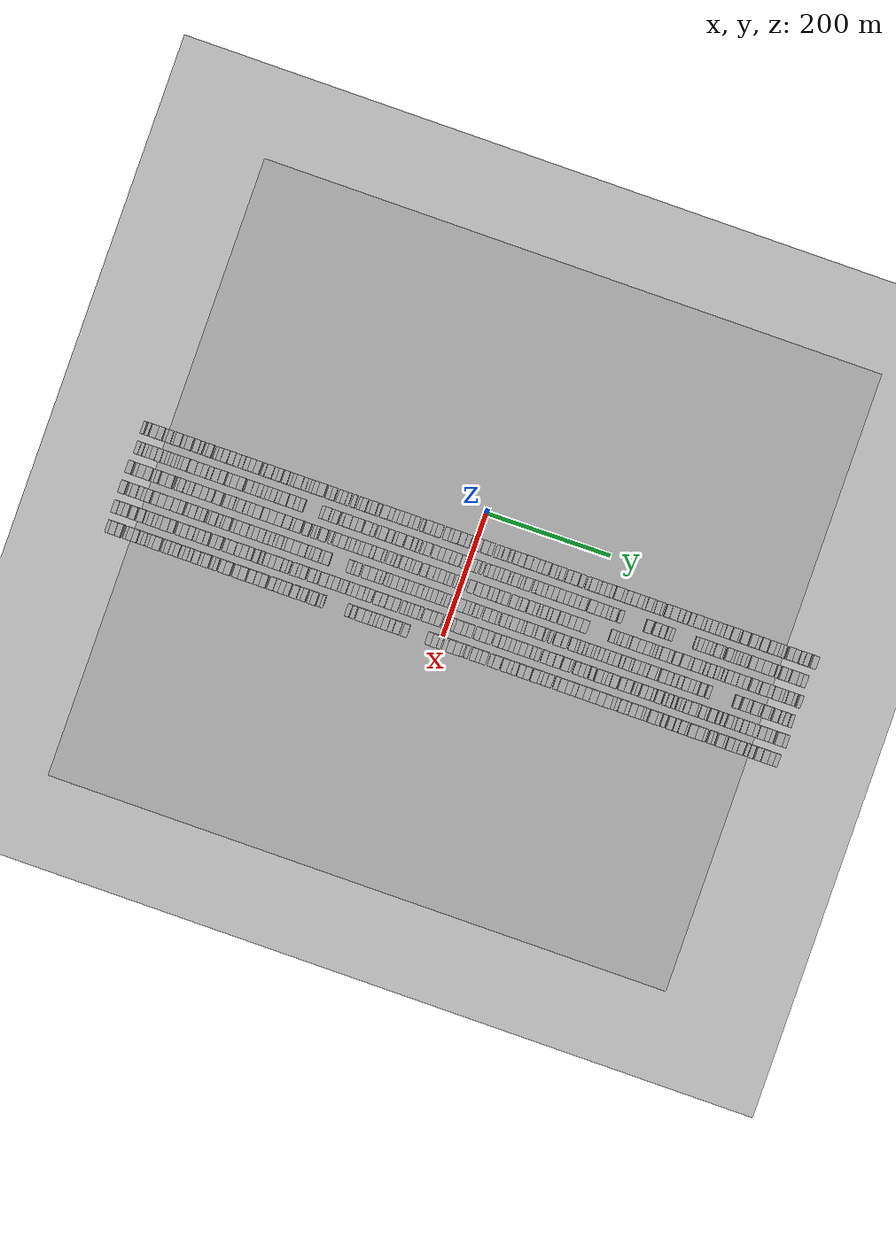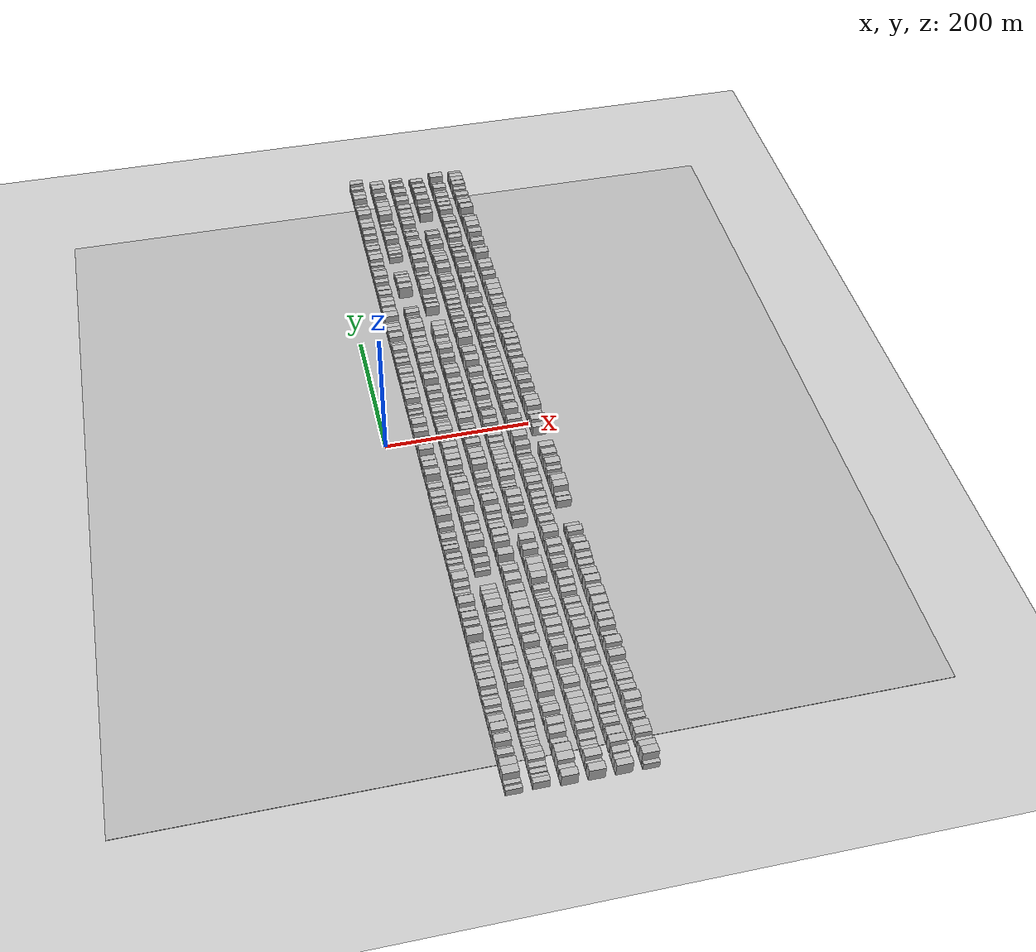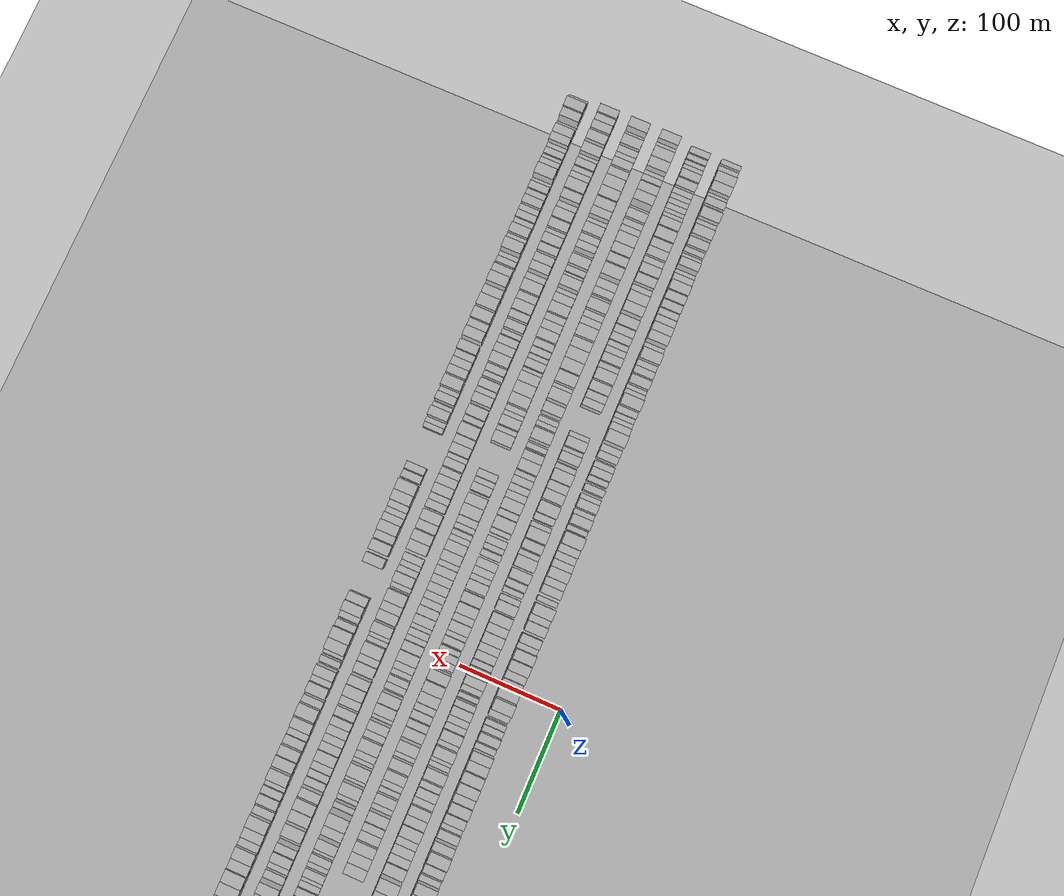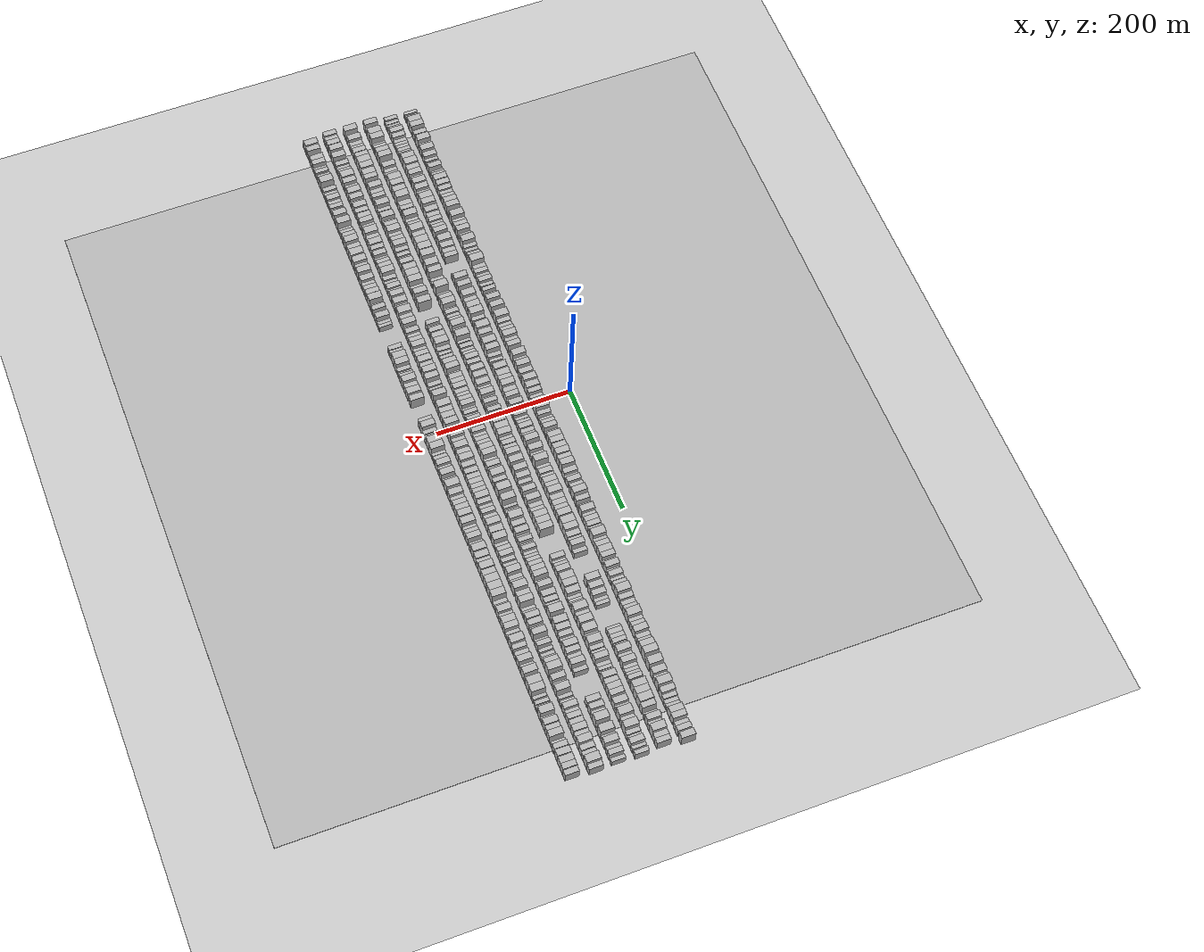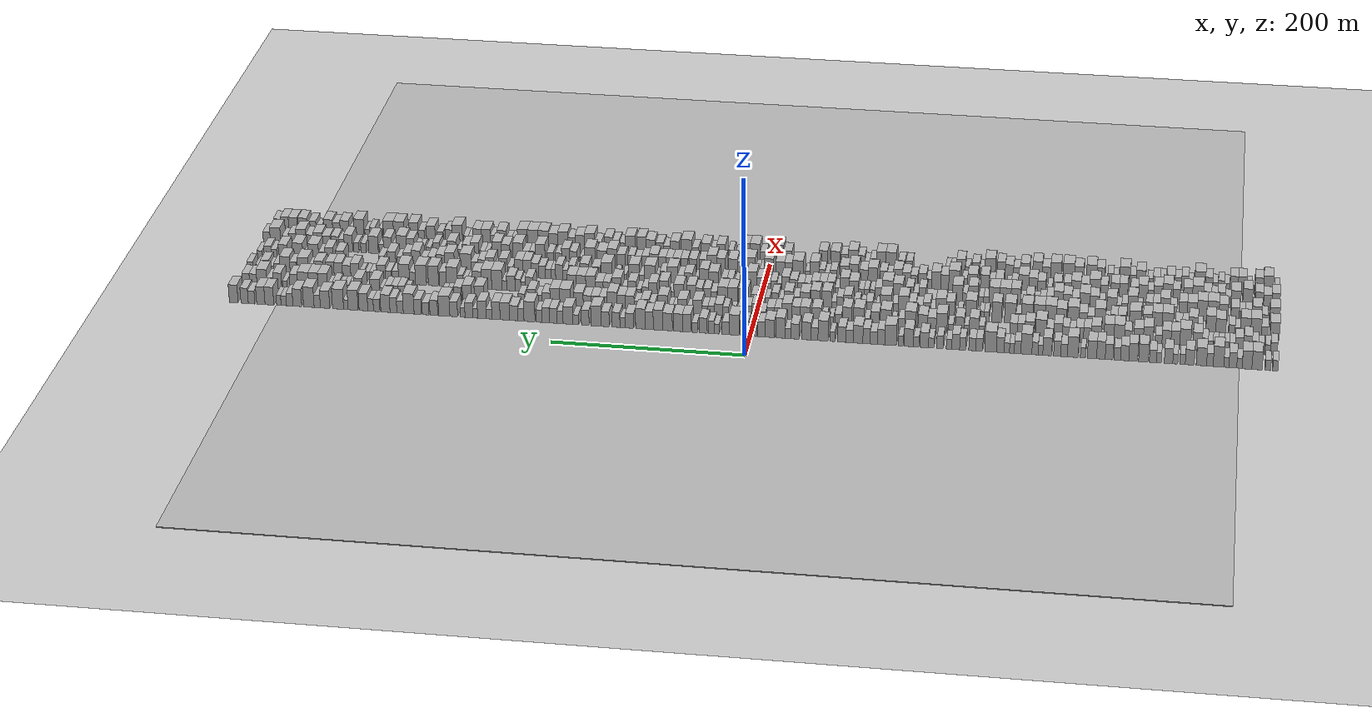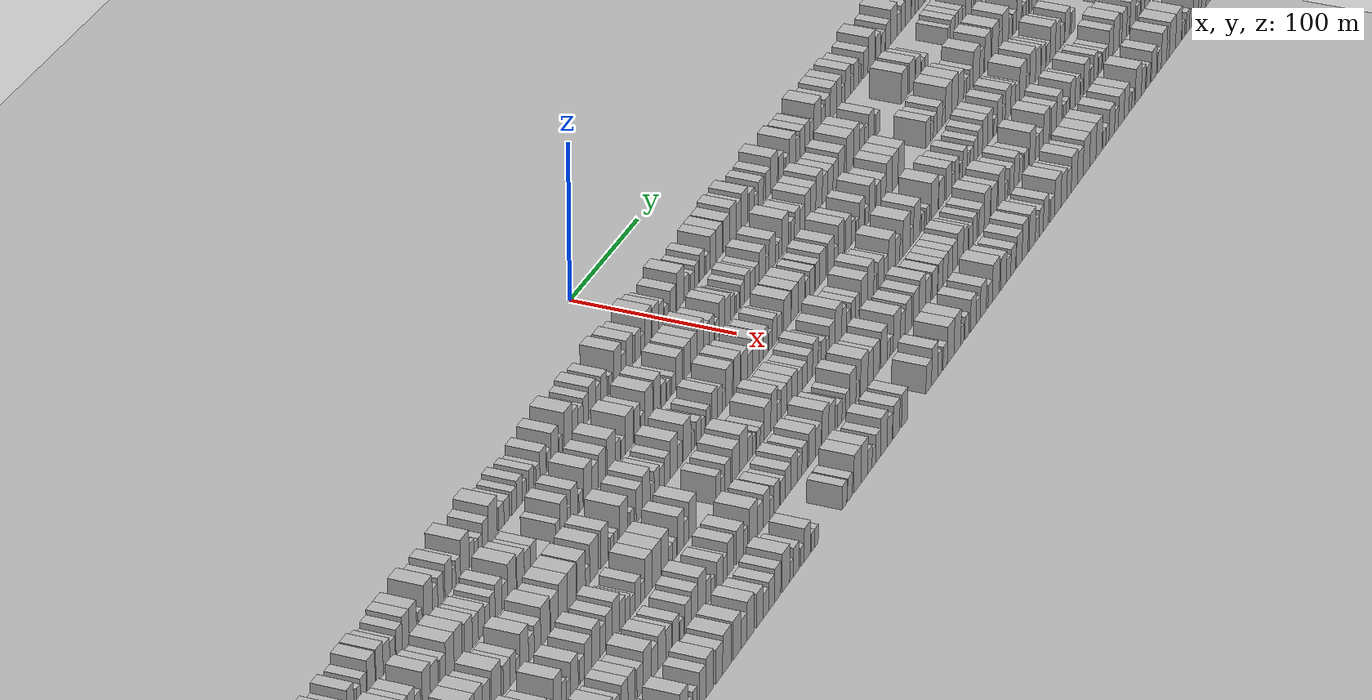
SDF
<?xml version="1.0" encoding="utf-8"?>

<sdf version="1.6">

   <world name="default">

      <gui fullscreen="0">

         <camera name="user_camera">

            <pose>-15 0 4.57585 0 0 0</pose>

            <view_controller>orbit</view_controller>

         </camera>

      </gui>

      <scene>

         <sky>

           <clouds>

             <speed>12</speed>

           </clouds>

         </sky>

         <ambient>0.4 0.4 0.4 1</ambient>

         <background>0.7 0.7 0.7 1</background>

         <shadows>1</shadows>

      </scene>

      <gravity>0 0 -9.8066</gravity>

      <magnetic_field>6e-06 2.3e-05 -4.2e-05</magnetic_field>

      <physics default="0" name="default_physics" type="ode">

         <ode>

            <solver>

               <type>quick</type>

               <iters>10</iters>

               <sor>1.0</sor>

               <use_dynamic_moi_rescaling>0</use_dynamic_moi_rescaling>

            </solver>

            <constraints>

               <cfm>0</cfm>

               <erp>0.2</erp>

               <contact_max_correcting_vel>100</contact_max_correcting_vel>

               <contact_surface_layer>0.001</contact_surface_layer>

            </constraints>

         </ode>

         <max_step_size>0.004</max_step_size>

         <real_time_factor>1</real_time_factor>

         <real_time_update_rate>250</real_time_update_rate>

      </physics>

      <light name="sun" type="directional">

         <cast_shadows>1</cast_shadows>

         <pose>0 0 10 0 0 0</pose>

         <diffuse>0.8 0.8 0.8 1</diffuse>

         <specular>0.2 0.2 0.2 1</specular>

         <attenuation>

            <range>1000</range>

            <constant>0.9</constant>

            <linear>0.01</linear>

            <quadratic>0.001</quadratic>

         </attenuation>

         <direction>-0.5 0.1 -0.9</direction>

      </light>

      <include>

         <name>ground_plane_1</name>

         <uri>model://HANNAS_ground_plane</uri>

         <pose>0 0 0  0 0 0</pose>

      </include>

      <include>

         <name>ground_plane_2</name>

         <uri>model://HANNAS_ground_plane</uri>

         <pose>100 0 0  0 0 0</pose>

      </include>

      <model name="building_1">

         <static>1</static>

         <pose frame="">50.0000 -536.3486 0 0.000000 0.000000 0.000000</pose>

         <link name="link">

            <pose frame="">0 0 6.00 0 0 0</pose>

            <collision name="collision">

               <geometry>

                  <box>

                     <size>20.0000 5.3027 12.0000</size>

                  </box>

               </geometry>

               <max_contacts>10</max_contacts>

               <surface>

                  <contact>

                     <ode/>

                  </contact>

                  <bounce/>

                  <friction>

                     <torsional>

                        <ode/>

                     </torsional>

                     <ode/>

                  </friction>

               </surface>

            </collision>

            <visual name="visual">

               <cast_shadows>0</cast_shadows>

               <geometry>

                  <box>

                     <size>20.0000 5.3027 12.0000</size>

                  </box>

               </geometry>

               <material>

                  <script>

                     <uri>model://HANNAS_wall/materials/scripts</uri>

                     <uri>model://HANNAS_wall/materials/textures</uri>

                     <name>vrc/HANNAS_wall</name>

                  </script>

               </material>

            </visual>

            <self_collide>0</self_collide>

            <enable_wind>0</enable_wind>

            <kinematic>0</kinematic>

         </link>

      </model>

      <model name="building_2">

         <static>1</static>

         <pose frame="">50.0000 -528.9705 0 0.000000 0.000000 0.000000</pose>

         <link name="link">

            <pose frame="">0 0 6.00 0 0 0</pose>

            <collision name="collision">

               <geometry>

                  <box>

                     <size>20.0000 5.4536 12.0000</size>

                  </box>

               </geometry>

               <max_contacts>10</max_contacts>

               <surface>

                  <contact>

                     <ode/>

                  </contact>

                  <bounce/>

                  <friction>

                     <torsional>

                        <ode/>

                     </torsional>

                     <ode/>

                  </friction>

               </surface>

            </collision>

            <visual name="visual">

               <cast_shadows>0</cast_shadows>

               <geometry>

                  <box>

                     <size>20.0000 5.4536 12.0000</size>

                  </box>

               </geometry>

               <material>

                  <script>

                     <uri>model://HANNAS_wall/materials/scripts</uri>

                     <uri>model://HANNAS_wall/materials/textures</uri>

                     <name>vrc/HANNAS_wall</name>

                  </script>

               </material>

            </visual>

            <self_collide>0</self_collide>

            <enable_wind>0</enable_wind>

            <kinematic>0</kinematic>

         </link>

      </model>

      <model name="building_3">

         <static>1</static>

         <pose frame="">50.0000 -518.0361 0 0.000000 0.000000 0.000000</pose>

         <link name="link">

            <pose frame="">0 0 10.50 0 0 0</pose>

            <collision name="collision">

               <geometry>

                  <box>

                     <size>20.0000 10.4152 21.0000</size>

                  </box>

               </geometry>

               <max_contacts>10</max_contacts>

               <surface>

                  <contact>

                     <ode/>

                  </contact>

                  <bounce/>

                  <friction>

                     <torsional>

                        <ode/>

                     </torsional>

                     <ode/>

                  </friction>

               </surface>

            </collision>

            <visual name="visual">

               <cast_shadows>0</cast_shadows>

               <geometry>

                  <box>

                     <size>20.0000 10.4152 21.0000</size>

                  </box>

               </geometry>

               <material>

                  <script>

                     <uri>model://HANNAS_wall/materials/scripts</uri>

                     <uri>model://HANNAS_wall/materials/textures</uri>

                     <name>vrc/HANNAS_wall</name>

                  </script>

               </material>

            </visual>

            <self_collide>0</self_collide>

            <enable_wind>0</enable_wind>

            <kinematic>0</kinematic>

         </link>

      </model>

      <model name="building_4">

         <static>1</static>

         <pose frame="">50.0000 -507.9157 0 0.000000 0.000000 0.000000</pose>

         <link name="link">

            <pose frame="">0 0 10.50 0 0 0</pose>

            <collision name="collision">

               <geometry>

                  <box>

                     <size>20.0000 9.8255 21.0000</size>

                  </box>

               </geometry>

               <max_contacts>10</max_contacts>

               <surface>

                  <contact>

                     <ode/>

                  </contact>

                  <bounce/>

                  <friction>

                     <torsional>

                        <ode/>

                     </torsional>

                     <ode/>

                  </friction>

               </surface>

            </collision>

            <visual name="visual">

               <cast_shadows>0</cast_shadows>

               <geometry>

                  <box>

                     <size>20.0000 9.8255 21.0000</size>

                  </box>

               </geometry>

               <material>

                  <script>

                     <uri>model://HANNAS_wall/materials/scripts</uri>

                     <uri>model://HANNAS_wall/materials/textures</uri>

                     <name>vrc/HANNAS_wall</name>

                  </script>

               </material>

            </visual>

            <self_collide>0</self_collide>

            <enable_wind>0</enable_wind>

            <kinematic>0</kinematic>

         </link>

      </model>

      <model name="building_5">

         <static>1</static>

         <pose frame="">50.0000 -500.2931 0 0.000000 0.000000 0.000000</pose>

         <link name="link">

            <pose frame="">0 0 6.00 0 0 0</pose>

            <collision name="collision">

               <geometry>

                  <box>

                     <size>20.0000 5.4197 12.0000</size>

                  </box>

               </geometry>

               <max_contacts>10</max_contacts>

               <surface>

                  <contact>

                     <ode/>

                  </contact>

                  <bounce/>

                  <friction>

                     <torsional>

                        <ode/>

                     </torsional>

                     <ode/>

                  </friction>

               </surface>

            </collision>

            <visual name="visual">

               <cast_shadows>0</cast_shadows>

               <geometry>

                  <box>

                     <size>20.0000 5.4197 12.0000</size>

                  </box>

               </geometry>

               <material>

                  <script>

                     <uri>model://HANNAS_wall/materials/scripts</uri>

                     <uri>model://HANNAS_wall/materials/textures</uri>

                     <name>vrc/HANNAS_wall</name>

                  </script>

               </material>

            </visual>

            <self_collide>0</self_collide>

            <enable_wind>0</enable_wind>

            <kinematic>0</kinematic>

         </link>

      </model>

      <model name="building_6">

         <static>1</static>

         <pose frame="">50.0000 -493.6248 0 0.000000 0.000000 0.000000</pose>

         <link name="link">

            <pose frame="">0 0 9.00 0 0 0</pose>

            <collision name="collision">

               <geometry>

                  <box>

                     <size>20.0000 7.9168 18.0000</size>

                  </box>

               </geometry>

               <max_contacts>10</max_contacts>

               <surface>

                  <contact>

                     <ode/>

                  </contact>

                  <bounce/>

                  <friction>

                     <torsional>

                        <ode/>

                     </torsional>

                     <ode/>

                  </friction>

               </surface>

            </collision>

            <visual name="visual">

               <cast_shadows>0</cast_shadows>

               <geometry>

                  <box>

                     <size>20.0000 7.9168 18.0000</size>

                  </box>

               </geometry>

               <material>

                  <script>

                     <uri>model://HANNAS_wall/materials/scripts</uri>

                     <uri>model://HANNAS_wall/materials/textures</uri>

                     <name>vrc/HANNAS_wall</name>

                  </script>

               </material>

            </visual>

            <self_collide>0</self_collide>

            <enable_wind>0</enable_wind>

            <kinematic>0</kinematic>

         </link>

      </model>

      <model name="building_7">

         <static>1</static>

         <pose frame="">50.0000 -487.1094 0 0.000000 0.000000 0.000000</pose>

         <link name="link">

            <pose frame="">0 0 6.00 0 0 0</pose>

            <collision name="collision">

               <geometry>

                  <box>

                     <size>20.0000 5.1140 12.0000</size>

                  </box>

               </geometry>

               <max_contacts>10</max_contacts>

               <surface>

                  <contact>

                     <ode/>

                  </contact>

                  <bounce/>

                  <friction>

                     <torsional>

                        <ode/>

                     </torsional>

                     <ode/>

                  </friction>

               </surface>

            </collision>

            <visual name="visual">

               <cast_shadows>0</cast_shadows>

               <geometry>

                  <box>

                     <size>20.0000 5.1140 12.0000</size>

                  </box>

               </geometry>

               <material>

                  <script>

                     <uri>model://HANNAS_wall/materials/scripts</uri>

                     <uri>model://HANNAS_wall/materials/textures</uri>

                     <name>vrc/HANNAS_wall</name>

                  </script>

               </material>

            </visual>

            <self_collide>0</self_collide>

            <enable_wind>0</enable_wind>

            <kinematic>0</kinematic>

         </link>

      </model>

      <model name="building_8">

         <static>1</static>

         <pose frame="">50.0000 -479.1775 0 0.000000 0.000000 0.000000</pose>

         <link name="link">

            <pose frame="">0 0 12.00 0 0 0</pose>

            <collision name="collision">

               <geometry>

                  <box>

                     <size>20.0000 10.7500 24.0000</size>

                  </box>

               </geometry>

               <max_contacts>10</max_contacts>

               <surface>

                  <contact>

                     <ode/>

                  </contact>

                  <bounce/>

                  <friction>

                     <torsional>

                        <ode/>

                     </torsional>

                     <ode/>

                  </friction>

               </surface>

            </collision>

            <visual name="visual">

               <cast_shadows>0</cast_shadows>

               <geometry>

                  <box>

                     <size>20.0000 10.7500 24.0000</size>

                  </box>

               </geometry>

               <material>

                  <script>

                     <uri>model://HANNAS_wall/materials/scripts</uri>

                     <uri>model://HANNAS_wall/materials/textures</uri>

                     <name>vrc/HANNAS_wall</name>

                  </script>

               </material>

            </visual>

            <self_collide>0</self_collide>

            <enable_wind>0</enable_wind>

            <kinematic>0</kinematic>

         </link>

      </model>

      <model name="building_9">

         <static>1</static>

         <pose frame="">50.0000 -470.5047 0 0.000000 0.000000 0.000000</pose>

         <link name="link">

            <pose frame="">0 0 7.50 0 0 0</pose>

            <collision name="collision">

               <geometry>

                  <box>

                     <size>20.0000 6.5956 15.0000</size>

                  </box>

               </geometry>

               <max_contacts>10</max_contacts>

               <surface>

                  <contact>

                     <ode/>

                  </contact>

                  <bounce/>

                  <friction>

                     <torsional>

                        <ode/>

                     </torsional>

                     <ode/>

                  </friction>

               </surface>

            </collision>

            <visual name="visual">

               <cast_shadows>0</cast_shadows>

               <geometry>

                  <box>

                     <size>20.0000 6.5956 15.0000</size>

                  </box>

               </geometry>

               <material>

                  <script>

                     <uri>model://HANNAS_wall/materials/scripts</uri>

                     <uri>model://HANNAS_wall/materials/textures</uri>

                     <name>vrc/HANNAS_wall</name>

                  </script>

               </material>

            </visual>

            <self_collide>0</self_collide>

            <enable_wind>0</enable_wind>

            <kinematic>0</kinematic>

         </link>

      </model>

      <model name="building_10">

         <static>1</static>

         <pose frame="">50.0000 -462.0079 0 0.000000 0.000000 0.000000</pose>

         <link name="link">

            <pose frame="">0 0 10.50 0 0 0</pose>

            <collision name="collision">

               <geometry>

                  <box>

                     <size>20.0000 10.3980 21.0000</size>

                  </box>

               </geometry>

               <max_contacts>10</max_contacts>

               <surface>

                  <contact>

                     <ode/>

                  </contact>

                  <bounce/>

                  <friction>

                     <torsional>

                        <ode/>

                     </torsional>

                     <ode/>

                  </friction>

               </surface>

            </collision>

            <visual name="visual">

               <cast_shadows>0</cast_shadows>

               <geometry>

                  <box>

                     <size>20.0000 10.3980 21.0000</size>

                  </box>

               </geometry>

               <material>

                  <script>

                     <uri>model://HANNAS_wall/materials/scripts</uri>

                     <uri>model://HANNAS_wall/materials/textures</uri>

                     <name>vrc/HANNAS_wall</name>

                  </script>

               </material>

            </visual>

            <self_collide>0</self_collide>

            <enable_wind>0</enable_wind>

            <kinematic>0</kinematic>

         </link>

      </model>

      <model name="building_11">

         <static>1</static>

         <pose frame="">50.0000 -450.3108 0 0.000000 0.000000 0.000000</pose>

         <link name="link">

            <pose frame="">0 0 9.00 0 0 0</pose>

            <collision name="collision">

               <geometry>

                  <box>

                     <size>20.0000 8.9963 18.0000</size>

                  </box>

               </geometry>

               <max_contacts>10</max_contacts>

               <surface>

                  <contact>

                     <ode/>

                  </contact>

                  <bounce/>

                  <friction>

                     <torsional>

                        <ode/>

                     </torsional>

                     <ode/>

                  </friction>

               </surface>

            </collision>

            <visual name="visual">

               <cast_shadows>0</cast_shadows>

               <geometry>

                  <box>

                     <size>20.0000 8.9963 18.0000</size>

                  </box>

               </geometry>

               <material>

                  <script>

                     <uri>model://HANNAS_wall/materials/scripts</uri>

                     <uri>model://HANNAS_wall/materials/textures</uri>

                     <name>vrc/HANNAS_wall</name>

                  </script>

               </material>

            </visual>

            <self_collide>0</self_collide>

            <enable_wind>0</enable_wind>

            <kinematic>0</kinematic>

         </link>

      </model>

      <model name="building_12">

         <static>1</static>

         <pose frame="">50.0000 -443.0770 0 0.000000 0.000000 0.000000</pose>

         <link name="link">

            <pose frame="">0 0 6.00 0 0 0</pose>

            <collision name="collision">

               <geometry>

                  <box>

                     <size>20.0000 5.4713 12.0000</size>

                  </box>

               </geometry>

               <max_contacts>10</max_contacts>

               <surface>

                  <contact>

                     <ode/>

                  </contact>

                  <bounce/>

                  <friction>

                     <torsional>

                        <ode/>

                     </torsional>

                     <ode/>

                  </friction>

               </surface>

            </collision>

            <visual name="visual">

               <cast_shadows>0</cast_shadows>

               <geometry>

                  <box>

                     <size>20.0000 5.4713 12.0000</size>

                  </box>

               </geometry>

               <material>

                  <script>

                     <uri>model://HANNAS_wall/materials/scripts</uri>

                     <uri>model://HANNAS_wall/materials/textures</uri>

                     <name>vrc/HANNAS_wall</name>

                  </script>

               </material>

            </visual>

            <self_collide>0</self_collide>

            <enable_wind>0</enable_wind>

            <kinematic>0</kinematic>

         </link>

      </model>

      <model name="building_13">

         <static>1</static>

         <pose frame="">50.0000 -435.7678 0 0.000000 0.000000 0.000000</pose>

         <link name="link">

            <pose frame="">0 0 6.00 0 0 0</pose>

            <collision name="collision">

               <geometry>

                  <box>

                     <size>20.0000 5.1471 12.0000</size>

                  </box>

               </geometry>

               <max_contacts>10</max_contacts>

               <surface>

                  <contact>

                     <ode/>

                  </contact>

                  <bounce/>

                  <friction>

                     <torsional>

                        <ode/>

                     </torsional>

                     <ode/>

                  </friction>

               </surface>

            </collision>

            <visual name="visual">

               <cast_shadows>0</cast_shadows>

               <geometry>

                  <box>

                     <size>20.0000 5.1471 12.0000</size>

                  </box>

               </geometry>

               <material>

                  <script>

                     <uri>model://HANNAS_wall/materials/scripts</uri>

                     <uri>model://HANNAS_wall/materials/textures</uri>

                     <name>vrc/HANNAS_wall</name>

                  </script>

               </material>

            </visual>

            <self_collide>0</self_collide>

            <enable_wind>0</enable_wind>

            <kinematic>0</kinematic>

         </link>

      </model>

      <model name="building_14">

         <static>1</static>

         <pose frame="">50.0000 -428.8972 0 0.000000 0.000000 0.000000</pose>

         <link name="link">

            <pose frame="">0 0 9.00 0 0 0</pose>

            <collision name="collision">

               <geometry>

                  <box>

                     <size>20.0000 8.5943 18.0000</size>

                  </box>

               </geometry>

               <max_contacts>10</max_contacts>

               <surface>

                  <contact>

                     <ode/>

                  </contact>

                  <bounce/>

                  <friction>

                     <torsional>

                        <ode/>

                     </torsional>

                     <ode/>

                  </friction>

               </surface>

            </collision>

            <visual name="visual">

               <cast_shadows>0</cast_shadows>

               <geometry>

                  <box>

                     <size>20.0000 8.5943 18.0000</size>

                  </box>

               </geometry>

               <material>

                  <script>

                     <uri>model://HANNAS_wall/materials/scripts</uri>

                     <uri>model://HANNAS_wall/materials/textures</uri>

                     <name>vrc/HANNAS_wall</name>

                  </script>

               </material>

            </visual>

            <self_collide>0</self_collide>

            <enable_wind>0</enable_wind>

            <kinematic>0</kinematic>

         </link>

      </model>

      <model name="building_15">

         <static>1</static>

         <pose frame="">50.0000 -419.1456 0 0.000000 0.000000 0.000000</pose>

         <link name="link">

            <pose frame="">0 0 6.00 0 0 0</pose>

            <collision name="collision">

               <geometry>

                  <box>

                     <size>20.0000 4.9089 12.0000</size>

                  </box>

               </geometry>

               <max_contacts>10</max_contacts>

               <surface>

                  <contact>

                     <ode/>

                  </contact>

                  <bounce/>

                  <friction>

                     <torsional>

                        <ode/>

                     </torsional>

                     <ode/>

                  </friction>

               </surface>

            </collision>

            <visual name="visual">

               <cast_shadows>0</cast_shadows>

               <geometry>

                  <box>

                     <size>20.0000 4.9089 12.0000</size>

                  </box>

               </geometry>

               <material>

                  <script>

                     <uri>model://HANNAS_wall/materials/scripts</uri>

                     <uri>model://HANNAS_wall/materials/textures</uri>

                     <name>vrc/HANNAS_wall</name>

                  </script>

               </material>

            </visual>

            <self_collide>0</self_collide>

            <enable_wind>0</enable_wind>

            <kinematic>0</kinematic>

         </link>

      </model>

      <model name="building_16">

         <static>1</static>

         <pose frame="">50.0000 -413.0892 0 0.000000 0.000000 0.000000</pose>

         <link name="link">

            <pose frame="">0 0 7.50 0 0 0</pose>

            <collision name="collision">

               <geometry>

                  <box>

                     <size>20.0000 7.2039 15.0000</size>

                  </box>

               </geometry>

               <max_contacts>10</max_contacts>

               <surface>

                  <contact>

                     <ode/>

                  </contact>

                  <bounce/>

                  <friction>

                     <torsional>

                        <ode/>

                     </torsional>

                     <ode/>

                  </friction>

               </surface>

            </collision>

            <visual name="visual">

               <cast_shadows>0</cast_shadows>

               <geometry>

                  <box>

                     <size>20.0000 7.2039 15.0000</size>

                  </box>

               </geometry>

               <material>

                  <script>

                     <uri>model://HANNAS_wall/materials/scripts</uri>

                     <uri>model://HANNAS_wall/materials/textures</uri>

                     <name>vrc/HANNAS_wall</name>

                  </script>

               </material>

            </visual>

            <self_collide>0</self_collide>

            <enable_wind>0</enable_wind>

            <kinematic>0</kinematic>

         </link>

      </model>

      <model name="building_17">

         <static>1</static>

         <pose frame="">50.0000 -403.5723 0 0.000000 0.000000 0.000000</pose>

         <link name="link">

            <pose frame="">0 0 10.50 0 0 0</pose>

            <collision name="collision">

               <geometry>

                  <box>

                     <size>20.0000 9.8299 21.0000</size>

                  </box>

               </geometry>

               <max_contacts>10</max_contacts>

               <surface>

                  <contact>

                     <ode/>

                  </contact>

                  <bounce/>

                  <friction>

                     <torsional>

                        <ode/>

                     </torsional>

                     <ode/>

                  </friction>

               </surface>

            </collision>

            <visual name="visual">

               <cast_shadows>0</cast_shadows>

               <geometry>

                  <box>

                     <size>20.0000 9.8299 21.0000</size>

                  </box>

               </geometry>

               <material>

                  <script>

                     <uri>model://HANNAS_wall/materials/scripts</uri>

                     <uri>model://HANNAS_wall/materials/textures</uri>

                     <name>vrc/HANNAS_wall</name>

                  </script>

               </material>

            </visual>

            <self_collide>0</self_collide>

            <enable_wind>0</enable_wind>

            <kinematic>0</kinematic>

         </link>

      </model>

      <model name="building_18">

         <static>1</static>

         <pose frame="">50.0000 -393.1767 0 0.000000 0.000000 0.000000</pose>

         <link name="link">

            <pose frame="">0 0 10.50 0 0 0</pose>

            <collision name="collision">

               <geometry>

                  <box>

                     <size>20.0000 8.9613 21.0000</size>

                  </box>

               </geometry>

               <max_contacts>10</max_contacts>

               <surface>

                  <contact>

                     <ode/>

                  </contact>

                  <bounce/>

                  <friction>

                     <torsional>

                        <ode/>

                     </torsional>

                     <ode/>

                  </friction>

               </surface>

            </collision>

            <visual name="visual">

               <cast_shadows>0</cast_shadows>

               <geometry>

                  <box>

                     <size>20.0000 8.9613 21.0000</size>

                  </box>

               </geometry>

               <material>

                  <script>

                     <uri>model://HANNAS_wall/materials/scripts</uri>

                     <uri>model://HANNAS_wall/materials/textures</uri>

                     <name>vrc/HANNAS_wall</name>

                  </script>

               </material>

            </visual>

            <self_collide>0</self_collide>

            <enable_wind>0</enable_wind>

            <kinematic>0</kinematic>

         </link>

      </model>

      <model name="building_19">

         <static>1</static>

         <pose frame="">50.0000 -384.5406 0 0.000000 0.000000 0.000000</pose>

         <link name="link">

            <pose frame="">0 0 9.00 0 0 0</pose>

            <collision name="collision">

               <geometry>

                  <box>

                     <size>20.0000 8.3110 18.0000</size>

                  </box>

               </geometry>

               <max_contacts>10</max_contacts>

               <surface>

                  <contact>

                     <ode/>

                  </contact>

                  <bounce/>

                  <friction>

                     <torsional>

                        <ode/>

                     </torsional>

                     <ode/>

                  </friction>

               </surface>

            </collision>

            <visual name="visual">

               <cast_shadows>0</cast_shadows>

               <geometry>

                  <box>

                     <size>20.0000 8.3110 18.0000</size>

                  </box>

               </geometry>

               <material>

                  <script>

                     <uri>model://HANNAS_wall/materials/scripts</uri>

                     <uri>model://HANNAS_wall/materials/textures</uri>

                     <name>vrc/HANNAS_wall</name>

                  </script>

               </material>

            </visual>

            <self_collide>0</self_collide>

            <enable_wind>0</enable_wind>

            <kinematic>0</kinematic>

         </link>

      </model>

      <model name="building_20">

         <static>1</static>

         <pose frame="">50.0000 -377.0066 0 0.000000 0.000000 0.000000</pose>

         <link name="link">

            <pose frame="">0 0 7.50 0 0 0</pose>

            <collision name="collision">

               <geometry>

                  <box>

                     <size>20.0000 6.7570 15.0000</size>

                  </box>

               </geometry>

               <max_contacts>10</max_contacts>

               <surface>

                  <contact>

                     <ode/>

                  </contact>

                  <bounce/>

                  <friction>

                     <torsional>

                        <ode/>

                     </torsional>

                     <ode/>

                  </friction>

               </surface>

            </collision>

            <visual name="visual">

               <cast_shadows>0</cast_shadows>

               <geometry>

                  <box>

                     <size>20.0000 6.7570 15.0000</size>

                  </box>

               </geometry>

               <material>

                  <script>

                     <uri>model://HANNAS_wall/materials/scripts</uri>

                     <uri>model://HANNAS_wall/materials/textures</uri>

                     <name>vrc/HANNAS_wall</name>

                  </script>

               </material>

            </visual>

            <self_collide>0</self_collide>

            <enable_wind>0</enable_wind>

            <kinematic>0</kinematic>

         </link>

      </model>

      <model name="building_21">

         <static>1</static>

         <pose frame="">50.0000 -368.7343 0 0.000000 0.000000 0.000000</pose>

         <link name="link">

            <pose frame="">0 0 9.00 0 0 0</pose>

            <collision name="collision">

               <geometry>

                  <box>

                     <size>20.0000 7.7875 18.0000</size>

                  </box>

               </geometry>

               <max_contacts>10</max_contacts>

               <surface>

                  <contact>

                     <ode/>

                  </contact>

                  <bounce/>

                  <friction>

                     <torsional>

                        <ode/>

                     </torsional>

                     <ode/>

                  </friction>

               </surface>

            </collision>

            <visual name="visual">

               <cast_shadows>0</cast_shadows>

               <geometry>

                  <box>

                     <size>20.0000 7.7875 18.0000</size>

                  </box>

               </geometry>

               <material>

                  <script>

                     <uri>model://HANNAS_wall/materials/scripts</uri>

                     <uri>model://HANNAS_wall/materials/textures</uri>

                     <name>vrc/HANNAS_wall</name>

                  </script>

               </material>

            </visual>

            <self_collide>0</self_collide>

            <enable_wind>0</enable_wind>

            <kinematic>0</kinematic>

         </link>

      </model>

      <model name="building_22">

         <static>1</static>

         <pose frame="">50.0000 -360.5023 0 0.000000 0.000000 0.000000</pose>

         <link name="link">

            <pose frame="">0 0 10.50 0 0 0</pose>

            <collision name="collision">

               <geometry>

                  <box>

                     <size>20.0000 8.6766 21.0000</size>

                  </box>

               </geometry>

               <max_contacts>10</max_contacts>

               <surface>

                  <contact>

                     <ode/>

                  </contact>

                  <bounce/>

                  <friction>

                     <torsional>

                        <ode/>

                     </torsional>

                     <ode/>

                  </friction>

               </surface>

            </collision>

            <visual name="visual">

               <cast_shadows>0</cast_shadows>

               <geometry>

                  <box>

                     <size>20.0000 8.6766 21.0000</size>

                  </box>

               </geometry>

               <material>

                  <script>

                     <uri>model://HANNAS_wall/materials/scripts</uri>

                     <uri>model://HANNAS_wall/materials/textures</uri>

                     <name>vrc/HANNAS_wall</name>

                  </script>

               </material>

            </visual>

            <self_collide>0</self_collide>

            <enable_wind>0</enable_wind>

            <kinematic>0</kinematic>

         </link>

      </model>

      <model name="building_23">

         <static>1</static>

         <pose frame="">50.0000 -351.4642 0 0.000000 0.000000 0.000000</pose>

         <link name="link">

            <pose frame="">0 0 10.50 0 0 0</pose>

            <collision name="collision">

               <geometry>

                  <box>

                     <size>20.0000 9.3995 21.0000</size>

                  </box>

               </geometry>

               <max_contacts>10</max_contacts>

               <surface>

                  <contact>

                     <ode/>

                  </contact>

                  <bounce/>

                  <friction>

                     <torsional>

                        <ode/>

                     </torsional>

                     <ode/>

                  </friction>

               </surface>

            </collision>

            <visual name="visual">

               <cast_shadows>0</cast_shadows>

               <geometry>

                  <box>

                     <size>20.0000 9.3995 21.0000</size>

                  </box>

               </geometry>

               <material>

                  <script>

                     <uri>model://HANNAS_wall/materials/scripts</uri>

                     <uri>model://HANNAS_wall/materials/textures</uri>

                     <name>vrc/HANNAS_wall</name>

                  </script>

               </material>

            </visual>

            <self_collide>0</self_collide>

            <enable_wind>0</enable_wind>

            <kinematic>0</kinematic>

         </link>

      </model>

      <model name="building_24">

         <static>1</static>

         <pose frame="">50.0000 -342.1677 0 0.000000 0.000000 0.000000</pose>

         <link name="link">

            <pose frame="">0 0 6.00 0 0 0</pose>

            <collision name="collision">

               <geometry>

                  <box>

                     <size>20.0000 5.1936 12.0000</size>

                  </box>

               </geometry>

               <max_contacts>10</max_contacts>

               <surface>

                  <contact>

                     <ode/>

                  </contact>

                  <bounce/>

                  <friction>

                     <torsional>

                        <ode/>

                     </torsional>

                     <ode/>

                  </friction>

               </surface>

            </collision>

            <visual name="visual">

               <cast_shadows>0</cast_shadows>

               <geometry>

                  <box>

                     <size>20.0000 5.1936 12.0000</size>

                  </box>

               </geometry>

               <material>

                  <script>

                     <uri>model://HANNAS_wall/materials/scripts</uri>

                     <uri>model://HANNAS_wall/materials/textures</uri>

                     <name>vrc/HANNAS_wall</name>

                  </script>

               </material>

            </visual>

            <self_collide>0</self_collide>

            <enable_wind>0</enable_wind>

            <kinematic>0</kinematic>

         </link>

      </model>

      <model name="building_25">

         <static>1</static>

         <pose frame="">50.0000 -332.0227 0 0.000000 0.000000 0.000000</pose>

         <link name="link">

            <pose frame="">0 0 12.00 0 0 0</pose>

            <collision name="collision">

               <geometry>

                  <box>

                     <size>20.0000 11.0964 24.0000</size>

                  </box>

               </geometry>

               <max_contacts>10</max_contacts>

               <surface>

                  <contact>

                     <ode/>

                  </contact>

                  <bounce/>

                  <friction>

                     <torsional>

                        <ode/>

                     </torsional>

                     <ode/>

                  </friction>

               </surface>

            </collision>

            <visual name="visual">

               <cast_shadows>0</cast_shadows>

               <geometry>

                  <box>

                     <size>20.0000 11.0964 24.0000</size>

                  </box>

               </geometry>

               <material>

                  <script>

                     <uri>model://HANNAS_wall/materials/scripts</uri>

                     <uri>model://HANNAS_wall/materials/textures</uri>

                     <name>vrc/HANNAS_wall</name>

                  </script>

               </material>

            </visual>

            <self_collide>0</self_collide>

            <enable_wind>0</enable_wind>

            <kinematic>0</kinematic>

         </link>

      </model>

      <model name="building_26">

         <static>1</static>

         <pose frame="">50.0000 -323.1114 0 0.000000 0.000000 0.000000</pose>

         <link name="link">

            <pose frame="">0 0 7.50 0 0 0</pose>

            <collision name="collision">

               <geometry>

                  <box>

                     <size>20.0000 6.7260 15.0000</size>

                  </box>

               </geometry>

               <max_contacts>10</max_contacts>

               <surface>

                  <contact>

                     <ode/>

                  </contact>

                  <bounce/>

                  <friction>

                     <torsional>

                        <ode/>

                     </torsional>

                     <ode/>

                  </friction>

               </surface>

            </collision>

            <visual name="visual">

               <cast_shadows>0</cast_shadows>

               <geometry>

                  <box>

                     <size>20.0000 6.7260 15.0000</size>

                  </box>

               </geometry>

               <material>

                  <script>

                     <uri>model://HANNAS_wall/materials/scripts</uri>

                     <uri>model://HANNAS_wall/materials/textures</uri>

                     <name>vrc/HANNAS_wall</name>

                  </script>

               </material>

            </visual>

            <self_collide>0</self_collide>

            <enable_wind>0</enable_wind>

            <kinematic>0</kinematic>

         </link>

      </model>

      <model name="building_27">

         <static>1</static>

         <pose frame="">50.0000 -316.0985 0 0.000000 0.000000 0.000000</pose>

         <link name="link">

            <pose frame="">0 0 9.00 0 0 0</pose>

            <collision name="collision">

               <geometry>

                  <box>

                     <size>20.0000 7.2999 18.0000</size>

                  </box>

               </geometry>

               <max_contacts>10</max_contacts>

               <surface>

                  <contact>

                     <ode/>

                  </contact>

                  <bounce/>

                  <friction>

                     <torsional>

                        <ode/>

                     </torsional>

                     <ode/>

                  </friction>

               </surface>

            </collision>

            <visual name="visual">

               <cast_shadows>0</cast_shadows>

               <geometry>

                  <box>

                     <size>20.0000 7.2999 18.0000</size>

                  </box>

               </geometry>

               <material>

                  <script>

                     <uri>model://HANNAS_wall/materials/scripts</uri>

                     <uri>model://HANNAS_wall/materials/textures</uri>

                     <name>vrc/HANNAS_wall</name>

                  </script>

               </material>

            </visual>

            <self_collide>0</self_collide>

            <enable_wind>0</enable_wind>

            <kinematic>0</kinematic>

         </link>

      </model>

      <model name="building_28">

         <static>1</static>

         <pose frame="">50.0000 -305.9379 0 0.000000 0.000000 0.000000</pose>

         <link name="link">

            <pose frame="">0 0 10.50 0 0 0</pose>

            <collision name="collision">

               <geometry>

                  <box>

                     <size>20.0000 9.0212 21.0000</size>

                  </box>

               </geometry>

               <max_contacts>10</max_contacts>

               <surface>

                  <contact>

                     <ode/>

                  </contact>

                  <bounce/>

                  <friction>

                     <torsional>

                        <ode/>

                     </torsional>

                     <ode/>

                  </friction>

               </surface>

            </collision>

            <visual name="visual">

               <cast_shadows>0</cast_shadows>

               <geometry>

                  <box>

                     <size>20.0000 9.0212 21.0000</size>

                  </box>

               </geometry>

               <material>

                  <script>

                     <uri>model://HANNAS_wall/materials/scripts</uri>

                     <uri>model://HANNAS_wall/materials/textures</uri>

                     <name>vrc/HANNAS_wall</name>

                  </script>

               </material>

            </visual>

            <self_collide>0</self_collide>

            <enable_wind>0</enable_wind>

            <kinematic>0</kinematic>

         </link>

      </model>

      <model name="building_29">

         <static>1</static>

         <pose frame="">50.0000 -299.0022 0 0.000000 0.000000 0.000000</pose>

         <link name="link">

            <pose frame="">0 0 6.00 0 0 0</pose>

            <collision name="collision">

               <geometry>

                  <box>

                     <size>20.0000 4.8502 12.0000</size>

                  </box>

               </geometry>

               <max_contacts>10</max_contacts>

               <surface>

                  <contact>

                     <ode/>

                  </contact>

                  <bounce/>

                  <friction>

                     <torsional>

                        <ode/>

                     </torsional>

                     <ode/>

                  </friction>

               </surface>

            </collision>

            <visual name="visual">

               <cast_shadows>0</cast_shadows>

               <geometry>

                  <box>

                     <size>20.0000 4.8502 12.0000</size>

                  </box>

               </geometry>

               <material>

                  <script>

                     <uri>model://HANNAS_wall/materials/scripts</uri>

                     <uri>model://HANNAS_wall/materials/textures</uri>

                     <name>vrc/HANNAS_wall</name>

                  </script>

               </material>

            </visual>

            <self_collide>0</self_collide>

            <enable_wind>0</enable_wind>

            <kinematic>0</kinematic>

         </link>

      </model>

      <model name="building_30">

         <static>1</static>

         <pose frame="">50.0000 -293.4492 0 0.000000 0.000000 0.000000</pose>

         <link name="link">

            <pose frame="">0 0 7.50 0 0 0</pose>

            <collision name="collision">

               <geometry>

                  <box>

                     <size>20.0000 6.2558 15.0000</size>

                  </box>

               </geometry>

               <max_contacts>10</max_contacts>

               <surface>

                  <contact>

                     <ode/>

                  </contact>

                  <bounce/>

                  <friction>

                     <torsional>

                        <ode/>

                     </torsional>

                     <ode/>

                  </friction>

               </surface>

            </collision>

            <visual name="visual">

               <cast_shadows>0</cast_shadows>

               <geometry>

                  <box>

                     <size>20.0000 6.2558 15.0000</size>

                  </box>

               </geometry>

               <material>

                  <script>

                     <uri>model://HANNAS_wall/materials/scripts</uri>

                     <uri>model://HANNAS_wall/materials/textures</uri>

                     <name>vrc/HANNAS_wall</name>

                  </script>

               </material>

            </visual>

            <self_collide>0</self_collide>

            <enable_wind>0</enable_wind>

            <kinematic>0</kinematic>

         </link>

      </model>

      <model name="building_31">

         <static>1</static>

         <pose frame="">50.0000 -284.7208 0 0.000000 0.000000 0.000000</pose>

         <link name="link">

            <pose frame="">0 0 12.00 0 0 0</pose>

            <collision name="collision">

               <geometry>

                  <box>

                     <size>20.0000 11.2011 24.0000</size>

                  </box>

               </geometry>

               <max_contacts>10</max_contacts>

               <surface>

                  <contact>

                     <ode/>

                  </contact>

                  <bounce/>

                  <friction>

                     <torsional>

                        <ode/>

                     </torsional>

                     <ode/>

                  </friction>

               </surface>

            </collision>

            <visual name="visual">

               <cast_shadows>0</cast_shadows>

               <geometry>

                  <box>

                     <size>20.0000 11.2011 24.0000</size>

                  </box>

               </geometry>

               <material>

                  <script>

                     <uri>model://HANNAS_wall/materials/scripts</uri>

                     <uri>model://HANNAS_wall/materials/textures</uri>

                     <name>vrc/HANNAS_wall</name>

                  </script>

               </material>

            </visual>

            <self_collide>0</self_collide>

            <enable_wind>0</enable_wind>

            <kinematic>0</kinematic>

         </link>

      </model>

      <model name="building_32">

         <static>1</static>

         <pose frame="">50.0000 -275.7651 0 0.000000 0.000000 0.000000</pose>

         <link name="link">

            <pose frame="">0 0 7.50 0 0 0</pose>

            <collision name="collision">

               <geometry>

                  <box>

                     <size>20.0000 6.7103 15.0000</size>

                  </box>

               </geometry>

               <max_contacts>10</max_contacts>

               <surface>

                  <contact>

                     <ode/>

                  </contact>

                  <bounce/>

                  <friction>

                     <torsional>

                        <ode/>

                     </torsional>

                     <ode/>

                  </friction>

               </surface>

            </collision>

            <visual name="visual">

               <cast_shadows>0</cast_shadows>

               <geometry>

                  <box>

                     <size>20.0000 6.7103 15.0000</size>

                  </box>

               </geometry>

               <material>

                  <script>

                     <uri>model://HANNAS_wall/materials/scripts</uri>

                     <uri>model://HANNAS_wall/materials/textures</uri>

                     <name>vrc/HANNAS_wall</name>

                  </script>

               </material>

            </visual>

            <self_collide>0</self_collide>

            <enable_wind>0</enable_wind>

            <kinematic>0</kinematic>

         </link>

      </model>

      <model name="building_33">

         <static>1</static>

         <pose frame="">50.0000 -269.9384 0 0.000000 0.000000 0.000000</pose>

         <link name="link">

            <pose frame="">0 0 6.00 0 0 0</pose>

            <collision name="collision">

               <geometry>

                  <box>

                     <size>20.0000 4.9430 12.0000</size>

                  </box>

               </geometry>

               <max_contacts>10</max_contacts>

               <surface>

                  <contact>

                     <ode/>

                  </contact>

                  <bounce/>

                  <friction>

                     <torsional>

                        <ode/>

                     </torsional>

                     <ode/>

                  </friction>

               </surface>

            </collision>

            <visual name="visual">

               <cast_shadows>0</cast_shadows>

               <geometry>

                  <box>

                     <size>20.0000 4.9430 12.0000</size>

                  </box>

               </geometry>

               <material>

                  <script>

                     <uri>model://HANNAS_wall/materials/scripts</uri>

                     <uri>model://HANNAS_wall/materials/textures</uri>

                     <name>vrc/HANNAS_wall</name>

                  </script>

               </material>

            </visual>

            <self_collide>0</self_collide>

            <enable_wind>0</enable_wind>

            <kinematic>0</kinematic>

         </link>

      </model>

      <model name="building_34">

         <static>1</static>

         <pose frame="">50.0000 -264.7541 0 0.000000 0.000000 0.000000</pose>

         <link name="link">

            <pose frame="">0 0 6.00 0 0 0</pose>

            <collision name="collision">

               <geometry>

                  <box>

                     <size>20.0000 5.4256 12.0000</size>

                  </box>

               </geometry>

               <max_contacts>10</max_contacts>

               <surface>

                  <contact>

                     <ode/>

                  </contact>

                  <bounce/>

                  <friction>

                     <torsional>

                        <ode/>

                     </torsional>

                     <ode/>

                  </friction>

               </surface>

            </collision>

            <visual name="visual">

               <cast_shadows>0</cast_shadows>

               <geometry>

                  <box>

                     <size>20.0000 5.4256 12.0000</size>

                  </box>

               </geometry>

               <material>

                  <script>

                     <uri>model://HANNAS_wall/materials/scripts</uri>

                     <uri>model://HANNAS_wall/materials/textures</uri>

                     <name>vrc/HANNAS_wall</name>

                  </script>

               </material>

            </visual>

            <self_collide>0</self_collide>

            <enable_wind>0</enable_wind>

            <kinematic>0</kinematic>

         </link>

      </model>

      <model name="building_35">

         <static>1</static>

         <pose frame="">50.0000 -258.0373 0 0.000000 0.000000 0.000000</pose>

         <link name="link">

            <pose frame="">0 0 9.00 0 0 0</pose>

            <collision name="collision">

               <geometry>

                  <box>

                     <size>20.0000 8.0079 18.0000</size>

                  </box>

               </geometry>

               <max_contacts>10</max_contacts>

               <surface>

                  <contact>

                     <ode/>

                  </contact>

                  <bounce/>

                  <friction>

                     <torsional>

                        <ode/>

                     </torsional>

                     <ode/>

                  </friction>

               </surface>

            </collision>

            <visual name="visual">

               <cast_shadows>0</cast_shadows>

               <geometry>

                  <box>

                     <size>20.0000 8.0079 18.0000</size>

                  </box>

               </geometry>

               <material>

                  <script>

                     <uri>model://HANNAS_wall/materials/scripts</uri>

                     <uri>model://HANNAS_wall/materials/textures</uri>

                     <name>vrc/HANNAS_wall</name>

                  </script>

               </material>

            </visual>

            <self_collide>0</self_collide>

            <enable_wind>0</enable_wind>

            <kinematic>0</kinematic>

         </link>

      </model>

      <model name="building_36">

         <static>1</static>

         <pose frame="">50.0000 -248.0703 0 0.000000 0.000000 0.000000</pose>

         <link name="link">

            <pose frame="">0 0 12.00 0 0 0</pose>

            <collision name="collision">

               <geometry>

                  <box>

                     <size>20.0000 11.9261 24.0000</size>

                  </box>

               </geometry>

               <max_contacts>10</max_contacts>

               <surface>

                  <contact>

                     <ode/>

                  </contact>

                  <bounce/>

                  <friction>

                     <torsional>

                        <ode/>

                     </torsional>

                     <ode/>

                  </friction>

               </surface>

            </collision>

            <visual name="visual">

               <cast_shadows>0</cast_shadows>

               <geometry>

                  <box>

                     <size>20.0000 11.9261 24.0000</size>

                  </box>

               </geometry>

               <material>

                  <script>

                     <uri>model://HANNAS_wall/materials/scripts</uri>

                     <uri>model://HANNAS_wall/materials/textures</uri>

                     <name>vrc/HANNAS_wall</name>

                  </script>

               </material>

            </visual>

            <self_collide>0</self_collide>

            <enable_wind>0</enable_wind>

            <kinematic>0</kinematic>

         </link>

      </model>

      <model name="building_37">

         <static>1</static>

         <pose frame="">50.0000 -236.6363 0 0.000000 0.000000 0.000000</pose>

         <link name="link">

            <pose frame="">0 0 7.50 0 0 0</pose>

            <collision name="collision">

               <geometry>

                  <box>

                     <size>20.0000 6.9419 15.0000</size>

                  </box>

               </geometry>

               <max_contacts>10</max_contacts>

               <surface>

                  <contact>

                     <ode/>

                  </contact>

                  <bounce/>

                  <friction>

                     <torsional>

                        <ode/>

                     </torsional>

                     <ode/>

                  </friction>

               </surface>

            </collision>

            <visual name="visual">

               <cast_shadows>0</cast_shadows>

               <geometry>

                  <box>

                     <size>20.0000 6.9419 15.0000</size>

                  </box>

               </geometry>

               <material>

                  <script>

                     <uri>model://HANNAS_wall/materials/scripts</uri>

                     <uri>model://HANNAS_wall/materials/textures</uri>

                     <name>vrc/HANNAS_wall</name>

                  </script>

               </material>

            </visual>

            <self_collide>0</self_collide>

            <enable_wind>0</enable_wind>

            <kinematic>0</kinematic>

         </link>

      </model>

      <model name="building_38">

         <static>1</static>

         <pose frame="">50.0000 -229.5078 0 0.000000 0.000000 0.000000</pose>

         <link name="link">

            <pose frame="">0 0 7.50 0 0 0</pose>

            <collision name="collision">

               <geometry>

                  <box>

                     <size>20.0000 7.3150 15.0000</size>

                  </box>

               </geometry>

               <max_contacts>10</max_contacts>

               <surface>

                  <contact>

                     <ode/>

                  </contact>

                  <bounce/>

                  <friction>

                     <torsional>

                        <ode/>

                     </torsional>

                     <ode/>

                  </friction>

               </surface>

            </collision>

            <visual name="visual">

               <cast_shadows>0</cast_shadows>

               <geometry>

                  <box>

                     <size>20.0000 7.3150 15.0000</size>

                  </box>

               </geometry>

               <material>

                  <script>

                     <uri>model://HANNAS_wall/materials/scripts</uri>

                     <uri>model://HANNAS_wall/materials/textures</uri>

                     <name>vrc/HANNAS_wall</name>

                  </script>

               </material>

            </visual>

            <self_collide>0</self_collide>

            <enable_wind>0</enable_wind>

            <kinematic>0</kinematic>

         </link>

      </model>

      <model name="building_39">

         <static>1</static>

         <pose frame="">50.0000 -219.6651 0 0.000000 0.000000 0.000000</pose>

         <link name="link">

            <pose frame="">0 0 7.50 0 0 0</pose>

            <collision name="collision">

               <geometry>

                  <box>

                     <size>20.0000 6.3704 15.0000</size>

                  </box>

               </geometry>

               <max_contacts>10</max_contacts>

               <surface>

                  <contact>

                     <ode/>

                  </contact>

                  <bounce/>

                  <friction>

                     <torsional>

                        <ode/>

                     </torsional>

                     <ode/>

                  </friction>

               </surface>

            </collision>

            <visual name="visual">

               <cast_shadows>0</cast_shadows>

               <geometry>

                  <box>

                     <size>20.0000 6.3704 15.0000</size>

                  </box>

               </geometry>

               <material>

                  <script>

                     <uri>model://HANNAS_wall/materials/scripts</uri>

                     <uri>model://HANNAS_wall/materials/textures</uri>

                     <name>vrc/HANNAS_wall</name>

                  </script>

               </material>

            </visual>

            <self_collide>0</self_collide>

            <enable_wind>0</enable_wind>

            <kinematic>0</kinematic>

         </link>

      </model>

      <model name="building_40">

         <static>1</static>

         <pose frame="">50.0000 -212.5192 0 0.000000 0.000000 0.000000</pose>

         <link name="link">

            <pose frame="">0 0 9.00 0 0 0</pose>

            <collision name="collision">

               <geometry>

                  <box>

                     <size>20.0000 7.9213 18.0000</size>

                  </box>

               </geometry>

               <max_contacts>10</max_contacts>

               <surface>

                  <contact>

                     <ode/>

                  </contact>

                  <bounce/>

                  <friction>

                     <torsional>

                        <ode/>

                     </torsional>

                     <ode/>

                  </friction>

               </surface>

            </collision>

            <visual name="visual">

               <cast_shadows>0</cast_shadows>

               <geometry>

                  <box>

                     <size>20.0000 7.9213 18.0000</size>

                  </box>

               </geometry>

               <material>

                  <script>

                     <uri>model://HANNAS_wall/materials/scripts</uri>

                     <uri>model://HANNAS_wall/materials/textures</uri>

                     <name>vrc/HANNAS_wall</name>

                  </script>

               </material>

            </visual>

            <self_collide>0</self_collide>

            <enable_wind>0</enable_wind>

            <kinematic>0</kinematic>

         </link>

      </model>

      <model name="building_41">

         <static>1</static>

         <pose frame="">50.0000 -205.6882 0 0.000000 0.000000 0.000000</pose>

         <link name="link">

            <pose frame="">0 0 6.00 0 0 0</pose>

            <collision name="collision">

               <geometry>

                  <box>

                     <size>20.0000 5.7407 12.0000</size>

                  </box>

               </geometry>

               <max_contacts>10</max_contacts>

               <surface>

                  <contact>

                     <ode/>

                  </contact>

                  <bounce/>

                  <friction>

                     <torsional>

                        <ode/>

                     </torsional>

                     <ode/>

                  </friction>

               </surface>

            </collision>

            <visual name="visual">

               <cast_shadows>0</cast_shadows>

               <geometry>

                  <box>

                     <size>20.0000 5.7407 12.0000</size>

                  </box>

               </geometry>

               <material>

                  <script>

                     <uri>model://HANNAS_wall/materials/scripts</uri>

                     <uri>model://HANNAS_wall/materials/textures</uri>

                     <name>vrc/HANNAS_wall</name>

                  </script>

               </material>

            </visual>

            <self_collide>0</self_collide>

            <enable_wind>0</enable_wind>

            <kinematic>0</kinematic>

         </link>

      </model>

      <model name="building_42">

         <static>1</static>

         <pose frame="">50.0000 -196.4904 0 0.000000 0.000000 0.000000</pose>

         <link name="link">

            <pose frame="">0 0 7.50 0 0 0</pose>

            <collision name="collision">

               <geometry>

                  <box>

                     <size>20.0000 6.6550 15.0000</size>

                  </box>

               </geometry>

               <max_contacts>10</max_contacts>

               <surface>

                  <contact>

                     <ode/>

                  </contact>

                  <bounce/>

                  <friction>

                     <torsional>

                        <ode/>

                     </torsional>

                     <ode/>

                  </friction>

               </surface>

            </collision>

            <visual name="visual">

               <cast_shadows>0</cast_shadows>

               <geometry>

                  <box>

                     <size>20.0000 6.6550 15.0000</size>

                  </box>

               </geometry>

               <material>

                  <script>

                     <uri>model://HANNAS_wall/materials/scripts</uri>

                     <uri>model://HANNAS_wall/materials/textures</uri>

                     <name>vrc/HANNAS_wall</name>

                  </script>

               </material>

            </visual>

            <self_collide>0</self_collide>

            <enable_wind>0</enable_wind>

            <kinematic>0</kinematic>

         </link>

      </model>

      <model name="building_43">

         <static>1</static>

         <pose frame="">50.0000 -187.4325 0 0.000000 0.000000 0.000000</pose>

         <link name="link">

            <pose frame="">0 0 6.00 0 0 0</pose>

            <collision name="collision">

               <geometry>

                  <box>

                     <size>20.0000 5.4609 12.0000</size>

                  </box>

               </geometry>

               <max_contacts>10</max_contacts>

               <surface>

                  <contact>

                     <ode/>

                  </contact>

                  <bounce/>

                  <friction>

                     <torsional>

                        <ode/>

                     </torsional>

                     <ode/>

                  </friction>

               </surface>

            </collision>

            <visual name="visual">

               <cast_shadows>0</cast_shadows>

               <geometry>

                  <box>

                     <size>20.0000 5.4609 12.0000</size>

                  </box>

               </geometry>

               <material>

                  <script>

                     <uri>model://HANNAS_wall/materials/scripts</uri>

                     <uri>model://HANNAS_wall/materials/textures</uri>

                     <name>vrc/HANNAS_wall</name>

                  </script>

               </material>

            </visual>

            <self_collide>0</self_collide>

            <enable_wind>0</enable_wind>

            <kinematic>0</kinematic>

         </link>

      </model>

      <model name="building_44">

         <static>1</static>

         <pose frame="">50.0000 -180.2885 0 0.000000 0.000000 0.000000</pose>

         <link name="link">

            <pose frame="">0 0 9.00 0 0 0</pose>

            <collision name="collision">

               <geometry>

                  <box>

                     <size>20.0000 8.8270 18.0000</size>

                  </box>

               </geometry>

               <max_contacts>10</max_contacts>

               <surface>

                  <contact>

                     <ode/>

                  </contact>

                  <bounce/>

                  <friction>

                     <torsional>

                        <ode/>

                     </torsional>

                     <ode/>

                  </friction>

               </surface>

            </collision>

            <visual name="visual">

               <cast_shadows>0</cast_shadows>

               <geometry>

                  <box>

                     <size>20.0000 8.8270 18.0000</size>

                  </box>

               </geometry>

               <material>

                  <script>

                     <uri>model://HANNAS_wall/materials/scripts</uri>

                     <uri>model://HANNAS_wall/materials/textures</uri>

                     <name>vrc/HANNAS_wall</name>

                  </script>

               </material>

            </visual>

            <self_collide>0</self_collide>

            <enable_wind>0</enable_wind>

            <kinematic>0</kinematic>

         </link>

      </model>

      <model name="building_45">

         <static>1</static>

         <pose frame="">50.0000 -171.9831 0 0.000000 0.000000 0.000000</pose>

         <link name="link">

            <pose frame="">0 0 6.00 0 0 0</pose>

            <collision name="collision">

               <geometry>

                  <box>

                     <size>20.0000 5.7838 12.0000</size>

                  </box>

               </geometry>

               <max_contacts>10</max_contacts>

               <surface>

                  <contact>

                     <ode/>

                  </contact>

                  <bounce/>

                  <friction>

                     <torsional>

                        <ode/>

                     </torsional>

                     <ode/>

                  </friction>

               </surface>

            </collision>

            <visual name="visual">

               <cast_shadows>0</cast_shadows>

               <geometry>

                  <box>

                     <size>20.0000 5.7838 12.0000</size>

                  </box>

               </geometry>

               <material>

                  <script>

                     <uri>model://HANNAS_wall/materials/scripts</uri>

                     <uri>model://HANNAS_wall/materials/textures</uri>

                     <name>vrc/HANNAS_wall</name>

                  </script>

               </material>

            </visual>

            <self_collide>0</self_collide>

            <enable_wind>0</enable_wind>

            <kinematic>0</kinematic>

         </link>

      </model>

      <model name="building_46">

         <static>1</static>

         <pose frame="">50.0000 -164.3789 0 0.000000 0.000000 0.000000</pose>

         <link name="link">

            <pose frame="">0 0 10.50 0 0 0</pose>

            <collision name="collision">

               <geometry>

                  <box>

                     <size>20.0000 9.4247 21.0000</size>

                  </box>

               </geometry>

               <max_contacts>10</max_contacts>

               <surface>

                  <contact>

                     <ode/>

                  </contact>

                  <bounce/>

                  <friction>

                     <torsional>

                        <ode/>

                     </torsional>

                     <ode/>

                  </friction>

               </surface>

            </collision>

            <visual name="visual">

               <cast_shadows>0</cast_shadows>

               <geometry>

                  <box>

                     <size>20.0000 9.4247 21.0000</size>

                  </box>

               </geometry>

               <material>

                  <script>

                     <uri>model://HANNAS_wall/materials/scripts</uri>

                     <uri>model://HANNAS_wall/materials/textures</uri>

                     <name>vrc/HANNAS_wall</name>

                  </script>

               </material>

            </visual>

            <self_collide>0</self_collide>

            <enable_wind>0</enable_wind>

            <kinematic>0</kinematic>

         </link>

      </model>

      <model name="building_47">

         <static>1</static>

         <pose frame="">50.0000 -156.1041 0 0.000000 0.000000 0.000000</pose>

         <link name="link">

            <pose frame="">0 0 6.00 0 0 0</pose>

            <collision name="collision">

               <geometry>

                  <box>

                     <size>20.0000 5.1247 12.0000</size>

                  </box>

               </geometry>

               <max_contacts>10</max_contacts>

               <surface>

                  <contact>

                     <ode/>

                  </contact>

                  <bounce/>

                  <friction>

                     <torsional>

                        <ode/>

                     </torsional>

                     <ode/>

                  </friction>

               </surface>

            </collision>

            <visual name="visual">

               <cast_shadows>0</cast_shadows>

               <geometry>

                  <box>

                     <size>20.0000 5.1247 12.0000</size>

                  </box>

               </geometry>

               <material>

                  <script>

                     <uri>model://HANNAS_wall/materials/scripts</uri>

                     <uri>model://HANNAS_wall/materials/textures</uri>

                     <name>vrc/HANNAS_wall</name>

                  </script>

               </material>

            </visual>

            <self_collide>0</self_collide>

            <enable_wind>0</enable_wind>

            <kinematic>0</kinematic>

         </link>

      </model>

      <model name="building_48">

         <static>1</static>

         <pose frame="">50.0000 -145.6208 0 0.000000 0.000000 0.000000</pose>

         <link name="link">

            <pose frame="">0 0 12.00 0 0 0</pose>

            <collision name="collision">

               <geometry>

                  <box>

                     <size>20.0000 11.8420 24.0000</size>

                  </box>

               </geometry>

               <max_contacts>10</max_contacts>

               <surface>

                  <contact>

                     <ode/>

                  </contact>

                  <bounce/>

                  <friction>

                     <torsional>

                        <ode/>

                     </torsional>

                     <ode/>

                  </friction>

               </surface>

            </collision>

            <visual name="visual">

               <cast_shadows>0</cast_shadows>

               <geometry>

                  <box>

                     <size>20.0000 11.8420 24.0000</size>

                  </box>

               </geometry>

               <material>

                  <script>

                     <uri>model://HANNAS_wall/materials/scripts</uri>

                     <uri>model://HANNAS_wall/materials/textures</uri>

                     <name>vrc/HANNAS_wall</name>

                  </script>

               </material>

            </visual>

            <self_collide>0</self_collide>

            <enable_wind>0</enable_wind>

            <kinematic>0</kinematic>

         </link>

      </model>

      <model name="building_49">

         <static>1</static>

         <pose frame="">50.0000 -135.8851 0 0.000000 0.000000 0.000000</pose>

         <link name="link">

            <pose frame="">0 0 9.00 0 0 0</pose>

            <collision name="collision">

               <geometry>

                  <box>

                     <size>20.0000 7.6292 18.0000</size>

                  </box>

               </geometry>

               <max_contacts>10</max_contacts>

               <surface>

                  <contact>

                     <ode/>

                  </contact>

                  <bounce/>

                  <friction>

                     <torsional>

                        <ode/>

                     </torsional>

                     <ode/>

                  </friction>

               </surface>

            </collision>

            <visual name="visual">

               <cast_shadows>0</cast_shadows>

               <geometry>

                  <box>

                     <size>20.0000 7.6292 18.0000</size>

                  </box>

               </geometry>

               <material>

                  <script>

                     <uri>model://HANNAS_wall/materials/scripts</uri>

                     <uri>model://HANNAS_wall/materials/textures</uri>

                     <name>vrc/HANNAS_wall</name>

                  </script>

               </material>

            </visual>

            <self_collide>0</self_collide>

            <enable_wind>0</enable_wind>

            <kinematic>0</kinematic>

         </link>

      </model>

      <model name="building_50">

         <static>1</static>

         <pose frame="">50.0000 -128.3666 0 0.000000 0.000000 0.000000</pose>

         <link name="link">

            <pose frame="">0 0 7.50 0 0 0</pose>

            <collision name="collision">

               <geometry>

                  <box>

                     <size>20.0000 7.4078 15.0000</size>

                  </box>

               </geometry>

               <max_contacts>10</max_contacts>

               <surface>

                  <contact>

                     <ode/>

                  </contact>

                  <bounce/>

                  <friction>

                     <torsional>

                        <ode/>

                     </torsional>

                     <ode/>

                  </friction>

               </surface>

            </collision>

            <visual name="visual">

               <cast_shadows>0</cast_shadows>

               <geometry>

                  <box>

                     <size>20.0000 7.4078 15.0000</size>

                  </box>

               </geometry>

               <material>

                  <script>

                     <uri>model://HANNAS_wall/materials/scripts</uri>

                     <uri>model://HANNAS_wall/materials/textures</uri>

                     <name>vrc/HANNAS_wall</name>

                  </script>

               </material>

            </visual>

            <self_collide>0</self_collide>

            <enable_wind>0</enable_wind>

            <kinematic>0</kinematic>

         </link>

      </model>

      <model name="building_51">

         <static>1</static>

         <pose frame="">50.0000 -120.8932 0 0.000000 0.000000 0.000000</pose>

         <link name="link">

            <pose frame="">0 0 9.00 0 0 0</pose>

            <collision name="collision">

               <geometry>

                  <box>

                     <size>20.0000 7.5390 18.0000</size>

                  </box>

               </geometry>

               <max_contacts>10</max_contacts>

               <surface>

                  <contact>

                     <ode/>

                  </contact>

                  <bounce/>

                  <friction>

                     <torsional>

                        <ode/>

                     </torsional>

                     <ode/>

                  </friction>

               </surface>

            </collision>

            <visual name="visual">

               <cast_shadows>0</cast_shadows>

               <geometry>

                  <box>

                     <size>20.0000 7.5390 18.0000</size>

                  </box>

               </geometry>

               <material>

                  <script>

                     <uri>model://HANNAS_wall/materials/scripts</uri>

                     <uri>model://HANNAS_wall/materials/textures</uri>

                     <name>vrc/HANNAS_wall</name>

                  </script>

               </material>

            </visual>

            <self_collide>0</self_collide>

            <enable_wind>0</enable_wind>

            <kinematic>0</kinematic>

         </link>

      </model>

      <model name="building_52">

         <static>1</static>

         <pose frame="">50.0000 -112.0678 0 0.000000 0.000000 0.000000</pose>

         <link name="link">

            <pose frame="">0 0 10.50 0 0 0</pose>

            <collision name="collision">

               <geometry>

                  <box>

                     <size>20.0000 10.1117 21.0000</size>

                  </box>

               </geometry>

               <max_contacts>10</max_contacts>

               <surface>

                  <contact>

                     <ode/>

                  </contact>

                  <bounce/>

                  <friction>

                     <torsional>

                        <ode/>

                     </torsional>

                     <ode/>

                  </friction>

               </surface>

            </collision>

            <visual name="visual">

               <cast_shadows>0</cast_shadows>

               <geometry>

                  <box>

                     <size>20.0000 10.1117 21.0000</size>

                  </box>

               </geometry>

               <material>

                  <script>

                     <uri>model://HANNAS_wall/materials/scripts</uri>

                     <uri>model://HANNAS_wall/materials/textures</uri>

                     <name>vrc/HANNAS_wall</name>

                  </script>

               </material>

            </visual>

            <self_collide>0</self_collide>

            <enable_wind>0</enable_wind>

            <kinematic>0</kinematic>

         </link>

      </model>

      <model name="building_53">

         <static>1</static>

         <pose frame="">50.0000 -103.3089 0 0.000000 0.000000 0.000000</pose>

         <link name="link">

            <pose frame="">0 0 7.50 0 0 0</pose>

            <collision name="collision">

               <geometry>

                  <box>

                     <size>20.0000 7.4060 15.0000</size>

                  </box>

               </geometry>

               <max_contacts>10</max_contacts>

               <surface>

                  <contact>

                     <ode/>

                  </contact>

                  <bounce/>

                  <friction>

                     <torsional>

                        <ode/>

                     </torsional>

                     <ode/>

                  </friction>

               </surface>

            </collision>

            <visual name="visual">

               <cast_shadows>0</cast_shadows>

               <geometry>

                  <box>

                     <size>20.0000 7.4060 15.0000</size>

                  </box>

               </geometry>

               <material>

                  <script>

                     <uri>model://HANNAS_wall/materials/scripts</uri>

                     <uri>model://HANNAS_wall/materials/textures</uri>

                     <name>vrc/HANNAS_wall</name>

                  </script>

               </material>

            </visual>

            <self_collide>0</self_collide>

            <enable_wind>0</enable_wind>

            <kinematic>0</kinematic>

         </link>

      </model>

      <model name="building_54">

         <static>1</static>

         <pose frame="">50.0000 -95.4182 0 0.000000 0.000000 0.000000</pose>

         <link name="link">

            <pose frame="">0 0 9.00 0 0 0</pose>

            <collision name="collision">

               <geometry>

                  <box>

                     <size>20.0000 8.3755 18.0000</size>

                  </box>

               </geometry>

               <max_contacts>10</max_contacts>

               <surface>

                  <contact>

                     <ode/>

                  </contact>

                  <bounce/>

                  <friction>

                     <torsional>

                        <ode/>

                     </torsional>

                     <ode/>

                  </friction>

               </surface>

            </collision>

            <visual name="visual">

               <cast_shadows>0</cast_shadows>

               <geometry>

                  <box>

                     <size>20.0000 8.3755 18.0000</size>

                  </box>

               </geometry>

               <material>

                  <script>

                     <uri>model://HANNAS_wall/materials/scripts</uri>

                     <uri>model://HANNAS_wall/materials/textures</uri>

                     <name>vrc/HANNAS_wall</name>

                  </script>

               </material>

            </visual>

            <self_collide>0</self_collide>

            <enable_wind>0</enable_wind>

            <kinematic>0</kinematic>

         </link>

      </model>

      <model name="building_55">

         <static>1</static>

         <pose frame="">50.0000 -85.7051 0 0.000000 0.000000 0.000000</pose>

         <link name="link">

            <pose frame="">0 0 6.00 0 0 0</pose>

            <collision name="collision">

               <geometry>

                  <box>

                     <size>20.0000 5.0507 12.0000</size>

                  </box>

               </geometry>

               <max_contacts>10</max_contacts>

               <surface>

                  <contact>

                     <ode/>

                  </contact>

                  <bounce/>

                  <friction>

                     <torsional>

                        <ode/>

                     </torsional>

                     <ode/>

                  </friction>

               </surface>

            </collision>

            <visual name="visual">

               <cast_shadows>0</cast_shadows>

               <geometry>

                  <box>

                     <size>20.0000 5.0507 12.0000</size>

                  </box>

               </geometry>

               <material>

                  <script>

                     <uri>model://HANNAS_wall/materials/scripts</uri>

                     <uri>model://HANNAS_wall/materials/textures</uri>

                     <name>vrc/HANNAS_wall</name>

                  </script>

               </material>

            </visual>

            <self_collide>0</self_collide>

            <enable_wind>0</enable_wind>

            <kinematic>0</kinematic>

         </link>

      </model>

      <model name="building_56">

         <static>1</static>

         <pose frame="">50.0000 -75.9597 0 0.000000 0.000000 0.000000</pose>

         <link name="link">

            <pose frame="">0 0 12.00 0 0 0</pose>

            <collision name="collision">

               <geometry>

                  <box>

                     <size>20.0000 10.4400 24.0000</size>

                  </box>

               </geometry>

               <max_contacts>10</max_contacts>

               <surface>

                  <contact>

                     <ode/>

                  </contact>

                  <bounce/>

                  <friction>

                     <torsional>

                        <ode/>

                     </torsional>

                     <ode/>

                  </friction>

               </surface>

            </collision>

            <visual name="visual">

               <cast_shadows>0</cast_shadows>

               <geometry>

                  <box>

                     <size>20.0000 10.4400 24.0000</size>

                  </box>

               </geometry>

               <material>

                  <script>

                     <uri>model://HANNAS_wall/materials/scripts</uri>

                     <uri>model://HANNAS_wall/materials/textures</uri>

                     <name>vrc/HANNAS_wall</name>

                  </script>

               </material>

            </visual>

            <self_collide>0</self_collide>

            <enable_wind>0</enable_wind>

            <kinematic>0</kinematic>

         </link>

      </model>

      <model name="building_57">

         <static>1</static>

         <pose frame="">50.0000 -67.2400 0 0.000000 0.000000 0.000000</pose>

         <link name="link">

            <pose frame="">0 0 7.50 0 0 0</pose>

            <collision name="collision">

               <geometry>

                  <box>

                     <size>20.0000 6.9994 15.0000</size>

                  </box>

               </geometry>

               <max_contacts>10</max_contacts>

               <surface>

                  <contact>

                     <ode/>

                  </contact>

                  <bounce/>

                  <friction>

                     <torsional>

                        <ode/>

                     </torsional>

                     <ode/>

                  </friction>

               </surface>

            </collision>

            <visual name="visual">

               <cast_shadows>0</cast_shadows>

               <geometry>

                  <box>

                     <size>20.0000 6.9994 15.0000</size>

                  </box>

               </geometry>

               <material>

                  <script>

                     <uri>model://HANNAS_wall/materials/scripts</uri>

                     <uri>model://HANNAS_wall/materials/textures</uri>

                     <name>vrc/HANNAS_wall</name>

                  </script>

               </material>

            </visual>

            <self_collide>0</self_collide>

            <enable_wind>0</enable_wind>

            <kinematic>0</kinematic>

         </link>

      </model>

      <model name="building_58">

         <static>1</static>

         <pose frame="">50.0000 -58.9612 0 0.000000 0.000000 0.000000</pose>

         <link name="link">

            <pose frame="">0 0 10.50 0 0 0</pose>

            <collision name="collision">

               <geometry>

                  <box>

                     <size>20.0000 9.5583 21.0000</size>

                  </box>

               </geometry>

               <max_contacts>10</max_contacts>

               <surface>

                  <contact>

                     <ode/>

                  </contact>

                  <bounce/>

                  <friction>

                     <torsional>

                        <ode/>

                     </torsional>

                     <ode/>

                  </friction>

               </surface>

            </collision>

            <visual name="visual">

               <cast_shadows>0</cast_shadows>

               <geometry>

                  <box>

                     <size>20.0000 9.5583 21.0000</size>

                  </box>

               </geometry>

               <material>

                  <script>

                     <uri>model://HANNAS_wall/materials/scripts</uri>

                     <uri>model://HANNAS_wall/materials/textures</uri>

                     <name>vrc/HANNAS_wall</name>

                  </script>

               </material>

            </visual>

            <self_collide>0</self_collide>

            <enable_wind>0</enable_wind>

            <kinematic>0</kinematic>

         </link>

      </model>

      <model name="building_59">

         <static>1</static>

         <pose frame="">50.0000 -46.8524 0 0.000000 0.000000 0.000000</pose>

         <link name="link">

            <pose frame="">0 0 9.00 0 0 0</pose>

            <collision name="collision">

               <geometry>

                  <box>

                     <size>20.0000 8.6594 18.0000</size>

                  </box>

               </geometry>

               <max_contacts>10</max_contacts>

               <surface>

                  <contact>

                     <ode/>

                  </contact>

                  <bounce/>

                  <friction>

                     <torsional>

                        <ode/>

                     </torsional>

                     <ode/>

                  </friction>

               </surface>

            </collision>

            <visual name="visual">

               <cast_shadows>0</cast_shadows>

               <geometry>

                  <box>

                     <size>20.0000 8.6594 18.0000</size>

                  </box>

               </geometry>

               <material>

                  <script>

                     <uri>model://HANNAS_wall/materials/scripts</uri>

                     <uri>model://HANNAS_wall/materials/textures</uri>

                     <name>vrc/HANNAS_wall</name>

                  </script>

               </material>

            </visual>

            <self_collide>0</self_collide>

            <enable_wind>0</enable_wind>

            <kinematic>0</kinematic>

         </link>

      </model>

      <model name="building_60">

         <static>1</static>

         <pose frame="">50.0000 -39.5845 0 0.000000 0.000000 0.000000</pose>

         <link name="link">

            <pose frame="">0 0 6.00 0 0 0</pose>

            <collision name="collision">

               <geometry>

                  <box>

                     <size>20.0000 5.8764 12.0000</size>

                  </box>

               </geometry>

               <max_contacts>10</max_contacts>

               <surface>

                  <contact>

                     <ode/>

                  </contact>

                  <bounce/>

                  <friction>

                     <torsional>

                        <ode/>

                     </torsional>

                     <ode/>

                  </friction>

               </surface>

            </collision>

            <visual name="visual">

               <cast_shadows>0</cast_shadows>

               <geometry>

                  <box>

                     <size>20.0000 5.8764 12.0000</size>

                  </box>

               </geometry>

               <material>

                  <script>

                     <uri>model://HANNAS_wall/materials/scripts</uri>

                     <uri>model://HANNAS_wall/materials/textures</uri>

                     <name>vrc/HANNAS_wall</name>

                  </script>

               </material>

            </visual>

            <self_collide>0</self_collide>

            <enable_wind>0</enable_wind>

            <kinematic>0</kinematic>

         </link>

      </model>

      <model name="building_61">

         <static>1</static>

         <pose frame="">50.0000 -31.7604 0 0.000000 0.000000 0.000000</pose>

         <link name="link">

            <pose frame="">0 0 12.00 0 0 0</pose>

            <collision name="collision">

               <geometry>

                  <box>

                     <size>20.0000 9.7716 24.0000</size>

                  </box>

               </geometry>

               <max_contacts>10</max_contacts>

               <surface>

                  <contact>

                     <ode/>

                  </contact>

                  <bounce/>

                  <friction>

                     <torsional>

                        <ode/>

                     </torsional>

                     <ode/>

                  </friction>

               </surface>

            </collision>

            <visual name="visual">

               <cast_shadows>0</cast_shadows>

               <geometry>

                  <box>

                     <size>20.0000 9.7716 24.0000</size>

                  </box>

               </geometry>

               <material>

                  <script>

                     <uri>model://HANNAS_wall/materials/scripts</uri>

                     <uri>model://HANNAS_wall/materials/textures</uri>

                     <name>vrc/HANNAS_wall</name>

                  </script>

               </material>

            </visual>

            <self_collide>0</self_collide>

            <enable_wind>0</enable_wind>

            <kinematic>0</kinematic>

         </link>

      </model>

      <model name="building_62">

         <static>1</static>

         <pose frame="">50.0000 -20.9201 0 0.000000 0.000000 0.000000</pose>

         <link name="link">

            <pose frame="">0 0 10.50 0 0 0</pose>

            <collision name="collision">

               <geometry>

                  <box>

                     <size>20.0000 9.9090 21.0000</size>

                  </box>

               </geometry>

               <max_contacts>10</max_contacts>

               <surface>

                  <contact>

                     <ode/>

                  </contact>

                  <bounce/>

                  <friction>

                     <torsional>

                        <ode/>

                     </torsional>

                     <ode/>

                  </friction>

               </surface>

            </collision>

            <visual name="visual">

               <cast_shadows>0</cast_shadows>

               <geometry>

                  <box>

                     <size>20.0000 9.9090 21.0000</size>

                  </box>

               </geometry>

               <material>

                  <script>

                     <uri>model://HANNAS_wall/materials/scripts</uri>

                     <uri>model://HANNAS_wall/materials/textures</uri>

                     <name>vrc/HANNAS_wall</name>

                  </script>

               </material>

            </visual>

            <self_collide>0</self_collide>

            <enable_wind>0</enable_wind>

            <kinematic>0</kinematic>

         </link>

      </model>

      <model name="building_63">

         <static>1</static>

         <pose frame="">50.0000 -12.1721 0 0.000000 0.000000 0.000000</pose>

         <link name="link">

            <pose frame="">0 0 9.00 0 0 0</pose>

            <collision name="collision">

               <geometry>

                  <box>

                     <size>20.0000 7.5871 18.0000</size>

                  </box>

               </geometry>

               <max_contacts>10</max_contacts>

               <surface>

                  <contact>

                     <ode/>

                  </contact>

                  <bounce/>

                  <friction>

                     <torsional>

                        <ode/>

                     </torsional>

                     <ode/>

                  </friction>

               </surface>

            </collision>

            <visual name="visual">

               <cast_shadows>0</cast_shadows>

               <geometry>

                  <box>

                     <size>20.0000 7.5871 18.0000</size>

                  </box>

               </geometry>

               <material>

                  <script>

                     <uri>model://HANNAS_wall/materials/scripts</uri>

                     <uri>model://HANNAS_wall/materials/textures</uri>

                     <name>vrc/HANNAS_wall</name>

                  </script>

               </material>

            </visual>

            <self_collide>0</self_collide>

            <enable_wind>0</enable_wind>

            <kinematic>0</kinematic>

         </link>

      </model>

      <model name="building_64">

         <static>1</static>

         <pose frame="">50.0000 -4.8133 0 0.000000 0.000000 0.000000</pose>

         <link name="link">

            <pose frame="">0 0 6.00 0 0 0</pose>

            <collision name="collision">

               <geometry>

                  <box>

                     <size>20.0000 5.1306 12.0000</size>

                  </box>

               </geometry>

               <max_contacts>10</max_contacts>

               <surface>

                  <contact>

                     <ode/>

                  </contact>

                  <bounce/>

                  <friction>

                     <torsional>

                        <ode/>

                     </torsional>

                     <ode/>

                  </friction>

               </surface>

            </collision>

            <visual name="visual">

               <cast_shadows>0</cast_shadows>

               <geometry>

                  <box>

                     <size>20.0000 5.1306 12.0000</size>

                  </box>

               </geometry>

               <material>

                  <script>

                     <uri>model://HANNAS_wall/materials/scripts</uri>

                     <uri>model://HANNAS_wall/materials/textures</uri>

                     <name>vrc/HANNAS_wall</name>

                  </script>

               </material>

            </visual>

            <self_collide>0</self_collide>

            <enable_wind>0</enable_wind>

            <kinematic>0</kinematic>

         </link>

      </model>

      <model name="building_65">

         <static>1</static>

         <pose frame="">50.0000 5.2108 0 0.000000 0.000000 0.000000</pose>

         <link name="link">

            <pose frame="">0 0 9.00 0 0 0</pose>

            <collision name="collision">

               <geometry>

                  <box>

                     <size>20.0000 8.9175 18.0000</size>

                  </box>

               </geometry>

               <max_contacts>10</max_contacts>

               <surface>

                  <contact>

                     <ode/>

                  </contact>

                  <bounce/>

                  <friction>

                     <torsional>

                        <ode/>

                     </torsional>

                     <ode/>

                  </friction>

               </surface>

            </collision>

            <visual name="visual">

               <cast_shadows>0</cast_shadows>

               <geometry>

                  <box>

                     <size>20.0000 8.9175 18.0000</size>

                  </box>

               </geometry>

               <material>

                  <script>

                     <uri>model://HANNAS_wall/materials/scripts</uri>

                     <uri>model://HANNAS_wall/materials/textures</uri>

                     <name>vrc/HANNAS_wall</name>

                  </script>

               </material>

            </visual>

            <self_collide>0</self_collide>

            <enable_wind>0</enable_wind>

            <kinematic>0</kinematic>

         </link>

      </model>

      <model name="building_66">

         <static>1</static>

         <pose frame="">50.0000 16.0816 0 0.000000 0.000000 0.000000</pose>

         <link name="link">

            <pose frame="">0 0 12.00 0 0 0</pose>

            <collision name="collision">

               <geometry>

                  <box>

                     <size>20.0000 10.8242 24.0000</size>

                  </box>

               </geometry>

               <max_contacts>10</max_contacts>

               <surface>

                  <contact>

                     <ode/>

                  </contact>

                  <bounce/>

                  <friction>

                     <torsional>

                        <ode/>

                     </torsional>

                     <ode/>

                  </friction>

               </surface>

            </collision>

            <visual name="visual">

               <cast_shadows>0</cast_shadows>

               <geometry>

                  <box>

                     <size>20.0000 10.8242 24.0000</size>

                  </box>

               </geometry>

               <material>

                  <script>

                     <uri>model://HANNAS_wall/materials/scripts</uri>

                     <uri>model://HANNAS_wall/materials/textures</uri>

                     <name>vrc/HANNAS_wall</name>

                  </script>

               </material>

            </visual>

            <self_collide>0</self_collide>

            <enable_wind>0</enable_wind>

            <kinematic>0</kinematic>

         </link>

      </model>

      <model name="building_67">

         <static>1</static>

         <pose frame="">50.0000 25.0800 0 0.000000 0.000000 0.000000</pose>

         <link name="link">

            <pose frame="">0 0 7.50 0 0 0</pose>

            <collision name="collision">

               <geometry>

                  <box>

                     <size>20.0000 7.1724 15.0000</size>

                  </box>

               </geometry>

               <max_contacts>10</max_contacts>

               <surface>

                  <contact>

                     <ode/>

                  </contact>

                  <bounce/>

                  <friction>

                     <torsional>

                        <ode/>

                     </torsional>

                     <ode/>

                  </friction>

               </surface>

            </collision>

            <visual name="visual">

               <cast_shadows>0</cast_shadows>

               <geometry>

                  <box>

                     <size>20.0000 7.1724 15.0000</size>

                  </box>

               </geometry>

               <material>

                  <script>

                     <uri>model://HANNAS_wall/materials/scripts</uri>

                     <uri>model://HANNAS_wall/materials/textures</uri>

                     <name>vrc/HANNAS_wall</name>

                  </script>

               </material>

            </visual>

            <self_collide>0</self_collide>

            <enable_wind>0</enable_wind>

            <kinematic>0</kinematic>

         </link>

      </model>

      <model name="building_68">

         <static>1</static>

         <pose frame="">50.0000 34.4003 0 0.000000 0.000000 0.000000</pose>

         <link name="link">

            <pose frame="">0 0 6.00 0 0 0</pose>

            <collision name="collision">

               <geometry>

                  <box>

                     <size>20.0000 5.4683 12.0000</size>

                  </box>

               </geometry>

               <max_contacts>10</max_contacts>

               <surface>

                  <contact>

                     <ode/>

                  </contact>

                  <bounce/>

                  <friction>

                     <torsional>

                        <ode/>

                     </torsional>

                     <ode/>

                  </friction>

               </surface>

            </collision>

            <visual name="visual">

               <cast_shadows>0</cast_shadows>

               <geometry>

                  <box>

                     <size>20.0000 5.4683 12.0000</size>

                  </box>

               </geometry>

               <material>

                  <script>

                     <uri>model://HANNAS_wall/materials/scripts</uri>

                     <uri>model://HANNAS_wall/materials/textures</uri>

                     <name>vrc/HANNAS_wall</name>

                  </script>

               </material>

            </visual>

            <self_collide>0</self_collide>

            <enable_wind>0</enable_wind>

            <kinematic>0</kinematic>

         </link>

      </model>

      <model name="building_69">

         <static>1</static>

         <pose frame="">50.0000 40.1698 0 0.000000 0.000000 0.000000</pose>

         <link name="link">

            <pose frame="">0 0 7.50 0 0 0</pose>

            <collision name="collision">

               <geometry>

                  <box>

                     <size>20.0000 6.0707 15.0000</size>

                  </box>

               </geometry>

               <max_contacts>10</max_contacts>

               <surface>

                  <contact>

                     <ode/>

                  </contact>

                  <bounce/>

                  <friction>

                     <torsional>

                        <ode/>

                     </torsional>

                     <ode/>

                  </friction>

               </surface>

            </collision>

            <visual name="visual">

               <cast_shadows>0</cast_shadows>

               <geometry>

                  <box>

                     <size>20.0000 6.0707 15.0000</size>

                  </box>

               </geometry>

               <material>

                  <script>

                     <uri>model://HANNAS_wall/materials/scripts</uri>

                     <uri>model://HANNAS_wall/materials/textures</uri>

                     <name>vrc/HANNAS_wall</name>

                  </script>

               </material>

            </visual>

            <self_collide>0</self_collide>

            <enable_wind>0</enable_wind>

            <kinematic>0</kinematic>

         </link>

      </model>

      <model name="building_70">

         <static>1</static>

         <pose frame="">50.0000 48.3272 0 0.000000 0.000000 0.000000</pose>

         <link name="link">

            <pose frame="">0 0 9.00 0 0 0</pose>

            <collision name="collision">

               <geometry>

                  <box>

                     <size>20.0000 8.2440 18.0000</size>

                  </box>

               </geometry>

               <max_contacts>10</max_contacts>

               <surface>

                  <contact>

                     <ode/>

                  </contact>

                  <bounce/>

                  <friction>

                     <torsional>

                        <ode/>

                     </torsional>

                     <ode/>

                  </friction>

               </surface>

            </collision>

            <visual name="visual">

               <cast_shadows>0</cast_shadows>

               <geometry>

                  <box>

                     <size>20.0000 8.2440 18.0000</size>

                  </box>

               </geometry>

               <material>

                  <script>

                     <uri>model://HANNAS_wall/materials/scripts</uri>

                     <uri>model://HANNAS_wall/materials/textures</uri>

                     <name>vrc/HANNAS_wall</name>

                  </script>

               </material>

            </visual>

            <self_collide>0</self_collide>

            <enable_wind>0</enable_wind>

            <kinematic>0</kinematic>

         </link>

      </model>

      <model name="building_71">

         <static>1</static>

         <pose frame="">50.0000 57.3572 0 0.000000 0.000000 0.000000</pose>

         <link name="link">

            <pose frame="">0 0 6.00 0 0 0</pose>

            <collision name="collision">

               <geometry>

                  <box>

                     <size>20.0000 5.8161 12.0000</size>

                  </box>

               </geometry>

               <max_contacts>10</max_contacts>

               <surface>

                  <contact>

                     <ode/>

                  </contact>

                  <bounce/>

                  <friction>

                     <torsional>

                        <ode/>

                     </torsional>

                     <ode/>

                  </friction>

               </surface>

            </collision>

            <visual name="visual">

               <cast_shadows>0</cast_shadows>

               <geometry>

                  <box>

                     <size>20.0000 5.8161 12.0000</size>

                  </box>

               </geometry>

               <material>

                  <script>

                     <uri>model://HANNAS_wall/materials/scripts</uri>

                     <uri>model://HANNAS_wall/materials/textures</uri>

                     <name>vrc/HANNAS_wall</name>

                  </script>

               </material>

            </visual>

            <self_collide>0</self_collide>

            <enable_wind>0</enable_wind>

            <kinematic>0</kinematic>

         </link>

      </model>

      <model name="building_72">

         <static>1</static>

         <pose frame="">50.0000 65.6620 0 0.000000 0.000000 0.000000</pose>

         <link name="link">

            <pose frame="">0 0 10.50 0 0 0</pose>

            <collision name="collision">

               <geometry>

                  <box>

                     <size>20.0000 8.7935 21.0000</size>

                  </box>

               </geometry>

               <max_contacts>10</max_contacts>

               <surface>

                  <contact>

                     <ode/>

                  </contact>

                  <bounce/>

                  <friction>

                     <torsional>

                        <ode/>

                     </torsional>

                     <ode/>

                  </friction>

               </surface>

            </collision>

            <visual name="visual">

               <cast_shadows>0</cast_shadows>

               <geometry>

                  <box>

                     <size>20.0000 8.7935 21.0000</size>

                  </box>

               </geometry>

               <material>

                  <script>

                     <uri>model://HANNAS_wall/materials/scripts</uri>

                     <uri>model://HANNAS_wall/materials/textures</uri>

                     <name>vrc/HANNAS_wall</name>

                  </script>

               </material>

            </visual>

            <self_collide>0</self_collide>

            <enable_wind>0</enable_wind>

            <kinematic>0</kinematic>

         </link>

      </model>

      <model name="building_73">

         <static>1</static>

         <pose frame="">50.0000 74.8261 0 0.000000 0.000000 0.000000</pose>

         <link name="link">

            <pose frame="">0 0 10.50 0 0 0</pose>

            <collision name="collision">

               <geometry>

                  <box>

                     <size>20.0000 9.5347 21.0000</size>

                  </box>

               </geometry>

               <max_contacts>10</max_contacts>

               <surface>

                  <contact>

                     <ode/>

                  </contact>

                  <bounce/>

                  <friction>

                     <torsional>

                        <ode/>

                     </torsional>

                     <ode/>

                  </friction>

               </surface>

            </collision>

            <visual name="visual">

               <cast_shadows>0</cast_shadows>

               <geometry>

                  <box>

                     <size>20.0000 9.5347 21.0000</size>

                  </box>

               </geometry>

               <material>

                  <script>

                     <uri>model://HANNAS_wall/materials/scripts</uri>

                     <uri>model://HANNAS_wall/materials/textures</uri>

                     <name>vrc/HANNAS_wall</name>

                  </script>

               </material>

            </visual>

            <self_collide>0</self_collide>

            <enable_wind>0</enable_wind>

            <kinematic>0</kinematic>

         </link>

      </model>

      <model name="building_74">

         <static>1</static>

         <pose frame="">50.0000 85.6961 0 0.000000 0.000000 0.000000</pose>

         <link name="link">

            <pose frame="">0 0 10.50 0 0 0</pose>

            <collision name="collision">

               <geometry>

                  <box>

                     <size>20.0000 10.2054 21.0000</size>

                  </box>

               </geometry>

               <max_contacts>10</max_contacts>

               <surface>

                  <contact>

                     <ode/>

                  </contact>

                  <bounce/>

                  <friction>

                     <torsional>

                        <ode/>

                     </torsional>

                     <ode/>

                  </friction>

               </surface>

            </collision>

            <visual name="visual">

               <cast_shadows>0</cast_shadows>

               <geometry>

                  <box>

                     <size>20.0000 10.2054 21.0000</size>

                  </box>

               </geometry>

               <material>

                  <script>

                     <uri>model://HANNAS_wall/materials/scripts</uri>

                     <uri>model://HANNAS_wall/materials/textures</uri>

                     <name>vrc/HANNAS_wall</name>

                  </script>

               </material>

            </visual>

            <self_collide>0</self_collide>

            <enable_wind>0</enable_wind>

            <kinematic>0</kinematic>

         </link>

      </model>

      <model name="building_75">

         <static>1</static>

         <pose frame="">50.0000 95.6713 0 0.000000 0.000000 0.000000</pose>

         <link name="link">

            <pose frame="">0 0 12.00 0 0 0</pose>

            <collision name="collision">

               <geometry>

                  <box>

                     <size>20.0000 9.7450 24.0000</size>

                  </box>

               </geometry>

               <max_contacts>10</max_contacts>

               <surface>

                  <contact>

                     <ode/>

                  </contact>

                  <bounce/>

                  <friction>

                     <torsional>

                        <ode/>

                     </torsional>

                     <ode/>

                  </friction>

               </surface>

            </collision>

            <visual name="visual">

               <cast_shadows>0</cast_shadows>

               <geometry>

                  <box>

                     <size>20.0000 9.7450 24.0000</size>

                  </box>

               </geometry>

               <material>

                  <script>

                     <uri>model://HANNAS_wall/materials/scripts</uri>

                     <uri>model://HANNAS_wall/materials/textures</uri>

                     <name>vrc/HANNAS_wall</name>

                  </script>

               </material>

            </visual>

            <self_collide>0</self_collide>

            <enable_wind>0</enable_wind>

            <kinematic>0</kinematic>

         </link>

      </model>

      <model name="building_76">

         <static>1</static>

         <pose frame="">50.0000 104.8025 0 0.000000 0.000000 0.000000</pose>

         <link name="link">

            <pose frame="">0 0 10.50 0 0 0</pose>

            <collision name="collision">

               <geometry>

                  <box>

                     <size>20.0000 8.5173 21.0000</size>

                  </box>

               </geometry>

               <max_contacts>10</max_contacts>

               <surface>

                  <contact>

                     <ode/>

                  </contact>

                  <bounce/>

                  <friction>

                     <torsional>

                        <ode/>

                     </torsional>

                     <ode/>

                  </friction>

               </surface>

            </collision>

            <visual name="visual">

               <cast_shadows>0</cast_shadows>

               <geometry>

                  <box>

                     <size>20.0000 8.5173 21.0000</size>

                  </box>

               </geometry>

               <material>

                  <script>

                     <uri>model://HANNAS_wall/materials/scripts</uri>

                     <uri>model://HANNAS_wall/materials/textures</uri>

                     <name>vrc/HANNAS_wall</name>

                  </script>

               </material>

            </visual>

            <self_collide>0</self_collide>

            <enable_wind>0</enable_wind>

            <kinematic>0</kinematic>

         </link>

      </model>

      <model name="building_77">

         <static>1</static>

         <pose frame="">50.0000 114.0105 0 0.000000 0.000000 0.000000</pose>

         <link name="link">

            <pose frame="">0 0 12.00 0 0 0</pose>

            <collision name="collision">

               <geometry>

                  <box>

                     <size>20.0000 9.8989 24.0000</size>

                  </box>

               </geometry>

               <max_contacts>10</max_contacts>

               <surface>

                  <contact>

                     <ode/>

                  </contact>

                  <bounce/>

                  <friction>

                     <torsional>

                        <ode/>

                     </torsional>

                     <ode/>

                  </friction>

               </surface>

            </collision>

            <visual name="visual">

               <cast_shadows>0</cast_shadows>

               <geometry>

                  <box>

                     <size>20.0000 9.8989 24.0000</size>

                  </box>

               </geometry>

               <material>

                  <script>

                     <uri>model://HANNAS_wall/materials/scripts</uri>

                     <uri>model://HANNAS_wall/materials/textures</uri>

                     <name>vrc/HANNAS_wall</name>

                  </script>

               </material>

            </visual>

            <self_collide>0</self_collide>

            <enable_wind>0</enable_wind>

            <kinematic>0</kinematic>

         </link>

      </model>

      <model name="building_78">

         <static>1</static>

         <pose frame="">50.0000 125.2576 0 0.000000 0.000000 0.000000</pose>

         <link name="link">

            <pose frame="">0 0 9.00 0 0 0</pose>

            <collision name="collision">

               <geometry>

                  <box>

                     <size>20.0000 8.5952 18.0000</size>

                  </box>

               </geometry>

               <max_contacts>10</max_contacts>

               <surface>

                  <contact>

                     <ode/>

                  </contact>

                  <bounce/>

                  <friction>

                     <torsional>

                        <ode/>

                     </torsional>

                     <ode/>

                  </friction>

               </surface>

            </collision>

            <visual name="visual">

               <cast_shadows>0</cast_shadows>

               <geometry>

                  <box>

                     <size>20.0000 8.5952 18.0000</size>

                  </box>

               </geometry>

               <material>

                  <script>

                     <uri>model://HANNAS_wall/materials/scripts</uri>

                     <uri>model://HANNAS_wall/materials/textures</uri>

                     <name>vrc/HANNAS_wall</name>

                  </script>

               </material>

            </visual>

            <self_collide>0</self_collide>

            <enable_wind>0</enable_wind>

            <kinematic>0</kinematic>

         </link>

      </model>

      <model name="building_79">

         <static>1</static>

         <pose frame="">50.0000 132.5205 0 0.000000 0.000000 0.000000</pose>

         <link name="link">

            <pose frame="">0 0 6.00 0 0 0</pose>

            <collision name="collision">

               <geometry>

                  <box>

                     <size>20.0000 5.9307 12.0000</size>

                  </box>

               </geometry>

               <max_contacts>10</max_contacts>

               <surface>

                  <contact>

                     <ode/>

                  </contact>

                  <bounce/>

                  <friction>

                     <torsional>

                        <ode/>

                     </torsional>

                     <ode/>

                  </friction>

               </surface>

            </collision>

            <visual name="visual">

               <cast_shadows>0</cast_shadows>

               <geometry>

                  <box>

                     <size>20.0000 5.9307 12.0000</size>

                  </box>

               </geometry>

               <material>

                  <script>

                     <uri>model://HANNAS_wall/materials/scripts</uri>

                     <uri>model://HANNAS_wall/materials/textures</uri>

                     <name>vrc/HANNAS_wall</name>

                  </script>

               </material>

            </visual>

            <self_collide>0</self_collide>

            <enable_wind>0</enable_wind>

            <kinematic>0</kinematic>

         </link>

      </model>

      <model name="building_80">

         <static>1</static>

         <pose frame="">50.0000 139.6057 0 0.000000 0.000000 0.000000</pose>

         <link name="link">

            <pose frame="">0 0 9.00 0 0 0</pose>

            <collision name="collision">

               <geometry>

                  <box>

                     <size>20.0000 8.2396 18.0000</size>

                  </box>

               </geometry>

               <max_contacts>10</max_contacts>

               <surface>

                  <contact>

                     <ode/>

                  </contact>

                  <bounce/>

                  <friction>

                     <torsional>

                        <ode/>

                     </torsional>

                     <ode/>

                  </friction>

               </surface>

            </collision>

            <visual name="visual">

               <cast_shadows>0</cast_shadows>

               <geometry>

                  <box>

                     <size>20.0000 8.2396 18.0000</size>

                  </box>

               </geometry>

               <material>

                  <script>

                     <uri>model://HANNAS_wall/materials/scripts</uri>

                     <uri>model://HANNAS_wall/materials/textures</uri>

                     <name>vrc/HANNAS_wall</name>

                  </script>

               </material>

            </visual>

            <self_collide>0</self_collide>

            <enable_wind>0</enable_wind>

            <kinematic>0</kinematic>

         </link>

      </model>

      <model name="building_81">

         <static>1</static>

         <pose frame="">50.0000 150.9297 0 0.000000 0.000000 0.000000</pose>

         <link name="link">

            <pose frame="">0 0 9.00 0 0 0</pose>

            <collision name="collision">

               <geometry>

                  <box>

                     <size>20.0000 8.4083 18.0000</size>

                  </box>

               </geometry>

               <max_contacts>10</max_contacts>

               <surface>

                  <contact>

                     <ode/>

                  </contact>

                  <bounce/>

                  <friction>

                     <torsional>

                        <ode/>

                     </torsional>

                     <ode/>

                  </friction>

               </surface>

            </collision>

            <visual name="visual">

               <cast_shadows>0</cast_shadows>

               <geometry>

                  <box>

                     <size>20.0000 8.4083 18.0000</size>

                  </box>

               </geometry>

               <material>

                  <script>

                     <uri>model://HANNAS_wall/materials/scripts</uri>

                     <uri>model://HANNAS_wall/materials/textures</uri>

                     <name>vrc/HANNAS_wall</name>

                  </script>

               </material>

            </visual>

            <self_collide>0</self_collide>

            <enable_wind>0</enable_wind>

            <kinematic>0</kinematic>

         </link>

      </model>

      <model name="building_82">

         <static>1</static>

         <pose frame="">50.0000 160.4682 0 0.000000 0.000000 0.000000</pose>

         <link name="link">

            <pose frame="">0 0 12.00 0 0 0</pose>

            <collision name="collision">

               <geometry>

                  <box>

                     <size>20.0000 10.6686 24.0000</size>

                  </box>

               </geometry>

               <max_contacts>10</max_contacts>

               <surface>

                  <contact>

                     <ode/>

                  </contact>

                  <bounce/>

                  <friction>

                     <torsional>

                        <ode/>

                     </torsional>

                     <ode/>

                  </friction>

               </surface>

            </collision>

            <visual name="visual">

               <cast_shadows>0</cast_shadows>

               <geometry>

                  <box>

                     <size>20.0000 10.6686 24.0000</size>

                  </box>

               </geometry>

               <material>

                  <script>

                     <uri>model://HANNAS_wall/materials/scripts</uri>

                     <uri>model://HANNAS_wall/materials/textures</uri>

                     <name>vrc/HANNAS_wall</name>

                  </script>

               </material>

            </visual>

            <self_collide>0</self_collide>

            <enable_wind>0</enable_wind>

            <kinematic>0</kinematic>

         </link>

      </model>

      <model name="building_83">

         <static>1</static>

         <pose frame="">50.0000 171.8150 0 0.000000 0.000000 0.000000</pose>

         <link name="link">

            <pose frame="">0 0 9.00 0 0 0</pose>

            <collision name="collision">

               <geometry>

                  <box>

                     <size>20.0000 8.0251 18.0000</size>

                  </box>

               </geometry>

               <max_contacts>10</max_contacts>

               <surface>

                  <contact>

                     <ode/>

                  </contact>

                  <bounce/>

                  <friction>

                     <torsional>

                        <ode/>

                     </torsional>

                     <ode/>

                  </friction>

               </surface>

            </collision>

            <visual name="visual">

               <cast_shadows>0</cast_shadows>

               <geometry>

                  <box>

                     <size>20.0000 8.0251 18.0000</size>

                  </box>

               </geometry>

               <material>

                  <script>

                     <uri>model://HANNAS_wall/materials/scripts</uri>

                     <uri>model://HANNAS_wall/materials/textures</uri>

                     <name>vrc/HANNAS_wall</name>

                  </script>

               </material>

            </visual>

            <self_collide>0</self_collide>

            <enable_wind>0</enable_wind>

            <kinematic>0</kinematic>

         </link>

      </model>

      <model name="building_84">

         <static>1</static>

         <pose frame="">50.0000 181.7648 0 0.000000 0.000000 0.000000</pose>

         <link name="link">

            <pose frame="">0 0 6.00 0 0 0</pose>

            <collision name="collision">

               <geometry>

                  <box>

                     <size>20.0000 5.8745 12.0000</size>

                  </box>

               </geometry>

               <max_contacts>10</max_contacts>

               <surface>

                  <contact>

                     <ode/>

                  </contact>

                  <bounce/>

                  <friction>

                     <torsional>

                        <ode/>

                     </torsional>

                     <ode/>

                  </friction>

               </surface>

            </collision>

            <visual name="visual">

               <cast_shadows>0</cast_shadows>

               <geometry>

                  <box>

                     <size>20.0000 5.8745 12.0000</size>

                  </box>

               </geometry>

               <material>

                  <script>

                     <uri>model://HANNAS_wall/materials/scripts</uri>

                     <uri>model://HANNAS_wall/materials/textures</uri>

                     <name>vrc/HANNAS_wall</name>

                  </script>

               </material>

            </visual>

            <self_collide>0</self_collide>

            <enable_wind>0</enable_wind>

            <kinematic>0</kinematic>

         </link>

      </model>

      <model name="building_85">

         <static>1</static>

         <pose frame="">50.0000 189.9107 0 0.000000 0.000000 0.000000</pose>

         <link name="link">

            <pose frame="">0 0 10.50 0 0 0</pose>

            <collision name="collision">

               <geometry>

                  <box>

                     <size>20.0000 10.4174 21.0000</size>

                  </box>

               </geometry>

               <max_contacts>10</max_contacts>

               <surface>

                  <contact>

                     <ode/>

                  </contact>

                  <bounce/>

                  <friction>

                     <torsional>

                        <ode/>

                     </torsional>

                     <ode/>

                  </friction>

               </surface>

            </collision>

            <visual name="visual">

               <cast_shadows>0</cast_shadows>

               <geometry>

                  <box>

                     <size>20.0000 10.4174 21.0000</size>

                  </box>

               </geometry>

               <material>

                  <script>

                     <uri>model://HANNAS_wall/materials/scripts</uri>

                     <uri>model://HANNAS_wall/materials/textures</uri>

                     <name>vrc/HANNAS_wall</name>

                  </script>

               </material>

            </visual>

            <self_collide>0</self_collide>

            <enable_wind>0</enable_wind>

            <kinematic>0</kinematic>

         </link>

      </model>

      <model name="building_86">

         <static>1</static>

         <pose frame="">50.0000 198.2403 0 0.000000 0.000000 0.000000</pose>

         <link name="link">

            <pose frame="">0 0 7.50 0 0 0</pose>

            <collision name="collision">

               <geometry>

                  <box>

                     <size>20.0000 6.2418 15.0000</size>

                  </box>

               </geometry>

               <max_contacts>10</max_contacts>

               <surface>

                  <contact>

                     <ode/>

                  </contact>

                  <bounce/>

                  <friction>

                     <torsional>

                        <ode/>

                     </torsional>

                     <ode/>

                  </friction>

               </surface>

            </collision>

            <visual name="visual">

               <cast_shadows>0</cast_shadows>

               <geometry>

                  <box>

                     <size>20.0000 6.2418 15.0000</size>

                  </box>

               </geometry>

               <material>

                  <script>

                     <uri>model://HANNAS_wall/materials/scripts</uri>

                     <uri>model://HANNAS_wall/materials/textures</uri>

                     <name>vrc/HANNAS_wall</name>

                  </script>

               </material>

            </visual>

            <self_collide>0</self_collide>

            <enable_wind>0</enable_wind>

            <kinematic>0</kinematic>

         </link>

      </model>

      <model name="building_87">

         <static>1</static>

         <pose frame="">50.0000 205.4761 0 0.000000 0.000000 0.000000</pose>

         <link name="link">

            <pose frame="">0 0 9.00 0 0 0</pose>

            <collision name="collision">

               <geometry>

                  <box>

                     <size>20.0000 8.2298 18.0000</size>

                  </box>

               </geometry>

               <max_contacts>10</max_contacts>

               <surface>

                  <contact>

                     <ode/>

                  </contact>

                  <bounce/>

                  <friction>

                     <torsional>

                        <ode/>

                     </torsional>

                     <ode/>

                  </friction>

               </surface>

            </collision>

            <visual name="visual">

               <cast_shadows>0</cast_shadows>

               <geometry>

                  <box>

                     <size>20.0000 8.2298 18.0000</size>

                  </box>

               </geometry>

               <material>

                  <script>

                     <uri>model://HANNAS_wall/materials/scripts</uri>

                     <uri>model://HANNAS_wall/materials/textures</uri>

                     <name>vrc/HANNAS_wall</name>

                  </script>

               </material>

            </visual>

            <self_collide>0</self_collide>

            <enable_wind>0</enable_wind>

            <kinematic>0</kinematic>

         </link>

      </model>

      <model name="building_88">

         <static>1</static>

         <pose frame="">50.0000 213.5017 0 0.000000 0.000000 0.000000</pose>

         <link name="link">

            <pose frame="">0 0 9.00 0 0 0</pose>

            <collision name="collision">

               <geometry>

                  <box>

                     <size>20.0000 7.8214 18.0000</size>

                  </box>

               </geometry>

               <max_contacts>10</max_contacts>

               <surface>

                  <contact>

                     <ode/>

                  </contact>

                  <bounce/>

                  <friction>

                     <torsional>

                        <ode/>

                     </torsional>

                     <ode/>

                  </friction>

               </surface>

            </collision>

            <visual name="visual">

               <cast_shadows>0</cast_shadows>

               <geometry>

                  <box>

                     <size>20.0000 7.8214 18.0000</size>

                  </box>

               </geometry>

               <material>

                  <script>

                     <uri>model://HANNAS_wall/materials/scripts</uri>

                     <uri>model://HANNAS_wall/materials/textures</uri>

                     <name>vrc/HANNAS_wall</name>

                  </script>

               </material>

            </visual>

            <self_collide>0</self_collide>

            <enable_wind>0</enable_wind>

            <kinematic>0</kinematic>

         </link>

      </model>

      <model name="building_89">

         <static>1</static>

         <pose frame="">50.0000 220.5800 0 0.000000 0.000000 0.000000</pose>

         <link name="link">

            <pose frame="">0 0 7.50 0 0 0</pose>

            <collision name="collision">

               <geometry>

                  <box>

                     <size>20.0000 6.3352 15.0000</size>

                  </box>

               </geometry>

               <max_contacts>10</max_contacts>

               <surface>

                  <contact>

                     <ode/>

                  </contact>

                  <bounce/>

                  <friction>

                     <torsional>

                        <ode/>

                     </torsional>

                     <ode/>

                  </friction>

               </surface>

            </collision>

            <visual name="visual">

               <cast_shadows>0</cast_shadows>

               <geometry>

                  <box>

                     <size>20.0000 6.3352 15.0000</size>

                  </box>

               </geometry>

               <material>

                  <script>

                     <uri>model://HANNAS_wall/materials/scripts</uri>

                     <uri>model://HANNAS_wall/materials/textures</uri>

                     <name>vrc/HANNAS_wall</name>

                  </script>

               </material>

            </visual>

            <self_collide>0</self_collide>

            <enable_wind>0</enable_wind>

            <kinematic>0</kinematic>

         </link>

      </model>

      <model name="building_90">

         <static>1</static>

         <pose frame="">50.0000 230.5719 0 0.000000 0.000000 0.000000</pose>

         <link name="link">

            <pose frame="">0 0 12.00 0 0 0</pose>

            <collision name="collision">

               <geometry>

                  <box>

                     <size>20.0000 11.6486 24.0000</size>

                  </box>

               </geometry>

               <max_contacts>10</max_contacts>

               <surface>

                  <contact>

                     <ode/>

                  </contact>

                  <bounce/>

                  <friction>

                     <torsional>

                        <ode/>

                     </torsional>

                     <ode/>

                  </friction>

               </surface>

            </collision>

            <visual name="visual">

               <cast_shadows>0</cast_shadows>

               <geometry>

                  <box>

                     <size>20.0000 11.6486 24.0000</size>

                  </box>

               </geometry>

               <material>

                  <script>

                     <uri>model://HANNAS_wall/materials/scripts</uri>

                     <uri>model://HANNAS_wall/materials/textures</uri>

                     <name>vrc/HANNAS_wall</name>

                  </script>

               </material>

            </visual>

            <self_collide>0</self_collide>

            <enable_wind>0</enable_wind>

            <kinematic>0</kinematic>

         </link>

      </model>

      <model name="building_91">

         <static>1</static>

         <pose frame="">50.0000 239.5321 0 0.000000 0.000000 0.000000</pose>

         <link name="link">

            <pose frame="">0 0 7.50 0 0 0</pose>

            <collision name="collision">

               <geometry>

                  <box>

                     <size>20.0000 6.2717 15.0000</size>

                  </box>

               </geometry>

               <max_contacts>10</max_contacts>

               <surface>

                  <contact>

                     <ode/>

                  </contact>

                  <bounce/>

                  <friction>

                     <torsional>

                        <ode/>

                     </torsional>

                     <ode/>

                  </friction>

               </surface>

            </collision>

            <visual name="visual">

               <cast_shadows>0</cast_shadows>

               <geometry>

                  <box>

                     <size>20.0000 6.2717 15.0000</size>

                  </box>

               </geometry>

               <material>

                  <script>

                     <uri>model://HANNAS_wall/materials/scripts</uri>

                     <uri>model://HANNAS_wall/materials/textures</uri>

                     <name>vrc/HANNAS_wall</name>

                  </script>

               </material>

            </visual>

            <self_collide>0</self_collide>

            <enable_wind>0</enable_wind>

            <kinematic>0</kinematic>

         </link>

      </model>

      <model name="building_92">

         <static>1</static>

         <pose frame="">50.0000 247.1359 0 0.000000 0.000000 0.000000</pose>

         <link name="link">

            <pose frame="">0 0 9.00 0 0 0</pose>

            <collision name="collision">

               <geometry>

                  <box>

                     <size>20.0000 8.9359 18.0000</size>

                  </box>

               </geometry>

               <max_contacts>10</max_contacts>

               <surface>

                  <contact>

                     <ode/>

                  </contact>

                  <bounce/>

                  <friction>

                     <torsional>

                        <ode/>

                     </torsional>

                     <ode/>

                  </friction>

               </surface>

            </collision>

            <visual name="visual">

               <cast_shadows>0</cast_shadows>

               <geometry>

                  <box>

                     <size>20.0000 8.9359 18.0000</size>

                  </box>

               </geometry>

               <material>

                  <script>

                     <uri>model://HANNAS_wall/materials/scripts</uri>

                     <uri>model://HANNAS_wall/materials/textures</uri>

                     <name>vrc/HANNAS_wall</name>

                  </script>

               </material>

            </visual>

            <self_collide>0</self_collide>

            <enable_wind>0</enable_wind>

            <kinematic>0</kinematic>

         </link>

      </model>

      <model name="building_93">

         <static>1</static>

         <pose frame="">50.0000 256.5881 0 0.000000 0.000000 0.000000</pose>

         <link name="link">

            <pose frame="">0 0 10.50 0 0 0</pose>

            <collision name="collision">

               <geometry>

                  <box>

                     <size>20.0000 9.9685 21.0000</size>

                  </box>

               </geometry>

               <max_contacts>10</max_contacts>

               <surface>

                  <contact>

                     <ode/>

                  </contact>

                  <bounce/>

                  <friction>

                     <torsional>

                        <ode/>

                     </torsional>

                     <ode/>

                  </friction>

               </surface>

            </collision>

            <visual name="visual">

               <cast_shadows>0</cast_shadows>

               <geometry>

                  <box>

                     <size>20.0000 9.9685 21.0000</size>

                  </box>

               </geometry>

               <material>

                  <script>

                     <uri>model://HANNAS_wall/materials/scripts</uri>

                     <uri>model://HANNAS_wall/materials/textures</uri>

                     <name>vrc/HANNAS_wall</name>

                  </script>

               </material>

            </visual>

            <self_collide>0</self_collide>

            <enable_wind>0</enable_wind>

            <kinematic>0</kinematic>

         </link>

      </model>

      <model name="building_94">

         <static>1</static>

         <pose frame="">50.0000 265.9049 0 0.000000 0.000000 0.000000</pose>

         <link name="link">

            <pose frame="">0 0 10.50 0 0 0</pose>

            <collision name="collision">

               <geometry>

                  <box>

                     <size>20.0000 8.6650 21.0000</size>

                  </box>

               </geometry>

               <max_contacts>10</max_contacts>

               <surface>

                  <contact>

                     <ode/>

                  </contact>

                  <bounce/>

                  <friction>

                     <torsional>

                        <ode/>

                     </torsional>

                     <ode/>

                  </friction>

               </surface>

            </collision>

            <visual name="visual">

               <cast_shadows>0</cast_shadows>

               <geometry>

                  <box>

                     <size>20.0000 8.6650 21.0000</size>

                  </box>

               </geometry>

               <material>

                  <script>

                     <uri>model://HANNAS_wall/materials/scripts</uri>

                     <uri>model://HANNAS_wall/materials/textures</uri>

                     <name>vrc/HANNAS_wall</name>

                  </script>

               </material>

            </visual>

            <self_collide>0</self_collide>

            <enable_wind>0</enable_wind>

            <kinematic>0</kinematic>

         </link>

      </model>

      <model name="building_95">

         <static>1</static>

         <pose frame="">50.0000 273.1896 0 0.000000 0.000000 0.000000</pose>

         <link name="link">

            <pose frame="">0 0 6.00 0 0 0</pose>

            <collision name="collision">

               <geometry>

                  <box>

                     <size>20.0000 5.9045 12.0000</size>

                  </box>

               </geometry>

               <max_contacts>10</max_contacts>

               <surface>

                  <contact>

                     <ode/>

                  </contact>

                  <bounce/>

                  <friction>

                     <torsional>

                        <ode/>

                     </torsional>

                     <ode/>

                  </friction>

               </surface>

            </collision>

            <visual name="visual">

               <cast_shadows>0</cast_shadows>

               <geometry>

                  <box>

                     <size>20.0000 5.9045 12.0000</size>

                  </box>

               </geometry>

               <material>

                  <script>

                     <uri>model://HANNAS_wall/materials/scripts</uri>

                     <uri>model://HANNAS_wall/materials/textures</uri>

                     <name>vrc/HANNAS_wall</name>

                  </script>

               </material>

            </visual>

            <self_collide>0</self_collide>

            <enable_wind>0</enable_wind>

            <kinematic>0</kinematic>

         </link>

      </model>

      <model name="building_96">

         <static>1</static>

         <pose frame="">50.0000 280.7574 0 0.000000 0.000000 0.000000</pose>

         <link name="link">

            <pose frame="">0 0 10.50 0 0 0</pose>

            <collision name="collision">

               <geometry>

                  <box>

                     <size>20.0000 9.2312 21.0000</size>

                  </box>

               </geometry>

               <max_contacts>10</max_contacts>

               <surface>

                  <contact>

                     <ode/>

                  </contact>

                  <bounce/>

                  <friction>

                     <torsional>

                        <ode/>

                     </torsional>

                     <ode/>

                  </friction>

               </surface>

            </collision>

            <visual name="visual">

               <cast_shadows>0</cast_shadows>

               <geometry>

                  <box>

                     <size>20.0000 9.2312 21.0000</size>

                  </box>

               </geometry>

               <material>

                  <script>

                     <uri>model://HANNAS_wall/materials/scripts</uri>

                     <uri>model://HANNAS_wall/materials/textures</uri>

                     <name>vrc/HANNAS_wall</name>

                  </script>

               </material>

            </visual>

            <self_collide>0</self_collide>

            <enable_wind>0</enable_wind>

            <kinematic>0</kinematic>

         </link>

      </model>

      <model name="building_97">

         <static>1</static>

         <pose frame="">50.0000 287.8098 0 0.000000 0.000000 0.000000</pose>

         <link name="link">

            <pose frame="">0 0 6.00 0 0 0</pose>

            <collision name="collision">

               <geometry>

                  <box>

                     <size>20.0000 4.8734 12.0000</size>

                  </box>

               </geometry>

               <max_contacts>10</max_contacts>

               <surface>

                  <contact>

                     <ode/>

                  </contact>

                  <bounce/>

                  <friction>

                     <torsional>

                        <ode/>

                     </torsional>

                     <ode/>

                  </friction>

               </surface>

            </collision>

            <visual name="visual">

               <cast_shadows>0</cast_shadows>

               <geometry>

                  <box>

                     <size>20.0000 4.8734 12.0000</size>

                  </box>

               </geometry>

               <material>

                  <script>

                     <uri>model://HANNAS_wall/materials/scripts</uri>

                     <uri>model://HANNAS_wall/materials/textures</uri>

                     <name>vrc/HANNAS_wall</name>

                  </script>

               </material>

            </visual>

            <self_collide>0</self_collide>

            <enable_wind>0</enable_wind>

            <kinematic>0</kinematic>

         </link>

      </model>

      <model name="building_98">

         <static>1</static>

         <pose frame="">50.0000 294.5105 0 0.000000 0.000000 0.000000</pose>

         <link name="link">

            <pose frame="">0 0 9.00 0 0 0</pose>

            <collision name="collision">

               <geometry>

                  <box>

                     <size>20.0000 8.5280 18.0000</size>

                  </box>

               </geometry>

               <max_contacts>10</max_contacts>

               <surface>

                  <contact>

                     <ode/>

                  </contact>

                  <bounce/>

                  <friction>

                     <torsional>

                        <ode/>

                     </torsional>

                     <ode/>

                  </friction>

               </surface>

            </collision>

            <visual name="visual">

               <cast_shadows>0</cast_shadows>

               <geometry>

                  <box>

                     <size>20.0000 8.5280 18.0000</size>

                  </box>

               </geometry>

               <material>

                  <script>

                     <uri>model://HANNAS_wall/materials/scripts</uri>

                     <uri>model://HANNAS_wall/materials/textures</uri>

                     <name>vrc/HANNAS_wall</name>

                  </script>

               </material>

            </visual>

            <self_collide>0</self_collide>

            <enable_wind>0</enable_wind>

            <kinematic>0</kinematic>

         </link>

      </model>

      <model name="building_99">

         <static>1</static>

         <pose frame="">50.0000 301.1923 0 0.000000 0.000000 0.000000</pose>

         <link name="link">

            <pose frame="">0 0 6.00 0 0 0</pose>

            <collision name="collision">

               <geometry>

                  <box>

                     <size>20.0000 4.8356 12.0000</size>

                  </box>

               </geometry>

               <max_contacts>10</max_contacts>

               <surface>

                  <contact>

                     <ode/>

                  </contact>

                  <bounce/>

                  <friction>

                     <torsional>

                        <ode/>

                     </torsional>

                     <ode/>

                  </friction>

               </surface>

            </collision>

            <visual name="visual">

               <cast_shadows>0</cast_shadows>

               <geometry>

                  <box>

                     <size>20.0000 4.8356 12.0000</size>

                  </box>

               </geometry>

               <material>

                  <script>

                     <uri>model://HANNAS_wall/materials/scripts</uri>

                     <uri>model://HANNAS_wall/materials/textures</uri>

                     <name>vrc/HANNAS_wall</name>

                  </script>

               </material>

            </visual>

            <self_collide>0</self_collide>

            <enable_wind>0</enable_wind>

            <kinematic>0</kinematic>

         </link>

      </model>

      <model name="building_100">

         <static>1</static>

         <pose frame="">50.0000 310.7289 0 0.000000 0.000000 0.000000</pose>

         <link name="link">

            <pose frame="">0 0 9.00 0 0 0</pose>

            <collision name="collision">

               <geometry>

                  <box>

                     <size>20.0000 8.2376 18.0000</size>

                  </box>

               </geometry>

               <max_contacts>10</max_contacts>

               <surface>

                  <contact>

                     <ode/>

                  </contact>

                  <bounce/>

                  <friction>

                     <torsional>

                        <ode/>

                     </torsional>

                     <ode/>

                  </friction>

               </surface>

            </collision>

            <visual name="visual">

               <cast_shadows>0</cast_shadows>

               <geometry>

                  <box>

                     <size>20.0000 8.2376 18.0000</size>

                  </box>

               </geometry>

               <material>

                  <script>

                     <uri>model://HANNAS_wall/materials/scripts</uri>

                     <uri>model://HANNAS_wall/materials/textures</uri>

                     <name>vrc/HANNAS_wall</name>

                  </script>

               </material>

            </visual>

            <self_collide>0</self_collide>

            <enable_wind>0</enable_wind>

            <kinematic>0</kinematic>

         </link>

      </model>

      <model name="building_101">

         <static>1</static>

         <pose frame="">50.0000 320.7621 0 0.000000 0.000000 0.000000</pose>

         <link name="link">

            <pose frame="">0 0 12.00 0 0 0</pose>

            <collision name="collision">

               <geometry>

                  <box>

                     <size>20.0000 11.8289 24.0000</size>

                  </box>

               </geometry>

               <max_contacts>10</max_contacts>

               <surface>

                  <contact>

                     <ode/>

                  </contact>

                  <bounce/>

                  <friction>

                     <torsional>

                        <ode/>

                     </torsional>

                     <ode/>

                  </friction>

               </surface>

            </collision>

            <visual name="visual">

               <cast_shadows>0</cast_shadows>

               <geometry>

                  <box>

                     <size>20.0000 11.8289 24.0000</size>

                  </box>

               </geometry>

               <material>

                  <script>

                     <uri>model://HANNAS_wall/materials/scripts</uri>

                     <uri>model://HANNAS_wall/materials/textures</uri>

                     <name>vrc/HANNAS_wall</name>

                  </script>

               </material>

            </visual>

            <self_collide>0</self_collide>

            <enable_wind>0</enable_wind>

            <kinematic>0</kinematic>

         </link>

      </model>

      <model name="building_102">

         <static>1</static>

         <pose frame="">50.0000 331.8150 0 0.000000 0.000000 0.000000</pose>

         <link name="link">

            <pose frame="">0 0 9.00 0 0 0</pose>

            <collision name="collision">

               <geometry>

                  <box>

                     <size>20.0000 8.2768 18.0000</size>

                  </box>

               </geometry>

               <max_contacts>10</max_contacts>

               <surface>

                  <contact>

                     <ode/>

                  </contact>

                  <bounce/>

                  <friction>

                     <torsional>

                        <ode/>

                     </torsional>

                     <ode/>

                  </friction>

               </surface>

            </collision>

            <visual name="visual">

               <cast_shadows>0</cast_shadows>

               <geometry>

                  <box>

                     <size>20.0000 8.2768 18.0000</size>

                  </box>

               </geometry>

               <material>

                  <script>

                     <uri>model://HANNAS_wall/materials/scripts</uri>

                     <uri>model://HANNAS_wall/materials/textures</uri>

                     <name>vrc/HANNAS_wall</name>

                  </script>

               </material>

            </visual>

            <self_collide>0</self_collide>

            <enable_wind>0</enable_wind>

            <kinematic>0</kinematic>

         </link>

      </model>

      <model name="building_103">

         <static>1</static>

         <pose frame="">50.0000 340.4991 0 0.000000 0.000000 0.000000</pose>

         <link name="link">

            <pose frame="">0 0 7.50 0 0 0</pose>

            <collision name="collision">

               <geometry>

                  <box>

                     <size>20.0000 7.0914 15.0000</size>

                  </box>

               </geometry>

               <max_contacts>10</max_contacts>

               <surface>

                  <contact>

                     <ode/>

                  </contact>

                  <bounce/>

                  <friction>

                     <torsional>

                        <ode/>

                     </torsional>

                     <ode/>

                  </friction>

               </surface>

            </collision>

            <visual name="visual">

               <cast_shadows>0</cast_shadows>

               <geometry>

                  <box>

                     <size>20.0000 7.0914 15.0000</size>

                  </box>

               </geometry>

               <material>

                  <script>

                     <uri>model://HANNAS_wall/materials/scripts</uri>

                     <uri>model://HANNAS_wall/materials/textures</uri>

                     <name>vrc/HANNAS_wall</name>

                  </script>

               </material>

            </visual>

            <self_collide>0</self_collide>

            <enable_wind>0</enable_wind>

            <kinematic>0</kinematic>

         </link>

      </model>

      <model name="building_104">

         <static>1</static>

         <pose frame="">50.0000 348.9305 0 0.000000 0.000000 0.000000</pose>

         <link name="link">

            <pose frame="">0 0 9.00 0 0 0</pose>

            <collision name="collision">

               <geometry>

                  <box>

                     <size>20.0000 7.7716 18.0000</size>

                  </box>

               </geometry>

               <max_contacts>10</max_contacts>

               <surface>

                  <contact>

                     <ode/>

                  </contact>

                  <bounce/>

                  <friction>

                     <torsional>

                        <ode/>

                     </torsional>

                     <ode/>

                  </friction>

               </surface>

            </collision>

            <visual name="visual">

               <cast_shadows>0</cast_shadows>

               <geometry>

                  <box>

                     <size>20.0000 7.7716 18.0000</size>

                  </box>

               </geometry>

               <material>

                  <script>

                     <uri>model://HANNAS_wall/materials/scripts</uri>

                     <uri>model://HANNAS_wall/materials/textures</uri>

                     <name>vrc/HANNAS_wall</name>

                  </script>

               </material>

            </visual>

            <self_collide>0</self_collide>

            <enable_wind>0</enable_wind>

            <kinematic>0</kinematic>

         </link>

      </model>

      <model name="building_105">

         <static>1</static>

         <pose frame="">50.0000 358.5675 0 0.000000 0.000000 0.000000</pose>

         <link name="link">

            <pose frame="">0 0 12.00 0 0 0</pose>

            <collision name="collision">

               <geometry>

                  <box>

                     <size>20.0000 11.5024 24.0000</size>

                  </box>

               </geometry>

               <max_contacts>10</max_contacts>

               <surface>

                  <contact>

                     <ode/>

                  </contact>

                  <bounce/>

                  <friction>

                     <torsional>

                        <ode/>

                     </torsional>

                     <ode/>

                  </friction>

               </surface>

            </collision>

            <visual name="visual">

               <cast_shadows>0</cast_shadows>

               <geometry>

                  <box>

                     <size>20.0000 11.5024 24.0000</size>

                  </box>

               </geometry>

               <material>

                  <script>

                     <uri>model://HANNAS_wall/materials/scripts</uri>

                     <uri>model://HANNAS_wall/materials/textures</uri>

                     <name>vrc/HANNAS_wall</name>

                  </script>

               </material>

            </visual>

            <self_collide>0</self_collide>

            <enable_wind>0</enable_wind>

            <kinematic>0</kinematic>

         </link>

      </model>

      <model name="building_106">

         <static>1</static>

         <pose frame="">50.0000 367.7410 0 0.000000 0.000000 0.000000</pose>

         <link name="link">

            <pose frame="">0 0 7.50 0 0 0</pose>

            <collision name="collision">

               <geometry>

                  <box>

                     <size>20.0000 6.8445 15.0000</size>

                  </box>

               </geometry>

               <max_contacts>10</max_contacts>

               <surface>

                  <contact>

                     <ode/>

                  </contact>

                  <bounce/>

                  <friction>

                     <torsional>

                        <ode/>

                     </torsional>

                     <ode/>

                  </friction>

               </surface>

            </collision>

            <visual name="visual">

               <cast_shadows>0</cast_shadows>

               <geometry>

                  <box>

                     <size>20.0000 6.8445 15.0000</size>

                  </box>

               </geometry>

               <material>

                  <script>

                     <uri>model://HANNAS_wall/materials/scripts</uri>

                     <uri>model://HANNAS_wall/materials/textures</uri>

                     <name>vrc/HANNAS_wall</name>

                  </script>

               </material>

            </visual>

            <self_collide>0</self_collide>

            <enable_wind>0</enable_wind>

            <kinematic>0</kinematic>

         </link>

      </model>

      <model name="building_107">

         <static>1</static>

         <pose frame="">50.0000 374.8216 0 0.000000 0.000000 0.000000</pose>

         <link name="link">

            <pose frame="">0 0 9.00 0 0 0</pose>

            <collision name="collision">

               <geometry>

                  <box>

                     <size>20.0000 7.3167 18.0000</size>

                  </box>

               </geometry>

               <max_contacts>10</max_contacts>

               <surface>

                  <contact>

                     <ode/>

                  </contact>

                  <bounce/>

                  <friction>

                     <torsional>

                        <ode/>

                     </torsional>

                     <ode/>

                  </friction>

               </surface>

            </collision>

            <visual name="visual">

               <cast_shadows>0</cast_shadows>

               <geometry>

                  <box>

                     <size>20.0000 7.3167 18.0000</size>

                  </box>

               </geometry>

               <material>

                  <script>

                     <uri>model://HANNAS_wall/materials/scripts</uri>

                     <uri>model://HANNAS_wall/materials/textures</uri>

                     <name>vrc/HANNAS_wall</name>

                  </script>

               </material>

            </visual>

            <self_collide>0</self_collide>

            <enable_wind>0</enable_wind>

            <kinematic>0</kinematic>

         </link>

      </model>

      <model name="building_108">

         <static>1</static>

         <pose frame="">50.0000 383.3439 0 0.000000 0.000000 0.000000</pose>

         <link name="link">

            <pose frame="">0 0 10.50 0 0 0</pose>

            <collision name="collision">

               <geometry>

                  <box>

                     <size>20.0000 9.7280 21.0000</size>

                  </box>

               </geometry>

               <max_contacts>10</max_contacts>

               <surface>

                  <contact>

                     <ode/>

                  </contact>

                  <bounce/>

                  <friction>

                     <torsional>

                        <ode/>

                     </torsional>

                     <ode/>

                  </friction>

               </surface>

            </collision>

            <visual name="visual">

               <cast_shadows>0</cast_shadows>

               <geometry>

                  <box>

                     <size>20.0000 9.7280 21.0000</size>

                  </box>

               </geometry>

               <material>

                  <script>

                     <uri>model://HANNAS_wall/materials/scripts</uri>

                     <uri>model://HANNAS_wall/materials/textures</uri>

                     <name>vrc/HANNAS_wall</name>

                  </script>

               </material>

            </visual>

            <self_collide>0</self_collide>

            <enable_wind>0</enable_wind>

            <kinematic>0</kinematic>

         </link>

      </model>

      <model name="building_109">

         <static>1</static>

         <pose frame="">50.0000 392.6056 0 0.000000 0.000000 0.000000</pose>

         <link name="link">

            <pose frame="">0 0 7.50 0 0 0</pose>

            <collision name="collision">

               <geometry>

                  <box>

                     <size>20.0000 6.7952 15.0000</size>

                  </box>

               </geometry>

               <max_contacts>10</max_contacts>

               <surface>

                  <contact>

                     <ode/>

                  </contact>

                  <bounce/>

                  <friction>

                     <torsional>

                        <ode/>

                     </torsional>

                     <ode/>

                  </friction>

               </surface>

            </collision>

            <visual name="visual">

               <cast_shadows>0</cast_shadows>

               <geometry>

                  <box>

                     <size>20.0000 6.7952 15.0000</size>

                  </box>

               </geometry>

               <material>

                  <script>

                     <uri>model://HANNAS_wall/materials/scripts</uri>

                     <uri>model://HANNAS_wall/materials/textures</uri>

                     <name>vrc/HANNAS_wall</name>

                  </script>

               </material>

            </visual>

            <self_collide>0</self_collide>

            <enable_wind>0</enable_wind>

            <kinematic>0</kinematic>

         </link>

      </model>

      <model name="building_110">

         <static>1</static>

         <pose frame="">50.0000 399.0414 0 0.000000 0.000000 0.000000</pose>

         <link name="link">

            <pose frame="">0 0 7.50 0 0 0</pose>

            <collision name="collision">

               <geometry>

                  <box>

                     <size>20.0000 6.0764 15.0000</size>

                  </box>

               </geometry>

               <max_contacts>10</max_contacts>

               <surface>

                  <contact>

                     <ode/>

                  </contact>

                  <bounce/>

                  <friction>

                     <torsional>

                        <ode/>

                     </torsional>

                     <ode/>

                  </friction>

               </surface>

            </collision>

            <visual name="visual">

               <cast_shadows>0</cast_shadows>

               <geometry>

                  <box>

                     <size>20.0000 6.0764 15.0000</size>

                  </box>

               </geometry>

               <material>

                  <script>

                     <uri>model://HANNAS_wall/materials/scripts</uri>

                     <uri>model://HANNAS_wall/materials/textures</uri>

                     <name>vrc/HANNAS_wall</name>

                  </script>

               </material>

            </visual>

            <self_collide>0</self_collide>

            <enable_wind>0</enable_wind>

            <kinematic>0</kinematic>

         </link>

      </model>

      <model name="building_111">

         <static>1</static>

         <pose frame="">50.0000 406.7336 0 0.000000 0.000000 0.000000</pose>

         <link name="link">

            <pose frame="">0 0 10.50 0 0 0</pose>

            <collision name="collision">

               <geometry>

                  <box>

                     <size>20.0000 9.3079 21.0000</size>

                  </box>

               </geometry>

               <max_contacts>10</max_contacts>

               <surface>

                  <contact>

                     <ode/>

                  </contact>

                  <bounce/>

                  <friction>

                     <torsional>

                        <ode/>

                     </torsional>

                     <ode/>

                  </friction>

               </surface>

            </collision>

            <visual name="visual">

               <cast_shadows>0</cast_shadows>

               <geometry>

                  <box>

                     <size>20.0000 9.3079 21.0000</size>

                  </box>

               </geometry>

               <material>

                  <script>

                     <uri>model://HANNAS_wall/materials/scripts</uri>

                     <uri>model://HANNAS_wall/materials/textures</uri>

                     <name>vrc/HANNAS_wall</name>

                  </script>

               </material>

            </visual>

            <self_collide>0</self_collide>

            <enable_wind>0</enable_wind>

            <kinematic>0</kinematic>

         </link>

      </model>

      <model name="building_112">

         <static>1</static>

         <pose frame="">50.0000 417.7775 0 0.000000 0.000000 0.000000</pose>

         <link name="link">

            <pose frame="">0 0 12.00 0 0 0</pose>

            <collision name="collision">

               <geometry>

                  <box>

                     <size>20.0000 10.7799 24.0000</size>

                  </box>

               </geometry>

               <max_contacts>10</max_contacts>

               <surface>

                  <contact>

                     <ode/>

                  </contact>

                  <bounce/>

                  <friction>

                     <torsional>

                        <ode/>

                     </torsional>

                     <ode/>

                  </friction>

               </surface>

            </collision>

            <visual name="visual">

               <cast_shadows>0</cast_shadows>

               <geometry>

                  <box>

                     <size>20.0000 10.7799 24.0000</size>

                  </box>

               </geometry>

               <material>

                  <script>

                     <uri>model://HANNAS_wall/materials/scripts</uri>

                     <uri>model://HANNAS_wall/materials/textures</uri>

                     <name>vrc/HANNAS_wall</name>

                  </script>

               </material>

            </visual>

            <self_collide>0</self_collide>

            <enable_wind>0</enable_wind>

            <kinematic>0</kinematic>

         </link>

      </model>

      <model name="building_113">

         <static>1</static>

         <pose frame="">50.0000 425.5743 0 0.000000 0.000000 0.000000</pose>

         <link name="link">

            <pose frame="">0 0 6.00 0 0 0</pose>

            <collision name="collision">

               <geometry>

                  <box>

                     <size>20.0000 4.8137 12.0000</size>

                  </box>

               </geometry>

               <max_contacts>10</max_contacts>

               <surface>

                  <contact>

                     <ode/>

                  </contact>

                  <bounce/>

                  <friction>

                     <torsional>

                        <ode/>

                     </torsional>

                     <ode/>

                  </friction>

               </surface>

            </collision>

            <visual name="visual">

               <cast_shadows>0</cast_shadows>

               <geometry>

                  <box>

                     <size>20.0000 4.8137 12.0000</size>

                  </box>

               </geometry>

               <material>

                  <script>

                     <uri>model://HANNAS_wall/materials/scripts</uri>

                     <uri>model://HANNAS_wall/materials/textures</uri>

                     <name>vrc/HANNAS_wall</name>

                  </script>

               </material>

            </visual>

            <self_collide>0</self_collide>

            <enable_wind>0</enable_wind>

            <kinematic>0</kinematic>

         </link>

      </model>

      <model name="building_114">

         <static>1</static>

         <pose frame="">50.0000 433.8825 0 0.000000 0.000000 0.000000</pose>

         <link name="link">

            <pose frame="">0 0 12.00 0 0 0</pose>

            <collision name="collision">

               <geometry>

                  <box>

                     <size>20.0000 11.8028 24.0000</size>

                  </box>

               </geometry>

               <max_contacts>10</max_contacts>

               <surface>

                  <contact>

                     <ode/>

                  </contact>

                  <bounce/>

                  <friction>

                     <torsional>

                        <ode/>

                     </torsional>

                     <ode/>

                  </friction>

               </surface>

            </collision>

            <visual name="visual">

               <cast_shadows>0</cast_shadows>

               <geometry>

                  <box>

                     <size>20.0000 11.8028 24.0000</size>

                  </box>

               </geometry>

               <material>

                  <script>

                     <uri>model://HANNAS_wall/materials/scripts</uri>

                     <uri>model://HANNAS_wall/materials/textures</uri>

                     <name>vrc/HANNAS_wall</name>

                  </script>

               </material>

            </visual>

            <self_collide>0</self_collide>

            <enable_wind>0</enable_wind>

            <kinematic>0</kinematic>

         </link>

      </model>

      <model name="building_115">

         <static>1</static>

         <pose frame="">50.0000 447.7930 0 0.000000 0.000000 0.000000</pose>

         <link name="link">

            <pose frame="">0 0 10.50 0 0 0</pose>

            <collision name="collision">

               <geometry>

                  <box>

                     <size>20.0000 10.0180 21.0000</size>

                  </box>

               </geometry>

               <max_contacts>10</max_contacts>

               <surface>

                  <contact>

                     <ode/>

                  </contact>

                  <bounce/>

                  <friction>

                     <torsional>

                        <ode/>

                     </torsional>

                     <ode/>

                  </friction>

               </surface>

            </collision>

            <visual name="visual">

               <cast_shadows>0</cast_shadows>

               <geometry>

                  <box>

                     <size>20.0000 10.0180 21.0000</size>

                  </box>

               </geometry>

               <material>

                  <script>

                     <uri>model://HANNAS_wall/materials/scripts</uri>

                     <uri>model://HANNAS_wall/materials/textures</uri>

                     <name>vrc/HANNAS_wall</name>

                  </script>

               </material>

            </visual>

            <self_collide>0</self_collide>

            <enable_wind>0</enable_wind>

            <kinematic>0</kinematic>

         </link>

      </model>

      <model name="building_116">

         <static>1</static>

         <pose frame="">50.0000 456.1554 0 0.000000 0.000000 0.000000</pose>

         <link name="link">

            <pose frame="">0 0 7.50 0 0 0</pose>

            <collision name="collision">

               <geometry>

                  <box>

                     <size>20.0000 6.7069 15.0000</size>

                  </box>

               </geometry>

               <max_contacts>10</max_contacts>

               <surface>

                  <contact>

                     <ode/>

                  </contact>

                  <bounce/>

                  <friction>

                     <torsional>

                        <ode/>

                     </torsional>

                     <ode/>

                  </friction>

               </surface>

            </collision>

            <visual name="visual">

               <cast_shadows>0</cast_shadows>

               <geometry>

                  <box>

                     <size>20.0000 6.7069 15.0000</size>

                  </box>

               </geometry>

               <material>

                  <script>

                     <uri>model://HANNAS_wall/materials/scripts</uri>

                     <uri>model://HANNAS_wall/materials/textures</uri>

                     <name>vrc/HANNAS_wall</name>

                  </script>

               </material>

            </visual>

            <self_collide>0</self_collide>

            <enable_wind>0</enable_wind>

            <kinematic>0</kinematic>

         </link>

      </model>

      <model name="building_117">

         <static>1</static>

         <pose frame="">50.0000 465.1629 0 0.000000 0.000000 0.000000</pose>

         <link name="link">

            <pose frame="">0 0 12.00 0 0 0</pose>

            <collision name="collision">

               <geometry>

                  <box>

                     <size>20.0000 11.3081 24.0000</size>

                  </box>

               </geometry>

               <max_contacts>10</max_contacts>

               <surface>

                  <contact>

                     <ode/>

                  </contact>

                  <bounce/>

                  <friction>

                     <torsional>

                        <ode/>

                     </torsional>

                     <ode/>

                  </friction>

               </surface>

            </collision>

            <visual name="visual">

               <cast_shadows>0</cast_shadows>

               <geometry>

                  <box>

                     <size>20.0000 11.3081 24.0000</size>

                  </box>

               </geometry>

               <material>

                  <script>

                     <uri>model://HANNAS_wall/materials/scripts</uri>

                     <uri>model://HANNAS_wall/materials/textures</uri>

                     <name>vrc/HANNAS_wall</name>

                  </script>

               </material>

            </visual>

            <self_collide>0</self_collide>

            <enable_wind>0</enable_wind>

            <kinematic>0</kinematic>

         </link>

      </model>

      <model name="building_118">

         <static>1</static>

         <pose frame="">50.0000 477.5039 0 0.000000 0.000000 0.000000</pose>

         <link name="link">

            <pose frame="">0 0 10.50 0 0 0</pose>

            <collision name="collision">

               <geometry>

                  <box>

                     <size>20.0000 9.3739 21.0000</size>

                  </box>

               </geometry>

               <max_contacts>10</max_contacts>

               <surface>

                  <contact>

                     <ode/>

                  </contact>

                  <bounce/>

                  <friction>

                     <torsional>

                        <ode/>

                     </torsional>

                     <ode/>

                  </friction>

               </surface>

            </collision>

            <visual name="visual">

               <cast_shadows>0</cast_shadows>

               <geometry>

                  <box>

                     <size>20.0000 9.3739 21.0000</size>

                  </box>

               </geometry>

               <material>

                  <script>

                     <uri>model://HANNAS_wall/materials/scripts</uri>

                     <uri>model://HANNAS_wall/materials/textures</uri>

                     <name>vrc/HANNAS_wall</name>

                  </script>

               </material>

            </visual>

            <self_collide>0</self_collide>

            <enable_wind>0</enable_wind>

            <kinematic>0</kinematic>

         </link>

      </model>

      <model name="building_119">

         <static>1</static>

         <pose frame="">50.0000 485.6570 0 0.000000 0.000000 0.000000</pose>

         <link name="link">

            <pose frame="">0 0 7.50 0 0 0</pose>

            <collision name="collision">

               <geometry>

                  <box>

                     <size>20.0000 6.9324 15.0000</size>

                  </box>

               </geometry>

               <max_contacts>10</max_contacts>

               <surface>

                  <contact>

                     <ode/>

                  </contact>

                  <bounce/>

                  <friction>

                     <torsional>

                        <ode/>

                     </torsional>

                     <ode/>

                  </friction>

               </surface>

            </collision>

            <visual name="visual">

               <cast_shadows>0</cast_shadows>

               <geometry>

                  <box>

                     <size>20.0000 6.9324 15.0000</size>

                  </box>

               </geometry>

               <material>

                  <script>

                     <uri>model://HANNAS_wall/materials/scripts</uri>

                     <uri>model://HANNAS_wall/materials/textures</uri>

                     <name>vrc/HANNAS_wall</name>

                  </script>

               </material>

            </visual>

            <self_collide>0</self_collide>

            <enable_wind>0</enable_wind>

            <kinematic>0</kinematic>

         </link>

      </model>

      <model name="building_120">

         <static>1</static>

         <pose frame="">50.0000 492.0610 0 0.000000 0.000000 0.000000</pose>

         <link name="link">

            <pose frame="">0 0 6.00 0 0 0</pose>

            <collision name="collision">

               <geometry>

                  <box>

                     <size>20.0000 5.8757 12.0000</size>

                  </box>

               </geometry>

               <max_contacts>10</max_contacts>

               <surface>

                  <contact>

                     <ode/>

                  </contact>

                  <bounce/>

                  <friction>

                     <torsional>

                        <ode/>

                     </torsional>

                     <ode/>

                  </friction>

               </surface>

            </collision>

            <visual name="visual">

               <cast_shadows>0</cast_shadows>

               <geometry>

                  <box>

                     <size>20.0000 5.8757 12.0000</size>

                  </box>

               </geometry>

               <material>

                  <script>

                     <uri>model://HANNAS_wall/materials/scripts</uri>

                     <uri>model://HANNAS_wall/materials/textures</uri>

                     <name>vrc/HANNAS_wall</name>

                  </script>

               </material>

            </visual>

            <self_collide>0</self_collide>

            <enable_wind>0</enable_wind>

            <kinematic>0</kinematic>

         </link>

      </model>

      <model name="building_121">

         <static>1</static>

         <pose frame="">50.0000 497.4059 0 0.000000 0.000000 0.000000</pose>

         <link name="link">

            <pose frame="">0 0 6.00 0 0 0</pose>

            <collision name="collision">

               <geometry>

                  <box>

                     <size>20.0000 4.8141 12.0000</size>

                  </box>

               </geometry>

               <max_contacts>10</max_contacts>

               <surface>

                  <contact>

                     <ode/>

                  </contact>

                  <bounce/>

                  <friction>

                     <torsional>

                        <ode/>

                     </torsional>

                     <ode/>

                  </friction>

               </surface>

            </collision>

            <visual name="visual">

               <cast_shadows>0</cast_shadows>

               <geometry>

                  <box>

                     <size>20.0000 4.8141 12.0000</size>

                  </box>

               </geometry>

               <material>

                  <script>

                     <uri>model://HANNAS_wall/materials/scripts</uri>

                     <uri>model://HANNAS_wall/materials/textures</uri>

                     <name>vrc/HANNAS_wall</name>

                  </script>

               </material>

            </visual>

            <self_collide>0</self_collide>

            <enable_wind>0</enable_wind>

            <kinematic>0</kinematic>

         </link>

      </model>

      <model name="building_122">

         <static>1</static>

         <pose frame="">50.0000 507.5373 0 0.000000 0.000000 0.000000</pose>

         <link name="link">

            <pose frame="">0 0 10.50 0 0 0</pose>

            <collision name="collision">

               <geometry>

                  <box>

                     <size>20.0000 9.4488 21.0000</size>

                  </box>

               </geometry>

               <max_contacts>10</max_contacts>

               <surface>

                  <contact>

                     <ode/>

                  </contact>

                  <bounce/>

                  <friction>

                     <torsional>

                        <ode/>

                     </torsional>

                     <ode/>

                  </friction>

               </surface>

            </collision>

            <visual name="visual">

               <cast_shadows>0</cast_shadows>

               <geometry>

                  <box>

                     <size>20.0000 9.4488 21.0000</size>

                  </box>

               </geometry>

               <material>

                  <script>

                     <uri>model://HANNAS_wall/materials/scripts</uri>

                     <uri>model://HANNAS_wall/materials/textures</uri>

                     <name>vrc/HANNAS_wall</name>

                  </script>

               </material>

            </visual>

            <self_collide>0</self_collide>

            <enable_wind>0</enable_wind>

            <kinematic>0</kinematic>

         </link>

      </model>

      <model name="building_123">

         <static>1</static>

         <pose frame="">50.0000 516.7333 0 0.000000 0.000000 0.000000</pose>

         <link name="link">

            <pose frame="">0 0 10.50 0 0 0</pose>

            <collision name="collision">

               <geometry>

                  <box>

                     <size>20.0000 8.9432 21.0000</size>

                  </box>

               </geometry>

               <max_contacts>10</max_contacts>

               <surface>

                  <contact>

                     <ode/>

                  </contact>

                  <bounce/>

                  <friction>

                     <torsional>

                        <ode/>

                     </torsional>

                     <ode/>

                  </friction>

               </surface>

            </collision>

            <visual name="visual">

               <cast_shadows>0</cast_shadows>

               <geometry>

                  <box>

                     <size>20.0000 8.9432 21.0000</size>

                  </box>

               </geometry>

               <material>

                  <script>

                     <uri>model://HANNAS_wall/materials/scripts</uri>

                     <uri>model://HANNAS_wall/materials/textures</uri>

                     <name>vrc/HANNAS_wall</name>

                  </script>

               </material>

            </visual>

            <self_collide>0</self_collide>

            <enable_wind>0</enable_wind>

            <kinematic>0</kinematic>

         </link>

      </model>

      <model name="building_124">

         <static>1</static>

         <pose frame="">50.0000 526.7303 0 0.000000 0.000000 0.000000</pose>

         <link name="link">

            <pose frame="">0 0 7.50 0 0 0</pose>

            <collision name="collision">

               <geometry>

                  <box>

                     <size>20.0000 7.0507 15.0000</size>

                  </box>

               </geometry>

               <max_contacts>10</max_contacts>

               <surface>

                  <contact>

                     <ode/>

                  </contact>

                  <bounce/>

                  <friction>

                     <torsional>

                        <ode/>

                     </torsional>

                     <ode/>

                  </friction>

               </surface>

            </collision>

            <visual name="visual">

               <cast_shadows>0</cast_shadows>

               <geometry>

                  <box>

                     <size>20.0000 7.0507 15.0000</size>

                  </box>

               </geometry>

               <material>

                  <script>

                     <uri>model://HANNAS_wall/materials/scripts</uri>

                     <uri>model://HANNAS_wall/materials/textures</uri>

                     <name>vrc/HANNAS_wall</name>

                  </script>

               </material>

            </visual>

            <self_collide>0</self_collide>

            <enable_wind>0</enable_wind>

            <kinematic>0</kinematic>

         </link>

      </model>

      <model name="building_125">

         <static>1</static>

         <pose frame="">50.0000 534.1992 0 0.000000 0.000000 0.000000</pose>

         <link name="link">

            <pose frame="">0 0 9.00 0 0 0</pose>

            <collision name="collision">

               <geometry>

                  <box>

                     <size>20.0000 7.8872 18.0000</size>

                  </box>

               </geometry>

               <max_contacts>10</max_contacts>

               <surface>

                  <contact>

                     <ode/>

                  </contact>

                  <bounce/>

                  <friction>

                     <torsional>

                        <ode/>

                     </torsional>

                     <ode/>

                  </friction>

               </surface>

            </collision>

            <visual name="visual">

               <cast_shadows>0</cast_shadows>

               <geometry>

                  <box>

                     <size>20.0000 7.8872 18.0000</size>

                  </box>

               </geometry>

               <material>

                  <script>

                     <uri>model://HANNAS_wall/materials/scripts</uri>

                     <uri>model://HANNAS_wall/materials/textures</uri>

                     <name>vrc/HANNAS_wall</name>

                  </script>

               </material>

            </visual>

            <self_collide>0</self_collide>

            <enable_wind>0</enable_wind>

            <kinematic>0</kinematic>

         </link>

      </model>

      <model name="building_126">

         <static>1</static>

         <pose frame="">50.0000 545.8671 0 0.000000 0.000000 0.000000</pose>

         <link name="link">

            <pose frame="">0 0 10.50 0 0 0</pose>

            <collision name="collision">

               <geometry>

                  <box>

                     <size>20.0000 9.4487 21.0000</size>

                  </box>

               </geometry>

               <max_contacts>10</max_contacts>

               <surface>

                  <contact>

                     <ode/>

                  </contact>

                  <bounce/>

                  <friction>

                     <torsional>

                        <ode/>

                     </torsional>

                     <ode/>

                  </friction>

               </surface>

            </collision>

            <visual name="visual">

               <cast_shadows>0</cast_shadows>

               <geometry>

                  <box>

                     <size>20.0000 9.4487 21.0000</size>

                  </box>

               </geometry>

               <material>

                  <script>

                     <uri>model://HANNAS_wall/materials/scripts</uri>

                     <uri>model://HANNAS_wall/materials/textures</uri>

                     <name>vrc/HANNAS_wall</name>

                  </script>

               </material>

            </visual>

            <self_collide>0</self_collide>

            <enable_wind>0</enable_wind>

            <kinematic>0</kinematic>

         </link>

      </model>

      <model name="building_127">

         <static>1</static>

         <pose frame="">82.0000 -534.6347 0 0.000000 0.000000 0.000000</pose>

         <link name="link">

            <pose frame="">0 0 7.50 0 0 0</pose>

            <collision name="collision">

               <geometry>

                  <box>

                     <size>20.0000 6.7305 15.0000</size>

                  </box>

               </geometry>

               <max_contacts>10</max_contacts>

               <surface>

                  <contact>

                     <ode/>

                  </contact>

                  <bounce/>

                  <friction>

                     <torsional>

                        <ode/>

                     </torsional>

                     <ode/>

                  </friction>

               </surface>

            </collision>

            <visual name="visual">

               <cast_shadows>0</cast_shadows>

               <geometry>

                  <box>

                     <size>20.0000 6.7305 15.0000</size>

                  </box>

               </geometry>

               <material>

                  <script>

                     <uri>model://HANNAS_wall/materials/scripts</uri>

                     <uri>model://HANNAS_wall/materials/textures</uri>

                     <name>vrc/HANNAS_wall</name>

                  </script>

               </material>

            </visual>

            <self_collide>0</self_collide>

            <enable_wind>0</enable_wind>

            <kinematic>0</kinematic>

         </link>

      </model>

      <model name="building_128">

         <static>1</static>

         <pose frame="">82.0000 -528.4483 0 0.000000 0.000000 0.000000</pose>

         <link name="link">

            <pose frame="">0 0 6.00 0 0 0</pose>

            <collision name="collision">

               <geometry>

                  <box>

                     <size>20.0000 5.6423 12.0000</size>

                  </box>

               </geometry>

               <max_contacts>10</max_contacts>

               <surface>

                  <contact>

                     <ode/>

                  </contact>

                  <bounce/>

                  <friction>

                     <torsional>

                        <ode/>

                     </torsional>

                     <ode/>

                  </friction>

               </surface>

            </collision>

            <visual name="visual">

               <cast_shadows>0</cast_shadows>

               <geometry>

                  <box>

                     <size>20.0000 5.6423 12.0000</size>

                  </box>

               </geometry>

               <material>

                  <script>

                     <uri>model://HANNAS_wall/materials/scripts</uri>

                     <uri>model://HANNAS_wall/materials/textures</uri>

                     <name>vrc/HANNAS_wall</name>

                  </script>

               </material>

            </visual>

            <self_collide>0</self_collide>

            <enable_wind>0</enable_wind>

            <kinematic>0</kinematic>

         </link>

      </model>

      <model name="building_129">

         <static>1</static>

         <pose frame="">82.0000 -521.7568 0 0.000000 0.000000 0.000000</pose>

         <link name="link">

            <pose frame="">0 0 6.00 0 0 0</pose>

            <collision name="collision">

               <geometry>

                  <box>

                     <size>20.0000 5.7408 12.0000</size>

                  </box>

               </geometry>

               <max_contacts>10</max_contacts>

               <surface>

                  <contact>

                     <ode/>

                  </contact>

                  <bounce/>

                  <friction>

                     <torsional>

                        <ode/>

                     </torsional>

                     <ode/>

                  </friction>

               </surface>

            </collision>

            <visual name="visual">

               <cast_shadows>0</cast_shadows>

               <geometry>

                  <box>

                     <size>20.0000 5.7408 12.0000</size>

                  </box>

               </geometry>

               <material>

                  <script>

                     <uri>model://HANNAS_wall/materials/scripts</uri>

                     <uri>model://HANNAS_wall/materials/textures</uri>

                     <name>vrc/HANNAS_wall</name>

                  </script>

               </material>

            </visual>

            <self_collide>0</self_collide>

            <enable_wind>0</enable_wind>

            <kinematic>0</kinematic>

         </link>

      </model>

      <model name="building_130">

         <static>1</static>

         <pose frame="">82.0000 -515.5422 0 0.000000 0.000000 0.000000</pose>

         <link name="link">

            <pose frame="">0 0 7.50 0 0 0</pose>

            <collision name="collision">

               <geometry>

                  <box>

                     <size>20.0000 6.6884 15.0000</size>

                  </box>

               </geometry>

               <max_contacts>10</max_contacts>

               <surface>

                  <contact>

                     <ode/>

                  </contact>

                  <bounce/>

                  <friction>

                     <torsional>

                        <ode/>

                     </torsional>

                     <ode/>

                  </friction>

               </surface>

            </collision>

            <visual name="visual">

               <cast_shadows>0</cast_shadows>

               <geometry>

                  <box>

                     <size>20.0000 6.6884 15.0000</size>

                  </box>

               </geometry>

               <material>

                  <script>

                     <uri>model://HANNAS_wall/materials/scripts</uri>

                     <uri>model://HANNAS_wall/materials/textures</uri>

                     <name>vrc/HANNAS_wall</name>

                  </script>

               </material>

            </visual>

            <self_collide>0</self_collide>

            <enable_wind>0</enable_wind>

            <kinematic>0</kinematic>

         </link>

      </model>

      <model name="building_131">

         <static>1</static>

         <pose frame="">82.0000 -507.9751 0 0.000000 0.000000 0.000000</pose>

         <link name="link">

            <pose frame="">0 0 10.50 0 0 0</pose>

            <collision name="collision">

               <geometry>

                  <box>

                     <size>20.0000 8.4457 21.0000</size>

                  </box>

               </geometry>

               <max_contacts>10</max_contacts>

               <surface>

                  <contact>

                     <ode/>

                  </contact>

                  <bounce/>

                  <friction>

                     <torsional>

                        <ode/>

                     </torsional>

                     <ode/>

                  </friction>

               </surface>

            </collision>

            <visual name="visual">

               <cast_shadows>0</cast_shadows>

               <geometry>

                  <box>

                     <size>20.0000 8.4457 21.0000</size>

                  </box>

               </geometry>

               <material>

                  <script>

                     <uri>model://HANNAS_wall/materials/scripts</uri>

                     <uri>model://HANNAS_wall/materials/textures</uri>

                     <name>vrc/HANNAS_wall</name>

                  </script>

               </material>

            </visual>

            <self_collide>0</self_collide>

            <enable_wind>0</enable_wind>

            <kinematic>0</kinematic>

         </link>

      </model>

      <model name="building_132">

         <static>1</static>

         <pose frame="">82.0000 -499.4536 0 0.000000 0.000000 0.000000</pose>

         <link name="link">

            <pose frame="">0 0 9.00 0 0 0</pose>

            <collision name="collision">

               <geometry>

                  <box>

                     <size>20.0000 8.5973 18.0000</size>

                  </box>

               </geometry>

               <max_contacts>10</max_contacts>

               <surface>

                  <contact>

                     <ode/>

                  </contact>

                  <bounce/>

                  <friction>

                     <torsional>

                        <ode/>

                     </torsional>

                     <ode/>

                  </friction>

               </surface>

            </collision>

            <visual name="visual">

               <cast_shadows>0</cast_shadows>

               <geometry>

                  <box>

                     <size>20.0000 8.5973 18.0000</size>

                  </box>

               </geometry>

               <material>

                  <script>

                     <uri>model://HANNAS_wall/materials/scripts</uri>

                     <uri>model://HANNAS_wall/materials/textures</uri>

                     <name>vrc/HANNAS_wall</name>

                  </script>

               </material>

            </visual>

            <self_collide>0</self_collide>

            <enable_wind>0</enable_wind>

            <kinematic>0</kinematic>

         </link>

      </model>

      <model name="building_133">

         <static>1</static>

         <pose frame="">82.0000 -492.1977 0 0.000000 0.000000 0.000000</pose>

         <link name="link">

            <pose frame="">0 0 6.00 0 0 0</pose>

            <collision name="collision">

               <geometry>

                  <box>

                     <size>20.0000 5.9144 12.0000</size>

                  </box>

               </geometry>

               <max_contacts>10</max_contacts>

               <surface>

                  <contact>

                     <ode/>

                  </contact>

                  <bounce/>

                  <friction>

                     <torsional>

                        <ode/>

                     </torsional>

                     <ode/>

                  </friction>

               </surface>

            </collision>

            <visual name="visual">

               <cast_shadows>0</cast_shadows>

               <geometry>

                  <box>

                     <size>20.0000 5.9144 12.0000</size>

                  </box>

               </geometry>

               <material>

                  <script>

                     <uri>model://HANNAS_wall/materials/scripts</uri>

                     <uri>model://HANNAS_wall/materials/textures</uri>

                     <name>vrc/HANNAS_wall</name>

                  </script>

               </material>

            </visual>

            <self_collide>0</self_collide>

            <enable_wind>0</enable_wind>

            <kinematic>0</kinematic>

         </link>

      </model>

      <model name="building_134">

         <static>1</static>

         <pose frame="">82.0000 -486.6714 0 0.000000 0.000000 0.000000</pose>

         <link name="link">

            <pose frame="">0 0 6.00 0 0 0</pose>

            <collision name="collision">

               <geometry>

                  <box>

                     <size>20.0000 5.1383 12.0000</size>

                  </box>

               </geometry>

               <max_contacts>10</max_contacts>

               <surface>

                  <contact>

                     <ode/>

                  </contact>

                  <bounce/>

                  <friction>

                     <torsional>

                        <ode/>

                     </torsional>

                     <ode/>

                  </friction>

               </surface>

            </collision>

            <visual name="visual">

               <cast_shadows>0</cast_shadows>

               <geometry>

                  <box>

                     <size>20.0000 5.1383 12.0000</size>

                  </box>

               </geometry>

               <material>

                  <script>

                     <uri>model://HANNAS_wall/materials/scripts</uri>

                     <uri>model://HANNAS_wall/materials/textures</uri>

                     <name>vrc/HANNAS_wall</name>

                  </script>

               </material>

            </visual>

            <self_collide>0</self_collide>

            <enable_wind>0</enable_wind>

            <kinematic>0</kinematic>

         </link>

      </model>

      <model name="building_135">

         <static>1</static>

         <pose frame="">82.0000 -481.3911 0 0.000000 0.000000 0.000000</pose>

         <link name="link">

            <pose frame="">0 0 6.00 0 0 0</pose>

            <collision name="collision">

               <geometry>

                  <box>

                     <size>20.0000 5.4222 12.0000</size>

                  </box>

               </geometry>

               <max_contacts>10</max_contacts>

               <surface>

                  <contact>

                     <ode/>

                  </contact>

                  <bounce/>

                  <friction>

                     <torsional>

                        <ode/>

                     </torsional>

                     <ode/>

                  </friction>

               </surface>

            </collision>

            <visual name="visual">

               <cast_shadows>0</cast_shadows>

               <geometry>

                  <box>

                     <size>20.0000 5.4222 12.0000</size>

                  </box>

               </geometry>

               <material>

                  <script>

                     <uri>model://HANNAS_wall/materials/scripts</uri>

                     <uri>model://HANNAS_wall/materials/textures</uri>

                     <name>vrc/HANNAS_wall</name>

                  </script>

               </material>

            </visual>

            <self_collide>0</self_collide>

            <enable_wind>0</enable_wind>

            <kinematic>0</kinematic>

         </link>

      </model>

      <model name="building_136">

         <static>1</static>

         <pose frame="">82.0000 -475.8081 0 0.000000 0.000000 0.000000</pose>

         <link name="link">

            <pose frame="">0 0 6.00 0 0 0</pose>

            <collision name="collision">

               <geometry>

                  <box>

                     <size>20.0000 5.7438 12.0000</size>

                  </box>

               </geometry>

               <max_contacts>10</max_contacts>

               <surface>

                  <contact>

                     <ode/>

                  </contact>

                  <bounce/>

                  <friction>

                     <torsional>

                        <ode/>

                     </torsional>

                     <ode/>

                  </friction>

               </surface>

            </collision>

            <visual name="visual">

               <cast_shadows>0</cast_shadows>

               <geometry>

                  <box>

                     <size>20.0000 5.7438 12.0000</size>

                  </box>

               </geometry>

               <material>

                  <script>

                     <uri>model://HANNAS_wall/materials/scripts</uri>

                     <uri>model://HANNAS_wall/materials/textures</uri>

                     <name>vrc/HANNAS_wall</name>

                  </script>

               </material>

            </visual>

            <self_collide>0</self_collide>

            <enable_wind>0</enable_wind>

            <kinematic>0</kinematic>

         </link>

      </model>

      <model name="building_137">

         <static>1</static>

         <pose frame="">82.0000 -470.3899 0 0.000000 0.000000 0.000000</pose>

         <link name="link">

            <pose frame="">0 0 6.00 0 0 0</pose>

            <collision name="collision">

               <geometry>

                  <box>

                     <size>20.0000 5.0925 12.0000</size>

                  </box>

               </geometry>

               <max_contacts>10</max_contacts>

               <surface>

                  <contact>

                     <ode/>

                  </contact>

                  <bounce/>

                  <friction>

                     <torsional>

                        <ode/>

                     </torsional>

                     <ode/>

                  </friction>

               </surface>

            </collision>

            <visual name="visual">

               <cast_shadows>0</cast_shadows>

               <geometry>

                  <box>

                     <size>20.0000 5.0925 12.0000</size>

                  </box>

               </geometry>

               <material>

                  <script>

                     <uri>model://HANNAS_wall/materials/scripts</uri>

                     <uri>model://HANNAS_wall/materials/textures</uri>

                     <name>vrc/HANNAS_wall</name>

                  </script>

               </material>

            </visual>

            <self_collide>0</self_collide>

            <enable_wind>0</enable_wind>

            <kinematic>0</kinematic>

         </link>

      </model>

      <model name="building_138">

         <static>1</static>

         <pose frame="">82.0000 -464.8217 0 0.000000 0.000000 0.000000</pose>

         <link name="link">

            <pose frame="">0 0 7.50 0 0 0</pose>

            <collision name="collision">

               <geometry>

                  <box>

                     <size>20.0000 6.0440 15.0000</size>

                  </box>

               </geometry>

               <max_contacts>10</max_contacts>

               <surface>

                  <contact>

                     <ode/>

                  </contact>

                  <bounce/>

                  <friction>

                     <torsional>

                        <ode/>

                     </torsional>

                     <ode/>

                  </friction>

               </surface>

            </collision>

            <visual name="visual">

               <cast_shadows>0</cast_shadows>

               <geometry>

                  <box>

                     <size>20.0000 6.0440 15.0000</size>

                  </box>

               </geometry>

               <material>

                  <script>

                     <uri>model://HANNAS_wall/materials/scripts</uri>

                     <uri>model://HANNAS_wall/materials/textures</uri>

                     <name>vrc/HANNAS_wall</name>

                  </script>

               </material>

            </visual>

            <self_collide>0</self_collide>

            <enable_wind>0</enable_wind>

            <kinematic>0</kinematic>

         </link>

      </model>

      <model name="building_139">

         <static>1</static>

         <pose frame="">82.0000 -457.0503 0 0.000000 0.000000 0.000000</pose>

         <link name="link">

            <pose frame="">0 0 10.50 0 0 0</pose>

            <collision name="collision">

               <geometry>

                  <box>

                     <size>20.0000 9.4988 21.0000</size>

                  </box>

               </geometry>

               <max_contacts>10</max_contacts>

               <surface>

                  <contact>

                     <ode/>

                  </contact>

                  <bounce/>

                  <friction>

                     <torsional>

                        <ode/>

                     </torsional>

                     <ode/>

                  </friction>

               </surface>

            </collision>

            <visual name="visual">

               <cast_shadows>0</cast_shadows>

               <geometry>

                  <box>

                     <size>20.0000 9.4988 21.0000</size>

                  </box>

               </geometry>

               <material>

                  <script>

                     <uri>model://HANNAS_wall/materials/scripts</uri>

                     <uri>model://HANNAS_wall/materials/textures</uri>

                     <name>vrc/HANNAS_wall</name>

                  </script>

               </material>

            </visual>

            <self_collide>0</self_collide>

            <enable_wind>0</enable_wind>

            <kinematic>0</kinematic>

         </link>

      </model>

      <model name="building_140">

         <static>1</static>

         <pose frame="">82.0000 -444.6660 0 0.000000 0.000000 0.000000</pose>

         <link name="link">

            <pose frame="">0 0 12.00 0 0 0</pose>

            <collision name="collision">

               <geometry>

                  <box>

                     <size>20.0000 11.2698 24.0000</size>

                  </box>

               </geometry>

               <max_contacts>10</max_contacts>

               <surface>

                  <contact>

                     <ode/>

                  </contact>

                  <bounce/>

                  <friction>

                     <torsional>

                        <ode/>

                     </torsional>

                     <ode/>

                  </friction>

               </surface>

            </collision>

            <visual name="visual">

               <cast_shadows>0</cast_shadows>

               <geometry>

                  <box>

                     <size>20.0000 11.2698 24.0000</size>

                  </box>

               </geometry>

               <material>

                  <script>

                     <uri>model://HANNAS_wall/materials/scripts</uri>

                     <uri>model://HANNAS_wall/materials/textures</uri>

                     <name>vrc/HANNAS_wall</name>

                  </script>

               </material>

            </visual>

            <self_collide>0</self_collide>

            <enable_wind>0</enable_wind>

            <kinematic>0</kinematic>

         </link>

      </model>

      <model name="building_141">

         <static>1</static>

         <pose frame="">82.0000 -434.5247 0 0.000000 0.000000 0.000000</pose>

         <link name="link">

            <pose frame="">0 0 10.50 0 0 0</pose>

            <collision name="collision">

               <geometry>

                  <box>

                     <size>20.0000 9.0126 21.0000</size>

                  </box>

               </geometry>

               <max_contacts>10</max_contacts>

               <surface>

                  <contact>

                     <ode/>

                  </contact>

                  <bounce/>

                  <friction>

                     <torsional>

                        <ode/>

                     </torsional>

                     <ode/>

                  </friction>

               </surface>

            </collision>

            <visual name="visual">

               <cast_shadows>0</cast_shadows>

               <geometry>

                  <box>

                     <size>20.0000 9.0126 21.0000</size>

                  </box>

               </geometry>

               <material>

                  <script>

                     <uri>model://HANNAS_wall/materials/scripts</uri>

                     <uri>model://HANNAS_wall/materials/textures</uri>

                     <name>vrc/HANNAS_wall</name>

                  </script>

               </material>

            </visual>

            <self_collide>0</self_collide>

            <enable_wind>0</enable_wind>

            <kinematic>0</kinematic>

         </link>

      </model>

      <model name="building_142">

         <static>1</static>

         <pose frame="">82.0000 -425.4693 0 0.000000 0.000000 0.000000</pose>

         <link name="link">

            <pose frame="">0 0 10.50 0 0 0</pose>

            <collision name="collision">

               <geometry>

                  <box>

                     <size>20.0000 9.0983 21.0000</size>

                  </box>

               </geometry>

               <max_contacts>10</max_contacts>

               <surface>

                  <contact>

                     <ode/>

                  </contact>

                  <bounce/>

                  <friction>

                     <torsional>

                        <ode/>

                     </torsional>

                     <ode/>

                  </friction>

               </surface>

            </collision>

            <visual name="visual">

               <cast_shadows>0</cast_shadows>

               <geometry>

                  <box>

                     <size>20.0000 9.0983 21.0000</size>

                  </box>

               </geometry>

               <material>

                  <script>

                     <uri>model://HANNAS_wall/materials/scripts</uri>

                     <uri>model://HANNAS_wall/materials/textures</uri>

                     <name>vrc/HANNAS_wall</name>

                  </script>

               </material>

            </visual>

            <self_collide>0</self_collide>

            <enable_wind>0</enable_wind>

            <kinematic>0</kinematic>

         </link>

      </model>

      <model name="building_143">

         <static>1</static>

         <pose frame="">82.0000 -417.4238 0 0.000000 0.000000 0.000000</pose>

         <link name="link">

            <pose frame="">0 0 7.50 0 0 0</pose>

            <collision name="collision">

               <geometry>

                  <box>

                     <size>20.0000 6.9927 15.0000</size>

                  </box>

               </geometry>

               <max_contacts>10</max_contacts>

               <surface>

                  <contact>

                     <ode/>

                  </contact>

                  <bounce/>

                  <friction>

                     <torsional>

                        <ode/>

                     </torsional>

                     <ode/>

                  </friction>

               </surface>

            </collision>

            <visual name="visual">

               <cast_shadows>0</cast_shadows>

               <geometry>

                  <box>

                     <size>20.0000 6.9927 15.0000</size>

                  </box>

               </geometry>

               <material>

                  <script>

                     <uri>model://HANNAS_wall/materials/scripts</uri>

                     <uri>model://HANNAS_wall/materials/textures</uri>

                     <name>vrc/HANNAS_wall</name>

                  </script>

               </material>

            </visual>

            <self_collide>0</self_collide>

            <enable_wind>0</enable_wind>

            <kinematic>0</kinematic>

         </link>

      </model>

      <model name="building_144">

         <static>1</static>

         <pose frame="">82.0000 -406.9069 0 0.000000 0.000000 0.000000</pose>

         <link name="link">

            <pose frame="">0 0 12.00 0 0 0</pose>

            <collision name="collision">

               <geometry>

                  <box>

                     <size>20.0000 10.0411 24.0000</size>

                  </box>

               </geometry>

               <max_contacts>10</max_contacts>

               <surface>

                  <contact>

                     <ode/>

                  </contact>

                  <bounce/>

                  <friction>

                     <torsional>

                        <ode/>

                     </torsional>

                     <ode/>

                  </friction>

               </surface>

            </collision>

            <visual name="visual">

               <cast_shadows>0</cast_shadows>

               <geometry>

                  <box>

                     <size>20.0000 10.0411 24.0000</size>

                  </box>

               </geometry>

               <material>

                  <script>

                     <uri>model://HANNAS_wall/materials/scripts</uri>

                     <uri>model://HANNAS_wall/materials/textures</uri>

                     <name>vrc/HANNAS_wall</name>

                  </script>

               </material>

            </visual>

            <self_collide>0</self_collide>

            <enable_wind>0</enable_wind>

            <kinematic>0</kinematic>

         </link>

      </model>

      <model name="building_145">

         <static>1</static>

         <pose frame="">82.0000 -397.0070 0 0.000000 0.000000 0.000000</pose>

         <link name="link">

            <pose frame="">0 0 10.50 0 0 0</pose>

            <collision name="collision">

               <geometry>

                  <box>

                     <size>20.0000 9.7587 21.0000</size>

                  </box>

               </geometry>

               <max_contacts>10</max_contacts>

               <surface>

                  <contact>

                     <ode/>

                  </contact>

                  <bounce/>

                  <friction>

                     <torsional>

                        <ode/>

                     </torsional>

                     <ode/>

                  </friction>

               </surface>

            </collision>

            <visual name="visual">

               <cast_shadows>0</cast_shadows>

               <geometry>

                  <box>

                     <size>20.0000 9.7587 21.0000</size>

                  </box>

               </geometry>

               <material>

                  <script>

                     <uri>model://HANNAS_wall/materials/scripts</uri>

                     <uri>model://HANNAS_wall/materials/textures</uri>

                     <name>vrc/HANNAS_wall</name>

                  </script>

               </material>

            </visual>

            <self_collide>0</self_collide>

            <enable_wind>0</enable_wind>

            <kinematic>0</kinematic>

         </link>

      </model>

      <model name="building_146">

         <static>1</static>

         <pose frame="">82.0000 -386.4275 0 0.000000 0.000000 0.000000</pose>

         <link name="link">

            <pose frame="">0 0 9.00 0 0 0</pose>

            <collision name="collision">

               <geometry>

                  <box>

                     <size>20.0000 7.4004 18.0000</size>

                  </box>

               </geometry>

               <max_contacts>10</max_contacts>

               <surface>

                  <contact>

                     <ode/>

                  </contact>

                  <bounce/>

                  <friction>

                     <torsional>

                        <ode/>

                     </torsional>

                     <ode/>

                  </friction>

               </surface>

            </collision>

            <visual name="visual">

               <cast_shadows>0</cast_shadows>

               <geometry>

                  <box>

                     <size>20.0000 7.4004 18.0000</size>

                  </box>

               </geometry>

               <material>

                  <script>

                     <uri>model://HANNAS_wall/materials/scripts</uri>

                     <uri>model://HANNAS_wall/materials/textures</uri>

                     <name>vrc/HANNAS_wall</name>

                  </script>

               </material>

            </visual>

            <self_collide>0</self_collide>

            <enable_wind>0</enable_wind>

            <kinematic>0</kinematic>

         </link>

      </model>

      <model name="building_147">

         <static>1</static>

         <pose frame="">82.0000 -377.3561 0 0.000000 0.000000 0.000000</pose>

         <link name="link">

            <pose frame="">0 0 12.00 0 0 0</pose>

            <collision name="collision">

               <geometry>

                  <box>

                     <size>20.0000 10.7424 24.0000</size>

                  </box>

               </geometry>

               <max_contacts>10</max_contacts>

               <surface>

                  <contact>

                     <ode/>

                  </contact>

                  <bounce/>

                  <friction>

                     <torsional>

                        <ode/>

                     </torsional>

                     <ode/>

                  </friction>

               </surface>

            </collision>

            <visual name="visual">

               <cast_shadows>0</cast_shadows>

               <geometry>

                  <box>

                     <size>20.0000 10.7424 24.0000</size>

                  </box>

               </geometry>

               <material>

                  <script>

                     <uri>model://HANNAS_wall/materials/scripts</uri>

                     <uri>model://HANNAS_wall/materials/textures</uri>

                     <name>vrc/HANNAS_wall</name>

                  </script>

               </material>

            </visual>

            <self_collide>0</self_collide>

            <enable_wind>0</enable_wind>

            <kinematic>0</kinematic>

         </link>

      </model>

      <model name="building_148">

         <static>1</static>

         <pose frame="">82.0000 -366.8621 0 0.000000 0.000000 0.000000</pose>

         <link name="link">

            <pose frame="">0 0 12.00 0 0 0</pose>

            <collision name="collision">

               <geometry>

                  <box>

                     <size>20.0000 10.2456 24.0000</size>

                  </box>

               </geometry>

               <max_contacts>10</max_contacts>

               <surface>

                  <contact>

                     <ode/>

                  </contact>

                  <bounce/>

                  <friction>

                     <torsional>

                        <ode/>

                     </torsional>

                     <ode/>

                  </friction>

               </surface>

            </collision>

            <visual name="visual">

               <cast_shadows>0</cast_shadows>

               <geometry>

                  <box>

                     <size>20.0000 10.2456 24.0000</size>

                  </box>

               </geometry>

               <material>

                  <script>

                     <uri>model://HANNAS_wall/materials/scripts</uri>

                     <uri>model://HANNAS_wall/materials/textures</uri>

                     <name>vrc/HANNAS_wall</name>

                  </script>

               </material>

            </visual>

            <self_collide>0</self_collide>

            <enable_wind>0</enable_wind>

            <kinematic>0</kinematic>

         </link>

      </model>

      <model name="building_149">

         <static>1</static>

         <pose frame="">82.0000 -353.7401 0 0.000000 0.000000 0.000000</pose>

         <link name="link">

            <pose frame="">0 0 10.50 0 0 0</pose>

            <collision name="collision">

               <geometry>

                  <box>

                     <size>20.0000 9.9982 21.0000</size>

                  </box>

               </geometry>

               <max_contacts>10</max_contacts>

               <surface>

                  <contact>

                     <ode/>

                  </contact>

                  <bounce/>

                  <friction>

                     <torsional>

                        <ode/>

                     </torsional>

                     <ode/>

                  </friction>

               </surface>

            </collision>

            <visual name="visual">

               <cast_shadows>0</cast_shadows>

               <geometry>

                  <box>

                     <size>20.0000 9.9982 21.0000</size>

                  </box>

               </geometry>

               <material>

                  <script>

                     <uri>model://HANNAS_wall/materials/scripts</uri>

                     <uri>model://HANNAS_wall/materials/textures</uri>

                     <name>vrc/HANNAS_wall</name>

                  </script>

               </material>

            </visual>

            <self_collide>0</self_collide>

            <enable_wind>0</enable_wind>

            <kinematic>0</kinematic>

         </link>

      </model>

      <model name="building_150">

         <static>1</static>

         <pose frame="">82.0000 -344.8240 0 0.000000 0.000000 0.000000</pose>

         <link name="link">

            <pose frame="">0 0 9.00 0 0 0</pose>

            <collision name="collision">

               <geometry>

                  <box>

                     <size>20.0000 7.8340 18.0000</size>

                  </box>

               </geometry>

               <max_contacts>10</max_contacts>

               <surface>

                  <contact>

                     <ode/>

                  </contact>

                  <bounce/>

                  <friction>

                     <torsional>

                        <ode/>

                     </torsional>

                     <ode/>

                  </friction>

               </surface>

            </collision>

            <visual name="visual">

               <cast_shadows>0</cast_shadows>

               <geometry>

                  <box>

                     <size>20.0000 7.8340 18.0000</size>

                  </box>

               </geometry>

               <material>

                  <script>

                     <uri>model://HANNAS_wall/materials/scripts</uri>

                     <uri>model://HANNAS_wall/materials/textures</uri>

                     <name>vrc/HANNAS_wall</name>

                  </script>

               </material>

            </visual>

            <self_collide>0</self_collide>

            <enable_wind>0</enable_wind>

            <kinematic>0</kinematic>

         </link>

      </model>

      <model name="building_151">

         <static>1</static>

         <pose frame="">82.0000 -336.9530 0 0.000000 0.000000 0.000000</pose>

         <link name="link">

            <pose frame="">0 0 9.00 0 0 0</pose>

            <collision name="collision">

               <geometry>

                  <box>

                     <size>20.0000 7.9082 18.0000</size>

                  </box>

               </geometry>

               <max_contacts>10</max_contacts>

               <surface>

                  <contact>

                     <ode/>

                  </contact>

                  <bounce/>

                  <friction>

                     <torsional>

                        <ode/>

                     </torsional>

                     <ode/>

                  </friction>

               </surface>

            </collision>

            <visual name="visual">

               <cast_shadows>0</cast_shadows>

               <geometry>

                  <box>

                     <size>20.0000 7.9082 18.0000</size>

                  </box>

               </geometry>

               <material>

                  <script>

                     <uri>model://HANNAS_wall/materials/scripts</uri>

                     <uri>model://HANNAS_wall/materials/textures</uri>

                     <name>vrc/HANNAS_wall</name>

                  </script>

               </material>

            </visual>

            <self_collide>0</self_collide>

            <enable_wind>0</enable_wind>

            <kinematic>0</kinematic>

         </link>

      </model>

      <model name="building_152">

         <static>1</static>

         <pose frame="">82.0000 -329.7781 0 0.000000 0.000000 0.000000</pose>

         <link name="link">

            <pose frame="">0 0 7.50 0 0 0</pose>

            <collision name="collision">

               <geometry>

                  <box>

                     <size>20.0000 6.4416 15.0000</size>

                  </box>

               </geometry>

               <max_contacts>10</max_contacts>

               <surface>

                  <contact>

                     <ode/>

                  </contact>

                  <bounce/>

                  <friction>

                     <torsional>

                        <ode/>

                     </torsional>

                     <ode/>

                  </friction>

               </surface>

            </collision>

            <visual name="visual">

               <cast_shadows>0</cast_shadows>

               <geometry>

                  <box>

                     <size>20.0000 6.4416 15.0000</size>

                  </box>

               </geometry>

               <material>

                  <script>

                     <uri>model://HANNAS_wall/materials/scripts</uri>

                     <uri>model://HANNAS_wall/materials/textures</uri>

                     <name>vrc/HANNAS_wall</name>

                  </script>

               </material>

            </visual>

            <self_collide>0</self_collide>

            <enable_wind>0</enable_wind>

            <kinematic>0</kinematic>

         </link>

      </model>

      <model name="building_153">

         <static>1</static>

         <pose frame="">82.0000 -322.9531 0 0.000000 0.000000 0.000000</pose>

         <link name="link">

            <pose frame="">0 0 9.00 0 0 0</pose>

            <collision name="collision">

               <geometry>

                  <box>

                     <size>20.0000 7.2082 18.0000</size>

                  </box>

               </geometry>

               <max_contacts>10</max_contacts>

               <surface>

                  <contact>

                     <ode/>

                  </contact>

                  <bounce/>

                  <friction>

                     <torsional>

                        <ode/>

                     </torsional>

                     <ode/>

                  </friction>

               </surface>

            </collision>

            <visual name="visual">

               <cast_shadows>0</cast_shadows>

               <geometry>

                  <box>

                     <size>20.0000 7.2082 18.0000</size>

                  </box>

               </geometry>

               <material>

                  <script>

                     <uri>model://HANNAS_wall/materials/scripts</uri>

                     <uri>model://HANNAS_wall/materials/textures</uri>

                     <name>vrc/HANNAS_wall</name>

                  </script>

               </material>

            </visual>

            <self_collide>0</self_collide>

            <enable_wind>0</enable_wind>

            <kinematic>0</kinematic>

         </link>

      </model>

      <model name="building_154">

         <static>1</static>

         <pose frame="">82.0000 -314.8968 0 0.000000 0.000000 0.000000</pose>

         <link name="link">

            <pose frame="">0 0 10.50 0 0 0</pose>

            <collision name="collision">

               <geometry>

                  <box>

                     <size>20.0000 8.9045 21.0000</size>

                  </box>

               </geometry>

               <max_contacts>10</max_contacts>

               <surface>

                  <contact>

                     <ode/>

                  </contact>

                  <bounce/>

                  <friction>

                     <torsional>

                        <ode/>

                     </torsional>

                     <ode/>

                  </friction>

               </surface>

            </collision>

            <visual name="visual">

               <cast_shadows>0</cast_shadows>

               <geometry>

                  <box>

                     <size>20.0000 8.9045 21.0000</size>

                  </box>

               </geometry>

               <material>

                  <script>

                     <uri>model://HANNAS_wall/materials/scripts</uri>

                     <uri>model://HANNAS_wall/materials/textures</uri>

                     <name>vrc/HANNAS_wall</name>

                  </script>

               </material>

            </visual>

            <self_collide>0</self_collide>

            <enable_wind>0</enable_wind>

            <kinematic>0</kinematic>

         </link>

      </model>

      <model name="building_155">

         <static>1</static>

         <pose frame="">82.0000 -306.7368 0 0.000000 0.000000 0.000000</pose>

         <link name="link">

            <pose frame="">0 0 7.50 0 0 0</pose>

            <collision name="collision">

               <geometry>

                  <box>

                     <size>20.0000 7.4154 15.0000</size>

                  </box>

               </geometry>

               <max_contacts>10</max_contacts>

               <surface>

                  <contact>

                     <ode/>

                  </contact>

                  <bounce/>

                  <friction>

                     <torsional>

                        <ode/>

                     </torsional>

                     <ode/>

                  </friction>

               </surface>

            </collision>

            <visual name="visual">

               <cast_shadows>0</cast_shadows>

               <geometry>

                  <box>

                     <size>20.0000 7.4154 15.0000</size>

                  </box>

               </geometry>

               <material>

                  <script>

                     <uri>model://HANNAS_wall/materials/scripts</uri>

                     <uri>model://HANNAS_wall/materials/textures</uri>

                     <name>vrc/HANNAS_wall</name>

                  </script>

               </material>

            </visual>

            <self_collide>0</self_collide>

            <enable_wind>0</enable_wind>

            <kinematic>0</kinematic>

         </link>

      </model>

      <model name="building_156">

         <static>1</static>

         <pose frame="">82.0000 -297.3672 0 0.000000 0.000000 0.000000</pose>

         <link name="link">

            <pose frame="">0 0 12.00 0 0 0</pose>

            <collision name="collision">

               <geometry>

                  <box>

                     <size>20.0000 11.3239 24.0000</size>

                  </box>

               </geometry>

               <max_contacts>10</max_contacts>

               <surface>

                  <contact>

                     <ode/>

                  </contact>

                  <bounce/>

                  <friction>

                     <torsional>

                        <ode/>

                     </torsional>

                     <ode/>

                  </friction>

               </surface>

            </collision>

            <visual name="visual">

               <cast_shadows>0</cast_shadows>

               <geometry>

                  <box>

                     <size>20.0000 11.3239 24.0000</size>

                  </box>

               </geometry>

               <material>

                  <script>

                     <uri>model://HANNAS_wall/materials/scripts</uri>

                     <uri>model://HANNAS_wall/materials/textures</uri>

                     <name>vrc/HANNAS_wall</name>

                  </script>

               </material>

            </visual>

            <self_collide>0</self_collide>

            <enable_wind>0</enable_wind>

            <kinematic>0</kinematic>

         </link>

      </model>

      <model name="building_157">

         <static>1</static>

         <pose frame="">82.0000 -285.8027 0 0.000000 0.000000 0.000000</pose>

         <link name="link">

            <pose frame="">0 0 10.50 0 0 0</pose>

            <collision name="collision">

               <geometry>

                  <box>

                     <size>20.0000 9.8051 21.0000</size>

                  </box>

               </geometry>

               <max_contacts>10</max_contacts>

               <surface>

                  <contact>

                     <ode/>

                  </contact>

                  <bounce/>

                  <friction>

                     <torsional>

                        <ode/>

                     </torsional>

                     <ode/>

                  </friction>

               </surface>

            </collision>

            <visual name="visual">

               <cast_shadows>0</cast_shadows>

               <geometry>

                  <box>

                     <size>20.0000 9.8051 21.0000</size>

                  </box>

               </geometry>

               <material>

                  <script>

                     <uri>model://HANNAS_wall/materials/scripts</uri>

                     <uri>model://HANNAS_wall/materials/textures</uri>

                     <name>vrc/HANNAS_wall</name>

                  </script>

               </material>

            </visual>

            <self_collide>0</self_collide>

            <enable_wind>0</enable_wind>

            <kinematic>0</kinematic>

         </link>

      </model>

      <model name="building_158">

         <static>1</static>

         <pose frame="">82.0000 -276.9880 0 0.000000 0.000000 0.000000</pose>

         <link name="link">

            <pose frame="">0 0 9.00 0 0 0</pose>

            <collision name="collision">

               <geometry>

                  <box>

                     <size>20.0000 7.8242 18.0000</size>

                  </box>

               </geometry>

               <max_contacts>10</max_contacts>

               <surface>

                  <contact>

                     <ode/>

                  </contact>

                  <bounce/>

                  <friction>

                     <torsional>

                        <ode/>

                     </torsional>

                     <ode/>

                  </friction>

               </surface>

            </collision>

            <visual name="visual">

               <cast_shadows>0</cast_shadows>

               <geometry>

                  <box>

                     <size>20.0000 7.8242 18.0000</size>

                  </box>

               </geometry>

               <material>

                  <script>

                     <uri>model://HANNAS_wall/materials/scripts</uri>

                     <uri>model://HANNAS_wall/materials/textures</uri>

                     <name>vrc/HANNAS_wall</name>

                  </script>

               </material>

            </visual>

            <self_collide>0</self_collide>

            <enable_wind>0</enable_wind>

            <kinematic>0</kinematic>

         </link>

      </model>

      <model name="building_159">

         <static>1</static>

         <pose frame="">82.0000 -269.1621 0 0.000000 0.000000 0.000000</pose>

         <link name="link">

            <pose frame="">0 0 9.00 0 0 0</pose>

            <collision name="collision">

               <geometry>

                  <box>

                     <size>20.0000 7.8276 18.0000</size>

                  </box>

               </geometry>

               <max_contacts>10</max_contacts>

               <surface>

                  <contact>

                     <ode/>

                  </contact>

                  <bounce/>

                  <friction>

                     <torsional>

                        <ode/>

                     </torsional>

                     <ode/>

                  </friction>

               </surface>

            </collision>

            <visual name="visual">

               <cast_shadows>0</cast_shadows>

               <geometry>

                  <box>

                     <size>20.0000 7.8276 18.0000</size>

                  </box>

               </geometry>

               <material>

                  <script>

                     <uri>model://HANNAS_wall/materials/scripts</uri>

                     <uri>model://HANNAS_wall/materials/textures</uri>

                     <name>vrc/HANNAS_wall</name>

                  </script>

               </material>

            </visual>

            <self_collide>0</self_collide>

            <enable_wind>0</enable_wind>

            <kinematic>0</kinematic>

         </link>

      </model>

      <model name="building_160">

         <static>1</static>

         <pose frame="">82.0000 -236.4114 0 0.000000 0.000000 0.000000</pose>

         <link name="link">

            <pose frame="">0 0 6.00 0 0 0</pose>

            <collision name="collision">

               <geometry>

                  <box>

                     <size>20.0000 5.8913 12.0000</size>

                  </box>

               </geometry>

               <max_contacts>10</max_contacts>

               <surface>

                  <contact>

                     <ode/>

                  </contact>

                  <bounce/>

                  <friction>

                     <torsional>

                        <ode/>

                     </torsional>

                     <ode/>

                  </friction>

               </surface>

            </collision>

            <visual name="visual">

               <cast_shadows>0</cast_shadows>

               <geometry>

                  <box>

                     <size>20.0000 5.8913 12.0000</size>

                  </box>

               </geometry>

               <material>

                  <script>

                     <uri>model://HANNAS_wall/materials/scripts</uri>

                     <uri>model://HANNAS_wall/materials/textures</uri>

                     <name>vrc/HANNAS_wall</name>

                  </script>

               </material>

            </visual>

            <self_collide>0</self_collide>

            <enable_wind>0</enable_wind>

            <kinematic>0</kinematic>

         </link>

      </model>

      <model name="building_161">

         <static>1</static>

         <pose frame="">82.0000 -228.5733 0 0.000000 0.000000 0.000000</pose>

         <link name="link">

            <pose frame="">0 0 10.50 0 0 0</pose>

            <collision name="collision">

               <geometry>

                  <box>

                     <size>20.0000 9.7850 21.0000</size>

                  </box>

               </geometry>

               <max_contacts>10</max_contacts>

               <surface>

                  <contact>

                     <ode/>

                  </contact>

                  <bounce/>

                  <friction>

                     <torsional>

                        <ode/>

                     </torsional>

                     <ode/>

                  </friction>

               </surface>

            </collision>

            <visual name="visual">

               <cast_shadows>0</cast_shadows>

               <geometry>

                  <box>

                     <size>20.0000 9.7850 21.0000</size>

                  </box>

               </geometry>

               <material>

                  <script>

                     <uri>model://HANNAS_wall/materials/scripts</uri>

                     <uri>model://HANNAS_wall/materials/textures</uri>

                     <name>vrc/HANNAS_wall</name>

                  </script>

               </material>

            </visual>

            <self_collide>0</self_collide>

            <enable_wind>0</enable_wind>

            <kinematic>0</kinematic>

         </link>

      </model>

      <model name="building_162">

         <static>1</static>

         <pose frame="">82.0000 -221.0732 0 0.000000 0.000000 0.000000</pose>

         <link name="link">

            <pose frame="">0 0 6.00 0 0 0</pose>

            <collision name="collision">

               <geometry>

                  <box>

                     <size>20.0000 5.2152 12.0000</size>

                  </box>

               </geometry>

               <max_contacts>10</max_contacts>

               <surface>

                  <contact>

                     <ode/>

                  </contact>

                  <bounce/>

                  <friction>

                     <torsional>

                        <ode/>

                     </torsional>

                     <ode/>

                  </friction>

               </surface>

            </collision>

            <visual name="visual">

               <cast_shadows>0</cast_shadows>

               <geometry>

                  <box>

                     <size>20.0000 5.2152 12.0000</size>

                  </box>

               </geometry>

               <material>

                  <script>

                     <uri>model://HANNAS_wall/materials/scripts</uri>

                     <uri>model://HANNAS_wall/materials/textures</uri>

                     <name>vrc/HANNAS_wall</name>

                  </script>

               </material>

            </visual>

            <self_collide>0</self_collide>

            <enable_wind>0</enable_wind>

            <kinematic>0</kinematic>

         </link>

      </model>

      <model name="building_163">

         <static>1</static>

         <pose frame="">82.0000 -213.8480 0 0.000000 0.000000 0.000000</pose>

         <link name="link">

            <pose frame="">0 0 10.50 0 0 0</pose>

            <collision name="collision">

               <geometry>

                  <box>

                     <size>20.0000 9.2353 21.0000</size>

                  </box>

               </geometry>

               <max_contacts>10</max_contacts>

               <surface>

                  <contact>

                     <ode/>

                  </contact>

                  <bounce/>

                  <friction>

                     <torsional>

                        <ode/>

                     </torsional>

                     <ode/>

                  </friction>

               </surface>

            </collision>

            <visual name="visual">

               <cast_shadows>0</cast_shadows>

               <geometry>

                  <box>

                     <size>20.0000 9.2353 21.0000</size>

                  </box>

               </geometry>

               <material>

                  <script>

                     <uri>model://HANNAS_wall/materials/scripts</uri>

                     <uri>model://HANNAS_wall/materials/textures</uri>

                     <name>vrc/HANNAS_wall</name>

                  </script>

               </material>

            </visual>

            <self_collide>0</self_collide>

            <enable_wind>0</enable_wind>

            <kinematic>0</kinematic>

         </link>

      </model>

      <model name="building_164">

         <static>1</static>

         <pose frame="">82.0000 -204.4668 0 0.000000 0.000000 0.000000</pose>

         <link name="link">

            <pose frame="">0 0 6.00 0 0 0</pose>

            <collision name="collision">

               <geometry>

                  <box>

                     <size>20.0000 5.5270 12.0000</size>

                  </box>

               </geometry>

               <max_contacts>10</max_contacts>

               <surface>

                  <contact>

                     <ode/>

                  </contact>

                  <bounce/>

                  <friction>

                     <torsional>

                        <ode/>

                     </torsional>

                     <ode/>

                  </friction>

               </surface>

            </collision>

            <visual name="visual">

               <cast_shadows>0</cast_shadows>

               <geometry>

                  <box>

                     <size>20.0000 5.5270 12.0000</size>

                  </box>

               </geometry>

               <material>

                  <script>

                     <uri>model://HANNAS_wall/materials/scripts</uri>

                     <uri>model://HANNAS_wall/materials/textures</uri>

                     <name>vrc/HANNAS_wall</name>

                  </script>

               </material>

            </visual>

            <self_collide>0</self_collide>

            <enable_wind>0</enable_wind>

            <kinematic>0</kinematic>

         </link>

      </model>

      <model name="building_165">

         <static>1</static>

         <pose frame="">82.0000 -195.1343 0 0.000000 0.000000 0.000000</pose>

         <link name="link">

            <pose frame="">0 0 12.00 0 0 0</pose>

            <collision name="collision">

               <geometry>

                  <box>

                     <size>20.0000 11.1380 24.0000</size>

                  </box>

               </geometry>

               <max_contacts>10</max_contacts>

               <surface>

                  <contact>

                     <ode/>

                  </contact>

                  <bounce/>

                  <friction>

                     <torsional>

                        <ode/>

                     </torsional>

                     <ode/>

                  </friction>

               </surface>

            </collision>

            <visual name="visual">

               <cast_shadows>0</cast_shadows>

               <geometry>

                  <box>

                     <size>20.0000 11.1380 24.0000</size>

                  </box>

               </geometry>

               <material>

                  <script>

                     <uri>model://HANNAS_wall/materials/scripts</uri>

                     <uri>model://HANNAS_wall/materials/textures</uri>

                     <name>vrc/HANNAS_wall</name>

                  </script>

               </material>

            </visual>

            <self_collide>0</self_collide>

            <enable_wind>0</enable_wind>

            <kinematic>0</kinematic>

         </link>

      </model>

      <model name="building_166">

         <static>1</static>

         <pose frame="">82.0000 -185.1039 0 0.000000 0.000000 0.000000</pose>

         <link name="link">

            <pose frame="">0 0 9.00 0 0 0</pose>

            <collision name="collision">

               <geometry>

                  <box>

                     <size>20.0000 8.9227 18.0000</size>

                  </box>

               </geometry>

               <max_contacts>10</max_contacts>

               <surface>

                  <contact>

                     <ode/>

                  </contact>

                  <bounce/>

                  <friction>

                     <torsional>

                        <ode/>

                     </torsional>

                     <ode/>

                  </friction>

               </surface>

            </collision>

            <visual name="visual">

               <cast_shadows>0</cast_shadows>

               <geometry>

                  <box>

                     <size>20.0000 8.9227 18.0000</size>

                  </box>

               </geometry>

               <material>

                  <script>

                     <uri>model://HANNAS_wall/materials/scripts</uri>

                     <uri>model://HANNAS_wall/materials/textures</uri>

                     <name>vrc/HANNAS_wall</name>

                  </script>

               </material>

            </visual>

            <self_collide>0</self_collide>

            <enable_wind>0</enable_wind>

            <kinematic>0</kinematic>

         </link>

      </model>

      <model name="building_167">

         <static>1</static>

         <pose frame="">82.0000 -175.6347 0 0.000000 0.000000 0.000000</pose>

         <link name="link">

            <pose frame="">0 0 10.50 0 0 0</pose>

            <collision name="collision">

               <geometry>

                  <box>

                     <size>20.0000 10.0158 21.0000</size>

                  </box>

               </geometry>

               <max_contacts>10</max_contacts>

               <surface>

                  <contact>

                     <ode/>

                  </contact>

                  <bounce/>

                  <friction>

                     <torsional>

                        <ode/>

                     </torsional>

                     <ode/>

                  </friction>

               </surface>

            </collision>

            <visual name="visual">

               <cast_shadows>0</cast_shadows>

               <geometry>

                  <box>

                     <size>20.0000 10.0158 21.0000</size>

                  </box>

               </geometry>

               <material>

                  <script>

                     <uri>model://HANNAS_wall/materials/scripts</uri>

                     <uri>model://HANNAS_wall/materials/textures</uri>

                     <name>vrc/HANNAS_wall</name>

                  </script>

               </material>

            </visual>

            <self_collide>0</self_collide>

            <enable_wind>0</enable_wind>

            <kinematic>0</kinematic>

         </link>

      </model>

      <model name="building_168">

         <static>1</static>

         <pose frame="">82.0000 -162.8648 0 0.000000 0.000000 0.000000</pose>

         <link name="link">

            <pose frame="">0 0 12.00 0 0 0</pose>

            <collision name="collision">

               <geometry>

                  <box>

                     <size>20.0000 11.5240 24.0000</size>

                  </box>

               </geometry>

               <max_contacts>10</max_contacts>

               <surface>

                  <contact>

                     <ode/>

                  </contact>

                  <bounce/>

                  <friction>

                     <torsional>

                        <ode/>

                     </torsional>

                     <ode/>

                  </friction>

               </surface>

            </collision>

            <visual name="visual">

               <cast_shadows>0</cast_shadows>

               <geometry>

                  <box>

                     <size>20.0000 11.5240 24.0000</size>

                  </box>

               </geometry>

               <material>

                  <script>

                     <uri>model://HANNAS_wall/materials/scripts</uri>

                     <uri>model://HANNAS_wall/materials/textures</uri>

                     <name>vrc/HANNAS_wall</name>

                  </script>

               </material>

            </visual>

            <self_collide>0</self_collide>

            <enable_wind>0</enable_wind>

            <kinematic>0</kinematic>

         </link>

      </model>

      <model name="building_169">

         <static>1</static>

         <pose frame="">82.0000 -153.7207 0 0.000000 0.000000 0.000000</pose>

         <link name="link">

            <pose frame="">0 0 7.50 0 0 0</pose>

            <collision name="collision">

               <geometry>

                  <box>

                     <size>20.0000 6.7641 15.0000</size>

                  </box>

               </geometry>

               <max_contacts>10</max_contacts>

               <surface>

                  <contact>

                     <ode/>

                  </contact>

                  <bounce/>

                  <friction>

                     <torsional>

                        <ode/>

                     </torsional>

                     <ode/>

                  </friction>

               </surface>

            </collision>

            <visual name="visual">

               <cast_shadows>0</cast_shadows>

               <geometry>

                  <box>

                     <size>20.0000 6.7641 15.0000</size>

                  </box>

               </geometry>

               <material>

                  <script>

                     <uri>model://HANNAS_wall/materials/scripts</uri>

                     <uri>model://HANNAS_wall/materials/textures</uri>

                     <name>vrc/HANNAS_wall</name>

                  </script>

               </material>

            </visual>

            <self_collide>0</self_collide>

            <enable_wind>0</enable_wind>

            <kinematic>0</kinematic>

         </link>

      </model>

      <model name="building_170">

         <static>1</static>

         <pose frame="">82.0000 -145.6865 0 0.000000 0.000000 0.000000</pose>

         <link name="link">

            <pose frame="">0 0 6.00 0 0 0</pose>

            <collision name="collision">

               <geometry>

                  <box>

                     <size>20.0000 5.3043 12.0000</size>

                  </box>

               </geometry>

               <max_contacts>10</max_contacts>

               <surface>

                  <contact>

                     <ode/>

                  </contact>

                  <bounce/>

                  <friction>

                     <torsional>

                        <ode/>

                     </torsional>

                     <ode/>

                  </friction>

               </surface>

            </collision>

            <visual name="visual">

               <cast_shadows>0</cast_shadows>

               <geometry>

                  <box>

                     <size>20.0000 5.3043 12.0000</size>

                  </box>

               </geometry>

               <material>

                  <script>

                     <uri>model://HANNAS_wall/materials/scripts</uri>

                     <uri>model://HANNAS_wall/materials/textures</uri>

                     <name>vrc/HANNAS_wall</name>

                  </script>

               </material>

            </visual>

            <self_collide>0</self_collide>

            <enable_wind>0</enable_wind>

            <kinematic>0</kinematic>

         </link>

      </model>

      <model name="building_171">

         <static>1</static>

         <pose frame="">82.0000 -137.3369 0 0.000000 0.000000 0.000000</pose>

         <link name="link">

            <pose frame="">0 0 12.00 0 0 0</pose>

            <collision name="collision">

               <geometry>

                  <box>

                     <size>20.0000 11.3950 24.0000</size>

                  </box>

               </geometry>

               <max_contacts>10</max_contacts>

               <surface>

                  <contact>

                     <ode/>

                  </contact>

                  <bounce/>

                  <friction>

                     <torsional>

                        <ode/>

                     </torsional>

                     <ode/>

                  </friction>

               </surface>

            </collision>

            <visual name="visual">

               <cast_shadows>0</cast_shadows>

               <geometry>

                  <box>

                     <size>20.0000 11.3950 24.0000</size>

                  </box>

               </geometry>

               <material>

                  <script>

                     <uri>model://HANNAS_wall/materials/scripts</uri>

                     <uri>model://HANNAS_wall/materials/textures</uri>

                     <name>vrc/HANNAS_wall</name>

                  </script>

               </material>

            </visual>

            <self_collide>0</self_collide>

            <enable_wind>0</enable_wind>

            <kinematic>0</kinematic>

         </link>

      </model>

      <model name="building_172">

         <static>1</static>

         <pose frame="">82.0000 -126.1209 0 0.000000 0.000000 0.000000</pose>

         <link name="link">

            <pose frame="">0 0 10.50 0 0 0</pose>

            <collision name="collision">

               <geometry>

                  <box>

                     <size>20.0000 9.0370 21.0000</size>

                  </box>

               </geometry>

               <max_contacts>10</max_contacts>

               <surface>

                  <contact>

                     <ode/>

                  </contact>

                  <bounce/>

                  <friction>

                     <torsional>

                        <ode/>

                     </torsional>

                     <ode/>

                  </friction>

               </surface>

            </collision>

            <visual name="visual">

               <cast_shadows>0</cast_shadows>

               <geometry>

                  <box>

                     <size>20.0000 9.0370 21.0000</size>

                  </box>

               </geometry>

               <material>

                  <script>

                     <uri>model://HANNAS_wall/materials/scripts</uri>

                     <uri>model://HANNAS_wall/materials/textures</uri>

                     <name>vrc/HANNAS_wall</name>

                  </script>

               </material>

            </visual>

            <self_collide>0</self_collide>

            <enable_wind>0</enable_wind>

            <kinematic>0</kinematic>

         </link>

      </model>

      <model name="building_173">

         <static>1</static>

         <pose frame="">82.0000 -117.8494 0 0.000000 0.000000 0.000000</pose>

         <link name="link">

            <pose frame="">0 0 6.00 0 0 0</pose>

            <collision name="collision">

               <geometry>

                  <box>

                     <size>20.0000 5.5059 12.0000</size>

                  </box>

               </geometry>

               <max_contacts>10</max_contacts>

               <surface>

                  <contact>

                     <ode/>

                  </contact>

                  <bounce/>

                  <friction>

                     <torsional>

                        <ode/>

                     </torsional>

                     <ode/>

                  </friction>

               </surface>

            </collision>

            <visual name="visual">

               <cast_shadows>0</cast_shadows>

               <geometry>

                  <box>

                     <size>20.0000 5.5059 12.0000</size>

                  </box>

               </geometry>

               <material>

                  <script>

                     <uri>model://HANNAS_wall/materials/scripts</uri>

                     <uri>model://HANNAS_wall/materials/textures</uri>

                     <name>vrc/HANNAS_wall</name>

                  </script>

               </material>

            </visual>

            <self_collide>0</self_collide>

            <enable_wind>0</enable_wind>

            <kinematic>0</kinematic>

         </link>

      </model>

      <model name="building_174">

         <static>1</static>

         <pose frame="">82.0000 -109.5113 0 0.000000 0.000000 0.000000</pose>

         <link name="link">

            <pose frame="">0 0 12.00 0 0 0</pose>

            <collision name="collision">

               <geometry>

                  <box>

                     <size>20.0000 11.1703 24.0000</size>

                  </box>

               </geometry>

               <max_contacts>10</max_contacts>

               <surface>

                  <contact>

                     <ode/>

                  </contact>

                  <bounce/>

                  <friction>

                     <torsional>

                        <ode/>

                     </torsional>

                     <ode/>

                  </friction>

               </surface>

            </collision>

            <visual name="visual">

               <cast_shadows>0</cast_shadows>

               <geometry>

                  <box>

                     <size>20.0000 11.1703 24.0000</size>

                  </box>

               </geometry>

               <material>

                  <script>

                     <uri>model://HANNAS_wall/materials/scripts</uri>

                     <uri>model://HANNAS_wall/materials/textures</uri>

                     <name>vrc/HANNAS_wall</name>

                  </script>

               </material>

            </visual>

            <self_collide>0</self_collide>

            <enable_wind>0</enable_wind>

            <kinematic>0</kinematic>

         </link>

      </model>

      <model name="building_175">

         <static>1</static>

         <pose frame="">82.0000 -97.1212 0 0.000000 0.000000 0.000000</pose>

         <link name="link">

            <pose frame="">0 0 12.00 0 0 0</pose>

            <collision name="collision">

               <geometry>

                  <box>

                     <size>20.0000 9.6099 24.0000</size>

                  </box>

               </geometry>

               <max_contacts>10</max_contacts>

               <surface>

                  <contact>

                     <ode/>

                  </contact>

                  <bounce/>

                  <friction>

                     <torsional>

                        <ode/>

                     </torsional>

                     <ode/>

                  </friction>

               </surface>

            </collision>

            <visual name="visual">

               <cast_shadows>0</cast_shadows>

               <geometry>

                  <box>

                     <size>20.0000 9.6099 24.0000</size>

                  </box>

               </geometry>

               <material>

                  <script>

                     <uri>model://HANNAS_wall/materials/scripts</uri>

                     <uri>model://HANNAS_wall/materials/textures</uri>

                     <name>vrc/HANNAS_wall</name>

                  </script>

               </material>

            </visual>

            <self_collide>0</self_collide>

            <enable_wind>0</enable_wind>

            <kinematic>0</kinematic>

         </link>

      </model>

      <model name="building_176">

         <static>1</static>

         <pose frame="">82.0000 -87.8058 0 0.000000 0.000000 0.000000</pose>

         <link name="link">

            <pose frame="">0 0 7.50 0 0 0</pose>

            <collision name="collision">

               <geometry>

                  <box>

                     <size>20.0000 7.0210 15.0000</size>

                  </box>

               </geometry>

               <max_contacts>10</max_contacts>

               <surface>

                  <contact>

                     <ode/>

                  </contact>

                  <bounce/>

                  <friction>

                     <torsional>

                        <ode/>

                     </torsional>

                     <ode/>

                  </friction>

               </surface>

            </collision>

            <visual name="visual">

               <cast_shadows>0</cast_shadows>

               <geometry>

                  <box>

                     <size>20.0000 7.0210 15.0000</size>

                  </box>

               </geometry>

               <material>

                  <script>

                     <uri>model://HANNAS_wall/materials/scripts</uri>

                     <uri>model://HANNAS_wall/materials/textures</uri>

                     <name>vrc/HANNAS_wall</name>

                  </script>

               </material>

            </visual>

            <self_collide>0</self_collide>

            <enable_wind>0</enable_wind>

            <kinematic>0</kinematic>

         </link>

      </model>

      <model name="building_177">

         <static>1</static>

         <pose frame="">82.0000 -80.7392 0 0.000000 0.000000 0.000000</pose>

         <link name="link">

            <pose frame="">0 0 6.00 0 0 0</pose>

            <collision name="collision">

               <geometry>

                  <box>

                     <size>20.0000 5.1122 12.0000</size>

                  </box>

               </geometry>

               <max_contacts>10</max_contacts>

               <surface>

                  <contact>

                     <ode/>

                  </contact>

                  <bounce/>

                  <friction>

                     <torsional>

                        <ode/>

                     </torsional>

                     <ode/>

                  </friction>

               </surface>

            </collision>

            <visual name="visual">

               <cast_shadows>0</cast_shadows>

               <geometry>

                  <box>

                     <size>20.0000 5.1122 12.0000</size>

                  </box>

               </geometry>

               <material>

                  <script>

                     <uri>model://HANNAS_wall/materials/scripts</uri>

                     <uri>model://HANNAS_wall/materials/textures</uri>

                     <name>vrc/HANNAS_wall</name>

                  </script>

               </material>

            </visual>

            <self_collide>0</self_collide>

            <enable_wind>0</enable_wind>

            <kinematic>0</kinematic>

         </link>

      </model>

      <model name="building_178">

         <static>1</static>

         <pose frame="">82.0000 -73.3122 0 0.000000 0.000000 0.000000</pose>

         <link name="link">

            <pose frame="">0 0 6.00 0 0 0</pose>

            <collision name="collision">

               <geometry>

                  <box>

                     <size>20.0000 5.7417 12.0000</size>

                  </box>

               </geometry>

               <max_contacts>10</max_contacts>

               <surface>

                  <contact>

                     <ode/>

                  </contact>

                  <bounce/>

                  <friction>

                     <torsional>

                        <ode/>

                     </torsional>

                     <ode/>

                  </friction>

               </surface>

            </collision>

            <visual name="visual">

               <cast_shadows>0</cast_shadows>

               <geometry>

                  <box>

                     <size>20.0000 5.7417 12.0000</size>

                  </box>

               </geometry>

               <material>

                  <script>

                     <uri>model://HANNAS_wall/materials/scripts</uri>

                     <uri>model://HANNAS_wall/materials/textures</uri>

                     <name>vrc/HANNAS_wall</name>

                  </script>

               </material>

            </visual>

            <self_collide>0</self_collide>

            <enable_wind>0</enable_wind>

            <kinematic>0</kinematic>

         </link>

      </model>

      <model name="building_179">

         <static>1</static>

         <pose frame="">82.0000 -65.4597 0 0.000000 0.000000 0.000000</pose>

         <link name="link">

            <pose frame="">0 0 10.50 0 0 0</pose>

            <collision name="collision">

               <geometry>

                  <box>

                     <size>20.0000 9.9633 21.0000</size>

                  </box>

               </geometry>

               <max_contacts>10</max_contacts>

               <surface>

                  <contact>

                     <ode/>

                  </contact>

                  <bounce/>

                  <friction>

                     <torsional>

                        <ode/>

                     </torsional>

                     <ode/>

                  </friction>

               </surface>

            </collision>

            <visual name="visual">

               <cast_shadows>0</cast_shadows>

               <geometry>

                  <box>

                     <size>20.0000 9.9633 21.0000</size>

                  </box>

               </geometry>

               <material>

                  <script>

                     <uri>model://HANNAS_wall/materials/scripts</uri>

                     <uri>model://HANNAS_wall/materials/textures</uri>

                     <name>vrc/HANNAS_wall</name>

                  </script>

               </material>

            </visual>

            <self_collide>0</self_collide>

            <enable_wind>0</enable_wind>

            <kinematic>0</kinematic>

         </link>

      </model>

      <model name="building_180">

         <static>1</static>

         <pose frame="">82.0000 -53.4009 0 0.000000 0.000000 0.000000</pose>

         <link name="link">

            <pose frame="">0 0 10.50 0 0 0</pose>

            <collision name="collision">

               <geometry>

                  <box>

                     <size>20.0000 10.1542 21.0000</size>

                  </box>

               </geometry>

               <max_contacts>10</max_contacts>

               <surface>

                  <contact>

                     <ode/>

                  </contact>

                  <bounce/>

                  <friction>

                     <torsional>

                        <ode/>

                     </torsional>

                     <ode/>

                  </friction>

               </surface>

            </collision>

            <visual name="visual">

               <cast_shadows>0</cast_shadows>

               <geometry>

                  <box>

                     <size>20.0000 10.1542 21.0000</size>

                  </box>

               </geometry>

               <material>

                  <script>

                     <uri>model://HANNAS_wall/materials/scripts</uri>

                     <uri>model://HANNAS_wall/materials/textures</uri>

                     <name>vrc/HANNAS_wall</name>

                  </script>

               </material>

            </visual>

            <self_collide>0</self_collide>

            <enable_wind>0</enable_wind>

            <kinematic>0</kinematic>

         </link>

      </model>

      <model name="building_181">

         <static>1</static>

         <pose frame="">82.0000 -43.9922 0 0.000000 0.000000 0.000000</pose>

         <link name="link">

            <pose frame="">0 0 10.50 0 0 0</pose>

            <collision name="collision">

               <geometry>

                  <box>

                     <size>20.0000 8.6633 21.0000</size>

                  </box>

               </geometry>

               <max_contacts>10</max_contacts>

               <surface>

                  <contact>

                     <ode/>

                  </contact>

                  <bounce/>

                  <friction>

                     <torsional>

                        <ode/>

                     </torsional>

                     <ode/>

                  </friction>

               </surface>

            </collision>

            <visual name="visual">

               <cast_shadows>0</cast_shadows>

               <geometry>

                  <box>

                     <size>20.0000 8.6633 21.0000</size>

                  </box>

               </geometry>

               <material>

                  <script>

                     <uri>model://HANNAS_wall/materials/scripts</uri>

                     <uri>model://HANNAS_wall/materials/textures</uri>

                     <name>vrc/HANNAS_wall</name>

                  </script>

               </material>

            </visual>

            <self_collide>0</self_collide>

            <enable_wind>0</enable_wind>

            <kinematic>0</kinematic>

         </link>

      </model>

      <model name="building_182">

         <static>1</static>

         <pose frame="">82.0000 -34.5656 0 0.000000 0.000000 0.000000</pose>

         <link name="link">

            <pose frame="">0 0 12.00 0 0 0</pose>

            <collision name="collision">

               <geometry>

                  <box>

                     <size>20.0000 10.1898 24.0000</size>

                  </box>

               </geometry>

               <max_contacts>10</max_contacts>

               <surface>

                  <contact>

                     <ode/>

                  </contact>

                  <bounce/>

                  <friction>

                     <torsional>

                        <ode/>

                     </torsional>

                     <ode/>

                  </friction>

               </surface>

            </collision>

            <visual name="visual">

               <cast_shadows>0</cast_shadows>

               <geometry>

                  <box>

                     <size>20.0000 10.1898 24.0000</size>

                  </box>

               </geometry>

               <material>

                  <script>

                     <uri>model://HANNAS_wall/materials/scripts</uri>

                     <uri>model://HANNAS_wall/materials/textures</uri>

                     <name>vrc/HANNAS_wall</name>

                  </script>

               </material>

            </visual>

            <self_collide>0</self_collide>

            <enable_wind>0</enable_wind>

            <kinematic>0</kinematic>

         </link>

      </model>

      <model name="building_183">

         <static>1</static>

         <pose frame="">82.0000 -25.4855 0 0.000000 0.000000 0.000000</pose>

         <link name="link">

            <pose frame="">0 0 9.00 0 0 0</pose>

            <collision name="collision">

               <geometry>

                  <box>

                     <size>20.0000 7.9705 18.0000</size>

                  </box>

               </geometry>

               <max_contacts>10</max_contacts>

               <surface>

                  <contact>

                     <ode/>

                  </contact>

                  <bounce/>

                  <friction>

                     <torsional>

                        <ode/>

                     </torsional>

                     <ode/>

                  </friction>

               </surface>

            </collision>

            <visual name="visual">

               <cast_shadows>0</cast_shadows>

               <geometry>

                  <box>

                     <size>20.0000 7.9705 18.0000</size>

                  </box>

               </geometry>

               <material>

                  <script>

                     <uri>model://HANNAS_wall/materials/scripts</uri>

                     <uri>model://HANNAS_wall/materials/textures</uri>

                     <name>vrc/HANNAS_wall</name>

                  </script>

               </material>

            </visual>

            <self_collide>0</self_collide>

            <enable_wind>0</enable_wind>

            <kinematic>0</kinematic>

         </link>

      </model>

      <model name="building_184">

         <static>1</static>

         <pose frame="">82.0000 -17.3915 0 0.000000 0.000000 0.000000</pose>

         <link name="link">

            <pose frame="">0 0 9.00 0 0 0</pose>

            <collision name="collision">

               <geometry>

                  <box>

                     <size>20.0000 8.2176 18.0000</size>

                  </box>

               </geometry>

               <max_contacts>10</max_contacts>

               <surface>

                  <contact>

                     <ode/>

                  </contact>

                  <bounce/>

                  <friction>

                     <torsional>

                        <ode/>

                     </torsional>

                     <ode/>

                  </friction>

               </surface>

            </collision>

            <visual name="visual">

               <cast_shadows>0</cast_shadows>

               <geometry>

                  <box>

                     <size>20.0000 8.2176 18.0000</size>

                  </box>

               </geometry>

               <material>

                  <script>

                     <uri>model://HANNAS_wall/materials/scripts</uri>

                     <uri>model://HANNAS_wall/materials/textures</uri>

                     <name>vrc/HANNAS_wall</name>

                  </script>

               </material>

            </visual>

            <self_collide>0</self_collide>

            <enable_wind>0</enable_wind>

            <kinematic>0</kinematic>

         </link>

      </model>

      <model name="building_185">

         <static>1</static>

         <pose frame="">82.0000 -9.3888 0 0.000000 0.000000 0.000000</pose>

         <link name="link">

            <pose frame="">0 0 6.00 0 0 0</pose>

            <collision name="collision">

               <geometry>

                  <box>

                     <size>20.0000 5.7878 12.0000</size>

                  </box>

               </geometry>

               <max_contacts>10</max_contacts>

               <surface>

                  <contact>

                     <ode/>

                  </contact>

                  <bounce/>

                  <friction>

                     <torsional>

                        <ode/>

                     </torsional>

                     <ode/>

                  </friction>

               </surface>

            </collision>

            <visual name="visual">

               <cast_shadows>0</cast_shadows>

               <geometry>

                  <box>

                     <size>20.0000 5.7878 12.0000</size>

                  </box>

               </geometry>

               <material>

                  <script>

                     <uri>model://HANNAS_wall/materials/scripts</uri>

                     <uri>model://HANNAS_wall/materials/textures</uri>

                     <name>vrc/HANNAS_wall</name>

                  </script>

               </material>

            </visual>

            <self_collide>0</self_collide>

            <enable_wind>0</enable_wind>

            <kinematic>0</kinematic>

         </link>

      </model>

      <model name="building_186">

         <static>1</static>

         <pose frame="">82.0000 -2.0160 0 0.000000 0.000000 0.000000</pose>

         <link name="link">

            <pose frame="">0 0 10.50 0 0 0</pose>

            <collision name="collision">

               <geometry>

                  <box>

                     <size>20.0000 8.9577 21.0000</size>

                  </box>

               </geometry>

               <max_contacts>10</max_contacts>

               <surface>

                  <contact>

                     <ode/>

                  </contact>

                  <bounce/>

                  <friction>

                     <torsional>

                        <ode/>

                     </torsional>

                     <ode/>

                  </friction>

               </surface>

            </collision>

            <visual name="visual">

               <cast_shadows>0</cast_shadows>

               <geometry>

                  <box>

                     <size>20.0000 8.9577 21.0000</size>

                  </box>

               </geometry>

               <material>

                  <script>

                     <uri>model://HANNAS_wall/materials/scripts</uri>

                     <uri>model://HANNAS_wall/materials/textures</uri>

                     <name>vrc/HANNAS_wall</name>

                  </script>

               </material>

            </visual>

            <self_collide>0</self_collide>

            <enable_wind>0</enable_wind>

            <kinematic>0</kinematic>

         </link>

      </model>

      <model name="building_187">

         <static>1</static>

         <pose frame="">82.0000 6.9125 0 0.000000 0.000000 0.000000</pose>

         <link name="link">

            <pose frame="">0 0 9.00 0 0 0</pose>

            <collision name="collision">

               <geometry>

                  <box>

                     <size>20.0000 8.8993 18.0000</size>

                  </box>

               </geometry>

               <max_contacts>10</max_contacts>

               <surface>

                  <contact>

                     <ode/>

                  </contact>

                  <bounce/>

                  <friction>

                     <torsional>

                        <ode/>

                     </torsional>

                     <ode/>

                  </friction>

               </surface>

            </collision>

            <visual name="visual">

               <cast_shadows>0</cast_shadows>

               <geometry>

                  <box>

                     <size>20.0000 8.8993 18.0000</size>

                  </box>

               </geometry>

               <material>

                  <script>

                     <uri>model://HANNAS_wall/materials/scripts</uri>

                     <uri>model://HANNAS_wall/materials/textures</uri>

                     <name>vrc/HANNAS_wall</name>

                  </script>

               </material>

            </visual>

            <self_collide>0</self_collide>

            <enable_wind>0</enable_wind>

            <kinematic>0</kinematic>

         </link>

      </model>

      <model name="building_188">

         <static>1</static>

         <pose frame="">82.0000 14.3796 0 0.000000 0.000000 0.000000</pose>

         <link name="link">

            <pose frame="">0 0 7.50 0 0 0</pose>

            <collision name="collision">

               <geometry>

                  <box>

                     <size>20.0000 6.0350 15.0000</size>

                  </box>

               </geometry>

               <max_contacts>10</max_contacts>

               <surface>

                  <contact>

                     <ode/>

                  </contact>

                  <bounce/>

                  <friction>

                     <torsional>

                        <ode/>

                     </torsional>

                     <ode/>

                  </friction>

               </surface>

            </collision>

            <visual name="visual">

               <cast_shadows>0</cast_shadows>

               <geometry>

                  <box>

                     <size>20.0000 6.0350 15.0000</size>

                  </box>

               </geometry>

               <material>

                  <script>

                     <uri>model://HANNAS_wall/materials/scripts</uri>

                     <uri>model://HANNAS_wall/materials/textures</uri>

                     <name>vrc/HANNAS_wall</name>

                  </script>

               </material>

            </visual>

            <self_collide>0</self_collide>

            <enable_wind>0</enable_wind>

            <kinematic>0</kinematic>

         </link>

      </model>

      <model name="building_189">

         <static>1</static>

         <pose frame="">82.0000 21.8532 0 0.000000 0.000000 0.000000</pose>

         <link name="link">

            <pose frame="">0 0 6.00 0 0 0</pose>

            <collision name="collision">

               <geometry>

                  <box>

                     <size>20.0000 4.9122 12.0000</size>

                  </box>

               </geometry>

               <max_contacts>10</max_contacts>

               <surface>

                  <contact>

                     <ode/>

                  </contact>

                  <bounce/>

                  <friction>

                     <torsional>

                        <ode/>

                     </torsional>

                     <ode/>

                  </friction>

               </surface>

            </collision>

            <visual name="visual">

               <cast_shadows>0</cast_shadows>

               <geometry>

                  <box>

                     <size>20.0000 4.9122 12.0000</size>

                  </box>

               </geometry>

               <material>

                  <script>

                     <uri>model://HANNAS_wall/materials/scripts</uri>

                     <uri>model://HANNAS_wall/materials/textures</uri>

                     <name>vrc/HANNAS_wall</name>

                  </script>

               </material>

            </visual>

            <self_collide>0</self_collide>

            <enable_wind>0</enable_wind>

            <kinematic>0</kinematic>

         </link>

      </model>

      <model name="building_190">

         <static>1</static>

         <pose frame="">82.0000 29.4337 0 0.000000 0.000000 0.000000</pose>

         <link name="link">

            <pose frame="">0 0 7.50 0 0 0</pose>

            <collision name="collision">

               <geometry>

                  <box>

                     <size>20.0000 6.2487 15.0000</size>

                  </box>

               </geometry>

               <max_contacts>10</max_contacts>

               <surface>

                  <contact>

                     <ode/>

                  </contact>

                  <bounce/>

                  <friction>

                     <torsional>

                        <ode/>

                     </torsional>

                     <ode/>

                  </friction>

               </surface>

            </collision>

            <visual name="visual">

               <cast_shadows>0</cast_shadows>

               <geometry>

                  <box>

                     <size>20.0000 6.2487 15.0000</size>

                  </box>

               </geometry>

               <material>

                  <script>

                     <uri>model://HANNAS_wall/materials/scripts</uri>

                     <uri>model://HANNAS_wall/materials/textures</uri>

                     <name>vrc/HANNAS_wall</name>

                  </script>

               </material>

            </visual>

            <self_collide>0</self_collide>

            <enable_wind>0</enable_wind>

            <kinematic>0</kinematic>

         </link>

      </model>

      <model name="building_191">

         <static>1</static>

         <pose frame="">82.0000 36.8371 0 0.000000 0.000000 0.000000</pose>

         <link name="link">

            <pose frame="">0 0 9.00 0 0 0</pose>

            <collision name="collision">

               <geometry>

                  <box>

                     <size>20.0000 8.5582 18.0000</size>

                  </box>

               </geometry>

               <max_contacts>10</max_contacts>

               <surface>

                  <contact>

                     <ode/>

                  </contact>

                  <bounce/>

                  <friction>

                     <torsional>

                        <ode/>

                     </torsional>

                     <ode/>

                  </friction>

               </surface>

            </collision>

            <visual name="visual">

               <cast_shadows>0</cast_shadows>

               <geometry>

                  <box>

                     <size>20.0000 8.5582 18.0000</size>

                  </box>

               </geometry>

               <material>

                  <script>

                     <uri>model://HANNAS_wall/materials/scripts</uri>

                     <uri>model://HANNAS_wall/materials/textures</uri>

                     <name>vrc/HANNAS_wall</name>

                  </script>

               </material>

            </visual>

            <self_collide>0</self_collide>

            <enable_wind>0</enable_wind>

            <kinematic>0</kinematic>

         </link>

      </model>

      <model name="building_192">

         <static>1</static>

         <pose frame="">82.0000 44.5987 0 0.000000 0.000000 0.000000</pose>

         <link name="link">

            <pose frame="">0 0 7.50 0 0 0</pose>

            <collision name="collision">

               <geometry>

                  <box>

                     <size>20.0000 6.9650 15.0000</size>

                  </box>

               </geometry>

               <max_contacts>10</max_contacts>

               <surface>

                  <contact>

                     <ode/>

                  </contact>

                  <bounce/>

                  <friction>

                     <torsional>

                        <ode/>

                     </torsional>

                     <ode/>

                  </friction>

               </surface>

            </collision>

            <visual name="visual">

               <cast_shadows>0</cast_shadows>

               <geometry>

                  <box>

                     <size>20.0000 6.9650 15.0000</size>

                  </box>

               </geometry>

               <material>

                  <script>

                     <uri>model://HANNAS_wall/materials/scripts</uri>

                     <uri>model://HANNAS_wall/materials/textures</uri>

                     <name>vrc/HANNAS_wall</name>

                  </script>

               </material>

            </visual>

            <self_collide>0</self_collide>

            <enable_wind>0</enable_wind>

            <kinematic>0</kinematic>

         </link>

      </model>

      <model name="building_193">

         <static>1</static>

         <pose frame="">82.0000 51.2812 0 0.000000 0.000000 0.000000</pose>

         <link name="link">

            <pose frame="">0 0 7.50 0 0 0</pose>

            <collision name="collision">

               <geometry>

                  <box>

                     <size>20.0000 6.4000 15.0000</size>

                  </box>

               </geometry>

               <max_contacts>10</max_contacts>

               <surface>

                  <contact>

                     <ode/>

                  </contact>

                  <bounce/>

                  <friction>

                     <torsional>

                        <ode/>

                     </torsional>

                     <ode/>

                  </friction>

               </surface>

            </collision>

            <visual name="visual">

               <cast_shadows>0</cast_shadows>

               <geometry>

                  <box>

                     <size>20.0000 6.4000 15.0000</size>

                  </box>

               </geometry>

               <material>

                  <script>

                     <uri>model://HANNAS_wall/materials/scripts</uri>

                     <uri>model://HANNAS_wall/materials/textures</uri>

                     <name>vrc/HANNAS_wall</name>

                  </script>

               </material>

            </visual>

            <self_collide>0</self_collide>

            <enable_wind>0</enable_wind>

            <kinematic>0</kinematic>

         </link>

      </model>

      <model name="building_194">

         <static>1</static>

         <pose frame="">82.0000 59.3187 0 0.000000 0.000000 0.000000</pose>

         <link name="link">

            <pose frame="">0 0 10.50 0 0 0</pose>

            <collision name="collision">

               <geometry>

                  <box>

                     <size>20.0000 9.6750 21.0000</size>

                  </box>

               </geometry>

               <max_contacts>10</max_contacts>

               <surface>

                  <contact>

                     <ode/>

                  </contact>

                  <bounce/>

                  <friction>

                     <torsional>

                        <ode/>

                     </torsional>

                     <ode/>

                  </friction>

               </surface>

            </collision>

            <visual name="visual">

               <cast_shadows>0</cast_shadows>

               <geometry>

                  <box>

                     <size>20.0000 9.6750 21.0000</size>

                  </box>

               </geometry>

               <material>

                  <script>

                     <uri>model://HANNAS_wall/materials/scripts</uri>

                     <uri>model://HANNAS_wall/materials/textures</uri>

                     <name>vrc/HANNAS_wall</name>

                  </script>

               </material>

            </visual>

            <self_collide>0</self_collide>

            <enable_wind>0</enable_wind>

            <kinematic>0</kinematic>

         </link>

      </model>

      <model name="building_195">

         <static>1</static>

         <pose frame="">82.0000 67.6902 0 0.000000 0.000000 0.000000</pose>

         <link name="link">

            <pose frame="">0 0 6.00 0 0 0</pose>

            <collision name="collision">

               <geometry>

                  <box>

                     <size>20.0000 5.0679 12.0000</size>

                  </box>

               </geometry>

               <max_contacts>10</max_contacts>

               <surface>

                  <contact>

                     <ode/>

                  </contact>

                  <bounce/>

                  <friction>

                     <torsional>

                        <ode/>

                     </torsional>

                     <ode/>

                  </friction>

               </surface>

            </collision>

            <visual name="visual">

               <cast_shadows>0</cast_shadows>

               <geometry>

                  <box>

                     <size>20.0000 5.0679 12.0000</size>

                  </box>

               </geometry>

               <material>

                  <script>

                     <uri>model://HANNAS_wall/materials/scripts</uri>

                     <uri>model://HANNAS_wall/materials/textures</uri>

                     <name>vrc/HANNAS_wall</name>

                  </script>

               </material>

            </visual>

            <self_collide>0</self_collide>

            <enable_wind>0</enable_wind>

            <kinematic>0</kinematic>

         </link>

      </model>

      <model name="building_196">

         <static>1</static>

         <pose frame="">82.0000 75.2377 0 0.000000 0.000000 0.000000</pose>

         <link name="link">

            <pose frame="">0 0 10.50 0 0 0</pose>

            <collision name="collision">

               <geometry>

                  <box>

                     <size>20.0000 10.0271 21.0000</size>

                  </box>

               </geometry>

               <max_contacts>10</max_contacts>

               <surface>

                  <contact>

                     <ode/>

                  </contact>

                  <bounce/>

                  <friction>

                     <torsional>

                        <ode/>

                     </torsional>

                     <ode/>

                  </friction>

               </surface>

            </collision>

            <visual name="visual">

               <cast_shadows>0</cast_shadows>

               <geometry>

                  <box>

                     <size>20.0000 10.0271 21.0000</size>

                  </box>

               </geometry>

               <material>

                  <script>

                     <uri>model://HANNAS_wall/materials/scripts</uri>

                     <uri>model://HANNAS_wall/materials/textures</uri>

                     <name>vrc/HANNAS_wall</name>

                  </script>

               </material>

            </visual>

            <self_collide>0</self_collide>

            <enable_wind>0</enable_wind>

            <kinematic>0</kinematic>

         </link>

      </model>

      <model name="building_197">

         <static>1</static>

         <pose frame="">82.0000 82.7216 0 0.000000 0.000000 0.000000</pose>

         <link name="link">

            <pose frame="">0 0 6.00 0 0 0</pose>

            <collision name="collision">

               <geometry>

                  <box>

                     <size>20.0000 4.9408 12.0000</size>

                  </box>

               </geometry>

               <max_contacts>10</max_contacts>

               <surface>

                  <contact>

                     <ode/>

                  </contact>

                  <bounce/>

                  <friction>

                     <torsional>

                        <ode/>

                     </torsional>

                     <ode/>

                  </friction>

               </surface>

            </collision>

            <visual name="visual">

               <cast_shadows>0</cast_shadows>

               <geometry>

                  <box>

                     <size>20.0000 4.9408 12.0000</size>

                  </box>

               </geometry>

               <material>

                  <script>

                     <uri>model://HANNAS_wall/materials/scripts</uri>

                     <uri>model://HANNAS_wall/materials/textures</uri>

                     <name>vrc/HANNAS_wall</name>

                  </script>

               </material>

            </visual>

            <self_collide>0</self_collide>

            <enable_wind>0</enable_wind>

            <kinematic>0</kinematic>

         </link>

      </model>

      <model name="building_198">

         <static>1</static>

         <pose frame="">82.0000 87.6521 0 0.000000 0.000000 0.000000</pose>

         <link name="link">

            <pose frame="">0 0 6.00 0 0 0</pose>

            <collision name="collision">

               <geometry>

                  <box>

                     <size>20.0000 4.9201 12.0000</size>

                  </box>

               </geometry>

               <max_contacts>10</max_contacts>

               <surface>

                  <contact>

                     <ode/>

                  </contact>

                  <bounce/>

                  <friction>

                     <torsional>

                        <ode/>

                     </torsional>

                     <ode/>

                  </friction>

               </surface>

            </collision>

            <visual name="visual">

               <cast_shadows>0</cast_shadows>

               <geometry>

                  <box>

                     <size>20.0000 4.9201 12.0000</size>

                  </box>

               </geometry>

               <material>

                  <script>

                     <uri>model://HANNAS_wall/materials/scripts</uri>

                     <uri>model://HANNAS_wall/materials/textures</uri>

                     <name>vrc/HANNAS_wall</name>

                  </script>

               </material>

            </visual>

            <self_collide>0</self_collide>

            <enable_wind>0</enable_wind>

            <kinematic>0</kinematic>

         </link>

      </model>

      <model name="building_199">

         <static>1</static>

         <pose frame="">82.0000 95.4035 0 0.000000 0.000000 0.000000</pose>

         <link name="link">

            <pose frame="">0 0 12.00 0 0 0</pose>

            <collision name="collision">

               <geometry>

                  <box>

                     <size>20.0000 10.5827 24.0000</size>

                  </box>

               </geometry>

               <max_contacts>10</max_contacts>

               <surface>

                  <contact>

                     <ode/>

                  </contact>

                  <bounce/>

                  <friction>

                     <torsional>

                        <ode/>

                     </torsional>

                     <ode/>

                  </friction>

               </surface>

            </collision>

            <visual name="visual">

               <cast_shadows>0</cast_shadows>

               <geometry>

                  <box>

                     <size>20.0000 10.5827 24.0000</size>

                  </box>

               </geometry>

               <material>

                  <script>

                     <uri>model://HANNAS_wall/materials/scripts</uri>

                     <uri>model://HANNAS_wall/materials/textures</uri>

                     <name>vrc/HANNAS_wall</name>

                  </script>

               </material>

            </visual>

            <self_collide>0</self_collide>

            <enable_wind>0</enable_wind>

            <kinematic>0</kinematic>

         </link>

      </model>

      <model name="building_200">

         <static>1</static>

         <pose frame="">82.0000 106.8260 0 0.000000 0.000000 0.000000</pose>

         <link name="link">

            <pose frame="">0 0 7.50 0 0 0</pose>

            <collision name="collision">

               <geometry>

                  <box>

                     <size>20.0000 6.2624 15.0000</size>

                  </box>

               </geometry>

               <max_contacts>10</max_contacts>

               <surface>

                  <contact>

                     <ode/>

                  </contact>

                  <bounce/>

                  <friction>

                     <torsional>

                        <ode/>

                     </torsional>

                     <ode/>

                  </friction>

               </surface>

            </collision>

            <visual name="visual">

               <cast_shadows>0</cast_shadows>

               <geometry>

                  <box>

                     <size>20.0000 6.2624 15.0000</size>

                  </box>

               </geometry>

               <material>

                  <script>

                     <uri>model://HANNAS_wall/materials/scripts</uri>

                     <uri>model://HANNAS_wall/materials/textures</uri>

                     <name>vrc/HANNAS_wall</name>

                  </script>

               </material>

            </visual>

            <self_collide>0</self_collide>

            <enable_wind>0</enable_wind>

            <kinematic>0</kinematic>

         </link>

      </model>

      <model name="building_201">

         <static>1</static>

         <pose frame="">82.0000 114.2911 0 0.000000 0.000000 0.000000</pose>

         <link name="link">

            <pose frame="">0 0 9.00 0 0 0</pose>

            <collision name="collision">

               <geometry>

                  <box>

                     <size>20.0000 8.6678 18.0000</size>

                  </box>

               </geometry>

               <max_contacts>10</max_contacts>

               <surface>

                  <contact>

                     <ode/>

                  </contact>

                  <bounce/>

                  <friction>

                     <torsional>

                        <ode/>

                     </torsional>

                     <ode/>

                  </friction>

               </surface>

            </collision>

            <visual name="visual">

               <cast_shadows>0</cast_shadows>

               <geometry>

                  <box>

                     <size>20.0000 8.6678 18.0000</size>

                  </box>

               </geometry>

               <material>

                  <script>

                     <uri>model://HANNAS_wall/materials/scripts</uri>

                     <uri>model://HANNAS_wall/materials/textures</uri>

                     <name>vrc/HANNAS_wall</name>

                  </script>

               </material>

            </visual>

            <self_collide>0</self_collide>

            <enable_wind>0</enable_wind>

            <kinematic>0</kinematic>

         </link>

      </model>

      <model name="building_202">

         <static>1</static>

         <pose frame="">82.0000 122.2558 0 0.000000 0.000000 0.000000</pose>

         <link name="link">

            <pose frame="">0 0 7.50 0 0 0</pose>

            <collision name="collision">

               <geometry>

                  <box>

                     <size>20.0000 7.2616 15.0000</size>

                  </box>

               </geometry>

               <max_contacts>10</max_contacts>

               <surface>

                  <contact>

                     <ode/>

                  </contact>

                  <bounce/>

                  <friction>

                     <torsional>

                        <ode/>

                     </torsional>

                     <ode/>

                  </friction>

               </surface>

            </collision>

            <visual name="visual">

               <cast_shadows>0</cast_shadows>

               <geometry>

                  <box>

                     <size>20.0000 7.2616 15.0000</size>

                  </box>

               </geometry>

               <material>

                  <script>

                     <uri>model://HANNAS_wall/materials/scripts</uri>

                     <uri>model://HANNAS_wall/materials/textures</uri>

                     <name>vrc/HANNAS_wall</name>

                  </script>

               </material>

            </visual>

            <self_collide>0</self_collide>

            <enable_wind>0</enable_wind>

            <kinematic>0</kinematic>

         </link>

      </model>

      <model name="building_203">

         <static>1</static>

         <pose frame="">82.0000 130.4617 0 0.000000 0.000000 0.000000</pose>

         <link name="link">

            <pose frame="">0 0 10.50 0 0 0</pose>

            <collision name="collision">

               <geometry>

                  <box>

                     <size>20.0000 9.1502 21.0000</size>

                  </box>

               </geometry>

               <max_contacts>10</max_contacts>

               <surface>

                  <contact>

                     <ode/>

                  </contact>

                  <bounce/>

                  <friction>

                     <torsional>

                        <ode/>

                     </torsional>

                     <ode/>

                  </friction>

               </surface>

            </collision>

            <visual name="visual">

               <cast_shadows>0</cast_shadows>

               <geometry>

                  <box>

                     <size>20.0000 9.1502 21.0000</size>

                  </box>

               </geometry>

               <material>

                  <script>

                     <uri>model://HANNAS_wall/materials/scripts</uri>

                     <uri>model://HANNAS_wall/materials/textures</uri>

                     <name>vrc/HANNAS_wall</name>

                  </script>

               </material>

            </visual>

            <self_collide>0</self_collide>

            <enable_wind>0</enable_wind>

            <kinematic>0</kinematic>

         </link>

      </model>

      <model name="building_204">

         <static>1</static>

         <pose frame="">82.0000 139.4067 0 0.000000 0.000000 0.000000</pose>

         <link name="link">

            <pose frame="">0 0 10.50 0 0 0</pose>

            <collision name="collision">

               <geometry>

                  <box>

                     <size>20.0000 8.7397 21.0000</size>

                  </box>

               </geometry>

               <max_contacts>10</max_contacts>

               <surface>

                  <contact>

                     <ode/>

                  </contact>

                  <bounce/>

                  <friction>

                     <torsional>

                        <ode/>

                     </torsional>

                     <ode/>

                  </friction>

               </surface>

            </collision>

            <visual name="visual">

               <cast_shadows>0</cast_shadows>

               <geometry>

                  <box>

                     <size>20.0000 8.7397 21.0000</size>

                  </box>

               </geometry>

               <material>

                  <script>

                     <uri>model://HANNAS_wall/materials/scripts</uri>

                     <uri>model://HANNAS_wall/materials/textures</uri>

                     <name>vrc/HANNAS_wall</name>

                  </script>

               </material>

            </visual>

            <self_collide>0</self_collide>

            <enable_wind>0</enable_wind>

            <kinematic>0</kinematic>

         </link>

      </model>

      <model name="building_205">

         <static>1</static>

         <pose frame="">82.0000 148.9692 0 0.000000 0.000000 0.000000</pose>

         <link name="link">

            <pose frame="">0 0 12.00 0 0 0</pose>

            <collision name="collision">

               <geometry>

                  <box>

                     <size>20.0000 10.3854 24.0000</size>

                  </box>

               </geometry>

               <max_contacts>10</max_contacts>

               <surface>

                  <contact>

                     <ode/>

                  </contact>

                  <bounce/>

                  <friction>

                     <torsional>

                        <ode/>

                     </torsional>

                     <ode/>

                  </friction>

               </surface>

            </collision>

            <visual name="visual">

               <cast_shadows>0</cast_shadows>

               <geometry>

                  <box>

                     <size>20.0000 10.3854 24.0000</size>

                  </box>

               </geometry>

               <material>

                  <script>

                     <uri>model://HANNAS_wall/materials/scripts</uri>

                     <uri>model://HANNAS_wall/materials/textures</uri>

                     <name>vrc/HANNAS_wall</name>

                  </script>

               </material>

            </visual>

            <self_collide>0</self_collide>

            <enable_wind>0</enable_wind>

            <kinematic>0</kinematic>

         </link>

      </model>

      <model name="building_206">

         <static>1</static>

         <pose frame="">82.0000 158.3852 0 0.000000 0.000000 0.000000</pose>

         <link name="link">

            <pose frame="">0 0 9.00 0 0 0</pose>

            <collision name="collision">

               <geometry>

                  <box>

                     <size>20.0000 8.4464 18.0000</size>

                  </box>

               </geometry>

               <max_contacts>10</max_contacts>

               <surface>

                  <contact>

                     <ode/>

                  </contact>

                  <bounce/>

                  <friction>

                     <torsional>

                        <ode/>

                     </torsional>

                     <ode/>

                  </friction>

               </surface>

            </collision>

            <visual name="visual">

               <cast_shadows>0</cast_shadows>

               <geometry>

                  <box>

                     <size>20.0000 8.4464 18.0000</size>

                  </box>

               </geometry>

               <material>

                  <script>

                     <uri>model://HANNAS_wall/materials/scripts</uri>

                     <uri>model://HANNAS_wall/materials/textures</uri>

                     <name>vrc/HANNAS_wall</name>

                  </script>

               </material>

            </visual>

            <self_collide>0</self_collide>

            <enable_wind>0</enable_wind>

            <kinematic>0</kinematic>

         </link>

      </model>

      <model name="building_207">

         <static>1</static>

         <pose frame="">82.0000 167.0304 0 0.000000 0.000000 0.000000</pose>

         <link name="link">

            <pose frame="">0 0 9.00 0 0 0</pose>

            <collision name="collision">

               <geometry>

                  <box>

                     <size>20.0000 8.8440 18.0000</size>

                  </box>

               </geometry>

               <max_contacts>10</max_contacts>

               <surface>

                  <contact>

                     <ode/>

                  </contact>

                  <bounce/>

                  <friction>

                     <torsional>

                        <ode/>

                     </torsional>

                     <ode/>

                  </friction>

               </surface>

            </collision>

            <visual name="visual">

               <cast_shadows>0</cast_shadows>

               <geometry>

                  <box>

                     <size>20.0000 8.8440 18.0000</size>

                  </box>

               </geometry>

               <material>

                  <script>

                     <uri>model://HANNAS_wall/materials/scripts</uri>

                     <uri>model://HANNAS_wall/materials/textures</uri>

                     <name>vrc/HANNAS_wall</name>

                  </script>

               </material>

            </visual>

            <self_collide>0</self_collide>

            <enable_wind>0</enable_wind>

            <kinematic>0</kinematic>

         </link>

      </model>

      <model name="building_208">

         <static>1</static>

         <pose frame="">82.0000 175.5449 0 0.000000 0.000000 0.000000</pose>

         <link name="link">

            <pose frame="">0 0 9.00 0 0 0</pose>

            <collision name="collision">

               <geometry>

                  <box>

                     <size>20.0000 8.1852 18.0000</size>

                  </box>

               </geometry>

               <max_contacts>10</max_contacts>

               <surface>

                  <contact>

                     <ode/>

                  </contact>

                  <bounce/>

                  <friction>

                     <torsional>

                        <ode/>

                     </torsional>

                     <ode/>

                  </friction>

               </surface>

            </collision>

            <visual name="visual">

               <cast_shadows>0</cast_shadows>

               <geometry>

                  <box>

                     <size>20.0000 8.1852 18.0000</size>

                  </box>

               </geometry>

               <material>

                  <script>

                     <uri>model://HANNAS_wall/materials/scripts</uri>

                     <uri>model://HANNAS_wall/materials/textures</uri>

                     <name>vrc/HANNAS_wall</name>

                  </script>

               </material>

            </visual>

            <self_collide>0</self_collide>

            <enable_wind>0</enable_wind>

            <kinematic>0</kinematic>

         </link>

      </model>

      <model name="building_209">

         <static>1</static>

         <pose frame="">82.0000 184.8071 0 0.000000 0.000000 0.000000</pose>

         <link name="link">

            <pose frame="">0 0 10.50 0 0 0</pose>

            <collision name="collision">

               <geometry>

                  <box>

                     <size>20.0000 10.3392 21.0000</size>

                  </box>

               </geometry>

               <max_contacts>10</max_contacts>

               <surface>

                  <contact>

                     <ode/>

                  </contact>

                  <bounce/>

                  <friction>

                     <torsional>

                        <ode/>

                     </torsional>

                     <ode/>

                  </friction>

               </surface>

            </collision>

            <visual name="visual">

               <cast_shadows>0</cast_shadows>

               <geometry>

                  <box>

                     <size>20.0000 10.3392 21.0000</size>

                  </box>

               </geometry>

               <material>

                  <script>

                     <uri>model://HANNAS_wall/materials/scripts</uri>

                     <uri>model://HANNAS_wall/materials/textures</uri>

                     <name>vrc/HANNAS_wall</name>

                  </script>

               </material>

            </visual>

            <self_collide>0</self_collide>

            <enable_wind>0</enable_wind>

            <kinematic>0</kinematic>

         </link>

      </model>

      <model name="building_210">

         <static>1</static>

         <pose frame="">82.0000 198.9016 0 0.000000 0.000000 0.000000</pose>

         <link name="link">

            <pose frame="">0 0 12.00 0 0 0</pose>

            <collision name="collision">

               <geometry>

                  <box>

                     <size>20.0000 11.8497 24.0000</size>

                  </box>

               </geometry>

               <max_contacts>10</max_contacts>

               <surface>

                  <contact>

                     <ode/>

                  </contact>

                  <bounce/>

                  <friction>

                     <torsional>

                        <ode/>

                     </torsional>

                     <ode/>

                  </friction>

               </surface>

            </collision>

            <visual name="visual">

               <cast_shadows>0</cast_shadows>

               <geometry>

                  <box>

                     <size>20.0000 11.8497 24.0000</size>

                  </box>

               </geometry>

               <material>

                  <script>

                     <uri>model://HANNAS_wall/materials/scripts</uri>

                     <uri>model://HANNAS_wall/materials/textures</uri>

                     <name>vrc/HANNAS_wall</name>

                  </script>

               </material>

            </visual>

            <self_collide>0</self_collide>

            <enable_wind>0</enable_wind>

            <kinematic>0</kinematic>

         </link>

      </model>

      <model name="building_211">

         <static>1</static>

         <pose frame="">82.0000 209.7724 0 0.000000 0.000000 0.000000</pose>

         <link name="link">

            <pose frame="">0 0 12.00 0 0 0</pose>

            <collision name="collision">

               <geometry>

                  <box>

                     <size>20.0000 9.8920 24.0000</size>

                  </box>

               </geometry>

               <max_contacts>10</max_contacts>

               <surface>

                  <contact>

                     <ode/>

                  </contact>

                  <bounce/>

                  <friction>

                     <torsional>

                        <ode/>

                     </torsional>

                     <ode/>

                  </friction>

               </surface>

            </collision>

            <visual name="visual">

               <cast_shadows>0</cast_shadows>

               <geometry>

                  <box>

                     <size>20.0000 9.8920 24.0000</size>

                  </box>

               </geometry>

               <material>

                  <script>

                     <uri>model://HANNAS_wall/materials/scripts</uri>

                     <uri>model://HANNAS_wall/materials/textures</uri>

                     <name>vrc/HANNAS_wall</name>

                  </script>

               </material>

            </visual>

            <self_collide>0</self_collide>

            <enable_wind>0</enable_wind>

            <kinematic>0</kinematic>

         </link>

      </model>

      <model name="building_212">

         <static>1</static>

         <pose frame="">82.0000 219.0305 0 0.000000 0.000000 0.000000</pose>

         <link name="link">

            <pose frame="">0 0 9.00 0 0 0</pose>

            <collision name="collision">

               <geometry>

                  <box>

                     <size>20.0000 8.6243 18.0000</size>

                  </box>

               </geometry>

               <max_contacts>10</max_contacts>

               <surface>

                  <contact>

                     <ode/>

                  </contact>

                  <bounce/>

                  <friction>

                     <torsional>

                        <ode/>

                     </torsional>

                     <ode/>

                  </friction>

               </surface>

            </collision>

            <visual name="visual">

               <cast_shadows>0</cast_shadows>

               <geometry>

                  <box>

                     <size>20.0000 8.6243 18.0000</size>

                  </box>

               </geometry>

               <material>

                  <script>

                     <uri>model://HANNAS_wall/materials/scripts</uri>

                     <uri>model://HANNAS_wall/materials/textures</uri>

                     <name>vrc/HANNAS_wall</name>

                  </script>

               </material>

            </visual>

            <self_collide>0</self_collide>

            <enable_wind>0</enable_wind>

            <kinematic>0</kinematic>

         </link>

      </model>

      <model name="building_213">

         <static>1</static>

         <pose frame="">82.0000 226.6491 0 0.000000 0.000000 0.000000</pose>

         <link name="link">

            <pose frame="">0 0 7.50 0 0 0</pose>

            <collision name="collision">

               <geometry>

                  <box>

                     <size>20.0000 6.6129 15.0000</size>

                  </box>

               </geometry>

               <max_contacts>10</max_contacts>

               <surface>

                  <contact>

                     <ode/>

                  </contact>

                  <bounce/>

                  <friction>

                     <torsional>

                        <ode/>

                     </torsional>

                     <ode/>

                  </friction>

               </surface>

            </collision>

            <visual name="visual">

               <cast_shadows>0</cast_shadows>

               <geometry>

                  <box>

                     <size>20.0000 6.6129 15.0000</size>

                  </box>

               </geometry>

               <material>

                  <script>

                     <uri>model://HANNAS_wall/materials/scripts</uri>

                     <uri>model://HANNAS_wall/materials/textures</uri>

                     <name>vrc/HANNAS_wall</name>

                  </script>

               </material>

            </visual>

            <self_collide>0</self_collide>

            <enable_wind>0</enable_wind>

            <kinematic>0</kinematic>

         </link>

      </model>

      <model name="building_214">

         <static>1</static>

         <pose frame="">82.0000 234.3882 0 0.000000 0.000000 0.000000</pose>

         <link name="link">

            <pose frame="">0 0 10.50 0 0 0</pose>

            <collision name="collision">

               <geometry>

                  <box>

                     <size>20.0000 8.8653 21.0000</size>

                  </box>

               </geometry>

               <max_contacts>10</max_contacts>

               <surface>

                  <contact>

                     <ode/>

                  </contact>

                  <bounce/>

                  <friction>

                     <torsional>

                        <ode/>

                     </torsional>

                     <ode/>

                  </friction>

               </surface>

            </collision>

            <visual name="visual">

               <cast_shadows>0</cast_shadows>

               <geometry>

                  <box>

                     <size>20.0000 8.8653 21.0000</size>

                  </box>

               </geometry>

               <material>

                  <script>

                     <uri>model://HANNAS_wall/materials/scripts</uri>

                     <uri>model://HANNAS_wall/materials/textures</uri>

                     <name>vrc/HANNAS_wall</name>

                  </script>

               </material>

            </visual>

            <self_collide>0</self_collide>

            <enable_wind>0</enable_wind>

            <kinematic>0</kinematic>

         </link>

      </model>

      <model name="building_215">

         <static>1</static>

         <pose frame="">82.0000 245.1997 0 0.000000 0.000000 0.000000</pose>

         <link name="link">

            <pose frame="">0 0 7.50 0 0 0</pose>

            <collision name="collision">

               <geometry>

                  <box>

                     <size>20.0000 6.7576 15.0000</size>

                  </box>

               </geometry>

               <max_contacts>10</max_contacts>

               <surface>

                  <contact>

                     <ode/>

                  </contact>

                  <bounce/>

                  <friction>

                     <torsional>

                        <ode/>

                     </torsional>

                     <ode/>

                  </friction>

               </surface>

            </collision>

            <visual name="visual">

               <cast_shadows>0</cast_shadows>

               <geometry>

                  <box>

                     <size>20.0000 6.7576 15.0000</size>

                  </box>

               </geometry>

               <material>

                  <script>

                     <uri>model://HANNAS_wall/materials/scripts</uri>

                     <uri>model://HANNAS_wall/materials/textures</uri>

                     <name>vrc/HANNAS_wall</name>

                  </script>

               </material>

            </visual>

            <self_collide>0</self_collide>

            <enable_wind>0</enable_wind>

            <kinematic>0</kinematic>

         </link>

      </model>

      <model name="building_216">

         <static>1</static>

         <pose frame="">82.0000 290.1414 0 0.000000 0.000000 0.000000</pose>

         <link name="link">

            <pose frame="">0 0 10.50 0 0 0</pose>

            <collision name="collision">

               <geometry>

                  <box>

                     <size>20.0000 10.3753 21.0000</size>

                  </box>

               </geometry>

               <max_contacts>10</max_contacts>

               <surface>

                  <contact>

                     <ode/>

                  </contact>

                  <bounce/>

                  <friction>

                     <torsional>

                        <ode/>

                     </torsional>

                     <ode/>

                  </friction>

               </surface>

            </collision>

            <visual name="visual">

               <cast_shadows>0</cast_shadows>

               <geometry>

                  <box>

                     <size>20.0000 10.3753 21.0000</size>

                  </box>

               </geometry>

               <material>

                  <script>

                     <uri>model://HANNAS_wall/materials/scripts</uri>

                     <uri>model://HANNAS_wall/materials/textures</uri>

                     <name>vrc/HANNAS_wall</name>

                  </script>

               </material>

            </visual>

            <self_collide>0</self_collide>

            <enable_wind>0</enable_wind>

            <kinematic>0</kinematic>

         </link>

      </model>

      <model name="building_217">

         <static>1</static>

         <pose frame="">82.0000 303.1638 0 0.000000 0.000000 0.000000</pose>

         <link name="link">

            <pose frame="">0 0 10.50 0 0 0</pose>

            <collision name="collision">

               <geometry>

                  <box>

                     <size>20.0000 9.6696 21.0000</size>

                  </box>

               </geometry>

               <max_contacts>10</max_contacts>

               <surface>

                  <contact>

                     <ode/>

                  </contact>

                  <bounce/>

                  <friction>

                     <torsional>

                        <ode/>

                     </torsional>

                     <ode/>

                  </friction>

               </surface>

            </collision>

            <visual name="visual">

               <cast_shadows>0</cast_shadows>

               <geometry>

                  <box>

                     <size>20.0000 9.6696 21.0000</size>

                  </box>

               </geometry>

               <material>

                  <script>

                     <uri>model://HANNAS_wall/materials/scripts</uri>

                     <uri>model://HANNAS_wall/materials/textures</uri>

                     <name>vrc/HANNAS_wall</name>

                  </script>

               </material>

            </visual>

            <self_collide>0</self_collide>

            <enable_wind>0</enable_wind>

            <kinematic>0</kinematic>

         </link>

      </model>

      <model name="building_218">

         <static>1</static>

         <pose frame="">82.0000 313.2836 0 0.000000 0.000000 0.000000</pose>

         <link name="link">

            <pose frame="">0 0 9.00 0 0 0</pose>

            <collision name="collision">

               <geometry>

                  <box>

                     <size>20.0000 8.5700 18.0000</size>

                  </box>

               </geometry>

               <max_contacts>10</max_contacts>

               <surface>

                  <contact>

                     <ode/>

                  </contact>

                  <bounce/>

                  <friction>

                     <torsional>

                        <ode/>

                     </torsional>

                     <ode/>

                  </friction>

               </surface>

            </collision>

            <visual name="visual">

               <cast_shadows>0</cast_shadows>

               <geometry>

                  <box>

                     <size>20.0000 8.5700 18.0000</size>

                  </box>

               </geometry>

               <material>

                  <script>

                     <uri>model://HANNAS_wall/materials/scripts</uri>

                     <uri>model://HANNAS_wall/materials/textures</uri>

                     <name>vrc/HANNAS_wall</name>

                  </script>

               </material>

            </visual>

            <self_collide>0</self_collide>

            <enable_wind>0</enable_wind>

            <kinematic>0</kinematic>

         </link>

      </model>

      <model name="building_219">

         <static>1</static>

         <pose frame="">82.0000 322.3333 0 0.000000 0.000000 0.000000</pose>

         <link name="link">

            <pose frame="">0 0 6.00 0 0 0</pose>

            <collision name="collision">

               <geometry>

                  <box>

                     <size>20.0000 5.5294 12.0000</size>

                  </box>

               </geometry>

               <max_contacts>10</max_contacts>

               <surface>

                  <contact>

                     <ode/>

                  </contact>

                  <bounce/>

                  <friction>

                     <torsional>

                        <ode/>

                     </torsional>

                     <ode/>

                  </friction>

               </surface>

            </collision>

            <visual name="visual">

               <cast_shadows>0</cast_shadows>

               <geometry>

                  <box>

                     <size>20.0000 5.5294 12.0000</size>

                  </box>

               </geometry>

               <material>

                  <script>

                     <uri>model://HANNAS_wall/materials/scripts</uri>

                     <uri>model://HANNAS_wall/materials/textures</uri>

                     <name>vrc/HANNAS_wall</name>

                  </script>

               </material>

            </visual>

            <self_collide>0</self_collide>

            <enable_wind>0</enable_wind>

            <kinematic>0</kinematic>

         </link>

      </model>

      <model name="building_220">

         <static>1</static>

         <pose frame="">82.0000 327.8939 0 0.000000 0.000000 0.000000</pose>

         <link name="link">

            <pose frame="">0 0 6.00 0 0 0</pose>

            <collision name="collision">

               <geometry>

                  <box>

                     <size>20.0000 5.5918 12.0000</size>

                  </box>

               </geometry>

               <max_contacts>10</max_contacts>

               <surface>

                  <contact>

                     <ode/>

                  </contact>

                  <bounce/>

                  <friction>

                     <torsional>

                        <ode/>

                     </torsional>

                     <ode/>

                  </friction>

               </surface>

            </collision>

            <visual name="visual">

               <cast_shadows>0</cast_shadows>

               <geometry>

                  <box>

                     <size>20.0000 5.5918 12.0000</size>

                  </box>

               </geometry>

               <material>

                  <script>

                     <uri>model://HANNAS_wall/materials/scripts</uri>

                     <uri>model://HANNAS_wall/materials/textures</uri>

                     <name>vrc/HANNAS_wall</name>

                  </script>

               </material>

            </visual>

            <self_collide>0</self_collide>

            <enable_wind>0</enable_wind>

            <kinematic>0</kinematic>

         </link>

      </model>

      <model name="building_221">

         <static>1</static>

         <pose frame="">82.0000 367.2864 0 0.000000 0.000000 0.000000</pose>

         <link name="link">

            <pose frame="">0 0 6.00 0 0 0</pose>

            <collision name="collision">

               <geometry>

                  <box>

                     <size>20.0000 5.0644 12.0000</size>

                  </box>

               </geometry>

               <max_contacts>10</max_contacts>

               <surface>

                  <contact>

                     <ode/>

                  </contact>

                  <bounce/>

                  <friction>

                     <torsional>

                        <ode/>

                     </torsional>

                     <ode/>

                  </friction>

               </surface>

            </collision>

            <visual name="visual">

               <cast_shadows>0</cast_shadows>

               <geometry>

                  <box>

                     <size>20.0000 5.0644 12.0000</size>

                  </box>

               </geometry>

               <material>

                  <script>

                     <uri>model://HANNAS_wall/materials/scripts</uri>

                     <uri>model://HANNAS_wall/materials/textures</uri>

                     <name>vrc/HANNAS_wall</name>

                  </script>

               </material>

            </visual>

            <self_collide>0</self_collide>

            <enable_wind>0</enable_wind>

            <kinematic>0</kinematic>

         </link>

      </model>

      <model name="building_222">

         <static>1</static>

         <pose frame="">82.0000 373.5631 0 0.000000 0.000000 0.000000</pose>

         <link name="link">

            <pose frame="">0 0 7.50 0 0 0</pose>

            <collision name="collision">

               <geometry>

                  <box>

                     <size>20.0000 7.4890 15.0000</size>

                  </box>

               </geometry>

               <max_contacts>10</max_contacts>

               <surface>

                  <contact>

                     <ode/>

                  </contact>

                  <bounce/>

                  <friction>

                     <torsional>

                        <ode/>

                     </torsional>

                     <ode/>

                  </friction>

               </surface>

            </collision>

            <visual name="visual">

               <cast_shadows>0</cast_shadows>

               <geometry>

                  <box>

                     <size>20.0000 7.4890 15.0000</size>

                  </box>

               </geometry>

               <material>

                  <script>

                     <uri>model://HANNAS_wall/materials/scripts</uri>

                     <uri>model://HANNAS_wall/materials/textures</uri>

                     <name>vrc/HANNAS_wall</name>

                  </script>

               </material>

            </visual>

            <self_collide>0</self_collide>

            <enable_wind>0</enable_wind>

            <kinematic>0</kinematic>

         </link>

      </model>

      <model name="building_223">

         <static>1</static>

         <pose frame="">82.0000 380.6841 0 0.000000 0.000000 0.000000</pose>

         <link name="link">

            <pose frame="">0 0 7.50 0 0 0</pose>

            <collision name="collision">

               <geometry>

                  <box>

                     <size>20.0000 6.7529 15.0000</size>

                  </box>

               </geometry>

               <max_contacts>10</max_contacts>

               <surface>

                  <contact>

                     <ode/>

                  </contact>

                  <bounce/>

                  <friction>

                     <torsional>

                        <ode/>

                     </torsional>

                     <ode/>

                  </friction>

               </surface>

            </collision>

            <visual name="visual">

               <cast_shadows>0</cast_shadows>

               <geometry>

                  <box>

                     <size>20.0000 6.7529 15.0000</size>

                  </box>

               </geometry>

               <material>

                  <script>

                     <uri>model://HANNAS_wall/materials/scripts</uri>

                     <uri>model://HANNAS_wall/materials/textures</uri>

                     <name>vrc/HANNAS_wall</name>

                  </script>

               </material>

            </visual>

            <self_collide>0</self_collide>

            <enable_wind>0</enable_wind>

            <kinematic>0</kinematic>

         </link>

      </model>

      <model name="building_224">

         <static>1</static>

         <pose frame="">82.0000 387.5151 0 0.000000 0.000000 0.000000</pose>

         <link name="link">

            <pose frame="">0 0 7.50 0 0 0</pose>

            <collision name="collision">

               <geometry>

                  <box>

                     <size>20.0000 6.9091 15.0000</size>

                  </box>

               </geometry>

               <max_contacts>10</max_contacts>

               <surface>

                  <contact>

                     <ode/>

                  </contact>

                  <bounce/>

                  <friction>

                     <torsional>

                        <ode/>

                     </torsional>

                     <ode/>

                  </friction>

               </surface>

            </collision>

            <visual name="visual">

               <cast_shadows>0</cast_shadows>

               <geometry>

                  <box>

                     <size>20.0000 6.9091 15.0000</size>

                  </box>

               </geometry>

               <material>

                  <script>

                     <uri>model://HANNAS_wall/materials/scripts</uri>

                     <uri>model://HANNAS_wall/materials/textures</uri>

                     <name>vrc/HANNAS_wall</name>

                  </script>

               </material>

            </visual>

            <self_collide>0</self_collide>

            <enable_wind>0</enable_wind>

            <kinematic>0</kinematic>

         </link>

      </model>

      <model name="building_225">

         <static>1</static>

         <pose frame="">82.0000 393.7535 0 0.000000 0.000000 0.000000</pose>

         <link name="link">

            <pose frame="">0 0 6.00 0 0 0</pose>

            <collision name="collision">

               <geometry>

                  <box>

                     <size>20.0000 5.5678 12.0000</size>

                  </box>

               </geometry>

               <max_contacts>10</max_contacts>

               <surface>

                  <contact>

                     <ode/>

                  </contact>

                  <bounce/>

                  <friction>

                     <torsional>

                        <ode/>

                     </torsional>

                     <ode/>

                  </friction>

               </surface>

            </collision>

            <visual name="visual">

               <cast_shadows>0</cast_shadows>

               <geometry>

                  <box>

                     <size>20.0000 5.5678 12.0000</size>

                  </box>

               </geometry>

               <material>

                  <script>

                     <uri>model://HANNAS_wall/materials/scripts</uri>

                     <uri>model://HANNAS_wall/materials/textures</uri>

                     <name>vrc/HANNAS_wall</name>

                  </script>

               </material>

            </visual>

            <self_collide>0</self_collide>

            <enable_wind>0</enable_wind>

            <kinematic>0</kinematic>

         </link>

      </model>

      <model name="building_226">

         <static>1</static>

         <pose frame="">82.0000 401.7065 0 0.000000 0.000000 0.000000</pose>

         <link name="link">

            <pose frame="">0 0 10.50 0 0 0</pose>

            <collision name="collision">

               <geometry>

                  <box>

                     <size>20.0000 10.3382 21.0000</size>

                  </box>

               </geometry>

               <max_contacts>10</max_contacts>

               <surface>

                  <contact>

                     <ode/>

                  </contact>

                  <bounce/>

                  <friction>

                     <torsional>

                        <ode/>

                     </torsional>

                     <ode/>

                  </friction>

               </surface>

            </collision>

            <visual name="visual">

               <cast_shadows>0</cast_shadows>

               <geometry>

                  <box>

                     <size>20.0000 10.3382 21.0000</size>

                  </box>

               </geometry>

               <material>

                  <script>

                     <uri>model://HANNAS_wall/materials/scripts</uri>

                     <uri>model://HANNAS_wall/materials/textures</uri>

                     <name>vrc/HANNAS_wall</name>

                  </script>

               </material>

            </visual>

            <self_collide>0</self_collide>

            <enable_wind>0</enable_wind>

            <kinematic>0</kinematic>

         </link>

      </model>

      <model name="building_227">

         <static>1</static>

         <pose frame="">82.0000 409.4447 0 0.000000 0.000000 0.000000</pose>

         <link name="link">

            <pose frame="">0 0 6.00 0 0 0</pose>

            <collision name="collision">

               <geometry>

                  <box>

                     <size>20.0000 5.1383 12.0000</size>

                  </box>

               </geometry>

               <max_contacts>10</max_contacts>

               <surface>

                  <contact>

                     <ode/>

                  </contact>

                  <bounce/>

                  <friction>

                     <torsional>

                        <ode/>

                     </torsional>

                     <ode/>

                  </friction>

               </surface>

            </collision>

            <visual name="visual">

               <cast_shadows>0</cast_shadows>

               <geometry>

                  <box>

                     <size>20.0000 5.1383 12.0000</size>

                  </box>

               </geometry>

               <material>

                  <script>

                     <uri>model://HANNAS_wall/materials/scripts</uri>

                     <uri>model://HANNAS_wall/materials/textures</uri>

                     <name>vrc/HANNAS_wall</name>

                  </script>

               </material>

            </visual>

            <self_collide>0</self_collide>

            <enable_wind>0</enable_wind>

            <kinematic>0</kinematic>

         </link>

      </model>

      <model name="building_228">

         <static>1</static>

         <pose frame="">82.0000 419.6956 0 0.000000 0.000000 0.000000</pose>

         <link name="link">

            <pose frame="">0 0 10.50 0 0 0</pose>

            <collision name="collision">

               <geometry>

                  <box>

                     <size>20.0000 9.3636 21.0000</size>

                  </box>

               </geometry>

               <max_contacts>10</max_contacts>

               <surface>

                  <contact>

                     <ode/>

                  </contact>

                  <bounce/>

                  <friction>

                     <torsional>

                        <ode/>

                     </torsional>

                     <ode/>

                  </friction>

               </surface>

            </collision>

            <visual name="visual">

               <cast_shadows>0</cast_shadows>

               <geometry>

                  <box>

                     <size>20.0000 9.3636 21.0000</size>

                  </box>

               </geometry>

               <material>

                  <script>

                     <uri>model://HANNAS_wall/materials/scripts</uri>

                     <uri>model://HANNAS_wall/materials/textures</uri>

                     <name>vrc/HANNAS_wall</name>

                  </script>

               </material>

            </visual>

            <self_collide>0</self_collide>

            <enable_wind>0</enable_wind>

            <kinematic>0</kinematic>

         </link>

      </model>

      <model name="building_229">

         <static>1</static>

         <pose frame="">82.0000 427.0861 0 0.000000 0.000000 0.000000</pose>

         <link name="link">

            <pose frame="">0 0 6.00 0 0 0</pose>

            <collision name="collision">

               <geometry>

                  <box>

                     <size>20.0000 5.4173 12.0000</size>

                  </box>

               </geometry>

               <max_contacts>10</max_contacts>

               <surface>

                  <contact>

                     <ode/>

                  </contact>

                  <bounce/>

                  <friction>

                     <torsional>

                        <ode/>

                     </torsional>

                     <ode/>

                  </friction>

               </surface>

            </collision>

            <visual name="visual">

               <cast_shadows>0</cast_shadows>

               <geometry>

                  <box>

                     <size>20.0000 5.4173 12.0000</size>

                  </box>

               </geometry>

               <material>

                  <script>

                     <uri>model://HANNAS_wall/materials/scripts</uri>

                     <uri>model://HANNAS_wall/materials/textures</uri>

                     <name>vrc/HANNAS_wall</name>

                  </script>

               </material>

            </visual>

            <self_collide>0</self_collide>

            <enable_wind>0</enable_wind>

            <kinematic>0</kinematic>

         </link>

      </model>

      <model name="building_230">

         <static>1</static>

         <pose frame="">82.0000 432.4132 0 0.000000 0.000000 0.000000</pose>

         <link name="link">

            <pose frame="">0 0 6.00 0 0 0</pose>

            <collision name="collision">

               <geometry>

                  <box>

                     <size>20.0000 5.2370 12.0000</size>

                  </box>

               </geometry>

               <max_contacts>10</max_contacts>

               <surface>

                  <contact>

                     <ode/>

                  </contact>

                  <bounce/>

                  <friction>

                     <torsional>

                        <ode/>

                     </torsional>

                     <ode/>

                  </friction>

               </surface>

            </collision>

            <visual name="visual">

               <cast_shadows>0</cast_shadows>

               <geometry>

                  <box>

                     <size>20.0000 5.2370 12.0000</size>

                  </box>

               </geometry>

               <material>

                  <script>

                     <uri>model://HANNAS_wall/materials/scripts</uri>

                     <uri>model://HANNAS_wall/materials/textures</uri>

                     <name>vrc/HANNAS_wall</name>

                  </script>

               </material>

            </visual>

            <self_collide>0</self_collide>

            <enable_wind>0</enable_wind>

            <kinematic>0</kinematic>

         </link>

      </model>

      <model name="building_231">

         <static>1</static>

         <pose frame="">82.0000 437.6467 0 0.000000 0.000000 0.000000</pose>

         <link name="link">

            <pose frame="">0 0 6.00 0 0 0</pose>

            <collision name="collision">

               <geometry>

                  <box>

                     <size>20.0000 5.2298 12.0000</size>

                  </box>

               </geometry>

               <max_contacts>10</max_contacts>

               <surface>

                  <contact>

                     <ode/>

                  </contact>

                  <bounce/>

                  <friction>

                     <torsional>

                        <ode/>

                     </torsional>

                     <ode/>

                  </friction>

               </surface>

            </collision>

            <visual name="visual">

               <cast_shadows>0</cast_shadows>

               <geometry>

                  <box>

                     <size>20.0000 5.2298 12.0000</size>

                  </box>

               </geometry>

               <material>

                  <script>

                     <uri>model://HANNAS_wall/materials/scripts</uri>

                     <uri>model://HANNAS_wall/materials/textures</uri>

                     <name>vrc/HANNAS_wall</name>

                  </script>

               </material>

            </visual>

            <self_collide>0</self_collide>

            <enable_wind>0</enable_wind>

            <kinematic>0</kinematic>

         </link>

      </model>

      <model name="building_232">

         <static>1</static>

         <pose frame="">82.0000 443.7060 0 0.000000 0.000000 0.000000</pose>

         <link name="link">

            <pose frame="">0 0 7.50 0 0 0</pose>

            <collision name="collision">

               <geometry>

                  <box>

                     <size>20.0000 6.8889 15.0000</size>

                  </box>

               </geometry>

               <max_contacts>10</max_contacts>

               <surface>

                  <contact>

                     <ode/>

                  </contact>

                  <bounce/>

                  <friction>

                     <torsional>

                        <ode/>

                     </torsional>

                     <ode/>

                  </friction>

               </surface>

            </collision>

            <visual name="visual">

               <cast_shadows>0</cast_shadows>

               <geometry>

                  <box>

                     <size>20.0000 6.8889 15.0000</size>

                  </box>

               </geometry>

               <material>

                  <script>

                     <uri>model://HANNAS_wall/materials/scripts</uri>

                     <uri>model://HANNAS_wall/materials/textures</uri>

                     <name>vrc/HANNAS_wall</name>

                  </script>

               </material>

            </visual>

            <self_collide>0</self_collide>

            <enable_wind>0</enable_wind>

            <kinematic>0</kinematic>

         </link>

      </model>

      <model name="building_233">

         <static>1</static>

         <pose frame="">82.0000 449.8719 0 0.000000 0.000000 0.000000</pose>

         <link name="link">

            <pose frame="">0 0 6.00 0 0 0</pose>

            <collision name="collision">

               <geometry>

                  <box>

                     <size>20.0000 5.4429 12.0000</size>

                  </box>

               </geometry>

               <max_contacts>10</max_contacts>

               <surface>

                  <contact>

                     <ode/>

                  </contact>

                  <bounce/>

                  <friction>

                     <torsional>

                        <ode/>

                     </torsional>

                     <ode/>

                  </friction>

               </surface>

            </collision>

            <visual name="visual">

               <cast_shadows>0</cast_shadows>

               <geometry>

                  <box>

                     <size>20.0000 5.4429 12.0000</size>

                  </box>

               </geometry>

               <material>

                  <script>

                     <uri>model://HANNAS_wall/materials/scripts</uri>

                     <uri>model://HANNAS_wall/materials/textures</uri>

                     <name>vrc/HANNAS_wall</name>

                  </script>

               </material>

            </visual>

            <self_collide>0</self_collide>

            <enable_wind>0</enable_wind>

            <kinematic>0</kinematic>

         </link>

      </model>

      <model name="building_234">

         <static>1</static>

         <pose frame="">82.0000 457.7127 0 0.000000 0.000000 0.000000</pose>

         <link name="link">

            <pose frame="">0 0 12.00 0 0 0</pose>

            <collision name="collision">

               <geometry>

                  <box>

                     <size>20.0000 10.2387 24.0000</size>

                  </box>

               </geometry>

               <max_contacts>10</max_contacts>

               <surface>

                  <contact>

                     <ode/>

                  </contact>

                  <bounce/>

                  <friction>

                     <torsional>

                        <ode/>

                     </torsional>

                     <ode/>

                  </friction>

               </surface>

            </collision>

            <visual name="visual">

               <cast_shadows>0</cast_shadows>

               <geometry>

                  <box>

                     <size>20.0000 10.2387 24.0000</size>

                  </box>

               </geometry>

               <material>

                  <script>

                     <uri>model://HANNAS_wall/materials/scripts</uri>

                     <uri>model://HANNAS_wall/materials/textures</uri>

                     <name>vrc/HANNAS_wall</name>

                  </script>

               </material>

            </visual>

            <self_collide>0</self_collide>

            <enable_wind>0</enable_wind>

            <kinematic>0</kinematic>

         </link>

      </model>

      <model name="building_235">

         <static>1</static>

         <pose frame="">82.0000 467.9697 0 0.000000 0.000000 0.000000</pose>

         <link name="link">

            <pose frame="">0 0 12.00 0 0 0</pose>

            <collision name="collision">

               <geometry>

                  <box>

                     <size>20.0000 10.2752 24.0000</size>

                  </box>

               </geometry>

               <max_contacts>10</max_contacts>

               <surface>

                  <contact>

                     <ode/>

                  </contact>

                  <bounce/>

                  <friction>

                     <torsional>

                        <ode/>

                     </torsional>

                     <ode/>

                  </friction>

               </surface>

            </collision>

            <visual name="visual">

               <cast_shadows>0</cast_shadows>

               <geometry>

                  <box>

                     <size>20.0000 10.2752 24.0000</size>

                  </box>

               </geometry>

               <material>

                  <script>

                     <uri>model://HANNAS_wall/materials/scripts</uri>

                     <uri>model://HANNAS_wall/materials/textures</uri>

                     <name>vrc/HANNAS_wall</name>

                  </script>

               </material>

            </visual>

            <self_collide>0</self_collide>

            <enable_wind>0</enable_wind>

            <kinematic>0</kinematic>

         </link>

      </model>

      <model name="building_236">

         <static>1</static>

         <pose frame="">82.0000 478.9772 0 0.000000 0.000000 0.000000</pose>

         <link name="link">

            <pose frame="">0 0 12.00 0 0 0</pose>

            <collision name="collision">

               <geometry>

                  <box>

                     <size>20.0000 11.7399 24.0000</size>

                  </box>

               </geometry>

               <max_contacts>10</max_contacts>

               <surface>

                  <contact>

                     <ode/>

                  </contact>

                  <bounce/>

                  <friction>

                     <torsional>

                        <ode/>

                     </torsional>

                     <ode/>

                  </friction>

               </surface>

            </collision>

            <visual name="visual">

               <cast_shadows>0</cast_shadows>

               <geometry>

                  <box>

                     <size>20.0000 11.7399 24.0000</size>

                  </box>

               </geometry>

               <material>

                  <script>

                     <uri>model://HANNAS_wall/materials/scripts</uri>

                     <uri>model://HANNAS_wall/materials/textures</uri>

                     <name>vrc/HANNAS_wall</name>

                  </script>

               </material>

            </visual>

            <self_collide>0</self_collide>

            <enable_wind>0</enable_wind>

            <kinematic>0</kinematic>

         </link>

      </model>

      <model name="building_237">

         <static>1</static>

         <pose frame="">82.0000 489.1119 0 0.000000 0.000000 0.000000</pose>

         <link name="link">

            <pose frame="">0 0 10.50 0 0 0</pose>

            <collision name="collision">

               <geometry>

                  <box>

                     <size>20.0000 8.5294 21.0000</size>

                  </box>

               </geometry>

               <max_contacts>10</max_contacts>

               <surface>

                  <contact>

                     <ode/>

                  </contact>

                  <bounce/>

                  <friction>

                     <torsional>

                        <ode/>

                     </torsional>

                     <ode/>

                  </friction>

               </surface>

            </collision>

            <visual name="visual">

               <cast_shadows>0</cast_shadows>

               <geometry>

                  <box>

                     <size>20.0000 8.5294 21.0000</size>

                  </box>

               </geometry>

               <material>

                  <script>

                     <uri>model://HANNAS_wall/materials/scripts</uri>

                     <uri>model://HANNAS_wall/materials/textures</uri>

                     <name>vrc/HANNAS_wall</name>

                  </script>

               </material>

            </visual>

            <self_collide>0</self_collide>

            <enable_wind>0</enable_wind>

            <kinematic>0</kinematic>

         </link>

      </model>

      <model name="building_238">

         <static>1</static>

         <pose frame="">82.0000 498.8895 0 0.000000 0.000000 0.000000</pose>

         <link name="link">

            <pose frame="">0 0 6.00 0 0 0</pose>

            <collision name="collision">

               <geometry>

                  <box>

                     <size>20.0000 5.0259 12.0000</size>

                  </box>

               </geometry>

               <max_contacts>10</max_contacts>

               <surface>

                  <contact>

                     <ode/>

                  </contact>

                  <bounce/>

                  <friction>

                     <torsional>

                        <ode/>

                     </torsional>

                     <ode/>

                  </friction>

               </surface>

            </collision>

            <visual name="visual">

               <cast_shadows>0</cast_shadows>

               <geometry>

                  <box>

                     <size>20.0000 5.0259 12.0000</size>

                  </box>

               </geometry>

               <material>

                  <script>

                     <uri>model://HANNAS_wall/materials/scripts</uri>

                     <uri>model://HANNAS_wall/materials/textures</uri>

                     <name>vrc/HANNAS_wall</name>

                  </script>

               </material>

            </visual>

            <self_collide>0</self_collide>

            <enable_wind>0</enable_wind>

            <kinematic>0</kinematic>

         </link>

      </model>

      <model name="building_239">

         <static>1</static>

         <pose frame="">82.0000 506.8563 0 0.000000 0.000000 0.000000</pose>

         <link name="link">

            <pose frame="">0 0 10.50 0 0 0</pose>

            <collision name="collision">

               <geometry>

                  <box>

                     <size>20.0000 8.9076 21.0000</size>

                  </box>

               </geometry>

               <max_contacts>10</max_contacts>

               <surface>

                  <contact>

                     <ode/>

                  </contact>

                  <bounce/>

                  <friction>

                     <torsional>

                        <ode/>

                     </torsional>

                     <ode/>

                  </friction>

               </surface>

            </collision>

            <visual name="visual">

               <cast_shadows>0</cast_shadows>

               <geometry>

                  <box>

                     <size>20.0000 8.9076 21.0000</size>

                  </box>

               </geometry>

               <material>

                  <script>

                     <uri>model://HANNAS_wall/materials/scripts</uri>

                     <uri>model://HANNAS_wall/materials/textures</uri>

                     <name>vrc/HANNAS_wall</name>

                  </script>

               </material>

            </visual>

            <self_collide>0</self_collide>

            <enable_wind>0</enable_wind>

            <kinematic>0</kinematic>

         </link>

      </model>

      <model name="building_240">

         <static>1</static>

         <pose frame="">82.0000 514.6700 0 0.000000 0.000000 0.000000</pose>

         <link name="link">

            <pose frame="">0 0 7.50 0 0 0</pose>

            <collision name="collision">

               <geometry>

                  <box>

                     <size>20.0000 6.7200 15.0000</size>

                  </box>

               </geometry>

               <max_contacts>10</max_contacts>

               <surface>

                  <contact>

                     <ode/>

                  </contact>

                  <bounce/>

                  <friction>

                     <torsional>

                        <ode/>

                     </torsional>

                     <ode/>

                  </friction>

               </surface>

            </collision>

            <visual name="visual">

               <cast_shadows>0</cast_shadows>

               <geometry>

                  <box>

                     <size>20.0000 6.7200 15.0000</size>

                  </box>

               </geometry>

               <material>

                  <script>

                     <uri>model://HANNAS_wall/materials/scripts</uri>

                     <uri>model://HANNAS_wall/materials/textures</uri>

                     <name>vrc/HANNAS_wall</name>

                  </script>

               </material>

            </visual>

            <self_collide>0</self_collide>

            <enable_wind>0</enable_wind>

            <kinematic>0</kinematic>

         </link>

      </model>

      <model name="building_241">

         <static>1</static>

         <pose frame="">82.0000 523.5480 0 0.000000 0.000000 0.000000</pose>

         <link name="link">

            <pose frame="">0 0 12.00 0 0 0</pose>

            <collision name="collision">

               <geometry>

                  <box>

                     <size>20.0000 11.0359 24.0000</size>

                  </box>

               </geometry>

               <max_contacts>10</max_contacts>

               <surface>

                  <contact>

                     <ode/>

                  </contact>

                  <bounce/>

                  <friction>

                     <torsional>

                        <ode/>

                     </torsional>

                     <ode/>

                  </friction>

               </surface>

            </collision>

            <visual name="visual">

               <cast_shadows>0</cast_shadows>

               <geometry>

                  <box>

                     <size>20.0000 11.0359 24.0000</size>

                  </box>

               </geometry>

               <material>

                  <script>

                     <uri>model://HANNAS_wall/materials/scripts</uri>

                     <uri>model://HANNAS_wall/materials/textures</uri>

                     <name>vrc/HANNAS_wall</name>

                  </script>

               </material>

            </visual>

            <self_collide>0</self_collide>

            <enable_wind>0</enable_wind>

            <kinematic>0</kinematic>

         </link>

      </model>

      <model name="building_242">

         <static>1</static>

         <pose frame="">82.0000 533.0374 0 0.000000 0.000000 0.000000</pose>

         <link name="link">

            <pose frame="">0 0 9.00 0 0 0</pose>

            <collision name="collision">

               <geometry>

                  <box>

                     <size>20.0000 7.9430 18.0000</size>

                  </box>

               </geometry>

               <max_contacts>10</max_contacts>

               <surface>

                  <contact>

                     <ode/>

                  </contact>

                  <bounce/>

                  <friction>

                     <torsional>

                        <ode/>

                     </torsional>

                     <ode/>

                  </friction>

               </surface>

            </collision>

            <visual name="visual">

               <cast_shadows>0</cast_shadows>

               <geometry>

                  <box>

                     <size>20.0000 7.9430 18.0000</size>

                  </box>

               </geometry>

               <material>

                  <script>

                     <uri>model://HANNAS_wall/materials/scripts</uri>

                     <uri>model://HANNAS_wall/materials/textures</uri>

                     <name>vrc/HANNAS_wall</name>

                  </script>

               </material>

            </visual>

            <self_collide>0</self_collide>

            <enable_wind>0</enable_wind>

            <kinematic>0</kinematic>

         </link>

      </model>

      <model name="building_243">

         <static>1</static>

         <pose frame="">82.0000 540.9308 0 0.000000 0.000000 0.000000</pose>

         <link name="link">

            <pose frame="">0 0 9.00 0 0 0</pose>

            <collision name="collision">

               <geometry>

                  <box>

                     <size>20.0000 7.8439 18.0000</size>

                  </box>

               </geometry>

               <max_contacts>10</max_contacts>

               <surface>

                  <contact>

                     <ode/>

                  </contact>

                  <bounce/>

                  <friction>

                     <torsional>

                        <ode/>

                     </torsional>

                     <ode/>

                  </friction>

               </surface>

            </collision>

            <visual name="visual">

               <cast_shadows>0</cast_shadows>

               <geometry>

                  <box>

                     <size>20.0000 7.8439 18.0000</size>

                  </box>

               </geometry>

               <material>

                  <script>

                     <uri>model://HANNAS_wall/materials/scripts</uri>

                     <uri>model://HANNAS_wall/materials/textures</uri>

                     <name>vrc/HANNAS_wall</name>

                  </script>

               </material>

            </visual>

            <self_collide>0</self_collide>

            <enable_wind>0</enable_wind>

            <kinematic>0</kinematic>

         </link>

      </model>

      <model name="building_244">

         <static>1</static>

         <pose frame="">114.0000 -535.2233 0 0.000000 0.000000 0.000000</pose>

         <link name="link">

            <pose frame="">0 0 10.50 0 0 0</pose>

            <collision name="collision">

               <geometry>

                  <box>

                     <size>20.0000 9.5535 21.0000</size>

                  </box>

               </geometry>

               <max_contacts>10</max_contacts>

               <surface>

                  <contact>

                     <ode/>

                  </contact>

                  <bounce/>

                  <friction>

                     <torsional>

                        <ode/>

                     </torsional>

                     <ode/>

                  </friction>

               </surface>

            </collision>

            <visual name="visual">

               <cast_shadows>0</cast_shadows>

               <geometry>

                  <box>

                     <size>20.0000 9.5535 21.0000</size>

                  </box>

               </geometry>

               <material>

                  <script>

                     <uri>model://HANNAS_wall/materials/scripts</uri>

                     <uri>model://HANNAS_wall/materials/textures</uri>

                     <name>vrc/HANNAS_wall</name>

                  </script>

               </material>

            </visual>

            <self_collide>0</self_collide>

            <enable_wind>0</enable_wind>

            <kinematic>0</kinematic>

         </link>

      </model>

      <model name="building_245">

         <static>1</static>

         <pose frame="">114.0000 -524.9560 0 0.000000 0.000000 0.000000</pose>

         <link name="link">

            <pose frame="">0 0 7.50 0 0 0</pose>

            <collision name="collision">

               <geometry>

                  <box>

                     <size>20.0000 6.9810 15.0000</size>

                  </box>

               </geometry>

               <max_contacts>10</max_contacts>

               <surface>

                  <contact>

                     <ode/>

                  </contact>

                  <bounce/>

                  <friction>

                     <torsional>

                        <ode/>

                     </torsional>

                     <ode/>

                  </friction>

               </surface>

            </collision>

            <visual name="visual">

               <cast_shadows>0</cast_shadows>

               <geometry>

                  <box>

                     <size>20.0000 6.9810 15.0000</size>

                  </box>

               </geometry>

               <material>

                  <script>

                     <uri>model://HANNAS_wall/materials/scripts</uri>

                     <uri>model://HANNAS_wall/materials/textures</uri>

                     <name>vrc/HANNAS_wall</name>

                  </script>

               </material>

            </visual>

            <self_collide>0</self_collide>

            <enable_wind>0</enable_wind>

            <kinematic>0</kinematic>

         </link>

      </model>

      <model name="building_246">

         <static>1</static>

         <pose frame="">114.0000 -516.0044 0 0.000000 0.000000 0.000000</pose>

         <link name="link">

            <pose frame="">0 0 12.00 0 0 0</pose>

            <collision name="collision">

               <geometry>

                  <box>

                     <size>20.0000 10.9223 24.0000</size>

                  </box>

               </geometry>

               <max_contacts>10</max_contacts>

               <surface>

                  <contact>

                     <ode/>

                  </contact>

                  <bounce/>

                  <friction>

                     <torsional>

                        <ode/>

                     </torsional>

                     <ode/>

                  </friction>

               </surface>

            </collision>

            <visual name="visual">

               <cast_shadows>0</cast_shadows>

               <geometry>

                  <box>

                     <size>20.0000 10.9223 24.0000</size>

                  </box>

               </geometry>

               <material>

                  <script>

                     <uri>model://HANNAS_wall/materials/scripts</uri>

                     <uri>model://HANNAS_wall/materials/textures</uri>

                     <name>vrc/HANNAS_wall</name>

                  </script>

               </material>

            </visual>

            <self_collide>0</self_collide>

            <enable_wind>0</enable_wind>

            <kinematic>0</kinematic>

         </link>

      </model>

      <model name="building_247">

         <static>1</static>

         <pose frame="">114.0000 -505.2131 0 0.000000 0.000000 0.000000</pose>

         <link name="link">

            <pose frame="">0 0 12.00 0 0 0</pose>

            <collision name="collision">

               <geometry>

                  <box>

                     <size>20.0000 10.6601 24.0000</size>

                  </box>

               </geometry>

               <max_contacts>10</max_contacts>

               <surface>

                  <contact>

                     <ode/>

                  </contact>

                  <bounce/>

                  <friction>

                     <torsional>

                        <ode/>

                     </torsional>

                     <ode/>

                  </friction>

               </surface>

            </collision>

            <visual name="visual">

               <cast_shadows>0</cast_shadows>

               <geometry>

                  <box>

                     <size>20.0000 10.6601 24.0000</size>

                  </box>

               </geometry>

               <material>

                  <script>

                     <uri>model://HANNAS_wall/materials/scripts</uri>

                     <uri>model://HANNAS_wall/materials/textures</uri>

                     <name>vrc/HANNAS_wall</name>

                  </script>

               </material>

            </visual>

            <self_collide>0</self_collide>

            <enable_wind>0</enable_wind>

            <kinematic>0</kinematic>

         </link>

      </model>

      <model name="building_248">

         <static>1</static>

         <pose frame="">114.0000 -497.2345 0 0.000000 0.000000 0.000000</pose>

         <link name="link">

            <pose frame="">0 0 6.00 0 0 0</pose>

            <collision name="collision">

               <geometry>

                  <box>

                     <size>20.0000 5.2972 12.0000</size>

                  </box>

               </geometry>

               <max_contacts>10</max_contacts>

               <surface>

                  <contact>

                     <ode/>

                  </contact>

                  <bounce/>

                  <friction>

                     <torsional>

                        <ode/>

                     </torsional>

                     <ode/>

                  </friction>

               </surface>

            </collision>

            <visual name="visual">

               <cast_shadows>0</cast_shadows>

               <geometry>

                  <box>

                     <size>20.0000 5.2972 12.0000</size>

                  </box>

               </geometry>

               <material>

                  <script>

                     <uri>model://HANNAS_wall/materials/scripts</uri>

                     <uri>model://HANNAS_wall/materials/textures</uri>

                     <name>vrc/HANNAS_wall</name>

                  </script>

               </material>

            </visual>

            <self_collide>0</self_collide>

            <enable_wind>0</enable_wind>

            <kinematic>0</kinematic>

         </link>

      </model>

      <model name="building_249">

         <static>1</static>

         <pose frame="">114.0000 -491.4112 0 0.000000 0.000000 0.000000</pose>

         <link name="link">

            <pose frame="">0 0 7.50 0 0 0</pose>

            <collision name="collision">

               <geometry>

                  <box>

                     <size>20.0000 6.3495 15.0000</size>

                  </box>

               </geometry>

               <max_contacts>10</max_contacts>

               <surface>

                  <contact>

                     <ode/>

                  </contact>

                  <bounce/>

                  <friction>

                     <torsional>

                        <ode/>

                     </torsional>

                     <ode/>

                  </friction>

               </surface>

            </collision>

            <visual name="visual">

               <cast_shadows>0</cast_shadows>

               <geometry>

                  <box>

                     <size>20.0000 6.3495 15.0000</size>

                  </box>

               </geometry>

               <material>

                  <script>

                     <uri>model://HANNAS_wall/materials/scripts</uri>

                     <uri>model://HANNAS_wall/materials/textures</uri>

                     <name>vrc/HANNAS_wall</name>

                  </script>

               </material>

            </visual>

            <self_collide>0</self_collide>

            <enable_wind>0</enable_wind>

            <kinematic>0</kinematic>

         </link>

      </model>

      <model name="building_250">

         <static>1</static>

         <pose frame="">114.0000 -480.0677 0 0.000000 0.000000 0.000000</pose>

         <link name="link">

            <pose frame="">0 0 10.50 0 0 0</pose>

            <collision name="collision">

               <geometry>

                  <box>

                     <size>20.0000 10.3374 21.0000</size>

                  </box>

               </geometry>

               <max_contacts>10</max_contacts>

               <surface>

                  <contact>

                     <ode/>

                  </contact>

                  <bounce/>

                  <friction>

                     <torsional>

                        <ode/>

                     </torsional>

                     <ode/>

                  </friction>

               </surface>

            </collision>

            <visual name="visual">

               <cast_shadows>0</cast_shadows>

               <geometry>

                  <box>

                     <size>20.0000 10.3374 21.0000</size>

                  </box>

               </geometry>

               <material>

                  <script>

                     <uri>model://HANNAS_wall/materials/scripts</uri>

                     <uri>model://HANNAS_wall/materials/textures</uri>

                     <name>vrc/HANNAS_wall</name>

                  </script>

               </material>

            </visual>

            <self_collide>0</self_collide>

            <enable_wind>0</enable_wind>

            <kinematic>0</kinematic>

         </link>

      </model>

      <model name="building_251">

         <static>1</static>

         <pose frame="">114.0000 -469.8584 0 0.000000 0.000000 0.000000</pose>

         <link name="link">

            <pose frame="">0 0 12.00 0 0 0</pose>

            <collision name="collision">

               <geometry>

                  <box>

                     <size>20.0000 10.0812 24.0000</size>

                  </box>

               </geometry>

               <max_contacts>10</max_contacts>

               <surface>

                  <contact>

                     <ode/>

                  </contact>

                  <bounce/>

                  <friction>

                     <torsional>

                        <ode/>

                     </torsional>

                     <ode/>

                  </friction>

               </surface>

            </collision>

            <visual name="visual">

               <cast_shadows>0</cast_shadows>

               <geometry>

                  <box>

                     <size>20.0000 10.0812 24.0000</size>

                  </box>

               </geometry>

               <material>

                  <script>

                     <uri>model://HANNAS_wall/materials/scripts</uri>

                     <uri>model://HANNAS_wall/materials/textures</uri>

                     <name>vrc/HANNAS_wall</name>

                  </script>

               </material>

            </visual>

            <self_collide>0</self_collide>

            <enable_wind>0</enable_wind>

            <kinematic>0</kinematic>

         </link>

      </model>

      <model name="building_252">

         <static>1</static>

         <pose frame="">114.0000 -459.1883 0 0.000000 0.000000 0.000000</pose>

         <link name="link">

            <pose frame="">0 0 6.00 0 0 0</pose>

            <collision name="collision">

               <geometry>

                  <box>

                     <size>20.0000 5.2591 12.0000</size>

                  </box>

               </geometry>

               <max_contacts>10</max_contacts>

               <surface>

                  <contact>

                     <ode/>

                  </contact>

                  <bounce/>

                  <friction>

                     <torsional>

                        <ode/>

                     </torsional>

                     <ode/>

                  </friction>

               </surface>

            </collision>

            <visual name="visual">

               <cast_shadows>0</cast_shadows>

               <geometry>

                  <box>

                     <size>20.0000 5.2591 12.0000</size>

                  </box>

               </geometry>

               <material>

                  <script>

                     <uri>model://HANNAS_wall/materials/scripts</uri>

                     <uri>model://HANNAS_wall/materials/textures</uri>

                     <name>vrc/HANNAS_wall</name>

                  </script>

               </material>

            </visual>

            <self_collide>0</self_collide>

            <enable_wind>0</enable_wind>

            <kinematic>0</kinematic>

         </link>

      </model>

      <model name="building_253">

         <static>1</static>

         <pose frame="">114.0000 -451.8516 0 0.000000 0.000000 0.000000</pose>

         <link name="link">

            <pose frame="">0 0 10.50 0 0 0</pose>

            <collision name="collision">

               <geometry>

                  <box>

                     <size>20.0000 9.4144 21.0000</size>

                  </box>

               </geometry>

               <max_contacts>10</max_contacts>

               <surface>

                  <contact>

                     <ode/>

                  </contact>

                  <bounce/>

                  <friction>

                     <torsional>

                        <ode/>

                     </torsional>

                     <ode/>

                  </friction>

               </surface>

            </collision>

            <visual name="visual">

               <cast_shadows>0</cast_shadows>

               <geometry>

                  <box>

                     <size>20.0000 9.4144 21.0000</size>

                  </box>

               </geometry>

               <material>

                  <script>

                     <uri>model://HANNAS_wall/materials/scripts</uri>

                     <uri>model://HANNAS_wall/materials/textures</uri>

                     <name>vrc/HANNAS_wall</name>

                  </script>

               </material>

            </visual>

            <self_collide>0</self_collide>

            <enable_wind>0</enable_wind>

            <kinematic>0</kinematic>

         </link>

      </model>

      <model name="building_254">

         <static>1</static>

         <pose frame="">114.0000 -443.9017 0 0.000000 0.000000 0.000000</pose>

         <link name="link">

            <pose frame="">0 0 7.50 0 0 0</pose>

            <collision name="collision">

               <geometry>

                  <box>

                     <size>20.0000 6.4853 15.0000</size>

                  </box>

               </geometry>

               <max_contacts>10</max_contacts>

               <surface>

                  <contact>

                     <ode/>

                  </contact>

                  <bounce/>

                  <friction>

                     <torsional>

                        <ode/>

                     </torsional>

                     <ode/>

                  </friction>

               </surface>

            </collision>

            <visual name="visual">

               <cast_shadows>0</cast_shadows>

               <geometry>

                  <box>

                     <size>20.0000 6.4853 15.0000</size>

                  </box>

               </geometry>

               <material>

                  <script>

                     <uri>model://HANNAS_wall/materials/scripts</uri>

                     <uri>model://HANNAS_wall/materials/textures</uri>

                     <name>vrc/HANNAS_wall</name>

                  </script>

               </material>

            </visual>

            <self_collide>0</self_collide>

            <enable_wind>0</enable_wind>

            <kinematic>0</kinematic>

         </link>

      </model>

      <model name="building_255">

         <static>1</static>

         <pose frame="">114.0000 -437.0007 0 0.000000 0.000000 0.000000</pose>

         <link name="link">

            <pose frame="">0 0 7.50 0 0 0</pose>

            <collision name="collision">

               <geometry>

                  <box>

                     <size>20.0000 7.3166 15.0000</size>

                  </box>

               </geometry>

               <max_contacts>10</max_contacts>

               <surface>

                  <contact>

                     <ode/>

                  </contact>

                  <bounce/>

                  <friction>

                     <torsional>

                        <ode/>

                     </torsional>

                     <ode/>

                  </friction>

               </surface>

            </collision>

            <visual name="visual">

               <cast_shadows>0</cast_shadows>

               <geometry>

                  <box>

                     <size>20.0000 7.3166 15.0000</size>

                  </box>

               </geometry>

               <material>

                  <script>

                     <uri>model://HANNAS_wall/materials/scripts</uri>

                     <uri>model://HANNAS_wall/materials/textures</uri>

                     <name>vrc/HANNAS_wall</name>

                  </script>

               </material>

            </visual>

            <self_collide>0</self_collide>

            <enable_wind>0</enable_wind>

            <kinematic>0</kinematic>

         </link>

      </model>

      <model name="building_256">

         <static>1</static>

         <pose frame="">114.0000 -425.6222 0 0.000000 0.000000 0.000000</pose>

         <link name="link">

            <pose frame="">0 0 12.00 0 0 0</pose>

            <collision name="collision">

               <geometry>

                  <box>

                     <size>20.0000 11.4406 24.0000</size>

                  </box>

               </geometry>

               <max_contacts>10</max_contacts>

               <surface>

                  <contact>

                     <ode/>

                  </contact>

                  <bounce/>

                  <friction>

                     <torsional>

                        <ode/>

                     </torsional>

                     <ode/>

                  </friction>

               </surface>

            </collision>

            <visual name="visual">

               <cast_shadows>0</cast_shadows>

               <geometry>

                  <box>

                     <size>20.0000 11.4406 24.0000</size>

                  </box>

               </geometry>

               <material>

                  <script>

                     <uri>model://HANNAS_wall/materials/scripts</uri>

                     <uri>model://HANNAS_wall/materials/textures</uri>

                     <name>vrc/HANNAS_wall</name>

                  </script>

               </material>

            </visual>

            <self_collide>0</self_collide>

            <enable_wind>0</enable_wind>

            <kinematic>0</kinematic>

         </link>

      </model>

      <model name="building_257">

         <static>1</static>

         <pose frame="">114.0000 -414.7849 0 0.000000 0.000000 0.000000</pose>

         <link name="link">

            <pose frame="">0 0 12.00 0 0 0</pose>

            <collision name="collision">

               <geometry>

                  <box>

                     <size>20.0000 10.2339 24.0000</size>

                  </box>

               </geometry>

               <max_contacts>10</max_contacts>

               <surface>

                  <contact>

                     <ode/>

                  </contact>

                  <bounce/>

                  <friction>

                     <torsional>

                        <ode/>

                     </torsional>

                     <ode/>

                  </friction>

               </surface>

            </collision>

            <visual name="visual">

               <cast_shadows>0</cast_shadows>

               <geometry>

                  <box>

                     <size>20.0000 10.2339 24.0000</size>

                  </box>

               </geometry>

               <material>

                  <script>

                     <uri>model://HANNAS_wall/materials/scripts</uri>

                     <uri>model://HANNAS_wall/materials/textures</uri>

                     <name>vrc/HANNAS_wall</name>

                  </script>

               </material>

            </visual>

            <self_collide>0</self_collide>

            <enable_wind>0</enable_wind>

            <kinematic>0</kinematic>

         </link>

      </model>

      <model name="building_258">

         <static>1</static>

         <pose frame="">114.0000 -404.9404 0 0.000000 0.000000 0.000000</pose>

         <link name="link">

            <pose frame="">0 0 10.50 0 0 0</pose>

            <collision name="collision">

               <geometry>

                  <box>

                     <size>20.0000 9.4552 21.0000</size>

                  </box>

               </geometry>

               <max_contacts>10</max_contacts>

               <surface>

                  <contact>

                     <ode/>

                  </contact>

                  <bounce/>

                  <friction>

                     <torsional>

                        <ode/>

                     </torsional>

                     <ode/>

                  </friction>

               </surface>

            </collision>

            <visual name="visual">

               <cast_shadows>0</cast_shadows>

               <geometry>

                  <box>

                     <size>20.0000 9.4552 21.0000</size>

                  </box>

               </geometry>

               <material>

                  <script>

                     <uri>model://HANNAS_wall/materials/scripts</uri>

                     <uri>model://HANNAS_wall/materials/textures</uri>

                     <name>vrc/HANNAS_wall</name>

                  </script>

               </material>

            </visual>

            <self_collide>0</self_collide>

            <enable_wind>0</enable_wind>

            <kinematic>0</kinematic>

         </link>

      </model>

      <model name="building_259">

         <static>1</static>

         <pose frame="">114.0000 -392.2170 0 0.000000 0.000000 0.000000</pose>

         <link name="link">

            <pose frame="">0 0 12.00 0 0 0</pose>

            <collision name="collision">

               <geometry>

                  <box>

                     <size>20.0000 11.9915 24.0000</size>

                  </box>

               </geometry>

               <max_contacts>10</max_contacts>

               <surface>

                  <contact>

                     <ode/>

                  </contact>

                  <bounce/>

                  <friction>

                     <torsional>

                        <ode/>

                     </torsional>

                     <ode/>

                  </friction>

               </surface>

            </collision>

            <visual name="visual">

               <cast_shadows>0</cast_shadows>

               <geometry>

                  <box>

                     <size>20.0000 11.9915 24.0000</size>

                  </box>

               </geometry>

               <material>

                  <script>

                     <uri>model://HANNAS_wall/materials/scripts</uri>

                     <uri>model://HANNAS_wall/materials/textures</uri>

                     <name>vrc/HANNAS_wall</name>

                  </script>

               </material>

            </visual>

            <self_collide>0</self_collide>

            <enable_wind>0</enable_wind>

            <kinematic>0</kinematic>

         </link>

      </model>

      <model name="building_260">

         <static>1</static>

         <pose frame="">114.0000 -378.8228 0 0.000000 0.000000 0.000000</pose>

         <link name="link">

            <pose frame="">0 0 9.00 0 0 0</pose>

            <collision name="collision">

               <geometry>

                  <box>

                     <size>20.0000 8.7969 18.0000</size>

                  </box>

               </geometry>

               <max_contacts>10</max_contacts>

               <surface>

                  <contact>

                     <ode/>

                  </contact>

                  <bounce/>

                  <friction>

                     <torsional>

                        <ode/>

                     </torsional>

                     <ode/>

                  </friction>

               </surface>

            </collision>

            <visual name="visual">

               <cast_shadows>0</cast_shadows>

               <geometry>

                  <box>

                     <size>20.0000 8.7969 18.0000</size>

                  </box>

               </geometry>

               <material>

                  <script>

                     <uri>model://HANNAS_wall/materials/scripts</uri>

                     <uri>model://HANNAS_wall/materials/textures</uri>

                     <name>vrc/HANNAS_wall</name>

                  </script>

               </material>

            </visual>

            <self_collide>0</self_collide>

            <enable_wind>0</enable_wind>

            <kinematic>0</kinematic>

         </link>

      </model>

      <model name="building_261">

         <static>1</static>

         <pose frame="">114.0000 -370.6444 0 0.000000 0.000000 0.000000</pose>

         <link name="link">

            <pose frame="">0 0 9.00 0 0 0</pose>

            <collision name="collision">

               <geometry>

                  <box>

                     <size>20.0000 7.5599 18.0000</size>

                  </box>

               </geometry>

               <max_contacts>10</max_contacts>

               <surface>

                  <contact>

                     <ode/>

                  </contact>

                  <bounce/>

                  <friction>

                     <torsional>

                        <ode/>

                     </torsional>

                     <ode/>

                  </friction>

               </surface>

            </collision>

            <visual name="visual">

               <cast_shadows>0</cast_shadows>

               <geometry>

                  <box>

                     <size>20.0000 7.5599 18.0000</size>

                  </box>

               </geometry>

               <material>

                  <script>

                     <uri>model://HANNAS_wall/materials/scripts</uri>

                     <uri>model://HANNAS_wall/materials/textures</uri>

                     <name>vrc/HANNAS_wall</name>

                  </script>

               </material>

            </visual>

            <self_collide>0</self_collide>

            <enable_wind>0</enable_wind>

            <kinematic>0</kinematic>

         </link>

      </model>

      <model name="building_262">

         <static>1</static>

         <pose frame="">114.0000 -364.2896 0 0.000000 0.000000 0.000000</pose>

         <link name="link">

            <pose frame="">0 0 6.00 0 0 0</pose>

            <collision name="collision">

               <geometry>

                  <box>

                     <size>20.0000 5.1499 12.0000</size>

                  </box>

               </geometry>

               <max_contacts>10</max_contacts>

               <surface>

                  <contact>

                     <ode/>

                  </contact>

                  <bounce/>

                  <friction>

                     <torsional>

                        <ode/>

                     </torsional>

                     <ode/>

                  </friction>

               </surface>

            </collision>

            <visual name="visual">

               <cast_shadows>0</cast_shadows>

               <geometry>

                  <box>

                     <size>20.0000 5.1499 12.0000</size>

                  </box>

               </geometry>

               <material>

                  <script>

                     <uri>model://HANNAS_wall/materials/scripts</uri>

                     <uri>model://HANNAS_wall/materials/textures</uri>

                     <name>vrc/HANNAS_wall</name>

                  </script>

               </material>

            </visual>

            <self_collide>0</self_collide>

            <enable_wind>0</enable_wind>

            <kinematic>0</kinematic>

         </link>

      </model>

      <model name="building_263">

         <static>1</static>

         <pose frame="">114.0000 -356.2101 0 0.000000 0.000000 0.000000</pose>

         <link name="link">

            <pose frame="">0 0 12.00 0 0 0</pose>

            <collision name="collision">

               <geometry>

                  <box>

                     <size>20.0000 11.0090 24.0000</size>

                  </box>

               </geometry>

               <max_contacts>10</max_contacts>

               <surface>

                  <contact>

                     <ode/>

                  </contact>

                  <bounce/>

                  <friction>

                     <torsional>

                        <ode/>

                     </torsional>

                     <ode/>

                  </friction>

               </surface>

            </collision>

            <visual name="visual">

               <cast_shadows>0</cast_shadows>

               <geometry>

                  <box>

                     <size>20.0000 11.0090 24.0000</size>

                  </box>

               </geometry>

               <material>

                  <script>

                     <uri>model://HANNAS_wall/materials/scripts</uri>

                     <uri>model://HANNAS_wall/materials/textures</uri>

                     <name>vrc/HANNAS_wall</name>

                  </script>

               </material>

            </visual>

            <self_collide>0</self_collide>

            <enable_wind>0</enable_wind>

            <kinematic>0</kinematic>

         </link>

      </model>

      <model name="building_264">

         <static>1</static>

         <pose frame="">114.0000 -346.9792 0 0.000000 0.000000 0.000000</pose>

         <link name="link">

            <pose frame="">0 0 7.50 0 0 0</pose>

            <collision name="collision">

               <geometry>

                  <box>

                     <size>20.0000 7.4528 15.0000</size>

                  </box>

               </geometry>

               <max_contacts>10</max_contacts>

               <surface>

                  <contact>

                     <ode/>

                  </contact>

                  <bounce/>

                  <friction>

                     <torsional>

                        <ode/>

                     </torsional>

                     <ode/>

                  </friction>

               </surface>

            </collision>

            <visual name="visual">

               <cast_shadows>0</cast_shadows>

               <geometry>

                  <box>

                     <size>20.0000 7.4528 15.0000</size>

                  </box>

               </geometry>

               <material>

                  <script>

                     <uri>model://HANNAS_wall/materials/scripts</uri>

                     <uri>model://HANNAS_wall/materials/textures</uri>

                     <name>vrc/HANNAS_wall</name>

                  </script>

               </material>

            </visual>

            <self_collide>0</self_collide>

            <enable_wind>0</enable_wind>

            <kinematic>0</kinematic>

         </link>

      </model>

      <model name="building_265">

         <static>1</static>

         <pose frame="">114.0000 -338.9525 0 0.000000 0.000000 0.000000</pose>

         <link name="link">

            <pose frame="">0 0 9.00 0 0 0</pose>

            <collision name="collision">

               <geometry>

                  <box>

                     <size>20.0000 8.6006 18.0000</size>

                  </box>

               </geometry>

               <max_contacts>10</max_contacts>

               <surface>

                  <contact>

                     <ode/>

                  </contact>

                  <bounce/>

                  <friction>

                     <torsional>

                        <ode/>

                     </torsional>

                     <ode/>

                  </friction>

               </surface>

            </collision>

            <visual name="visual">

               <cast_shadows>0</cast_shadows>

               <geometry>

                  <box>

                     <size>20.0000 8.6006 18.0000</size>

                  </box>

               </geometry>

               <material>

                  <script>

                     <uri>model://HANNAS_wall/materials/scripts</uri>

                     <uri>model://HANNAS_wall/materials/textures</uri>

                     <name>vrc/HANNAS_wall</name>

                  </script>

               </material>

            </visual>

            <self_collide>0</self_collide>

            <enable_wind>0</enable_wind>

            <kinematic>0</kinematic>

         </link>

      </model>

      <model name="building_266">

         <static>1</static>

         <pose frame="">114.0000 -328.7282 0 0.000000 0.000000 0.000000</pose>

         <link name="link">

            <pose frame="">0 0 12.00 0 0 0</pose>

            <collision name="collision">

               <geometry>

                  <box>

                     <size>20.0000 11.8480 24.0000</size>

                  </box>

               </geometry>

               <max_contacts>10</max_contacts>

               <surface>

                  <contact>

                     <ode/>

                  </contact>

                  <bounce/>

                  <friction>

                     <torsional>

                        <ode/>

                     </torsional>

                     <ode/>

                  </friction>

               </surface>

            </collision>

            <visual name="visual">

               <cast_shadows>0</cast_shadows>

               <geometry>

                  <box>

                     <size>20.0000 11.8480 24.0000</size>

                  </box>

               </geometry>

               <material>

                  <script>

                     <uri>model://HANNAS_wall/materials/scripts</uri>

                     <uri>model://HANNAS_wall/materials/textures</uri>

                     <name>vrc/HANNAS_wall</name>

                  </script>

               </material>

            </visual>

            <self_collide>0</self_collide>

            <enable_wind>0</enable_wind>

            <kinematic>0</kinematic>

         </link>

      </model>

      <model name="building_267">

         <static>1</static>

         <pose frame="">114.0000 -316.5685 0 0.000000 0.000000 0.000000</pose>

         <link name="link">

            <pose frame="">0 0 10.50 0 0 0</pose>

            <collision name="collision">

               <geometry>

                  <box>

                     <size>20.0000 10.4715 21.0000</size>

                  </box>

               </geometry>

               <max_contacts>10</max_contacts>

               <surface>

                  <contact>

                     <ode/>

                  </contact>

                  <bounce/>

                  <friction>

                     <torsional>

                        <ode/>

                     </torsional>

                     <ode/>

                  </friction>

               </surface>

            </collision>

            <visual name="visual">

               <cast_shadows>0</cast_shadows>

               <geometry>

                  <box>

                     <size>20.0000 10.4715 21.0000</size>

                  </box>

               </geometry>

               <material>

                  <script>

                     <uri>model://HANNAS_wall/materials/scripts</uri>

                     <uri>model://HANNAS_wall/materials/textures</uri>

                     <name>vrc/HANNAS_wall</name>

                  </script>

               </material>

            </visual>

            <self_collide>0</self_collide>

            <enable_wind>0</enable_wind>

            <kinematic>0</kinematic>

         </link>

      </model>

      <model name="building_268">

         <static>1</static>

         <pose frame="">114.0000 -305.4364 0 0.000000 0.000000 0.000000</pose>

         <link name="link">

            <pose frame="">0 0 12.00 0 0 0</pose>

            <collision name="collision">

               <geometry>

                  <box>

                     <size>20.0000 11.7926 24.0000</size>

                  </box>

               </geometry>

               <max_contacts>10</max_contacts>

               <surface>

                  <contact>

                     <ode/>

                  </contact>

                  <bounce/>

                  <friction>

                     <torsional>

                        <ode/>

                     </torsional>

                     <ode/>

                  </friction>

               </surface>

            </collision>

            <visual name="visual">

               <cast_shadows>0</cast_shadows>

               <geometry>

                  <box>

                     <size>20.0000 11.7926 24.0000</size>

                  </box>

               </geometry>

               <material>

                  <script>

                     <uri>model://HANNAS_wall/materials/scripts</uri>

                     <uri>model://HANNAS_wall/materials/textures</uri>

                     <name>vrc/HANNAS_wall</name>

                  </script>

               </material>

            </visual>

            <self_collide>0</self_collide>

            <enable_wind>0</enable_wind>

            <kinematic>0</kinematic>

         </link>

      </model>

      <model name="building_269">

         <static>1</static>

         <pose frame="">114.0000 -293.7031 0 0.000000 0.000000 0.000000</pose>

         <link name="link">

            <pose frame="">0 0 12.00 0 0 0</pose>

            <collision name="collision">

               <geometry>

                  <box>

                     <size>20.0000 11.6740 24.0000</size>

                  </box>

               </geometry>

               <max_contacts>10</max_contacts>

               <surface>

                  <contact>

                     <ode/>

                  </contact>

                  <bounce/>

                  <friction>

                     <torsional>

                        <ode/>

                     </torsional>

                     <ode/>

                  </friction>

               </surface>

            </collision>

            <visual name="visual">

               <cast_shadows>0</cast_shadows>

               <geometry>

                  <box>

                     <size>20.0000 11.6740 24.0000</size>

                  </box>

               </geometry>

               <material>

                  <script>

                     <uri>model://HANNAS_wall/materials/scripts</uri>

                     <uri>model://HANNAS_wall/materials/textures</uri>

                     <name>vrc/HANNAS_wall</name>

                  </script>

               </material>

            </visual>

            <self_collide>0</self_collide>

            <enable_wind>0</enable_wind>

            <kinematic>0</kinematic>

         </link>

      </model>

      <model name="building_270">

         <static>1</static>

         <pose frame="">114.0000 -281.0234 0 0.000000 0.000000 0.000000</pose>

         <link name="link">

            <pose frame="">0 0 12.00 0 0 0</pose>

            <collision name="collision">

               <geometry>

                  <box>

                     <size>20.0000 11.6855 24.0000</size>

                  </box>

               </geometry>

               <max_contacts>10</max_contacts>

               <surface>

                  <contact>

                     <ode/>

                  </contact>

                  <bounce/>

                  <friction>

                     <torsional>

                        <ode/>

                     </torsional>

                     <ode/>

                  </friction>

               </surface>

            </collision>

            <visual name="visual">

               <cast_shadows>0</cast_shadows>

               <geometry>

                  <box>

                     <size>20.0000 11.6855 24.0000</size>

                  </box>

               </geometry>

               <material>

                  <script>

                     <uri>model://HANNAS_wall/materials/scripts</uri>

                     <uri>model://HANNAS_wall/materials/textures</uri>

                     <name>vrc/HANNAS_wall</name>

                  </script>

               </material>

            </visual>

            <self_collide>0</self_collide>

            <enable_wind>0</enable_wind>

            <kinematic>0</kinematic>

         </link>

      </model>

      <model name="building_271">

         <static>1</static>

         <pose frame="">114.0000 -272.3044 0 0.000000 0.000000 0.000000</pose>

         <link name="link">

            <pose frame="">0 0 6.00 0 0 0</pose>

            <collision name="collision">

               <geometry>

                  <box>

                     <size>20.0000 5.7524 12.0000</size>

                  </box>

               </geometry>

               <max_contacts>10</max_contacts>

               <surface>

                  <contact>

                     <ode/>

                  </contact>

                  <bounce/>

                  <friction>

                     <torsional>

                        <ode/>

                     </torsional>

                     <ode/>

                  </friction>

               </surface>

            </collision>

            <visual name="visual">

               <cast_shadows>0</cast_shadows>

               <geometry>

                  <box>

                     <size>20.0000 5.7524 12.0000</size>

                  </box>

               </geometry>

               <material>

                  <script>

                     <uri>model://HANNAS_wall/materials/scripts</uri>

                     <uri>model://HANNAS_wall/materials/textures</uri>

                     <name>vrc/HANNAS_wall</name>

                  </script>

               </material>

            </visual>

            <self_collide>0</self_collide>

            <enable_wind>0</enable_wind>

            <kinematic>0</kinematic>

         </link>

      </model>

      <model name="building_272">

         <static>1</static>

         <pose frame="">114.0000 -263.5672 0 0.000000 0.000000 0.000000</pose>

         <link name="link">

            <pose frame="">0 0 12.00 0 0 0</pose>

            <collision name="collision">

               <geometry>

                  <box>

                     <size>20.0000 11.7221 24.0000</size>

                  </box>

               </geometry>

               <max_contacts>10</max_contacts>

               <surface>

                  <contact>

                     <ode/>

                  </contact>

                  <bounce/>

                  <friction>

                     <torsional>

                        <ode/>

                     </torsional>

                     <ode/>

                  </friction>

               </surface>

            </collision>

            <visual name="visual">

               <cast_shadows>0</cast_shadows>

               <geometry>

                  <box>

                     <size>20.0000 11.7221 24.0000</size>

                  </box>

               </geometry>

               <material>

                  <script>

                     <uri>model://HANNAS_wall/materials/scripts</uri>

                     <uri>model://HANNAS_wall/materials/textures</uri>

                     <name>vrc/HANNAS_wall</name>

                  </script>

               </material>

            </visual>

            <self_collide>0</self_collide>

            <enable_wind>0</enable_wind>

            <kinematic>0</kinematic>

         </link>

      </model>

      <model name="building_273">

         <static>1</static>

         <pose frame="">114.0000 -249.6778 0 0.000000 0.000000 0.000000</pose>

         <link name="link">

            <pose frame="">0 0 12.00 0 0 0</pose>

            <collision name="collision">

               <geometry>

                  <box>

                     <size>20.0000 10.0566 24.0000</size>

                  </box>

               </geometry>

               <max_contacts>10</max_contacts>

               <surface>

                  <contact>

                     <ode/>

                  </contact>

                  <bounce/>

                  <friction>

                     <torsional>

                        <ode/>

                     </torsional>

                     <ode/>

                  </friction>

               </surface>

            </collision>

            <visual name="visual">

               <cast_shadows>0</cast_shadows>

               <geometry>

                  <box>

                     <size>20.0000 10.0566 24.0000</size>

                  </box>

               </geometry>

               <material>

                  <script>

                     <uri>model://HANNAS_wall/materials/scripts</uri>

                     <uri>model://HANNAS_wall/materials/textures</uri>

                     <name>vrc/HANNAS_wall</name>

                  </script>

               </material>

            </visual>

            <self_collide>0</self_collide>

            <enable_wind>0</enable_wind>

            <kinematic>0</kinematic>

         </link>

      </model>

      <model name="building_274">

         <static>1</static>

         <pose frame="">114.0000 -239.0536 0 0.000000 0.000000 0.000000</pose>

         <link name="link">

            <pose frame="">0 0 6.00 0 0 0</pose>

            <collision name="collision">

               <geometry>

                  <box>

                     <size>20.0000 5.1920 12.0000</size>

                  </box>

               </geometry>

               <max_contacts>10</max_contacts>

               <surface>

                  <contact>

                     <ode/>

                  </contact>

                  <bounce/>

                  <friction>

                     <torsional>

                        <ode/>

                     </torsional>

                     <ode/>

                  </friction>

               </surface>

            </collision>

            <visual name="visual">

               <cast_shadows>0</cast_shadows>

               <geometry>

                  <box>

                     <size>20.0000 5.1920 12.0000</size>

                  </box>

               </geometry>

               <material>

                  <script>

                     <uri>model://HANNAS_wall/materials/scripts</uri>

                     <uri>model://HANNAS_wall/materials/textures</uri>

                     <name>vrc/HANNAS_wall</name>

                  </script>

               </material>

            </visual>

            <self_collide>0</self_collide>

            <enable_wind>0</enable_wind>

            <kinematic>0</kinematic>

         </link>

      </model>

      <model name="building_275">

         <static>1</static>

         <pose frame="">114.0000 -234.0243 0 0.000000 0.000000 0.000000</pose>

         <link name="link">

            <pose frame="">0 0 6.00 0 0 0</pose>

            <collision name="collision">

               <geometry>

                  <box>

                     <size>20.0000 4.8666 12.0000</size>

                  </box>

               </geometry>

               <max_contacts>10</max_contacts>

               <surface>

                  <contact>

                     <ode/>

                  </contact>

                  <bounce/>

                  <friction>

                     <torsional>

                        <ode/>

                     </torsional>

                     <ode/>

                  </friction>

               </surface>

            </collision>

            <visual name="visual">

               <cast_shadows>0</cast_shadows>

               <geometry>

                  <box>

                     <size>20.0000 4.8666 12.0000</size>

                  </box>

               </geometry>

               <material>

                  <script>

                     <uri>model://HANNAS_wall/materials/scripts</uri>

                     <uri>model://HANNAS_wall/materials/textures</uri>

                     <name>vrc/HANNAS_wall</name>

                  </script>

               </material>

            </visual>

            <self_collide>0</self_collide>

            <enable_wind>0</enable_wind>

            <kinematic>0</kinematic>

         </link>

      </model>

      <model name="building_276">

         <static>1</static>

         <pose frame="">114.0000 -222.8743 0 0.000000 0.000000 0.000000</pose>

         <link name="link">

            <pose frame="">0 0 12.00 0 0 0</pose>

            <collision name="collision">

               <geometry>

                  <box>

                     <size>20.0000 11.4333 24.0000</size>

                  </box>

               </geometry>

               <max_contacts>10</max_contacts>

               <surface>

                  <contact>

                     <ode/>

                  </contact>

                  <bounce/>

                  <friction>

                     <torsional>

                        <ode/>

                     </torsional>

                     <ode/>

                  </friction>

               </surface>

            </collision>

            <visual name="visual">

               <cast_shadows>0</cast_shadows>

               <geometry>

                  <box>

                     <size>20.0000 11.4333 24.0000</size>

                  </box>

               </geometry>

               <material>

                  <script>

                     <uri>model://HANNAS_wall/materials/scripts</uri>

                     <uri>model://HANNAS_wall/materials/textures</uri>

                     <name>vrc/HANNAS_wall</name>

                  </script>

               </material>

            </visual>

            <self_collide>0</self_collide>

            <enable_wind>0</enable_wind>

            <kinematic>0</kinematic>

         </link>

      </model>

      <model name="building_277">

         <static>1</static>

         <pose frame="">114.0000 -211.4672 0 0.000000 0.000000 0.000000</pose>

         <link name="link">

            <pose frame="">0 0 6.00 0 0 0</pose>

            <collision name="collision">

               <geometry>

                  <box>

                     <size>20.0000 5.3810 12.0000</size>

                  </box>

               </geometry>

               <max_contacts>10</max_contacts>

               <surface>

                  <contact>

                     <ode/>

                  </contact>

                  <bounce/>

                  <friction>

                     <torsional>

                        <ode/>

                     </torsional>

                     <ode/>

                  </friction>

               </surface>

            </collision>

            <visual name="visual">

               <cast_shadows>0</cast_shadows>

               <geometry>

                  <box>

                     <size>20.0000 5.3810 12.0000</size>

                  </box>

               </geometry>

               <material>

                  <script>

                     <uri>model://HANNAS_wall/materials/scripts</uri>

                     <uri>model://HANNAS_wall/materials/textures</uri>

                     <name>vrc/HANNAS_wall</name>

                  </script>

               </material>

            </visual>

            <self_collide>0</self_collide>

            <enable_wind>0</enable_wind>

            <kinematic>0</kinematic>

         </link>

      </model>

      <model name="building_278">

         <static>1</static>

         <pose frame="">114.0000 -201.3523 0 0.000000 0.000000 0.000000</pose>

         <link name="link">

            <pose frame="">0 0 10.50 0 0 0</pose>

            <collision name="collision">

               <geometry>

                  <box>

                     <size>20.0000 8.8488 21.0000</size>

                  </box>

               </geometry>

               <max_contacts>10</max_contacts>

               <surface>

                  <contact>

                     <ode/>

                  </contact>

                  <bounce/>

                  <friction>

                     <torsional>

                        <ode/>

                     </torsional>

                     <ode/>

                  </friction>

               </surface>

            </collision>

            <visual name="visual">

               <cast_shadows>0</cast_shadows>

               <geometry>

                  <box>

                     <size>20.0000 8.8488 21.0000</size>

                  </box>

               </geometry>

               <material>

                  <script>

                     <uri>model://HANNAS_wall/materials/scripts</uri>

                     <uri>model://HANNAS_wall/materials/textures</uri>

                     <name>vrc/HANNAS_wall</name>

                  </script>

               </material>

            </visual>

            <self_collide>0</self_collide>

            <enable_wind>0</enable_wind>

            <kinematic>0</kinematic>

         </link>

      </model>

      <model name="building_279">

         <static>1</static>

         <pose frame="">114.0000 -191.5979 0 0.000000 0.000000 0.000000</pose>

         <link name="link">

            <pose frame="">0 0 12.00 0 0 0</pose>

            <collision name="collision">

               <geometry>

                  <box>

                     <size>20.0000 10.6601 24.0000</size>

                  </box>

               </geometry>

               <max_contacts>10</max_contacts>

               <surface>

                  <contact>

                     <ode/>

                  </contact>

                  <bounce/>

                  <friction>

                     <torsional>

                        <ode/>

                     </torsional>

                     <ode/>

                  </friction>

               </surface>

            </collision>

            <visual name="visual">

               <cast_shadows>0</cast_shadows>

               <geometry>

                  <box>

                     <size>20.0000 10.6601 24.0000</size>

                  </box>

               </geometry>

               <material>

                  <script>

                     <uri>model://HANNAS_wall/materials/scripts</uri>

                     <uri>model://HANNAS_wall/materials/textures</uri>

                     <name>vrc/HANNAS_wall</name>

                  </script>

               </material>

            </visual>

            <self_collide>0</self_collide>

            <enable_wind>0</enable_wind>

            <kinematic>0</kinematic>

         </link>

      </model>

      <model name="building_280">

         <static>1</static>

         <pose frame="">114.0000 -183.3990 0 0.000000 0.000000 0.000000</pose>

         <link name="link">

            <pose frame="">0 0 6.00 0 0 0</pose>

            <collision name="collision">

               <geometry>

                  <box>

                     <size>20.0000 5.7376 12.0000</size>

                  </box>

               </geometry>

               <max_contacts>10</max_contacts>

               <surface>

                  <contact>

                     <ode/>

                  </contact>

                  <bounce/>

                  <friction>

                     <torsional>

                        <ode/>

                     </torsional>

                     <ode/>

                  </friction>

               </surface>

            </collision>

            <visual name="visual">

               <cast_shadows>0</cast_shadows>

               <geometry>

                  <box>

                     <size>20.0000 5.7376 12.0000</size>

                  </box>

               </geometry>

               <material>

                  <script>

                     <uri>model://HANNAS_wall/materials/scripts</uri>

                     <uri>model://HANNAS_wall/materials/textures</uri>

                     <name>vrc/HANNAS_wall</name>

                  </script>

               </material>

            </visual>

            <self_collide>0</self_collide>

            <enable_wind>0</enable_wind>

            <kinematic>0</kinematic>

         </link>

      </model>

      <model name="building_281">

         <static>1</static>

         <pose frame="">114.0000 -176.6752 0 0.000000 0.000000 0.000000</pose>

         <link name="link">

            <pose frame="">0 0 9.00 0 0 0</pose>

            <collision name="collision">

               <geometry>

                  <box>

                     <size>20.0000 7.7099 18.0000</size>

                  </box>

               </geometry>

               <max_contacts>10</max_contacts>

               <surface>

                  <contact>

                     <ode/>

                  </contact>

                  <bounce/>

                  <friction>

                     <torsional>

                        <ode/>

                     </torsional>

                     <ode/>

                  </friction>

               </surface>

            </collision>

            <visual name="visual">

               <cast_shadows>0</cast_shadows>

               <geometry>

                  <box>

                     <size>20.0000 7.7099 18.0000</size>

                  </box>

               </geometry>

               <material>

                  <script>

                     <uri>model://HANNAS_wall/materials/scripts</uri>

                     <uri>model://HANNAS_wall/materials/textures</uri>

                     <name>vrc/HANNAS_wall</name>

                  </script>

               </material>

            </visual>

            <self_collide>0</self_collide>

            <enable_wind>0</enable_wind>

            <kinematic>0</kinematic>

         </link>

      </model>

      <model name="building_282">

         <static>1</static>

         <pose frame="">114.0000 -169.2463 0 0.000000 0.000000 0.000000</pose>

         <link name="link">

            <pose frame="">0 0 7.50 0 0 0</pose>

            <collision name="collision">

               <geometry>

                  <box>

                     <size>20.0000 7.1480 15.0000</size>

                  </box>

               </geometry>

               <max_contacts>10</max_contacts>

               <surface>

                  <contact>

                     <ode/>

                  </contact>

                  <bounce/>

                  <friction>

                     <torsional>

                        <ode/>

                     </torsional>

                     <ode/>

                  </friction>

               </surface>

            </collision>

            <visual name="visual">

               <cast_shadows>0</cast_shadows>

               <geometry>

                  <box>

                     <size>20.0000 7.1480 15.0000</size>

                  </box>

               </geometry>

               <material>

                  <script>

                     <uri>model://HANNAS_wall/materials/scripts</uri>

                     <uri>model://HANNAS_wall/materials/textures</uri>

                     <name>vrc/HANNAS_wall</name>

                  </script>

               </material>

            </visual>

            <self_collide>0</self_collide>

            <enable_wind>0</enable_wind>

            <kinematic>0</kinematic>

         </link>

      </model>

      <model name="building_283">

         <static>1</static>

         <pose frame="">114.0000 -161.8572 0 0.000000 0.000000 0.000000</pose>

         <link name="link">

            <pose frame="">0 0 9.00 0 0 0</pose>

            <collision name="collision">

               <geometry>

                  <box>

                     <size>20.0000 7.6302 18.0000</size>

                  </box>

               </geometry>

               <max_contacts>10</max_contacts>

               <surface>

                  <contact>

                     <ode/>

                  </contact>

                  <bounce/>

                  <friction>

                     <torsional>

                        <ode/>

                     </torsional>

                     <ode/>

                  </friction>

               </surface>

            </collision>

            <visual name="visual">

               <cast_shadows>0</cast_shadows>

               <geometry>

                  <box>

                     <size>20.0000 7.6302 18.0000</size>

                  </box>

               </geometry>

               <material>

                  <script>

                     <uri>model://HANNAS_wall/materials/scripts</uri>

                     <uri>model://HANNAS_wall/materials/textures</uri>

                     <name>vrc/HANNAS_wall</name>

                  </script>

               </material>

            </visual>

            <self_collide>0</self_collide>

            <enable_wind>0</enable_wind>

            <kinematic>0</kinematic>

         </link>

      </model>

      <model name="building_284">

         <static>1</static>

         <pose frame="">114.0000 -152.6305 0 0.000000 0.000000 0.000000</pose>

         <link name="link">

            <pose frame="">0 0 12.00 0 0 0</pose>

            <collision name="collision">

               <geometry>

                  <box>

                     <size>20.0000 10.8233 24.0000</size>

                  </box>

               </geometry>

               <max_contacts>10</max_contacts>

               <surface>

                  <contact>

                     <ode/>

                  </contact>

                  <bounce/>

                  <friction>

                     <torsional>

                        <ode/>

                     </torsional>

                     <ode/>

                  </friction>

               </surface>

            </collision>

            <visual name="visual">

               <cast_shadows>0</cast_shadows>

               <geometry>

                  <box>

                     <size>20.0000 10.8233 24.0000</size>

                  </box>

               </geometry>

               <material>

                  <script>

                     <uri>model://HANNAS_wall/materials/scripts</uri>

                     <uri>model://HANNAS_wall/materials/textures</uri>

                     <name>vrc/HANNAS_wall</name>

                  </script>

               </material>

            </visual>

            <self_collide>0</self_collide>

            <enable_wind>0</enable_wind>

            <kinematic>0</kinematic>

         </link>

      </model>

      <model name="building_285">

         <static>1</static>

         <pose frame="">114.0000 -143.9713 0 0.000000 0.000000 0.000000</pose>

         <link name="link">

            <pose frame="">0 0 7.50 0 0 0</pose>

            <collision name="collision">

               <geometry>

                  <box>

                     <size>20.0000 6.4950 15.0000</size>

                  </box>

               </geometry>

               <max_contacts>10</max_contacts>

               <surface>

                  <contact>

                     <ode/>

                  </contact>

                  <bounce/>

                  <friction>

                     <torsional>

                        <ode/>

                     </torsional>

                     <ode/>

                  </friction>

               </surface>

            </collision>

            <visual name="visual">

               <cast_shadows>0</cast_shadows>

               <geometry>

                  <box>

                     <size>20.0000 6.4950 15.0000</size>

                  </box>

               </geometry>

               <material>

                  <script>

                     <uri>model://HANNAS_wall/materials/scripts</uri>

                     <uri>model://HANNAS_wall/materials/textures</uri>

                     <name>vrc/HANNAS_wall</name>

                  </script>

               </material>

            </visual>

            <self_collide>0</self_collide>

            <enable_wind>0</enable_wind>

            <kinematic>0</kinematic>

         </link>

      </model>

      <model name="building_286">

         <static>1</static>

         <pose frame="">114.0000 -133.9460 0 0.000000 0.000000 0.000000</pose>

         <link name="link">

            <pose frame="">0 0 12.00 0 0 0</pose>

            <collision name="collision">

               <geometry>

                  <box>

                     <size>20.0000 11.5556 24.0000</size>

                  </box>

               </geometry>

               <max_contacts>10</max_contacts>

               <surface>

                  <contact>

                     <ode/>

                  </contact>

                  <bounce/>

                  <friction>

                     <torsional>

                        <ode/>

                     </torsional>

                     <ode/>

                  </friction>

               </surface>

            </collision>

            <visual name="visual">

               <cast_shadows>0</cast_shadows>

               <geometry>

                  <box>

                     <size>20.0000 11.5556 24.0000</size>

                  </box>

               </geometry>

               <material>

                  <script>

                     <uri>model://HANNAS_wall/materials/scripts</uri>

                     <uri>model://HANNAS_wall/materials/textures</uri>

                     <name>vrc/HANNAS_wall</name>

                  </script>

               </material>

            </visual>

            <self_collide>0</self_collide>

            <enable_wind>0</enable_wind>

            <kinematic>0</kinematic>

         </link>

      </model>

      <model name="building_287">

         <static>1</static>

         <pose frame="">114.0000 -125.7355 0 0.000000 0.000000 0.000000</pose>

         <link name="link">

            <pose frame="">0 0 6.00 0 0 0</pose>

            <collision name="collision">

               <geometry>

                  <box>

                     <size>20.0000 4.8654 12.0000</size>

                  </box>

               </geometry>

               <max_contacts>10</max_contacts>

               <surface>

                  <contact>

                     <ode/>

                  </contact>

                  <bounce/>

                  <friction>

                     <torsional>

                        <ode/>

                     </torsional>

                     <ode/>

                  </friction>

               </surface>

            </collision>

            <visual name="visual">

               <cast_shadows>0</cast_shadows>

               <geometry>

                  <box>

                     <size>20.0000 4.8654 12.0000</size>

                  </box>

               </geometry>

               <material>

                  <script>

                     <uri>model://HANNAS_wall/materials/scripts</uri>

                     <uri>model://HANNAS_wall/materials/textures</uri>

                     <name>vrc/HANNAS_wall</name>

                  </script>

               </material>

            </visual>

            <self_collide>0</self_collide>

            <enable_wind>0</enable_wind>

            <kinematic>0</kinematic>

         </link>

      </model>

      <model name="building_288">

         <static>1</static>

         <pose frame="">114.0000 -116.6939 0 0.000000 0.000000 0.000000</pose>

         <link name="link">

            <pose frame="">0 0 7.50 0 0 0</pose>

            <collision name="collision">

               <geometry>

                  <box>

                     <size>20.0000 7.2179 15.0000</size>

                  </box>

               </geometry>

               <max_contacts>10</max_contacts>

               <surface>

                  <contact>

                     <ode/>

                  </contact>

                  <bounce/>

                  <friction>

                     <torsional>

                        <ode/>

                     </torsional>

                     <ode/>

                  </friction>

               </surface>

            </collision>

            <visual name="visual">

               <cast_shadows>0</cast_shadows>

               <geometry>

                  <box>

                     <size>20.0000 7.2179 15.0000</size>

                  </box>

               </geometry>

               <material>

                  <script>

                     <uri>model://HANNAS_wall/materials/scripts</uri>

                     <uri>model://HANNAS_wall/materials/textures</uri>

                     <name>vrc/HANNAS_wall</name>

                  </script>

               </material>

            </visual>

            <self_collide>0</self_collide>

            <enable_wind>0</enable_wind>

            <kinematic>0</kinematic>

         </link>

      </model>

      <model name="building_289">

         <static>1</static>

         <pose frame="">114.0000 -110.3824 0 0.000000 0.000000 0.000000</pose>

         <link name="link">

            <pose frame="">0 0 6.00 0 0 0</pose>

            <collision name="collision">

               <geometry>

                  <box>

                     <size>20.0000 5.4051 12.0000</size>

                  </box>

               </geometry>

               <max_contacts>10</max_contacts>

               <surface>

                  <contact>

                     <ode/>

                  </contact>

                  <bounce/>

                  <friction>

                     <torsional>

                        <ode/>

                     </torsional>

                     <ode/>

                  </friction>

               </surface>

            </collision>

            <visual name="visual">

               <cast_shadows>0</cast_shadows>

               <geometry>

                  <box>

                     <size>20.0000 5.4051 12.0000</size>

                  </box>

               </geometry>

               <material>

                  <script>

                     <uri>model://HANNAS_wall/materials/scripts</uri>

                     <uri>model://HANNAS_wall/materials/textures</uri>

                     <name>vrc/HANNAS_wall</name>

                  </script>

               </material>

            </visual>

            <self_collide>0</self_collide>

            <enable_wind>0</enable_wind>

            <kinematic>0</kinematic>

         </link>

      </model>

      <model name="building_290">

         <static>1</static>

         <pose frame="">114.0000 -103.5903 0 0.000000 0.000000 0.000000</pose>

         <link name="link">

            <pose frame="">0 0 7.50 0 0 0</pose>

            <collision name="collision">

               <geometry>

                  <box>

                     <size>20.0000 6.1789 15.0000</size>

                  </box>

               </geometry>

               <max_contacts>10</max_contacts>

               <surface>

                  <contact>

                     <ode/>

                  </contact>

                  <bounce/>

                  <friction>

                     <torsional>

                        <ode/>

                     </torsional>

                     <ode/>

                  </friction>

               </surface>

            </collision>

            <visual name="visual">

               <cast_shadows>0</cast_shadows>

               <geometry>

                  <box>

                     <size>20.0000 6.1789 15.0000</size>

                  </box>

               </geometry>

               <material>

                  <script>

                     <uri>model://HANNAS_wall/materials/scripts</uri>

                     <uri>model://HANNAS_wall/materials/textures</uri>

                     <name>vrc/HANNAS_wall</name>

                  </script>

               </material>

            </visual>

            <self_collide>0</self_collide>

            <enable_wind>0</enable_wind>

            <kinematic>0</kinematic>

         </link>

      </model>

      <model name="building_291">

         <static>1</static>

         <pose frame="">114.0000 -94.2237 0 0.000000 0.000000 0.000000</pose>

         <link name="link">

            <pose frame="">0 0 10.50 0 0 0</pose>

            <collision name="collision">

               <geometry>

                  <box>

                     <size>20.0000 8.5543 21.0000</size>

                  </box>

               </geometry>

               <max_contacts>10</max_contacts>

               <surface>

                  <contact>

                     <ode/>

                  </contact>

                  <bounce/>

                  <friction>

                     <torsional>

                        <ode/>

                     </torsional>

                     <ode/>

                  </friction>

               </surface>

            </collision>

            <visual name="visual">

               <cast_shadows>0</cast_shadows>

               <geometry>

                  <box>

                     <size>20.0000 8.5543 21.0000</size>

                  </box>

               </geometry>

               <material>

                  <script>

                     <uri>model://HANNAS_wall/materials/scripts</uri>

                     <uri>model://HANNAS_wall/materials/textures</uri>

                     <name>vrc/HANNAS_wall</name>

                  </script>

               </material>

            </visual>

            <self_collide>0</self_collide>

            <enable_wind>0</enable_wind>

            <kinematic>0</kinematic>

         </link>

      </model>

      <model name="building_292">

         <static>1</static>

         <pose frame="">114.0000 -86.2516 0 0.000000 0.000000 0.000000</pose>

         <link name="link">

            <pose frame="">0 0 9.00 0 0 0</pose>

            <collision name="collision">

               <geometry>

                  <box>

                     <size>20.0000 7.3898 18.0000</size>

                  </box>

               </geometry>

               <max_contacts>10</max_contacts>

               <surface>

                  <contact>

                     <ode/>

                  </contact>

                  <bounce/>

                  <friction>

                     <torsional>

                        <ode/>

                     </torsional>

                     <ode/>

                  </friction>

               </surface>

            </collision>

            <visual name="visual">

               <cast_shadows>0</cast_shadows>

               <geometry>

                  <box>

                     <size>20.0000 7.3898 18.0000</size>

                  </box>

               </geometry>

               <material>

                  <script>

                     <uri>model://HANNAS_wall/materials/scripts</uri>

                     <uri>model://HANNAS_wall/materials/textures</uri>

                     <name>vrc/HANNAS_wall</name>

                  </script>

               </material>

            </visual>

            <self_collide>0</self_collide>

            <enable_wind>0</enable_wind>

            <kinematic>0</kinematic>

         </link>

      </model>

      <model name="building_293">

         <static>1</static>

         <pose frame="">114.0000 -79.8298 0 0.000000 0.000000 0.000000</pose>

         <link name="link">

            <pose frame="">0 0 6.00 0 0 0</pose>

            <collision name="collision">

               <geometry>

                  <box>

                     <size>20.0000 5.4539 12.0000</size>

                  </box>

               </geometry>

               <max_contacts>10</max_contacts>

               <surface>

                  <contact>

                     <ode/>

                  </contact>

                  <bounce/>

                  <friction>

                     <torsional>

                        <ode/>

                     </torsional>

                     <ode/>

                  </friction>

               </surface>

            </collision>

            <visual name="visual">

               <cast_shadows>0</cast_shadows>

               <geometry>

                  <box>

                     <size>20.0000 5.4539 12.0000</size>

                  </box>

               </geometry>

               <material>

                  <script>

                     <uri>model://HANNAS_wall/materials/scripts</uri>

                     <uri>model://HANNAS_wall/materials/textures</uri>

                     <name>vrc/HANNAS_wall</name>

                  </script>

               </material>

            </visual>

            <self_collide>0</self_collide>

            <enable_wind>0</enable_wind>

            <kinematic>0</kinematic>

         </link>

      </model>

      <model name="building_294">

         <static>1</static>

         <pose frame="">114.0000 -72.1921 0 0.000000 0.000000 0.000000</pose>

         <link name="link">

            <pose frame="">0 0 12.00 0 0 0</pose>

            <collision name="collision">

               <geometry>

                  <box>

                     <size>20.0000 9.8214 24.0000</size>

                  </box>

               </geometry>

               <max_contacts>10</max_contacts>

               <surface>

                  <contact>

                     <ode/>

                  </contact>

                  <bounce/>

                  <friction>

                     <torsional>

                        <ode/>

                     </torsional>

                     <ode/>

                  </friction>

               </surface>

            </collision>

            <visual name="visual">

               <cast_shadows>0</cast_shadows>

               <geometry>

                  <box>

                     <size>20.0000 9.8214 24.0000</size>

                  </box>

               </geometry>

               <material>

                  <script>

                     <uri>model://HANNAS_wall/materials/scripts</uri>

                     <uri>model://HANNAS_wall/materials/textures</uri>

                     <name>vrc/HANNAS_wall</name>

                  </script>

               </material>

            </visual>

            <self_collide>0</self_collide>

            <enable_wind>0</enable_wind>

            <kinematic>0</kinematic>

         </link>

      </model>

      <model name="building_295">

         <static>1</static>

         <pose frame="">114.0000 -60.3206 0 0.000000 0.000000 0.000000</pose>

         <link name="link">

            <pose frame="">0 0 12.00 0 0 0</pose>

            <collision name="collision">

               <geometry>

                  <box>

                     <size>20.0000 9.9215 24.0000</size>

                  </box>

               </geometry>

               <max_contacts>10</max_contacts>

               <surface>

                  <contact>

                     <ode/>

                  </contact>

                  <bounce/>

                  <friction>

                     <torsional>

                        <ode/>

                     </torsional>

                     <ode/>

                  </friction>

               </surface>

            </collision>

            <visual name="visual">

               <cast_shadows>0</cast_shadows>

               <geometry>

                  <box>

                     <size>20.0000 9.9215 24.0000</size>

                  </box>

               </geometry>

               <material>

                  <script>

                     <uri>model://HANNAS_wall/materials/scripts</uri>

                     <uri>model://HANNAS_wall/materials/textures</uri>

                     <name>vrc/HANNAS_wall</name>

                  </script>

               </material>

            </visual>

            <self_collide>0</self_collide>

            <enable_wind>0</enable_wind>

            <kinematic>0</kinematic>

         </link>

      </model>

      <model name="building_296">

         <static>1</static>

         <pose frame="">114.0000 -49.3305 0 0.000000 0.000000 0.000000</pose>

         <link name="link">

            <pose frame="">0 0 10.50 0 0 0</pose>

            <collision name="collision">

               <geometry>

                  <box>

                     <size>20.0000 10.0587 21.0000</size>

                  </box>

               </geometry>

               <max_contacts>10</max_contacts>

               <surface>

                  <contact>

                     <ode/>

                  </contact>

                  <bounce/>

                  <friction>

                     <torsional>

                        <ode/>

                     </torsional>

                     <ode/>

                  </friction>

               </surface>

            </collision>

            <visual name="visual">

               <cast_shadows>0</cast_shadows>

               <geometry>

                  <box>

                     <size>20.0000 10.0587 21.0000</size>

                  </box>

               </geometry>

               <material>

                  <script>

                     <uri>model://HANNAS_wall/materials/scripts</uri>

                     <uri>model://HANNAS_wall/materials/textures</uri>

                     <name>vrc/HANNAS_wall</name>

                  </script>

               </material>

            </visual>

            <self_collide>0</self_collide>

            <enable_wind>0</enable_wind>

            <kinematic>0</kinematic>

         </link>

      </model>

      <model name="building_297">

         <static>1</static>

         <pose frame="">114.0000 -40.5754 0 0.000000 0.000000 0.000000</pose>

         <link name="link">

            <pose frame="">0 0 7.50 0 0 0</pose>

            <collision name="collision">

               <geometry>

                  <box>

                     <size>20.0000 7.4514 15.0000</size>

                  </box>

               </geometry>

               <max_contacts>10</max_contacts>

               <surface>

                  <contact>

                     <ode/>

                  </contact>

                  <bounce/>

                  <friction>

                     <torsional>

                        <ode/>

                     </torsional>

                     <ode/>

                  </friction>

               </surface>

            </collision>

            <visual name="visual">

               <cast_shadows>0</cast_shadows>

               <geometry>

                  <box>

                     <size>20.0000 7.4514 15.0000</size>

                  </box>

               </geometry>

               <material>

                  <script>

                     <uri>model://HANNAS_wall/materials/scripts</uri>

                     <uri>model://HANNAS_wall/materials/textures</uri>

                     <name>vrc/HANNAS_wall</name>

                  </script>

               </material>

            </visual>

            <self_collide>0</self_collide>

            <enable_wind>0</enable_wind>

            <kinematic>0</kinematic>

         </link>

      </model>

      <model name="building_298">

         <static>1</static>

         <pose frame="">114.0000 -32.0047 0 0.000000 0.000000 0.000000</pose>

         <link name="link">

            <pose frame="">0 0 10.50 0 0 0</pose>

            <collision name="collision">

               <geometry>

                  <box>

                     <size>20.0000 9.6901 21.0000</size>

                  </box>

               </geometry>

               <max_contacts>10</max_contacts>

               <surface>

                  <contact>

                     <ode/>

                  </contact>

                  <bounce/>

                  <friction>

                     <torsional>

                        <ode/>

                     </torsional>

                     <ode/>

                  </friction>

               </surface>

            </collision>

            <visual name="visual">

               <cast_shadows>0</cast_shadows>

               <geometry>

                  <box>

                     <size>20.0000 9.6901 21.0000</size>

                  </box>

               </geometry>

               <material>

                  <script>

                     <uri>model://HANNAS_wall/materials/scripts</uri>

                     <uri>model://HANNAS_wall/materials/textures</uri>

                     <name>vrc/HANNAS_wall</name>

                  </script>

               </material>

            </visual>

            <self_collide>0</self_collide>

            <enable_wind>0</enable_wind>

            <kinematic>0</kinematic>

         </link>

      </model>

      <model name="building_299">

         <static>1</static>

         <pose frame="">114.0000 -24.4694 0 0.000000 0.000000 0.000000</pose>

         <link name="link">

            <pose frame="">0 0 6.00 0 0 0</pose>

            <collision name="collision">

               <geometry>

                  <box>

                     <size>20.0000 5.3804 12.0000</size>

                  </box>

               </geometry>

               <max_contacts>10</max_contacts>

               <surface>

                  <contact>

                     <ode/>

                  </contact>

                  <bounce/>

                  <friction>

                     <torsional>

                        <ode/>

                     </torsional>

                     <ode/>

                  </friction>

               </surface>

            </collision>

            <visual name="visual">

               <cast_shadows>0</cast_shadows>

               <geometry>

                  <box>

                     <size>20.0000 5.3804 12.0000</size>

                  </box>

               </geometry>

               <material>

                  <script>

                     <uri>model://HANNAS_wall/materials/scripts</uri>

                     <uri>model://HANNAS_wall/materials/textures</uri>

                     <name>vrc/HANNAS_wall</name>

                  </script>

               </material>

            </visual>

            <self_collide>0</self_collide>

            <enable_wind>0</enable_wind>

            <kinematic>0</kinematic>

         </link>

      </model>

      <model name="building_300">

         <static>1</static>

         <pose frame="">114.0000 -18.0648 0 0.000000 0.000000 0.000000</pose>

         <link name="link">

            <pose frame="">0 0 9.00 0 0 0</pose>

            <collision name="collision">

               <geometry>

                  <box>

                     <size>20.0000 7.4289 18.0000</size>

                  </box>

               </geometry>

               <max_contacts>10</max_contacts>

               <surface>

                  <contact>

                     <ode/>

                  </contact>

                  <bounce/>

                  <friction>

                     <torsional>

                        <ode/>

                     </torsional>

                     <ode/>

                  </friction>

               </surface>

            </collision>

            <visual name="visual">

               <cast_shadows>0</cast_shadows>

               <geometry>

                  <box>

                     <size>20.0000 7.4289 18.0000</size>

                  </box>

               </geometry>

               <material>

                  <script>

                     <uri>model://HANNAS_wall/materials/scripts</uri>

                     <uri>model://HANNAS_wall/materials/textures</uri>

                     <name>vrc/HANNAS_wall</name>

                  </script>

               </material>

            </visual>

            <self_collide>0</self_collide>

            <enable_wind>0</enable_wind>

            <kinematic>0</kinematic>

         </link>

      </model>

      <model name="building_301">

         <static>1</static>

         <pose frame="">114.0000 -9.7806 0 0.000000 0.000000 0.000000</pose>

         <link name="link">

            <pose frame="">0 0 6.00 0 0 0</pose>

            <collision name="collision">

               <geometry>

                  <box>

                     <size>20.0000 5.1394 12.0000</size>

                  </box>

               </geometry>

               <max_contacts>10</max_contacts>

               <surface>

                  <contact>

                     <ode/>

                  </contact>

                  <bounce/>

                  <friction>

                     <torsional>

                        <ode/>

                     </torsional>

                     <ode/>

                  </friction>

               </surface>

            </collision>

            <visual name="visual">

               <cast_shadows>0</cast_shadows>

               <geometry>

                  <box>

                     <size>20.0000 5.1394 12.0000</size>

                  </box>

               </geometry>

               <material>

                  <script>

                     <uri>model://HANNAS_wall/materials/scripts</uri>

                     <uri>model://HANNAS_wall/materials/textures</uri>

                     <name>vrc/HANNAS_wall</name>

                  </script>

               </material>

            </visual>

            <self_collide>0</self_collide>

            <enable_wind>0</enable_wind>

            <kinematic>0</kinematic>

         </link>

      </model>

      <model name="building_302">

         <static>1</static>

         <pose frame="">114.0000 -3.5918 0 0.000000 0.000000 0.000000</pose>

         <link name="link">

            <pose frame="">0 0 9.00 0 0 0</pose>

            <collision name="collision">

               <geometry>

                  <box>

                     <size>20.0000 7.2382 18.0000</size>

                  </box>

               </geometry>

               <max_contacts>10</max_contacts>

               <surface>

                  <contact>

                     <ode/>

                  </contact>

                  <bounce/>

                  <friction>

                     <torsional>

                        <ode/>

                     </torsional>

                     <ode/>

                  </friction>

               </surface>

            </collision>

            <visual name="visual">

               <cast_shadows>0</cast_shadows>

               <geometry>

                  <box>

                     <size>20.0000 7.2382 18.0000</size>

                  </box>

               </geometry>

               <material>

                  <script>

                     <uri>model://HANNAS_wall/materials/scripts</uri>

                     <uri>model://HANNAS_wall/materials/textures</uri>

                     <name>vrc/HANNAS_wall</name>

                  </script>

               </material>

            </visual>

            <self_collide>0</self_collide>

            <enable_wind>0</enable_wind>

            <kinematic>0</kinematic>

         </link>

      </model>

      <model name="building_303">

         <static>1</static>

         <pose frame="">114.0000 3.6033 0 0.000000 0.000000 0.000000</pose>

         <link name="link">

            <pose frame="">0 0 7.50 0 0 0</pose>

            <collision name="collision">

               <geometry>

                  <box>

                     <size>20.0000 7.1521 15.0000</size>

                  </box>

               </geometry>

               <max_contacts>10</max_contacts>

               <surface>

                  <contact>

                     <ode/>

                  </contact>

                  <bounce/>

                  <friction>

                     <torsional>

                        <ode/>

                     </torsional>

                     <ode/>

                  </friction>

               </surface>

            </collision>

            <visual name="visual">

               <cast_shadows>0</cast_shadows>

               <geometry>

                  <box>

                     <size>20.0000 7.1521 15.0000</size>

                  </box>

               </geometry>

               <material>

                  <script>

                     <uri>model://HANNAS_wall/materials/scripts</uri>

                     <uri>model://HANNAS_wall/materials/textures</uri>

                     <name>vrc/HANNAS_wall</name>

                  </script>

               </material>

            </visual>

            <self_collide>0</self_collide>

            <enable_wind>0</enable_wind>

            <kinematic>0</kinematic>

         </link>

      </model>

      <model name="building_304">

         <static>1</static>

         <pose frame="">114.0000 15.4274 0 0.000000 0.000000 0.000000</pose>

         <link name="link">

            <pose frame="">0 0 10.50 0 0 0</pose>

            <collision name="collision">

               <geometry>

                  <box>

                     <size>20.0000 10.4962 21.0000</size>

                  </box>

               </geometry>

               <max_contacts>10</max_contacts>

               <surface>

                  <contact>

                     <ode/>

                  </contact>

                  <bounce/>

                  <friction>

                     <torsional>

                        <ode/>

                     </torsional>

                     <ode/>

                  </friction>

               </surface>

            </collision>

            <visual name="visual">

               <cast_shadows>0</cast_shadows>

               <geometry>

                  <box>

                     <size>20.0000 10.4962 21.0000</size>

                  </box>

               </geometry>

               <material>

                  <script>

                     <uri>model://HANNAS_wall/materials/scripts</uri>

                     <uri>model://HANNAS_wall/materials/textures</uri>

                     <name>vrc/HANNAS_wall</name>

                  </script>

               </material>

            </visual>

            <self_collide>0</self_collide>

            <enable_wind>0</enable_wind>

            <kinematic>0</kinematic>

         </link>

      </model>

      <model name="building_305">

         <static>1</static>

         <pose frame="">114.0000 26.8669 0 0.000000 0.000000 0.000000</pose>

         <link name="link">

            <pose frame="">0 0 10.50 0 0 0</pose>

            <collision name="collision">

               <geometry>

                  <box>

                     <size>20.0000 10.3827 21.0000</size>

                  </box>

               </geometry>

               <max_contacts>10</max_contacts>

               <surface>

                  <contact>

                     <ode/>

                  </contact>

                  <bounce/>

                  <friction>

                     <torsional>

                        <ode/>

                     </torsional>

                     <ode/>

                  </friction>

               </surface>

            </collision>

            <visual name="visual">

               <cast_shadows>0</cast_shadows>

               <geometry>

                  <box>

                     <size>20.0000 10.3827 21.0000</size>

                  </box>

               </geometry>

               <material>

                  <script>

                     <uri>model://HANNAS_wall/materials/scripts</uri>

                     <uri>model://HANNAS_wall/materials/textures</uri>

                     <name>vrc/HANNAS_wall</name>

                  </script>

               </material>

            </visual>

            <self_collide>0</self_collide>

            <enable_wind>0</enable_wind>

            <kinematic>0</kinematic>

         </link>

      </model>

      <model name="building_306">

         <static>1</static>

         <pose frame="">114.0000 37.1920 0 0.000000 0.000000 0.000000</pose>

         <link name="link">

            <pose frame="">0 0 10.50 0 0 0</pose>

            <collision name="collision">

               <geometry>

                  <box>

                     <size>20.0000 10.2676 21.0000</size>

                  </box>

               </geometry>

               <max_contacts>10</max_contacts>

               <surface>

                  <contact>

                     <ode/>

                  </contact>

                  <bounce/>

                  <friction>

                     <torsional>

                        <ode/>

                     </torsional>

                     <ode/>

                  </friction>

               </surface>

            </collision>

            <visual name="visual">

               <cast_shadows>0</cast_shadows>

               <geometry>

                  <box>

                     <size>20.0000 10.2676 21.0000</size>

                  </box>

               </geometry>

               <material>

                  <script>

                     <uri>model://HANNAS_wall/materials/scripts</uri>

                     <uri>model://HANNAS_wall/materials/textures</uri>

                     <name>vrc/HANNAS_wall</name>

                  </script>

               </material>

            </visual>

            <self_collide>0</self_collide>

            <enable_wind>0</enable_wind>

            <kinematic>0</kinematic>

         </link>

      </model>

      <model name="building_307">

         <static>1</static>

         <pose frame="">114.0000 46.6567 0 0.000000 0.000000 0.000000</pose>

         <link name="link">

            <pose frame="">0 0 7.50 0 0 0</pose>

            <collision name="collision">

               <geometry>

                  <box>

                     <size>20.0000 6.6617 15.0000</size>

                  </box>

               </geometry>

               <max_contacts>10</max_contacts>

               <surface>

                  <contact>

                     <ode/>

                  </contact>

                  <bounce/>

                  <friction>

                     <torsional>

                        <ode/>

                     </torsional>

                     <ode/>

                  </friction>

               </surface>

            </collision>

            <visual name="visual">

               <cast_shadows>0</cast_shadows>

               <geometry>

                  <box>

                     <size>20.0000 6.6617 15.0000</size>

                  </box>

               </geometry>

               <material>

                  <script>

                     <uri>model://HANNAS_wall/materials/scripts</uri>

                     <uri>model://HANNAS_wall/materials/textures</uri>

                     <name>vrc/HANNAS_wall</name>

                  </script>

               </material>

            </visual>

            <self_collide>0</self_collide>

            <enable_wind>0</enable_wind>

            <kinematic>0</kinematic>

         </link>

      </model>

      <model name="building_308">

         <static>1</static>

         <pose frame="">114.0000 53.8350 0 0.000000 0.000000 0.000000</pose>

         <link name="link">

            <pose frame="">0 0 9.00 0 0 0</pose>

            <collision name="collision">

               <geometry>

                  <box>

                     <size>20.0000 7.6948 18.0000</size>

                  </box>

               </geometry>

               <max_contacts>10</max_contacts>

               <surface>

                  <contact>

                     <ode/>

                  </contact>

                  <bounce/>

                  <friction>

                     <torsional>

                        <ode/>

                     </torsional>

                     <ode/>

                  </friction>

               </surface>

            </collision>

            <visual name="visual">

               <cast_shadows>0</cast_shadows>

               <geometry>

                  <box>

                     <size>20.0000 7.6948 18.0000</size>

                  </box>

               </geometry>

               <material>

                  <script>

                     <uri>model://HANNAS_wall/materials/scripts</uri>

                     <uri>model://HANNAS_wall/materials/textures</uri>

                     <name>vrc/HANNAS_wall</name>

                  </script>

               </material>

            </visual>

            <self_collide>0</self_collide>

            <enable_wind>0</enable_wind>

            <kinematic>0</kinematic>

         </link>

      </model>

      <model name="building_309">

         <static>1</static>

         <pose frame="">114.0000 62.2842 0 0.000000 0.000000 0.000000</pose>

         <link name="link">

            <pose frame="">0 0 9.00 0 0 0</pose>

            <collision name="collision">

               <geometry>

                  <box>

                     <size>20.0000 7.2038 18.0000</size>

                  </box>

               </geometry>

               <max_contacts>10</max_contacts>

               <surface>

                  <contact>

                     <ode/>

                  </contact>

                  <bounce/>

                  <friction>

                     <torsional>

                        <ode/>

                     </torsional>

                     <ode/>

                  </friction>

               </surface>

            </collision>

            <visual name="visual">

               <cast_shadows>0</cast_shadows>

               <geometry>

                  <box>

                     <size>20.0000 7.2038 18.0000</size>

                  </box>

               </geometry>

               <material>

                  <script>

                     <uri>model://HANNAS_wall/materials/scripts</uri>

                     <uri>model://HANNAS_wall/materials/textures</uri>

                     <name>vrc/HANNAS_wall</name>

                  </script>

               </material>

            </visual>

            <self_collide>0</self_collide>

            <enable_wind>0</enable_wind>

            <kinematic>0</kinematic>

         </link>

      </model>

      <model name="building_310">

         <static>1</static>

         <pose frame="">114.0000 70.6869 0 0.000000 0.000000 0.000000</pose>

         <link name="link">

            <pose frame="">0 0 10.50 0 0 0</pose>

            <collision name="collision">

               <geometry>

                  <box>

                     <size>20.0000 9.6014 21.0000</size>

                  </box>

               </geometry>

               <max_contacts>10</max_contacts>

               <surface>

                  <contact>

                     <ode/>

                  </contact>

                  <bounce/>

                  <friction>

                     <torsional>

                        <ode/>

                     </torsional>

                     <ode/>

                  </friction>

               </surface>

            </collision>

            <visual name="visual">

               <cast_shadows>0</cast_shadows>

               <geometry>

                  <box>

                     <size>20.0000 9.6014 21.0000</size>

                  </box>

               </geometry>

               <material>

                  <script>

                     <uri>model://HANNAS_wall/materials/scripts</uri>

                     <uri>model://HANNAS_wall/materials/textures</uri>

                     <name>vrc/HANNAS_wall</name>

                  </script>

               </material>

            </visual>

            <self_collide>0</self_collide>

            <enable_wind>0</enable_wind>

            <kinematic>0</kinematic>

         </link>

      </model>

      <model name="building_311">

         <static>1</static>

         <pose frame="">114.0000 83.7071 0 0.000000 0.000000 0.000000</pose>

         <link name="link">

            <pose frame="">0 0 10.50 0 0 0</pose>

            <collision name="collision">

               <geometry>

                  <box>

                     <size>20.0000 10.4389 21.0000</size>

                  </box>

               </geometry>

               <max_contacts>10</max_contacts>

               <surface>

                  <contact>

                     <ode/>

                  </contact>

                  <bounce/>

                  <friction>

                     <torsional>

                        <ode/>

                     </torsional>

                     <ode/>

                  </friction>

               </surface>

            </collision>

            <visual name="visual">

               <cast_shadows>0</cast_shadows>

               <geometry>

                  <box>

                     <size>20.0000 10.4389 21.0000</size>

                  </box>

               </geometry>

               <material>

                  <script>

                     <uri>model://HANNAS_wall/materials/scripts</uri>

                     <uri>model://HANNAS_wall/materials/textures</uri>

                     <name>vrc/HANNAS_wall</name>

                  </script>

               </material>

            </visual>

            <self_collide>0</self_collide>

            <enable_wind>0</enable_wind>

            <kinematic>0</kinematic>

         </link>

      </model>

      <model name="building_312">

         <static>1</static>

         <pose frame="">114.0000 91.8952 0 0.000000 0.000000 0.000000</pose>

         <link name="link">

            <pose frame="">0 0 6.00 0 0 0</pose>

            <collision name="collision">

               <geometry>

                  <box>

                     <size>20.0000 5.9373 12.0000</size>

                  </box>

               </geometry>

               <max_contacts>10</max_contacts>

               <surface>

                  <contact>

                     <ode/>

                  </contact>

                  <bounce/>

                  <friction>

                     <torsional>

                        <ode/>

                     </torsional>

                     <ode/>

                  </friction>

               </surface>

            </collision>

            <visual name="visual">

               <cast_shadows>0</cast_shadows>

               <geometry>

                  <box>

                     <size>20.0000 5.9373 12.0000</size>

                  </box>

               </geometry>

               <material>

                  <script>

                     <uri>model://HANNAS_wall/materials/scripts</uri>

                     <uri>model://HANNAS_wall/materials/textures</uri>

                     <name>vrc/HANNAS_wall</name>

                  </script>

               </material>

            </visual>

            <self_collide>0</self_collide>

            <enable_wind>0</enable_wind>

            <kinematic>0</kinematic>

         </link>

      </model>

      <model name="building_313">

         <static>1</static>

         <pose frame="">114.0000 99.7254 0 0.000000 0.000000 0.000000</pose>

         <link name="link">

            <pose frame="">0 0 12.00 0 0 0</pose>

            <collision name="collision">

               <geometry>

                  <box>

                     <size>20.0000 9.7231 24.0000</size>

                  </box>

               </geometry>

               <max_contacts>10</max_contacts>

               <surface>

                  <contact>

                     <ode/>

                  </contact>

                  <bounce/>

                  <friction>

                     <torsional>

                        <ode/>

                     </torsional>

                     <ode/>

                  </friction>

               </surface>

            </collision>

            <visual name="visual">

               <cast_shadows>0</cast_shadows>

               <geometry>

                  <box>

                     <size>20.0000 9.7231 24.0000</size>

                  </box>

               </geometry>

               <material>

                  <script>

                     <uri>model://HANNAS_wall/materials/scripts</uri>

                     <uri>model://HANNAS_wall/materials/textures</uri>

                     <name>vrc/HANNAS_wall</name>

                  </script>

               </material>

            </visual>

            <self_collide>0</self_collide>

            <enable_wind>0</enable_wind>

            <kinematic>0</kinematic>

         </link>

      </model>

      <model name="building_314">

         <static>1</static>

         <pose frame="">114.0000 111.1921 0 0.000000 0.000000 0.000000</pose>

         <link name="link">

            <pose frame="">0 0 10.50 0 0 0</pose>

            <collision name="collision">

               <geometry>

                  <box>

                     <size>20.0000 9.2102 21.0000</size>

                  </box>

               </geometry>

               <max_contacts>10</max_contacts>

               <surface>

                  <contact>

                     <ode/>

                  </contact>

                  <bounce/>

                  <friction>

                     <torsional>

                        <ode/>

                     </torsional>

                     <ode/>

                  </friction>

               </surface>

            </collision>

            <visual name="visual">

               <cast_shadows>0</cast_shadows>

               <geometry>

                  <box>

                     <size>20.0000 9.2102 21.0000</size>

                  </box>

               </geometry>

               <material>

                  <script>

                     <uri>model://HANNAS_wall/materials/scripts</uri>

                     <uri>model://HANNAS_wall/materials/textures</uri>

                     <name>vrc/HANNAS_wall</name>

                  </script>

               </material>

            </visual>

            <self_collide>0</self_collide>

            <enable_wind>0</enable_wind>

            <kinematic>0</kinematic>

         </link>

      </model>

      <model name="building_315">

         <static>1</static>

         <pose frame="">114.0000 119.2764 0 0.000000 0.000000 0.000000</pose>

         <link name="link">

            <pose frame="">0 0 7.50 0 0 0</pose>

            <collision name="collision">

               <geometry>

                  <box>

                     <size>20.0000 6.9585 15.0000</size>

                  </box>

               </geometry>

               <max_contacts>10</max_contacts>

               <surface>

                  <contact>

                     <ode/>

                  </contact>

                  <bounce/>

                  <friction>

                     <torsional>

                        <ode/>

                     </torsional>

                     <ode/>

                  </friction>

               </surface>

            </collision>

            <visual name="visual">

               <cast_shadows>0</cast_shadows>

               <geometry>

                  <box>

                     <size>20.0000 6.9585 15.0000</size>

                  </box>

               </geometry>

               <material>

                  <script>

                     <uri>model://HANNAS_wall/materials/scripts</uri>

                     <uri>model://HANNAS_wall/materials/textures</uri>

                     <name>vrc/HANNAS_wall</name>

                  </script>

               </material>

            </visual>

            <self_collide>0</self_collide>

            <enable_wind>0</enable_wind>

            <kinematic>0</kinematic>

         </link>

      </model>

      <model name="building_316">

         <static>1</static>

         <pose frame="">114.0000 126.2109 0 0.000000 0.000000 0.000000</pose>

         <link name="link">

            <pose frame="">0 0 6.00 0 0 0</pose>

            <collision name="collision">

               <geometry>

                  <box>

                     <size>20.0000 4.9106 12.0000</size>

                  </box>

               </geometry>

               <max_contacts>10</max_contacts>

               <surface>

                  <contact>

                     <ode/>

                  </contact>

                  <bounce/>

                  <friction>

                     <torsional>

                        <ode/>

                     </torsional>

                     <ode/>

                  </friction>

               </surface>

            </collision>

            <visual name="visual">

               <cast_shadows>0</cast_shadows>

               <geometry>

                  <box>

                     <size>20.0000 4.9106 12.0000</size>

                  </box>

               </geometry>

               <material>

                  <script>

                     <uri>model://HANNAS_wall/materials/scripts</uri>

                     <uri>model://HANNAS_wall/materials/textures</uri>

                     <name>vrc/HANNAS_wall</name>

                  </script>

               </material>

            </visual>

            <self_collide>0</self_collide>

            <enable_wind>0</enable_wind>

            <kinematic>0</kinematic>

         </link>

      </model>

      <model name="building_317">

         <static>1</static>

         <pose frame="">114.0000 133.2177 0 0.000000 0.000000 0.000000</pose>

         <link name="link">

            <pose frame="">0 0 10.50 0 0 0</pose>

            <collision name="collision">

               <geometry>

                  <box>

                     <size>20.0000 9.1030 21.0000</size>

                  </box>

               </geometry>

               <max_contacts>10</max_contacts>

               <surface>

                  <contact>

                     <ode/>

                  </contact>

                  <bounce/>

                  <friction>

                     <torsional>

                        <ode/>

                     </torsional>

                     <ode/>

                  </friction>

               </surface>

            </collision>

            <visual name="visual">

               <cast_shadows>0</cast_shadows>

               <geometry>

                  <box>

                     <size>20.0000 9.1030 21.0000</size>

                  </box>

               </geometry>

               <material>

                  <script>

                     <uri>model://HANNAS_wall/materials/scripts</uri>

                     <uri>model://HANNAS_wall/materials/textures</uri>

                     <name>vrc/HANNAS_wall</name>

                  </script>

               </material>

            </visual>

            <self_collide>0</self_collide>

            <enable_wind>0</enable_wind>

            <kinematic>0</kinematic>

         </link>

      </model>

      <model name="building_318">

         <static>1</static>

         <pose frame="">114.0000 141.7190 0 0.000000 0.000000 0.000000</pose>

         <link name="link">

            <pose frame="">0 0 6.00 0 0 0</pose>

            <collision name="collision">

               <geometry>

                  <box>

                     <size>20.0000 5.8997 12.0000</size>

                  </box>

               </geometry>

               <max_contacts>10</max_contacts>

               <surface>

                  <contact>

                     <ode/>

                  </contact>

                  <bounce/>

                  <friction>

                     <torsional>

                        <ode/>

                     </torsional>

                     <ode/>

                  </friction>

               </surface>

            </collision>

            <visual name="visual">

               <cast_shadows>0</cast_shadows>

               <geometry>

                  <box>

                     <size>20.0000 5.8997 12.0000</size>

                  </box>

               </geometry>

               <material>

                  <script>

                     <uri>model://HANNAS_wall/materials/scripts</uri>

                     <uri>model://HANNAS_wall/materials/textures</uri>

                     <name>vrc/HANNAS_wall</name>

                  </script>

               </material>

            </visual>

            <self_collide>0</self_collide>

            <enable_wind>0</enable_wind>

            <kinematic>0</kinematic>

         </link>

      </model>

      <model name="building_319">

         <static>1</static>

         <pose frame="">114.0000 149.6815 0 0.000000 0.000000 0.000000</pose>

         <link name="link">

            <pose frame="">0 0 12.00 0 0 0</pose>

            <collision name="collision">

               <geometry>

                  <box>

                     <size>20.0000 10.0252 24.0000</size>

                  </box>

               </geometry>

               <max_contacts>10</max_contacts>

               <surface>

                  <contact>

                     <ode/>

                  </contact>

                  <bounce/>

                  <friction>

                     <torsional>

                        <ode/>

                     </torsional>

                     <ode/>

                  </friction>

               </surface>

            </collision>

            <visual name="visual">

               <cast_shadows>0</cast_shadows>

               <geometry>

                  <box>

                     <size>20.0000 10.0252 24.0000</size>

                  </box>

               </geometry>

               <material>

                  <script>

                     <uri>model://HANNAS_wall/materials/scripts</uri>

                     <uri>model://HANNAS_wall/materials/textures</uri>

                     <name>vrc/HANNAS_wall</name>

                  </script>

               </material>

            </visual>

            <self_collide>0</self_collide>

            <enable_wind>0</enable_wind>

            <kinematic>0</kinematic>

         </link>

      </model>

      <model name="building_320">

         <static>1</static>

         <pose frame="">114.0000 160.4238 0 0.000000 0.000000 0.000000</pose>

         <link name="link">

            <pose frame="">0 0 9.00 0 0 0</pose>

            <collision name="collision">

               <geometry>

                  <box>

                     <size>20.0000 7.4594 18.0000</size>

                  </box>

               </geometry>

               <max_contacts>10</max_contacts>

               <surface>

                  <contact>

                     <ode/>

                  </contact>

                  <bounce/>

                  <friction>

                     <torsional>

                        <ode/>

                     </torsional>

                     <ode/>

                  </friction>

               </surface>

            </collision>

            <visual name="visual">

               <cast_shadows>0</cast_shadows>

               <geometry>

                  <box>

                     <size>20.0000 7.4594 18.0000</size>

                  </box>

               </geometry>

               <material>

                  <script>

                     <uri>model://HANNAS_wall/materials/scripts</uri>

                     <uri>model://HANNAS_wall/materials/textures</uri>

                     <name>vrc/HANNAS_wall</name>

                  </script>

               </material>

            </visual>

            <self_collide>0</self_collide>

            <enable_wind>0</enable_wind>

            <kinematic>0</kinematic>

         </link>

      </model>

      <model name="building_321">

         <static>1</static>

         <pose frame="">114.0000 168.4225 0 0.000000 0.000000 0.000000</pose>

         <link name="link">

            <pose frame="">0 0 9.00 0 0 0</pose>

            <collision name="collision">

               <geometry>

                  <box>

                     <size>20.0000 8.5379 18.0000</size>

                  </box>

               </geometry>

               <max_contacts>10</max_contacts>

               <surface>

                  <contact>

                     <ode/>

                  </contact>

                  <bounce/>

                  <friction>

                     <torsional>

                        <ode/>

                     </torsional>

                     <ode/>

                  </friction>

               </surface>

            </collision>

            <visual name="visual">

               <cast_shadows>0</cast_shadows>

               <geometry>

                  <box>

                     <size>20.0000 8.5379 18.0000</size>

                  </box>

               </geometry>

               <material>

                  <script>

                     <uri>model://HANNAS_wall/materials/scripts</uri>

                     <uri>model://HANNAS_wall/materials/textures</uri>

                     <name>vrc/HANNAS_wall</name>

                  </script>

               </material>

            </visual>

            <self_collide>0</self_collide>

            <enable_wind>0</enable_wind>

            <kinematic>0</kinematic>

         </link>

      </model>

      <model name="building_322">

         <static>1</static>

         <pose frame="">114.0000 177.6753 0 0.000000 0.000000 0.000000</pose>

         <link name="link">

            <pose frame="">0 0 12.00 0 0 0</pose>

            <collision name="collision">

               <geometry>

                  <box>

                     <size>20.0000 9.9677 24.0000</size>

                  </box>

               </geometry>

               <max_contacts>10</max_contacts>

               <surface>

                  <contact>

                     <ode/>

                  </contact>

                  <bounce/>

                  <friction>

                     <torsional>

                        <ode/>

                     </torsional>

                     <ode/>

                  </friction>

               </surface>

            </collision>

            <visual name="visual">

               <cast_shadows>0</cast_shadows>

               <geometry>

                  <box>

                     <size>20.0000 9.9677 24.0000</size>

                  </box>

               </geometry>

               <material>

                  <script>

                     <uri>model://HANNAS_wall/materials/scripts</uri>

                     <uri>model://HANNAS_wall/materials/textures</uri>

                     <name>vrc/HANNAS_wall</name>

                  </script>

               </material>

            </visual>

            <self_collide>0</self_collide>

            <enable_wind>0</enable_wind>

            <kinematic>0</kinematic>

         </link>

      </model>

      <model name="building_323">

         <static>1</static>

         <pose frame="">114.0000 187.6777 0 0.000000 0.000000 0.000000</pose>

         <link name="link">

            <pose frame="">0 0 12.00 0 0 0</pose>

            <collision name="collision">

               <geometry>

                  <box>

                     <size>20.0000 10.0370 24.0000</size>

                  </box>

               </geometry>

               <max_contacts>10</max_contacts>

               <surface>

                  <contact>

                     <ode/>

                  </contact>

                  <bounce/>

                  <friction>

                     <torsional>

                        <ode/>

                     </torsional>

                     <ode/>

                  </friction>

               </surface>

            </collision>

            <visual name="visual">

               <cast_shadows>0</cast_shadows>

               <geometry>

                  <box>

                     <size>20.0000 10.0370 24.0000</size>

                  </box>

               </geometry>

               <material>

                  <script>

                     <uri>model://HANNAS_wall/materials/scripts</uri>

                     <uri>model://HANNAS_wall/materials/textures</uri>

                     <name>vrc/HANNAS_wall</name>

                  </script>

               </material>

            </visual>

            <self_collide>0</self_collide>

            <enable_wind>0</enable_wind>

            <kinematic>0</kinematic>

         </link>

      </model>

      <model name="building_324">

         <static>1</static>

         <pose frame="">114.0000 197.7884 0 0.000000 0.000000 0.000000</pose>

         <link name="link">

            <pose frame="">0 0 12.00 0 0 0</pose>

            <collision name="collision">

               <geometry>

                  <box>

                     <size>20.0000 10.1844 24.0000</size>

                  </box>

               </geometry>

               <max_contacts>10</max_contacts>

               <surface>

                  <contact>

                     <ode/>

                  </contact>

                  <bounce/>

                  <friction>

                     <torsional>

                        <ode/>

                     </torsional>

                     <ode/>

                  </friction>

               </surface>

            </collision>

            <visual name="visual">

               <cast_shadows>0</cast_shadows>

               <geometry>

                  <box>

                     <size>20.0000 10.1844 24.0000</size>

                  </box>

               </geometry>

               <material>

                  <script>

                     <uri>model://HANNAS_wall/materials/scripts</uri>

                     <uri>model://HANNAS_wall/materials/textures</uri>

                     <name>vrc/HANNAS_wall</name>

                  </script>

               </material>

            </visual>

            <self_collide>0</self_collide>

            <enable_wind>0</enable_wind>

            <kinematic>0</kinematic>

         </link>

      </model>

      <model name="building_325">

         <static>1</static>

         <pose frame="">114.0000 243.2539 0 0.000000 0.000000 0.000000</pose>

         <link name="link">

            <pose frame="">0 0 9.00 0 0 0</pose>

            <collision name="collision">

               <geometry>

                  <box>

                     <size>20.0000 8.2488 18.0000</size>

                  </box>

               </geometry>

               <max_contacts>10</max_contacts>

               <surface>

                  <contact>

                     <ode/>

                  </contact>

                  <bounce/>

                  <friction>

                     <torsional>

                        <ode/>

                     </torsional>

                     <ode/>

                  </friction>

               </surface>

            </collision>

            <visual name="visual">

               <cast_shadows>0</cast_shadows>

               <geometry>

                  <box>

                     <size>20.0000 8.2488 18.0000</size>

                  </box>

               </geometry>

               <material>

                  <script>

                     <uri>model://HANNAS_wall/materials/scripts</uri>

                     <uri>model://HANNAS_wall/materials/textures</uri>

                     <name>vrc/HANNAS_wall</name>

                  </script>

               </material>

            </visual>

            <self_collide>0</self_collide>

            <enable_wind>0</enable_wind>

            <kinematic>0</kinematic>

         </link>

      </model>

      <model name="building_326">

         <static>1</static>

         <pose frame="">114.0000 249.8145 0 0.000000 0.000000 0.000000</pose>

         <link name="link">

            <pose frame="">0 0 6.00 0 0 0</pose>

            <collision name="collision">

               <geometry>

                  <box>

                     <size>20.0000 4.8725 12.0000</size>

                  </box>

               </geometry>

               <max_contacts>10</max_contacts>

               <surface>

                  <contact>

                     <ode/>

                  </contact>

                  <bounce/>

                  <friction>

                     <torsional>

                        <ode/>

                     </torsional>

                     <ode/>

                  </friction>

               </surface>

            </collision>

            <visual name="visual">

               <cast_shadows>0</cast_shadows>

               <geometry>

                  <box>

                     <size>20.0000 4.8725 12.0000</size>

                  </box>

               </geometry>

               <material>

                  <script>

                     <uri>model://HANNAS_wall/materials/scripts</uri>

                     <uri>model://HANNAS_wall/materials/textures</uri>

                     <name>vrc/HANNAS_wall</name>

                  </script>

               </material>

            </visual>

            <self_collide>0</self_collide>

            <enable_wind>0</enable_wind>

            <kinematic>0</kinematic>

         </link>

      </model>

      <model name="building_327">

         <static>1</static>

         <pose frame="">114.0000 255.3429 0 0.000000 0.000000 0.000000</pose>

         <link name="link">

            <pose frame="">0 0 7.50 0 0 0</pose>

            <collision name="collision">

               <geometry>

                  <box>

                     <size>20.0000 6.1842 15.0000</size>

                  </box>

               </geometry>

               <max_contacts>10</max_contacts>

               <surface>

                  <contact>

                     <ode/>

                  </contact>

                  <bounce/>

                  <friction>

                     <torsional>

                        <ode/>

                     </torsional>

                     <ode/>

                  </friction>

               </surface>

            </collision>

            <visual name="visual">

               <cast_shadows>0</cast_shadows>

               <geometry>

                  <box>

                     <size>20.0000 6.1842 15.0000</size>

                  </box>

               </geometry>

               <material>

                  <script>

                     <uri>model://HANNAS_wall/materials/scripts</uri>

                     <uri>model://HANNAS_wall/materials/textures</uri>

                     <name>vrc/HANNAS_wall</name>

                  </script>

               </material>

            </visual>

            <self_collide>0</self_collide>

            <enable_wind>0</enable_wind>

            <kinematic>0</kinematic>

         </link>

      </model>

      <model name="building_328">

         <static>1</static>

         <pose frame="">114.0000 262.9197 0 0.000000 0.000000 0.000000</pose>

         <link name="link">

            <pose frame="">0 0 9.00 0 0 0</pose>

            <collision name="collision">

               <geometry>

                  <box>

                     <size>20.0000 8.9694 18.0000</size>

                  </box>

               </geometry>

               <max_contacts>10</max_contacts>

               <surface>

                  <contact>

                     <ode/>

                  </contact>

                  <bounce/>

                  <friction>

                     <torsional>

                        <ode/>

                     </torsional>

                     <ode/>

                  </friction>

               </surface>

            </collision>

            <visual name="visual">

               <cast_shadows>0</cast_shadows>

               <geometry>

                  <box>

                     <size>20.0000 8.9694 18.0000</size>

                  </box>

               </geometry>

               <material>

                  <script>

                     <uri>model://HANNAS_wall/materials/scripts</uri>

                     <uri>model://HANNAS_wall/materials/textures</uri>

                     <name>vrc/HANNAS_wall</name>

                  </script>

               </material>

            </visual>

            <self_collide>0</self_collide>

            <enable_wind>0</enable_wind>

            <kinematic>0</kinematic>

         </link>

      </model>

      <model name="building_329">

         <static>1</static>

         <pose frame="">114.0000 269.9115 0 0.000000 0.000000 0.000000</pose>

         <link name="link">

            <pose frame="">0 0 6.00 0 0 0</pose>

            <collision name="collision">

               <geometry>

                  <box>

                     <size>20.0000 5.0141 12.0000</size>

                  </box>

               </geometry>

               <max_contacts>10</max_contacts>

               <surface>

                  <contact>

                     <ode/>

                  </contact>

                  <bounce/>

                  <friction>

                     <torsional>

                        <ode/>

                     </torsional>

                     <ode/>

                  </friction>

               </surface>

            </collision>

            <visual name="visual">

               <cast_shadows>0</cast_shadows>

               <geometry>

                  <box>

                     <size>20.0000 5.0141 12.0000</size>

                  </box>

               </geometry>

               <material>

                  <script>

                     <uri>model://HANNAS_wall/materials/scripts</uri>

                     <uri>model://HANNAS_wall/materials/textures</uri>

                     <name>vrc/HANNAS_wall</name>

                  </script>

               </material>

            </visual>

            <self_collide>0</self_collide>

            <enable_wind>0</enable_wind>

            <kinematic>0</kinematic>

         </link>

      </model>

      <model name="building_330">

         <static>1</static>

         <pose frame="">114.0000 277.9728 0 0.000000 0.000000 0.000000</pose>

         <link name="link">

            <pose frame="">0 0 12.00 0 0 0</pose>

            <collision name="collision">

               <geometry>

                  <box>

                     <size>20.0000 11.1086 24.0000</size>

                  </box>

               </geometry>

               <max_contacts>10</max_contacts>

               <surface>

                  <contact>

                     <ode/>

                  </contact>

                  <bounce/>

                  <friction>

                     <torsional>

                        <ode/>

                     </torsional>

                     <ode/>

                  </friction>

               </surface>

            </collision>

            <visual name="visual">

               <cast_shadows>0</cast_shadows>

               <geometry>

                  <box>

                     <size>20.0000 11.1086 24.0000</size>

                  </box>

               </geometry>

               <material>

                  <script>

                     <uri>model://HANNAS_wall/materials/scripts</uri>

                     <uri>model://HANNAS_wall/materials/textures</uri>

                     <name>vrc/HANNAS_wall</name>

                  </script>

               </material>

            </visual>

            <self_collide>0</self_collide>

            <enable_wind>0</enable_wind>

            <kinematic>0</kinematic>

         </link>

      </model>

      <model name="building_331">

         <static>1</static>

         <pose frame="">114.0000 288.9025 0 0.000000 0.000000 0.000000</pose>

         <link name="link">

            <pose frame="">0 0 12.00 0 0 0</pose>

            <collision name="collision">

               <geometry>

                  <box>

                     <size>20.0000 10.7508 24.0000</size>

                  </box>

               </geometry>

               <max_contacts>10</max_contacts>

               <surface>

                  <contact>

                     <ode/>

                  </contact>

                  <bounce/>

                  <friction>

                     <torsional>

                        <ode/>

                     </torsional>

                     <ode/>

                  </friction>

               </surface>

            </collision>

            <visual name="visual">

               <cast_shadows>0</cast_shadows>

               <geometry>

                  <box>

                     <size>20.0000 10.7508 24.0000</size>

                  </box>

               </geometry>

               <material>

                  <script>

                     <uri>model://HANNAS_wall/materials/scripts</uri>

                     <uri>model://HANNAS_wall/materials/textures</uri>

                     <name>vrc/HANNAS_wall</name>

                  </script>

               </material>

            </visual>

            <self_collide>0</self_collide>

            <enable_wind>0</enable_wind>

            <kinematic>0</kinematic>

         </link>

      </model>

      <model name="building_332">

         <static>1</static>

         <pose frame="">114.0000 299.2854 0 0.000000 0.000000 0.000000</pose>

         <link name="link">

            <pose frame="">0 0 10.50 0 0 0</pose>

            <collision name="collision">

               <geometry>

                  <box>

                     <size>20.0000 10.0150 21.0000</size>

                  </box>

               </geometry>

               <max_contacts>10</max_contacts>

               <surface>

                  <contact>

                     <ode/>

                  </contact>

                  <bounce/>

                  <friction>

                     <torsional>

                        <ode/>

                     </torsional>

                     <ode/>

                  </friction>

               </surface>

            </collision>

            <visual name="visual">

               <cast_shadows>0</cast_shadows>

               <geometry>

                  <box>

                     <size>20.0000 10.0150 21.0000</size>

                  </box>

               </geometry>

               <material>

                  <script>

                     <uri>model://HANNAS_wall/materials/scripts</uri>

                     <uri>model://HANNAS_wall/materials/textures</uri>

                     <name>vrc/HANNAS_wall</name>

                  </script>

               </material>

            </visual>

            <self_collide>0</self_collide>

            <enable_wind>0</enable_wind>

            <kinematic>0</kinematic>

         </link>

      </model>

      <model name="building_333">

         <static>1</static>

         <pose frame="">114.0000 306.9075 0 0.000000 0.000000 0.000000</pose>

         <link name="link">

            <pose frame="">0 0 6.00 0 0 0</pose>

            <collision name="collision">

               <geometry>

                  <box>

                     <size>20.0000 5.2292 12.0000</size>

                  </box>

               </geometry>

               <max_contacts>10</max_contacts>

               <surface>

                  <contact>

                     <ode/>

                  </contact>

                  <bounce/>

                  <friction>

                     <torsional>

                        <ode/>

                     </torsional>

                     <ode/>

                  </friction>

               </surface>

            </collision>

            <visual name="visual">

               <cast_shadows>0</cast_shadows>

               <geometry>

                  <box>

                     <size>20.0000 5.2292 12.0000</size>

                  </box>

               </geometry>

               <material>

                  <script>

                     <uri>model://HANNAS_wall/materials/scripts</uri>

                     <uri>model://HANNAS_wall/materials/textures</uri>

                     <name>vrc/HANNAS_wall</name>

                  </script>

               </material>

            </visual>

            <self_collide>0</self_collide>

            <enable_wind>0</enable_wind>

            <kinematic>0</kinematic>

         </link>

      </model>

      <model name="building_334">

         <static>1</static>

         <pose frame="">114.0000 311.9484 0 0.000000 0.000000 0.000000</pose>

         <link name="link">

            <pose frame="">0 0 6.00 0 0 0</pose>

            <collision name="collision">

               <geometry>

                  <box>

                     <size>20.0000 4.8525 12.0000</size>

                  </box>

               </geometry>

               <max_contacts>10</max_contacts>

               <surface>

                  <contact>

                     <ode/>

                  </contact>

                  <bounce/>

                  <friction>

                     <torsional>

                        <ode/>

                     </torsional>

                     <ode/>

                  </friction>

               </surface>

            </collision>

            <visual name="visual">

               <cast_shadows>0</cast_shadows>

               <geometry>

                  <box>

                     <size>20.0000 4.8525 12.0000</size>

                  </box>

               </geometry>

               <material>

                  <script>

                     <uri>model://HANNAS_wall/materials/scripts</uri>

                     <uri>model://HANNAS_wall/materials/textures</uri>

                     <name>vrc/HANNAS_wall</name>

                  </script>

               </material>

            </visual>

            <self_collide>0</self_collide>

            <enable_wind>0</enable_wind>

            <kinematic>0</kinematic>

         </link>

      </model>

      <model name="building_335">

         <static>1</static>

         <pose frame="">114.0000 317.4246 0 0.000000 0.000000 0.000000</pose>

         <link name="link">

            <pose frame="">0 0 7.50 0 0 0</pose>

            <collision name="collision">

               <geometry>

                  <box>

                     <size>20.0000 6.1000 15.0000</size>

                  </box>

               </geometry>

               <max_contacts>10</max_contacts>

               <surface>

                  <contact>

                     <ode/>

                  </contact>

                  <bounce/>

                  <friction>

                     <torsional>

                        <ode/>

                     </torsional>

                     <ode/>

                  </friction>

               </surface>

            </collision>

            <visual name="visual">

               <cast_shadows>0</cast_shadows>

               <geometry>

                  <box>

                     <size>20.0000 6.1000 15.0000</size>

                  </box>

               </geometry>

               <material>

                  <script>

                     <uri>model://HANNAS_wall/materials/scripts</uri>

                     <uri>model://HANNAS_wall/materials/textures</uri>

                     <name>vrc/HANNAS_wall</name>

                  </script>

               </material>

            </visual>

            <self_collide>0</self_collide>

            <enable_wind>0</enable_wind>

            <kinematic>0</kinematic>

         </link>

      </model>

      <model name="building_336">

         <static>1</static>

         <pose frame="">114.0000 326.3805 0 0.000000 0.000000 0.000000</pose>

         <link name="link">

            <pose frame="">0 0 12.00 0 0 0</pose>

            <collision name="collision">

               <geometry>

                  <box>

                     <size>20.0000 11.8119 24.0000</size>

                  </box>

               </geometry>

               <max_contacts>10</max_contacts>

               <surface>

                  <contact>

                     <ode/>

                  </contact>

                  <bounce/>

                  <friction>

                     <torsional>

                        <ode/>

                     </torsional>

                     <ode/>

                  </friction>

               </surface>

            </collision>

            <visual name="visual">

               <cast_shadows>0</cast_shadows>

               <geometry>

                  <box>

                     <size>20.0000 11.8119 24.0000</size>

                  </box>

               </geometry>

               <material>

                  <script>

                     <uri>model://HANNAS_wall/materials/scripts</uri>

                     <uri>model://HANNAS_wall/materials/textures</uri>

                     <name>vrc/HANNAS_wall</name>

                  </script>

               </material>

            </visual>

            <self_collide>0</self_collide>

            <enable_wind>0</enable_wind>

            <kinematic>0</kinematic>

         </link>

      </model>

      <model name="building_337">

         <static>1</static>

         <pose frame="">114.0000 335.9971 0 0.000000 0.000000 0.000000</pose>

         <link name="link">

            <pose frame="">0 0 9.00 0 0 0</pose>

            <collision name="collision">

               <geometry>

                  <box>

                     <size>20.0000 7.4211 18.0000</size>

                  </box>

               </geometry>

               <max_contacts>10</max_contacts>

               <surface>

                  <contact>

                     <ode/>

                  </contact>

                  <bounce/>

                  <friction>

                     <torsional>

                        <ode/>

                     </torsional>

                     <ode/>

                  </friction>

               </surface>

            </collision>

            <visual name="visual">

               <cast_shadows>0</cast_shadows>

               <geometry>

                  <box>

                     <size>20.0000 7.4211 18.0000</size>

                  </box>

               </geometry>

               <material>

                  <script>

                     <uri>model://HANNAS_wall/materials/scripts</uri>

                     <uri>model://HANNAS_wall/materials/textures</uri>

                     <name>vrc/HANNAS_wall</name>

                  </script>

               </material>

            </visual>

            <self_collide>0</self_collide>

            <enable_wind>0</enable_wind>

            <kinematic>0</kinematic>

         </link>

      </model>

      <model name="building_338">

         <static>1</static>

         <pose frame="">114.0000 346.2413 0 0.000000 0.000000 0.000000</pose>

         <link name="link">

            <pose frame="">0 0 12.00 0 0 0</pose>

            <collision name="collision">

               <geometry>

                  <box>

                     <size>20.0000 11.0673 24.0000</size>

                  </box>

               </geometry>

               <max_contacts>10</max_contacts>

               <surface>

                  <contact>

                     <ode/>

                  </contact>

                  <bounce/>

                  <friction>

                     <torsional>

                        <ode/>

                     </torsional>

                     <ode/>

                  </friction>

               </surface>

            </collision>

            <visual name="visual">

               <cast_shadows>0</cast_shadows>

               <geometry>

                  <box>

                     <size>20.0000 11.0673 24.0000</size>

                  </box>

               </geometry>

               <material>

                  <script>

                     <uri>model://HANNAS_wall/materials/scripts</uri>

                     <uri>model://HANNAS_wall/materials/textures</uri>

                     <name>vrc/HANNAS_wall</name>

                  </script>

               </material>

            </visual>

            <self_collide>0</self_collide>

            <enable_wind>0</enable_wind>

            <kinematic>0</kinematic>

         </link>

      </model>

      <model name="building_339">

         <static>1</static>

         <pose frame="">114.0000 359.7305 0 0.000000 0.000000 0.000000</pose>

         <link name="link">

            <pose frame="">0 0 12.00 0 0 0</pose>

            <collision name="collision">

               <geometry>

                  <box>

                     <size>20.0000 11.9111 24.0000</size>

                  </box>

               </geometry>

               <max_contacts>10</max_contacts>

               <surface>

                  <contact>

                     <ode/>

                  </contact>

                  <bounce/>

                  <friction>

                     <torsional>

                        <ode/>

                     </torsional>

                     <ode/>

                  </friction>

               </surface>

            </collision>

            <visual name="visual">

               <cast_shadows>0</cast_shadows>

               <geometry>

                  <box>

                     <size>20.0000 11.9111 24.0000</size>

                  </box>

               </geometry>

               <material>

                  <script>

                     <uri>model://HANNAS_wall/materials/scripts</uri>

                     <uri>model://HANNAS_wall/materials/textures</uri>

                     <name>vrc/HANNAS_wall</name>

                  </script>

               </material>

            </visual>

            <self_collide>0</self_collide>

            <enable_wind>0</enable_wind>

            <kinematic>0</kinematic>

         </link>

      </model>

      <model name="building_340">

         <static>1</static>

         <pose frame="">114.0000 368.8343 0 0.000000 0.000000 0.000000</pose>

         <link name="link">

            <pose frame="">0 0 7.50 0 0 0</pose>

            <collision name="collision">

               <geometry>

                  <box>

                     <size>20.0000 6.2966 15.0000</size>

                  </box>

               </geometry>

               <max_contacts>10</max_contacts>

               <surface>

                  <contact>

                     <ode/>

                  </contact>

                  <bounce/>

                  <friction>

                     <torsional>

                        <ode/>

                     </torsional>

                     <ode/>

                  </friction>

               </surface>

            </collision>

            <visual name="visual">

               <cast_shadows>0</cast_shadows>

               <geometry>

                  <box>

                     <size>20.0000 6.2966 15.0000</size>

                  </box>

               </geometry>

               <material>

                  <script>

                     <uri>model://HANNAS_wall/materials/scripts</uri>

                     <uri>model://HANNAS_wall/materials/textures</uri>

                     <name>vrc/HANNAS_wall</name>

                  </script>

               </material>

            </visual>

            <self_collide>0</self_collide>

            <enable_wind>0</enable_wind>

            <kinematic>0</kinematic>

         </link>

      </model>

      <model name="building_341">

         <static>1</static>

         <pose frame="">114.0000 377.8591 0 0.000000 0.000000 0.000000</pose>

         <link name="link">

            <pose frame="">0 0 12.00 0 0 0</pose>

            <collision name="collision">

               <geometry>

                  <box>

                     <size>20.0000 11.7530 24.0000</size>

                  </box>

               </geometry>

               <max_contacts>10</max_contacts>

               <surface>

                  <contact>

                     <ode/>

                  </contact>

                  <bounce/>

                  <friction>

                     <torsional>

                        <ode/>

                     </torsional>

                     <ode/>

                  </friction>

               </surface>

            </collision>

            <visual name="visual">

               <cast_shadows>0</cast_shadows>

               <geometry>

                  <box>

                     <size>20.0000 11.7530 24.0000</size>

                  </box>

               </geometry>

               <material>

                  <script>

                     <uri>model://HANNAS_wall/materials/scripts</uri>

                     <uri>model://HANNAS_wall/materials/textures</uri>

                     <name>vrc/HANNAS_wall</name>

                  </script>

               </material>

            </visual>

            <self_collide>0</self_collide>

            <enable_wind>0</enable_wind>

            <kinematic>0</kinematic>

         </link>

      </model>

      <model name="building_342">

         <static>1</static>

         <pose frame="">114.0000 387.1487 0 0.000000 0.000000 0.000000</pose>

         <link name="link">

            <pose frame="">0 0 7.50 0 0 0</pose>

            <collision name="collision">

               <geometry>

                  <box>

                     <size>20.0000 6.8263 15.0000</size>

                  </box>

               </geometry>

               <max_contacts>10</max_contacts>

               <surface>

                  <contact>

                     <ode/>

                  </contact>

                  <bounce/>

                  <friction>

                     <torsional>

                        <ode/>

                     </torsional>

                     <ode/>

                  </friction>

               </surface>

            </collision>

            <visual name="visual">

               <cast_shadows>0</cast_shadows>

               <geometry>

                  <box>

                     <size>20.0000 6.8263 15.0000</size>

                  </box>

               </geometry>

               <material>

                  <script>

                     <uri>model://HANNAS_wall/materials/scripts</uri>

                     <uri>model://HANNAS_wall/materials/textures</uri>

                     <name>vrc/HANNAS_wall</name>

                  </script>

               </material>

            </visual>

            <self_collide>0</self_collide>

            <enable_wind>0</enable_wind>

            <kinematic>0</kinematic>

         </link>

      </model>

      <model name="building_343">

         <static>1</static>

         <pose frame="">114.0000 394.6922 0 0.000000 0.000000 0.000000</pose>

         <link name="link">

            <pose frame="">0 0 7.50 0 0 0</pose>

            <collision name="collision">

               <geometry>

                  <box>

                     <size>20.0000 6.2605 15.0000</size>

                  </box>

               </geometry>

               <max_contacts>10</max_contacts>

               <surface>

                  <contact>

                     <ode/>

                  </contact>

                  <bounce/>

                  <friction>

                     <torsional>

                        <ode/>

                     </torsional>

                     <ode/>

                  </friction>

               </surface>

            </collision>

            <visual name="visual">

               <cast_shadows>0</cast_shadows>

               <geometry>

                  <box>

                     <size>20.0000 6.2605 15.0000</size>

                  </box>

               </geometry>

               <material>

                  <script>

                     <uri>model://HANNAS_wall/materials/scripts</uri>

                     <uri>model://HANNAS_wall/materials/textures</uri>

                     <name>vrc/HANNAS_wall</name>

                  </script>

               </material>

            </visual>

            <self_collide>0</self_collide>

            <enable_wind>0</enable_wind>

            <kinematic>0</kinematic>

         </link>

      </model>

      <model name="building_344">

         <static>1</static>

         <pose frame="">114.0000 402.4687 0 0.000000 0.000000 0.000000</pose>

         <link name="link">

            <pose frame="">0 0 10.50 0 0 0</pose>

            <collision name="collision">

               <geometry>

                  <box>

                     <size>20.0000 9.2925 21.0000</size>

                  </box>

               </geometry>

               <max_contacts>10</max_contacts>

               <surface>

                  <contact>

                     <ode/>

                  </contact>

                  <bounce/>

                  <friction>

                     <torsional>

                        <ode/>

                     </torsional>

                     <ode/>

                  </friction>

               </surface>

            </collision>

            <visual name="visual">

               <cast_shadows>0</cast_shadows>

               <geometry>

                  <box>

                     <size>20.0000 9.2925 21.0000</size>

                  </box>

               </geometry>

               <material>

                  <script>

                     <uri>model://HANNAS_wall/materials/scripts</uri>

                     <uri>model://HANNAS_wall/materials/textures</uri>

                     <name>vrc/HANNAS_wall</name>

                  </script>

               </material>

            </visual>

            <self_collide>0</self_collide>

            <enable_wind>0</enable_wind>

            <kinematic>0</kinematic>

         </link>

      </model>

      <model name="building_345">

         <static>1</static>

         <pose frame="">114.0000 412.0658 0 0.000000 0.000000 0.000000</pose>

         <link name="link">

            <pose frame="">0 0 6.00 0 0 0</pose>

            <collision name="collision">

               <geometry>

                  <box>

                     <size>20.0000 5.9017 12.0000</size>

                  </box>

               </geometry>

               <max_contacts>10</max_contacts>

               <surface>

                  <contact>

                     <ode/>

                  </contact>

                  <bounce/>

                  <friction>

                     <torsional>

                        <ode/>

                     </torsional>

                     <ode/>

                  </friction>

               </surface>

            </collision>

            <visual name="visual">

               <cast_shadows>0</cast_shadows>

               <geometry>

                  <box>

                     <size>20.0000 5.9017 12.0000</size>

                  </box>

               </geometry>

               <material>

                  <script>

                     <uri>model://HANNAS_wall/materials/scripts</uri>

                     <uri>model://HANNAS_wall/materials/textures</uri>

                     <name>vrc/HANNAS_wall</name>

                  </script>

               </material>

            </visual>

            <self_collide>0</self_collide>

            <enable_wind>0</enable_wind>

            <kinematic>0</kinematic>

         </link>

      </model>

      <model name="building_346">

         <static>1</static>

         <pose frame="">114.0000 417.5877 0 0.000000 0.000000 0.000000</pose>

         <link name="link">

            <pose frame="">0 0 6.00 0 0 0</pose>

            <collision name="collision">

               <geometry>

                  <box>

                     <size>20.0000 5.1420 12.0000</size>

                  </box>

               </geometry>

               <max_contacts>10</max_contacts>

               <surface>

                  <contact>

                     <ode/>

                  </contact>

                  <bounce/>

                  <friction>

                     <torsional>

                        <ode/>

                     </torsional>

                     <ode/>

                  </friction>

               </surface>

            </collision>

            <visual name="visual">

               <cast_shadows>0</cast_shadows>

               <geometry>

                  <box>

                     <size>20.0000 5.1420 12.0000</size>

                  </box>

               </geometry>

               <material>

                  <script>

                     <uri>model://HANNAS_wall/materials/scripts</uri>

                     <uri>model://HANNAS_wall/materials/textures</uri>

                     <name>vrc/HANNAS_wall</name>

                  </script>

               </material>

            </visual>

            <self_collide>0</self_collide>

            <enable_wind>0</enable_wind>

            <kinematic>0</kinematic>

         </link>

      </model>

      <model name="building_347">

         <static>1</static>

         <pose frame="">114.0000 423.7530 0 0.000000 0.000000 0.000000</pose>

         <link name="link">

            <pose frame="">0 0 6.00 0 0 0</pose>

            <collision name="collision">

               <geometry>

                  <box>

                     <size>20.0000 5.1887 12.0000</size>

                  </box>

               </geometry>

               <max_contacts>10</max_contacts>

               <surface>

                  <contact>

                     <ode/>

                  </contact>

                  <bounce/>

                  <friction>

                     <torsional>

                        <ode/>

                     </torsional>

                     <ode/>

                  </friction>

               </surface>

            </collision>

            <visual name="visual">

               <cast_shadows>0</cast_shadows>

               <geometry>

                  <box>

                     <size>20.0000 5.1887 12.0000</size>

                  </box>

               </geometry>

               <material>

                  <script>

                     <uri>model://HANNAS_wall/materials/scripts</uri>

                     <uri>model://HANNAS_wall/materials/textures</uri>

                     <name>vrc/HANNAS_wall</name>

                  </script>

               </material>

            </visual>

            <self_collide>0</self_collide>

            <enable_wind>0</enable_wind>

            <kinematic>0</kinematic>

         </link>

      </model>

      <model name="building_348">

         <static>1</static>

         <pose frame="">114.0000 430.9393 0 0.000000 0.000000 0.000000</pose>

         <link name="link">

            <pose frame="">0 0 10.50 0 0 0</pose>

            <collision name="collision">

               <geometry>

                  <box>

                     <size>20.0000 9.1839 21.0000</size>

                  </box>

               </geometry>

               <max_contacts>10</max_contacts>

               <surface>

                  <contact>

                     <ode/>

                  </contact>

                  <bounce/>

                  <friction>

                     <torsional>

                        <ode/>

                     </torsional>

                     <ode/>

                  </friction>

               </surface>

            </collision>

            <visual name="visual">

               <cast_shadows>0</cast_shadows>

               <geometry>

                  <box>

                     <size>20.0000 9.1839 21.0000</size>

                  </box>

               </geometry>

               <material>

                  <script>

                     <uri>model://HANNAS_wall/materials/scripts</uri>

                     <uri>model://HANNAS_wall/materials/textures</uri>

                     <name>vrc/HANNAS_wall</name>

                  </script>

               </material>

            </visual>

            <self_collide>0</self_collide>

            <enable_wind>0</enable_wind>

            <kinematic>0</kinematic>

         </link>

      </model>

      <model name="building_349">

         <static>1</static>

         <pose frame="">114.0000 440.0185 0 0.000000 0.000000 0.000000</pose>

         <link name="link">

            <pose frame="">0 0 9.00 0 0 0</pose>

            <collision name="collision">

               <geometry>

                  <box>

                     <size>20.0000 8.9745 18.0000</size>

                  </box>

               </geometry>

               <max_contacts>10</max_contacts>

               <surface>

                  <contact>

                     <ode/>

                  </contact>

                  <bounce/>

                  <friction>

                     <torsional>

                        <ode/>

                     </torsional>

                     <ode/>

                  </friction>

               </surface>

            </collision>

            <visual name="visual">

               <cast_shadows>0</cast_shadows>

               <geometry>

                  <box>

                     <size>20.0000 8.9745 18.0000</size>

                  </box>

               </geometry>

               <material>

                  <script>

                     <uri>model://HANNAS_wall/materials/scripts</uri>

                     <uri>model://HANNAS_wall/materials/textures</uri>

                     <name>vrc/HANNAS_wall</name>

                  </script>

               </material>

            </visual>

            <self_collide>0</self_collide>

            <enable_wind>0</enable_wind>

            <kinematic>0</kinematic>

         </link>

      </model>

      <model name="building_350">

         <static>1</static>

         <pose frame="">114.0000 449.0753 0 0.000000 0.000000 0.000000</pose>

         <link name="link">

            <pose frame="">0 0 10.50 0 0 0</pose>

            <collision name="collision">

               <geometry>

                  <box>

                     <size>20.0000 9.1390 21.0000</size>

                  </box>

               </geometry>

               <max_contacts>10</max_contacts>

               <surface>

                  <contact>

                     <ode/>

                  </contact>

                  <bounce/>

                  <friction>

                     <torsional>

                        <ode/>

                     </torsional>

                     <ode/>

                  </friction>

               </surface>

            </collision>

            <visual name="visual">

               <cast_shadows>0</cast_shadows>

               <geometry>

                  <box>

                     <size>20.0000 9.1390 21.0000</size>

                  </box>

               </geometry>

               <material>

                  <script>

                     <uri>model://HANNAS_wall/materials/scripts</uri>

                     <uri>model://HANNAS_wall/materials/textures</uri>

                     <name>vrc/HANNAS_wall</name>

                  </script>

               </material>

            </visual>

            <self_collide>0</self_collide>

            <enable_wind>0</enable_wind>

            <kinematic>0</kinematic>

         </link>

      </model>

      <model name="building_351">

         <static>1</static>

         <pose frame="">114.0000 457.9483 0 0.000000 0.000000 0.000000</pose>

         <link name="link">

            <pose frame="">0 0 10.50 0 0 0</pose>

            <collision name="collision">

               <geometry>

                  <box>

                     <size>20.0000 8.6071 21.0000</size>

                  </box>

               </geometry>

               <max_contacts>10</max_contacts>

               <surface>

                  <contact>

                     <ode/>

                  </contact>

                  <bounce/>

                  <friction>

                     <torsional>

                        <ode/>

                     </torsional>

                     <ode/>

                  </friction>

               </surface>

            </collision>

            <visual name="visual">

               <cast_shadows>0</cast_shadows>

               <geometry>

                  <box>

                     <size>20.0000 8.6071 21.0000</size>

                  </box>

               </geometry>

               <material>

                  <script>

                     <uri>model://HANNAS_wall/materials/scripts</uri>

                     <uri>model://HANNAS_wall/materials/textures</uri>

                     <name>vrc/HANNAS_wall</name>

                  </script>

               </material>

            </visual>

            <self_collide>0</self_collide>

            <enable_wind>0</enable_wind>

            <kinematic>0</kinematic>

         </link>

      </model>

      <model name="building_352">

         <static>1</static>

         <pose frame="">114.0000 470.1345 0 0.000000 0.000000 0.000000</pose>

         <link name="link">

            <pose frame="">0 0 10.50 0 0 0</pose>

            <collision name="collision">

               <geometry>

                  <box>

                     <size>20.0000 9.7652 21.0000</size>

                  </box>

               </geometry>

               <max_contacts>10</max_contacts>

               <surface>

                  <contact>

                     <ode/>

                  </contact>

                  <bounce/>

                  <friction>

                     <torsional>

                        <ode/>

                     </torsional>

                     <ode/>

                  </friction>

               </surface>

            </collision>

            <visual name="visual">

               <cast_shadows>0</cast_shadows>

               <geometry>

                  <box>

                     <size>20.0000 9.7652 21.0000</size>

                  </box>

               </geometry>

               <material>

                  <script>

                     <uri>model://HANNAS_wall/materials/scripts</uri>

                     <uri>model://HANNAS_wall/materials/textures</uri>

                     <name>vrc/HANNAS_wall</name>

                  </script>

               </material>

            </visual>

            <self_collide>0</self_collide>

            <enable_wind>0</enable_wind>

            <kinematic>0</kinematic>

         </link>

      </model>

      <model name="building_353">

         <static>1</static>

         <pose frame="">114.0000 478.1708 0 0.000000 0.000000 0.000000</pose>

         <link name="link">

            <pose frame="">0 0 7.50 0 0 0</pose>

            <collision name="collision">

               <geometry>

                  <box>

                     <size>20.0000 6.3075 15.0000</size>

                  </box>

               </geometry>

               <max_contacts>10</max_contacts>

               <surface>

                  <contact>

                     <ode/>

                  </contact>

                  <bounce/>

                  <friction>

                     <torsional>

                        <ode/>

                     </torsional>

                     <ode/>

                  </friction>

               </surface>

            </collision>

            <visual name="visual">

               <cast_shadows>0</cast_shadows>

               <geometry>

                  <box>

                     <size>20.0000 6.3075 15.0000</size>

                  </box>

               </geometry>

               <material>

                  <script>

                     <uri>model://HANNAS_wall/materials/scripts</uri>

                     <uri>model://HANNAS_wall/materials/textures</uri>

                     <name>vrc/HANNAS_wall</name>

                  </script>

               </material>

            </visual>

            <self_collide>0</self_collide>

            <enable_wind>0</enable_wind>

            <kinematic>0</kinematic>

         </link>

      </model>

      <model name="building_354">

         <static>1</static>

         <pose frame="">114.0000 487.1837 0 0.000000 0.000000 0.000000</pose>

         <link name="link">

            <pose frame="">0 0 12.00 0 0 0</pose>

            <collision name="collision">

               <geometry>

                  <box>

                     <size>20.0000 11.7182 24.0000</size>

                  </box>

               </geometry>

               <max_contacts>10</max_contacts>

               <surface>

                  <contact>

                     <ode/>

                  </contact>

                  <bounce/>

                  <friction>

                     <torsional>

                        <ode/>

                     </torsional>

                     <ode/>

                  </friction>

               </surface>

            </collision>

            <visual name="visual">

               <cast_shadows>0</cast_shadows>

               <geometry>

                  <box>

                     <size>20.0000 11.7182 24.0000</size>

                  </box>

               </geometry>

               <material>

                  <script>

                     <uri>model://HANNAS_wall/materials/scripts</uri>

                     <uri>model://HANNAS_wall/materials/textures</uri>

                     <name>vrc/HANNAS_wall</name>

                  </script>

               </material>

            </visual>

            <self_collide>0</self_collide>

            <enable_wind>0</enable_wind>

            <kinematic>0</kinematic>

         </link>

      </model>

      <model name="building_355">

         <static>1</static>

         <pose frame="">114.0000 497.7774 0 0.000000 0.000000 0.000000</pose>

         <link name="link">

            <pose frame="">0 0 9.00 0 0 0</pose>

            <collision name="collision">

               <geometry>

                  <box>

                     <size>20.0000 7.4693 18.0000</size>

                  </box>

               </geometry>

               <max_contacts>10</max_contacts>

               <surface>

                  <contact>

                     <ode/>

                  </contact>

                  <bounce/>

                  <friction>

                     <torsional>

                        <ode/>

                     </torsional>

                     <ode/>

                  </friction>

               </surface>

            </collision>

            <visual name="visual">

               <cast_shadows>0</cast_shadows>

               <geometry>

                  <box>

                     <size>20.0000 7.4693 18.0000</size>

                  </box>

               </geometry>

               <material>

                  <script>

                     <uri>model://HANNAS_wall/materials/scripts</uri>

                     <uri>model://HANNAS_wall/materials/textures</uri>

                     <name>vrc/HANNAS_wall</name>

                  </script>

               </material>

            </visual>

            <self_collide>0</self_collide>

            <enable_wind>0</enable_wind>

            <kinematic>0</kinematic>

         </link>

      </model>

      <model name="building_356">

         <static>1</static>

         <pose frame="">114.0000 506.9048 0 0.000000 0.000000 0.000000</pose>

         <link name="link">

            <pose frame="">0 0 12.00 0 0 0</pose>

            <collision name="collision">

               <geometry>

                  <box>

                     <size>20.0000 10.7856 24.0000</size>

                  </box>

               </geometry>

               <max_contacts>10</max_contacts>

               <surface>

                  <contact>

                     <ode/>

                  </contact>

                  <bounce/>

                  <friction>

                     <torsional>

                        <ode/>

                     </torsional>

                     <ode/>

                  </friction>

               </surface>

            </collision>

            <visual name="visual">

               <cast_shadows>0</cast_shadows>

               <geometry>

                  <box>

                     <size>20.0000 10.7856 24.0000</size>

                  </box>

               </geometry>

               <material>

                  <script>

                     <uri>model://HANNAS_wall/materials/scripts</uri>

                     <uri>model://HANNAS_wall/materials/textures</uri>

                     <name>vrc/HANNAS_wall</name>

                  </script>

               </material>

            </visual>

            <self_collide>0</self_collide>

            <enable_wind>0</enable_wind>

            <kinematic>0</kinematic>

         </link>

      </model>

      <model name="building_357">

         <static>1</static>

         <pose frame="">114.0000 515.6930 0 0.000000 0.000000 0.000000</pose>

         <link name="link">

            <pose frame="">0 0 7.50 0 0 0</pose>

            <collision name="collision">

               <geometry>

                  <box>

                     <size>20.0000 6.7907 15.0000</size>

                  </box>

               </geometry>

               <max_contacts>10</max_contacts>

               <surface>

                  <contact>

                     <ode/>

                  </contact>

                  <bounce/>

                  <friction>

                     <torsional>

                        <ode/>

                     </torsional>

                     <ode/>

                  </friction>

               </surface>

            </collision>

            <visual name="visual">

               <cast_shadows>0</cast_shadows>

               <geometry>

                  <box>

                     <size>20.0000 6.7907 15.0000</size>

                  </box>

               </geometry>

               <material>

                  <script>

                     <uri>model://HANNAS_wall/materials/scripts</uri>

                     <uri>model://HANNAS_wall/materials/textures</uri>

                     <name>vrc/HANNAS_wall</name>

                  </script>

               </material>

            </visual>

            <self_collide>0</self_collide>

            <enable_wind>0</enable_wind>

            <kinematic>0</kinematic>

         </link>

      </model>

      <model name="building_358">

         <static>1</static>

         <pose frame="">114.0000 521.6629 0 0.000000 0.000000 0.000000</pose>

         <link name="link">

            <pose frame="">0 0 6.00 0 0 0</pose>

            <collision name="collision">

               <geometry>

                  <box>

                     <size>20.0000 5.1493 12.0000</size>

                  </box>

               </geometry>

               <max_contacts>10</max_contacts>

               <surface>

                  <contact>

                     <ode/>

                  </contact>

                  <bounce/>

                  <friction>

                     <torsional>

                        <ode/>

                     </torsional>

                     <ode/>

                  </friction>

               </surface>

            </collision>

            <visual name="visual">

               <cast_shadows>0</cast_shadows>

               <geometry>

                  <box>

                     <size>20.0000 5.1493 12.0000</size>

                  </box>

               </geometry>

               <material>

                  <script>

                     <uri>model://HANNAS_wall/materials/scripts</uri>

                     <uri>model://HANNAS_wall/materials/textures</uri>

                     <name>vrc/HANNAS_wall</name>

                  </script>

               </material>

            </visual>

            <self_collide>0</self_collide>

            <enable_wind>0</enable_wind>

            <kinematic>0</kinematic>

         </link>

      </model>

      <model name="building_359">

         <static>1</static>

         <pose frame="">114.0000 528.6605 0 0.000000 0.000000 0.000000</pose>

         <link name="link">

            <pose frame="">0 0 9.00 0 0 0</pose>

            <collision name="collision">

               <geometry>

                  <box>

                     <size>20.0000 8.8458 18.0000</size>

                  </box>

               </geometry>

               <max_contacts>10</max_contacts>

               <surface>

                  <contact>

                     <ode/>

                  </contact>

                  <bounce/>

                  <friction>

                     <torsional>

                        <ode/>

                     </torsional>

                     <ode/>

                  </friction>

               </surface>

            </collision>

            <visual name="visual">

               <cast_shadows>0</cast_shadows>

               <geometry>

                  <box>

                     <size>20.0000 8.8458 18.0000</size>

                  </box>

               </geometry>

               <material>

                  <script>

                     <uri>model://HANNAS_wall/materials/scripts</uri>

                     <uri>model://HANNAS_wall/materials/textures</uri>

                     <name>vrc/HANNAS_wall</name>

                  </script>

               </material>

            </visual>

            <self_collide>0</self_collide>

            <enable_wind>0</enable_wind>

            <kinematic>0</kinematic>

         </link>

      </model>

      <model name="building_360">

         <static>1</static>

         <pose frame="">114.0000 536.5666 0 0.000000 0.000000 0.000000</pose>

         <link name="link">

            <pose frame="">0 0 6.00 0 0 0</pose>

            <collision name="collision">

               <geometry>

                  <box>

                     <size>20.0000 4.9664 12.0000</size>

                  </box>

               </geometry>

               <max_contacts>10</max_contacts>

               <surface>

                  <contact>

                     <ode/>

                  </contact>

                  <bounce/>

                  <friction>

                     <torsional>

                        <ode/>

                     </torsional>

                     <ode/>

                  </friction>

               </surface>

            </collision>

            <visual name="visual">

               <cast_shadows>0</cast_shadows>

               <geometry>

                  <box>

                     <size>20.0000 4.9664 12.0000</size>

                  </box>

               </geometry>

               <material>

                  <script>

                     <uri>model://HANNAS_wall/materials/scripts</uri>

                     <uri>model://HANNAS_wall/materials/textures</uri>

                     <name>vrc/HANNAS_wall</name>

                  </script>

               </material>

            </visual>

            <self_collide>0</self_collide>

            <enable_wind>0</enable_wind>

            <kinematic>0</kinematic>

         </link>

      </model>

      <model name="building_361">

         <static>1</static>

         <pose frame="">114.0000 545.1914 0 0.000000 0.000000 0.000000</pose>

         <link name="link">

            <pose frame="">0 0 7.50 0 0 0</pose>

            <collision name="collision">

               <geometry>

                  <box>

                     <size>20.0000 6.2832 15.0000</size>

                  </box>

               </geometry>

               <max_contacts>10</max_contacts>

               <surface>

                  <contact>

                     <ode/>

                  </contact>

                  <bounce/>

                  <friction>

                     <torsional>

                        <ode/>

                     </torsional>

                     <ode/>

                  </friction>

               </surface>

            </collision>

            <visual name="visual">

               <cast_shadows>0</cast_shadows>

               <geometry>

                  <box>

                     <size>20.0000 6.2832 15.0000</size>

                  </box>

               </geometry>

               <material>

                  <script>

                     <uri>model://HANNAS_wall/materials/scripts</uri>

                     <uri>model://HANNAS_wall/materials/textures</uri>

                     <name>vrc/HANNAS_wall</name>

                  </script>

               </material>

            </visual>

            <self_collide>0</self_collide>

            <enable_wind>0</enable_wind>

            <kinematic>0</kinematic>

         </link>

      </model>

      <model name="building_362">

         <static>1</static>

         <pose frame="">146.0000 -534.9016 0 0.000000 0.000000 0.000000</pose>

         <link name="link">

            <pose frame="">0 0 10.50 0 0 0</pose>

            <collision name="collision">

               <geometry>

                  <box>

                     <size>20.0000 10.1967 21.0000</size>

                  </box>

               </geometry>

               <max_contacts>10</max_contacts>

               <surface>

                  <contact>

                     <ode/>

                  </contact>

                  <bounce/>

                  <friction>

                     <torsional>

                        <ode/>

                     </torsional>

                     <ode/>

                  </friction>

               </surface>

            </collision>

            <visual name="visual">

               <cast_shadows>0</cast_shadows>

               <geometry>

                  <box>

                     <size>20.0000 10.1967 21.0000</size>

                  </box>

               </geometry>

               <material>

                  <script>

                     <uri>model://HANNAS_wall/materials/scripts</uri>

                     <uri>model://HANNAS_wall/materials/textures</uri>

                     <name>vrc/HANNAS_wall</name>

                  </script>

               </material>

            </visual>

            <self_collide>0</self_collide>

            <enable_wind>0</enable_wind>

            <kinematic>0</kinematic>

         </link>

      </model>

      <model name="building_363">

         <static>1</static>

         <pose frame="">146.0000 -524.8042 0 0.000000 0.000000 0.000000</pose>

         <link name="link">

            <pose frame="">0 0 6.00 0 0 0</pose>

            <collision name="collision">

               <geometry>

                  <box>

                     <size>20.0000 5.9981 12.0000</size>

                  </box>

               </geometry>

               <max_contacts>10</max_contacts>

               <surface>

                  <contact>

                     <ode/>

                  </contact>

                  <bounce/>

                  <friction>

                     <torsional>

                        <ode/>

                     </torsional>

                     <ode/>

                  </friction>

               </surface>

            </collision>

            <visual name="visual">

               <cast_shadows>0</cast_shadows>

               <geometry>

                  <box>

                     <size>20.0000 5.9981 12.0000</size>

                  </box>

               </geometry>

               <material>

                  <script>

                     <uri>model://HANNAS_wall/materials/scripts</uri>

                     <uri>model://HANNAS_wall/materials/textures</uri>

                     <name>vrc/HANNAS_wall</name>

                  </script>

               </material>

            </visual>

            <self_collide>0</self_collide>

            <enable_wind>0</enable_wind>

            <kinematic>0</kinematic>

         </link>

      </model>

      <model name="building_364">

         <static>1</static>

         <pose frame="">146.0000 -516.7475 0 0.000000 0.000000 0.000000</pose>

         <link name="link">

            <pose frame="">0 0 10.50 0 0 0</pose>

            <collision name="collision">

               <geometry>

                  <box>

                     <size>20.0000 10.1153 21.0000</size>

                  </box>

               </geometry>

               <max_contacts>10</max_contacts>

               <surface>

                  <contact>

                     <ode/>

                  </contact>

                  <bounce/>

                  <friction>

                     <torsional>

                        <ode/>

                     </torsional>

                     <ode/>

                  </friction>

               </surface>

            </collision>

            <visual name="visual">

               <cast_shadows>0</cast_shadows>

               <geometry>

                  <box>

                     <size>20.0000 10.1153 21.0000</size>

                  </box>

               </geometry>

               <material>

                  <script>

                     <uri>model://HANNAS_wall/materials/scripts</uri>

                     <uri>model://HANNAS_wall/materials/textures</uri>

                     <name>vrc/HANNAS_wall</name>

                  </script>

               </material>

            </visual>

            <self_collide>0</self_collide>

            <enable_wind>0</enable_wind>

            <kinematic>0</kinematic>

         </link>

      </model>

      <model name="building_365">

         <static>1</static>

         <pose frame="">146.0000 -508.1534 0 0.000000 0.000000 0.000000</pose>

         <link name="link">

            <pose frame="">0 0 7.50 0 0 0</pose>

            <collision name="collision">

               <geometry>

                  <box>

                     <size>20.0000 7.0729 15.0000</size>

                  </box>

               </geometry>

               <max_contacts>10</max_contacts>

               <surface>

                  <contact>

                     <ode/>

                  </contact>

                  <bounce/>

                  <friction>

                     <torsional>

                        <ode/>

                     </torsional>

                     <ode/>

                  </friction>

               </surface>

            </collision>

            <visual name="visual">

               <cast_shadows>0</cast_shadows>

               <geometry>

                  <box>

                     <size>20.0000 7.0729 15.0000</size>

                  </box>

               </geometry>

               <material>

                  <script>

                     <uri>model://HANNAS_wall/materials/scripts</uri>

                     <uri>model://HANNAS_wall/materials/textures</uri>

                     <name>vrc/HANNAS_wall</name>

                  </script>

               </material>

            </visual>

            <self_collide>0</self_collide>

            <enable_wind>0</enable_wind>

            <kinematic>0</kinematic>

         </link>

      </model>

      <model name="building_366">

         <static>1</static>

         <pose frame="">146.0000 -501.5098 0 0.000000 0.000000 0.000000</pose>

         <link name="link">

            <pose frame="">0 0 7.50 0 0 0</pose>

            <collision name="collision">

               <geometry>

                  <box>

                     <size>20.0000 6.2142 15.0000</size>

                  </box>

               </geometry>

               <max_contacts>10</max_contacts>

               <surface>

                  <contact>

                     <ode/>

                  </contact>

                  <bounce/>

                  <friction>

                     <torsional>

                        <ode/>

                     </torsional>

                     <ode/>

                  </friction>

               </surface>

            </collision>

            <visual name="visual">

               <cast_shadows>0</cast_shadows>

               <geometry>

                  <box>

                     <size>20.0000 6.2142 15.0000</size>

                  </box>

               </geometry>

               <material>

                  <script>

                     <uri>model://HANNAS_wall/materials/scripts</uri>

                     <uri>model://HANNAS_wall/materials/textures</uri>

                     <name>vrc/HANNAS_wall</name>

                  </script>

               </material>

            </visual>

            <self_collide>0</self_collide>

            <enable_wind>0</enable_wind>

            <kinematic>0</kinematic>

         </link>

      </model>

      <model name="building_367">

         <static>1</static>

         <pose frame="">146.0000 -494.1438 0 0.000000 0.000000 0.000000</pose>

         <link name="link">

            <pose frame="">0 0 9.00 0 0 0</pose>

            <collision name="collision">

               <geometry>

                  <box>

                     <size>20.0000 8.5179 18.0000</size>

                  </box>

               </geometry>

               <max_contacts>10</max_contacts>

               <surface>

                  <contact>

                     <ode/>

                  </contact>

                  <bounce/>

                  <friction>

                     <torsional>

                        <ode/>

                     </torsional>

                     <ode/>

                  </friction>

               </surface>

            </collision>

            <visual name="visual">

               <cast_shadows>0</cast_shadows>

               <geometry>

                  <box>

                     <size>20.0000 8.5179 18.0000</size>

                  </box>

               </geometry>

               <material>

                  <script>

                     <uri>model://HANNAS_wall/materials/scripts</uri>

                     <uri>model://HANNAS_wall/materials/textures</uri>

                     <name>vrc/HANNAS_wall</name>

                  </script>

               </material>

            </visual>

            <self_collide>0</self_collide>

            <enable_wind>0</enable_wind>

            <kinematic>0</kinematic>

         </link>

      </model>

      <model name="building_368">

         <static>1</static>

         <pose frame="">146.0000 -482.2129 0 0.000000 0.000000 0.000000</pose>

         <link name="link">

            <pose frame="">0 0 10.50 0 0 0</pose>

            <collision name="collision">

               <geometry>

                  <box>

                     <size>20.0000 9.3439 21.0000</size>

                  </box>

               </geometry>

               <max_contacts>10</max_contacts>

               <surface>

                  <contact>

                     <ode/>

                  </contact>

                  <bounce/>

                  <friction>

                     <torsional>

                        <ode/>

                     </torsional>

                     <ode/>

                  </friction>

               </surface>

            </collision>

            <visual name="visual">

               <cast_shadows>0</cast_shadows>

               <geometry>

                  <box>

                     <size>20.0000 9.3439 21.0000</size>

                  </box>

               </geometry>

               <material>

                  <script>

                     <uri>model://HANNAS_wall/materials/scripts</uri>

                     <uri>model://HANNAS_wall/materials/textures</uri>

                     <name>vrc/HANNAS_wall</name>

                  </script>

               </material>

            </visual>

            <self_collide>0</self_collide>

            <enable_wind>0</enable_wind>

            <kinematic>0</kinematic>

         </link>

      </model>

      <model name="building_369">

         <static>1</static>

         <pose frame="">146.0000 -471.6706 0 0.000000 0.000000 0.000000</pose>

         <link name="link">

            <pose frame="">0 0 12.00 0 0 0</pose>

            <collision name="collision">

               <geometry>

                  <box>

                     <size>20.0000 11.7408 24.0000</size>

                  </box>

               </geometry>

               <max_contacts>10</max_contacts>

               <surface>

                  <contact>

                     <ode/>

                  </contact>

                  <bounce/>

                  <friction>

                     <torsional>

                        <ode/>

                     </torsional>

                     <ode/>

                  </friction>

               </surface>

            </collision>

            <visual name="visual">

               <cast_shadows>0</cast_shadows>

               <geometry>

                  <box>

                     <size>20.0000 11.7408 24.0000</size>

                  </box>

               </geometry>

               <material>

                  <script>

                     <uri>model://HANNAS_wall/materials/scripts</uri>

                     <uri>model://HANNAS_wall/materials/textures</uri>

                     <name>vrc/HANNAS_wall</name>

                  </script>

               </material>

            </visual>

            <self_collide>0</self_collide>

            <enable_wind>0</enable_wind>

            <kinematic>0</kinematic>

         </link>

      </model>

      <model name="building_370">

         <static>1</static>

         <pose frame="">146.0000 -460.4705 0 0.000000 0.000000 0.000000</pose>

         <link name="link">

            <pose frame="">0 0 12.00 0 0 0</pose>

            <collision name="collision">

               <geometry>

                  <box>

                     <size>20.0000 10.6593 24.0000</size>

                  </box>

               </geometry>

               <max_contacts>10</max_contacts>

               <surface>

                  <contact>

                     <ode/>

                  </contact>

                  <bounce/>

                  <friction>

                     <torsional>

                        <ode/>

                     </torsional>

                     <ode/>

                  </friction>

               </surface>

            </collision>

            <visual name="visual">

               <cast_shadows>0</cast_shadows>

               <geometry>

                  <box>

                     <size>20.0000 10.6593 24.0000</size>

                  </box>

               </geometry>

               <material>

                  <script>

                     <uri>model://HANNAS_wall/materials/scripts</uri>

                     <uri>model://HANNAS_wall/materials/textures</uri>

                     <name>vrc/HANNAS_wall</name>

                  </script>

               </material>

            </visual>

            <self_collide>0</self_collide>

            <enable_wind>0</enable_wind>

            <kinematic>0</kinematic>

         </link>

      </model>

      <model name="building_371">

         <static>1</static>

         <pose frame="">146.0000 -449.9640 0 0.000000 0.000000 0.000000</pose>

         <link name="link">

            <pose frame="">0 0 10.50 0 0 0</pose>

            <collision name="collision">

               <geometry>

                  <box>

                     <size>20.0000 10.3537 21.0000</size>

                  </box>

               </geometry>

               <max_contacts>10</max_contacts>

               <surface>

                  <contact>

                     <ode/>

                  </contact>

                  <bounce/>

                  <friction>

                     <torsional>

                        <ode/>

                     </torsional>

                     <ode/>

                  </friction>

               </surface>

            </collision>

            <visual name="visual">

               <cast_shadows>0</cast_shadows>

               <geometry>

                  <box>

                     <size>20.0000 10.3537 21.0000</size>

                  </box>

               </geometry>

               <material>

                  <script>

                     <uri>model://HANNAS_wall/materials/scripts</uri>

                     <uri>model://HANNAS_wall/materials/textures</uri>

                     <name>vrc/HANNAS_wall</name>

                  </script>

               </material>

            </visual>

            <self_collide>0</self_collide>

            <enable_wind>0</enable_wind>

            <kinematic>0</kinematic>

         </link>

      </model>

      <model name="building_372">

         <static>1</static>

         <pose frame="">146.0000 -440.5031 0 0.000000 0.000000 0.000000</pose>

         <link name="link">

            <pose frame="">0 0 10.50 0 0 0</pose>

            <collision name="collision">

               <geometry>

                  <box>

                     <size>20.0000 8.5681 21.0000</size>

                  </box>

               </geometry>

               <max_contacts>10</max_contacts>

               <surface>

                  <contact>

                     <ode/>

                  </contact>

                  <bounce/>

                  <friction>

                     <torsional>

                        <ode/>

                     </torsional>

                     <ode/>

                  </friction>

               </surface>

            </collision>

            <visual name="visual">

               <cast_shadows>0</cast_shadows>

               <geometry>

                  <box>

                     <size>20.0000 8.5681 21.0000</size>

                  </box>

               </geometry>

               <material>

                  <script>

                     <uri>model://HANNAS_wall/materials/scripts</uri>

                     <uri>model://HANNAS_wall/materials/textures</uri>

                     <name>vrc/HANNAS_wall</name>

                  </script>

               </material>

            </visual>

            <self_collide>0</self_collide>

            <enable_wind>0</enable_wind>

            <kinematic>0</kinematic>

         </link>

      </model>

      <model name="building_373">

         <static>1</static>

         <pose frame="">146.0000 -430.6669 0 0.000000 0.000000 0.000000</pose>

         <link name="link">

            <pose frame="">0 0 7.50 0 0 0</pose>

            <collision name="collision">

               <geometry>

                  <box>

                     <size>20.0000 7.1043 15.0000</size>

                  </box>

               </geometry>

               <max_contacts>10</max_contacts>

               <surface>

                  <contact>

                     <ode/>

                  </contact>

                  <bounce/>

                  <friction>

                     <torsional>

                        <ode/>

                     </torsional>

                     <ode/>

                  </friction>

               </surface>

            </collision>

            <visual name="visual">

               <cast_shadows>0</cast_shadows>

               <geometry>

                  <box>

                     <size>20.0000 7.1043 15.0000</size>

                  </box>

               </geometry>

               <material>

                  <script>

                     <uri>model://HANNAS_wall/materials/scripts</uri>

                     <uri>model://HANNAS_wall/materials/textures</uri>

                     <name>vrc/HANNAS_wall</name>

                  </script>

               </material>

            </visual>

            <self_collide>0</self_collide>

            <enable_wind>0</enable_wind>

            <kinematic>0</kinematic>

         </link>

      </model>

      <model name="building_374">

         <static>1</static>

         <pose frame="">146.0000 -421.9434 0 0.000000 0.000000 0.000000</pose>

         <link name="link">

            <pose frame="">0 0 12.00 0 0 0</pose>

            <collision name="collision">

               <geometry>

                  <box>

                     <size>20.0000 10.3426 24.0000</size>

                  </box>

               </geometry>

               <max_contacts>10</max_contacts>

               <surface>

                  <contact>

                     <ode/>

                  </contact>

                  <bounce/>

                  <friction>

                     <torsional>

                        <ode/>

                     </torsional>

                     <ode/>

                  </friction>

               </surface>

            </collision>

            <visual name="visual">

               <cast_shadows>0</cast_shadows>

               <geometry>

                  <box>

                     <size>20.0000 10.3426 24.0000</size>

                  </box>

               </geometry>

               <material>

                  <script>

                     <uri>model://HANNAS_wall/materials/scripts</uri>

                     <uri>model://HANNAS_wall/materials/textures</uri>

                     <name>vrc/HANNAS_wall</name>

                  </script>

               </material>

            </visual>

            <self_collide>0</self_collide>

            <enable_wind>0</enable_wind>

            <kinematic>0</kinematic>

         </link>

      </model>

      <model name="building_375">

         <static>1</static>

         <pose frame="">146.0000 -413.0792 0 0.000000 0.000000 0.000000</pose>

         <link name="link">

            <pose frame="">0 0 9.00 0 0 0</pose>

            <collision name="collision">

               <geometry>

                  <box>

                     <size>20.0000 7.3858 18.0000</size>

                  </box>

               </geometry>

               <max_contacts>10</max_contacts>

               <surface>

                  <contact>

                     <ode/>

                  </contact>

                  <bounce/>

                  <friction>

                     <torsional>

                        <ode/>

                     </torsional>

                     <ode/>

                  </friction>

               </surface>

            </collision>

            <visual name="visual">

               <cast_shadows>0</cast_shadows>

               <geometry>

                  <box>

                     <size>20.0000 7.3858 18.0000</size>

                  </box>

               </geometry>

               <material>

                  <script>

                     <uri>model://HANNAS_wall/materials/scripts</uri>

                     <uri>model://HANNAS_wall/materials/textures</uri>

                     <name>vrc/HANNAS_wall</name>

                  </script>

               </material>

            </visual>

            <self_collide>0</self_collide>

            <enable_wind>0</enable_wind>

            <kinematic>0</kinematic>

         </link>

      </model>

      <model name="building_376">

         <static>1</static>

         <pose frame="">146.0000 -405.6350 0 0.000000 0.000000 0.000000</pose>

         <link name="link">

            <pose frame="">0 0 9.00 0 0 0</pose>

            <collision name="collision">

               <geometry>

                  <box>

                     <size>20.0000 7.5027 18.0000</size>

                  </box>

               </geometry>

               <max_contacts>10</max_contacts>

               <surface>

                  <contact>

                     <ode/>

                  </contact>

                  <bounce/>

                  <friction>

                     <torsional>

                        <ode/>

                     </torsional>

                     <ode/>

                  </friction>

               </surface>

            </collision>

            <visual name="visual">

               <cast_shadows>0</cast_shadows>

               <geometry>

                  <box>

                     <size>20.0000 7.5027 18.0000</size>

                  </box>

               </geometry>

               <material>

                  <script>

                     <uri>model://HANNAS_wall/materials/scripts</uri>

                     <uri>model://HANNAS_wall/materials/textures</uri>

                     <name>vrc/HANNAS_wall</name>

                  </script>

               </material>

            </visual>

            <self_collide>0</self_collide>

            <enable_wind>0</enable_wind>

            <kinematic>0</kinematic>

         </link>

      </model>

      <model name="building_377">

         <static>1</static>

         <pose frame="">146.0000 -396.2951 0 0.000000 0.000000 0.000000</pose>

         <link name="link">

            <pose frame="">0 0 6.00 0 0 0</pose>

            <collision name="collision">

               <geometry>

                  <box>

                     <size>20.0000 5.1772 12.0000</size>

                  </box>

               </geometry>

               <max_contacts>10</max_contacts>

               <surface>

                  <contact>

                     <ode/>

                  </contact>

                  <bounce/>

                  <friction>

                     <torsional>

                        <ode/>

                     </torsional>

                     <ode/>

                  </friction>

               </surface>

            </collision>

            <visual name="visual">

               <cast_shadows>0</cast_shadows>

               <geometry>

                  <box>

                     <size>20.0000 5.1772 12.0000</size>

                  </box>

               </geometry>

               <material>

                  <script>

                     <uri>model://HANNAS_wall/materials/scripts</uri>

                     <uri>model://HANNAS_wall/materials/textures</uri>

                     <name>vrc/HANNAS_wall</name>

                  </script>

               </material>

            </visual>

            <self_collide>0</self_collide>

            <enable_wind>0</enable_wind>

            <kinematic>0</kinematic>

         </link>

      </model>

      <model name="building_378">

         <static>1</static>

         <pose frame="">146.0000 -388.5202 0 0.000000 0.000000 0.000000</pose>

         <link name="link">

            <pose frame="">0 0 12.00 0 0 0</pose>

            <collision name="collision">

               <geometry>

                  <box>

                     <size>20.0000 10.3726 24.0000</size>

                  </box>

               </geometry>

               <max_contacts>10</max_contacts>

               <surface>

                  <contact>

                     <ode/>

                  </contact>

                  <bounce/>

                  <friction>

                     <torsional>

                        <ode/>

                     </torsional>

                     <ode/>

                  </friction>

               </surface>

            </collision>

            <visual name="visual">

               <cast_shadows>0</cast_shadows>

               <geometry>

                  <box>

                     <size>20.0000 10.3726 24.0000</size>

                  </box>

               </geometry>

               <material>

                  <script>

                     <uri>model://HANNAS_wall/materials/scripts</uri>

                     <uri>model://HANNAS_wall/materials/textures</uri>

                     <name>vrc/HANNAS_wall</name>

                  </script>

               </material>

            </visual>

            <self_collide>0</self_collide>

            <enable_wind>0</enable_wind>

            <kinematic>0</kinematic>

         </link>

      </model>

      <model name="building_379">

         <static>1</static>

         <pose frame="">146.0000 -380.2127 0 0.000000 0.000000 0.000000</pose>

         <link name="link">

            <pose frame="">0 0 7.50 0 0 0</pose>

            <collision name="collision">

               <geometry>

                  <box>

                     <size>20.0000 6.2424 15.0000</size>

                  </box>

               </geometry>

               <max_contacts>10</max_contacts>

               <surface>

                  <contact>

                     <ode/>

                  </contact>

                  <bounce/>

                  <friction>

                     <torsional>

                        <ode/>

                     </torsional>

                     <ode/>

                  </friction>

               </surface>

            </collision>

            <visual name="visual">

               <cast_shadows>0</cast_shadows>

               <geometry>

                  <box>

                     <size>20.0000 6.2424 15.0000</size>

                  </box>

               </geometry>

               <material>

                  <script>

                     <uri>model://HANNAS_wall/materials/scripts</uri>

                     <uri>model://HANNAS_wall/materials/textures</uri>

                     <name>vrc/HANNAS_wall</name>

                  </script>

               </material>

            </visual>

            <self_collide>0</self_collide>

            <enable_wind>0</enable_wind>

            <kinematic>0</kinematic>

         </link>

      </model>

      <model name="building_380">

         <static>1</static>

         <pose frame="">146.0000 -374.5771 0 0.000000 0.000000 0.000000</pose>

         <link name="link">

            <pose frame="">0 0 6.00 0 0 0</pose>

            <collision name="collision">

               <geometry>

                  <box>

                     <size>20.0000 5.0289 12.0000</size>

                  </box>

               </geometry>

               <max_contacts>10</max_contacts>

               <surface>

                  <contact>

                     <ode/>

                  </contact>

                  <bounce/>

                  <friction>

                     <torsional>

                        <ode/>

                     </torsional>

                     <ode/>

                  </friction>

               </surface>

            </collision>

            <visual name="visual">

               <cast_shadows>0</cast_shadows>

               <geometry>

                  <box>

                     <size>20.0000 5.0289 12.0000</size>

                  </box>

               </geometry>

               <material>

                  <script>

                     <uri>model://HANNAS_wall/materials/scripts</uri>

                     <uri>model://HANNAS_wall/materials/textures</uri>

                     <name>vrc/HANNAS_wall</name>

                  </script>

               </material>

            </visual>

            <self_collide>0</self_collide>

            <enable_wind>0</enable_wind>

            <kinematic>0</kinematic>

         </link>

      </model>

      <model name="building_381">

         <static>1</static>

         <pose frame="">146.0000 -366.8701 0 0.000000 0.000000 0.000000</pose>

         <link name="link">

            <pose frame="">0 0 10.50 0 0 0</pose>

            <collision name="collision">

               <geometry>

                  <box>

                     <size>20.0000 10.3851 21.0000</size>

                  </box>

               </geometry>

               <max_contacts>10</max_contacts>

               <surface>

                  <contact>

                     <ode/>

                  </contact>

                  <bounce/>

                  <friction>

                     <torsional>

                        <ode/>

                     </torsional>

                     <ode/>

                  </friction>

               </surface>

            </collision>

            <visual name="visual">

               <cast_shadows>0</cast_shadows>

               <geometry>

                  <box>

                     <size>20.0000 10.3851 21.0000</size>

                  </box>

               </geometry>

               <material>

                  <script>

                     <uri>model://HANNAS_wall/materials/scripts</uri>

                     <uri>model://HANNAS_wall/materials/textures</uri>

                     <name>vrc/HANNAS_wall</name>

                  </script>

               </material>

            </visual>

            <self_collide>0</self_collide>

            <enable_wind>0</enable_wind>

            <kinematic>0</kinematic>

         </link>

      </model>

      <model name="building_382">

         <static>1</static>

         <pose frame="">146.0000 -356.6480 0 0.000000 0.000000 0.000000</pose>

         <link name="link">

            <pose frame="">0 0 7.50 0 0 0</pose>

            <collision name="collision">

               <geometry>

                  <box>

                     <size>20.0000 6.0591 15.0000</size>

                  </box>

               </geometry>

               <max_contacts>10</max_contacts>

               <surface>

                  <contact>

                     <ode/>

                  </contact>

                  <bounce/>

                  <friction>

                     <torsional>

                        <ode/>

                     </torsional>

                     <ode/>

                  </friction>

               </surface>

            </collision>

            <visual name="visual">

               <cast_shadows>0</cast_shadows>

               <geometry>

                  <box>

                     <size>20.0000 6.0591 15.0000</size>

                  </box>

               </geometry>

               <material>

                  <script>

                     <uri>model://HANNAS_wall/materials/scripts</uri>

                     <uri>model://HANNAS_wall/materials/textures</uri>

                     <name>vrc/HANNAS_wall</name>

                  </script>

               </material>

            </visual>

            <self_collide>0</self_collide>

            <enable_wind>0</enable_wind>

            <kinematic>0</kinematic>

         </link>

      </model>

      <model name="building_383">

         <static>1</static>

         <pose frame="">146.0000 -348.8809 0 0.000000 0.000000 0.000000</pose>

         <link name="link">

            <pose frame="">0 0 10.50 0 0 0</pose>

            <collision name="collision">

               <geometry>

                  <box>

                     <size>20.0000 9.4752 21.0000</size>

                  </box>

               </geometry>

               <max_contacts>10</max_contacts>

               <surface>

                  <contact>

                     <ode/>

                  </contact>

                  <bounce/>

                  <friction>

                     <torsional>

                        <ode/>

                     </torsional>

                     <ode/>

                  </friction>

               </surface>

            </collision>

            <visual name="visual">

               <cast_shadows>0</cast_shadows>

               <geometry>

                  <box>

                     <size>20.0000 9.4752 21.0000</size>

                  </box>

               </geometry>

               <material>

                  <script>

                     <uri>model://HANNAS_wall/materials/scripts</uri>

                     <uri>model://HANNAS_wall/materials/textures</uri>

                     <name>vrc/HANNAS_wall</name>

                  </script>

               </material>

            </visual>

            <self_collide>0</self_collide>

            <enable_wind>0</enable_wind>

            <kinematic>0</kinematic>

         </link>

      </model>

      <model name="building_384">

         <static>1</static>

         <pose frame="">146.0000 -338.7127 0 0.000000 0.000000 0.000000</pose>

         <link name="link">

            <pose frame="">0 0 12.00 0 0 0</pose>

            <collision name="collision">

               <geometry>

                  <box>

                     <size>20.0000 10.8611 24.0000</size>

                  </box>

               </geometry>

               <max_contacts>10</max_contacts>

               <surface>

                  <contact>

                     <ode/>

                  </contact>

                  <bounce/>

                  <friction>

                     <torsional>

                        <ode/>

                     </torsional>

                     <ode/>

                  </friction>

               </surface>

            </collision>

            <visual name="visual">

               <cast_shadows>0</cast_shadows>

               <geometry>

                  <box>

                     <size>20.0000 10.8611 24.0000</size>

                  </box>

               </geometry>

               <material>

                  <script>

                     <uri>model://HANNAS_wall/materials/scripts</uri>

                     <uri>model://HANNAS_wall/materials/textures</uri>

                     <name>vrc/HANNAS_wall</name>

                  </script>

               </material>

            </visual>

            <self_collide>0</self_collide>

            <enable_wind>0</enable_wind>

            <kinematic>0</kinematic>

         </link>

      </model>

      <model name="building_385">

         <static>1</static>

         <pose frame="">146.0000 -329.3677 0 0.000000 0.000000 0.000000</pose>

         <link name="link">

            <pose frame="">0 0 9.00 0 0 0</pose>

            <collision name="collision">

               <geometry>

                  <box>

                     <size>20.0000 7.8290 18.0000</size>

                  </box>

               </geometry>

               <max_contacts>10</max_contacts>

               <surface>

                  <contact>

                     <ode/>

                  </contact>

                  <bounce/>

                  <friction>

                     <torsional>

                        <ode/>

                     </torsional>

                     <ode/>

                  </friction>

               </surface>

            </collision>

            <visual name="visual">

               <cast_shadows>0</cast_shadows>

               <geometry>

                  <box>

                     <size>20.0000 7.8290 18.0000</size>

                  </box>

               </geometry>

               <material>

                  <script>

                     <uri>model://HANNAS_wall/materials/scripts</uri>

                     <uri>model://HANNAS_wall/materials/textures</uri>

                     <name>vrc/HANNAS_wall</name>

                  </script>

               </material>

            </visual>

            <self_collide>0</self_collide>

            <enable_wind>0</enable_wind>

            <kinematic>0</kinematic>

         </link>

      </model>

      <model name="building_386">

         <static>1</static>

         <pose frame="">146.0000 -320.8511 0 0.000000 0.000000 0.000000</pose>

         <link name="link">

            <pose frame="">0 0 10.50 0 0 0</pose>

            <collision name="collision">

               <geometry>

                  <box>

                     <size>20.0000 9.2041 21.0000</size>

                  </box>

               </geometry>

               <max_contacts>10</max_contacts>

               <surface>

                  <contact>

                     <ode/>

                  </contact>

                  <bounce/>

                  <friction>

                     <torsional>

                        <ode/>

                     </torsional>

                     <ode/>

                  </friction>

               </surface>

            </collision>

            <visual name="visual">

               <cast_shadows>0</cast_shadows>

               <geometry>

                  <box>

                     <size>20.0000 9.2041 21.0000</size>

                  </box>

               </geometry>

               <material>

                  <script>

                     <uri>model://HANNAS_wall/materials/scripts</uri>

                     <uri>model://HANNAS_wall/materials/textures</uri>

                     <name>vrc/HANNAS_wall</name>

                  </script>

               </material>

            </visual>

            <self_collide>0</self_collide>

            <enable_wind>0</enable_wind>

            <kinematic>0</kinematic>

         </link>

      </model>

      <model name="building_387">

         <static>1</static>

         <pose frame="">146.0000 -311.3401 0 0.000000 0.000000 0.000000</pose>

         <link name="link">

            <pose frame="">0 0 12.00 0 0 0</pose>

            <collision name="collision">

               <geometry>

                  <box>

                     <size>20.0000 9.8180 24.0000</size>

                  </box>

               </geometry>

               <max_contacts>10</max_contacts>

               <surface>

                  <contact>

                     <ode/>

                  </contact>

                  <bounce/>

                  <friction>

                     <torsional>

                        <ode/>

                     </torsional>

                     <ode/>

                  </friction>

               </surface>

            </collision>

            <visual name="visual">

               <cast_shadows>0</cast_shadows>

               <geometry>

                  <box>

                     <size>20.0000 9.8180 24.0000</size>

                  </box>

               </geometry>

               <material>

                  <script>

                     <uri>model://HANNAS_wall/materials/scripts</uri>

                     <uri>model://HANNAS_wall/materials/textures</uri>

                     <name>vrc/HANNAS_wall</name>

                  </script>

               </material>

            </visual>

            <self_collide>0</self_collide>

            <enable_wind>0</enable_wind>

            <kinematic>0</kinematic>

         </link>

      </model>

      <model name="building_388">

         <static>1</static>

         <pose frame="">146.0000 -302.6339 0 0.000000 0.000000 0.000000</pose>

         <link name="link">

            <pose frame="">0 0 9.00 0 0 0</pose>

            <collision name="collision">

               <geometry>

                  <box>

                     <size>20.0000 7.5943 18.0000</size>

                  </box>

               </geometry>

               <max_contacts>10</max_contacts>

               <surface>

                  <contact>

                     <ode/>

                  </contact>

                  <bounce/>

                  <friction>

                     <torsional>

                        <ode/>

                     </torsional>

                     <ode/>

                  </friction>

               </surface>

            </collision>

            <visual name="visual">

               <cast_shadows>0</cast_shadows>

               <geometry>

                  <box>

                     <size>20.0000 7.5943 18.0000</size>

                  </box>

               </geometry>

               <material>

                  <script>

                     <uri>model://HANNAS_wall/materials/scripts</uri>

                     <uri>model://HANNAS_wall/materials/textures</uri>

                     <name>vrc/HANNAS_wall</name>

                  </script>

               </material>

            </visual>

            <self_collide>0</self_collide>

            <enable_wind>0</enable_wind>

            <kinematic>0</kinematic>

         </link>

      </model>

      <model name="building_389">

         <static>1</static>

         <pose frame="">146.0000 -295.4151 0 0.000000 0.000000 0.000000</pose>

         <link name="link">

            <pose frame="">0 0 7.50 0 0 0</pose>

            <collision name="collision">

               <geometry>

                  <box>

                     <size>20.0000 6.8434 15.0000</size>

                  </box>

               </geometry>

               <max_contacts>10</max_contacts>

               <surface>

                  <contact>

                     <ode/>

                  </contact>

                  <bounce/>

                  <friction>

                     <torsional>

                        <ode/>

                     </torsional>

                     <ode/>

                  </friction>

               </surface>

            </collision>

            <visual name="visual">

               <cast_shadows>0</cast_shadows>

               <geometry>

                  <box>

                     <size>20.0000 6.8434 15.0000</size>

                  </box>

               </geometry>

               <material>

                  <script>

                     <uri>model://HANNAS_wall/materials/scripts</uri>

                     <uri>model://HANNAS_wall/materials/textures</uri>

                     <name>vrc/HANNAS_wall</name>

                  </script>

               </material>

            </visual>

            <self_collide>0</self_collide>

            <enable_wind>0</enable_wind>

            <kinematic>0</kinematic>

         </link>

      </model>

      <model name="building_390">

         <static>1</static>

         <pose frame="">146.0000 -289.0289 0 0.000000 0.000000 0.000000</pose>

         <link name="link">

            <pose frame="">0 0 6.00 0 0 0</pose>

            <collision name="collision">

               <geometry>

                  <box>

                     <size>20.0000 5.9289 12.0000</size>

                  </box>

               </geometry>

               <max_contacts>10</max_contacts>

               <surface>

                  <contact>

                     <ode/>

                  </contact>

                  <bounce/>

                  <friction>

                     <torsional>

                        <ode/>

                     </torsional>

                     <ode/>

                  </friction>

               </surface>

            </collision>

            <visual name="visual">

               <cast_shadows>0</cast_shadows>

               <geometry>

                  <box>

                     <size>20.0000 5.9289 12.0000</size>

                  </box>

               </geometry>

               <material>

                  <script>

                     <uri>model://HANNAS_wall/materials/scripts</uri>

                     <uri>model://HANNAS_wall/materials/textures</uri>

                     <name>vrc/HANNAS_wall</name>

                  </script>

               </material>

            </visual>

            <self_collide>0</self_collide>

            <enable_wind>0</enable_wind>

            <kinematic>0</kinematic>

         </link>

      </model>

      <model name="building_391">

         <static>1</static>

         <pose frame="">146.0000 -281.8573 0 0.000000 0.000000 0.000000</pose>

         <link name="link">

            <pose frame="">0 0 9.00 0 0 0</pose>

            <collision name="collision">

               <geometry>

                  <box>

                     <size>20.0000 8.4144 18.0000</size>

                  </box>

               </geometry>

               <max_contacts>10</max_contacts>

               <surface>

                  <contact>

                     <ode/>

                  </contact>

                  <bounce/>

                  <friction>

                     <torsional>

                        <ode/>

                     </torsional>

                     <ode/>

                  </friction>

               </surface>

            </collision>

            <visual name="visual">

               <cast_shadows>0</cast_shadows>

               <geometry>

                  <box>

                     <size>20.0000 8.4144 18.0000</size>

                  </box>

               </geometry>

               <material>

                  <script>

                     <uri>model://HANNAS_wall/materials/scripts</uri>

                     <uri>model://HANNAS_wall/materials/textures</uri>

                     <name>vrc/HANNAS_wall</name>

                  </script>

               </material>

            </visual>

            <self_collide>0</self_collide>

            <enable_wind>0</enable_wind>

            <kinematic>0</kinematic>

         </link>

      </model>

      <model name="building_392">

         <static>1</static>

         <pose frame="">146.0000 -274.7921 0 0.000000 0.000000 0.000000</pose>

         <link name="link">

            <pose frame="">0 0 6.00 0 0 0</pose>

            <collision name="collision">

               <geometry>

                  <box>

                     <size>20.0000 5.7158 12.0000</size>

                  </box>

               </geometry>

               <max_contacts>10</max_contacts>

               <surface>

                  <contact>

                     <ode/>

                  </contact>

                  <bounce/>

                  <friction>

                     <torsional>

                        <ode/>

                     </torsional>

                     <ode/>

                  </friction>

               </surface>

            </collision>

            <visual name="visual">

               <cast_shadows>0</cast_shadows>

               <geometry>

                  <box>

                     <size>20.0000 5.7158 12.0000</size>

                  </box>

               </geometry>

               <material>

                  <script>

                     <uri>model://HANNAS_wall/materials/scripts</uri>

                     <uri>model://HANNAS_wall/materials/textures</uri>

                     <name>vrc/HANNAS_wall</name>

                  </script>

               </material>

            </visual>

            <self_collide>0</self_collide>

            <enable_wind>0</enable_wind>

            <kinematic>0</kinematic>

         </link>

      </model>

      <model name="building_393">

         <static>1</static>

         <pose frame="">146.0000 -266.9217 0 0.000000 0.000000 0.000000</pose>

         <link name="link">

            <pose frame="">0 0 12.00 0 0 0</pose>

            <collision name="collision">

               <geometry>

                  <box>

                     <size>20.0000 10.0251 24.0000</size>

                  </box>

               </geometry>

               <max_contacts>10</max_contacts>

               <surface>

                  <contact>

                     <ode/>

                  </contact>

                  <bounce/>

                  <friction>

                     <torsional>

                        <ode/>

                     </torsional>

                     <ode/>

                  </friction>

               </surface>

            </collision>

            <visual name="visual">

               <cast_shadows>0</cast_shadows>

               <geometry>

                  <box>

                     <size>20.0000 10.0251 24.0000</size>

                  </box>

               </geometry>

               <material>

                  <script>

                     <uri>model://HANNAS_wall/materials/scripts</uri>

                     <uri>model://HANNAS_wall/materials/textures</uri>

                     <name>vrc/HANNAS_wall</name>

                  </script>

               </material>

            </visual>

            <self_collide>0</self_collide>

            <enable_wind>0</enable_wind>

            <kinematic>0</kinematic>

         </link>

      </model>

      <model name="building_394">

         <static>1</static>

         <pose frame="">146.0000 -256.0730 0 0.000000 0.000000 0.000000</pose>

         <link name="link">

            <pose frame="">0 0 12.00 0 0 0</pose>

            <collision name="collision">

               <geometry>

                  <box>

                     <size>20.0000 11.6722 24.0000</size>

                  </box>

               </geometry>

               <max_contacts>10</max_contacts>

               <surface>

                  <contact>

                     <ode/>

                  </contact>

                  <bounce/>

                  <friction>

                     <torsional>

                        <ode/>

                     </torsional>

                     <ode/>

                  </friction>

               </surface>

            </collision>

            <visual name="visual">

               <cast_shadows>0</cast_shadows>

               <geometry>

                  <box>

                     <size>20.0000 11.6722 24.0000</size>

                  </box>

               </geometry>

               <material>

                  <script>

                     <uri>model://HANNAS_wall/materials/scripts</uri>

                     <uri>model://HANNAS_wall/materials/textures</uri>

                     <name>vrc/HANNAS_wall</name>

                  </script>

               </material>

            </visual>

            <self_collide>0</self_collide>

            <enable_wind>0</enable_wind>

            <kinematic>0</kinematic>

         </link>

      </model>

      <model name="building_395">

         <static>1</static>

         <pose frame="">146.0000 -244.7344 0 0.000000 0.000000 0.000000</pose>

         <link name="link">

            <pose frame="">0 0 12.00 0 0 0</pose>

            <collision name="collision">

               <geometry>

                  <box>

                     <size>20.0000 11.0050 24.0000</size>

                  </box>

               </geometry>

               <max_contacts>10</max_contacts>

               <surface>

                  <contact>

                     <ode/>

                  </contact>

                  <bounce/>

                  <friction>

                     <torsional>

                        <ode/>

                     </torsional>

                     <ode/>

                  </friction>

               </surface>

            </collision>

            <visual name="visual">

               <cast_shadows>0</cast_shadows>

               <geometry>

                  <box>

                     <size>20.0000 11.0050 24.0000</size>

                  </box>

               </geometry>

               <material>

                  <script>

                     <uri>model://HANNAS_wall/materials/scripts</uri>

                     <uri>model://HANNAS_wall/materials/textures</uri>

                     <name>vrc/HANNAS_wall</name>

                  </script>

               </material>

            </visual>

            <self_collide>0</self_collide>

            <enable_wind>0</enable_wind>

            <kinematic>0</kinematic>

         </link>

      </model>

      <model name="building_396">

         <static>1</static>

         <pose frame="">146.0000 -236.3846 0 0.000000 0.000000 0.000000</pose>

         <link name="link">

            <pose frame="">0 0 6.00 0 0 0</pose>

            <collision name="collision">

               <geometry>

                  <box>

                     <size>20.0000 5.6947 12.0000</size>

                  </box>

               </geometry>

               <max_contacts>10</max_contacts>

               <surface>

                  <contact>

                     <ode/>

                  </contact>

                  <bounce/>

                  <friction>

                     <torsional>

                        <ode/>

                     </torsional>

                     <ode/>

                  </friction>

               </surface>

            </collision>

            <visual name="visual">

               <cast_shadows>0</cast_shadows>

               <geometry>

                  <box>

                     <size>20.0000 5.6947 12.0000</size>

                  </box>

               </geometry>

               <material>

                  <script>

                     <uri>model://HANNAS_wall/materials/scripts</uri>

                     <uri>model://HANNAS_wall/materials/textures</uri>

                     <name>vrc/HANNAS_wall</name>

                  </script>

               </material>

            </visual>

            <self_collide>0</self_collide>

            <enable_wind>0</enable_wind>

            <kinematic>0</kinematic>

         </link>

      </model>

      <model name="building_397">

         <static>1</static>

         <pose frame="">146.0000 -230.9214 0 0.000000 0.000000 0.000000</pose>

         <link name="link">

            <pose frame="">0 0 6.00 0 0 0</pose>

            <collision name="collision">

               <geometry>

                  <box>

                     <size>20.0000 5.2317 12.0000</size>

                  </box>

               </geometry>

               <max_contacts>10</max_contacts>

               <surface>

                  <contact>

                     <ode/>

                  </contact>

                  <bounce/>

                  <friction>

                     <torsional>

                        <ode/>

                     </torsional>

                     <ode/>

                  </friction>

               </surface>

            </collision>

            <visual name="visual">

               <cast_shadows>0</cast_shadows>

               <geometry>

                  <box>

                     <size>20.0000 5.2317 12.0000</size>

                  </box>

               </geometry>

               <material>

                  <script>

                     <uri>model://HANNAS_wall/materials/scripts</uri>

                     <uri>model://HANNAS_wall/materials/textures</uri>

                     <name>vrc/HANNAS_wall</name>

                  </script>

               </material>

            </visual>

            <self_collide>0</self_collide>

            <enable_wind>0</enable_wind>

            <kinematic>0</kinematic>

         </link>

      </model>

      <model name="building_398">

         <static>1</static>

         <pose frame="">146.0000 -222.4149 0 0.000000 0.000000 0.000000</pose>

         <link name="link">

            <pose frame="">0 0 12.00 0 0 0</pose>

            <collision name="collision">

               <geometry>

                  <box>

                     <size>20.0000 9.7812 24.0000</size>

                  </box>

               </geometry>

               <max_contacts>10</max_contacts>

               <surface>

                  <contact>

                     <ode/>

                  </contact>

                  <bounce/>

                  <friction>

                     <torsional>

                        <ode/>

                     </torsional>

                     <ode/>

                  </friction>

               </surface>

            </collision>

            <visual name="visual">

               <cast_shadows>0</cast_shadows>

               <geometry>

                  <box>

                     <size>20.0000 9.7812 24.0000</size>

                  </box>

               </geometry>

               <material>

                  <script>

                     <uri>model://HANNAS_wall/materials/scripts</uri>

                     <uri>model://HANNAS_wall/materials/textures</uri>

                     <name>vrc/HANNAS_wall</name>

                  </script>

               </material>

            </visual>

            <self_collide>0</self_collide>

            <enable_wind>0</enable_wind>

            <kinematic>0</kinematic>

         </link>

      </model>

      <model name="building_399">

         <static>1</static>

         <pose frame="">146.0000 -214.5047 0 0.000000 0.000000 0.000000</pose>

         <link name="link">

            <pose frame="">0 0 7.50 0 0 0</pose>

            <collision name="collision">

               <geometry>

                  <box>

                     <size>20.0000 6.0392 15.0000</size>

                  </box>

               </geometry>

               <max_contacts>10</max_contacts>

               <surface>

                  <contact>

                     <ode/>

                  </contact>

                  <bounce/>

                  <friction>

                     <torsional>

                        <ode/>

                     </torsional>

                     <ode/>

                  </friction>

               </surface>

            </collision>

            <visual name="visual">

               <cast_shadows>0</cast_shadows>

               <geometry>

                  <box>

                     <size>20.0000 6.0392 15.0000</size>

                  </box>

               </geometry>

               <material>

                  <script>

                     <uri>model://HANNAS_wall/materials/scripts</uri>

                     <uri>model://HANNAS_wall/materials/textures</uri>

                     <name>vrc/HANNAS_wall</name>

                  </script>

               </material>

            </visual>

            <self_collide>0</self_collide>

            <enable_wind>0</enable_wind>

            <kinematic>0</kinematic>

         </link>

      </model>

      <model name="building_400">

         <static>1</static>

         <pose frame="">146.0000 -206.0844 0 0.000000 0.000000 0.000000</pose>

         <link name="link">

            <pose frame="">0 0 12.00 0 0 0</pose>

            <collision name="collision">

               <geometry>

                  <box>

                     <size>20.0000 10.8015 24.0000</size>

                  </box>

               </geometry>

               <max_contacts>10</max_contacts>

               <surface>

                  <contact>

                     <ode/>

                  </contact>

                  <bounce/>

                  <friction>

                     <torsional>

                        <ode/>

                     </torsional>

                     <ode/>

                  </friction>

               </surface>

            </collision>

            <visual name="visual">

               <cast_shadows>0</cast_shadows>

               <geometry>

                  <box>

                     <size>20.0000 10.8015 24.0000</size>

                  </box>

               </geometry>

               <material>

                  <script>

                     <uri>model://HANNAS_wall/materials/scripts</uri>

                     <uri>model://HANNAS_wall/materials/textures</uri>

                     <name>vrc/HANNAS_wall</name>

                  </script>

               </material>

            </visual>

            <self_collide>0</self_collide>

            <enable_wind>0</enable_wind>

            <kinematic>0</kinematic>

         </link>

      </model>

      <model name="building_401">

         <static>1</static>

         <pose frame="">146.0000 -169.4011 0 0.000000 0.000000 0.000000</pose>

         <link name="link">

            <pose frame="">0 0 9.00 0 0 0</pose>

            <collision name="collision">

               <geometry>

                  <box>

                     <size>20.0000 7.5217 18.0000</size>

                  </box>

               </geometry>

               <max_contacts>10</max_contacts>

               <surface>

                  <contact>

                     <ode/>

                  </contact>

                  <bounce/>

                  <friction>

                     <torsional>

                        <ode/>

                     </torsional>

                     <ode/>

                  </friction>

               </surface>

            </collision>

            <visual name="visual">

               <cast_shadows>0</cast_shadows>

               <geometry>

                  <box>

                     <size>20.0000 7.5217 18.0000</size>

                  </box>

               </geometry>

               <material>

                  <script>

                     <uri>model://HANNAS_wall/materials/scripts</uri>

                     <uri>model://HANNAS_wall/materials/textures</uri>

                     <name>vrc/HANNAS_wall</name>

                  </script>

               </material>

            </visual>

            <self_collide>0</self_collide>

            <enable_wind>0</enable_wind>

            <kinematic>0</kinematic>

         </link>

      </model>

      <model name="building_402">

         <static>1</static>

         <pose frame="">146.0000 -162.7787 0 0.000000 0.000000 0.000000</pose>

         <link name="link">

            <pose frame="">0 0 6.00 0 0 0</pose>

            <collision name="collision">

               <geometry>

                  <box>

                     <size>20.0000 5.7232 12.0000</size>

                  </box>

               </geometry>

               <max_contacts>10</max_contacts>

               <surface>

                  <contact>

                     <ode/>

                  </contact>

                  <bounce/>

                  <friction>

                     <torsional>

                        <ode/>

                     </torsional>

                     <ode/>

                  </friction>

               </surface>

            </collision>

            <visual name="visual">

               <cast_shadows>0</cast_shadows>

               <geometry>

                  <box>

                     <size>20.0000 5.7232 12.0000</size>

                  </box>

               </geometry>

               <material>

                  <script>

                     <uri>model://HANNAS_wall/materials/scripts</uri>

                     <uri>model://HANNAS_wall/materials/textures</uri>

                     <name>vrc/HANNAS_wall</name>

                  </script>

               </material>

            </visual>

            <self_collide>0</self_collide>

            <enable_wind>0</enable_wind>

            <kinematic>0</kinematic>

         </link>

      </model>

      <model name="building_403">

         <static>1</static>

         <pose frame="">146.0000 -155.8936 0 0.000000 0.000000 0.000000</pose>

         <link name="link">

            <pose frame="">0 0 9.00 0 0 0</pose>

            <collision name="collision">

               <geometry>

                  <box>

                     <size>20.0000 8.0471 18.0000</size>

                  </box>

               </geometry>

               <max_contacts>10</max_contacts>

               <surface>

                  <contact>

                     <ode/>

                  </contact>

                  <bounce/>

                  <friction>

                     <torsional>

                        <ode/>

                     </torsional>

                     <ode/>

                  </friction>

               </surface>

            </collision>

            <visual name="visual">

               <cast_shadows>0</cast_shadows>

               <geometry>

                  <box>

                     <size>20.0000 8.0471 18.0000</size>

                  </box>

               </geometry>

               <material>

                  <script>

                     <uri>model://HANNAS_wall/materials/scripts</uri>

                     <uri>model://HANNAS_wall/materials/textures</uri>

                     <name>vrc/HANNAS_wall</name>

                  </script>

               </material>

            </visual>

            <self_collide>0</self_collide>

            <enable_wind>0</enable_wind>

            <kinematic>0</kinematic>

         </link>

      </model>

      <model name="building_404">

         <static>1</static>

         <pose frame="">146.0000 -143.6290 0 0.000000 0.000000 0.000000</pose>

         <link name="link">

            <pose frame="">0 0 10.50 0 0 0</pose>

            <collision name="collision">

               <geometry>

                  <box>

                     <size>20.0000 10.4821 21.0000</size>

                  </box>

               </geometry>

               <max_contacts>10</max_contacts>

               <surface>

                  <contact>

                     <ode/>

                  </contact>

                  <bounce/>

                  <friction>

                     <torsional>

                        <ode/>

                     </torsional>

                     <ode/>

                  </friction>

               </surface>

            </collision>

            <visual name="visual">

               <cast_shadows>0</cast_shadows>

               <geometry>

                  <box>

                     <size>20.0000 10.4821 21.0000</size>

                  </box>

               </geometry>

               <material>

                  <script>

                     <uri>model://HANNAS_wall/materials/scripts</uri>

                     <uri>model://HANNAS_wall/materials/textures</uri>

                     <name>vrc/HANNAS_wall</name>

                  </script>

               </material>

            </visual>

            <self_collide>0</self_collide>

            <enable_wind>0</enable_wind>

            <kinematic>0</kinematic>

         </link>

      </model>

      <model name="building_405">

         <static>1</static>

         <pose frame="">146.0000 -132.6095 0 0.000000 0.000000 0.000000</pose>

         <link name="link">

            <pose frame="">0 0 12.00 0 0 0</pose>

            <collision name="collision">

               <geometry>

                  <box>

                     <size>20.0000 11.5568 24.0000</size>

                  </box>

               </geometry>

               <max_contacts>10</max_contacts>

               <surface>

                  <contact>

                     <ode/>

                  </contact>

                  <bounce/>

                  <friction>

                     <torsional>

                        <ode/>

                     </torsional>

                     <ode/>

                  </friction>

               </surface>

            </collision>

            <visual name="visual">

               <cast_shadows>0</cast_shadows>

               <geometry>

                  <box>

                     <size>20.0000 11.5568 24.0000</size>

                  </box>

               </geometry>

               <material>

                  <script>

                     <uri>model://HANNAS_wall/materials/scripts</uri>

                     <uri>model://HANNAS_wall/materials/textures</uri>

                     <name>vrc/HANNAS_wall</name>

                  </script>

               </material>

            </visual>

            <self_collide>0</self_collide>

            <enable_wind>0</enable_wind>

            <kinematic>0</kinematic>

         </link>

      </model>

      <model name="building_406">

         <static>1</static>

         <pose frame="">146.0000 -123.1488 0 0.000000 0.000000 0.000000</pose>

         <link name="link">

            <pose frame="">0 0 7.50 0 0 0</pose>

            <collision name="collision">

               <geometry>

                  <box>

                     <size>20.0000 7.3646 15.0000</size>

                  </box>

               </geometry>

               <max_contacts>10</max_contacts>

               <surface>

                  <contact>

                     <ode/>

                  </contact>

                  <bounce/>

                  <friction>

                     <torsional>

                        <ode/>

                     </torsional>

                     <ode/>

                  </friction>

               </surface>

            </collision>

            <visual name="visual">

               <cast_shadows>0</cast_shadows>

               <geometry>

                  <box>

                     <size>20.0000 7.3646 15.0000</size>

                  </box>

               </geometry>

               <material>

                  <script>

                     <uri>model://HANNAS_wall/materials/scripts</uri>

                     <uri>model://HANNAS_wall/materials/textures</uri>

                     <name>vrc/HANNAS_wall</name>

                  </script>

               </material>

            </visual>

            <self_collide>0</self_collide>

            <enable_wind>0</enable_wind>

            <kinematic>0</kinematic>

         </link>

      </model>

      <model name="building_407">

         <static>1</static>

         <pose frame="">146.0000 -116.7662 0 0.000000 0.000000 0.000000</pose>

         <link name="link">

            <pose frame="">0 0 6.00 0 0 0</pose>

            <collision name="collision">

               <geometry>

                  <box>

                     <size>20.0000 5.4006 12.0000</size>

                  </box>

               </geometry>

               <max_contacts>10</max_contacts>

               <surface>

                  <contact>

                     <ode/>

                  </contact>

                  <bounce/>

                  <friction>

                     <torsional>

                        <ode/>

                     </torsional>

                     <ode/>

                  </friction>

               </surface>

            </collision>

            <visual name="visual">

               <cast_shadows>0</cast_shadows>

               <geometry>

                  <box>

                     <size>20.0000 5.4006 12.0000</size>

                  </box>

               </geometry>

               <material>

                  <script>

                     <uri>model://HANNAS_wall/materials/scripts</uri>

                     <uri>model://HANNAS_wall/materials/textures</uri>

                     <name>vrc/HANNAS_wall</name>

                  </script>

               </material>

            </visual>

            <self_collide>0</self_collide>

            <enable_wind>0</enable_wind>

            <kinematic>0</kinematic>

         </link>

      </model>

      <model name="building_408">

         <static>1</static>

         <pose frame="">146.0000 -110.4447 0 0.000000 0.000000 0.000000</pose>

         <link name="link">

            <pose frame="">0 0 6.00 0 0 0</pose>

            <collision name="collision">

               <geometry>

                  <box>

                     <size>20.0000 5.2424 12.0000</size>

                  </box>

               </geometry>

               <max_contacts>10</max_contacts>

               <surface>

                  <contact>

                     <ode/>

                  </contact>

                  <bounce/>

                  <friction>

                     <torsional>

                        <ode/>

                     </torsional>

                     <ode/>

                  </friction>

               </surface>

            </collision>

            <visual name="visual">

               <cast_shadows>0</cast_shadows>

               <geometry>

                  <box>

                     <size>20.0000 5.2424 12.0000</size>

                  </box>

               </geometry>

               <material>

                  <script>

                     <uri>model://HANNAS_wall/materials/scripts</uri>

                     <uri>model://HANNAS_wall/materials/textures</uri>

                     <name>vrc/HANNAS_wall</name>

                  </script>

               </material>

            </visual>

            <self_collide>0</self_collide>

            <enable_wind>0</enable_wind>

            <kinematic>0</kinematic>

         </link>

      </model>

      <model name="building_409">

         <static>1</static>

         <pose frame="">146.0000 -104.9486 0 0.000000 0.000000 0.000000</pose>

         <link name="link">

            <pose frame="">0 0 6.00 0 0 0</pose>

            <collision name="collision">

               <geometry>

                  <box>

                     <size>20.0000 5.7497 12.0000</size>

                  </box>

               </geometry>

               <max_contacts>10</max_contacts>

               <surface>

                  <contact>

                     <ode/>

                  </contact>

                  <bounce/>

                  <friction>

                     <torsional>

                        <ode/>

                     </torsional>

                     <ode/>

                  </friction>

               </surface>

            </collision>

            <visual name="visual">

               <cast_shadows>0</cast_shadows>

               <geometry>

                  <box>

                     <size>20.0000 5.7497 12.0000</size>

                  </box>

               </geometry>

               <material>

                  <script>

                     <uri>model://HANNAS_wall/materials/scripts</uri>

                     <uri>model://HANNAS_wall/materials/textures</uri>

                     <name>vrc/HANNAS_wall</name>

                  </script>

               </material>

            </visual>

            <self_collide>0</self_collide>

            <enable_wind>0</enable_wind>

            <kinematic>0</kinematic>

         </link>

      </model>

      <model name="building_410">

         <static>1</static>

         <pose frame="">146.0000 -97.1115 0 0.000000 0.000000 0.000000</pose>

         <link name="link">

            <pose frame="">0 0 10.50 0 0 0</pose>

            <collision name="collision">

               <geometry>

                  <box>

                     <size>20.0000 9.9245 21.0000</size>

                  </box>

               </geometry>

               <max_contacts>10</max_contacts>

               <surface>

                  <contact>

                     <ode/>

                  </contact>

                  <bounce/>

                  <friction>

                     <torsional>

                        <ode/>

                     </torsional>

                     <ode/>

                  </friction>

               </surface>

            </collision>

            <visual name="visual">

               <cast_shadows>0</cast_shadows>

               <geometry>

                  <box>

                     <size>20.0000 9.9245 21.0000</size>

                  </box>

               </geometry>

               <material>

                  <script>

                     <uri>model://HANNAS_wall/materials/scripts</uri>

                     <uri>model://HANNAS_wall/materials/textures</uri>

                     <name>vrc/HANNAS_wall</name>

                  </script>

               </material>

            </visual>

            <self_collide>0</self_collide>

            <enable_wind>0</enable_wind>

            <kinematic>0</kinematic>

         </link>

      </model>

      <model name="building_411">

         <static>1</static>

         <pose frame="">146.0000 -87.3449 0 0.000000 0.000000 0.000000</pose>

         <link name="link">

            <pose frame="">0 0 12.00 0 0 0</pose>

            <collision name="collision">

               <geometry>

                  <box>

                     <size>20.0000 9.6089 24.0000</size>

                  </box>

               </geometry>

               <max_contacts>10</max_contacts>

               <surface>

                  <contact>

                     <ode/>

                  </contact>

                  <bounce/>

                  <friction>

                     <torsional>

                        <ode/>

                     </torsional>

                     <ode/>

                  </friction>

               </surface>

            </collision>

            <visual name="visual">

               <cast_shadows>0</cast_shadows>

               <geometry>

                  <box>

                     <size>20.0000 9.6089 24.0000</size>

                  </box>

               </geometry>

               <material>

                  <script>

                     <uri>model://HANNAS_wall/materials/scripts</uri>

                     <uri>model://HANNAS_wall/materials/textures</uri>

                     <name>vrc/HANNAS_wall</name>

                  </script>

               </material>

            </visual>

            <self_collide>0</self_collide>

            <enable_wind>0</enable_wind>

            <kinematic>0</kinematic>

         </link>

      </model>

      <model name="building_412">

         <static>1</static>

         <pose frame="">146.0000 -79.7929 0 0.000000 0.000000 0.000000</pose>

         <link name="link">

            <pose frame="">0 0 6.00 0 0 0</pose>

            <collision name="collision">

               <geometry>

                  <box>

                     <size>20.0000 5.4950 12.0000</size>

                  </box>

               </geometry>

               <max_contacts>10</max_contacts>

               <surface>

                  <contact>

                     <ode/>

                  </contact>

                  <bounce/>

                  <friction>

                     <torsional>

                        <ode/>

                     </torsional>

                     <ode/>

                  </friction>

               </surface>

            </collision>

            <visual name="visual">

               <cast_shadows>0</cast_shadows>

               <geometry>

                  <box>

                     <size>20.0000 5.4950 12.0000</size>

                  </box>

               </geometry>

               <material>

                  <script>

                     <uri>model://HANNAS_wall/materials/scripts</uri>

                     <uri>model://HANNAS_wall/materials/textures</uri>

                     <name>vrc/HANNAS_wall</name>

                  </script>

               </material>

            </visual>

            <self_collide>0</self_collide>

            <enable_wind>0</enable_wind>

            <kinematic>0</kinematic>

         </link>

      </model>

      <model name="building_413">

         <static>1</static>

         <pose frame="">146.0000 -72.8061 0 0.000000 0.000000 0.000000</pose>

         <link name="link">

            <pose frame="">0 0 9.00 0 0 0</pose>

            <collision name="collision">

               <geometry>

                  <box>

                     <size>20.0000 8.4786 18.0000</size>

                  </box>

               </geometry>

               <max_contacts>10</max_contacts>

               <surface>

                  <contact>

                     <ode/>

                  </contact>

                  <bounce/>

                  <friction>

                     <torsional>

                        <ode/>

                     </torsional>

                     <ode/>

                  </friction>

               </surface>

            </collision>

            <visual name="visual">

               <cast_shadows>0</cast_shadows>

               <geometry>

                  <box>

                     <size>20.0000 8.4786 18.0000</size>

                  </box>

               </geometry>

               <material>

                  <script>

                     <uri>model://HANNAS_wall/materials/scripts</uri>

                     <uri>model://HANNAS_wall/materials/textures</uri>

                     <name>vrc/HANNAS_wall</name>

                  </script>

               </material>

            </visual>

            <self_collide>0</self_collide>

            <enable_wind>0</enable_wind>

            <kinematic>0</kinematic>

         </link>

      </model>

      <model name="building_414">

         <static>1</static>

         <pose frame="">146.0000 -64.6015 0 0.000000 0.000000 0.000000</pose>

         <link name="link">

            <pose frame="">0 0 9.00 0 0 0</pose>

            <collision name="collision">

               <geometry>

                  <box>

                     <size>20.0000 7.9306 18.0000</size>

                  </box>

               </geometry>

               <max_contacts>10</max_contacts>

               <surface>

                  <contact>

                     <ode/>

                  </contact>

                  <bounce/>

                  <friction>

                     <torsional>

                        <ode/>

                     </torsional>

                     <ode/>

                  </friction>

               </surface>

            </collision>

            <visual name="visual">

               <cast_shadows>0</cast_shadows>

               <geometry>

                  <box>

                     <size>20.0000 7.9306 18.0000</size>

                  </box>

               </geometry>

               <material>

                  <script>

                     <uri>model://HANNAS_wall/materials/scripts</uri>

                     <uri>model://HANNAS_wall/materials/textures</uri>

                     <name>vrc/HANNAS_wall</name>

                  </script>

               </material>

            </visual>

            <self_collide>0</self_collide>

            <enable_wind>0</enable_wind>

            <kinematic>0</kinematic>

         </link>

      </model>

      <model name="building_415">

         <static>1</static>

         <pose frame="">146.0000 -56.3581 0 0.000000 0.000000 0.000000</pose>

         <link name="link">

            <pose frame="">0 0 9.00 0 0 0</pose>

            <collision name="collision">

               <geometry>

                  <box>

                     <size>20.0000 8.5563 18.0000</size>

                  </box>

               </geometry>

               <max_contacts>10</max_contacts>

               <surface>

                  <contact>

                     <ode/>

                  </contact>

                  <bounce/>

                  <friction>

                     <torsional>

                        <ode/>

                     </torsional>

                     <ode/>

                  </friction>

               </surface>

            </collision>

            <visual name="visual">

               <cast_shadows>0</cast_shadows>

               <geometry>

                  <box>

                     <size>20.0000 8.5563 18.0000</size>

                  </box>

               </geometry>

               <material>

                  <script>

                     <uri>model://HANNAS_wall/materials/scripts</uri>

                     <uri>model://HANNAS_wall/materials/textures</uri>

                     <name>vrc/HANNAS_wall</name>

                  </script>

               </material>

            </visual>

            <self_collide>0</self_collide>

            <enable_wind>0</enable_wind>

            <kinematic>0</kinematic>

         </link>

      </model>

      <model name="building_416">

         <static>1</static>

         <pose frame="">146.0000 -48.4056 0 0.000000 0.000000 0.000000</pose>

         <link name="link">

            <pose frame="">0 0 7.50 0 0 0</pose>

            <collision name="collision">

               <geometry>

                  <box>

                     <size>20.0000 7.3488 15.0000</size>

                  </box>

               </geometry>

               <max_contacts>10</max_contacts>

               <surface>

                  <contact>

                     <ode/>

                  </contact>

                  <bounce/>

                  <friction>

                     <torsional>

                        <ode/>

                     </torsional>

                     <ode/>

                  </friction>

               </surface>

            </collision>

            <visual name="visual">

               <cast_shadows>0</cast_shadows>

               <geometry>

                  <box>

                     <size>20.0000 7.3488 15.0000</size>

                  </box>

               </geometry>

               <material>

                  <script>

                     <uri>model://HANNAS_wall/materials/scripts</uri>

                     <uri>model://HANNAS_wall/materials/textures</uri>

                     <name>vrc/HANNAS_wall</name>

                  </script>

               </material>

            </visual>

            <self_collide>0</self_collide>

            <enable_wind>0</enable_wind>

            <kinematic>0</kinematic>

         </link>

      </model>

      <model name="building_417">

         <static>1</static>

         <pose frame="">146.0000 -41.1837 0 0.000000 0.000000 0.000000</pose>

         <link name="link">

            <pose frame="">0 0 7.50 0 0 0</pose>

            <collision name="collision">

               <geometry>

                  <box>

                     <size>20.0000 7.0951 15.0000</size>

                  </box>

               </geometry>

               <max_contacts>10</max_contacts>

               <surface>

                  <contact>

                     <ode/>

                  </contact>

                  <bounce/>

                  <friction>

                     <torsional>

                        <ode/>

                     </torsional>

                     <ode/>

                  </friction>

               </surface>

            </collision>

            <visual name="visual">

               <cast_shadows>0</cast_shadows>

               <geometry>

                  <box>

                     <size>20.0000 7.0951 15.0000</size>

                  </box>

               </geometry>

               <material>

                  <script>

                     <uri>model://HANNAS_wall/materials/scripts</uri>

                     <uri>model://HANNAS_wall/materials/textures</uri>

                     <name>vrc/HANNAS_wall</name>

                  </script>

               </material>

            </visual>

            <self_collide>0</self_collide>

            <enable_wind>0</enable_wind>

            <kinematic>0</kinematic>

         </link>

      </model>

      <model name="building_418">

         <static>1</static>

         <pose frame="">146.0000 -33.3931 0 0.000000 0.000000 0.000000</pose>

         <link name="link">

            <pose frame="">0 0 9.00 0 0 0</pose>

            <collision name="collision">

               <geometry>

                  <box>

                     <size>20.0000 8.4860 18.0000</size>

                  </box>

               </geometry>

               <max_contacts>10</max_contacts>

               <surface>

                  <contact>

                     <ode/>

                  </contact>

                  <bounce/>

                  <friction>

                     <torsional>

                        <ode/>

                     </torsional>

                     <ode/>

                  </friction>

               </surface>

            </collision>

            <visual name="visual">

               <cast_shadows>0</cast_shadows>

               <geometry>

                  <box>

                     <size>20.0000 8.4860 18.0000</size>

                  </box>

               </geometry>

               <material>

                  <script>

                     <uri>model://HANNAS_wall/materials/scripts</uri>

                     <uri>model://HANNAS_wall/materials/textures</uri>

                     <name>vrc/HANNAS_wall</name>

                  </script>

               </material>

            </visual>

            <self_collide>0</self_collide>

            <enable_wind>0</enable_wind>

            <kinematic>0</kinematic>

         </link>

      </model>

      <model name="building_419">

         <static>1</static>

         <pose frame="">146.0000 -24.8218 0 0.000000 0.000000 0.000000</pose>

         <link name="link">

            <pose frame="">0 0 10.50 0 0 0</pose>

            <collision name="collision">

               <geometry>

                  <box>

                     <size>20.0000 8.6566 21.0000</size>

                  </box>

               </geometry>

               <max_contacts>10</max_contacts>

               <surface>

                  <contact>

                     <ode/>

                  </contact>

                  <bounce/>

                  <friction>

                     <torsional>

                        <ode/>

                     </torsional>

                     <ode/>

                  </friction>

               </surface>

            </collision>

            <visual name="visual">

               <cast_shadows>0</cast_shadows>

               <geometry>

                  <box>

                     <size>20.0000 8.6566 21.0000</size>

                  </box>

               </geometry>

               <material>

                  <script>

                     <uri>model://HANNAS_wall/materials/scripts</uri>

                     <uri>model://HANNAS_wall/materials/textures</uri>

                     <name>vrc/HANNAS_wall</name>

                  </script>

               </material>

            </visual>

            <self_collide>0</self_collide>

            <enable_wind>0</enable_wind>

            <kinematic>0</kinematic>

         </link>

      </model>

      <model name="building_420">

         <static>1</static>

         <pose frame="">146.0000 -18.0325 0 0.000000 0.000000 0.000000</pose>

         <link name="link">

            <pose frame="">0 0 6.00 0 0 0</pose>

            <collision name="collision">

               <geometry>

                  <box>

                     <size>20.0000 4.9220 12.0000</size>

                  </box>

               </geometry>

               <max_contacts>10</max_contacts>

               <surface>

                  <contact>

                     <ode/>

                  </contact>

                  <bounce/>

                  <friction>

                     <torsional>

                        <ode/>

                     </torsional>

                     <ode/>

                  </friction>

               </surface>

            </collision>

            <visual name="visual">

               <cast_shadows>0</cast_shadows>

               <geometry>

                  <box>

                     <size>20.0000 4.9220 12.0000</size>

                  </box>

               </geometry>

               <material>

                  <script>

                     <uri>model://HANNAS_wall/materials/scripts</uri>

                     <uri>model://HANNAS_wall/materials/textures</uri>

                     <name>vrc/HANNAS_wall</name>

                  </script>

               </material>

            </visual>

            <self_collide>0</self_collide>

            <enable_wind>0</enable_wind>

            <kinematic>0</kinematic>

         </link>

      </model>

      <model name="building_421">

         <static>1</static>

         <pose frame="">146.0000 -12.2362 0 0.000000 0.000000 0.000000</pose>

         <link name="link">

            <pose frame="">0 0 7.50 0 0 0</pose>

            <collision name="collision">

               <geometry>

                  <box>

                     <size>20.0000 6.6707 15.0000</size>

                  </box>

               </geometry>

               <max_contacts>10</max_contacts>

               <surface>

                  <contact>

                     <ode/>

                  </contact>

                  <bounce/>

                  <friction>

                     <torsional>

                        <ode/>

                     </torsional>

                     <ode/>

                  </friction>

               </surface>

            </collision>

            <visual name="visual">

               <cast_shadows>0</cast_shadows>

               <geometry>

                  <box>

                     <size>20.0000 6.6707 15.0000</size>

                  </box>

               </geometry>

               <material>

                  <script>

                     <uri>model://HANNAS_wall/materials/scripts</uri>

                     <uri>model://HANNAS_wall/materials/textures</uri>

                     <name>vrc/HANNAS_wall</name>

                  </script>

               </material>

            </visual>

            <self_collide>0</self_collide>

            <enable_wind>0</enable_wind>

            <kinematic>0</kinematic>

         </link>

      </model>

      <model name="building_422">

         <static>1</static>

         <pose frame="">146.0000 -6.0219 0 0.000000 0.000000 0.000000</pose>

         <link name="link">

            <pose frame="">0 0 6.00 0 0 0</pose>

            <collision name="collision">

               <geometry>

                  <box>

                     <size>20.0000 5.7579 12.0000</size>

                  </box>

               </geometry>

               <max_contacts>10</max_contacts>

               <surface>

                  <contact>

                     <ode/>

                  </contact>

                  <bounce/>

                  <friction>

                     <torsional>

                        <ode/>

                     </torsional>

                     <ode/>

                  </friction>

               </surface>

            </collision>

            <visual name="visual">

               <cast_shadows>0</cast_shadows>

               <geometry>

                  <box>

                     <size>20.0000 5.7579 12.0000</size>

                  </box>

               </geometry>

               <material>

                  <script>

                     <uri>model://HANNAS_wall/materials/scripts</uri>

                     <uri>model://HANNAS_wall/materials/textures</uri>

                     <name>vrc/HANNAS_wall</name>

                  </script>

               </material>

            </visual>

            <self_collide>0</self_collide>

            <enable_wind>0</enable_wind>

            <kinematic>0</kinematic>

         </link>

      </model>

      <model name="building_423">

         <static>1</static>

         <pose frame="">146.0000 1.3149 0 0.000000 0.000000 0.000000</pose>

         <link name="link">

            <pose frame="">0 0 9.00 0 0 0</pose>

            <collision name="collision">

               <geometry>

                  <box>

                     <size>20.0000 8.9159 18.0000</size>

                  </box>

               </geometry>

               <max_contacts>10</max_contacts>

               <surface>

                  <contact>

                     <ode/>

                  </contact>

                  <bounce/>

                  <friction>

                     <torsional>

                        <ode/>

                     </torsional>

                     <ode/>

                  </friction>

               </surface>

            </collision>

            <visual name="visual">

               <cast_shadows>0</cast_shadows>

               <geometry>

                  <box>

                     <size>20.0000 8.9159 18.0000</size>

                  </box>

               </geometry>

               <material>

                  <script>

                     <uri>model://HANNAS_wall/materials/scripts</uri>

                     <uri>model://HANNAS_wall/materials/textures</uri>

                     <name>vrc/HANNAS_wall</name>

                  </script>

               </material>

            </visual>

            <self_collide>0</self_collide>

            <enable_wind>0</enable_wind>

            <kinematic>0</kinematic>

         </link>

      </model>

      <model name="building_424">

         <static>1</static>

         <pose frame="">146.0000 10.9686 0 0.000000 0.000000 0.000000</pose>

         <link name="link">

            <pose frame="">0 0 12.00 0 0 0</pose>

            <collision name="collision">

               <geometry>

                  <box>

                     <size>20.0000 10.3914 24.0000</size>

                  </box>

               </geometry>

               <max_contacts>10</max_contacts>

               <surface>

                  <contact>

                     <ode/>

                  </contact>

                  <bounce/>

                  <friction>

                     <torsional>

                        <ode/>

                     </torsional>

                     <ode/>

                  </friction>

               </surface>

            </collision>

            <visual name="visual">

               <cast_shadows>0</cast_shadows>

               <geometry>

                  <box>

                     <size>20.0000 10.3914 24.0000</size>

                  </box>

               </geometry>

               <material>

                  <script>

                     <uri>model://HANNAS_wall/materials/scripts</uri>

                     <uri>model://HANNAS_wall/materials/textures</uri>

                     <name>vrc/HANNAS_wall</name>

                  </script>

               </material>

            </visual>

            <self_collide>0</self_collide>

            <enable_wind>0</enable_wind>

            <kinematic>0</kinematic>

         </link>

      </model>

      <model name="building_425">

         <static>1</static>

         <pose frame="">146.0000 19.9203 0 0.000000 0.000000 0.000000</pose>

         <link name="link">

            <pose frame="">0 0 9.00 0 0 0</pose>

            <collision name="collision">

               <geometry>

                  <box>

                     <size>20.0000 7.5120 18.0000</size>

                  </box>

               </geometry>

               <max_contacts>10</max_contacts>

               <surface>

                  <contact>

                     <ode/>

                  </contact>

                  <bounce/>

                  <friction>

                     <torsional>

                        <ode/>

                     </torsional>

                     <ode/>

                  </friction>

               </surface>

            </collision>

            <visual name="visual">

               <cast_shadows>0</cast_shadows>

               <geometry>

                  <box>

                     <size>20.0000 7.5120 18.0000</size>

                  </box>

               </geometry>

               <material>

                  <script>

                     <uri>model://HANNAS_wall/materials/scripts</uri>

                     <uri>model://HANNAS_wall/materials/textures</uri>

                     <name>vrc/HANNAS_wall</name>

                  </script>

               </material>

            </visual>

            <self_collide>0</self_collide>

            <enable_wind>0</enable_wind>

            <kinematic>0</kinematic>

         </link>

      </model>

      <model name="building_426">

         <static>1</static>

         <pose frame="">146.0000 26.6187 0 0.000000 0.000000 0.000000</pose>

         <link name="link">

            <pose frame="">0 0 6.00 0 0 0</pose>

            <collision name="collision">

               <geometry>

                  <box>

                     <size>20.0000 5.8846 12.0000</size>

                  </box>

               </geometry>

               <max_contacts>10</max_contacts>

               <surface>

                  <contact>

                     <ode/>

                  </contact>

                  <bounce/>

                  <friction>

                     <torsional>

                        <ode/>

                     </torsional>

                     <ode/>

                  </friction>

               </surface>

            </collision>

            <visual name="visual">

               <cast_shadows>0</cast_shadows>

               <geometry>

                  <box>

                     <size>20.0000 5.8846 12.0000</size>

                  </box>

               </geometry>

               <material>

                  <script>

                     <uri>model://HANNAS_wall/materials/scripts</uri>

                     <uri>model://HANNAS_wall/materials/textures</uri>

                     <name>vrc/HANNAS_wall</name>

                  </script>

               </material>

            </visual>

            <self_collide>0</self_collide>

            <enable_wind>0</enable_wind>

            <kinematic>0</kinematic>

         </link>

      </model>

      <model name="building_427">

         <static>1</static>

         <pose frame="">146.0000 33.9033 0 0.000000 0.000000 0.000000</pose>

         <link name="link">

            <pose frame="">0 0 7.50 0 0 0</pose>

            <collision name="collision">

               <geometry>

                  <box>

                     <size>20.0000 6.6847 15.0000</size>

                  </box>

               </geometry>

               <max_contacts>10</max_contacts>

               <surface>

                  <contact>

                     <ode/>

                  </contact>

                  <bounce/>

                  <friction>

                     <torsional>

                        <ode/>

                     </torsional>

                     <ode/>

                  </friction>

               </surface>

            </collision>

            <visual name="visual">

               <cast_shadows>0</cast_shadows>

               <geometry>

                  <box>

                     <size>20.0000 6.6847 15.0000</size>

                  </box>

               </geometry>

               <material>

                  <script>

                     <uri>model://HANNAS_wall/materials/scripts</uri>

                     <uri>model://HANNAS_wall/materials/textures</uri>

                     <name>vrc/HANNAS_wall</name>

                  </script>

               </material>

            </visual>

            <self_collide>0</self_collide>

            <enable_wind>0</enable_wind>

            <kinematic>0</kinematic>

         </link>

      </model>

      <model name="building_428">

         <static>1</static>

         <pose frame="">146.0000 40.3676 0 0.000000 0.000000 0.000000</pose>

         <link name="link">

            <pose frame="">0 0 7.50 0 0 0</pose>

            <collision name="collision">

               <geometry>

                  <box>

                     <size>20.0000 6.2439 15.0000</size>

                  </box>

               </geometry>

               <max_contacts>10</max_contacts>

               <surface>

                  <contact>

                     <ode/>

                  </contact>

                  <bounce/>

                  <friction>

                     <torsional>

                        <ode/>

                     </torsional>

                     <ode/>

                  </friction>

               </surface>

            </collision>

            <visual name="visual">

               <cast_shadows>0</cast_shadows>

               <geometry>

                  <box>

                     <size>20.0000 6.2439 15.0000</size>

                  </box>

               </geometry>

               <material>

                  <script>

                     <uri>model://HANNAS_wall/materials/scripts</uri>

                     <uri>model://HANNAS_wall/materials/textures</uri>

                     <name>vrc/HANNAS_wall</name>

                  </script>

               </material>

            </visual>

            <self_collide>0</self_collide>

            <enable_wind>0</enable_wind>

            <kinematic>0</kinematic>

         </link>

      </model>

      <model name="building_429">

         <static>1</static>

         <pose frame="">146.0000 51.7050 0 0.000000 0.000000 0.000000</pose>

         <link name="link">

            <pose frame="">0 0 10.50 0 0 0</pose>

            <collision name="collision">

               <geometry>

                  <box>

                     <size>20.0000 10.4309 21.0000</size>

                  </box>

               </geometry>

               <max_contacts>10</max_contacts>

               <surface>

                  <contact>

                     <ode/>

                  </contact>

                  <bounce/>

                  <friction>

                     <torsional>

                        <ode/>

                     </torsional>

                     <ode/>

                  </friction>

               </surface>

            </collision>

            <visual name="visual">

               <cast_shadows>0</cast_shadows>

               <geometry>

                  <box>

                     <size>20.0000 10.4309 21.0000</size>

                  </box>

               </geometry>

               <material>

                  <script>

                     <uri>model://HANNAS_wall/materials/scripts</uri>

                     <uri>model://HANNAS_wall/materials/textures</uri>

                     <name>vrc/HANNAS_wall</name>

                  </script>

               </material>

            </visual>

            <self_collide>0</self_collide>

            <enable_wind>0</enable_wind>

            <kinematic>0</kinematic>

         </link>

      </model>

      <model name="building_430">

         <static>1</static>

         <pose frame="">146.0000 61.7797 0 0.000000 0.000000 0.000000</pose>

         <link name="link">

            <pose frame="">0 0 12.00 0 0 0</pose>

            <collision name="collision">

               <geometry>

                  <box>

                     <size>20.0000 9.7185 24.0000</size>

                  </box>

               </geometry>

               <max_contacts>10</max_contacts>

               <surface>

                  <contact>

                     <ode/>

                  </contact>

                  <bounce/>

                  <friction>

                     <torsional>

                        <ode/>

                     </torsional>

                     <ode/>

                  </friction>

               </surface>

            </collision>

            <visual name="visual">

               <cast_shadows>0</cast_shadows>

               <geometry>

                  <box>

                     <size>20.0000 9.7185 24.0000</size>

                  </box>

               </geometry>

               <material>

                  <script>

                     <uri>model://HANNAS_wall/materials/scripts</uri>

                     <uri>model://HANNAS_wall/materials/textures</uri>

                     <name>vrc/HANNAS_wall</name>

                  </script>

               </material>

            </visual>

            <self_collide>0</self_collide>

            <enable_wind>0</enable_wind>

            <kinematic>0</kinematic>

         </link>

      </model>

      <model name="building_431">

         <static>1</static>

         <pose frame="">146.0000 69.2442 0 0.000000 0.000000 0.000000</pose>

         <link name="link">

            <pose frame="">0 0 6.00 0 0 0</pose>

            <collision name="collision">

               <geometry>

                  <box>

                     <size>20.0000 5.2106 12.0000</size>

                  </box>

               </geometry>

               <max_contacts>10</max_contacts>

               <surface>

                  <contact>

                     <ode/>

                  </contact>

                  <bounce/>

                  <friction>

                     <torsional>

                        <ode/>

                     </torsional>

                     <ode/>

                  </friction>

               </surface>

            </collision>

            <visual name="visual">

               <cast_shadows>0</cast_shadows>

               <geometry>

                  <box>

                     <size>20.0000 5.2106 12.0000</size>

                  </box>

               </geometry>

               <material>

                  <script>

                     <uri>model://HANNAS_wall/materials/scripts</uri>

                     <uri>model://HANNAS_wall/materials/textures</uri>

                     <name>vrc/HANNAS_wall</name>

                  </script>

               </material>

            </visual>

            <self_collide>0</self_collide>

            <enable_wind>0</enable_wind>

            <kinematic>0</kinematic>

         </link>

      </model>

      <model name="building_432">

         <static>1</static>

         <pose frame="">146.0000 78.3355 0 0.000000 0.000000 0.000000</pose>

         <link name="link">

            <pose frame="">0 0 9.00 0 0 0</pose>

            <collision name="collision">

               <geometry>

                  <box>

                     <size>20.0000 8.9720 18.0000</size>

                  </box>

               </geometry>

               <max_contacts>10</max_contacts>

               <surface>

                  <contact>

                     <ode/>

                  </contact>

                  <bounce/>

                  <friction>

                     <torsional>

                        <ode/>

                     </torsional>

                     <ode/>

                  </friction>

               </surface>

            </collision>

            <visual name="visual">

               <cast_shadows>0</cast_shadows>

               <geometry>

                  <box>

                     <size>20.0000 8.9720 18.0000</size>

                  </box>

               </geometry>

               <material>

                  <script>

                     <uri>model://HANNAS_wall/materials/scripts</uri>

                     <uri>model://HANNAS_wall/materials/textures</uri>

                     <name>vrc/HANNAS_wall</name>

                  </script>

               </material>

            </visual>

            <self_collide>0</self_collide>

            <enable_wind>0</enable_wind>

            <kinematic>0</kinematic>

         </link>

      </model>

      <model name="building_433">

         <static>1</static>

         <pose frame="">146.0000 86.3835 0 0.000000 0.000000 0.000000</pose>

         <link name="link">

            <pose frame="">0 0 7.50 0 0 0</pose>

            <collision name="collision">

               <geometry>

                  <box>

                     <size>20.0000 7.1240 15.0000</size>

                  </box>

               </geometry>

               <max_contacts>10</max_contacts>

               <surface>

                  <contact>

                     <ode/>

                  </contact>

                  <bounce/>

                  <friction>

                     <torsional>

                        <ode/>

                     </torsional>

                     <ode/>

                  </friction>

               </surface>

            </collision>

            <visual name="visual">

               <cast_shadows>0</cast_shadows>

               <geometry>

                  <box>

                     <size>20.0000 7.1240 15.0000</size>

                  </box>

               </geometry>

               <material>

                  <script>

                     <uri>model://HANNAS_wall/materials/scripts</uri>

                     <uri>model://HANNAS_wall/materials/textures</uri>

                     <name>vrc/HANNAS_wall</name>

                  </script>

               </material>

            </visual>

            <self_collide>0</self_collide>

            <enable_wind>0</enable_wind>

            <kinematic>0</kinematic>

         </link>

      </model>

      <model name="building_434">

         <static>1</static>

         <pose frame="">146.0000 95.5764 0 0.000000 0.000000 0.000000</pose>

         <link name="link">

            <pose frame="">0 0 12.00 0 0 0</pose>

            <collision name="collision">

               <geometry>

                  <box>

                     <size>20.0000 11.2618 24.0000</size>

                  </box>

               </geometry>

               <max_contacts>10</max_contacts>

               <surface>

                  <contact>

                     <ode/>

                  </contact>

                  <bounce/>

                  <friction>

                     <torsional>

                        <ode/>

                     </torsional>

                     <ode/>

                  </friction>

               </surface>

            </collision>

            <visual name="visual">

               <cast_shadows>0</cast_shadows>

               <geometry>

                  <box>

                     <size>20.0000 11.2618 24.0000</size>

                  </box>

               </geometry>

               <material>

                  <script>

                     <uri>model://HANNAS_wall/materials/scripts</uri>

                     <uri>model://HANNAS_wall/materials/textures</uri>

                     <name>vrc/HANNAS_wall</name>

                  </script>

               </material>

            </visual>

            <self_collide>0</self_collide>

            <enable_wind>0</enable_wind>

            <kinematic>0</kinematic>

         </link>

      </model>

      <model name="building_435">

         <static>1</static>

         <pose frame="">146.0000 104.9927 0 0.000000 0.000000 0.000000</pose>

         <link name="link">

            <pose frame="">0 0 9.00 0 0 0</pose>

            <collision name="collision">

               <geometry>

                  <box>

                     <size>20.0000 7.5709 18.0000</size>

                  </box>

               </geometry>

               <max_contacts>10</max_contacts>

               <surface>

                  <contact>

                     <ode/>

                  </contact>

                  <bounce/>

                  <friction>

                     <torsional>

                        <ode/>

                     </torsional>

                     <ode/>

                  </friction>

               </surface>

            </collision>

            <visual name="visual">

               <cast_shadows>0</cast_shadows>

               <geometry>

                  <box>

                     <size>20.0000 7.5709 18.0000</size>

                  </box>

               </geometry>

               <material>

                  <script>

                     <uri>model://HANNAS_wall/materials/scripts</uri>

                     <uri>model://HANNAS_wall/materials/textures</uri>

                     <name>vrc/HANNAS_wall</name>

                  </script>

               </material>

            </visual>

            <self_collide>0</self_collide>

            <enable_wind>0</enable_wind>

            <kinematic>0</kinematic>

         </link>

      </model>

      <model name="building_436">

         <static>1</static>

         <pose frame="">146.0000 111.2406 0 0.000000 0.000000 0.000000</pose>

         <link name="link">

            <pose frame="">0 0 6.00 0 0 0</pose>

            <collision name="collision">

               <geometry>

                  <box>

                     <size>20.0000 4.9247 12.0000</size>

                  </box>

               </geometry>

               <max_contacts>10</max_contacts>

               <surface>

                  <contact>

                     <ode/>

                  </contact>

                  <bounce/>

                  <friction>

                     <torsional>

                        <ode/>

                     </torsional>

                     <ode/>

                  </friction>

               </surface>

            </collision>

            <visual name="visual">

               <cast_shadows>0</cast_shadows>

               <geometry>

                  <box>

                     <size>20.0000 4.9247 12.0000</size>

                  </box>

               </geometry>

               <material>

                  <script>

                     <uri>model://HANNAS_wall/materials/scripts</uri>

                     <uri>model://HANNAS_wall/materials/textures</uri>

                     <name>vrc/HANNAS_wall</name>

                  </script>

               </material>

            </visual>

            <self_collide>0</self_collide>

            <enable_wind>0</enable_wind>

            <kinematic>0</kinematic>

         </link>

      </model>

      <model name="building_437">

         <static>1</static>

         <pose frame="">146.0000 119.6589 0 0.000000 0.000000 0.000000</pose>

         <link name="link">

            <pose frame="">0 0 12.00 0 0 0</pose>

            <collision name="collision">

               <geometry>

                  <box>

                     <size>20.0000 11.9120 24.0000</size>

                  </box>

               </geometry>

               <max_contacts>10</max_contacts>

               <surface>

                  <contact>

                     <ode/>

                  </contact>

                  <bounce/>

                  <friction>

                     <torsional>

                        <ode/>

                     </torsional>

                     <ode/>

                  </friction>

               </surface>

            </collision>

            <visual name="visual">

               <cast_shadows>0</cast_shadows>

               <geometry>

                  <box>

                     <size>20.0000 11.9120 24.0000</size>

                  </box>

               </geometry>

               <material>

                  <script>

                     <uri>model://HANNAS_wall/materials/scripts</uri>

                     <uri>model://HANNAS_wall/materials/textures</uri>

                     <name>vrc/HANNAS_wall</name>

                  </script>

               </material>

            </visual>

            <self_collide>0</self_collide>

            <enable_wind>0</enable_wind>

            <kinematic>0</kinematic>

         </link>

      </model>

      <model name="building_438">

         <static>1</static>

         <pose frame="">146.0000 128.4137 0 0.000000 0.000000 0.000000</pose>

         <link name="link">

            <pose frame="">0 0 6.00 0 0 0</pose>

            <collision name="collision">

               <geometry>

                  <box>

                     <size>20.0000 5.5976 12.0000</size>

                  </box>

               </geometry>

               <max_contacts>10</max_contacts>

               <surface>

                  <contact>

                     <ode/>

                  </contact>

                  <bounce/>

                  <friction>

                     <torsional>

                        <ode/>

                     </torsional>

                     <ode/>

                  </friction>

               </surface>

            </collision>

            <visual name="visual">

               <cast_shadows>0</cast_shadows>

               <geometry>

                  <box>

                     <size>20.0000 5.5976 12.0000</size>

                  </box>

               </geometry>

               <material>

                  <script>

                     <uri>model://HANNAS_wall/materials/scripts</uri>

                     <uri>model://HANNAS_wall/materials/textures</uri>

                     <name>vrc/HANNAS_wall</name>

                  </script>

               </material>

            </visual>

            <self_collide>0</self_collide>

            <enable_wind>0</enable_wind>

            <kinematic>0</kinematic>

         </link>

      </model>

      <model name="building_439">

         <static>1</static>

         <pose frame="">146.0000 136.7526 0 0.000000 0.000000 0.000000</pose>

         <link name="link">

            <pose frame="">0 0 12.00 0 0 0</pose>

            <collision name="collision">

               <geometry>

                  <box>

                     <size>20.0000 11.0802 24.0000</size>

                  </box>

               </geometry>

               <max_contacts>10</max_contacts>

               <surface>

                  <contact>

                     <ode/>

                  </contact>

                  <bounce/>

                  <friction>

                     <torsional>

                        <ode/>

                     </torsional>

                     <ode/>

                  </friction>

               </surface>

            </collision>

            <visual name="visual">

               <cast_shadows>0</cast_shadows>

               <geometry>

                  <box>

                     <size>20.0000 11.0802 24.0000</size>

                  </box>

               </geometry>

               <material>

                  <script>

                     <uri>model://HANNAS_wall/materials/scripts</uri>

                     <uri>model://HANNAS_wall/materials/textures</uri>

                     <name>vrc/HANNAS_wall</name>

                  </script>

               </material>

            </visual>

            <self_collide>0</self_collide>

            <enable_wind>0</enable_wind>

            <kinematic>0</kinematic>

         </link>

      </model>

      <model name="building_440">

         <static>1</static>

         <pose frame="">146.0000 146.7722 0 0.000000 0.000000 0.000000</pose>

         <link name="link">

            <pose frame="">0 0 6.00 0 0 0</pose>

            <collision name="collision">

               <geometry>

                  <box>

                     <size>20.0000 4.9589 12.0000</size>

                  </box>

               </geometry>

               <max_contacts>10</max_contacts>

               <surface>

                  <contact>

                     <ode/>

                  </contact>

                  <bounce/>

                  <friction>

                     <torsional>

                        <ode/>

                     </torsional>

                     <ode/>

                  </friction>

               </surface>

            </collision>

            <visual name="visual">

               <cast_shadows>0</cast_shadows>

               <geometry>

                  <box>

                     <size>20.0000 4.9589 12.0000</size>

                  </box>

               </geometry>

               <material>

                  <script>

                     <uri>model://HANNAS_wall/materials/scripts</uri>

                     <uri>model://HANNAS_wall/materials/textures</uri>

                     <name>vrc/HANNAS_wall</name>

                  </script>

               </material>

            </visual>

            <self_collide>0</self_collide>

            <enable_wind>0</enable_wind>

            <kinematic>0</kinematic>

         </link>

      </model>

      <model name="building_441">

         <static>1</static>

         <pose frame="">146.0000 154.8742 0 0.000000 0.000000 0.000000</pose>

         <link name="link">

            <pose frame="">0 0 6.00 0 0 0</pose>

            <collision name="collision">

               <geometry>

                  <box>

                     <size>20.0000 5.2451 12.0000</size>

                  </box>

               </geometry>

               <max_contacts>10</max_contacts>

               <surface>

                  <contact>

                     <ode/>

                  </contact>

                  <bounce/>

                  <friction>

                     <torsional>

                        <ode/>

                     </torsional>

                     <ode/>

                  </friction>

               </surface>

            </collision>

            <visual name="visual">

               <cast_shadows>0</cast_shadows>

               <geometry>

                  <box>

                     <size>20.0000 5.2451 12.0000</size>

                  </box>

               </geometry>

               <material>

                  <script>

                     <uri>model://HANNAS_wall/materials/scripts</uri>

                     <uri>model://HANNAS_wall/materials/textures</uri>

                     <name>vrc/HANNAS_wall</name>

                  </script>

               </material>

            </visual>

            <self_collide>0</self_collide>

            <enable_wind>0</enable_wind>

            <kinematic>0</kinematic>

         </link>

      </model>

      <model name="building_442">

         <static>1</static>

         <pose frame="">146.0000 166.3583 0 0.000000 0.000000 0.000000</pose>

         <link name="link">

            <pose frame="">0 0 12.00 0 0 0</pose>

            <collision name="collision">

               <geometry>

                  <box>

                     <size>20.0000 11.7232 24.0000</size>

                  </box>

               </geometry>

               <max_contacts>10</max_contacts>

               <surface>

                  <contact>

                     <ode/>

                  </contact>

                  <bounce/>

                  <friction>

                     <torsional>

                        <ode/>

                     </torsional>

                     <ode/>

                  </friction>

               </surface>

            </collision>

            <visual name="visual">

               <cast_shadows>0</cast_shadows>

               <geometry>

                  <box>

                     <size>20.0000 11.7232 24.0000</size>

                  </box>

               </geometry>

               <material>

                  <script>

                     <uri>model://HANNAS_wall/materials/scripts</uri>

                     <uri>model://HANNAS_wall/materials/textures</uri>

                     <name>vrc/HANNAS_wall</name>

                  </script>

               </material>

            </visual>

            <self_collide>0</self_collide>

            <enable_wind>0</enable_wind>

            <kinematic>0</kinematic>

         </link>

      </model>

      <model name="building_443">

         <static>1</static>

         <pose frame="">146.0000 177.7072 0 0.000000 0.000000 0.000000</pose>

         <link name="link">

            <pose frame="">0 0 9.00 0 0 0</pose>

            <collision name="collision">

               <geometry>

                  <box>

                     <size>20.0000 8.9746 18.0000</size>

                  </box>

               </geometry>

               <max_contacts>10</max_contacts>

               <surface>

                  <contact>

                     <ode/>

                  </contact>

                  <bounce/>

                  <friction>

                     <torsional>

                        <ode/>

                     </torsional>

                     <ode/>

                  </friction>

               </surface>

            </collision>

            <visual name="visual">

               <cast_shadows>0</cast_shadows>

               <geometry>

                  <box>

                     <size>20.0000 8.9746 18.0000</size>

                  </box>

               </geometry>

               <material>

                  <script>

                     <uri>model://HANNAS_wall/materials/scripts</uri>

                     <uri>model://HANNAS_wall/materials/textures</uri>

                     <name>vrc/HANNAS_wall</name>

                  </script>

               </material>

            </visual>

            <self_collide>0</self_collide>

            <enable_wind>0</enable_wind>

            <kinematic>0</kinematic>

         </link>

      </model>

      <model name="building_444">

         <static>1</static>

         <pose frame="">146.0000 189.9544 0 0.000000 0.000000 0.000000</pose>

         <link name="link">

            <pose frame="">0 0 10.50 0 0 0</pose>

            <collision name="collision">

               <geometry>

                  <box>

                     <size>20.0000 9.5197 21.0000</size>

                  </box>

               </geometry>

               <max_contacts>10</max_contacts>

               <surface>

                  <contact>

                     <ode/>

                  </contact>

                  <bounce/>

                  <friction>

                     <torsional>

                        <ode/>

                     </torsional>

                     <ode/>

                  </friction>

               </surface>

            </collision>

            <visual name="visual">

               <cast_shadows>0</cast_shadows>

               <geometry>

                  <box>

                     <size>20.0000 9.5197 21.0000</size>

                  </box>

               </geometry>

               <material>

                  <script>

                     <uri>model://HANNAS_wall/materials/scripts</uri>

                     <uri>model://HANNAS_wall/materials/textures</uri>

                     <name>vrc/HANNAS_wall</name>

                  </script>

               </material>

            </visual>

            <self_collide>0</self_collide>

            <enable_wind>0</enable_wind>

            <kinematic>0</kinematic>

         </link>

      </model>

      <model name="building_445">

         <static>1</static>

         <pose frame="">146.0000 197.3199 0 0.000000 0.000000 0.000000</pose>

         <link name="link">

            <pose frame="">0 0 6.00 0 0 0</pose>

            <collision name="collision">

               <geometry>

                  <box>

                     <size>20.0000 5.2112 12.0000</size>

                  </box>

               </geometry>

               <max_contacts>10</max_contacts>

               <surface>

                  <contact>

                     <ode/>

                  </contact>

                  <bounce/>

                  <friction>

                     <torsional>

                        <ode/>

                     </torsional>

                     <ode/>

                  </friction>

               </surface>

            </collision>

            <visual name="visual">

               <cast_shadows>0</cast_shadows>

               <geometry>

                  <box>

                     <size>20.0000 5.2112 12.0000</size>

                  </box>

               </geometry>

               <material>

                  <script>

                     <uri>model://HANNAS_wall/materials/scripts</uri>

                     <uri>model://HANNAS_wall/materials/textures</uri>

                     <name>vrc/HANNAS_wall</name>

                  </script>

               </material>

            </visual>

            <self_collide>0</self_collide>

            <enable_wind>0</enable_wind>

            <kinematic>0</kinematic>

         </link>

      </model>

      <model name="building_446">

         <static>1</static>

         <pose frame="">146.0000 203.5324 0 0.000000 0.000000 0.000000</pose>

         <link name="link">

            <pose frame="">0 0 9.00 0 0 0</pose>

            <collision name="collision">

               <geometry>

                  <box>

                     <size>20.0000 7.2139 18.0000</size>

                  </box>

               </geometry>

               <max_contacts>10</max_contacts>

               <surface>

                  <contact>

                     <ode/>

                  </contact>

                  <bounce/>

                  <friction>

                     <torsional>

                        <ode/>

                     </torsional>

                     <ode/>

                  </friction>

               </surface>

            </collision>

            <visual name="visual">

               <cast_shadows>0</cast_shadows>

               <geometry>

                  <box>

                     <size>20.0000 7.2139 18.0000</size>

                  </box>

               </geometry>

               <material>

                  <script>

                     <uri>model://HANNAS_wall/materials/scripts</uri>

                     <uri>model://HANNAS_wall/materials/textures</uri>

                     <name>vrc/HANNAS_wall</name>

                  </script>

               </material>

            </visual>

            <self_collide>0</self_collide>

            <enable_wind>0</enable_wind>

            <kinematic>0</kinematic>

         </link>

      </model>

      <model name="building_447">

         <static>1</static>

         <pose frame="">146.0000 210.7368 0 0.000000 0.000000 0.000000</pose>

         <link name="link">

            <pose frame="">0 0 6.00 0 0 0</pose>

            <collision name="collision">

               <geometry>

                  <box>

                     <size>20.0000 5.1950 12.0000</size>

                  </box>

               </geometry>

               <max_contacts>10</max_contacts>

               <surface>

                  <contact>

                     <ode/>

                  </contact>

                  <bounce/>

                  <friction>

                     <torsional>

                        <ode/>

                     </torsional>

                     <ode/>

                  </friction>

               </surface>

            </collision>

            <visual name="visual">

               <cast_shadows>0</cast_shadows>

               <geometry>

                  <box>

                     <size>20.0000 5.1950 12.0000</size>

                  </box>

               </geometry>

               <material>

                  <script>

                     <uri>model://HANNAS_wall/materials/scripts</uri>

                     <uri>model://HANNAS_wall/materials/textures</uri>

                     <name>vrc/HANNAS_wall</name>

                  </script>

               </material>

            </visual>

            <self_collide>0</self_collide>

            <enable_wind>0</enable_wind>

            <kinematic>0</kinematic>

         </link>

      </model>

      <model name="building_448">

         <static>1</static>

         <pose frame="">146.0000 217.1970 0 0.000000 0.000000 0.000000</pose>

         <link name="link">

            <pose frame="">0 0 9.00 0 0 0</pose>

            <collision name="collision">

               <geometry>

                  <box>

                     <size>20.0000 7.7254 18.0000</size>

                  </box>

               </geometry>

               <max_contacts>10</max_contacts>

               <surface>

                  <contact>

                     <ode/>

                  </contact>

                  <bounce/>

                  <friction>

                     <torsional>

                        <ode/>

                     </torsional>

                     <ode/>

                  </friction>

               </surface>

            </collision>

            <visual name="visual">

               <cast_shadows>0</cast_shadows>

               <geometry>

                  <box>

                     <size>20.0000 7.7254 18.0000</size>

                  </box>

               </geometry>

               <material>

                  <script>

                     <uri>model://HANNAS_wall/materials/scripts</uri>

                     <uri>model://HANNAS_wall/materials/textures</uri>

                     <name>vrc/HANNAS_wall</name>

                  </script>

               </material>

            </visual>

            <self_collide>0</self_collide>

            <enable_wind>0</enable_wind>

            <kinematic>0</kinematic>

         </link>

      </model>

      <model name="building_449">

         <static>1</static>

         <pose frame="">146.0000 223.5713 0 0.000000 0.000000 0.000000</pose>

         <link name="link">

            <pose frame="">0 0 6.00 0 0 0</pose>

            <collision name="collision">

               <geometry>

                  <box>

                     <size>20.0000 5.0233 12.0000</size>

                  </box>

               </geometry>

               <max_contacts>10</max_contacts>

               <surface>

                  <contact>

                     <ode/>

                  </contact>

                  <bounce/>

                  <friction>

                     <torsional>

                        <ode/>

                     </torsional>

                     <ode/>

                  </friction>

               </surface>

            </collision>

            <visual name="visual">

               <cast_shadows>0</cast_shadows>

               <geometry>

                  <box>

                     <size>20.0000 5.0233 12.0000</size>

                  </box>

               </geometry>

               <material>

                  <script>

                     <uri>model://HANNAS_wall/materials/scripts</uri>

                     <uri>model://HANNAS_wall/materials/textures</uri>

                     <name>vrc/HANNAS_wall</name>

                  </script>

               </material>

            </visual>

            <self_collide>0</self_collide>

            <enable_wind>0</enable_wind>

            <kinematic>0</kinematic>

         </link>

      </model>

      <model name="building_450">

         <static>1</static>

         <pose frame="">146.0000 229.0529 0 0.000000 0.000000 0.000000</pose>

         <link name="link">

            <pose frame="">0 0 6.00 0 0 0</pose>

            <collision name="collision">

               <geometry>

                  <box>

                     <size>20.0000 5.9398 12.0000</size>

                  </box>

               </geometry>

               <max_contacts>10</max_contacts>

               <surface>

                  <contact>

                     <ode/>

                  </contact>

                  <bounce/>

                  <friction>

                     <torsional>

                        <ode/>

                     </torsional>

                     <ode/>

                  </friction>

               </surface>

            </collision>

            <visual name="visual">

               <cast_shadows>0</cast_shadows>

               <geometry>

                  <box>

                     <size>20.0000 5.9398 12.0000</size>

                  </box>

               </geometry>

               <material>

                  <script>

                     <uri>model://HANNAS_wall/materials/scripts</uri>

                     <uri>model://HANNAS_wall/materials/textures</uri>

                     <name>vrc/HANNAS_wall</name>

                  </script>

               </material>

            </visual>

            <self_collide>0</self_collide>

            <enable_wind>0</enable_wind>

            <kinematic>0</kinematic>

         </link>

      </model>

      <model name="building_451">

         <static>1</static>

         <pose frame="">146.0000 235.6812 0 0.000000 0.000000 0.000000</pose>

         <link name="link">

            <pose frame="">0 0 7.50 0 0 0</pose>

            <collision name="collision">

               <geometry>

                  <box>

                     <size>20.0000 7.3168 15.0000</size>

                  </box>

               </geometry>

               <max_contacts>10</max_contacts>

               <surface>

                  <contact>

                     <ode/>

                  </contact>

                  <bounce/>

                  <friction>

                     <torsional>

                        <ode/>

                     </torsional>

                     <ode/>

                  </friction>

               </surface>

            </collision>

            <visual name="visual">

               <cast_shadows>0</cast_shadows>

               <geometry>

                  <box>

                     <size>20.0000 7.3168 15.0000</size>

                  </box>

               </geometry>

               <material>

                  <script>

                     <uri>model://HANNAS_wall/materials/scripts</uri>

                     <uri>model://HANNAS_wall/materials/textures</uri>

                     <name>vrc/HANNAS_wall</name>

                  </script>

               </material>

            </visual>

            <self_collide>0</self_collide>

            <enable_wind>0</enable_wind>

            <kinematic>0</kinematic>

         </link>

      </model>

      <model name="building_452">

         <static>1</static>

         <pose frame="">146.0000 243.4016 0 0.000000 0.000000 0.000000</pose>

         <link name="link">

            <pose frame="">0 0 9.00 0 0 0</pose>

            <collision name="collision">

               <geometry>

                  <box>

                     <size>20.0000 8.1240 18.0000</size>

                  </box>

               </geometry>

               <max_contacts>10</max_contacts>

               <surface>

                  <contact>

                     <ode/>

                  </contact>

                  <bounce/>

                  <friction>

                     <torsional>

                        <ode/>

                     </torsional>

                     <ode/>

                  </friction>

               </surface>

            </collision>

            <visual name="visual">

               <cast_shadows>0</cast_shadows>

               <geometry>

                  <box>

                     <size>20.0000 8.1240 18.0000</size>

                  </box>

               </geometry>

               <material>

                  <script>

                     <uri>model://HANNAS_wall/materials/scripts</uri>

                     <uri>model://HANNAS_wall/materials/textures</uri>

                     <name>vrc/HANNAS_wall</name>

                  </script>

               </material>

            </visual>

            <self_collide>0</self_collide>

            <enable_wind>0</enable_wind>

            <kinematic>0</kinematic>

         </link>

      </model>

      <model name="building_453">

         <static>1</static>

         <pose frame="">146.0000 251.8084 0 0.000000 0.000000 0.000000</pose>

         <link name="link">

            <pose frame="">0 0 10.50 0 0 0</pose>

            <collision name="collision">

               <geometry>

                  <box>

                     <size>20.0000 8.6896 21.0000</size>

                  </box>

               </geometry>

               <max_contacts>10</max_contacts>

               <surface>

                  <contact>

                     <ode/>

                  </contact>

                  <bounce/>

                  <friction>

                     <torsional>

                        <ode/>

                     </torsional>

                     <ode/>

                  </friction>

               </surface>

            </collision>

            <visual name="visual">

               <cast_shadows>0</cast_shadows>

               <geometry>

                  <box>

                     <size>20.0000 8.6896 21.0000</size>

                  </box>

               </geometry>

               <material>

                  <script>

                     <uri>model://HANNAS_wall/materials/scripts</uri>

                     <uri>model://HANNAS_wall/materials/textures</uri>

                     <name>vrc/HANNAS_wall</name>

                  </script>

               </material>

            </visual>

            <self_collide>0</self_collide>

            <enable_wind>0</enable_wind>

            <kinematic>0</kinematic>

         </link>

      </model>

      <model name="building_454">

         <static>1</static>

         <pose frame="">146.0000 260.5736 0 0.000000 0.000000 0.000000</pose>

         <link name="link">

            <pose frame="">0 0 10.50 0 0 0</pose>

            <collision name="collision">

               <geometry>

                  <box>

                     <size>20.0000 8.8407 21.0000</size>

                  </box>

               </geometry>

               <max_contacts>10</max_contacts>

               <surface>

                  <contact>

                     <ode/>

                  </contact>

                  <bounce/>

                  <friction>

                     <torsional>

                        <ode/>

                     </torsional>

                     <ode/>

                  </friction>

               </surface>

            </collision>

            <visual name="visual">

               <cast_shadows>0</cast_shadows>

               <geometry>

                  <box>

                     <size>20.0000 8.8407 21.0000</size>

                  </box>

               </geometry>

               <material>

                  <script>

                     <uri>model://HANNAS_wall/materials/scripts</uri>

                     <uri>model://HANNAS_wall/materials/textures</uri>

                     <name>vrc/HANNAS_wall</name>

                  </script>

               </material>

            </visual>

            <self_collide>0</self_collide>

            <enable_wind>0</enable_wind>

            <kinematic>0</kinematic>

         </link>

      </model>

      <model name="building_455">

         <static>1</static>

         <pose frame="">146.0000 269.9517 0 0.000000 0.000000 0.000000</pose>

         <link name="link">

            <pose frame="">0 0 6.00 0 0 0</pose>

            <collision name="collision">

               <geometry>

                  <box>

                     <size>20.0000 5.9155 12.0000</size>

                  </box>

               </geometry>

               <max_contacts>10</max_contacts>

               <surface>

                  <contact>

                     <ode/>

                  </contact>

                  <bounce/>

                  <friction>

                     <torsional>

                        <ode/>

                     </torsional>

                     <ode/>

                  </friction>

               </surface>

            </collision>

            <visual name="visual">

               <cast_shadows>0</cast_shadows>

               <geometry>

                  <box>

                     <size>20.0000 5.9155 12.0000</size>

                  </box>

               </geometry>

               <material>

                  <script>

                     <uri>model://HANNAS_wall/materials/scripts</uri>

                     <uri>model://HANNAS_wall/materials/textures</uri>

                     <name>vrc/HANNAS_wall</name>

                  </script>

               </material>

            </visual>

            <self_collide>0</self_collide>

            <enable_wind>0</enable_wind>

            <kinematic>0</kinematic>

         </link>

      </model>

      <model name="building_456">

         <static>1</static>

         <pose frame="">146.0000 277.4268 0 0.000000 0.000000 0.000000</pose>

         <link name="link">

            <pose frame="">0 0 10.50 0 0 0</pose>

            <collision name="collision">

               <geometry>

                  <box>

                     <size>20.0000 9.0346 21.0000</size>

                  </box>

               </geometry>

               <max_contacts>10</max_contacts>

               <surface>

                  <contact>

                     <ode/>

                  </contact>

                  <bounce/>

                  <friction>

                     <torsional>

                        <ode/>

                     </torsional>

                     <ode/>

                  </friction>

               </surface>

            </collision>

            <visual name="visual">

               <cast_shadows>0</cast_shadows>

               <geometry>

                  <box>

                     <size>20.0000 9.0346 21.0000</size>

                  </box>

               </geometry>

               <material>

                  <script>

                     <uri>model://HANNAS_wall/materials/scripts</uri>

                     <uri>model://HANNAS_wall/materials/textures</uri>

                     <name>vrc/HANNAS_wall</name>

                  </script>

               </material>

            </visual>

            <self_collide>0</self_collide>

            <enable_wind>0</enable_wind>

            <kinematic>0</kinematic>

         </link>

      </model>

      <model name="building_457">

         <static>1</static>

         <pose frame="">146.0000 284.6040 0 0.000000 0.000000 0.000000</pose>

         <link name="link">

            <pose frame="">0 0 6.00 0 0 0</pose>

            <collision name="collision">

               <geometry>

                  <box>

                     <size>20.0000 5.3198 12.0000</size>

                  </box>

               </geometry>

               <max_contacts>10</max_contacts>

               <surface>

                  <contact>

                     <ode/>

                  </contact>

                  <bounce/>

                  <friction>

                     <torsional>

                        <ode/>

                     </torsional>

                     <ode/>

                  </friction>

               </surface>

            </collision>

            <visual name="visual">

               <cast_shadows>0</cast_shadows>

               <geometry>

                  <box>

                     <size>20.0000 5.3198 12.0000</size>

                  </box>

               </geometry>

               <material>

                  <script>

                     <uri>model://HANNAS_wall/materials/scripts</uri>

                     <uri>model://HANNAS_wall/materials/textures</uri>

                     <name>vrc/HANNAS_wall</name>

                  </script>

               </material>

            </visual>

            <self_collide>0</self_collide>

            <enable_wind>0</enable_wind>

            <kinematic>0</kinematic>

         </link>

      </model>

      <model name="building_458">

         <static>1</static>

         <pose frame="">146.0000 291.9986 0 0.000000 0.000000 0.000000</pose>

         <link name="link">

            <pose frame="">0 0 10.50 0 0 0</pose>

            <collision name="collision">

               <geometry>

                  <box>

                     <size>20.0000 9.4694 21.0000</size>

                  </box>

               </geometry>

               <max_contacts>10</max_contacts>

               <surface>

                  <contact>

                     <ode/>

                  </contact>

                  <bounce/>

                  <friction>

                     <torsional>

                        <ode/>

                     </torsional>

                     <ode/>

                  </friction>

               </surface>

            </collision>

            <visual name="visual">

               <cast_shadows>0</cast_shadows>

               <geometry>

                  <box>

                     <size>20.0000 9.4694 21.0000</size>

                  </box>

               </geometry>

               <material>

                  <script>

                     <uri>model://HANNAS_wall/materials/scripts</uri>

                     <uri>model://HANNAS_wall/materials/textures</uri>

                     <name>vrc/HANNAS_wall</name>

                  </script>

               </material>

            </visual>

            <self_collide>0</self_collide>

            <enable_wind>0</enable_wind>

            <kinematic>0</kinematic>

         </link>

      </model>

      <model name="building_459">

         <static>1</static>

         <pose frame="">146.0000 300.8150 0 0.000000 0.000000 0.000000</pose>

         <link name="link">

            <pose frame="">0 0 9.00 0 0 0</pose>

            <collision name="collision">

               <geometry>

                  <box>

                     <size>20.0000 8.1634 18.0000</size>

                  </box>

               </geometry>

               <max_contacts>10</max_contacts>

               <surface>

                  <contact>

                     <ode/>

                  </contact>

                  <bounce/>

                  <friction>

                     <torsional>

                        <ode/>

                     </torsional>

                     <ode/>

                  </friction>

               </surface>

            </collision>

            <visual name="visual">

               <cast_shadows>0</cast_shadows>

               <geometry>

                  <box>

                     <size>20.0000 8.1634 18.0000</size>

                  </box>

               </geometry>

               <material>

                  <script>

                     <uri>model://HANNAS_wall/materials/scripts</uri>

                     <uri>model://HANNAS_wall/materials/textures</uri>

                     <name>vrc/HANNAS_wall</name>

                  </script>

               </material>

            </visual>

            <self_collide>0</self_collide>

            <enable_wind>0</enable_wind>

            <kinematic>0</kinematic>

         </link>

      </model>

      <model name="building_460">

         <static>1</static>

         <pose frame="">146.0000 308.5239 0 0.000000 0.000000 0.000000</pose>

         <link name="link">

            <pose frame="">0 0 7.50 0 0 0</pose>

            <collision name="collision">

               <geometry>

                  <box>

                     <size>20.0000 7.2544 15.0000</size>

                  </box>

               </geometry>

               <max_contacts>10</max_contacts>

               <surface>

                  <contact>

                     <ode/>

                  </contact>

                  <bounce/>

                  <friction>

                     <torsional>

                        <ode/>

                     </torsional>

                     <ode/>

                  </friction>

               </surface>

            </collision>

            <visual name="visual">

               <cast_shadows>0</cast_shadows>

               <geometry>

                  <box>

                     <size>20.0000 7.2544 15.0000</size>

                  </box>

               </geometry>

               <material>

                  <script>

                     <uri>model://HANNAS_wall/materials/scripts</uri>

                     <uri>model://HANNAS_wall/materials/textures</uri>

                     <name>vrc/HANNAS_wall</name>

                  </script>

               </material>

            </visual>

            <self_collide>0</self_collide>

            <enable_wind>0</enable_wind>

            <kinematic>0</kinematic>

         </link>

      </model>

      <model name="building_461">

         <static>1</static>

         <pose frame="">146.0000 318.1218 0 0.000000 0.000000 0.000000</pose>

         <link name="link">

            <pose frame="">0 0 12.00 0 0 0</pose>

            <collision name="collision">

               <geometry>

                  <box>

                     <size>20.0000 11.9415 24.0000</size>

                  </box>

               </geometry>

               <max_contacts>10</max_contacts>

               <surface>

                  <contact>

                     <ode/>

                  </contact>

                  <bounce/>

                  <friction>

                     <torsional>

                        <ode/>

                     </torsional>

                     <ode/>

                  </friction>

               </surface>

            </collision>

            <visual name="visual">

               <cast_shadows>0</cast_shadows>

               <geometry>

                  <box>

                     <size>20.0000 11.9415 24.0000</size>

                  </box>

               </geometry>

               <material>

                  <script>

                     <uri>model://HANNAS_wall/materials/scripts</uri>

                     <uri>model://HANNAS_wall/materials/textures</uri>

                     <name>vrc/HANNAS_wall</name>

                  </script>

               </material>

            </visual>

            <self_collide>0</self_collide>

            <enable_wind>0</enable_wind>

            <kinematic>0</kinematic>

         </link>

      </model>

      <model name="building_462">

         <static>1</static>

         <pose frame="">146.0000 326.7104 0 0.000000 0.000000 0.000000</pose>

         <link name="link">

            <pose frame="">0 0 6.00 0 0 0</pose>

            <collision name="collision">

               <geometry>

                  <box>

                     <size>20.0000 5.2356 12.0000</size>

                  </box>

               </geometry>

               <max_contacts>10</max_contacts>

               <surface>

                  <contact>

                     <ode/>

                  </contact>

                  <bounce/>

                  <friction>

                     <torsional>

                        <ode/>

                     </torsional>

                     <ode/>

                  </friction>

               </surface>

            </collision>

            <visual name="visual">

               <cast_shadows>0</cast_shadows>

               <geometry>

                  <box>

                     <size>20.0000 5.2356 12.0000</size>

                  </box>

               </geometry>

               <material>

                  <script>

                     <uri>model://HANNAS_wall/materials/scripts</uri>

                     <uri>model://HANNAS_wall/materials/textures</uri>

                     <name>vrc/HANNAS_wall</name>

                  </script>

               </material>

            </visual>

            <self_collide>0</self_collide>

            <enable_wind>0</enable_wind>

            <kinematic>0</kinematic>

         </link>

      </model>

      <model name="building_463">

         <static>1</static>

         <pose frame="">146.0000 335.5817 0 0.000000 0.000000 0.000000</pose>

         <link name="link">

            <pose frame="">0 0 12.00 0 0 0</pose>

            <collision name="collision">

               <geometry>

                  <box>

                     <size>20.0000 10.5070 24.0000</size>

                  </box>

               </geometry>

               <max_contacts>10</max_contacts>

               <surface>

                  <contact>

                     <ode/>

                  </contact>

                  <bounce/>

                  <friction>

                     <torsional>

                        <ode/>

                     </torsional>

                     <ode/>

                  </friction>

               </surface>

            </collision>

            <visual name="visual">

               <cast_shadows>0</cast_shadows>

               <geometry>

                  <box>

                     <size>20.0000 10.5070 24.0000</size>

                  </box>

               </geometry>

               <material>

                  <script>

                     <uri>model://HANNAS_wall/materials/scripts</uri>

                     <uri>model://HANNAS_wall/materials/textures</uri>

                     <name>vrc/HANNAS_wall</name>

                  </script>

               </material>

            </visual>

            <self_collide>0</self_collide>

            <enable_wind>0</enable_wind>

            <kinematic>0</kinematic>

         </link>

      </model>

      <model name="building_464">

         <static>1</static>

         <pose frame="">146.0000 345.4581 0 0.000000 0.000000 0.000000</pose>

         <link name="link">

            <pose frame="">0 0 10.50 0 0 0</pose>

            <collision name="collision">

               <geometry>

                  <box>

                     <size>20.0000 9.2458 21.0000</size>

                  </box>

               </geometry>

               <max_contacts>10</max_contacts>

               <surface>

                  <contact>

                     <ode/>

                  </contact>

                  <bounce/>

                  <friction>

                     <torsional>

                        <ode/>

                     </torsional>

                     <ode/>

                  </friction>

               </surface>

            </collision>

            <visual name="visual">

               <cast_shadows>0</cast_shadows>

               <geometry>

                  <box>

                     <size>20.0000 9.2458 21.0000</size>

                  </box>

               </geometry>

               <material>

                  <script>

                     <uri>model://HANNAS_wall/materials/scripts</uri>

                     <uri>model://HANNAS_wall/materials/textures</uri>

                     <name>vrc/HANNAS_wall</name>

                  </script>

               </material>

            </visual>

            <self_collide>0</self_collide>

            <enable_wind>0</enable_wind>

            <kinematic>0</kinematic>

         </link>

      </model>

      <model name="building_465">

         <static>1</static>

         <pose frame="">146.0000 355.0870 0 0.000000 0.000000 0.000000</pose>

         <link name="link">

            <pose frame="">0 0 9.00 0 0 0</pose>

            <collision name="collision">

               <geometry>

                  <box>

                     <size>20.0000 8.0118 18.0000</size>

                  </box>

               </geometry>

               <max_contacts>10</max_contacts>

               <surface>

                  <contact>

                     <ode/>

                  </contact>

                  <bounce/>

                  <friction>

                     <torsional>

                        <ode/>

                     </torsional>

                     <ode/>

                  </friction>

               </surface>

            </collision>

            <visual name="visual">

               <cast_shadows>0</cast_shadows>

               <geometry>

                  <box>

                     <size>20.0000 8.0118 18.0000</size>

                  </box>

               </geometry>

               <material>

                  <script>

                     <uri>model://HANNAS_wall/materials/scripts</uri>

                     <uri>model://HANNAS_wall/materials/textures</uri>

                     <name>vrc/HANNAS_wall</name>

                  </script>

               </material>

            </visual>

            <self_collide>0</self_collide>

            <enable_wind>0</enable_wind>

            <kinematic>0</kinematic>

         </link>

      </model>

      <model name="building_466">

         <static>1</static>

         <pose frame="">146.0000 363.7079 0 0.000000 0.000000 0.000000</pose>

         <link name="link">

            <pose frame="">0 0 7.50 0 0 0</pose>

            <collision name="collision">

               <geometry>

                  <box>

                     <size>20.0000 7.2300 15.0000</size>

                  </box>

               </geometry>

               <max_contacts>10</max_contacts>

               <surface>

                  <contact>

                     <ode/>

                  </contact>

                  <bounce/>

                  <friction>

                     <torsional>

                        <ode/>

                     </torsional>

                     <ode/>

                  </friction>

               </surface>

            </collision>

            <visual name="visual">

               <cast_shadows>0</cast_shadows>

               <geometry>

                  <box>

                     <size>20.0000 7.2300 15.0000</size>

                  </box>

               </geometry>

               <material>

                  <script>

                     <uri>model://HANNAS_wall/materials/scripts</uri>

                     <uri>model://HANNAS_wall/materials/textures</uri>

                     <name>vrc/HANNAS_wall</name>

                  </script>

               </material>

            </visual>

            <self_collide>0</self_collide>

            <enable_wind>0</enable_wind>

            <kinematic>0</kinematic>

         </link>

      </model>

      <model name="building_467">

         <static>1</static>

         <pose frame="">146.0000 372.1529 0 0.000000 0.000000 0.000000</pose>

         <link name="link">

            <pose frame="">0 0 12.00 0 0 0</pose>

            <collision name="collision">

               <geometry>

                  <box>

                     <size>20.0000 9.6600 24.0000</size>

                  </box>

               </geometry>

               <max_contacts>10</max_contacts>

               <surface>

                  <contact>

                     <ode/>

                  </contact>

                  <bounce/>

                  <friction>

                     <torsional>

                        <ode/>

                     </torsional>

                     <ode/>

                  </friction>

               </surface>

            </collision>

            <visual name="visual">

               <cast_shadows>0</cast_shadows>

               <geometry>

                  <box>

                     <size>20.0000 9.6600 24.0000</size>

                  </box>

               </geometry>

               <material>

                  <script>

                     <uri>model://HANNAS_wall/materials/scripts</uri>

                     <uri>model://HANNAS_wall/materials/textures</uri>

                     <name>vrc/HANNAS_wall</name>

                  </script>

               </material>

            </visual>

            <self_collide>0</self_collide>

            <enable_wind>0</enable_wind>

            <kinematic>0</kinematic>

         </link>

      </model>

      <model name="building_468">

         <static>1</static>

         <pose frame="">146.0000 381.2949 0 0.000000 0.000000 0.000000</pose>

         <link name="link">

            <pose frame="">0 0 10.50 0 0 0</pose>

            <collision name="collision">

               <geometry>

                  <box>

                     <size>20.0000 8.6240 21.0000</size>

                  </box>

               </geometry>

               <max_contacts>10</max_contacts>

               <surface>

                  <contact>

                     <ode/>

                  </contact>

                  <bounce/>

                  <friction>

                     <torsional>

                        <ode/>

                     </torsional>

                     <ode/>

                  </friction>

               </surface>

            </collision>

            <visual name="visual">

               <cast_shadows>0</cast_shadows>

               <geometry>

                  <box>

                     <size>20.0000 8.6240 21.0000</size>

                  </box>

               </geometry>

               <material>

                  <script>

                     <uri>model://HANNAS_wall/materials/scripts</uri>

                     <uri>model://HANNAS_wall/materials/textures</uri>

                     <name>vrc/HANNAS_wall</name>

                  </script>

               </material>

            </visual>

            <self_collide>0</self_collide>

            <enable_wind>0</enable_wind>

            <kinematic>0</kinematic>

         </link>

      </model>

      <model name="building_469">

         <static>1</static>

         <pose frame="">146.0000 389.3168 0 0.000000 0.000000 0.000000</pose>

         <link name="link">

            <pose frame="">0 0 7.50 0 0 0</pose>

            <collision name="collision">

               <geometry>

                  <box>

                     <size>20.0000 7.4198 15.0000</size>

                  </box>

               </geometry>

               <max_contacts>10</max_contacts>

               <surface>

                  <contact>

                     <ode/>

                  </contact>

                  <bounce/>

                  <friction>

                     <torsional>

                        <ode/>

                     </torsional>

                     <ode/>

                  </friction>

               </surface>

            </collision>

            <visual name="visual">

               <cast_shadows>0</cast_shadows>

               <geometry>

                  <box>

                     <size>20.0000 7.4198 15.0000</size>

                  </box>

               </geometry>

               <material>

                  <script>

                     <uri>model://HANNAS_wall/materials/scripts</uri>

                     <uri>model://HANNAS_wall/materials/textures</uri>

                     <name>vrc/HANNAS_wall</name>

                  </script>

               </material>

            </visual>

            <self_collide>0</self_collide>

            <enable_wind>0</enable_wind>

            <kinematic>0</kinematic>

         </link>

      </model>

      <model name="building_470">

         <static>1</static>

         <pose frame="">146.0000 398.5704 0 0.000000 0.000000 0.000000</pose>

         <link name="link">

            <pose frame="">0 0 10.50 0 0 0</pose>

            <collision name="collision">

               <geometry>

                  <box>

                     <size>20.0000 9.0875 21.0000</size>

                  </box>

               </geometry>

               <max_contacts>10</max_contacts>

               <surface>

                  <contact>

                     <ode/>

                  </contact>

                  <bounce/>

                  <friction>

                     <torsional>

                        <ode/>

                     </torsional>

                     <ode/>

                  </friction>

               </surface>

            </collision>

            <visual name="visual">

               <cast_shadows>0</cast_shadows>

               <geometry>

                  <box>

                     <size>20.0000 9.0875 21.0000</size>

                  </box>

               </geometry>

               <material>

                  <script>

                     <uri>model://HANNAS_wall/materials/scripts</uri>

                     <uri>model://HANNAS_wall/materials/textures</uri>

                     <name>vrc/HANNAS_wall</name>

                  </script>

               </material>

            </visual>

            <self_collide>0</self_collide>

            <enable_wind>0</enable_wind>

            <kinematic>0</kinematic>

         </link>

      </model>

      <model name="building_471">

         <static>1</static>

         <pose frame="">146.0000 409.4148 0 0.000000 0.000000 0.000000</pose>

         <link name="link">

            <pose frame="">0 0 7.50 0 0 0</pose>

            <collision name="collision">

               <geometry>

                  <box>

                     <size>20.0000 6.6013 15.0000</size>

                  </box>

               </geometry>

               <max_contacts>10</max_contacts>

               <surface>

                  <contact>

                     <ode/>

                  </contact>

                  <bounce/>

                  <friction>

                     <torsional>

                        <ode/>

                     </torsional>

                     <ode/>

                  </friction>

               </surface>

            </collision>

            <visual name="visual">

               <cast_shadows>0</cast_shadows>

               <geometry>

                  <box>

                     <size>20.0000 6.6013 15.0000</size>

                  </box>

               </geometry>

               <material>

                  <script>

                     <uri>model://HANNAS_wall/materials/scripts</uri>

                     <uri>model://HANNAS_wall/materials/textures</uri>

                     <name>vrc/HANNAS_wall</name>

                  </script>

               </material>

            </visual>

            <self_collide>0</self_collide>

            <enable_wind>0</enable_wind>

            <kinematic>0</kinematic>

         </link>

      </model>

      <model name="building_472">

         <static>1</static>

         <pose frame="">146.0000 455.0961 0 0.000000 0.000000 0.000000</pose>

         <link name="link">

            <pose frame="">0 0 9.00 0 0 0</pose>

            <collision name="collision">

               <geometry>

                  <box>

                     <size>20.0000 8.9204 18.0000</size>

                  </box>

               </geometry>

               <max_contacts>10</max_contacts>

               <surface>

                  <contact>

                     <ode/>

                  </contact>

                  <bounce/>

                  <friction>

                     <torsional>

                        <ode/>

                     </torsional>

                     <ode/>

                  </friction>

               </surface>

            </collision>

            <visual name="visual">

               <cast_shadows>0</cast_shadows>

               <geometry>

                  <box>

                     <size>20.0000 8.9204 18.0000</size>

                  </box>

               </geometry>

               <material>

                  <script>

                     <uri>model://HANNAS_wall/materials/scripts</uri>

                     <uri>model://HANNAS_wall/materials/textures</uri>

                     <name>vrc/HANNAS_wall</name>

                  </script>

               </material>

            </visual>

            <self_collide>0</self_collide>

            <enable_wind>0</enable_wind>

            <kinematic>0</kinematic>

         </link>

      </model>

      <model name="building_473">

         <static>1</static>

         <pose frame="">146.0000 466.8721 0 0.000000 0.000000 0.000000</pose>

         <link name="link">

            <pose frame="">0 0 10.50 0 0 0</pose>

            <collision name="collision">

               <geometry>

                  <box>

                     <size>20.0000 8.6316 21.0000</size>

                  </box>

               </geometry>

               <max_contacts>10</max_contacts>

               <surface>

                  <contact>

                     <ode/>

                  </contact>

                  <bounce/>

                  <friction>

                     <torsional>

                        <ode/>

                     </torsional>

                     <ode/>

                  </friction>

               </surface>

            </collision>

            <visual name="visual">

               <cast_shadows>0</cast_shadows>

               <geometry>

                  <box>

                     <size>20.0000 8.6316 21.0000</size>

                  </box>

               </geometry>

               <material>

                  <script>

                     <uri>model://HANNAS_wall/materials/scripts</uri>

                     <uri>model://HANNAS_wall/materials/textures</uri>

                     <name>vrc/HANNAS_wall</name>

                  </script>

               </material>

            </visual>

            <self_collide>0</self_collide>

            <enable_wind>0</enable_wind>

            <kinematic>0</kinematic>

         </link>

      </model>

      <model name="building_474">

         <static>1</static>

         <pose frame="">146.0000 474.7242 0 0.000000 0.000000 0.000000</pose>

         <link name="link">

            <pose frame="">0 0 7.50 0 0 0</pose>

            <collision name="collision">

               <geometry>

                  <box>

                     <size>20.0000 7.0726 15.0000</size>

                  </box>

               </geometry>

               <max_contacts>10</max_contacts>

               <surface>

                  <contact>

                     <ode/>

                  </contact>

                  <bounce/>

                  <friction>

                     <torsional>

                        <ode/>

                     </torsional>

                     <ode/>

                  </friction>

               </surface>

            </collision>

            <visual name="visual">

               <cast_shadows>0</cast_shadows>

               <geometry>

                  <box>

                     <size>20.0000 7.0726 15.0000</size>

                  </box>

               </geometry>

               <material>

                  <script>

                     <uri>model://HANNAS_wall/materials/scripts</uri>

                     <uri>model://HANNAS_wall/materials/textures</uri>

                     <name>vrc/HANNAS_wall</name>

                  </script>

               </material>

            </visual>

            <self_collide>0</self_collide>

            <enable_wind>0</enable_wind>

            <kinematic>0</kinematic>

         </link>

      </model>

      <model name="building_475">

         <static>1</static>

         <pose frame="">146.0000 484.0739 0 0.000000 0.000000 0.000000</pose>

         <link name="link">

            <pose frame="">0 0 12.00 0 0 0</pose>

            <collision name="collision">

               <geometry>

                  <box>

                     <size>20.0000 11.6270 24.0000</size>

                  </box>

               </geometry>

               <max_contacts>10</max_contacts>

               <surface>

                  <contact>

                     <ode/>

                  </contact>

                  <bounce/>

                  <friction>

                     <torsional>

                        <ode/>

                     </torsional>

                     <ode/>

                  </friction>

               </surface>

            </collision>

            <visual name="visual">

               <cast_shadows>0</cast_shadows>

               <geometry>

                  <box>

                     <size>20.0000 11.6270 24.0000</size>

                  </box>

               </geometry>

               <material>

                  <script>

                     <uri>model://HANNAS_wall/materials/scripts</uri>

                     <uri>model://HANNAS_wall/materials/textures</uri>

                     <name>vrc/HANNAS_wall</name>

                  </script>

               </material>

            </visual>

            <self_collide>0</self_collide>

            <enable_wind>0</enable_wind>

            <kinematic>0</kinematic>

         </link>

      </model>

      <model name="building_476">

         <static>1</static>

         <pose frame="">146.0000 492.6973 0 0.000000 0.000000 0.000000</pose>

         <link name="link">

            <pose frame="">0 0 6.00 0 0 0</pose>

            <collision name="collision">

               <geometry>

                  <box>

                     <size>20.0000 5.6198 12.0000</size>

                  </box>

               </geometry>

               <max_contacts>10</max_contacts>

               <surface>

                  <contact>

                     <ode/>

                  </contact>

                  <bounce/>

                  <friction>

                     <torsional>

                        <ode/>

                     </torsional>

                     <ode/>

                  </friction>

               </surface>

            </collision>

            <visual name="visual">

               <cast_shadows>0</cast_shadows>

               <geometry>

                  <box>

                     <size>20.0000 5.6198 12.0000</size>

                  </box>

               </geometry>

               <material>

                  <script>

                     <uri>model://HANNAS_wall/materials/scripts</uri>

                     <uri>model://HANNAS_wall/materials/textures</uri>

                     <name>vrc/HANNAS_wall</name>

                  </script>

               </material>

            </visual>

            <self_collide>0</self_collide>

            <enable_wind>0</enable_wind>

            <kinematic>0</kinematic>

         </link>

      </model>

      <model name="building_477">

         <static>1</static>

         <pose frame="">146.0000 501.1041 0 0.000000 0.000000 0.000000</pose>

         <link name="link">

            <pose frame="">0 0 12.00 0 0 0</pose>

            <collision name="collision">

               <geometry>

                  <box>

                     <size>20.0000 11.1938 24.0000</size>

                  </box>

               </geometry>

               <max_contacts>10</max_contacts>

               <surface>

                  <contact>

                     <ode/>

                  </contact>

                  <bounce/>

                  <friction>

                     <torsional>

                        <ode/>

                     </torsional>

                     <ode/>

                  </friction>

               </surface>

            </collision>

            <visual name="visual">

               <cast_shadows>0</cast_shadows>

               <geometry>

                  <box>

                     <size>20.0000 11.1938 24.0000</size>

                  </box>

               </geometry>

               <material>

                  <script>

                     <uri>model://HANNAS_wall/materials/scripts</uri>

                     <uri>model://HANNAS_wall/materials/textures</uri>

                     <name>vrc/HANNAS_wall</name>

                  </script>

               </material>

            </visual>

            <self_collide>0</self_collide>

            <enable_wind>0</enable_wind>

            <kinematic>0</kinematic>

         </link>

      </model>

      <model name="building_478">

         <static>1</static>

         <pose frame="">146.0000 509.2010 0 0.000000 0.000000 0.000000</pose>

         <link name="link">

            <pose frame="">0 0 6.00 0 0 0</pose>

            <collision name="collision">

               <geometry>

                  <box>

                     <size>20.0000 4.9999 12.0000</size>

                  </box>

               </geometry>

               <max_contacts>10</max_contacts>

               <surface>

                  <contact>

                     <ode/>

                  </contact>

                  <bounce/>

                  <friction>

                     <torsional>

                        <ode/>

                     </torsional>

                     <ode/>

                  </friction>

               </surface>

            </collision>

            <visual name="visual">

               <cast_shadows>0</cast_shadows>

               <geometry>

                  <box>

                     <size>20.0000 4.9999 12.0000</size>

                  </box>

               </geometry>

               <material>

                  <script>

                     <uri>model://HANNAS_wall/materials/scripts</uri>

                     <uri>model://HANNAS_wall/materials/textures</uri>

                     <name>vrc/HANNAS_wall</name>

                  </script>

               </material>

            </visual>

            <self_collide>0</self_collide>

            <enable_wind>0</enable_wind>

            <kinematic>0</kinematic>

         </link>

      </model>

      <model name="building_479">

         <static>1</static>

         <pose frame="">146.0000 517.4627 0 0.000000 0.000000 0.000000</pose>

         <link name="link">

            <pose frame="">0 0 10.50 0 0 0</pose>

            <collision name="collision">

               <geometry>

                  <box>

                     <size>20.0000 9.5234 21.0000</size>

                  </box>

               </geometry>

               <max_contacts>10</max_contacts>

               <surface>

                  <contact>

                     <ode/>

                  </contact>

                  <bounce/>

                  <friction>

                     <torsional>

                        <ode/>

                     </torsional>

                     <ode/>

                  </friction>

               </surface>

            </collision>

            <visual name="visual">

               <cast_shadows>0</cast_shadows>

               <geometry>

                  <box>

                     <size>20.0000 9.5234 21.0000</size>

                  </box>

               </geometry>

               <material>

                  <script>

                     <uri>model://HANNAS_wall/materials/scripts</uri>

                     <uri>model://HANNAS_wall/materials/textures</uri>

                     <name>vrc/HANNAS_wall</name>

                  </script>

               </material>

            </visual>

            <self_collide>0</self_collide>

            <enable_wind>0</enable_wind>

            <kinematic>0</kinematic>

         </link>

      </model>

      <model name="building_480">

         <static>1</static>

         <pose frame="">146.0000 527.3061 0 0.000000 0.000000 0.000000</pose>

         <link name="link">

            <pose frame="">0 0 7.50 0 0 0</pose>

            <collision name="collision">

               <geometry>

                  <box>

                     <size>20.0000 6.1635 15.0000</size>

                  </box>

               </geometry>

               <max_contacts>10</max_contacts>

               <surface>

                  <contact>

                     <ode/>

                  </contact>

                  <bounce/>

                  <friction>

                     <torsional>

                        <ode/>

                     </torsional>

                     <ode/>

                  </friction>

               </surface>

            </collision>

            <visual name="visual">

               <cast_shadows>0</cast_shadows>

               <geometry>

                  <box>

                     <size>20.0000 6.1635 15.0000</size>

                  </box>

               </geometry>

               <material>

                  <script>

                     <uri>model://HANNAS_wall/materials/scripts</uri>

                     <uri>model://HANNAS_wall/materials/textures</uri>

                     <name>vrc/HANNAS_wall</name>

                  </script>

               </material>

            </visual>

            <self_collide>0</self_collide>

            <enable_wind>0</enable_wind>

            <kinematic>0</kinematic>

         </link>

      </model>

      <model name="building_481">

         <static>1</static>

         <pose frame="">146.0000 534.3037 0 0.000000 0.000000 0.000000</pose>

         <link name="link">

            <pose frame="">0 0 9.00 0 0 0</pose>

            <collision name="collision">

               <geometry>

                  <box>

                     <size>20.0000 7.8316 18.0000</size>

                  </box>

               </geometry>

               <max_contacts>10</max_contacts>

               <surface>

                  <contact>

                     <ode/>

                  </contact>

                  <bounce/>

                  <friction>

                     <torsional>

                        <ode/>

                     </torsional>

                     <ode/>

                  </friction>

               </surface>

            </collision>

            <visual name="visual">

               <cast_shadows>0</cast_shadows>

               <geometry>

                  <box>

                     <size>20.0000 7.8316 18.0000</size>

                  </box>

               </geometry>

               <material>

                  <script>

                     <uri>model://HANNAS_wall/materials/scripts</uri>

                     <uri>model://HANNAS_wall/materials/textures</uri>

                     <name>vrc/HANNAS_wall</name>

                  </script>

               </material>

            </visual>

            <self_collide>0</self_collide>

            <enable_wind>0</enable_wind>

            <kinematic>0</kinematic>

         </link>

      </model>

      <model name="building_482">

         <static>1</static>

         <pose frame="">146.0000 543.1347 0 0.000000 0.000000 0.000000</pose>

         <link name="link">

            <pose frame="">0 0 6.00 0 0 0</pose>

            <collision name="collision">

               <geometry>

                  <box>

                     <size>20.0000 5.8304 12.0000</size>

                  </box>

               </geometry>

               <max_contacts>10</max_contacts>

               <surface>

                  <contact>

                     <ode/>

                  </contact>

                  <bounce/>

                  <friction>

                     <torsional>

                        <ode/>

                     </torsional>

                     <ode/>

                  </friction>

               </surface>

            </collision>

            <visual name="visual">

               <cast_shadows>0</cast_shadows>

               <geometry>

                  <box>

                     <size>20.0000 5.8304 12.0000</size>

                  </box>

               </geometry>

               <material>

                  <script>

                     <uri>model://HANNAS_wall/materials/scripts</uri>

                     <uri>model://HANNAS_wall/materials/textures</uri>

                     <name>vrc/HANNAS_wall</name>

                  </script>

               </material>

            </visual>

            <self_collide>0</self_collide>

            <enable_wind>0</enable_wind>

            <kinematic>0</kinematic>

         </link>

      </model>

      <model name="building_483">

         <static>1</static>

         <pose frame="">178.0000 -535.7918 0 0.000000 0.000000 0.000000</pose>

         <link name="link">

            <pose frame="">0 0 10.50 0 0 0</pose>

            <collision name="collision">

               <geometry>

                  <box>

                     <size>20.0000 8.4163 21.0000</size>

                  </box>

               </geometry>

               <max_contacts>10</max_contacts>

               <surface>

                  <contact>

                     <ode/>

                  </contact>

                  <bounce/>

                  <friction>

                     <torsional>

                        <ode/>

                     </torsional>

                     <ode/>

                  </friction>

               </surface>

            </collision>

            <visual name="visual">

               <cast_shadows>0</cast_shadows>

               <geometry>

                  <box>

                     <size>20.0000 8.4163 21.0000</size>

                  </box>

               </geometry>

               <material>

                  <script>

                     <uri>model://HANNAS_wall/materials/scripts</uri>

                     <uri>model://HANNAS_wall/materials/textures</uri>

                     <name>vrc/HANNAS_wall</name>

                  </script>

               </material>

            </visual>

            <self_collide>0</self_collide>

            <enable_wind>0</enable_wind>

            <kinematic>0</kinematic>

         </link>

      </model>

      <model name="building_484">

         <static>1</static>

         <pose frame="">178.0000 -527.4279 0 0.000000 0.000000 0.000000</pose>

         <link name="link">

            <pose frame="">0 0 9.00 0 0 0</pose>

            <collision name="collision">

               <geometry>

                  <box>

                     <size>20.0000 8.3116 18.0000</size>

                  </box>

               </geometry>

               <max_contacts>10</max_contacts>

               <surface>

                  <contact>

                     <ode/>

                  </contact>

                  <bounce/>

                  <friction>

                     <torsional>

                        <ode/>

                     </torsional>

                     <ode/>

                  </friction>

               </surface>

            </collision>

            <visual name="visual">

               <cast_shadows>0</cast_shadows>

               <geometry>

                  <box>

                     <size>20.0000 8.3116 18.0000</size>

                  </box>

               </geometry>

               <material>

                  <script>

                     <uri>model://HANNAS_wall/materials/scripts</uri>

                     <uri>model://HANNAS_wall/materials/textures</uri>

                     <name>vrc/HANNAS_wall</name>

                  </script>

               </material>

            </visual>

            <self_collide>0</self_collide>

            <enable_wind>0</enable_wind>

            <kinematic>0</kinematic>

         </link>

      </model>

      <model name="building_485">

         <static>1</static>

         <pose frame="">178.0000 -518.9214 0 0.000000 0.000000 0.000000</pose>

         <link name="link">

            <pose frame="">0 0 10.50 0 0 0</pose>

            <collision name="collision">

               <geometry>

                  <box>

                     <size>20.0000 8.7014 21.0000</size>

                  </box>

               </geometry>

               <max_contacts>10</max_contacts>

               <surface>

                  <contact>

                     <ode/>

                  </contact>

                  <bounce/>

                  <friction>

                     <torsional>

                        <ode/>

                     </torsional>

                     <ode/>

                  </friction>

               </surface>

            </collision>

            <visual name="visual">

               <cast_shadows>0</cast_shadows>

               <geometry>

                  <box>

                     <size>20.0000 8.7014 21.0000</size>

                  </box>

               </geometry>

               <material>

                  <script>

                     <uri>model://HANNAS_wall/materials/scripts</uri>

                     <uri>model://HANNAS_wall/materials/textures</uri>

                     <name>vrc/HANNAS_wall</name>

                  </script>

               </material>

            </visual>

            <self_collide>0</self_collide>

            <enable_wind>0</enable_wind>

            <kinematic>0</kinematic>

         </link>

      </model>

      <model name="building_486">

         <static>1</static>

         <pose frame="">178.0000 -506.6313 0 0.000000 0.000000 0.000000</pose>

         <link name="link">

            <pose frame="">0 0 12.00 0 0 0</pose>

            <collision name="collision">

               <geometry>

                  <box>

                     <size>20.0000 9.8787 24.0000</size>

                  </box>

               </geometry>

               <max_contacts>10</max_contacts>

               <surface>

                  <contact>

                     <ode/>

                  </contact>

                  <bounce/>

                  <friction>

                     <torsional>

                        <ode/>

                     </torsional>

                     <ode/>

                  </friction>

               </surface>

            </collision>

            <visual name="visual">

               <cast_shadows>0</cast_shadows>

               <geometry>

                  <box>

                     <size>20.0000 9.8787 24.0000</size>

                  </box>

               </geometry>

               <material>

                  <script>

                     <uri>model://HANNAS_wall/materials/scripts</uri>

                     <uri>model://HANNAS_wall/materials/textures</uri>

                     <name>vrc/HANNAS_wall</name>

                  </script>

               </material>

            </visual>

            <self_collide>0</self_collide>

            <enable_wind>0</enable_wind>

            <kinematic>0</kinematic>

         </link>

      </model>

      <model name="building_487">

         <static>1</static>

         <pose frame="">178.0000 -494.5780 0 0.000000 0.000000 0.000000</pose>

         <link name="link">

            <pose frame="">0 0 10.50 0 0 0</pose>

            <collision name="collision">

               <geometry>

                  <box>

                     <size>20.0000 10.2279 21.0000</size>

                  </box>

               </geometry>

               <max_contacts>10</max_contacts>

               <surface>

                  <contact>

                     <ode/>

                  </contact>

                  <bounce/>

                  <friction>

                     <torsional>

                        <ode/>

                     </torsional>

                     <ode/>

                  </friction>

               </surface>

            </collision>

            <visual name="visual">

               <cast_shadows>0</cast_shadows>

               <geometry>

                  <box>

                     <size>20.0000 10.2279 21.0000</size>

                  </box>

               </geometry>

               <material>

                  <script>

                     <uri>model://HANNAS_wall/materials/scripts</uri>

                     <uri>model://HANNAS_wall/materials/textures</uri>

                     <name>vrc/HANNAS_wall</name>

                  </script>

               </material>

            </visual>

            <self_collide>0</self_collide>

            <enable_wind>0</enable_wind>

            <kinematic>0</kinematic>

         </link>

      </model>

      <model name="building_488">

         <static>1</static>

         <pose frame="">178.0000 -486.5922 0 0.000000 0.000000 0.000000</pose>

         <link name="link">

            <pose frame="">0 0 6.00 0 0 0</pose>

            <collision name="collision">

               <geometry>

                  <box>

                     <size>20.0000 5.7438 12.0000</size>

                  </box>

               </geometry>

               <max_contacts>10</max_contacts>

               <surface>

                  <contact>

                     <ode/>

                  </contact>

                  <bounce/>

                  <friction>

                     <torsional>

                        <ode/>

                     </torsional>

                     <ode/>

                  </friction>

               </surface>

            </collision>

            <visual name="visual">

               <cast_shadows>0</cast_shadows>

               <geometry>

                  <box>

                     <size>20.0000 5.7438 12.0000</size>

                  </box>

               </geometry>

               <material>

                  <script>

                     <uri>model://HANNAS_wall/materials/scripts</uri>

                     <uri>model://HANNAS_wall/materials/textures</uri>

                     <name>vrc/HANNAS_wall</name>

                  </script>

               </material>

            </visual>

            <self_collide>0</self_collide>

            <enable_wind>0</enable_wind>

            <kinematic>0</kinematic>

         </link>

      </model>

      <model name="building_489">

         <static>1</static>

         <pose frame="">178.0000 -479.7527 0 0.000000 0.000000 0.000000</pose>

         <link name="link">

            <pose frame="">0 0 9.00 0 0 0</pose>

            <collision name="collision">

               <geometry>

                  <box>

                     <size>20.0000 7.9352 18.0000</size>

                  </box>

               </geometry>

               <max_contacts>10</max_contacts>

               <surface>

                  <contact>

                     <ode/>

                  </contact>

                  <bounce/>

                  <friction>

                     <torsional>

                        <ode/>

                     </torsional>

                     <ode/>

                  </friction>

               </surface>

            </collision>

            <visual name="visual">

               <cast_shadows>0</cast_shadows>

               <geometry>

                  <box>

                     <size>20.0000 7.9352 18.0000</size>

                  </box>

               </geometry>

               <material>

                  <script>

                     <uri>model://HANNAS_wall/materials/scripts</uri>

                     <uri>model://HANNAS_wall/materials/textures</uri>

                     <name>vrc/HANNAS_wall</name>

                  </script>

               </material>

            </visual>

            <self_collide>0</self_collide>

            <enable_wind>0</enable_wind>

            <kinematic>0</kinematic>

         </link>

      </model>

      <model name="building_490">

         <static>1</static>

         <pose frame="">178.0000 -472.4570 0 0.000000 0.000000 0.000000</pose>

         <link name="link">

            <pose frame="">0 0 7.50 0 0 0</pose>

            <collision name="collision">

               <geometry>

                  <box>

                     <size>20.0000 6.6561 15.0000</size>

                  </box>

               </geometry>

               <max_contacts>10</max_contacts>

               <surface>

                  <contact>

                     <ode/>

                  </contact>

                  <bounce/>

                  <friction>

                     <torsional>

                        <ode/>

                     </torsional>

                     <ode/>

                  </friction>

               </surface>

            </collision>

            <visual name="visual">

               <cast_shadows>0</cast_shadows>

               <geometry>

                  <box>

                     <size>20.0000 6.6561 15.0000</size>

                  </box>

               </geometry>

               <material>

                  <script>

                     <uri>model://HANNAS_wall/materials/scripts</uri>

                     <uri>model://HANNAS_wall/materials/textures</uri>

                     <name>vrc/HANNAS_wall</name>

                  </script>

               </material>

            </visual>

            <self_collide>0</self_collide>

            <enable_wind>0</enable_wind>

            <kinematic>0</kinematic>

         </link>

      </model>

      <model name="building_491">

         <static>1</static>

         <pose frame="">178.0000 -465.0163 0 0.000000 0.000000 0.000000</pose>

         <link name="link">

            <pose frame="">0 0 9.00 0 0 0</pose>

            <collision name="collision">

               <geometry>

                  <box>

                     <size>20.0000 8.2252 18.0000</size>

                  </box>

               </geometry>

               <max_contacts>10</max_contacts>

               <surface>

                  <contact>

                     <ode/>

                  </contact>

                  <bounce/>

                  <friction>

                     <torsional>

                        <ode/>

                     </torsional>

                     <ode/>

                  </friction>

               </surface>

            </collision>

            <visual name="visual">

               <cast_shadows>0</cast_shadows>

               <geometry>

                  <box>

                     <size>20.0000 8.2252 18.0000</size>

                  </box>

               </geometry>

               <material>

                  <script>

                     <uri>model://HANNAS_wall/materials/scripts</uri>

                     <uri>model://HANNAS_wall/materials/textures</uri>

                     <name>vrc/HANNAS_wall</name>

                  </script>

               </material>

            </visual>

            <self_collide>0</self_collide>

            <enable_wind>0</enable_wind>

            <kinematic>0</kinematic>

         </link>

      </model>

      <model name="building_492">

         <static>1</static>

         <pose frame="">178.0000 -455.1304 0 0.000000 0.000000 0.000000</pose>

         <link name="link">

            <pose frame="">0 0 12.00 0 0 0</pose>

            <collision name="collision">

               <geometry>

                  <box>

                     <size>20.0000 11.5466 24.0000</size>

                  </box>

               </geometry>

               <max_contacts>10</max_contacts>

               <surface>

                  <contact>

                     <ode/>

                  </contact>

                  <bounce/>

                  <friction>

                     <torsional>

                        <ode/>

                     </torsional>

                     <ode/>

                  </friction>

               </surface>

            </collision>

            <visual name="visual">

               <cast_shadows>0</cast_shadows>

               <geometry>

                  <box>

                     <size>20.0000 11.5466 24.0000</size>

                  </box>

               </geometry>

               <material>

                  <script>

                     <uri>model://HANNAS_wall/materials/scripts</uri>

                     <uri>model://HANNAS_wall/materials/textures</uri>

                     <name>vrc/HANNAS_wall</name>

                  </script>

               </material>

            </visual>

            <self_collide>0</self_collide>

            <enable_wind>0</enable_wind>

            <kinematic>0</kinematic>

         </link>

      </model>

      <model name="building_493">

         <static>1</static>

         <pose frame="">178.0000 -444.6760 0 0.000000 0.000000 0.000000</pose>

         <link name="link">

            <pose frame="">0 0 10.50 0 0 0</pose>

            <collision name="collision">

               <geometry>

                  <box>

                     <size>20.0000 9.3623 21.0000</size>

                  </box>

               </geometry>

               <max_contacts>10</max_contacts>

               <surface>

                  <contact>

                     <ode/>

                  </contact>

                  <bounce/>

                  <friction>

                     <torsional>

                        <ode/>

                     </torsional>

                     <ode/>

                  </friction>

               </surface>

            </collision>

            <visual name="visual">

               <cast_shadows>0</cast_shadows>

               <geometry>

                  <box>

                     <size>20.0000 9.3623 21.0000</size>

                  </box>

               </geometry>

               <material>

                  <script>

                     <uri>model://HANNAS_wall/materials/scripts</uri>

                     <uri>model://HANNAS_wall/materials/textures</uri>

                     <name>vrc/HANNAS_wall</name>

                  </script>

               </material>

            </visual>

            <self_collide>0</self_collide>

            <enable_wind>0</enable_wind>

            <kinematic>0</kinematic>

         </link>

      </model>

      <model name="building_494">

         <static>1</static>

         <pose frame="">178.0000 -433.0573 0 0.000000 0.000000 0.000000</pose>

         <link name="link">

            <pose frame="">0 0 9.00 0 0 0</pose>

            <collision name="collision">

               <geometry>

                  <box>

                     <size>20.0000 7.8750 18.0000</size>

                  </box>

               </geometry>

               <max_contacts>10</max_contacts>

               <surface>

                  <contact>

                     <ode/>

                  </contact>

                  <bounce/>

                  <friction>

                     <torsional>

                        <ode/>

                     </torsional>

                     <ode/>

                  </friction>

               </surface>

            </collision>

            <visual name="visual">

               <cast_shadows>0</cast_shadows>

               <geometry>

                  <box>

                     <size>20.0000 7.8750 18.0000</size>

                  </box>

               </geometry>

               <material>

                  <script>

                     <uri>model://HANNAS_wall/materials/scripts</uri>

                     <uri>model://HANNAS_wall/materials/textures</uri>

                     <name>vrc/HANNAS_wall</name>

                  </script>

               </material>

            </visual>

            <self_collide>0</self_collide>

            <enable_wind>0</enable_wind>

            <kinematic>0</kinematic>

         </link>

      </model>

      <model name="building_495">

         <static>1</static>

         <pose frame="">178.0000 -423.9317 0 0.000000 0.000000 0.000000</pose>

         <link name="link">

            <pose frame="">0 0 12.00 0 0 0</pose>

            <collision name="collision">

               <geometry>

                  <box>

                     <size>20.0000 10.3763 24.0000</size>

                  </box>

               </geometry>

               <max_contacts>10</max_contacts>

               <surface>

                  <contact>

                     <ode/>

                  </contact>

                  <bounce/>

                  <friction>

                     <torsional>

                        <ode/>

                     </torsional>

                     <ode/>

                  </friction>

               </surface>

            </collision>

            <visual name="visual">

               <cast_shadows>0</cast_shadows>

               <geometry>

                  <box>

                     <size>20.0000 10.3763 24.0000</size>

                  </box>

               </geometry>

               <material>

                  <script>

                     <uri>model://HANNAS_wall/materials/scripts</uri>

                     <uri>model://HANNAS_wall/materials/textures</uri>

                     <name>vrc/HANNAS_wall</name>

                  </script>

               </material>

            </visual>

            <self_collide>0</self_collide>

            <enable_wind>0</enable_wind>

            <kinematic>0</kinematic>

         </link>

      </model>

      <model name="building_496">

         <static>1</static>

         <pose frame="">178.0000 -413.9321 0 0.000000 0.000000 0.000000</pose>

         <link name="link">

            <pose frame="">0 0 10.50 0 0 0</pose>

            <collision name="collision">

               <geometry>

                  <box>

                     <size>20.0000 9.6229 21.0000</size>

                  </box>

               </geometry>

               <max_contacts>10</max_contacts>

               <surface>

                  <contact>

                     <ode/>

                  </contact>

                  <bounce/>

                  <friction>

                     <torsional>

                        <ode/>

                     </torsional>

                     <ode/>

                  </friction>

               </surface>

            </collision>

            <visual name="visual">

               <cast_shadows>0</cast_shadows>

               <geometry>

                  <box>

                     <size>20.0000 9.6229 21.0000</size>

                  </box>

               </geometry>

               <material>

                  <script>

                     <uri>model://HANNAS_wall/materials/scripts</uri>

                     <uri>model://HANNAS_wall/materials/textures</uri>

                     <name>vrc/HANNAS_wall</name>

                  </script>

               </material>

            </visual>

            <self_collide>0</self_collide>

            <enable_wind>0</enable_wind>

            <kinematic>0</kinematic>

         </link>

      </model>

      <model name="building_497">

         <static>1</static>

         <pose frame="">178.0000 -406.0891 0 0.000000 0.000000 0.000000</pose>

         <link name="link">

            <pose frame="">0 0 7.50 0 0 0</pose>

            <collision name="collision">

               <geometry>

                  <box>

                     <size>20.0000 6.0630 15.0000</size>

                  </box>

               </geometry>

               <max_contacts>10</max_contacts>

               <surface>

                  <contact>

                     <ode/>

                  </contact>

                  <bounce/>

                  <friction>

                     <torsional>

                        <ode/>

                     </torsional>

                     <ode/>

                  </friction>

               </surface>

            </collision>

            <visual name="visual">

               <cast_shadows>0</cast_shadows>

               <geometry>

                  <box>

                     <size>20.0000 6.0630 15.0000</size>

                  </box>

               </geometry>

               <material>

                  <script>

                     <uri>model://HANNAS_wall/materials/scripts</uri>

                     <uri>model://HANNAS_wall/materials/textures</uri>

                     <name>vrc/HANNAS_wall</name>

                  </script>

               </material>

            </visual>

            <self_collide>0</self_collide>

            <enable_wind>0</enable_wind>

            <kinematic>0</kinematic>

         </link>

      </model>

      <model name="building_498">

         <static>1</static>

         <pose frame="">178.0000 -398.1159 0 0.000000 0.000000 0.000000</pose>

         <link name="link">

            <pose frame="">0 0 10.50 0 0 0</pose>

            <collision name="collision">

               <geometry>

                  <box>

                     <size>20.0000 9.8834 21.0000</size>

                  </box>

               </geometry>

               <max_contacts>10</max_contacts>

               <surface>

                  <contact>

                     <ode/>

                  </contact>

                  <bounce/>

                  <friction>

                     <torsional>

                        <ode/>

                     </torsional>

                     <ode/>

                  </friction>

               </surface>

            </collision>

            <visual name="visual">

               <cast_shadows>0</cast_shadows>

               <geometry>

                  <box>

                     <size>20.0000 9.8834 21.0000</size>

                  </box>

               </geometry>

               <material>

                  <script>

                     <uri>model://HANNAS_wall/materials/scripts</uri>

                     <uri>model://HANNAS_wall/materials/textures</uri>

                     <name>vrc/HANNAS_wall</name>

                  </script>

               </material>

            </visual>

            <self_collide>0</self_collide>

            <enable_wind>0</enable_wind>

            <kinematic>0</kinematic>

         </link>

      </model>

      <model name="building_499">

         <static>1</static>

         <pose frame="">178.0000 -389.0788 0 0.000000 0.000000 0.000000</pose>

         <link name="link">

            <pose frame="">0 0 9.00 0 0 0</pose>

            <collision name="collision">

               <geometry>

                  <box>

                     <size>20.0000 8.1909 18.0000</size>

                  </box>

               </geometry>

               <max_contacts>10</max_contacts>

               <surface>

                  <contact>

                     <ode/>

                  </contact>

                  <bounce/>

                  <friction>

                     <torsional>

                        <ode/>

                     </torsional>

                     <ode/>

                  </friction>

               </surface>

            </collision>

            <visual name="visual">

               <cast_shadows>0</cast_shadows>

               <geometry>

                  <box>

                     <size>20.0000 8.1909 18.0000</size>

                  </box>

               </geometry>

               <material>

                  <script>

                     <uri>model://HANNAS_wall/materials/scripts</uri>

                     <uri>model://HANNAS_wall/materials/textures</uri>

                     <name>vrc/HANNAS_wall</name>

                  </script>

               </material>

            </visual>

            <self_collide>0</self_collide>

            <enable_wind>0</enable_wind>

            <kinematic>0</kinematic>

         </link>

      </model>

      <model name="building_500">

         <static>1</static>

         <pose frame="">178.0000 -377.6334 0 0.000000 0.000000 0.000000</pose>

         <link name="link">

            <pose frame="">0 0 10.50 0 0 0</pose>

            <collision name="collision">

               <geometry>

                  <box>

                     <size>20.0000 8.7001 21.0000</size>

                  </box>

               </geometry>

               <max_contacts>10</max_contacts>

               <surface>

                  <contact>

                     <ode/>

                  </contact>

                  <bounce/>

                  <friction>

                     <torsional>

                        <ode/>

                     </torsional>

                     <ode/>

                  </friction>

               </surface>

            </collision>

            <visual name="visual">

               <cast_shadows>0</cast_shadows>

               <geometry>

                  <box>

                     <size>20.0000 8.7001 21.0000</size>

                  </box>

               </geometry>

               <material>

                  <script>

                     <uri>model://HANNAS_wall/materials/scripts</uri>

                     <uri>model://HANNAS_wall/materials/textures</uri>

                     <name>vrc/HANNAS_wall</name>

                  </script>

               </material>

            </visual>

            <self_collide>0</self_collide>

            <enable_wind>0</enable_wind>

            <kinematic>0</kinematic>

         </link>

      </model>

      <model name="building_501">

         <static>1</static>

         <pose frame="">178.0000 -368.8442 0 0.000000 0.000000 0.000000</pose>

         <link name="link">

            <pose frame="">0 0 10.50 0 0 0</pose>

            <collision name="collision">

               <geometry>

                  <box>

                     <size>20.0000 8.8783 21.0000</size>

                  </box>

               </geometry>

               <max_contacts>10</max_contacts>

               <surface>

                  <contact>

                     <ode/>

                  </contact>

                  <bounce/>

                  <friction>

                     <torsional>

                        <ode/>

                     </torsional>

                     <ode/>

                  </friction>

               </surface>

            </collision>

            <visual name="visual">

               <cast_shadows>0</cast_shadows>

               <geometry>

                  <box>

                     <size>20.0000 8.8783 21.0000</size>

                  </box>

               </geometry>

               <material>

                  <script>

                     <uri>model://HANNAS_wall/materials/scripts</uri>

                     <uri>model://HANNAS_wall/materials/textures</uri>

                     <name>vrc/HANNAS_wall</name>

                  </script>

               </material>

            </visual>

            <self_collide>0</self_collide>

            <enable_wind>0</enable_wind>

            <kinematic>0</kinematic>

         </link>

      </model>

      <model name="building_502">

         <static>1</static>

         <pose frame="">178.0000 -357.4786 0 0.000000 0.000000 0.000000</pose>

         <link name="link">

            <pose frame="">0 0 9.00 0 0 0</pose>

            <collision name="collision">

               <geometry>

                  <box>

                     <size>20.0000 7.8529 18.0000</size>

                  </box>

               </geometry>

               <max_contacts>10</max_contacts>

               <surface>

                  <contact>

                     <ode/>

                  </contact>

                  <bounce/>

                  <friction>

                     <torsional>

                        <ode/>

                     </torsional>

                     <ode/>

                  </friction>

               </surface>

            </collision>

            <visual name="visual">

               <cast_shadows>0</cast_shadows>

               <geometry>

                  <box>

                     <size>20.0000 7.8529 18.0000</size>

                  </box>

               </geometry>

               <material>

                  <script>

                     <uri>model://HANNAS_wall/materials/scripts</uri>

                     <uri>model://HANNAS_wall/materials/textures</uri>

                     <name>vrc/HANNAS_wall</name>

                  </script>

               </material>

            </visual>

            <self_collide>0</self_collide>

            <enable_wind>0</enable_wind>

            <kinematic>0</kinematic>

         </link>

      </model>

      <model name="building_503">

         <static>1</static>

         <pose frame="">178.0000 -347.7704 0 0.000000 0.000000 0.000000</pose>

         <link name="link">

            <pose frame="">0 0 12.00 0 0 0</pose>

            <collision name="collision">

               <geometry>

                  <box>

                     <size>20.0000 11.5634 24.0000</size>

                  </box>

               </geometry>

               <max_contacts>10</max_contacts>

               <surface>

                  <contact>

                     <ode/>

                  </contact>

                  <bounce/>

                  <friction>

                     <torsional>

                        <ode/>

                     </torsional>

                     <ode/>

                  </friction>

               </surface>

            </collision>

            <visual name="visual">

               <cast_shadows>0</cast_shadows>

               <geometry>

                  <box>

                     <size>20.0000 11.5634 24.0000</size>

                  </box>

               </geometry>

               <material>

                  <script>

                     <uri>model://HANNAS_wall/materials/scripts</uri>

                     <uri>model://HANNAS_wall/materials/textures</uri>

                     <name>vrc/HANNAS_wall</name>

                  </script>

               </material>

            </visual>

            <self_collide>0</self_collide>

            <enable_wind>0</enable_wind>

            <kinematic>0</kinematic>

         </link>

      </model>

      <model name="building_504">

         <static>1</static>

         <pose frame="">178.0000 -337.6462 0 0.000000 0.000000 0.000000</pose>

         <link name="link">

            <pose frame="">0 0 9.00 0 0 0</pose>

            <collision name="collision">

               <geometry>

                  <box>

                     <size>20.0000 8.6850 18.0000</size>

                  </box>

               </geometry>

               <max_contacts>10</max_contacts>

               <surface>

                  <contact>

                     <ode/>

                  </contact>

                  <bounce/>

                  <friction>

                     <torsional>

                        <ode/>

                     </torsional>

                     <ode/>

                  </friction>

               </surface>

            </collision>

            <visual name="visual">

               <cast_shadows>0</cast_shadows>

               <geometry>

                  <box>

                     <size>20.0000 8.6850 18.0000</size>

                  </box>

               </geometry>

               <material>

                  <script>

                     <uri>model://HANNAS_wall/materials/scripts</uri>

                     <uri>model://HANNAS_wall/materials/textures</uri>

                     <name>vrc/HANNAS_wall</name>

                  </script>

               </material>

            </visual>

            <self_collide>0</self_collide>

            <enable_wind>0</enable_wind>

            <kinematic>0</kinematic>

         </link>

      </model>

      <model name="building_505">

         <static>1</static>

         <pose frame="">178.0000 -328.0633 0 0.000000 0.000000 0.000000</pose>

         <link name="link">

            <pose frame="">0 0 10.50 0 0 0</pose>

            <collision name="collision">

               <geometry>

                  <box>

                     <size>20.0000 10.4807 21.0000</size>

                  </box>

               </geometry>

               <max_contacts>10</max_contacts>

               <surface>

                  <contact>

                     <ode/>

                  </contact>

                  <bounce/>

                  <friction>

                     <torsional>

                        <ode/>

                     </torsional>

                     <ode/>

                  </friction>

               </surface>

            </collision>

            <visual name="visual">

               <cast_shadows>0</cast_shadows>

               <geometry>

                  <box>

                     <size>20.0000 10.4807 21.0000</size>

                  </box>

               </geometry>

               <material>

                  <script>

                     <uri>model://HANNAS_wall/materials/scripts</uri>

                     <uri>model://HANNAS_wall/materials/textures</uri>

                     <name>vrc/HANNAS_wall</name>

                  </script>

               </material>

            </visual>

            <self_collide>0</self_collide>

            <enable_wind>0</enable_wind>

            <kinematic>0</kinematic>

         </link>

      </model>

      <model name="building_506">

         <static>1</static>

         <pose frame="">178.0000 -318.9171 0 0.000000 0.000000 0.000000</pose>

         <link name="link">

            <pose frame="">0 0 9.00 0 0 0</pose>

            <collision name="collision">

               <geometry>

                  <box>

                     <size>20.0000 7.8118 18.0000</size>

                  </box>

               </geometry>

               <max_contacts>10</max_contacts>

               <surface>

                  <contact>

                     <ode/>

                  </contact>

                  <bounce/>

                  <friction>

                     <torsional>

                        <ode/>

                     </torsional>

                     <ode/>

                  </friction>

               </surface>

            </collision>

            <visual name="visual">

               <cast_shadows>0</cast_shadows>

               <geometry>

                  <box>

                     <size>20.0000 7.8118 18.0000</size>

                  </box>

               </geometry>

               <material>

                  <script>

                     <uri>model://HANNAS_wall/materials/scripts</uri>

                     <uri>model://HANNAS_wall/materials/textures</uri>

                     <name>vrc/HANNAS_wall</name>

                  </script>

               </material>

            </visual>

            <self_collide>0</self_collide>

            <enable_wind>0</enable_wind>

            <kinematic>0</kinematic>

         </link>

      </model>

      <model name="building_507">

         <static>1</static>

         <pose frame="">178.0000 -308.6677 0 0.000000 0.000000 0.000000</pose>

         <link name="link">

            <pose frame="">0 0 9.00 0 0 0</pose>

            <collision name="collision">

               <geometry>

                  <box>

                     <size>20.0000 8.6869 18.0000</size>

                  </box>

               </geometry>

               <max_contacts>10</max_contacts>

               <surface>

                  <contact>

                     <ode/>

                  </contact>

                  <bounce/>

                  <friction>

                     <torsional>

                        <ode/>

                     </torsional>

                     <ode/>

                  </friction>

               </surface>

            </collision>

            <visual name="visual">

               <cast_shadows>0</cast_shadows>

               <geometry>

                  <box>

                     <size>20.0000 8.6869 18.0000</size>

                  </box>

               </geometry>

               <material>

                  <script>

                     <uri>model://HANNAS_wall/materials/scripts</uri>

                     <uri>model://HANNAS_wall/materials/textures</uri>

                     <name>vrc/HANNAS_wall</name>

                  </script>

               </material>

            </visual>

            <self_collide>0</self_collide>

            <enable_wind>0</enable_wind>

            <kinematic>0</kinematic>

         </link>

      </model>

      <model name="building_508">

         <static>1</static>

         <pose frame="">178.0000 -300.7523 0 0.000000 0.000000 0.000000</pose>

         <link name="link">

            <pose frame="">0 0 6.00 0 0 0</pose>

            <collision name="collision">

               <geometry>

                  <box>

                     <size>20.0000 5.1440 12.0000</size>

                  </box>

               </geometry>

               <max_contacts>10</max_contacts>

               <surface>

                  <contact>

                     <ode/>

                  </contact>

                  <bounce/>

                  <friction>

                     <torsional>

                        <ode/>

                     </torsional>

                     <ode/>

                  </friction>

               </surface>

            </collision>

            <visual name="visual">

               <cast_shadows>0</cast_shadows>

               <geometry>

                  <box>

                     <size>20.0000 5.1440 12.0000</size>

                  </box>

               </geometry>

               <material>

                  <script>

                     <uri>model://HANNAS_wall/materials/scripts</uri>

                     <uri>model://HANNAS_wall/materials/textures</uri>

                     <name>vrc/HANNAS_wall</name>

                  </script>

               </material>

            </visual>

            <self_collide>0</self_collide>

            <enable_wind>0</enable_wind>

            <kinematic>0</kinematic>

         </link>

      </model>

      <model name="building_509">

         <static>1</static>

         <pose frame="">178.0000 -291.9688 0 0.000000 0.000000 0.000000</pose>

         <link name="link">

            <pose frame="">0 0 9.00 0 0 0</pose>

            <collision name="collision">

               <geometry>

                  <box>

                     <size>20.0000 8.4229 18.0000</size>

                  </box>

               </geometry>

               <max_contacts>10</max_contacts>

               <surface>

                  <contact>

                     <ode/>

                  </contact>

                  <bounce/>

                  <friction>

                     <torsional>

                        <ode/>

                     </torsional>

                     <ode/>

                  </friction>

               </surface>

            </collision>

            <visual name="visual">

               <cast_shadows>0</cast_shadows>

               <geometry>

                  <box>

                     <size>20.0000 8.4229 18.0000</size>

                  </box>

               </geometry>

               <material>

                  <script>

                     <uri>model://HANNAS_wall/materials/scripts</uri>

                     <uri>model://HANNAS_wall/materials/textures</uri>

                     <name>vrc/HANNAS_wall</name>

                  </script>

               </material>

            </visual>

            <self_collide>0</self_collide>

            <enable_wind>0</enable_wind>

            <kinematic>0</kinematic>

         </link>

      </model>

      <model name="building_510">

         <static>1</static>

         <pose frame="">178.0000 -283.1018 0 0.000000 0.000000 0.000000</pose>

         <link name="link">

            <pose frame="">0 0 10.50 0 0 0</pose>

            <collision name="collision">

               <geometry>

                  <box>

                     <size>20.0000 9.3111 21.0000</size>

                  </box>

               </geometry>

               <max_contacts>10</max_contacts>

               <surface>

                  <contact>

                     <ode/>

                  </contact>

                  <bounce/>

                  <friction>

                     <torsional>

                        <ode/>

                     </torsional>

                     <ode/>

                  </friction>

               </surface>

            </collision>

            <visual name="visual">

               <cast_shadows>0</cast_shadows>

               <geometry>

                  <box>

                     <size>20.0000 9.3111 21.0000</size>

                  </box>

               </geometry>

               <material>

                  <script>

                     <uri>model://HANNAS_wall/materials/scripts</uri>

                     <uri>model://HANNAS_wall/materials/textures</uri>

                     <name>vrc/HANNAS_wall</name>

                  </script>

               </material>

            </visual>

            <self_collide>0</self_collide>

            <enable_wind>0</enable_wind>

            <kinematic>0</kinematic>

         </link>

      </model>

      <model name="building_511">

         <static>1</static>

         <pose frame="">178.0000 -272.9835 0 0.000000 0.000000 0.000000</pose>

         <link name="link">

            <pose frame="">0 0 12.00 0 0 0</pose>

            <collision name="collision">

               <geometry>

                  <box>

                     <size>20.0000 10.9255 24.0000</size>

                  </box>

               </geometry>

               <max_contacts>10</max_contacts>

               <surface>

                  <contact>

                     <ode/>

                  </contact>

                  <bounce/>

                  <friction>

                     <torsional>

                        <ode/>

                     </torsional>

                     <ode/>

                  </friction>

               </surface>

            </collision>

            <visual name="visual">

               <cast_shadows>0</cast_shadows>

               <geometry>

                  <box>

                     <size>20.0000 10.9255 24.0000</size>

                  </box>

               </geometry>

               <material>

                  <script>

                     <uri>model://HANNAS_wall/materials/scripts</uri>

                     <uri>model://HANNAS_wall/materials/textures</uri>

                     <name>vrc/HANNAS_wall</name>

                  </script>

               </material>

            </visual>

            <self_collide>0</self_collide>

            <enable_wind>0</enable_wind>

            <kinematic>0</kinematic>

         </link>

      </model>

      <model name="building_512">

         <static>1</static>

         <pose frame="">178.0000 -263.7891 0 0.000000 0.000000 0.000000</pose>

         <link name="link">

            <pose frame="">0 0 7.50 0 0 0</pose>

            <collision name="collision">

               <geometry>

                  <box>

                     <size>20.0000 7.4634 15.0000</size>

                  </box>

               </geometry>

               <max_contacts>10</max_contacts>

               <surface>

                  <contact>

                     <ode/>

                  </contact>

                  <bounce/>

                  <friction>

                     <torsional>

                        <ode/>

                     </torsional>

                     <ode/>

                  </friction>

               </surface>

            </collision>

            <visual name="visual">

               <cast_shadows>0</cast_shadows>

               <geometry>

                  <box>

                     <size>20.0000 7.4634 15.0000</size>

                  </box>

               </geometry>

               <material>

                  <script>

                     <uri>model://HANNAS_wall/materials/scripts</uri>

                     <uri>model://HANNAS_wall/materials/textures</uri>

                     <name>vrc/HANNAS_wall</name>

                  </script>

               </material>

            </visual>

            <self_collide>0</self_collide>

            <enable_wind>0</enable_wind>

            <kinematic>0</kinematic>

         </link>

      </model>

      <model name="building_513">

         <static>1</static>

         <pose frame="">178.0000 -257.4545 0 0.000000 0.000000 0.000000</pose>

         <link name="link">

            <pose frame="">0 0 6.00 0 0 0</pose>

            <collision name="collision">

               <geometry>

                  <box>

                     <size>20.0000 5.2057 12.0000</size>

                  </box>

               </geometry>

               <max_contacts>10</max_contacts>

               <surface>

                  <contact>

                     <ode/>

                  </contact>

                  <bounce/>

                  <friction>

                     <torsional>

                        <ode/>

                     </torsional>

                     <ode/>

                  </friction>

               </surface>

            </collision>

            <visual name="visual">

               <cast_shadows>0</cast_shadows>

               <geometry>

                  <box>

                     <size>20.0000 5.2057 12.0000</size>

                  </box>

               </geometry>

               <material>

                  <script>

                     <uri>model://HANNAS_wall/materials/scripts</uri>

                     <uri>model://HANNAS_wall/materials/textures</uri>

                     <name>vrc/HANNAS_wall</name>

                  </script>

               </material>

            </visual>

            <self_collide>0</self_collide>

            <enable_wind>0</enable_wind>

            <kinematic>0</kinematic>

         </link>

      </model>

      <model name="building_514">

         <static>1</static>

         <pose frame="">178.0000 -247.6195 0 0.000000 0.000000 0.000000</pose>

         <link name="link">

            <pose frame="">0 0 9.00 0 0 0</pose>

            <collision name="collision">

               <geometry>

                  <box>

                     <size>20.0000 8.4643 18.0000</size>

                  </box>

               </geometry>

               <max_contacts>10</max_contacts>

               <surface>

                  <contact>

                     <ode/>

                  </contact>

                  <bounce/>

                  <friction>

                     <torsional>

                        <ode/>

                     </torsional>

                     <ode/>

                  </friction>

               </surface>

            </collision>

            <visual name="visual">

               <cast_shadows>0</cast_shadows>

               <geometry>

                  <box>

                     <size>20.0000 8.4643 18.0000</size>

                  </box>

               </geometry>

               <material>

                  <script>

                     <uri>model://HANNAS_wall/materials/scripts</uri>

                     <uri>model://HANNAS_wall/materials/textures</uri>

                     <name>vrc/HANNAS_wall</name>

                  </script>

               </material>

            </visual>

            <self_collide>0</self_collide>

            <enable_wind>0</enable_wind>

            <kinematic>0</kinematic>

         </link>

      </model>

      <model name="building_515">

         <static>1</static>

         <pose frame="">178.0000 -240.1341 0 0.000000 0.000000 0.000000</pose>

         <link name="link">

            <pose frame="">0 0 7.50 0 0 0</pose>

            <collision name="collision">

               <geometry>

                  <box>

                     <size>20.0000 6.5065 15.0000</size>

                  </box>

               </geometry>

               <max_contacts>10</max_contacts>

               <surface>

                  <contact>

                     <ode/>

                  </contact>

                  <bounce/>

                  <friction>

                     <torsional>

                        <ode/>

                     </torsional>

                     <ode/>

                  </friction>

               </surface>

            </collision>

            <visual name="visual">

               <cast_shadows>0</cast_shadows>

               <geometry>

                  <box>

                     <size>20.0000 6.5065 15.0000</size>

                  </box>

               </geometry>

               <material>

                  <script>

                     <uri>model://HANNAS_wall/materials/scripts</uri>

                     <uri>model://HANNAS_wall/materials/textures</uri>

                     <name>vrc/HANNAS_wall</name>

                  </script>

               </material>

            </visual>

            <self_collide>0</self_collide>

            <enable_wind>0</enable_wind>

            <kinematic>0</kinematic>

         </link>

      </model>

      <model name="building_516">

         <static>1</static>

         <pose frame="">178.0000 -232.2341 0 0.000000 0.000000 0.000000</pose>

         <link name="link">

            <pose frame="">0 0 10.50 0 0 0</pose>

            <collision name="collision">

               <geometry>

                  <box>

                     <size>20.0000 9.2937 21.0000</size>

                  </box>

               </geometry>

               <max_contacts>10</max_contacts>

               <surface>

                  <contact>

                     <ode/>

                  </contact>

                  <bounce/>

                  <friction>

                     <torsional>

                        <ode/>

                     </torsional>

                     <ode/>

                  </friction>

               </surface>

            </collision>

            <visual name="visual">

               <cast_shadows>0</cast_shadows>

               <geometry>

                  <box>

                     <size>20.0000 9.2937 21.0000</size>

                  </box>

               </geometry>

               <material>

                  <script>

                     <uri>model://HANNAS_wall/materials/scripts</uri>

                     <uri>model://HANNAS_wall/materials/textures</uri>

                     <name>vrc/HANNAS_wall</name>

                  </script>

               </material>

            </visual>

            <self_collide>0</self_collide>

            <enable_wind>0</enable_wind>

            <kinematic>0</kinematic>

         </link>

      </model>

      <model name="building_517">

         <static>1</static>

         <pose frame="">178.0000 -219.3640 0 0.000000 0.000000 0.000000</pose>

         <link name="link">

            <pose frame="">0 0 10.50 0 0 0</pose>

            <collision name="collision">

               <geometry>

                  <box>

                     <size>20.0000 10.4464 21.0000</size>

                  </box>

               </geometry>

               <max_contacts>10</max_contacts>

               <surface>

                  <contact>

                     <ode/>

                  </contact>

                  <bounce/>

                  <friction>

                     <torsional>

                        <ode/>

                     </torsional>

                     <ode/>

                  </friction>

               </surface>

            </collision>

            <visual name="visual">

               <cast_shadows>0</cast_shadows>

               <geometry>

                  <box>

                     <size>20.0000 10.4464 21.0000</size>

                  </box>

               </geometry>

               <material>

                  <script>

                     <uri>model://HANNAS_wall/materials/scripts</uri>

                     <uri>model://HANNAS_wall/materials/textures</uri>

                     <name>vrc/HANNAS_wall</name>

                  </script>

               </material>

            </visual>

            <self_collide>0</self_collide>

            <enable_wind>0</enable_wind>

            <kinematic>0</kinematic>

         </link>

      </model>

      <model name="building_518">

         <static>1</static>

         <pose frame="">178.0000 -211.0780 0 0.000000 0.000000 0.000000</pose>

         <link name="link">

            <pose frame="">0 0 7.50 0 0 0</pose>

            <collision name="collision">

               <geometry>

                  <box>

                     <size>20.0000 6.1256 15.0000</size>

                  </box>

               </geometry>

               <max_contacts>10</max_contacts>

               <surface>

                  <contact>

                     <ode/>

                  </contact>

                  <bounce/>

                  <friction>

                     <torsional>

                        <ode/>

                     </torsional>

                     <ode/>

                  </friction>

               </surface>

            </collision>

            <visual name="visual">

               <cast_shadows>0</cast_shadows>

               <geometry>

                  <box>

                     <size>20.0000 6.1256 15.0000</size>

                  </box>

               </geometry>

               <material>

                  <script>

                     <uri>model://HANNAS_wall/materials/scripts</uri>

                     <uri>model://HANNAS_wall/materials/textures</uri>

                     <name>vrc/HANNAS_wall</name>

                  </script>

               </material>

            </visual>

            <self_collide>0</self_collide>

            <enable_wind>0</enable_wind>

            <kinematic>0</kinematic>

         </link>

      </model>

      <model name="building_519">

         <static>1</static>

         <pose frame="">178.0000 -200.1076 0 0.000000 0.000000 0.000000</pose>

         <link name="link">

            <pose frame="">0 0 12.00 0 0 0</pose>

            <collision name="collision">

               <geometry>

                  <box>

                     <size>20.0000 11.8153 24.0000</size>

                  </box>

               </geometry>

               <max_contacts>10</max_contacts>

               <surface>

                  <contact>

                     <ode/>

                  </contact>

                  <bounce/>

                  <friction>

                     <torsional>

                        <ode/>

                     </torsional>

                     <ode/>

                  </friction>

               </surface>

            </collision>

            <visual name="visual">

               <cast_shadows>0</cast_shadows>

               <geometry>

                  <box>

                     <size>20.0000 11.8153 24.0000</size>

                  </box>

               </geometry>

               <material>

                  <script>

                     <uri>model://HANNAS_wall/materials/scripts</uri>

                     <uri>model://HANNAS_wall/materials/textures</uri>

                     <name>vrc/HANNAS_wall</name>

                  </script>

               </material>

            </visual>

            <self_collide>0</self_collide>

            <enable_wind>0</enable_wind>

            <kinematic>0</kinematic>

         </link>

      </model>

      <model name="building_520">

         <static>1</static>

         <pose frame="">178.0000 -189.9324 0 0.000000 0.000000 0.000000</pose>

         <link name="link">

            <pose frame="">0 0 9.00 0 0 0</pose>

            <collision name="collision">

               <geometry>

                  <box>

                     <size>20.0000 8.5349 18.0000</size>

                  </box>

               </geometry>

               <max_contacts>10</max_contacts>

               <surface>

                  <contact>

                     <ode/>

                  </contact>

                  <bounce/>

                  <friction>

                     <torsional>

                        <ode/>

                     </torsional>

                     <ode/>

                  </friction>

               </surface>

            </collision>

            <visual name="visual">

               <cast_shadows>0</cast_shadows>

               <geometry>

                  <box>

                     <size>20.0000 8.5349 18.0000</size>

                  </box>

               </geometry>

               <material>

                  <script>

                     <uri>model://HANNAS_wall/materials/scripts</uri>

                     <uri>model://HANNAS_wall/materials/textures</uri>

                     <name>vrc/HANNAS_wall</name>

                  </script>

               </material>

            </visual>

            <self_collide>0</self_collide>

            <enable_wind>0</enable_wind>

            <kinematic>0</kinematic>

         </link>

      </model>

      <model name="building_521">

         <static>1</static>

         <pose frame="">178.0000 -180.8206 0 0.000000 0.000000 0.000000</pose>

         <link name="link">

            <pose frame="">0 0 10.50 0 0 0</pose>

            <collision name="collision">

               <geometry>

                  <box>

                     <size>20.0000 9.6887 21.0000</size>

                  </box>

               </geometry>

               <max_contacts>10</max_contacts>

               <surface>

                  <contact>

                     <ode/>

                  </contact>

                  <bounce/>

                  <friction>

                     <torsional>

                        <ode/>

                     </torsional>

                     <ode/>

                  </friction>

               </surface>

            </collision>

            <visual name="visual">

               <cast_shadows>0</cast_shadows>

               <geometry>

                  <box>

                     <size>20.0000 9.6887 21.0000</size>

                  </box>

               </geometry>

               <material>

                  <script>

                     <uri>model://HANNAS_wall/materials/scripts</uri>

                     <uri>model://HANNAS_wall/materials/textures</uri>

                     <name>vrc/HANNAS_wall</name>

                  </script>

               </material>

            </visual>

            <self_collide>0</self_collide>

            <enable_wind>0</enable_wind>

            <kinematic>0</kinematic>

         </link>

      </model>

      <model name="building_522">

         <static>1</static>

         <pose frame="">178.0000 -173.3384 0 0.000000 0.000000 0.000000</pose>

         <link name="link">

            <pose frame="">0 0 6.00 0 0 0</pose>

            <collision name="collision">

               <geometry>

                  <box>

                     <size>20.0000 5.2757 12.0000</size>

                  </box>

               </geometry>

               <max_contacts>10</max_contacts>

               <surface>

                  <contact>

                     <ode/>

                  </contact>

                  <bounce/>

                  <friction>

                     <torsional>

                        <ode/>

                     </torsional>

                     <ode/>

                  </friction>

               </surface>

            </collision>

            <visual name="visual">

               <cast_shadows>0</cast_shadows>

               <geometry>

                  <box>

                     <size>20.0000 5.2757 12.0000</size>

                  </box>

               </geometry>

               <material>

                  <script>

                     <uri>model://HANNAS_wall/materials/scripts</uri>

                     <uri>model://HANNAS_wall/materials/textures</uri>

                     <name>vrc/HANNAS_wall</name>

                  </script>

               </material>

            </visual>

            <self_collide>0</self_collide>

            <enable_wind>0</enable_wind>

            <kinematic>0</kinematic>

         </link>

      </model>

      <model name="building_523">

         <static>1</static>

         <pose frame="">178.0000 -166.4733 0 0.000000 0.000000 0.000000</pose>

         <link name="link">

            <pose frame="">0 0 9.00 0 0 0</pose>

            <collision name="collision">

               <geometry>

                  <box>

                     <size>20.0000 8.4544 18.0000</size>

                  </box>

               </geometry>

               <max_contacts>10</max_contacts>

               <surface>

                  <contact>

                     <ode/>

                  </contact>

                  <bounce/>

                  <friction>

                     <torsional>

                        <ode/>

                     </torsional>

                     <ode/>

                  </friction>

               </surface>

            </collision>

            <visual name="visual">

               <cast_shadows>0</cast_shadows>

               <geometry>

                  <box>

                     <size>20.0000 8.4544 18.0000</size>

                  </box>

               </geometry>

               <material>

                  <script>

                     <uri>model://HANNAS_wall/materials/scripts</uri>

                     <uri>model://HANNAS_wall/materials/textures</uri>

                     <name>vrc/HANNAS_wall</name>

                  </script>

               </material>

            </visual>

            <self_collide>0</self_collide>

            <enable_wind>0</enable_wind>

            <kinematic>0</kinematic>

         </link>

      </model>

      <model name="building_524">

         <static>1</static>

         <pose frame="">178.0000 -157.5679 0 0.000000 0.000000 0.000000</pose>

         <link name="link">

            <pose frame="">0 0 7.50 0 0 0</pose>

            <collision name="collision">

               <geometry>

                  <box>

                     <size>20.0000 7.3565 15.0000</size>

                  </box>

               </geometry>

               <max_contacts>10</max_contacts>

               <surface>

                  <contact>

                     <ode/>

                  </contact>

                  <bounce/>

                  <friction>

                     <torsional>

                        <ode/>

                     </torsional>

                     <ode/>

                  </friction>

               </surface>

            </collision>

            <visual name="visual">

               <cast_shadows>0</cast_shadows>

               <geometry>

                  <box>

                     <size>20.0000 7.3565 15.0000</size>

                  </box>

               </geometry>

               <material>

                  <script>

                     <uri>model://HANNAS_wall/materials/scripts</uri>

                     <uri>model://HANNAS_wall/materials/textures</uri>

                     <name>vrc/HANNAS_wall</name>

                  </script>

               </material>

            </visual>

            <self_collide>0</self_collide>

            <enable_wind>0</enable_wind>

            <kinematic>0</kinematic>

         </link>

      </model>

      <model name="building_525">

         <static>1</static>

         <pose frame="">178.0000 -149.4798 0 0.000000 0.000000 0.000000</pose>

         <link name="link">

            <pose frame="">0 0 9.00 0 0 0</pose>

            <collision name="collision">

               <geometry>

                  <box>

                     <size>20.0000 8.8197 18.0000</size>

                  </box>

               </geometry>

               <max_contacts>10</max_contacts>

               <surface>

                  <contact>

                     <ode/>

                  </contact>

                  <bounce/>

                  <friction>

                     <torsional>

                        <ode/>

                     </torsional>

                     <ode/>

                  </friction>

               </surface>

            </collision>

            <visual name="visual">

               <cast_shadows>0</cast_shadows>

               <geometry>

                  <box>

                     <size>20.0000 8.8197 18.0000</size>

                  </box>

               </geometry>

               <material>

                  <script>

                     <uri>model://HANNAS_wall/materials/scripts</uri>

                     <uri>model://HANNAS_wall/materials/textures</uri>

                     <name>vrc/HANNAS_wall</name>

                  </script>

               </material>

            </visual>

            <self_collide>0</self_collide>

            <enable_wind>0</enable_wind>

            <kinematic>0</kinematic>

         </link>

      </model>

      <model name="building_526">

         <static>1</static>

         <pose frame="">178.0000 -140.3275 0 0.000000 0.000000 0.000000</pose>

         <link name="link">

            <pose frame="">0 0 10.50 0 0 0</pose>

            <collision name="collision">

               <geometry>

                  <box>

                     <size>20.0000 9.4850 21.0000</size>

                  </box>

               </geometry>

               <max_contacts>10</max_contacts>

               <surface>

                  <contact>

                     <ode/>

                  </contact>

                  <bounce/>

                  <friction>

                     <torsional>

                        <ode/>

                     </torsional>

                     <ode/>

                  </friction>

               </surface>

            </collision>

            <visual name="visual">

               <cast_shadows>0</cast_shadows>

               <geometry>

                  <box>

                     <size>20.0000 9.4850 21.0000</size>

                  </box>

               </geometry>

               <material>

                  <script>

                     <uri>model://HANNAS_wall/materials/scripts</uri>

                     <uri>model://HANNAS_wall/materials/textures</uri>

                     <name>vrc/HANNAS_wall</name>

                  </script>

               </material>

            </visual>

            <self_collide>0</self_collide>

            <enable_wind>0</enable_wind>

            <kinematic>0</kinematic>

         </link>

      </model>

      <model name="building_527">

         <static>1</static>

         <pose frame="">178.0000 -132.2185 0 0.000000 0.000000 0.000000</pose>

         <link name="link">

            <pose frame="">0 0 7.50 0 0 0</pose>

            <collision name="collision">

               <geometry>

                  <box>

                     <size>20.0000 6.7330 15.0000</size>

                  </box>

               </geometry>

               <max_contacts>10</max_contacts>

               <surface>

                  <contact>

                     <ode/>

                  </contact>

                  <bounce/>

                  <friction>

                     <torsional>

                        <ode/>

                     </torsional>

                     <ode/>

                  </friction>

               </surface>

            </collision>

            <visual name="visual">

               <cast_shadows>0</cast_shadows>

               <geometry>

                  <box>

                     <size>20.0000 6.7330 15.0000</size>

                  </box>

               </geometry>

               <material>

                  <script>

                     <uri>model://HANNAS_wall/materials/scripts</uri>

                     <uri>model://HANNAS_wall/materials/textures</uri>

                     <name>vrc/HANNAS_wall</name>

                  </script>

               </material>

            </visual>

            <self_collide>0</self_collide>

            <enable_wind>0</enable_wind>

            <kinematic>0</kinematic>

         </link>

      </model>

      <model name="building_528">

         <static>1</static>

         <pose frame="">178.0000 -124.9215 0 0.000000 0.000000 0.000000</pose>

         <link name="link">

            <pose frame="">0 0 9.00 0 0 0</pose>

            <collision name="collision">

               <geometry>

                  <box>

                     <size>20.0000 7.8610 18.0000</size>

                  </box>

               </geometry>

               <max_contacts>10</max_contacts>

               <surface>

                  <contact>

                     <ode/>

                  </contact>

                  <bounce/>

                  <friction>

                     <torsional>

                        <ode/>

                     </torsional>

                     <ode/>

                  </friction>

               </surface>

            </collision>

            <visual name="visual">

               <cast_shadows>0</cast_shadows>

               <geometry>

                  <box>

                     <size>20.0000 7.8610 18.0000</size>

                  </box>

               </geometry>

               <material>

                  <script>

                     <uri>model://HANNAS_wall/materials/scripts</uri>

                     <uri>model://HANNAS_wall/materials/textures</uri>

                     <name>vrc/HANNAS_wall</name>

                  </script>

               </material>

            </visual>

            <self_collide>0</self_collide>

            <enable_wind>0</enable_wind>

            <kinematic>0</kinematic>

         </link>

      </model>

      <model name="building_529">

         <static>1</static>

         <pose frame="">178.0000 -113.7715 0 0.000000 0.000000 0.000000</pose>

         <link name="link">

            <pose frame="">0 0 10.50 0 0 0</pose>

            <collision name="collision">

               <geometry>

                  <box>

                     <size>20.0000 10.4391 21.0000</size>

                  </box>

               </geometry>

               <max_contacts>10</max_contacts>

               <surface>

                  <contact>

                     <ode/>

                  </contact>

                  <bounce/>

                  <friction>

                     <torsional>

                        <ode/>

                     </torsional>

                     <ode/>

                  </friction>

               </surface>

            </collision>

            <visual name="visual">

               <cast_shadows>0</cast_shadows>

               <geometry>

                  <box>

                     <size>20.0000 10.4391 21.0000</size>

                  </box>

               </geometry>

               <material>

                  <script>

                     <uri>model://HANNAS_wall/materials/scripts</uri>

                     <uri>model://HANNAS_wall/materials/textures</uri>

                     <name>vrc/HANNAS_wall</name>

                  </script>

               </material>

            </visual>

            <self_collide>0</self_collide>

            <enable_wind>0</enable_wind>

            <kinematic>0</kinematic>

         </link>

      </model>

      <model name="building_530">

         <static>1</static>

         <pose frame="">178.0000 -104.0766 0 0.000000 0.000000 0.000000</pose>

         <link name="link">

            <pose frame="">0 0 9.00 0 0 0</pose>

            <collision name="collision">

               <geometry>

                  <box>

                     <size>20.0000 8.9507 18.0000</size>

                  </box>

               </geometry>

               <max_contacts>10</max_contacts>

               <surface>

                  <contact>

                     <ode/>

                  </contact>

                  <bounce/>

                  <friction>

                     <torsional>

                        <ode/>

                     </torsional>

                     <ode/>

                  </friction>

               </surface>

            </collision>

            <visual name="visual">

               <cast_shadows>0</cast_shadows>

               <geometry>

                  <box>

                     <size>20.0000 8.9507 18.0000</size>

                  </box>

               </geometry>

               <material>

                  <script>

                     <uri>model://HANNAS_wall/materials/scripts</uri>

                     <uri>model://HANNAS_wall/materials/textures</uri>

                     <name>vrc/HANNAS_wall</name>

                  </script>

               </material>

            </visual>

            <self_collide>0</self_collide>

            <enable_wind>0</enable_wind>

            <kinematic>0</kinematic>

         </link>

      </model>

      <model name="building_531">

         <static>1</static>

         <pose frame="">178.0000 -93.6136 0 0.000000 0.000000 0.000000</pose>

         <link name="link">

            <pose frame="">0 0 12.00 0 0 0</pose>

            <collision name="collision">

               <geometry>

                  <box>

                     <size>20.0000 9.9754 24.0000</size>

                  </box>

               </geometry>

               <max_contacts>10</max_contacts>

               <surface>

                  <contact>

                     <ode/>

                  </contact>

                  <bounce/>

                  <friction>

                     <torsional>

                        <ode/>

                     </torsional>

                     <ode/>

                  </friction>

               </surface>

            </collision>

            <visual name="visual">

               <cast_shadows>0</cast_shadows>

               <geometry>

                  <box>

                     <size>20.0000 9.9754 24.0000</size>

                  </box>

               </geometry>

               <material>

                  <script>

                     <uri>model://HANNAS_wall/materials/scripts</uri>

                     <uri>model://HANNAS_wall/materials/textures</uri>

                     <name>vrc/HANNAS_wall</name>

                  </script>

               </material>

            </visual>

            <self_collide>0</self_collide>

            <enable_wind>0</enable_wind>

            <kinematic>0</kinematic>

         </link>

      </model>

      <model name="building_532">

         <static>1</static>

         <pose frame="">178.0000 -83.6519 0 0.000000 0.000000 0.000000</pose>

         <link name="link">

            <pose frame="">0 0 10.50 0 0 0</pose>

            <collision name="collision">

               <geometry>

                  <box>

                     <size>20.0000 9.9479 21.0000</size>

                  </box>

               </geometry>

               <max_contacts>10</max_contacts>

               <surface>

                  <contact>

                     <ode/>

                  </contact>

                  <bounce/>

                  <friction>

                     <torsional>

                        <ode/>

                     </torsional>

                     <ode/>

                  </friction>

               </surface>

            </collision>

            <visual name="visual">

               <cast_shadows>0</cast_shadows>

               <geometry>

                  <box>

                     <size>20.0000 9.9479 21.0000</size>

                  </box>

               </geometry>

               <material>

                  <script>

                     <uri>model://HANNAS_wall/materials/scripts</uri>

                     <uri>model://HANNAS_wall/materials/textures</uri>

                     <name>vrc/HANNAS_wall</name>

                  </script>

               </material>

            </visual>

            <self_collide>0</self_collide>

            <enable_wind>0</enable_wind>

            <kinematic>0</kinematic>

         </link>

      </model>

      <model name="building_533">

         <static>1</static>

         <pose frame="">178.0000 -72.0275 0 0.000000 0.000000 0.000000</pose>

         <link name="link">

            <pose frame="">0 0 7.50 0 0 0</pose>

            <collision name="collision">

               <geometry>

                  <box>

                     <size>20.0000 7.3011 15.0000</size>

                  </box>

               </geometry>

               <max_contacts>10</max_contacts>

               <surface>

                  <contact>

                     <ode/>

                  </contact>

                  <bounce/>

                  <friction>

                     <torsional>

                        <ode/>

                     </torsional>

                     <ode/>

                  </friction>

               </surface>

            </collision>

            <visual name="visual">

               <cast_shadows>0</cast_shadows>

               <geometry>

                  <box>

                     <size>20.0000 7.3011 15.0000</size>

                  </box>

               </geometry>

               <material>

                  <script>

                     <uri>model://HANNAS_wall/materials/scripts</uri>

                     <uri>model://HANNAS_wall/materials/textures</uri>

                     <name>vrc/HANNAS_wall</name>

                  </script>

               </material>

            </visual>

            <self_collide>0</self_collide>

            <enable_wind>0</enable_wind>

            <kinematic>0</kinematic>

         </link>

      </model>

      <model name="building_534">

         <static>1</static>

         <pose frame="">178.0000 -65.6768 0 0.000000 0.000000 0.000000</pose>

         <link name="link">

            <pose frame="">0 0 6.00 0 0 0</pose>

            <collision name="collision">

               <geometry>

                  <box>

                     <size>20.0000 5.4002 12.0000</size>

                  </box>

               </geometry>

               <max_contacts>10</max_contacts>

               <surface>

                  <contact>

                     <ode/>

                  </contact>

                  <bounce/>

                  <friction>

                     <torsional>

                        <ode/>

                     </torsional>

                     <ode/>

                  </friction>

               </surface>

            </collision>

            <visual name="visual">

               <cast_shadows>0</cast_shadows>

               <geometry>

                  <box>

                     <size>20.0000 5.4002 12.0000</size>

                  </box>

               </geometry>

               <material>

                  <script>

                     <uri>model://HANNAS_wall/materials/scripts</uri>

                     <uri>model://HANNAS_wall/materials/textures</uri>

                     <name>vrc/HANNAS_wall</name>

                  </script>

               </material>

            </visual>

            <self_collide>0</self_collide>

            <enable_wind>0</enable_wind>

            <kinematic>0</kinematic>

         </link>

      </model>

      <model name="building_535">

         <static>1</static>

         <pose frame="">178.0000 -59.8448 0 0.000000 0.000000 0.000000</pose>

         <link name="link">

            <pose frame="">0 0 7.50 0 0 0</pose>

            <collision name="collision">

               <geometry>

                  <box>

                     <size>20.0000 6.2638 15.0000</size>

                  </box>

               </geometry>

               <max_contacts>10</max_contacts>

               <surface>

                  <contact>

                     <ode/>

                  </contact>

                  <bounce/>

                  <friction>

                     <torsional>

                        <ode/>

                     </torsional>

                     <ode/>

                  </friction>

               </surface>

            </collision>

            <visual name="visual">

               <cast_shadows>0</cast_shadows>

               <geometry>

                  <box>

                     <size>20.0000 6.2638 15.0000</size>

                  </box>

               </geometry>

               <material>

                  <script>

                     <uri>model://HANNAS_wall/materials/scripts</uri>

                     <uri>model://HANNAS_wall/materials/textures</uri>

                     <name>vrc/HANNAS_wall</name>

                  </script>

               </material>

            </visual>

            <self_collide>0</self_collide>

            <enable_wind>0</enable_wind>

            <kinematic>0</kinematic>

         </link>

      </model>

      <model name="building_536">

         <static>1</static>

         <pose frame="">178.0000 -51.8433 0 0.000000 0.000000 0.000000</pose>

         <link name="link">

            <pose frame="">0 0 12.00 0 0 0</pose>

            <collision name="collision">

               <geometry>

                  <box>

                     <size>20.0000 9.7392 24.0000</size>

                  </box>

               </geometry>

               <max_contacts>10</max_contacts>

               <surface>

                  <contact>

                     <ode/>

                  </contact>

                  <bounce/>

                  <friction>

                     <torsional>

                        <ode/>

                     </torsional>

                     <ode/>

                  </friction>

               </surface>

            </collision>

            <visual name="visual">

               <cast_shadows>0</cast_shadows>

               <geometry>

                  <box>

                     <size>20.0000 9.7392 24.0000</size>

                  </box>

               </geometry>

               <material>

                  <script>

                     <uri>model://HANNAS_wall/materials/scripts</uri>

                     <uri>model://HANNAS_wall/materials/textures</uri>

                     <name>vrc/HANNAS_wall</name>

                  </script>

               </material>

            </visual>

            <self_collide>0</self_collide>

            <enable_wind>0</enable_wind>

            <kinematic>0</kinematic>

         </link>

      </model>

      <model name="building_537">

         <static>1</static>

         <pose frame="">178.0000 -44.3717 0 0.000000 0.000000 0.000000</pose>

         <link name="link">

            <pose frame="">0 0 6.00 0 0 0</pose>

            <collision name="collision">

               <geometry>

                  <box>

                     <size>20.0000 5.2041 12.0000</size>

                  </box>

               </geometry>

               <max_contacts>10</max_contacts>

               <surface>

                  <contact>

                     <ode/>

                  </contact>

                  <bounce/>

                  <friction>

                     <torsional>

                        <ode/>

                     </torsional>

                     <ode/>

                  </friction>

               </surface>

            </collision>

            <visual name="visual">

               <cast_shadows>0</cast_shadows>

               <geometry>

                  <box>

                     <size>20.0000 5.2041 12.0000</size>

                  </box>

               </geometry>

               <material>

                  <script>

                     <uri>model://HANNAS_wall/materials/scripts</uri>

                     <uri>model://HANNAS_wall/materials/textures</uri>

                     <name>vrc/HANNAS_wall</name>

                  </script>

               </material>

            </visual>

            <self_collide>0</self_collide>

            <enable_wind>0</enable_wind>

            <kinematic>0</kinematic>

         </link>

      </model>

      <model name="building_538">

         <static>1</static>

         <pose frame="">178.0000 -34.0308 0 0.000000 0.000000 0.000000</pose>

         <link name="link">

            <pose frame="">0 0 12.00 0 0 0</pose>

            <collision name="collision">

               <geometry>

                  <box>

                     <size>20.0000 11.4777 24.0000</size>

                  </box>

               </geometry>

               <max_contacts>10</max_contacts>

               <surface>

                  <contact>

                     <ode/>

                  </contact>

                  <bounce/>

                  <friction>

                     <torsional>

                        <ode/>

                     </torsional>

                     <ode/>

                  </friction>

               </surface>

            </collision>

            <visual name="visual">

               <cast_shadows>0</cast_shadows>

               <geometry>

                  <box>

                     <size>20.0000 11.4777 24.0000</size>

                  </box>

               </geometry>

               <material>

                  <script>

                     <uri>model://HANNAS_wall/materials/scripts</uri>

                     <uri>model://HANNAS_wall/materials/textures</uri>

                     <name>vrc/HANNAS_wall</name>

                  </script>

               </material>

            </visual>

            <self_collide>0</self_collide>

            <enable_wind>0</enable_wind>

            <kinematic>0</kinematic>

         </link>

      </model>

      <model name="building_539">

         <static>1</static>

         <pose frame="">178.0000 -24.0410 0 0.000000 0.000000 0.000000</pose>

         <link name="link">

            <pose frame="">0 0 10.50 0 0 0</pose>

            <collision name="collision">

               <geometry>

                  <box>

                     <size>20.0000 8.5019 21.0000</size>

                  </box>

               </geometry>

               <max_contacts>10</max_contacts>

               <surface>

                  <contact>

                     <ode/>

                  </contact>

                  <bounce/>

                  <friction>

                     <torsional>

                        <ode/>

                     </torsional>

                     <ode/>

                  </friction>

               </surface>

            </collision>

            <visual name="visual">

               <cast_shadows>0</cast_shadows>

               <geometry>

                  <box>

                     <size>20.0000 8.5019 21.0000</size>

                  </box>

               </geometry>

               <material>

                  <script>

                     <uri>model://HANNAS_wall/materials/scripts</uri>

                     <uri>model://HANNAS_wall/materials/textures</uri>

                     <name>vrc/HANNAS_wall</name>

                  </script>

               </material>

            </visual>

            <self_collide>0</self_collide>

            <enable_wind>0</enable_wind>

            <kinematic>0</kinematic>

         </link>

      </model>

      <model name="building_540">

         <static>1</static>

         <pose frame="">178.0000 -14.9490 0 0.000000 0.000000 0.000000</pose>

         <link name="link">

            <pose frame="">0 0 10.50 0 0 0</pose>

            <collision name="collision">

               <geometry>

                  <box>

                     <size>20.0000 9.6821 21.0000</size>

                  </box>

               </geometry>

               <max_contacts>10</max_contacts>

               <surface>

                  <contact>

                     <ode/>

                  </contact>

                  <bounce/>

                  <friction>

                     <torsional>

                        <ode/>

                     </torsional>

                     <ode/>

                  </friction>

               </surface>

            </collision>

            <visual name="visual">

               <cast_shadows>0</cast_shadows>

               <geometry>

                  <box>

                     <size>20.0000 9.6821 21.0000</size>

                  </box>

               </geometry>

               <material>

                  <script>

                     <uri>model://HANNAS_wall/materials/scripts</uri>

                     <uri>model://HANNAS_wall/materials/textures</uri>

                     <name>vrc/HANNAS_wall</name>

                  </script>

               </material>

            </visual>

            <self_collide>0</self_collide>

            <enable_wind>0</enable_wind>

            <kinematic>0</kinematic>

         </link>

      </model>

      <model name="building_541">

         <static>1</static>

         <pose frame="">178.0000 -3.1385 0 0.000000 0.000000 0.000000</pose>

         <link name="link">

            <pose frame="">0 0 12.00 0 0 0</pose>

            <collision name="collision">

               <geometry>

                  <box>

                     <size>20.0000 9.9390 24.0000</size>

                  </box>

               </geometry>

               <max_contacts>10</max_contacts>

               <surface>

                  <contact>

                     <ode/>

                  </contact>

                  <bounce/>

                  <friction>

                     <torsional>

                        <ode/>

                     </torsional>

                     <ode/>

                  </friction>

               </surface>

            </collision>

            <visual name="visual">

               <cast_shadows>0</cast_shadows>

               <geometry>

                  <box>

                     <size>20.0000 9.9390 24.0000</size>

                  </box>

               </geometry>

               <material>

                  <script>

                     <uri>model://HANNAS_wall/materials/scripts</uri>

                     <uri>model://HANNAS_wall/materials/textures</uri>

                     <name>vrc/HANNAS_wall</name>

                  </script>

               </material>

            </visual>

            <self_collide>0</self_collide>

            <enable_wind>0</enable_wind>

            <kinematic>0</kinematic>

         </link>

      </model>

      <model name="building_542">

         <static>1</static>

         <pose frame="">178.0000 4.2824 0 0.000000 0.000000 0.000000</pose>

         <link name="link">

            <pose frame="">0 0 6.00 0 0 0</pose>

            <collision name="collision">

               <geometry>

                  <box>

                     <size>20.0000 4.9028 12.0000</size>

                  </box>

               </geometry>

               <max_contacts>10</max_contacts>

               <surface>

                  <contact>

                     <ode/>

                  </contact>

                  <bounce/>

                  <friction>

                     <torsional>

                        <ode/>

                     </torsional>

                     <ode/>

                  </friction>

               </surface>

            </collision>

            <visual name="visual">

               <cast_shadows>0</cast_shadows>

               <geometry>

                  <box>

                     <size>20.0000 4.9028 12.0000</size>

                  </box>

               </geometry>

               <material>

                  <script>

                     <uri>model://HANNAS_wall/materials/scripts</uri>

                     <uri>model://HANNAS_wall/materials/textures</uri>

                     <name>vrc/HANNAS_wall</name>

                  </script>

               </material>

            </visual>

            <self_collide>0</self_collide>

            <enable_wind>0</enable_wind>

            <kinematic>0</kinematic>

         </link>

      </model>

      <model name="building_543">

         <static>1</static>

         <pose frame="">178.0000 9.1540 0 0.000000 0.000000 0.000000</pose>

         <link name="link">

            <pose frame="">0 0 6.00 0 0 0</pose>

            <collision name="collision">

               <geometry>

                  <box>

                     <size>20.0000 4.8404 12.0000</size>

                  </box>

               </geometry>

               <max_contacts>10</max_contacts>

               <surface>

                  <contact>

                     <ode/>

                  </contact>

                  <bounce/>

                  <friction>

                     <torsional>

                        <ode/>

                     </torsional>

                     <ode/>

                  </friction>

               </surface>

            </collision>

            <visual name="visual">

               <cast_shadows>0</cast_shadows>

               <geometry>

                  <box>

                     <size>20.0000 4.8404 12.0000</size>

                  </box>

               </geometry>

               <material>

                  <script>

                     <uri>model://HANNAS_wall/materials/scripts</uri>

                     <uri>model://HANNAS_wall/materials/textures</uri>

                     <name>vrc/HANNAS_wall</name>

                  </script>

               </material>

            </visual>

            <self_collide>0</self_collide>

            <enable_wind>0</enable_wind>

            <kinematic>0</kinematic>

         </link>

      </model>

      <model name="building_544">

         <static>1</static>

         <pose frame="">178.0000 17.3284 0 0.000000 0.000000 0.000000</pose>

         <link name="link">

            <pose frame="">0 0 12.00 0 0 0</pose>

            <collision name="collision">

               <geometry>

                  <box>

                     <size>20.0000 11.5084 24.0000</size>

                  </box>

               </geometry>

               <max_contacts>10</max_contacts>

               <surface>

                  <contact>

                     <ode/>

                  </contact>

                  <bounce/>

                  <friction>

                     <torsional>

                        <ode/>

                     </torsional>

                     <ode/>

                  </friction>

               </surface>

            </collision>

            <visual name="visual">

               <cast_shadows>0</cast_shadows>

               <geometry>

                  <box>

                     <size>20.0000 11.5084 24.0000</size>

                  </box>

               </geometry>

               <material>

                  <script>

                     <uri>model://HANNAS_wall/materials/scripts</uri>

                     <uri>model://HANNAS_wall/materials/textures</uri>

                     <name>vrc/HANNAS_wall</name>

                  </script>

               </material>

            </visual>

            <self_collide>0</self_collide>

            <enable_wind>0</enable_wind>

            <kinematic>0</kinematic>

         </link>

      </model>

      <model name="building_545">

         <static>1</static>

         <pose frame="">178.0000 26.9547 0 0.000000 0.000000 0.000000</pose>

         <link name="link">

            <pose frame="">0 0 9.00 0 0 0</pose>

            <collision name="collision">

               <geometry>

                  <box>

                     <size>20.0000 7.7442 18.0000</size>

                  </box>

               </geometry>

               <max_contacts>10</max_contacts>

               <surface>

                  <contact>

                     <ode/>

                  </contact>

                  <bounce/>

                  <friction>

                     <torsional>

                        <ode/>

                     </torsional>

                     <ode/>

                  </friction>

               </surface>

            </collision>

            <visual name="visual">

               <cast_shadows>0</cast_shadows>

               <geometry>

                  <box>

                     <size>20.0000 7.7442 18.0000</size>

                  </box>

               </geometry>

               <material>

                  <script>

                     <uri>model://HANNAS_wall/materials/scripts</uri>

                     <uri>model://HANNAS_wall/materials/textures</uri>

                     <name>vrc/HANNAS_wall</name>

                  </script>

               </material>

            </visual>

            <self_collide>0</self_collide>

            <enable_wind>0</enable_wind>

            <kinematic>0</kinematic>

         </link>

      </model>

      <model name="building_546">

         <static>1</static>

         <pose frame="">178.0000 35.7885 0 0.000000 0.000000 0.000000</pose>

         <link name="link">

            <pose frame="">0 0 10.50 0 0 0</pose>

            <collision name="collision">

               <geometry>

                  <box>

                     <size>20.0000 9.9234 21.0000</size>

                  </box>

               </geometry>

               <max_contacts>10</max_contacts>

               <surface>

                  <contact>

                     <ode/>

                  </contact>

                  <bounce/>

                  <friction>

                     <torsional>

                        <ode/>

                     </torsional>

                     <ode/>

                  </friction>

               </surface>

            </collision>

            <visual name="visual">

               <cast_shadows>0</cast_shadows>

               <geometry>

                  <box>

                     <size>20.0000 9.9234 21.0000</size>

                  </box>

               </geometry>

               <material>

                  <script>

                     <uri>model://HANNAS_wall/materials/scripts</uri>

                     <uri>model://HANNAS_wall/materials/textures</uri>

                     <name>vrc/HANNAS_wall</name>

                  </script>

               </material>

            </visual>

            <self_collide>0</self_collide>

            <enable_wind>0</enable_wind>

            <kinematic>0</kinematic>

         </link>

      </model>

      <model name="building_547">

         <static>1</static>

         <pose frame="">178.0000 48.3473 0 0.000000 0.000000 0.000000</pose>

         <link name="link">

            <pose frame="">0 0 10.50 0 0 0</pose>

            <collision name="collision">

               <geometry>

                  <box>

                     <size>20.0000 9.1941 21.0000</size>

                  </box>

               </geometry>

               <max_contacts>10</max_contacts>

               <surface>

                  <contact>

                     <ode/>

                  </contact>

                  <bounce/>

                  <friction>

                     <torsional>

                        <ode/>

                     </torsional>

                     <ode/>

                  </friction>

               </surface>

            </collision>

            <visual name="visual">

               <cast_shadows>0</cast_shadows>

               <geometry>

                  <box>

                     <size>20.0000 9.1941 21.0000</size>

                  </box>

               </geometry>

               <material>

                  <script>

                     <uri>model://HANNAS_wall/materials/scripts</uri>

                     <uri>model://HANNAS_wall/materials/textures</uri>

                     <name>vrc/HANNAS_wall</name>

                  </script>

               </material>

            </visual>

            <self_collide>0</self_collide>

            <enable_wind>0</enable_wind>

            <kinematic>0</kinematic>

         </link>

      </model>

      <model name="building_548">

         <static>1</static>

         <pose frame="">178.0000 58.1209 0 0.000000 0.000000 0.000000</pose>

         <link name="link">

            <pose frame="">0 0 12.00 0 0 0</pose>

            <collision name="collision">

               <geometry>

                  <box>

                     <size>20.0000 10.3531 24.0000</size>

                  </box>

               </geometry>

               <max_contacts>10</max_contacts>

               <surface>

                  <contact>

                     <ode/>

                  </contact>

                  <bounce/>

                  <friction>

                     <torsional>

                        <ode/>

                     </torsional>

                     <ode/>

                  </friction>

               </surface>

            </collision>

            <visual name="visual">

               <cast_shadows>0</cast_shadows>

               <geometry>

                  <box>

                     <size>20.0000 10.3531 24.0000</size>

                  </box>

               </geometry>

               <material>

                  <script>

                     <uri>model://HANNAS_wall/materials/scripts</uri>

                     <uri>model://HANNAS_wall/materials/textures</uri>

                     <name>vrc/HANNAS_wall</name>

                  </script>

               </material>

            </visual>

            <self_collide>0</self_collide>

            <enable_wind>0</enable_wind>

            <kinematic>0</kinematic>

         </link>

      </model>

      <model name="building_549">

         <static>1</static>

         <pose frame="">178.0000 67.6942 0 0.000000 0.000000 0.000000</pose>

         <link name="link">

            <pose frame="">0 0 9.00 0 0 0</pose>

            <collision name="collision">

               <geometry>

                  <box>

                     <size>20.0000 8.7935 18.0000</size>

                  </box>

               </geometry>

               <max_contacts>10</max_contacts>

               <surface>

                  <contact>

                     <ode/>

                  </contact>

                  <bounce/>

                  <friction>

                     <torsional>

                        <ode/>

                     </torsional>

                     <ode/>

                  </friction>

               </surface>

            </collision>

            <visual name="visual">

               <cast_shadows>0</cast_shadows>

               <geometry>

                  <box>

                     <size>20.0000 8.7935 18.0000</size>

                  </box>

               </geometry>

               <material>

                  <script>

                     <uri>model://HANNAS_wall/materials/scripts</uri>

                     <uri>model://HANNAS_wall/materials/textures</uri>

                     <name>vrc/HANNAS_wall</name>

                  </script>

               </material>

            </visual>

            <self_collide>0</self_collide>

            <enable_wind>0</enable_wind>

            <kinematic>0</kinematic>

         </link>

      </model>

      <model name="building_550">

         <static>1</static>

         <pose frame="">178.0000 78.4679 0 0.000000 0.000000 0.000000</pose>

         <link name="link">

            <pose frame="">0 0 9.00 0 0 0</pose>

            <collision name="collision">

               <geometry>

                  <box>

                     <size>20.0000 8.7539 18.0000</size>

                  </box>

               </geometry>

               <max_contacts>10</max_contacts>

               <surface>

                  <contact>

                     <ode/>

                  </contact>

                  <bounce/>

                  <friction>

                     <torsional>

                        <ode/>

                     </torsional>

                     <ode/>

                  </friction>

               </surface>

            </collision>

            <visual name="visual">

               <cast_shadows>0</cast_shadows>

               <geometry>

                  <box>

                     <size>20.0000 8.7539 18.0000</size>

                  </box>

               </geometry>

               <material>

                  <script>

                     <uri>model://HANNAS_wall/materials/scripts</uri>

                     <uri>model://HANNAS_wall/materials/textures</uri>

                     <name>vrc/HANNAS_wall</name>

                  </script>

               </material>

            </visual>

            <self_collide>0</self_collide>

            <enable_wind>0</enable_wind>

            <kinematic>0</kinematic>

         </link>

      </model>

      <model name="building_551">

         <static>1</static>

         <pose frame="">178.0000 87.7996 0 0.000000 0.000000 0.000000</pose>

         <link name="link">

            <pose frame="">0 0 9.00 0 0 0</pose>

            <collision name="collision">

               <geometry>

                  <box>

                     <size>20.0000 7.9095 18.0000</size>

                  </box>

               </geometry>

               <max_contacts>10</max_contacts>

               <surface>

                  <contact>

                     <ode/>

                  </contact>

                  <bounce/>

                  <friction>

                     <torsional>

                        <ode/>

                     </torsional>

                     <ode/>

                  </friction>

               </surface>

            </collision>

            <visual name="visual">

               <cast_shadows>0</cast_shadows>

               <geometry>

                  <box>

                     <size>20.0000 7.9095 18.0000</size>

                  </box>

               </geometry>

               <material>

                  <script>

                     <uri>model://HANNAS_wall/materials/scripts</uri>

                     <uri>model://HANNAS_wall/materials/textures</uri>

                     <name>vrc/HANNAS_wall</name>

                  </script>

               </material>

            </visual>

            <self_collide>0</self_collide>

            <enable_wind>0</enable_wind>

            <kinematic>0</kinematic>

         </link>

      </model>

      <model name="building_552">

         <static>1</static>

         <pose frame="">178.0000 95.9028 0 0.000000 0.000000 0.000000</pose>

         <link name="link">

            <pose frame="">0 0 9.00 0 0 0</pose>

            <collision name="collision">

               <geometry>

                  <box>

                     <size>20.0000 8.2969 18.0000</size>

                  </box>

               </geometry>

               <max_contacts>10</max_contacts>

               <surface>

                  <contact>

                     <ode/>

                  </contact>

                  <bounce/>

                  <friction>

                     <torsional>

                        <ode/>

                     </torsional>

                     <ode/>

                  </friction>

               </surface>

            </collision>

            <visual name="visual">

               <cast_shadows>0</cast_shadows>

               <geometry>

                  <box>

                     <size>20.0000 8.2969 18.0000</size>

                  </box>

               </geometry>

               <material>

                  <script>

                     <uri>model://HANNAS_wall/materials/scripts</uri>

                     <uri>model://HANNAS_wall/materials/textures</uri>

                     <name>vrc/HANNAS_wall</name>

                  </script>

               </material>

            </visual>

            <self_collide>0</self_collide>

            <enable_wind>0</enable_wind>

            <kinematic>0</kinematic>

         </link>

      </model>

      <model name="building_553">

         <static>1</static>

         <pose frame="">178.0000 103.8064 0 0.000000 0.000000 0.000000</pose>

         <link name="link">

            <pose frame="">0 0 9.00 0 0 0</pose>

            <collision name="collision">

               <geometry>

                  <box>

                     <size>20.0000 7.5103 18.0000</size>

                  </box>

               </geometry>

               <max_contacts>10</max_contacts>

               <surface>

                  <contact>

                     <ode/>

                  </contact>

                  <bounce/>

                  <friction>

                     <torsional>

                        <ode/>

                     </torsional>

                     <ode/>

                  </friction>

               </surface>

            </collision>

            <visual name="visual">

               <cast_shadows>0</cast_shadows>

               <geometry>

                  <box>

                     <size>20.0000 7.5103 18.0000</size>

                  </box>

               </geometry>

               <material>

                  <script>

                     <uri>model://HANNAS_wall/materials/scripts</uri>

                     <uri>model://HANNAS_wall/materials/textures</uri>

                     <name>vrc/HANNAS_wall</name>

                  </script>

               </material>

            </visual>

            <self_collide>0</self_collide>

            <enable_wind>0</enable_wind>

            <kinematic>0</kinematic>

         </link>

      </model>

      <model name="building_554">

         <static>1</static>

         <pose frame="">178.0000 111.6075 0 0.000000 0.000000 0.000000</pose>

         <link name="link">

            <pose frame="">0 0 9.00 0 0 0</pose>

            <collision name="collision">

               <geometry>

                  <box>

                     <size>20.0000 8.0919 18.0000</size>

                  </box>

               </geometry>

               <max_contacts>10</max_contacts>

               <surface>

                  <contact>

                     <ode/>

                  </contact>

                  <bounce/>

                  <friction>

                     <torsional>

                        <ode/>

                     </torsional>

                     <ode/>

                  </friction>

               </surface>

            </collision>

            <visual name="visual">

               <cast_shadows>0</cast_shadows>

               <geometry>

                  <box>

                     <size>20.0000 8.0919 18.0000</size>

                  </box>

               </geometry>

               <material>

                  <script>

                     <uri>model://HANNAS_wall/materials/scripts</uri>

                     <uri>model://HANNAS_wall/materials/textures</uri>

                     <name>vrc/HANNAS_wall</name>

                  </script>

               </material>

            </visual>

            <self_collide>0</self_collide>

            <enable_wind>0</enable_wind>

            <kinematic>0</kinematic>

         </link>

      </model>

      <model name="building_555">

         <static>1</static>

         <pose frame="">178.0000 120.6913 0 0.000000 0.000000 0.000000</pose>

         <link name="link">

            <pose frame="">0 0 10.50 0 0 0</pose>

            <collision name="collision">

               <geometry>

                  <box>

                     <size>20.0000 10.0755 21.0000</size>

                  </box>

               </geometry>

               <max_contacts>10</max_contacts>

               <surface>

                  <contact>

                     <ode/>

                  </contact>

                  <bounce/>

                  <friction>

                     <torsional>

                        <ode/>

                     </torsional>

                     <ode/>

                  </friction>

               </surface>

            </collision>

            <visual name="visual">

               <cast_shadows>0</cast_shadows>

               <geometry>

                  <box>

                     <size>20.0000 10.0755 21.0000</size>

                  </box>

               </geometry>

               <material>

                  <script>

                     <uri>model://HANNAS_wall/materials/scripts</uri>

                     <uri>model://HANNAS_wall/materials/textures</uri>

                     <name>vrc/HANNAS_wall</name>

                  </script>

               </material>

            </visual>

            <self_collide>0</self_collide>

            <enable_wind>0</enable_wind>

            <kinematic>0</kinematic>

         </link>

      </model>

      <model name="building_556">

         <static>1</static>

         <pose frame="">178.0000 129.6403 0 0.000000 0.000000 0.000000</pose>

         <link name="link">

            <pose frame="">0 0 9.00 0 0 0</pose>

            <collision name="collision">

               <geometry>

                  <box>

                     <size>20.0000 7.8226 18.0000</size>

                  </box>

               </geometry>

               <max_contacts>10</max_contacts>

               <surface>

                  <contact>

                     <ode/>

                  </contact>

                  <bounce/>

                  <friction>

                     <torsional>

                        <ode/>

                     </torsional>

                     <ode/>

                  </friction>

               </surface>

            </collision>

            <visual name="visual">

               <cast_shadows>0</cast_shadows>

               <geometry>

                  <box>

                     <size>20.0000 7.8226 18.0000</size>

                  </box>

               </geometry>

               <material>

                  <script>

                     <uri>model://HANNAS_wall/materials/scripts</uri>

                     <uri>model://HANNAS_wall/materials/textures</uri>

                     <name>vrc/HANNAS_wall</name>

                  </script>

               </material>

            </visual>

            <self_collide>0</self_collide>

            <enable_wind>0</enable_wind>

            <kinematic>0</kinematic>

         </link>

      </model>

      <model name="building_557">

         <static>1</static>

         <pose frame="">178.0000 137.9418 0 0.000000 0.000000 0.000000</pose>

         <link name="link">

            <pose frame="">0 0 7.50 0 0 0</pose>

            <collision name="collision">

               <geometry>

                  <box>

                     <size>20.0000 6.7803 15.0000</size>

                  </box>

               </geometry>

               <max_contacts>10</max_contacts>

               <surface>

                  <contact>

                     <ode/>

                  </contact>

                  <bounce/>

                  <friction>

                     <torsional>

                        <ode/>

                     </torsional>

                     <ode/>

                  </friction>

               </surface>

            </collision>

            <visual name="visual">

               <cast_shadows>0</cast_shadows>

               <geometry>

                  <box>

                     <size>20.0000 6.7803 15.0000</size>

                  </box>

               </geometry>

               <material>

                  <script>

                     <uri>model://HANNAS_wall/materials/scripts</uri>

                     <uri>model://HANNAS_wall/materials/textures</uri>

                     <name>vrc/HANNAS_wall</name>

                  </script>

               </material>

            </visual>

            <self_collide>0</self_collide>

            <enable_wind>0</enable_wind>

            <kinematic>0</kinematic>

         </link>

      </model>

      <model name="building_558">

         <static>1</static>

         <pose frame="">178.0000 144.9622 0 0.000000 0.000000 0.000000</pose>

         <link name="link">

            <pose frame="">0 0 9.00 0 0 0</pose>

            <collision name="collision">

               <geometry>

                  <box>

                     <size>20.0000 7.2606 18.0000</size>

                  </box>

               </geometry>

               <max_contacts>10</max_contacts>

               <surface>

                  <contact>

                     <ode/>

                  </contact>

                  <bounce/>

                  <friction>

                     <torsional>

                        <ode/>

                     </torsional>

                     <ode/>

                  </friction>

               </surface>

            </collision>

            <visual name="visual">

               <cast_shadows>0</cast_shadows>

               <geometry>

                  <box>

                     <size>20.0000 7.2606 18.0000</size>

                  </box>

               </geometry>

               <material>

                  <script>

                     <uri>model://HANNAS_wall/materials/scripts</uri>

                     <uri>model://HANNAS_wall/materials/textures</uri>

                     <name>vrc/HANNAS_wall</name>

                  </script>

               </material>

            </visual>

            <self_collide>0</self_collide>

            <enable_wind>0</enable_wind>

            <kinematic>0</kinematic>

         </link>

      </model>

      <model name="building_559">

         <static>1</static>

         <pose frame="">178.0000 156.0307 0 0.000000 0.000000 0.000000</pose>

         <link name="link">

            <pose frame="">0 0 9.00 0 0 0</pose>

            <collision name="collision">

               <geometry>

                  <box>

                     <size>20.0000 8.8764 18.0000</size>

                  </box>

               </geometry>

               <max_contacts>10</max_contacts>

               <surface>

                  <contact>

                     <ode/>

                  </contact>

                  <bounce/>

                  <friction>

                     <torsional>

                        <ode/>

                     </torsional>

                     <ode/>

                  </friction>

               </surface>

            </collision>

            <visual name="visual">

               <cast_shadows>0</cast_shadows>

               <geometry>

                  <box>

                     <size>20.0000 8.8764 18.0000</size>

                  </box>

               </geometry>

               <material>

                  <script>

                     <uri>model://HANNAS_wall/materials/scripts</uri>

                     <uri>model://HANNAS_wall/materials/textures</uri>

                     <name>vrc/HANNAS_wall</name>

                  </script>

               </material>

            </visual>

            <self_collide>0</self_collide>

            <enable_wind>0</enable_wind>

            <kinematic>0</kinematic>

         </link>

      </model>

      <model name="building_560">

         <static>1</static>

         <pose frame="">178.0000 165.6483 0 0.000000 0.000000 0.000000</pose>

         <link name="link">

            <pose frame="">0 0 12.00 0 0 0</pose>

            <collision name="collision">

               <geometry>

                  <box>

                     <size>20.0000 10.3588 24.0000</size>

                  </box>

               </geometry>

               <max_contacts>10</max_contacts>

               <surface>

                  <contact>

                     <ode/>

                  </contact>

                  <bounce/>

                  <friction>

                     <torsional>

                        <ode/>

                     </torsional>

                     <ode/>

                  </friction>

               </surface>

            </collision>

            <visual name="visual">

               <cast_shadows>0</cast_shadows>

               <geometry>

                  <box>

                     <size>20.0000 10.3588 24.0000</size>

                  </box>

               </geometry>

               <material>

                  <script>

                     <uri>model://HANNAS_wall/materials/scripts</uri>

                     <uri>model://HANNAS_wall/materials/textures</uri>

                     <name>vrc/HANNAS_wall</name>

                  </script>

               </material>

            </visual>

            <self_collide>0</self_collide>

            <enable_wind>0</enable_wind>

            <kinematic>0</kinematic>

         </link>

      </model>

      <model name="building_561">

         <static>1</static>

         <pose frame="">178.0000 177.0177 0 0.000000 0.000000 0.000000</pose>

         <link name="link">

            <pose frame="">0 0 10.50 0 0 0</pose>

            <collision name="collision">

               <geometry>

                  <box>

                     <size>20.0000 10.3800 21.0000</size>

                  </box>

               </geometry>

               <max_contacts>10</max_contacts>

               <surface>

                  <contact>

                     <ode/>

                  </contact>

                  <bounce/>

                  <friction>

                     <torsional>

                        <ode/>

                     </torsional>

                     <ode/>

                  </friction>

               </surface>

            </collision>

            <visual name="visual">

               <cast_shadows>0</cast_shadows>

               <geometry>

                  <box>

                     <size>20.0000 10.3800 21.0000</size>

                  </box>

               </geometry>

               <material>

                  <script>

                     <uri>model://HANNAS_wall/materials/scripts</uri>

                     <uri>model://HANNAS_wall/materials/textures</uri>

                     <name>vrc/HANNAS_wall</name>

                  </script>

               </material>

            </visual>

            <self_collide>0</self_collide>

            <enable_wind>0</enable_wind>

            <kinematic>0</kinematic>

         </link>

      </model>

      <model name="building_562">

         <static>1</static>

         <pose frame="">178.0000 189.8694 0 0.000000 0.000000 0.000000</pose>

         <link name="link">

            <pose frame="">0 0 12.00 0 0 0</pose>

            <collision name="collision">

               <geometry>

                  <box>

                     <size>20.0000 11.3233 24.0000</size>

                  </box>

               </geometry>

               <max_contacts>10</max_contacts>

               <surface>

                  <contact>

                     <ode/>

                  </contact>

                  <bounce/>

                  <friction>

                     <torsional>

                        <ode/>

                     </torsional>

                     <ode/>

                  </friction>

               </surface>

            </collision>

            <visual name="visual">

               <cast_shadows>0</cast_shadows>

               <geometry>

                  <box>

                     <size>20.0000 11.3233 24.0000</size>

                  </box>

               </geometry>

               <material>

                  <script>

                     <uri>model://HANNAS_wall/materials/scripts</uri>

                     <uri>model://HANNAS_wall/materials/textures</uri>

                     <name>vrc/HANNAS_wall</name>

                  </script>

               </material>

            </visual>

            <self_collide>0</self_collide>

            <enable_wind>0</enable_wind>

            <kinematic>0</kinematic>

         </link>

      </model>

      <model name="building_563">

         <static>1</static>

         <pose frame="">178.0000 198.1264 0 0.000000 0.000000 0.000000</pose>

         <link name="link">

            <pose frame="">0 0 6.00 0 0 0</pose>

            <collision name="collision">

               <geometry>

                  <box>

                     <size>20.0000 5.1908 12.0000</size>

                  </box>

               </geometry>

               <max_contacts>10</max_contacts>

               <surface>

                  <contact>

                     <ode/>

                  </contact>

                  <bounce/>

                  <friction>

                     <torsional>

                        <ode/>

                     </torsional>

                     <ode/>

                  </friction>

               </surface>

            </collision>

            <visual name="visual">

               <cast_shadows>0</cast_shadows>

               <geometry>

                  <box>

                     <size>20.0000 5.1908 12.0000</size>

                  </box>

               </geometry>

               <material>

                  <script>

                     <uri>model://HANNAS_wall/materials/scripts</uri>

                     <uri>model://HANNAS_wall/materials/textures</uri>

                     <name>vrc/HANNAS_wall</name>

                  </script>

               </material>

            </visual>

            <self_collide>0</self_collide>

            <enable_wind>0</enable_wind>

            <kinematic>0</kinematic>

         </link>

      </model>

      <model name="building_564">

         <static>1</static>

         <pose frame="">178.0000 207.6631 0 0.000000 0.000000 0.000000</pose>

         <link name="link">

            <pose frame="">0 0 9.00 0 0 0</pose>

            <collision name="collision">

               <geometry>

                  <box>

                     <size>20.0000 7.8826 18.0000</size>

                  </box>

               </geometry>

               <max_contacts>10</max_contacts>

               <surface>

                  <contact>

                     <ode/>

                  </contact>

                  <bounce/>

                  <friction>

                     <torsional>

                        <ode/>

                     </torsional>

                     <ode/>

                  </friction>

               </surface>

            </collision>

            <visual name="visual">

               <cast_shadows>0</cast_shadows>

               <geometry>

                  <box>

                     <size>20.0000 7.8826 18.0000</size>

                  </box>

               </geometry>

               <material>

                  <script>

                     <uri>model://HANNAS_wall/materials/scripts</uri>

                     <uri>model://HANNAS_wall/materials/textures</uri>

                     <name>vrc/HANNAS_wall</name>

                  </script>

               </material>

            </visual>

            <self_collide>0</self_collide>

            <enable_wind>0</enable_wind>

            <kinematic>0</kinematic>

         </link>

      </model>

      <model name="building_565">

         <static>1</static>

         <pose frame="">178.0000 216.0151 0 0.000000 0.000000 0.000000</pose>

         <link name="link">

            <pose frame="">0 0 10.50 0 0 0</pose>

            <collision name="collision">

               <geometry>

                  <box>

                     <size>20.0000 8.8214 21.0000</size>

                  </box>

               </geometry>

               <max_contacts>10</max_contacts>

               <surface>

                  <contact>

                     <ode/>

                  </contact>

                  <bounce/>

                  <friction>

                     <torsional>

                        <ode/>

                     </torsional>

                     <ode/>

                  </friction>

               </surface>

            </collision>

            <visual name="visual">

               <cast_shadows>0</cast_shadows>

               <geometry>

                  <box>

                     <size>20.0000 8.8214 21.0000</size>

                  </box>

               </geometry>

               <material>

                  <script>

                     <uri>model://HANNAS_wall/materials/scripts</uri>

                     <uri>model://HANNAS_wall/materials/textures</uri>

                     <name>vrc/HANNAS_wall</name>

                  </script>

               </material>

            </visual>

            <self_collide>0</self_collide>

            <enable_wind>0</enable_wind>

            <kinematic>0</kinematic>

         </link>

      </model>

      <model name="building_566">

         <static>1</static>

         <pose frame="">178.0000 223.8212 0 0.000000 0.000000 0.000000</pose>

         <link name="link">

            <pose frame="">0 0 7.50 0 0 0</pose>

            <collision name="collision">

               <geometry>

                  <box>

                     <size>20.0000 6.7909 15.0000</size>

                  </box>

               </geometry>

               <max_contacts>10</max_contacts>

               <surface>

                  <contact>

                     <ode/>

                  </contact>

                  <bounce/>

                  <friction>

                     <torsional>

                        <ode/>

                     </torsional>

                     <ode/>

                  </friction>

               </surface>

            </collision>

            <visual name="visual">

               <cast_shadows>0</cast_shadows>

               <geometry>

                  <box>

                     <size>20.0000 6.7909 15.0000</size>

                  </box>

               </geometry>

               <material>

                  <script>

                     <uri>model://HANNAS_wall/materials/scripts</uri>

                     <uri>model://HANNAS_wall/materials/textures</uri>

                     <name>vrc/HANNAS_wall</name>

                  </script>

               </material>

            </visual>

            <self_collide>0</self_collide>

            <enable_wind>0</enable_wind>

            <kinematic>0</kinematic>

         </link>

      </model>

      <model name="building_567">

         <static>1</static>

         <pose frame="">178.0000 232.8533 0 0.000000 0.000000 0.000000</pose>

         <link name="link">

            <pose frame="">0 0 7.50 0 0 0</pose>

            <collision name="collision">

               <geometry>

                  <box>

                     <size>20.0000 7.2733 15.0000</size>

                  </box>

               </geometry>

               <max_contacts>10</max_contacts>

               <surface>

                  <contact>

                     <ode/>

                  </contact>

                  <bounce/>

                  <friction>

                     <torsional>

                        <ode/>

                     </torsional>

                     <ode/>

                  </friction>

               </surface>

            </collision>

            <visual name="visual">

               <cast_shadows>0</cast_shadows>

               <geometry>

                  <box>

                     <size>20.0000 7.2733 15.0000</size>

                  </box>

               </geometry>

               <material>

                  <script>

                     <uri>model://HANNAS_wall/materials/scripts</uri>

                     <uri>model://HANNAS_wall/materials/textures</uri>

                     <name>vrc/HANNAS_wall</name>

                  </script>

               </material>

            </visual>

            <self_collide>0</self_collide>

            <enable_wind>0</enable_wind>

            <kinematic>0</kinematic>

         </link>

      </model>

      <model name="building_568">

         <static>1</static>

         <pose frame="">178.0000 243.6174 0 0.000000 0.000000 0.000000</pose>

         <link name="link">

            <pose frame="">0 0 12.00 0 0 0</pose>

            <collision name="collision">

               <geometry>

                  <box>

                     <size>20.0000 10.2550 24.0000</size>

                  </box>

               </geometry>

               <max_contacts>10</max_contacts>

               <surface>

                  <contact>

                     <ode/>

                  </contact>

                  <bounce/>

                  <friction>

                     <torsional>

                        <ode/>

                     </torsional>

                     <ode/>

                  </friction>

               </surface>

            </collision>

            <visual name="visual">

               <cast_shadows>0</cast_shadows>

               <geometry>

                  <box>

                     <size>20.0000 10.2550 24.0000</size>

                  </box>

               </geometry>

               <material>

                  <script>

                     <uri>model://HANNAS_wall/materials/scripts</uri>

                     <uri>model://HANNAS_wall/materials/textures</uri>

                     <name>vrc/HANNAS_wall</name>

                  </script>

               </material>

            </visual>

            <self_collide>0</self_collide>

            <enable_wind>0</enable_wind>

            <kinematic>0</kinematic>

         </link>

      </model>

      <model name="building_569">

         <static>1</static>

         <pose frame="">178.0000 252.1137 0 0.000000 0.000000 0.000000</pose>

         <link name="link">

            <pose frame="">0 0 7.50 0 0 0</pose>

            <collision name="collision">

               <geometry>

                  <box>

                     <size>20.0000 6.7375 15.0000</size>

                  </box>

               </geometry>

               <max_contacts>10</max_contacts>

               <surface>

                  <contact>

                     <ode/>

                  </contact>

                  <bounce/>

                  <friction>

                     <torsional>

                        <ode/>

                     </torsional>

                     <ode/>

                  </friction>

               </surface>

            </collision>

            <visual name="visual">

               <cast_shadows>0</cast_shadows>

               <geometry>

                  <box>

                     <size>20.0000 6.7375 15.0000</size>

                  </box>

               </geometry>

               <material>

                  <script>

                     <uri>model://HANNAS_wall/materials/scripts</uri>

                     <uri>model://HANNAS_wall/materials/textures</uri>

                     <name>vrc/HANNAS_wall</name>

                  </script>

               </material>

            </visual>

            <self_collide>0</self_collide>

            <enable_wind>0</enable_wind>

            <kinematic>0</kinematic>

         </link>

      </model>

      <model name="building_570">

         <static>1</static>

         <pose frame="">178.0000 259.0361 0 0.000000 0.000000 0.000000</pose>

         <link name="link">

            <pose frame="">0 0 7.50 0 0 0</pose>

            <collision name="collision">

               <geometry>

                  <box>

                     <size>20.0000 7.1075 15.0000</size>

                  </box>

               </geometry>

               <max_contacts>10</max_contacts>

               <surface>

                  <contact>

                     <ode/>

                  </contact>

                  <bounce/>

                  <friction>

                     <torsional>

                        <ode/>

                     </torsional>

                     <ode/>

                  </friction>

               </surface>

            </collision>

            <visual name="visual">

               <cast_shadows>0</cast_shadows>

               <geometry>

                  <box>

                     <size>20.0000 7.1075 15.0000</size>

                  </box>

               </geometry>

               <material>

                  <script>

                     <uri>model://HANNAS_wall/materials/scripts</uri>

                     <uri>model://HANNAS_wall/materials/textures</uri>

                     <name>vrc/HANNAS_wall</name>

                  </script>

               </material>

            </visual>

            <self_collide>0</self_collide>

            <enable_wind>0</enable_wind>

            <kinematic>0</kinematic>

         </link>

      </model>

      <model name="building_571">

         <static>1</static>

         <pose frame="">178.0000 268.0905 0 0.000000 0.000000 0.000000</pose>

         <link name="link">

            <pose frame="">0 0 12.00 0 0 0</pose>

            <collision name="collision">

               <geometry>

                  <box>

                     <size>20.0000 11.0013 24.0000</size>

                  </box>

               </geometry>

               <max_contacts>10</max_contacts>

               <surface>

                  <contact>

                     <ode/>

                  </contact>

                  <bounce/>

                  <friction>

                     <torsional>

                        <ode/>

                     </torsional>

                     <ode/>

                  </friction>

               </surface>

            </collision>

            <visual name="visual">

               <cast_shadows>0</cast_shadows>

               <geometry>

                  <box>

                     <size>20.0000 11.0013 24.0000</size>

                  </box>

               </geometry>

               <material>

                  <script>

                     <uri>model://HANNAS_wall/materials/scripts</uri>

                     <uri>model://HANNAS_wall/materials/textures</uri>

                     <name>vrc/HANNAS_wall</name>

                  </script>

               </material>

            </visual>

            <self_collide>0</self_collide>

            <enable_wind>0</enable_wind>

            <kinematic>0</kinematic>

         </link>

      </model>

      <model name="building_572">

         <static>1</static>

         <pose frame="">178.0000 281.2419 0 0.000000 0.000000 0.000000</pose>

         <link name="link">

            <pose frame="">0 0 10.50 0 0 0</pose>

            <collision name="collision">

               <geometry>

                  <box>

                     <size>20.0000 9.3014 21.0000</size>

                  </box>

               </geometry>

               <max_contacts>10</max_contacts>

               <surface>

                  <contact>

                     <ode/>

                  </contact>

                  <bounce/>

                  <friction>

                     <torsional>

                        <ode/>

                     </torsional>

                     <ode/>

                  </friction>

               </surface>

            </collision>

            <visual name="visual">

               <cast_shadows>0</cast_shadows>

               <geometry>

                  <box>

                     <size>20.0000 9.3014 21.0000</size>

                  </box>

               </geometry>

               <material>

                  <script>

                     <uri>model://HANNAS_wall/materials/scripts</uri>

                     <uri>model://HANNAS_wall/materials/textures</uri>

                     <name>vrc/HANNAS_wall</name>

                  </script>

               </material>

            </visual>

            <self_collide>0</self_collide>

            <enable_wind>0</enable_wind>

            <kinematic>0</kinematic>

         </link>

      </model>

      <model name="building_573">

         <static>1</static>

         <pose frame="">178.0000 290.8749 0 0.000000 0.000000 0.000000</pose>

         <link name="link">

            <pose frame="">0 0 12.00 0 0 0</pose>

            <collision name="collision">

               <geometry>

                  <box>

                     <size>20.0000 9.9646 24.0000</size>

                  </box>

               </geometry>

               <max_contacts>10</max_contacts>

               <surface>

                  <contact>

                     <ode/>

                  </contact>

                  <bounce/>

                  <friction>

                     <torsional>

                        <ode/>

                     </torsional>

                     <ode/>

                  </friction>

               </surface>

            </collision>

            <visual name="visual">

               <cast_shadows>0</cast_shadows>

               <geometry>

                  <box>

                     <size>20.0000 9.9646 24.0000</size>

                  </box>

               </geometry>

               <material>

                  <script>

                     <uri>model://HANNAS_wall/materials/scripts</uri>

                     <uri>model://HANNAS_wall/materials/textures</uri>

                     <name>vrc/HANNAS_wall</name>

                  </script>

               </material>

            </visual>

            <self_collide>0</self_collide>

            <enable_wind>0</enable_wind>

            <kinematic>0</kinematic>

         </link>

      </model>

      <model name="building_574">

         <static>1</static>

         <pose frame="">178.0000 301.3120 0 0.000000 0.000000 0.000000</pose>

         <link name="link">

            <pose frame="">0 0 6.00 0 0 0</pose>

            <collision name="collision">

               <geometry>

                  <box>

                     <size>20.0000 4.9095 12.0000</size>

                  </box>

               </geometry>

               <max_contacts>10</max_contacts>

               <surface>

                  <contact>

                     <ode/>

                  </contact>

                  <bounce/>

                  <friction>

                     <torsional>

                        <ode/>

                     </torsional>

                     <ode/>

                  </friction>

               </surface>

            </collision>

            <visual name="visual">

               <cast_shadows>0</cast_shadows>

               <geometry>

                  <box>

                     <size>20.0000 4.9095 12.0000</size>

                  </box>

               </geometry>

               <material>

                  <script>

                     <uri>model://HANNAS_wall/materials/scripts</uri>

                     <uri>model://HANNAS_wall/materials/textures</uri>

                     <name>vrc/HANNAS_wall</name>

                  </script>

               </material>

            </visual>

            <self_collide>0</self_collide>

            <enable_wind>0</enable_wind>

            <kinematic>0</kinematic>

         </link>

      </model>

      <model name="building_575">

         <static>1</static>

         <pose frame="">178.0000 306.6412 0 0.000000 0.000000 0.000000</pose>

         <link name="link">

            <pose frame="">0 0 6.00 0 0 0</pose>

            <collision name="collision">

               <geometry>

                  <box>

                     <size>20.0000 5.7490 12.0000</size>

                  </box>

               </geometry>

               <max_contacts>10</max_contacts>

               <surface>

                  <contact>

                     <ode/>

                  </contact>

                  <bounce/>

                  <friction>

                     <torsional>

                        <ode/>

                     </torsional>

                     <ode/>

                  </friction>

               </surface>

            </collision>

            <visual name="visual">

               <cast_shadows>0</cast_shadows>

               <geometry>

                  <box>

                     <size>20.0000 5.7490 12.0000</size>

                  </box>

               </geometry>

               <material>

                  <script>

                     <uri>model://HANNAS_wall/materials/scripts</uri>

                     <uri>model://HANNAS_wall/materials/textures</uri>

                     <name>vrc/HANNAS_wall</name>

                  </script>

               </material>

            </visual>

            <self_collide>0</self_collide>

            <enable_wind>0</enable_wind>

            <kinematic>0</kinematic>

         </link>

      </model>

      <model name="building_576">

         <static>1</static>

         <pose frame="">178.0000 315.1472 0 0.000000 0.000000 0.000000</pose>

         <link name="link">

            <pose frame="">0 0 10.50 0 0 0</pose>

            <collision name="collision">

               <geometry>

                  <box>

                     <size>20.0000 9.2629 21.0000</size>

                  </box>

               </geometry>

               <max_contacts>10</max_contacts>

               <surface>

                  <contact>

                     <ode/>

                  </contact>

                  <bounce/>

                  <friction>

                     <torsional>

                        <ode/>

                     </torsional>

                     <ode/>

                  </friction>

               </surface>

            </collision>

            <visual name="visual">

               <cast_shadows>0</cast_shadows>

               <geometry>

                  <box>

                     <size>20.0000 9.2629 21.0000</size>

                  </box>

               </geometry>

               <material>

                  <script>

                     <uri>model://HANNAS_wall/materials/scripts</uri>

                     <uri>model://HANNAS_wall/materials/textures</uri>

                     <name>vrc/HANNAS_wall</name>

                  </script>

               </material>

            </visual>

            <self_collide>0</self_collide>

            <enable_wind>0</enable_wind>

            <kinematic>0</kinematic>

         </link>

      </model>

      <model name="building_577">

         <static>1</static>

         <pose frame="">178.0000 324.1277 0 0.000000 0.000000 0.000000</pose>

         <link name="link">

            <pose frame="">0 0 9.00 0 0 0</pose>

            <collision name="collision">

               <geometry>

                  <box>

                     <size>20.0000 8.6982 18.0000</size>

                  </box>

               </geometry>

               <max_contacts>10</max_contacts>

               <surface>

                  <contact>

                     <ode/>

                  </contact>

                  <bounce/>

                  <friction>

                     <torsional>

                        <ode/>

                     </torsional>

                     <ode/>

                  </friction>

               </surface>

            </collision>

            <visual name="visual">

               <cast_shadows>0</cast_shadows>

               <geometry>

                  <box>

                     <size>20.0000 8.6982 18.0000</size>

                  </box>

               </geometry>

               <material>

                  <script>

                     <uri>model://HANNAS_wall/materials/scripts</uri>

                     <uri>model://HANNAS_wall/materials/textures</uri>

                     <name>vrc/HANNAS_wall</name>

                  </script>

               </material>

            </visual>

            <self_collide>0</self_collide>

            <enable_wind>0</enable_wind>

            <kinematic>0</kinematic>

         </link>

      </model>

      <model name="building_578">

         <static>1</static>

         <pose frame="">178.0000 331.9635 0 0.000000 0.000000 0.000000</pose>

         <link name="link">

            <pose frame="">0 0 6.00 0 0 0</pose>

            <collision name="collision">

               <geometry>

                  <box>

                     <size>20.0000 4.9733 12.0000</size>

                  </box>

               </geometry>

               <max_contacts>10</max_contacts>

               <surface>

                  <contact>

                     <ode/>

                  </contact>

                  <bounce/>

                  <friction>

                     <torsional>

                        <ode/>

                     </torsional>

                     <ode/>

                  </friction>

               </surface>

            </collision>

            <visual name="visual">

               <cast_shadows>0</cast_shadows>

               <geometry>

                  <box>

                     <size>20.0000 4.9733 12.0000</size>

                  </box>

               </geometry>

               <material>

                  <script>

                     <uri>model://HANNAS_wall/materials/scripts</uri>

                     <uri>model://HANNAS_wall/materials/textures</uri>

                     <name>vrc/HANNAS_wall</name>

                  </script>

               </material>

            </visual>

            <self_collide>0</self_collide>

            <enable_wind>0</enable_wind>

            <kinematic>0</kinematic>

         </link>

      </model>

      <model name="building_579">

         <static>1</static>

         <pose frame="">178.0000 340.3024 0 0.000000 0.000000 0.000000</pose>

         <link name="link">

            <pose frame="">0 0 10.50 0 0 0</pose>

            <collision name="collision">

               <geometry>

                  <box>

                     <size>20.0000 9.7045 21.0000</size>

                  </box>

               </geometry>

               <max_contacts>10</max_contacts>

               <surface>

                  <contact>

                     <ode/>

                  </contact>

                  <bounce/>

                  <friction>

                     <torsional>

                        <ode/>

                     </torsional>

                     <ode/>

                  </friction>

               </surface>

            </collision>

            <visual name="visual">

               <cast_shadows>0</cast_shadows>

               <geometry>

                  <box>

                     <size>20.0000 9.7045 21.0000</size>

                  </box>

               </geometry>

               <material>

                  <script>

                     <uri>model://HANNAS_wall/materials/scripts</uri>

                     <uri>model://HANNAS_wall/materials/textures</uri>

                     <name>vrc/HANNAS_wall</name>

                  </script>

               </material>

            </visual>

            <self_collide>0</self_collide>

            <enable_wind>0</enable_wind>

            <kinematic>0</kinematic>

         </link>

      </model>

      <model name="building_580">

         <static>1</static>

         <pose frame="">178.0000 350.9095 0 0.000000 0.000000 0.000000</pose>

         <link name="link">

            <pose frame="">0 0 6.00 0 0 0</pose>

            <collision name="collision">

               <geometry>

                  <box>

                     <size>20.0000 5.5097 12.0000</size>

                  </box>

               </geometry>

               <max_contacts>10</max_contacts>

               <surface>

                  <contact>

                     <ode/>

                  </contact>

                  <bounce/>

                  <friction>

                     <torsional>

                        <ode/>

                     </torsional>

                     <ode/>

                  </friction>

               </surface>

            </collision>

            <visual name="visual">

               <cast_shadows>0</cast_shadows>

               <geometry>

                  <box>

                     <size>20.0000 5.5097 12.0000</size>

                  </box>

               </geometry>

               <material>

                  <script>

                     <uri>model://HANNAS_wall/materials/scripts</uri>

                     <uri>model://HANNAS_wall/materials/textures</uri>

                     <name>vrc/HANNAS_wall</name>

                  </script>

               </material>

            </visual>

            <self_collide>0</self_collide>

            <enable_wind>0</enable_wind>

            <kinematic>0</kinematic>

         </link>

      </model>

      <model name="building_581">

         <static>1</static>

         <pose frame="">178.0000 357.2757 0 0.000000 0.000000 0.000000</pose>

         <link name="link">

            <pose frame="">0 0 9.00 0 0 0</pose>

            <collision name="collision">

               <geometry>

                  <box>

                     <size>20.0000 7.2226 18.0000</size>

                  </box>

               </geometry>

               <max_contacts>10</max_contacts>

               <surface>

                  <contact>

                     <ode/>

                  </contact>

                  <bounce/>

                  <friction>

                     <torsional>

                        <ode/>

                     </torsional>

                     <ode/>

                  </friction>

               </surface>

            </collision>

            <visual name="visual">

               <cast_shadows>0</cast_shadows>

               <geometry>

                  <box>

                     <size>20.0000 7.2226 18.0000</size>

                  </box>

               </geometry>

               <material>

                  <script>

                     <uri>model://HANNAS_wall/materials/scripts</uri>

                     <uri>model://HANNAS_wall/materials/textures</uri>

                     <name>vrc/HANNAS_wall</name>

                  </script>

               </material>

            </visual>

            <self_collide>0</self_collide>

            <enable_wind>0</enable_wind>

            <kinematic>0</kinematic>

         </link>

      </model>

      <model name="building_582">

         <static>1</static>

         <pose frame="">178.0000 365.5545 0 0.000000 0.000000 0.000000</pose>

         <link name="link">

            <pose frame="">0 0 6.00 0 0 0</pose>

            <collision name="collision">

               <geometry>

                  <box>

                     <size>20.0000 5.3351 12.0000</size>

                  </box>

               </geometry>

               <max_contacts>10</max_contacts>

               <surface>

                  <contact>

                     <ode/>

                  </contact>

                  <bounce/>

                  <friction>

                     <torsional>

                        <ode/>

                     </torsional>

                     <ode/>

                  </friction>

               </surface>

            </collision>

            <visual name="visual">

               <cast_shadows>0</cast_shadows>

               <geometry>

                  <box>

                     <size>20.0000 5.3351 12.0000</size>

                  </box>

               </geometry>

               <material>

                  <script>

                     <uri>model://HANNAS_wall/materials/scripts</uri>

                     <uri>model://HANNAS_wall/materials/textures</uri>

                     <name>vrc/HANNAS_wall</name>

                  </script>

               </material>

            </visual>

            <self_collide>0</self_collide>

            <enable_wind>0</enable_wind>

            <kinematic>0</kinematic>

         </link>

      </model>

      <model name="building_583">

         <static>1</static>

         <pose frame="">178.0000 372.7694 0 0.000000 0.000000 0.000000</pose>

         <link name="link">

            <pose frame="">0 0 6.00 0 0 0</pose>

            <collision name="collision">

               <geometry>

                  <box>

                     <size>20.0000 5.0947 12.0000</size>

                  </box>

               </geometry>

               <max_contacts>10</max_contacts>

               <surface>

                  <contact>

                     <ode/>

                  </contact>

                  <bounce/>

                  <friction>

                     <torsional>

                        <ode/>

                     </torsional>

                     <ode/>

                  </friction>

               </surface>

            </collision>

            <visual name="visual">

               <cast_shadows>0</cast_shadows>

               <geometry>

                  <box>

                     <size>20.0000 5.0947 12.0000</size>

                  </box>

               </geometry>

               <material>

                  <script>

                     <uri>model://HANNAS_wall/materials/scripts</uri>

                     <uri>model://HANNAS_wall/materials/textures</uri>

                     <name>vrc/HANNAS_wall</name>

                  </script>

               </material>

            </visual>

            <self_collide>0</self_collide>

            <enable_wind>0</enable_wind>

            <kinematic>0</kinematic>

         </link>

      </model>

      <model name="building_584">

         <static>1</static>

         <pose frame="">178.0000 378.2252 0 0.000000 0.000000 0.000000</pose>

         <link name="link">

            <pose frame="">0 0 6.00 0 0 0</pose>

            <collision name="collision">

               <geometry>

                  <box>

                     <size>20.0000 5.8169 12.0000</size>

                  </box>

               </geometry>

               <max_contacts>10</max_contacts>

               <surface>

                  <contact>

                     <ode/>

                  </contact>

                  <bounce/>

                  <friction>

                     <torsional>

                        <ode/>

                     </torsional>

                     <ode/>

                  </friction>

               </surface>

            </collision>

            <visual name="visual">

               <cast_shadows>0</cast_shadows>

               <geometry>

                  <box>

                     <size>20.0000 5.8169 12.0000</size>

                  </box>

               </geometry>

               <material>

                  <script>

                     <uri>model://HANNAS_wall/materials/scripts</uri>

                     <uri>model://HANNAS_wall/materials/textures</uri>

                     <name>vrc/HANNAS_wall</name>

                  </script>

               </material>

            </visual>

            <self_collide>0</self_collide>

            <enable_wind>0</enable_wind>

            <kinematic>0</kinematic>

         </link>

      </model>

      <model name="building_585">

         <static>1</static>

         <pose frame="">178.0000 385.3915 0 0.000000 0.000000 0.000000</pose>

         <link name="link">

            <pose frame="">0 0 10.50 0 0 0</pose>

            <collision name="collision">

               <geometry>

                  <box>

                     <size>20.0000 8.5157 21.0000</size>

                  </box>

               </geometry>

               <max_contacts>10</max_contacts>

               <surface>

                  <contact>

                     <ode/>

                  </contact>

                  <bounce/>

                  <friction>

                     <torsional>

                        <ode/>

                     </torsional>

                     <ode/>

                  </friction>

               </surface>

            </collision>

            <visual name="visual">

               <cast_shadows>0</cast_shadows>

               <geometry>

                  <box>

                     <size>20.0000 8.5157 21.0000</size>

                  </box>

               </geometry>

               <material>

                  <script>

                     <uri>model://HANNAS_wall/materials/scripts</uri>

                     <uri>model://HANNAS_wall/materials/textures</uri>

                     <name>vrc/HANNAS_wall</name>

                  </script>

               </material>

            </visual>

            <self_collide>0</self_collide>

            <enable_wind>0</enable_wind>

            <kinematic>0</kinematic>

         </link>

      </model>

      <model name="building_586">

         <static>1</static>

         <pose frame="">178.0000 395.2652 0 0.000000 0.000000 0.000000</pose>

         <link name="link">

            <pose frame="">0 0 12.00 0 0 0</pose>

            <collision name="collision">

               <geometry>

                  <box>

                     <size>20.0000 11.2317 24.0000</size>

                  </box>

               </geometry>

               <max_contacts>10</max_contacts>

               <surface>

                  <contact>

                     <ode/>

                  </contact>

                  <bounce/>

                  <friction>

                     <torsional>

                        <ode/>

                     </torsional>

                     <ode/>

                  </friction>

               </surface>

            </collision>

            <visual name="visual">

               <cast_shadows>0</cast_shadows>

               <geometry>

                  <box>

                     <size>20.0000 11.2317 24.0000</size>

                  </box>

               </geometry>

               <material>

                  <script>

                     <uri>model://HANNAS_wall/materials/scripts</uri>

                     <uri>model://HANNAS_wall/materials/textures</uri>

                     <name>vrc/HANNAS_wall</name>

                  </script>

               </material>

            </visual>

            <self_collide>0</self_collide>

            <enable_wind>0</enable_wind>

            <kinematic>0</kinematic>

         </link>

      </model>

      <model name="building_587">

         <static>1</static>

         <pose frame="">178.0000 403.4077 0 0.000000 0.000000 0.000000</pose>

         <link name="link">

            <pose frame="">0 0 6.00 0 0 0</pose>

            <collision name="collision">

               <geometry>

                  <box>

                     <size>20.0000 5.0532 12.0000</size>

                  </box>

               </geometry>

               <max_contacts>10</max_contacts>

               <surface>

                  <contact>

                     <ode/>

                  </contact>

                  <bounce/>

                  <friction>

                     <torsional>

                        <ode/>

                     </torsional>

                     <ode/>

                  </friction>

               </surface>

            </collision>

            <visual name="visual">

               <cast_shadows>0</cast_shadows>

               <geometry>

                  <box>

                     <size>20.0000 5.0532 12.0000</size>

                  </box>

               </geometry>

               <material>

                  <script>

                     <uri>model://HANNAS_wall/materials/scripts</uri>

                     <uri>model://HANNAS_wall/materials/textures</uri>

                     <name>vrc/HANNAS_wall</name>

                  </script>

               </material>

            </visual>

            <self_collide>0</self_collide>

            <enable_wind>0</enable_wind>

            <kinematic>0</kinematic>

         </link>

      </model>

      <model name="building_588">

         <static>1</static>

         <pose frame="">178.0000 410.4640 0 0.000000 0.000000 0.000000</pose>

         <link name="link">

            <pose frame="">0 0 10.50 0 0 0</pose>

            <collision name="collision">

               <geometry>

                  <box>

                     <size>20.0000 9.0594 21.0000</size>

                  </box>

               </geometry>

               <max_contacts>10</max_contacts>

               <surface>

                  <contact>

                     <ode/>

                  </contact>

                  <bounce/>

                  <friction>

                     <torsional>

                        <ode/>

                     </torsional>

                     <ode/>

                  </friction>

               </surface>

            </collision>

            <visual name="visual">

               <cast_shadows>0</cast_shadows>

               <geometry>

                  <box>

                     <size>20.0000 9.0594 21.0000</size>

                  </box>

               </geometry>

               <material>

                  <script>

                     <uri>model://HANNAS_wall/materials/scripts</uri>

                     <uri>model://HANNAS_wall/materials/textures</uri>

                     <name>vrc/HANNAS_wall</name>

                  </script>

               </material>

            </visual>

            <self_collide>0</self_collide>

            <enable_wind>0</enable_wind>

            <kinematic>0</kinematic>

         </link>

      </model>

      <model name="building_589">

         <static>1</static>

         <pose frame="">178.0000 417.5110 0 0.000000 0.000000 0.000000</pose>

         <link name="link">

            <pose frame="">0 0 6.00 0 0 0</pose>

            <collision name="collision">

               <geometry>

                  <box>

                     <size>20.0000 5.0346 12.0000</size>

                  </box>

               </geometry>

               <max_contacts>10</max_contacts>

               <surface>

                  <contact>

                     <ode/>

                  </contact>

                  <bounce/>

                  <friction>

                     <torsional>

                        <ode/>

                     </torsional>

                     <ode/>

                  </friction>

               </surface>

            </collision>

            <visual name="visual">

               <cast_shadows>0</cast_shadows>

               <geometry>

                  <box>

                     <size>20.0000 5.0346 12.0000</size>

                  </box>

               </geometry>

               <material>

                  <script>

                     <uri>model://HANNAS_wall/materials/scripts</uri>

                     <uri>model://HANNAS_wall/materials/textures</uri>

                     <name>vrc/HANNAS_wall</name>

                  </script>

               </material>

            </visual>

            <self_collide>0</self_collide>

            <enable_wind>0</enable_wind>

            <kinematic>0</kinematic>

         </link>

      </model>

      <model name="building_590">

         <static>1</static>

         <pose frame="">178.0000 426.2384 0 0.000000 0.000000 0.000000</pose>

         <link name="link">

            <pose frame="">0 0 10.50 0 0 0</pose>

            <collision name="collision">

               <geometry>

                  <box>

                     <size>20.0000 10.4202 21.0000</size>

                  </box>

               </geometry>

               <max_contacts>10</max_contacts>

               <surface>

                  <contact>

                     <ode/>

                  </contact>

                  <bounce/>

                  <friction>

                     <torsional>

                        <ode/>

                     </torsional>

                     <ode/>

                  </friction>

               </surface>

            </collision>

            <visual name="visual">

               <cast_shadows>0</cast_shadows>

               <geometry>

                  <box>

                     <size>20.0000 10.4202 21.0000</size>

                  </box>

               </geometry>

               <material>

                  <script>

                     <uri>model://HANNAS_wall/materials/scripts</uri>

                     <uri>model://HANNAS_wall/materials/textures</uri>

                     <name>vrc/HANNAS_wall</name>

                  </script>

               </material>

            </visual>

            <self_collide>0</self_collide>

            <enable_wind>0</enable_wind>

            <kinematic>0</kinematic>

         </link>

      </model>

      <model name="building_591">

         <static>1</static>

         <pose frame="">178.0000 437.3365 0 0.000000 0.000000 0.000000</pose>

         <link name="link">

            <pose frame="">0 0 6.00 0 0 0</pose>

            <collision name="collision">

               <geometry>

                  <box>

                     <size>20.0000 5.7759 12.0000</size>

                  </box>

               </geometry>

               <max_contacts>10</max_contacts>

               <surface>

                  <contact>

                     <ode/>

                  </contact>

                  <bounce/>

                  <friction>

                     <torsional>

                        <ode/>

                     </torsional>

                     <ode/>

                  </friction>

               </surface>

            </collision>

            <visual name="visual">

               <cast_shadows>0</cast_shadows>

               <geometry>

                  <box>

                     <size>20.0000 5.7759 12.0000</size>

                  </box>

               </geometry>

               <material>

                  <script>

                     <uri>model://HANNAS_wall/materials/scripts</uri>

                     <uri>model://HANNAS_wall/materials/textures</uri>

                     <name>vrc/HANNAS_wall</name>

                  </script>

               </material>

            </visual>

            <self_collide>0</self_collide>

            <enable_wind>0</enable_wind>

            <kinematic>0</kinematic>

         </link>

      </model>

      <model name="building_592">

         <static>1</static>

         <pose frame="">178.0000 445.2060 0 0.000000 0.000000 0.000000</pose>

         <link name="link">

            <pose frame="">0 0 6.00 0 0 0</pose>

            <collision name="collision">

               <geometry>

                  <box>

                     <size>20.0000 5.9632 12.0000</size>

                  </box>

               </geometry>

               <max_contacts>10</max_contacts>

               <surface>

                  <contact>

                     <ode/>

                  </contact>

                  <bounce/>

                  <friction>

                     <torsional>

                        <ode/>

                     </torsional>

                     <ode/>

                  </friction>

               </surface>

            </collision>

            <visual name="visual">

               <cast_shadows>0</cast_shadows>

               <geometry>

                  <box>

                     <size>20.0000 5.9632 12.0000</size>

                  </box>

               </geometry>

               <material>

                  <script>

                     <uri>model://HANNAS_wall/materials/scripts</uri>

                     <uri>model://HANNAS_wall/materials/textures</uri>

                     <name>vrc/HANNAS_wall</name>

                  </script>

               </material>

            </visual>

            <self_collide>0</self_collide>

            <enable_wind>0</enable_wind>

            <kinematic>0</kinematic>

         </link>

      </model>

      <model name="building_593">

         <static>1</static>

         <pose frame="">178.0000 453.7036 0 0.000000 0.000000 0.000000</pose>

         <link name="link">

            <pose frame="">0 0 10.50 0 0 0</pose>

            <collision name="collision">

               <geometry>

                  <box>

                     <size>20.0000 9.0320 21.0000</size>

                  </box>

               </geometry>

               <max_contacts>10</max_contacts>

               <surface>

                  <contact>

                     <ode/>

                  </contact>

                  <bounce/>

                  <friction>

                     <torsional>

                        <ode/>

                     </torsional>

                     <ode/>

                  </friction>

               </surface>

            </collision>

            <visual name="visual">

               <cast_shadows>0</cast_shadows>

               <geometry>

                  <box>

                     <size>20.0000 9.0320 21.0000</size>

                  </box>

               </geometry>

               <material>

                  <script>

                     <uri>model://HANNAS_wall/materials/scripts</uri>

                     <uri>model://HANNAS_wall/materials/textures</uri>

                     <name>vrc/HANNAS_wall</name>

                  </script>

               </material>

            </visual>

            <self_collide>0</self_collide>

            <enable_wind>0</enable_wind>

            <kinematic>0</kinematic>

         </link>

      </model>

      <model name="building_594">

         <static>1</static>

         <pose frame="">178.0000 461.2689 0 0.000000 0.000000 0.000000</pose>

         <link name="link">

            <pose frame="">0 0 7.50 0 0 0</pose>

            <collision name="collision">

               <geometry>

                  <box>

                     <size>20.0000 6.0986 15.0000</size>

                  </box>

               </geometry>

               <max_contacts>10</max_contacts>

               <surface>

                  <contact>

                     <ode/>

                  </contact>

                  <bounce/>

                  <friction>

                     <torsional>

                        <ode/>

                     </torsional>

                     <ode/>

                  </friction>

               </surface>

            </collision>

            <visual name="visual">

               <cast_shadows>0</cast_shadows>

               <geometry>

                  <box>

                     <size>20.0000 6.0986 15.0000</size>

                  </box>

               </geometry>

               <material>

                  <script>

                     <uri>model://HANNAS_wall/materials/scripts</uri>

                     <uri>model://HANNAS_wall/materials/textures</uri>

                     <name>vrc/HANNAS_wall</name>

                  </script>

               </material>

            </visual>

            <self_collide>0</self_collide>

            <enable_wind>0</enable_wind>

            <kinematic>0</kinematic>

         </link>

      </model>

      <model name="building_595">

         <static>1</static>

         <pose frame="">178.0000 468.4613 0 0.000000 0.000000 0.000000</pose>

         <link name="link">

            <pose frame="">0 0 9.00 0 0 0</pose>

            <collision name="collision">

               <geometry>

                  <box>

                     <size>20.0000 8.2863 18.0000</size>

                  </box>

               </geometry>

               <max_contacts>10</max_contacts>

               <surface>

                  <contact>

                     <ode/>

                  </contact>

                  <bounce/>

                  <friction>

                     <torsional>

                        <ode/>

                     </torsional>

                     <ode/>

                  </friction>

               </surface>

            </collision>

            <visual name="visual">

               <cast_shadows>0</cast_shadows>

               <geometry>

                  <box>

                     <size>20.0000 8.2863 18.0000</size>

                  </box>

               </geometry>

               <material>

                  <script>

                     <uri>model://HANNAS_wall/materials/scripts</uri>

                     <uri>model://HANNAS_wall/materials/textures</uri>

                     <name>vrc/HANNAS_wall</name>

                  </script>

               </material>

            </visual>

            <self_collide>0</self_collide>

            <enable_wind>0</enable_wind>

            <kinematic>0</kinematic>

         </link>

      </model>

      <model name="building_596">

         <static>1</static>

         <pose frame="">178.0000 478.0362 0 0.000000 0.000000 0.000000</pose>

         <link name="link">

            <pose frame="">0 0 9.00 0 0 0</pose>

            <collision name="collision">

               <geometry>

                  <box>

                     <size>20.0000 8.8634 18.0000</size>

                  </box>

               </geometry>

               <max_contacts>10</max_contacts>

               <surface>

                  <contact>

                     <ode/>

                  </contact>

                  <bounce/>

                  <friction>

                     <torsional>

                        <ode/>

                     </torsional>

                     <ode/>

                  </friction>

               </surface>

            </collision>

            <visual name="visual">

               <cast_shadows>0</cast_shadows>

               <geometry>

                  <box>

                     <size>20.0000 8.8634 18.0000</size>

                  </box>

               </geometry>

               <material>

                  <script>

                     <uri>model://HANNAS_wall/materials/scripts</uri>

                     <uri>model://HANNAS_wall/materials/textures</uri>

                     <name>vrc/HANNAS_wall</name>

                  </script>

               </material>

            </visual>

            <self_collide>0</self_collide>

            <enable_wind>0</enable_wind>

            <kinematic>0</kinematic>

         </link>

      </model>

      <model name="building_597">

         <static>1</static>

         <pose frame="">178.0000 487.3755 0 0.000000 0.000000 0.000000</pose>

         <link name="link">

            <pose frame="">0 0 10.50 0 0 0</pose>

            <collision name="collision">

               <geometry>

                  <box>

                     <size>20.0000 9.8154 21.0000</size>

                  </box>

               </geometry>

               <max_contacts>10</max_contacts>

               <surface>

                  <contact>

                     <ode/>

                  </contact>

                  <bounce/>

                  <friction>

                     <torsional>

                        <ode/>

                     </torsional>

                     <ode/>

                  </friction>

               </surface>

            </collision>

            <visual name="visual">

               <cast_shadows>0</cast_shadows>

               <geometry>

                  <box>

                     <size>20.0000 9.8154 21.0000</size>

                  </box>

               </geometry>

               <material>

                  <script>

                     <uri>model://HANNAS_wall/materials/scripts</uri>

                     <uri>model://HANNAS_wall/materials/textures</uri>

                     <name>vrc/HANNAS_wall</name>

                  </script>

               </material>

            </visual>

            <self_collide>0</self_collide>

            <enable_wind>0</enable_wind>

            <kinematic>0</kinematic>

         </link>

      </model>

      <model name="building_598">

         <static>1</static>

         <pose frame="">178.0000 496.4007 0 0.000000 0.000000 0.000000</pose>

         <link name="link">

            <pose frame="">0 0 9.00 0 0 0</pose>

            <collision name="collision">

               <geometry>

                  <box>

                     <size>20.0000 8.2350 18.0000</size>

                  </box>

               </geometry>

               <max_contacts>10</max_contacts>

               <surface>

                  <contact>

                     <ode/>

                  </contact>

                  <bounce/>

                  <friction>

                     <torsional>

                        <ode/>

                     </torsional>

                     <ode/>

                  </friction>

               </surface>

            </collision>

            <visual name="visual">

               <cast_shadows>0</cast_shadows>

               <geometry>

                  <box>

                     <size>20.0000 8.2350 18.0000</size>

                  </box>

               </geometry>

               <material>

                  <script>

                     <uri>model://HANNAS_wall/materials/scripts</uri>

                     <uri>model://HANNAS_wall/materials/textures</uri>

                     <name>vrc/HANNAS_wall</name>

                  </script>

               </material>

            </visual>

            <self_collide>0</self_collide>

            <enable_wind>0</enable_wind>

            <kinematic>0</kinematic>

         </link>

      </model>

      <model name="building_599">

         <static>1</static>

         <pose frame="">178.0000 505.8217 0 0.000000 0.000000 0.000000</pose>

         <link name="link">

            <pose frame="">0 0 12.00 0 0 0</pose>

            <collision name="collision">

               <geometry>

                  <box>

                     <size>20.0000 10.6070 24.0000</size>

                  </box>

               </geometry>

               <max_contacts>10</max_contacts>

               <surface>

                  <contact>

                     <ode/>

                  </contact>

                  <bounce/>

                  <friction>

                     <torsional>

                        <ode/>

                     </torsional>

                     <ode/>

                  </friction>

               </surface>

            </collision>

            <visual name="visual">

               <cast_shadows>0</cast_shadows>

               <geometry>

                  <box>

                     <size>20.0000 10.6070 24.0000</size>

                  </box>

               </geometry>

               <material>

                  <script>

                     <uri>model://HANNAS_wall/materials/scripts</uri>

                     <uri>model://HANNAS_wall/materials/textures</uri>

                     <name>vrc/HANNAS_wall</name>

                  </script>

               </material>

            </visual>

            <self_collide>0</self_collide>

            <enable_wind>0</enable_wind>

            <kinematic>0</kinematic>

         </link>

      </model>

      <model name="building_600">

         <static>1</static>

         <pose frame="">178.0000 515.3519 0 0.000000 0.000000 0.000000</pose>

         <link name="link">

            <pose frame="">0 0 9.00 0 0 0</pose>

            <collision name="collision">

               <geometry>

                  <box>

                     <size>20.0000 8.4535 18.0000</size>

                  </box>

               </geometry>

               <max_contacts>10</max_contacts>

               <surface>

                  <contact>

                     <ode/>

                  </contact>

                  <bounce/>

                  <friction>

                     <torsional>

                        <ode/>

                     </torsional>

                     <ode/>

                  </friction>

               </surface>

            </collision>

            <visual name="visual">

               <cast_shadows>0</cast_shadows>

               <geometry>

                  <box>

                     <size>20.0000 8.4535 18.0000</size>

                  </box>

               </geometry>

               <material>

                  <script>

                     <uri>model://HANNAS_wall/materials/scripts</uri>

                     <uri>model://HANNAS_wall/materials/textures</uri>

                     <name>vrc/HANNAS_wall</name>

                  </script>

               </material>

            </visual>

            <self_collide>0</self_collide>

            <enable_wind>0</enable_wind>

            <kinematic>0</kinematic>

         </link>

      </model>

      <model name="building_601">

         <static>1</static>

         <pose frame="">178.0000 523.0134 0 0.000000 0.000000 0.000000</pose>

         <link name="link">

            <pose frame="">0 0 7.50 0 0 0</pose>

            <collision name="collision">

               <geometry>

                  <box>

                     <size>20.0000 6.8694 15.0000</size>

                  </box>

               </geometry>

               <max_contacts>10</max_contacts>

               <surface>

                  <contact>

                     <ode/>

                  </contact>

                  <bounce/>

                  <friction>

                     <torsional>

                        <ode/>

                     </torsional>

                     <ode/>

                  </friction>

               </surface>

            </collision>

            <visual name="visual">

               <cast_shadows>0</cast_shadows>

               <geometry>

                  <box>

                     <size>20.0000 6.8694 15.0000</size>

                  </box>

               </geometry>

               <material>

                  <script>

                     <uri>model://HANNAS_wall/materials/scripts</uri>

                     <uri>model://HANNAS_wall/materials/textures</uri>

                     <name>vrc/HANNAS_wall</name>

                  </script>

               </material>

            </visual>

            <self_collide>0</self_collide>

            <enable_wind>0</enable_wind>

            <kinematic>0</kinematic>

         </link>

      </model>

      <model name="building_602">

         <static>1</static>

         <pose frame="">178.0000 534.1976 0 0.000000 0.000000 0.000000</pose>

         <link name="link">

            <pose frame="">0 0 12.00 0 0 0</pose>

            <collision name="collision">

               <geometry>

                  <box>

                     <size>20.0000 11.4990 24.0000</size>

                  </box>

               </geometry>

               <max_contacts>10</max_contacts>

               <surface>

                  <contact>

                     <ode/>

                  </contact>

                  <bounce/>

                  <friction>

                     <torsional>

                        <ode/>

                     </torsional>

                     <ode/>

                  </friction>

               </surface>

            </collision>

            <visual name="visual">

               <cast_shadows>0</cast_shadows>

               <geometry>

                  <box>

                     <size>20.0000 11.4990 24.0000</size>

                  </box>

               </geometry>

               <material>

                  <script>

                     <uri>model://HANNAS_wall/materials/scripts</uri>

                     <uri>model://HANNAS_wall/materials/textures</uri>

                     <name>vrc/HANNAS_wall</name>

                  </script>

               </material>

            </visual>

            <self_collide>0</self_collide>

            <enable_wind>0</enable_wind>

            <kinematic>0</kinematic>

         </link>

      </model>

      <model name="building_603">

         <static>1</static>

         <pose frame="">178.0000 543.8190 0 0.000000 0.000000 0.000000</pose>

         <link name="link">

            <pose frame="">0 0 9.00 0 0 0</pose>

            <collision name="collision">

               <geometry>

                  <box>

                     <size>20.0000 7.7439 18.0000</size>

                  </box>

               </geometry>

               <max_contacts>10</max_contacts>

               <surface>

                  <contact>

                     <ode/>

                  </contact>

                  <bounce/>

                  <friction>

                     <torsional>

                        <ode/>

                     </torsional>

                     <ode/>

                  </friction>

               </surface>

            </collision>

            <visual name="visual">

               <cast_shadows>0</cast_shadows>

               <geometry>

                  <box>

                     <size>20.0000 7.7439 18.0000</size>

                  </box>

               </geometry>

               <material>

                  <script>

                     <uri>model://HANNAS_wall/materials/scripts</uri>

                     <uri>model://HANNAS_wall/materials/textures</uri>

                     <name>vrc/HANNAS_wall</name>

                  </script>

               </material>

            </visual>

            <self_collide>0</self_collide>

            <enable_wind>0</enable_wind>

            <kinematic>0</kinematic>

         </link>

      </model>

      <model name="building_604">

         <static>1</static>

         <pose frame="">210.0000 -537.5135 0 0.000000 0.000000 0.000000</pose>

         <link name="link">

            <pose frame="">0 0 6.00 0 0 0</pose>

            <collision name="collision">

               <geometry>

                  <box>

                     <size>20.0000 4.9729 12.0000</size>

                  </box>

               </geometry>

               <max_contacts>10</max_contacts>

               <surface>

                  <contact>

                     <ode/>

                  </contact>

                  <bounce/>

                  <friction>

                     <torsional>

                        <ode/>

                     </torsional>

                     <ode/>

                  </friction>

               </surface>

            </collision>

            <visual name="visual">

               <cast_shadows>0</cast_shadows>

               <geometry>

                  <box>

                     <size>20.0000 4.9729 12.0000</size>

                  </box>

               </geometry>

               <material>

                  <script>

                     <uri>model://HANNAS_wall/materials/scripts</uri>

                     <uri>model://HANNAS_wall/materials/textures</uri>

                     <name>vrc/HANNAS_wall</name>

                  </script>

               </material>

            </visual>

            <self_collide>0</self_collide>

            <enable_wind>0</enable_wind>

            <kinematic>0</kinematic>

         </link>

      </model>

      <model name="building_605">

         <static>1</static>

         <pose frame="">210.0000 -527.9775 0 0.000000 0.000000 0.000000</pose>

         <link name="link">

            <pose frame="">0 0 12.00 0 0 0</pose>

            <collision name="collision">

               <geometry>

                  <box>

                     <size>20.0000 10.0993 24.0000</size>

                  </box>

               </geometry>

               <max_contacts>10</max_contacts>

               <surface>

                  <contact>

                     <ode/>

                  </contact>

                  <bounce/>

                  <friction>

                     <torsional>

                        <ode/>

                     </torsional>

                     <ode/>

                  </friction>

               </surface>

            </collision>

            <visual name="visual">

               <cast_shadows>0</cast_shadows>

               <geometry>

                  <box>

                     <size>20.0000 10.0993 24.0000</size>

                  </box>

               </geometry>

               <material>

                  <script>

                     <uri>model://HANNAS_wall/materials/scripts</uri>

                     <uri>model://HANNAS_wall/materials/textures</uri>

                     <name>vrc/HANNAS_wall</name>

                  </script>

               </material>

            </visual>

            <self_collide>0</self_collide>

            <enable_wind>0</enable_wind>

            <kinematic>0</kinematic>

         </link>

      </model>

      <model name="building_606">

         <static>1</static>

         <pose frame="">210.0000 -518.4236 0 0.000000 0.000000 0.000000</pose>

         <link name="link">

            <pose frame="">0 0 10.50 0 0 0</pose>

            <collision name="collision">

               <geometry>

                  <box>

                     <size>20.0000 9.0085 21.0000</size>

                  </box>

               </geometry>

               <max_contacts>10</max_contacts>

               <surface>

                  <contact>

                     <ode/>

                  </contact>

                  <bounce/>

                  <friction>

                     <torsional>

                        <ode/>

                     </torsional>

                     <ode/>

                  </friction>

               </surface>

            </collision>

            <visual name="visual">

               <cast_shadows>0</cast_shadows>

               <geometry>

                  <box>

                     <size>20.0000 9.0085 21.0000</size>

                  </box>

               </geometry>

               <material>

                  <script>

                     <uri>model://HANNAS_wall/materials/scripts</uri>

                     <uri>model://HANNAS_wall/materials/textures</uri>

                     <name>vrc/HANNAS_wall</name>

                  </script>

               </material>

            </visual>

            <self_collide>0</self_collide>

            <enable_wind>0</enable_wind>

            <kinematic>0</kinematic>

         </link>

      </model>

      <model name="building_607">

         <static>1</static>

         <pose frame="">210.0000 -508.1250 0 0.000000 0.000000 0.000000</pose>

         <link name="link">

            <pose frame="">0 0 6.00 0 0 0</pose>

            <collision name="collision">

               <geometry>

                  <box>

                     <size>20.0000 5.5888 12.0000</size>

                  </box>

               </geometry>

               <max_contacts>10</max_contacts>

               <surface>

                  <contact>

                     <ode/>

                  </contact>

                  <bounce/>

                  <friction>

                     <torsional>

                        <ode/>

                     </torsional>

                     <ode/>

                  </friction>

               </surface>

            </collision>

            <visual name="visual">

               <cast_shadows>0</cast_shadows>

               <geometry>

                  <box>

                     <size>20.0000 5.5888 12.0000</size>

                  </box>

               </geometry>

               <material>

                  <script>

                     <uri>model://HANNAS_wall/materials/scripts</uri>

                     <uri>model://HANNAS_wall/materials/textures</uri>

                     <name>vrc/HANNAS_wall</name>

                  </script>

               </material>

            </visual>

            <self_collide>0</self_collide>

            <enable_wind>0</enable_wind>

            <kinematic>0</kinematic>

         </link>

      </model>

      <model name="building_608">

         <static>1</static>

         <pose frame="">210.0000 -500.8802 0 0.000000 0.000000 0.000000</pose>

         <link name="link">

            <pose frame="">0 0 10.50 0 0 0</pose>

            <collision name="collision">

               <geometry>

                  <box>

                     <size>20.0000 8.9007 21.0000</size>

                  </box>

               </geometry>

               <max_contacts>10</max_contacts>

               <surface>

                  <contact>

                     <ode/>

                  </contact>

                  <bounce/>

                  <friction>

                     <torsional>

                        <ode/>

                     </torsional>

                     <ode/>

                  </friction>

               </surface>

            </collision>

            <visual name="visual">

               <cast_shadows>0</cast_shadows>

               <geometry>

                  <box>

                     <size>20.0000 8.9007 21.0000</size>

                  </box>

               </geometry>

               <material>

                  <script>

                     <uri>model://HANNAS_wall/materials/scripts</uri>

                     <uri>model://HANNAS_wall/materials/textures</uri>

                     <name>vrc/HANNAS_wall</name>

                  </script>

               </material>

            </visual>

            <self_collide>0</self_collide>

            <enable_wind>0</enable_wind>

            <kinematic>0</kinematic>

         </link>

      </model>

      <model name="building_609">

         <static>1</static>

         <pose frame="">210.0000 -492.2215 0 0.000000 0.000000 0.000000</pose>

         <link name="link">

            <pose frame="">0 0 10.50 0 0 0</pose>

            <collision name="collision">

               <geometry>

                  <box>

                     <size>20.0000 8.4168 21.0000</size>

                  </box>

               </geometry>

               <max_contacts>10</max_contacts>

               <surface>

                  <contact>

                     <ode/>

                  </contact>

                  <bounce/>

                  <friction>

                     <torsional>

                        <ode/>

                     </torsional>

                     <ode/>

                  </friction>

               </surface>

            </collision>

            <visual name="visual">

               <cast_shadows>0</cast_shadows>

               <geometry>

                  <box>

                     <size>20.0000 8.4168 21.0000</size>

                  </box>

               </geometry>

               <material>

                  <script>

                     <uri>model://HANNAS_wall/materials/scripts</uri>

                     <uri>model://HANNAS_wall/materials/textures</uri>

                     <name>vrc/HANNAS_wall</name>

                  </script>

               </material>

            </visual>

            <self_collide>0</self_collide>

            <enable_wind>0</enable_wind>

            <kinematic>0</kinematic>

         </link>

      </model>

      <model name="building_610">

         <static>1</static>

         <pose frame="">210.0000 -485.1576 0 0.000000 0.000000 0.000000</pose>

         <link name="link">

            <pose frame="">0 0 6.00 0 0 0</pose>

            <collision name="collision">

               <geometry>

                  <box>

                     <size>20.0000 5.7110 12.0000</size>

                  </box>

               </geometry>

               <max_contacts>10</max_contacts>

               <surface>

                  <contact>

                     <ode/>

                  </contact>

                  <bounce/>

                  <friction>

                     <torsional>

                        <ode/>

                     </torsional>

                     <ode/>

                  </friction>

               </surface>

            </collision>

            <visual name="visual">

               <cast_shadows>0</cast_shadows>

               <geometry>

                  <box>

                     <size>20.0000 5.7110 12.0000</size>

                  </box>

               </geometry>

               <material>

                  <script>

                     <uri>model://HANNAS_wall/materials/scripts</uri>

                     <uri>model://HANNAS_wall/materials/textures</uri>

                     <name>vrc/HANNAS_wall</name>

                  </script>

               </material>

            </visual>

            <self_collide>0</self_collide>

            <enable_wind>0</enable_wind>

            <kinematic>0</kinematic>

         </link>

      </model>

      <model name="building_611">

         <static>1</static>

         <pose frame="">210.0000 -479.0257 0 0.000000 0.000000 0.000000</pose>

         <link name="link">

            <pose frame="">0 0 7.50 0 0 0</pose>

            <collision name="collision">

               <geometry>

                  <box>

                     <size>20.0000 6.5527 15.0000</size>

                  </box>

               </geometry>

               <max_contacts>10</max_contacts>

               <surface>

                  <contact>

                     <ode/>

                  </contact>

                  <bounce/>

                  <friction>

                     <torsional>

                        <ode/>

                     </torsional>

                     <ode/>

                  </friction>

               </surface>

            </collision>

            <visual name="visual">

               <cast_shadows>0</cast_shadows>

               <geometry>

                  <box>

                     <size>20.0000 6.5527 15.0000</size>

                  </box>

               </geometry>

               <material>

                  <script>

                     <uri>model://HANNAS_wall/materials/scripts</uri>

                     <uri>model://HANNAS_wall/materials/textures</uri>

                     <name>vrc/HANNAS_wall</name>

                  </script>

               </material>

            </visual>

            <self_collide>0</self_collide>

            <enable_wind>0</enable_wind>

            <kinematic>0</kinematic>

         </link>

      </model>

      <model name="building_612">

         <static>1</static>

         <pose frame="">210.0000 -472.9010 0 0.000000 0.000000 0.000000</pose>

         <link name="link">

            <pose frame="">0 0 6.00 0 0 0</pose>

            <collision name="collision">

               <geometry>

                  <box>

                     <size>20.0000 5.6968 12.0000</size>

                  </box>

               </geometry>

               <max_contacts>10</max_contacts>

               <surface>

                  <contact>

                     <ode/>

                  </contact>

                  <bounce/>

                  <friction>

                     <torsional>

                        <ode/>

                     </torsional>

                     <ode/>

                  </friction>

               </surface>

            </collision>

            <visual name="visual">

               <cast_shadows>0</cast_shadows>

               <geometry>

                  <box>

                     <size>20.0000 5.6968 12.0000</size>

                  </box>

               </geometry>

               <material>

                  <script>

                     <uri>model://HANNAS_wall/materials/scripts</uri>

                     <uri>model://HANNAS_wall/materials/textures</uri>

                     <name>vrc/HANNAS_wall</name>

                  </script>

               </material>

            </visual>

            <self_collide>0</self_collide>

            <enable_wind>0</enable_wind>

            <kinematic>0</kinematic>

         </link>

      </model>

      <model name="building_613">

         <static>1</static>

         <pose frame="">210.0000 -466.1713 0 0.000000 0.000000 0.000000</pose>

         <link name="link">

            <pose frame="">0 0 9.00 0 0 0</pose>

            <collision name="collision">

               <geometry>

                  <box>

                     <size>20.0000 7.7625 18.0000</size>

                  </box>

               </geometry>

               <max_contacts>10</max_contacts>

               <surface>

                  <contact>

                     <ode/>

                  </contact>

                  <bounce/>

                  <friction>

                     <torsional>

                        <ode/>

                     </torsional>

                     <ode/>

                  </friction>

               </surface>

            </collision>

            <visual name="visual">

               <cast_shadows>0</cast_shadows>

               <geometry>

                  <box>

                     <size>20.0000 7.7625 18.0000</size>

                  </box>

               </geometry>

               <material>

                  <script>

                     <uri>model://HANNAS_wall/materials/scripts</uri>

                     <uri>model://HANNAS_wall/materials/textures</uri>

                     <name>vrc/HANNAS_wall</name>

                  </script>

               </material>

            </visual>

            <self_collide>0</self_collide>

            <enable_wind>0</enable_wind>

            <kinematic>0</kinematic>

         </link>

      </model>

      <model name="building_614">

         <static>1</static>

         <pose frame="">210.0000 -456.6270 0 0.000000 0.000000 0.000000</pose>

         <link name="link">

            <pose frame="">0 0 12.00 0 0 0</pose>

            <collision name="collision">

               <geometry>

                  <box>

                     <size>20.0000 11.3262 24.0000</size>

                  </box>

               </geometry>

               <max_contacts>10</max_contacts>

               <surface>

                  <contact>

                     <ode/>

                  </contact>

                  <bounce/>

                  <friction>

                     <torsional>

                        <ode/>

                     </torsional>

                     <ode/>

                  </friction>

               </surface>

            </collision>

            <visual name="visual">

               <cast_shadows>0</cast_shadows>

               <geometry>

                  <box>

                     <size>20.0000 11.3262 24.0000</size>

                  </box>

               </geometry>

               <material>

                  <script>

                     <uri>model://HANNAS_wall/materials/scripts</uri>

                     <uri>model://HANNAS_wall/materials/textures</uri>

                     <name>vrc/HANNAS_wall</name>

                  </script>

               </material>

            </visual>

            <self_collide>0</self_collide>

            <enable_wind>0</enable_wind>

            <kinematic>0</kinematic>

         </link>

      </model>

      <model name="building_615">

         <static>1</static>

         <pose frame="">210.0000 -447.4057 0 0.000000 0.000000 0.000000</pose>

         <link name="link">

            <pose frame="">0 0 6.00 0 0 0</pose>

            <collision name="collision">

               <geometry>

                  <box>

                     <size>20.0000 5.1163 12.0000</size>

                  </box>

               </geometry>

               <max_contacts>10</max_contacts>

               <surface>

                  <contact>

                     <ode/>

                  </contact>

                  <bounce/>

                  <friction>

                     <torsional>

                        <ode/>

                     </torsional>

                     <ode/>

                  </friction>

               </surface>

            </collision>

            <visual name="visual">

               <cast_shadows>0</cast_shadows>

               <geometry>

                  <box>

                     <size>20.0000 5.1163 12.0000</size>

                  </box>

               </geometry>

               <material>

                  <script>

                     <uri>model://HANNAS_wall/materials/scripts</uri>

                     <uri>model://HANNAS_wall/materials/textures</uri>

                     <name>vrc/HANNAS_wall</name>

                  </script>

               </material>

            </visual>

            <self_collide>0</self_collide>

            <enable_wind>0</enable_wind>

            <kinematic>0</kinematic>

         </link>

      </model>

      <model name="building_616">

         <static>1</static>

         <pose frame="">210.0000 -441.1080 0 0.000000 0.000000 0.000000</pose>

         <link name="link">

            <pose frame="">0 0 9.00 0 0 0</pose>

            <collision name="collision">

               <geometry>

                  <box>

                     <size>20.0000 7.4791 18.0000</size>

                  </box>

               </geometry>

               <max_contacts>10</max_contacts>

               <surface>

                  <contact>

                     <ode/>

                  </contact>

                  <bounce/>

                  <friction>

                     <torsional>

                        <ode/>

                     </torsional>

                     <ode/>

                  </friction>

               </surface>

            </collision>

            <visual name="visual">

               <cast_shadows>0</cast_shadows>

               <geometry>

                  <box>

                     <size>20.0000 7.4791 18.0000</size>

                  </box>

               </geometry>

               <material>

                  <script>

                     <uri>model://HANNAS_wall/materials/scripts</uri>

                     <uri>model://HANNAS_wall/materials/textures</uri>

                     <name>vrc/HANNAS_wall</name>

                  </script>

               </material>

            </visual>

            <self_collide>0</self_collide>

            <enable_wind>0</enable_wind>

            <kinematic>0</kinematic>

         </link>

      </model>

      <model name="building_617">

         <static>1</static>

         <pose frame="">210.0000 -433.9160 0 0.000000 0.000000 0.000000</pose>

         <link name="link">

            <pose frame="">0 0 7.50 0 0 0</pose>

            <collision name="collision">

               <geometry>

                  <box>

                     <size>20.0000 6.9048 15.0000</size>

                  </box>

               </geometry>

               <max_contacts>10</max_contacts>

               <surface>

                  <contact>

                     <ode/>

                  </contact>

                  <bounce/>

                  <friction>

                     <torsional>

                        <ode/>

                     </torsional>

                     <ode/>

                  </friction>

               </surface>

            </collision>

            <visual name="visual">

               <cast_shadows>0</cast_shadows>

               <geometry>

                  <box>

                     <size>20.0000 6.9048 15.0000</size>

                  </box>

               </geometry>

               <material>

                  <script>

                     <uri>model://HANNAS_wall/materials/scripts</uri>

                     <uri>model://HANNAS_wall/materials/textures</uri>

                     <name>vrc/HANNAS_wall</name>

                  </script>

               </material>

            </visual>

            <self_collide>0</self_collide>

            <enable_wind>0</enable_wind>

            <kinematic>0</kinematic>

         </link>

      </model>

      <model name="building_618">

         <static>1</static>

         <pose frame="">210.0000 -426.1665 0 0.000000 0.000000 0.000000</pose>

         <link name="link">

            <pose frame="">0 0 9.00 0 0 0</pose>

            <collision name="collision">

               <geometry>

                  <box>

                     <size>20.0000 8.5943 18.0000</size>

                  </box>

               </geometry>

               <max_contacts>10</max_contacts>

               <surface>

                  <contact>

                     <ode/>

                  </contact>

                  <bounce/>

                  <friction>

                     <torsional>

                        <ode/>

                     </torsional>

                     <ode/>

                  </friction>

               </surface>

            </collision>

            <visual name="visual">

               <cast_shadows>0</cast_shadows>

               <geometry>

                  <box>

                     <size>20.0000 8.5943 18.0000</size>

                  </box>

               </geometry>

               <material>

                  <script>

                     <uri>model://HANNAS_wall/materials/scripts</uri>

                     <uri>model://HANNAS_wall/materials/textures</uri>

                     <name>vrc/HANNAS_wall</name>

                  </script>

               </material>

            </visual>

            <self_collide>0</self_collide>

            <enable_wind>0</enable_wind>

            <kinematic>0</kinematic>

         </link>

      </model>

      <model name="building_619">

         <static>1</static>

         <pose frame="">210.0000 -417.8441 0 0.000000 0.000000 0.000000</pose>

         <link name="link">

            <pose frame="">0 0 7.50 0 0 0</pose>

            <collision name="collision">

               <geometry>

                  <box>

                     <size>20.0000 6.0506 15.0000</size>

                  </box>

               </geometry>

               <max_contacts>10</max_contacts>

               <surface>

                  <contact>

                     <ode/>

                  </contact>

                  <bounce/>

                  <friction>

                     <torsional>

                        <ode/>

                     </torsional>

                     <ode/>

                  </friction>

               </surface>

            </collision>

            <visual name="visual">

               <cast_shadows>0</cast_shadows>

               <geometry>

                  <box>

                     <size>20.0000 6.0506 15.0000</size>

                  </box>

               </geometry>

               <material>

                  <script>

                     <uri>model://HANNAS_wall/materials/scripts</uri>

                     <uri>model://HANNAS_wall/materials/textures</uri>

                     <name>vrc/HANNAS_wall</name>

                  </script>

               </material>

            </visual>

            <self_collide>0</self_collide>

            <enable_wind>0</enable_wind>

            <kinematic>0</kinematic>

         </link>

      </model>

      <model name="building_620">

         <static>1</static>

         <pose frame="">210.0000 -411.1629 0 0.000000 0.000000 0.000000</pose>

         <link name="link">

            <pose frame="">0 0 7.50 0 0 0</pose>

            <collision name="collision">

               <geometry>

                  <box>

                     <size>20.0000 7.3116 15.0000</size>

                  </box>

               </geometry>

               <max_contacts>10</max_contacts>

               <surface>

                  <contact>

                     <ode/>

                  </contact>

                  <bounce/>

                  <friction>

                     <torsional>

                        <ode/>

                     </torsional>

                     <ode/>

                  </friction>

               </surface>

            </collision>

            <visual name="visual">

               <cast_shadows>0</cast_shadows>

               <geometry>

                  <box>

                     <size>20.0000 7.3116 15.0000</size>

                  </box>

               </geometry>

               <material>

                  <script>

                     <uri>model://HANNAS_wall/materials/scripts</uri>

                     <uri>model://HANNAS_wall/materials/textures</uri>

                     <name>vrc/HANNAS_wall</name>

                  </script>

               </material>

            </visual>

            <self_collide>0</self_collide>

            <enable_wind>0</enable_wind>

            <kinematic>0</kinematic>

         </link>

      </model>

      <model name="building_621">

         <static>1</static>

         <pose frame="">210.0000 -404.5388 0 0.000000 0.000000 0.000000</pose>

         <link name="link">

            <pose frame="">0 0 6.00 0 0 0</pose>

            <collision name="collision">

               <geometry>

                  <box>

                     <size>20.0000 5.9367 12.0000</size>

                  </box>

               </geometry>

               <max_contacts>10</max_contacts>

               <surface>

                  <contact>

                     <ode/>

                  </contact>

                  <bounce/>

                  <friction>

                     <torsional>

                        <ode/>

                     </torsional>

                     <ode/>

                  </friction>

               </surface>

            </collision>

            <visual name="visual">

               <cast_shadows>0</cast_shadows>

               <geometry>

                  <box>

                     <size>20.0000 5.9367 12.0000</size>

                  </box>

               </geometry>

               <material>

                  <script>

                     <uri>model://HANNAS_wall/materials/scripts</uri>

                     <uri>model://HANNAS_wall/materials/textures</uri>

                     <name>vrc/HANNAS_wall</name>

                  </script>

               </material>

            </visual>

            <self_collide>0</self_collide>

            <enable_wind>0</enable_wind>

            <kinematic>0</kinematic>

         </link>

      </model>

      <model name="building_622">

         <static>1</static>

         <pose frame="">210.0000 -394.6381 0 0.000000 0.000000 0.000000</pose>

         <link name="link">

            <pose frame="">0 0 10.50 0 0 0</pose>

            <collision name="collision">

               <geometry>

                  <box>

                     <size>20.0000 9.8648 21.0000</size>

                  </box>

               </geometry>

               <max_contacts>10</max_contacts>

               <surface>

                  <contact>

                     <ode/>

                  </contact>

                  <bounce/>

                  <friction>

                     <torsional>

                        <ode/>

                     </torsional>

                     <ode/>

                  </friction>

               </surface>

            </collision>

            <visual name="visual">

               <cast_shadows>0</cast_shadows>

               <geometry>

                  <box>

                     <size>20.0000 9.8648 21.0000</size>

                  </box>

               </geometry>

               <material>

                  <script>

                     <uri>model://HANNAS_wall/materials/scripts</uri>

                     <uri>model://HANNAS_wall/materials/textures</uri>

                     <name>vrc/HANNAS_wall</name>

                  </script>

               </material>

            </visual>

            <self_collide>0</self_collide>

            <enable_wind>0</enable_wind>

            <kinematic>0</kinematic>

         </link>

      </model>

      <model name="building_623">

         <static>1</static>

         <pose frame="">210.0000 -386.5113 0 0.000000 0.000000 0.000000</pose>

         <link name="link">

            <pose frame="">0 0 7.50 0 0 0</pose>

            <collision name="collision">

               <geometry>

                  <box>

                     <size>20.0000 6.3886 15.0000</size>

                  </box>

               </geometry>

               <max_contacts>10</max_contacts>

               <surface>

                  <contact>

                     <ode/>

                  </contact>

                  <bounce/>

                  <friction>

                     <torsional>

                        <ode/>

                     </torsional>

                     <ode/>

                  </friction>

               </surface>

            </collision>

            <visual name="visual">

               <cast_shadows>0</cast_shadows>

               <geometry>

                  <box>

                     <size>20.0000 6.3886 15.0000</size>

                  </box>

               </geometry>

               <material>

                  <script>

                     <uri>model://HANNAS_wall/materials/scripts</uri>

                     <uri>model://HANNAS_wall/materials/textures</uri>

                     <name>vrc/HANNAS_wall</name>

                  </script>

               </material>

            </visual>

            <self_collide>0</self_collide>

            <enable_wind>0</enable_wind>

            <kinematic>0</kinematic>

         </link>

      </model>

      <model name="building_624">

         <static>1</static>

         <pose frame="">210.0000 -377.8408 0 0.000000 0.000000 0.000000</pose>

         <link name="link">

            <pose frame="">0 0 12.00 0 0 0</pose>

            <collision name="collision">

               <geometry>

                  <box>

                     <size>20.0000 10.9525 24.0000</size>

                  </box>

               </geometry>

               <max_contacts>10</max_contacts>

               <surface>

                  <contact>

                     <ode/>

                  </contact>

                  <bounce/>

                  <friction>

                     <torsional>

                        <ode/>

                     </torsional>

                     <ode/>

                  </friction>

               </surface>

            </collision>

            <visual name="visual">

               <cast_shadows>0</cast_shadows>

               <geometry>

                  <box>

                     <size>20.0000 10.9525 24.0000</size>

                  </box>

               </geometry>

               <material>

                  <script>

                     <uri>model://HANNAS_wall/materials/scripts</uri>

                     <uri>model://HANNAS_wall/materials/textures</uri>

                     <name>vrc/HANNAS_wall</name>

                  </script>

               </material>

            </visual>

            <self_collide>0</self_collide>

            <enable_wind>0</enable_wind>

            <kinematic>0</kinematic>

         </link>

      </model>

      <model name="building_625">

         <static>1</static>

         <pose frame="">210.0000 -368.5959 0 0.000000 0.000000 0.000000</pose>

         <link name="link">

            <pose frame="">0 0 6.00 0 0 0</pose>

            <collision name="collision">

               <geometry>

                  <box>

                     <size>20.0000 5.5372 12.0000</size>

                  </box>

               </geometry>

               <max_contacts>10</max_contacts>

               <surface>

                  <contact>

                     <ode/>

                  </contact>

                  <bounce/>

                  <friction>

                     <torsional>

                        <ode/>

                     </torsional>

                     <ode/>

                  </friction>

               </surface>

            </collision>

            <visual name="visual">

               <cast_shadows>0</cast_shadows>

               <geometry>

                  <box>

                     <size>20.0000 5.5372 12.0000</size>

                  </box>

               </geometry>

               <material>

                  <script>

                     <uri>model://HANNAS_wall/materials/scripts</uri>

                     <uri>model://HANNAS_wall/materials/textures</uri>

                     <name>vrc/HANNAS_wall</name>

                  </script>

               </material>

            </visual>

            <self_collide>0</self_collide>

            <enable_wind>0</enable_wind>

            <kinematic>0</kinematic>

         </link>

      </model>

      <model name="building_626">

         <static>1</static>

         <pose frame="">210.0000 -362.7307 0 0.000000 0.000000 0.000000</pose>

         <link name="link">

            <pose frame="">0 0 7.50 0 0 0</pose>

            <collision name="collision">

               <geometry>

                  <box>

                     <size>20.0000 6.1932 15.0000</size>

                  </box>

               </geometry>

               <max_contacts>10</max_contacts>

               <surface>

                  <contact>

                     <ode/>

                  </contact>

                  <bounce/>

                  <friction>

                     <torsional>

                        <ode/>

                     </torsional>

                     <ode/>

                  </friction>

               </surface>

            </collision>

            <visual name="visual">

               <cast_shadows>0</cast_shadows>

               <geometry>

                  <box>

                     <size>20.0000 6.1932 15.0000</size>

                  </box>

               </geometry>

               <material>

                  <script>

                     <uri>model://HANNAS_wall/materials/scripts</uri>

                     <uri>model://HANNAS_wall/materials/textures</uri>

                     <name>vrc/HANNAS_wall</name>

                  </script>

               </material>

            </visual>

            <self_collide>0</self_collide>

            <enable_wind>0</enable_wind>

            <kinematic>0</kinematic>

         </link>

      </model>

      <model name="building_627">

         <static>1</static>

         <pose frame="">210.0000 -352.3669 0 0.000000 0.000000 0.000000</pose>

         <link name="link">

            <pose frame="">0 0 10.50 0 0 0</pose>

            <collision name="collision">

               <geometry>

                  <box>

                     <size>20.0000 8.5345 21.0000</size>

                  </box>

               </geometry>

               <max_contacts>10</max_contacts>

               <surface>

                  <contact>

                     <ode/>

                  </contact>

                  <bounce/>

                  <friction>

                     <torsional>

                        <ode/>

                     </torsional>

                     <ode/>

                  </friction>

               </surface>

            </collision>

            <visual name="visual">

               <cast_shadows>0</cast_shadows>

               <geometry>

                  <box>

                     <size>20.0000 8.5345 21.0000</size>

                  </box>

               </geometry>

               <material>

                  <script>

                     <uri>model://HANNAS_wall/materials/scripts</uri>

                     <uri>model://HANNAS_wall/materials/textures</uri>

                     <name>vrc/HANNAS_wall</name>

                  </script>

               </material>

            </visual>

            <self_collide>0</self_collide>

            <enable_wind>0</enable_wind>

            <kinematic>0</kinematic>

         </link>

      </model>

      <model name="building_628">

         <static>1</static>

         <pose frame="">210.0000 -342.7143 0 0.000000 0.000000 0.000000</pose>

         <link name="link">

            <pose frame="">0 0 12.00 0 0 0</pose>

            <collision name="collision">

               <geometry>

                  <box>

                     <size>20.0000 10.7706 24.0000</size>

                  </box>

               </geometry>

               <max_contacts>10</max_contacts>

               <surface>

                  <contact>

                     <ode/>

                  </contact>

                  <bounce/>

                  <friction>

                     <torsional>

                        <ode/>

                     </torsional>

                     <ode/>

                  </friction>

               </surface>

            </collision>

            <visual name="visual">

               <cast_shadows>0</cast_shadows>

               <geometry>

                  <box>

                     <size>20.0000 10.7706 24.0000</size>

                  </box>

               </geometry>

               <material>

                  <script>

                     <uri>model://HANNAS_wall/materials/scripts</uri>

                     <uri>model://HANNAS_wall/materials/textures</uri>

                     <name>vrc/HANNAS_wall</name>

                  </script>

               </material>

            </visual>

            <self_collide>0</self_collide>

            <enable_wind>0</enable_wind>

            <kinematic>0</kinematic>

         </link>

      </model>

      <model name="building_629">

         <static>1</static>

         <pose frame="">210.0000 -329.5025 0 0.000000 0.000000 0.000000</pose>

         <link name="link">

            <pose frame="">0 0 10.50 0 0 0</pose>

            <collision name="collision">

               <geometry>

                  <box>

                     <size>20.0000 9.6529 21.0000</size>

                  </box>

               </geometry>

               <max_contacts>10</max_contacts>

               <surface>

                  <contact>

                     <ode/>

                  </contact>

                  <bounce/>

                  <friction>

                     <torsional>

                        <ode/>

                     </torsional>

                     <ode/>

                  </friction>

               </surface>

            </collision>

            <visual name="visual">

               <cast_shadows>0</cast_shadows>

               <geometry>

                  <box>

                     <size>20.0000 9.6529 21.0000</size>

                  </box>

               </geometry>

               <material>

                  <script>

                     <uri>model://HANNAS_wall/materials/scripts</uri>

                     <uri>model://HANNAS_wall/materials/textures</uri>

                     <name>vrc/HANNAS_wall</name>

                  </script>

               </material>

            </visual>

            <self_collide>0</self_collide>

            <enable_wind>0</enable_wind>

            <kinematic>0</kinematic>

         </link>

      </model>

      <model name="building_630">

         <static>1</static>

         <pose frame="">210.0000 -318.6954 0 0.000000 0.000000 0.000000</pose>

         <link name="link">

            <pose frame="">0 0 12.00 0 0 0</pose>

            <collision name="collision">

               <geometry>

                  <box>

                     <size>20.0000 11.9614 24.0000</size>

                  </box>

               </geometry>

               <max_contacts>10</max_contacts>

               <surface>

                  <contact>

                     <ode/>

                  </contact>

                  <bounce/>

                  <friction>

                     <torsional>

                        <ode/>

                     </torsional>

                     <ode/>

                  </friction>

               </surface>

            </collision>

            <visual name="visual">

               <cast_shadows>0</cast_shadows>

               <geometry>

                  <box>

                     <size>20.0000 11.9614 24.0000</size>

                  </box>

               </geometry>

               <material>

                  <script>

                     <uri>model://HANNAS_wall/materials/scripts</uri>

                     <uri>model://HANNAS_wall/materials/textures</uri>

                     <name>vrc/HANNAS_wall</name>

                  </script>

               </material>

            </visual>

            <self_collide>0</self_collide>

            <enable_wind>0</enable_wind>

            <kinematic>0</kinematic>

         </link>

      </model>

      <model name="building_631">

         <static>1</static>

         <pose frame="">210.0000 -305.1357 0 0.000000 0.000000 0.000000</pose>

         <link name="link">

            <pose frame="">0 0 12.00 0 0 0</pose>

            <collision name="collision">

               <geometry>

                  <box>

                     <size>20.0000 11.1579 24.0000</size>

                  </box>

               </geometry>

               <max_contacts>10</max_contacts>

               <surface>

                  <contact>

                     <ode/>

                  </contact>

                  <bounce/>

                  <friction>

                     <torsional>

                        <ode/>

                     </torsional>

                     <ode/>

                  </friction>

               </surface>

            </collision>

            <visual name="visual">

               <cast_shadows>0</cast_shadows>

               <geometry>

                  <box>

                     <size>20.0000 11.1579 24.0000</size>

                  </box>

               </geometry>

               <material>

                  <script>

                     <uri>model://HANNAS_wall/materials/scripts</uri>

                     <uri>model://HANNAS_wall/materials/textures</uri>

                     <name>vrc/HANNAS_wall</name>

                  </script>

               </material>

            </visual>

            <self_collide>0</self_collide>

            <enable_wind>0</enable_wind>

            <kinematic>0</kinematic>

         </link>

      </model>

      <model name="building_632">

         <static>1</static>

         <pose frame="">210.0000 -295.1288 0 0.000000 0.000000 0.000000</pose>

         <link name="link">

            <pose frame="">0 0 9.00 0 0 0</pose>

            <collision name="collision">

               <geometry>

                  <box>

                     <size>20.0000 8.8560 18.0000</size>

                  </box>

               </geometry>

               <max_contacts>10</max_contacts>

               <surface>

                  <contact>

                     <ode/>

                  </contact>

                  <bounce/>

                  <friction>

                     <torsional>

                        <ode/>

                     </torsional>

                     <ode/>

                  </friction>

               </surface>

            </collision>

            <visual name="visual">

               <cast_shadows>0</cast_shadows>

               <geometry>

                  <box>

                     <size>20.0000 8.8560 18.0000</size>

                  </box>

               </geometry>

               <material>

                  <script>

                     <uri>model://HANNAS_wall/materials/scripts</uri>

                     <uri>model://HANNAS_wall/materials/textures</uri>

                     <name>vrc/HANNAS_wall</name>

                  </script>

               </material>

            </visual>

            <self_collide>0</self_collide>

            <enable_wind>0</enable_wind>

            <kinematic>0</kinematic>

         </link>

      </model>

      <model name="building_633">

         <static>1</static>

         <pose frame="">210.0000 -285.5650 0 0.000000 0.000000 0.000000</pose>

         <link name="link">

            <pose frame="">0 0 12.00 0 0 0</pose>

            <collision name="collision">

               <geometry>

                  <box>

                     <size>20.0000 10.2715 24.0000</size>

                  </box>

               </geometry>

               <max_contacts>10</max_contacts>

               <surface>

                  <contact>

                     <ode/>

                  </contact>

                  <bounce/>

                  <friction>

                     <torsional>

                        <ode/>

                     </torsional>

                     <ode/>

                  </friction>

               </surface>

            </collision>

            <visual name="visual">

               <cast_shadows>0</cast_shadows>

               <geometry>

                  <box>

                     <size>20.0000 10.2715 24.0000</size>

                  </box>

               </geometry>

               <material>

                  <script>

                     <uri>model://HANNAS_wall/materials/scripts</uri>

                     <uri>model://HANNAS_wall/materials/textures</uri>

                     <name>vrc/HANNAS_wall</name>

                  </script>

               </material>

            </visual>

            <self_collide>0</self_collide>

            <enable_wind>0</enable_wind>

            <kinematic>0</kinematic>

         </link>

      </model>

      <model name="building_634">

         <static>1</static>

         <pose frame="">210.0000 -272.5747 0 0.000000 0.000000 0.000000</pose>

         <link name="link">

            <pose frame="">0 0 10.50 0 0 0</pose>

            <collision name="collision">

               <geometry>

                  <box>

                     <size>20.0000 9.7091 21.0000</size>

                  </box>

               </geometry>

               <max_contacts>10</max_contacts>

               <surface>

                  <contact>

                     <ode/>

                  </contact>

                  <bounce/>

                  <friction>

                     <torsional>

                        <ode/>

                     </torsional>

                     <ode/>

                  </friction>

               </surface>

            </collision>

            <visual name="visual">

               <cast_shadows>0</cast_shadows>

               <geometry>

                  <box>

                     <size>20.0000 9.7091 21.0000</size>

                  </box>

               </geometry>

               <material>

                  <script>

                     <uri>model://HANNAS_wall/materials/scripts</uri>

                     <uri>model://HANNAS_wall/materials/textures</uri>

                     <name>vrc/HANNAS_wall</name>

                  </script>

               </material>

            </visual>

            <self_collide>0</self_collide>

            <enable_wind>0</enable_wind>

            <kinematic>0</kinematic>

         </link>

      </model>

      <model name="building_635">

         <static>1</static>

         <pose frame="">210.0000 -263.9896 0 0.000000 0.000000 0.000000</pose>

         <link name="link">

            <pose frame="">0 0 7.50 0 0 0</pose>

            <collision name="collision">

               <geometry>

                  <box>

                     <size>20.0000 7.4613 15.0000</size>

                  </box>

               </geometry>

               <max_contacts>10</max_contacts>

               <surface>

                  <contact>

                     <ode/>

                  </contact>

                  <bounce/>

                  <friction>

                     <torsional>

                        <ode/>

                     </torsional>

                     <ode/>

                  </friction>

               </surface>

            </collision>

            <visual name="visual">

               <cast_shadows>0</cast_shadows>

               <geometry>

                  <box>

                     <size>20.0000 7.4613 15.0000</size>

                  </box>

               </geometry>

               <material>

                  <script>

                     <uri>model://HANNAS_wall/materials/scripts</uri>

                     <uri>model://HANNAS_wall/materials/textures</uri>

                     <name>vrc/HANNAS_wall</name>

                  </script>

               </material>

            </visual>

            <self_collide>0</self_collide>

            <enable_wind>0</enable_wind>

            <kinematic>0</kinematic>

         </link>

      </model>

      <model name="building_636">

         <static>1</static>

         <pose frame="">210.0000 -255.8869 0 0.000000 0.000000 0.000000</pose>

         <link name="link">

            <pose frame="">0 0 9.00 0 0 0</pose>

            <collision name="collision">

               <geometry>

                  <box>

                     <size>20.0000 8.7441 18.0000</size>

                  </box>

               </geometry>

               <max_contacts>10</max_contacts>

               <surface>

                  <contact>

                     <ode/>

                  </contact>

                  <bounce/>

                  <friction>

                     <torsional>

                        <ode/>

                     </torsional>

                     <ode/>

                  </friction>

               </surface>

            </collision>

            <visual name="visual">

               <cast_shadows>0</cast_shadows>

               <geometry>

                  <box>

                     <size>20.0000 8.7441 18.0000</size>

                  </box>

               </geometry>

               <material>

                  <script>

                     <uri>model://HANNAS_wall/materials/scripts</uri>

                     <uri>model://HANNAS_wall/materials/textures</uri>

                     <name>vrc/HANNAS_wall</name>

                  </script>

               </material>

            </visual>

            <self_collide>0</self_collide>

            <enable_wind>0</enable_wind>

            <kinematic>0</kinematic>

         </link>

      </model>

      <model name="building_637">

         <static>1</static>

         <pose frame="">210.0000 -247.2480 0 0.000000 0.000000 0.000000</pose>

         <link name="link">

            <pose frame="">0 0 10.50 0 0 0</pose>

            <collision name="collision">

               <geometry>

                  <box>

                     <size>20.0000 8.5337 21.0000</size>

                  </box>

               </geometry>

               <max_contacts>10</max_contacts>

               <surface>

                  <contact>

                     <ode/>

                  </contact>

                  <bounce/>

                  <friction>

                     <torsional>

                        <ode/>

                     </torsional>

                     <ode/>

                  </friction>

               </surface>

            </collision>

            <visual name="visual">

               <cast_shadows>0</cast_shadows>

               <geometry>

                  <box>

                     <size>20.0000 8.5337 21.0000</size>

                  </box>

               </geometry>

               <material>

                  <script>

                     <uri>model://HANNAS_wall/materials/scripts</uri>

                     <uri>model://HANNAS_wall/materials/textures</uri>

                     <name>vrc/HANNAS_wall</name>

                  </script>

               </material>

            </visual>

            <self_collide>0</self_collide>

            <enable_wind>0</enable_wind>

            <kinematic>0</kinematic>

         </link>

      </model>

      <model name="building_638">

         <static>1</static>

         <pose frame="">210.0000 -235.4961 0 0.000000 0.000000 0.000000</pose>

         <link name="link">

            <pose frame="">0 0 12.00 0 0 0</pose>

            <collision name="collision">

               <geometry>

                  <box>

                     <size>20.0000 10.9702 24.0000</size>

                  </box>

               </geometry>

               <max_contacts>10</max_contacts>

               <surface>

                  <contact>

                     <ode/>

                  </contact>

                  <bounce/>

                  <friction>

                     <torsional>

                        <ode/>

                     </torsional>

                     <ode/>

                  </friction>

               </surface>

            </collision>

            <visual name="visual">

               <cast_shadows>0</cast_shadows>

               <geometry>

                  <box>

                     <size>20.0000 10.9702 24.0000</size>

                  </box>

               </geometry>

               <material>

                  <script>

                     <uri>model://HANNAS_wall/materials/scripts</uri>

                     <uri>model://HANNAS_wall/materials/textures</uri>

                     <name>vrc/HANNAS_wall</name>

                  </script>

               </material>

            </visual>

            <self_collide>0</self_collide>

            <enable_wind>0</enable_wind>

            <kinematic>0</kinematic>

         </link>

      </model>

      <model name="building_639">

         <static>1</static>

         <pose frame="">210.0000 -227.2187 0 0.000000 0.000000 0.000000</pose>

         <link name="link">

            <pose frame="">0 0 6.00 0 0 0</pose>

            <collision name="collision">

               <geometry>

                  <box>

                     <size>20.0000 5.5846 12.0000</size>

                  </box>

               </geometry>

               <max_contacts>10</max_contacts>

               <surface>

                  <contact>

                     <ode/>

                  </contact>

                  <bounce/>

                  <friction>

                     <torsional>

                        <ode/>

                     </torsional>

                     <ode/>

                  </friction>

               </surface>

            </collision>

            <visual name="visual">

               <cast_shadows>0</cast_shadows>

               <geometry>

                  <box>

                     <size>20.0000 5.5846 12.0000</size>

                  </box>

               </geometry>

               <material>

                  <script>

                     <uri>model://HANNAS_wall/materials/scripts</uri>

                     <uri>model://HANNAS_wall/materials/textures</uri>

                     <name>vrc/HANNAS_wall</name>

                  </script>

               </material>

            </visual>

            <self_collide>0</self_collide>

            <enable_wind>0</enable_wind>

            <kinematic>0</kinematic>

         </link>

      </model>

      <model name="building_640">

         <static>1</static>

         <pose frame="">210.0000 -220.3891 0 0.000000 0.000000 0.000000</pose>

         <link name="link">

            <pose frame="">0 0 9.00 0 0 0</pose>

            <collision name="collision">

               <geometry>

                  <box>

                     <size>20.0000 8.0745 18.0000</size>

                  </box>

               </geometry>

               <max_contacts>10</max_contacts>

               <surface>

                  <contact>

                     <ode/>

                  </contact>

                  <bounce/>

                  <friction>

                     <torsional>

                        <ode/>

                     </torsional>

                     <ode/>

                  </friction>

               </surface>

            </collision>

            <visual name="visual">

               <cast_shadows>0</cast_shadows>

               <geometry>

                  <box>

                     <size>20.0000 8.0745 18.0000</size>

                  </box>

               </geometry>

               <material>

                  <script>

                     <uri>model://HANNAS_wall/materials/scripts</uri>

                     <uri>model://HANNAS_wall/materials/textures</uri>

                     <name>vrc/HANNAS_wall</name>

                  </script>

               </material>

            </visual>

            <self_collide>0</self_collide>

            <enable_wind>0</enable_wind>

            <kinematic>0</kinematic>

         </link>

      </model>

      <model name="building_641">

         <static>1</static>

         <pose frame="">210.0000 -211.6849 0 0.000000 0.000000 0.000000</pose>

         <link name="link">

            <pose frame="">0 0 6.00 0 0 0</pose>

            <collision name="collision">

               <geometry>

                  <box>

                     <size>20.0000 5.3340 12.0000</size>

                  </box>

               </geometry>

               <max_contacts>10</max_contacts>

               <surface>

                  <contact>

                     <ode/>

                  </contact>

                  <bounce/>

                  <friction>

                     <torsional>

                        <ode/>

                     </torsional>

                     <ode/>

                  </friction>

               </surface>

            </collision>

            <visual name="visual">

               <cast_shadows>0</cast_shadows>

               <geometry>

                  <box>

                     <size>20.0000 5.3340 12.0000</size>

                  </box>

               </geometry>

               <material>

                  <script>

                     <uri>model://HANNAS_wall/materials/scripts</uri>

                     <uri>model://HANNAS_wall/materials/textures</uri>

                     <name>vrc/HANNAS_wall</name>

                  </script>

               </material>

            </visual>

            <self_collide>0</self_collide>

            <enable_wind>0</enable_wind>

            <kinematic>0</kinematic>

         </link>

      </model>

      <model name="building_642">

         <static>1</static>

         <pose frame="">210.0000 -204.3377 0 0.000000 0.000000 0.000000</pose>

         <link name="link">

            <pose frame="">0 0 10.50 0 0 0</pose>

            <collision name="collision">

               <geometry>

                  <box>

                     <size>20.0000 9.3603 21.0000</size>

                  </box>

               </geometry>

               <max_contacts>10</max_contacts>

               <surface>

                  <contact>

                     <ode/>

                  </contact>

                  <bounce/>

                  <friction>

                     <torsional>

                        <ode/>

                     </torsional>

                     <ode/>

                  </friction>

               </surface>

            </collision>

            <visual name="visual">

               <cast_shadows>0</cast_shadows>

               <geometry>

                  <box>

                     <size>20.0000 9.3603 21.0000</size>

                  </box>

               </geometry>

               <material>

                  <script>

                     <uri>model://HANNAS_wall/materials/scripts</uri>

                     <uri>model://HANNAS_wall/materials/textures</uri>

                     <name>vrc/HANNAS_wall</name>

                  </script>

               </material>

            </visual>

            <self_collide>0</self_collide>

            <enable_wind>0</enable_wind>

            <kinematic>0</kinematic>

         </link>

      </model>

      <model name="building_643">

         <static>1</static>

         <pose frame="">210.0000 -196.1133 0 0.000000 0.000000 0.000000</pose>

         <link name="link">

            <pose frame="">0 0 6.00 0 0 0</pose>

            <collision name="collision">

               <geometry>

                  <box>

                     <size>20.0000 5.0886 12.0000</size>

                  </box>

               </geometry>

               <max_contacts>10</max_contacts>

               <surface>

                  <contact>

                     <ode/>

                  </contact>

                  <bounce/>

                  <friction>

                     <torsional>

                        <ode/>

                     </torsional>

                     <ode/>

                  </friction>

               </surface>

            </collision>

            <visual name="visual">

               <cast_shadows>0</cast_shadows>

               <geometry>

                  <box>

                     <size>20.0000 5.0886 12.0000</size>

                  </box>

               </geometry>

               <material>

                  <script>

                     <uri>model://HANNAS_wall/materials/scripts</uri>

                     <uri>model://HANNAS_wall/materials/textures</uri>

                     <name>vrc/HANNAS_wall</name>

                  </script>

               </material>

            </visual>

            <self_collide>0</self_collide>

            <enable_wind>0</enable_wind>

            <kinematic>0</kinematic>

         </link>

      </model>

      <model name="building_644">

         <static>1</static>

         <pose frame="">210.0000 -190.9346 0 0.000000 0.000000 0.000000</pose>

         <link name="link">

            <pose frame="">0 0 6.00 0 0 0</pose>

            <collision name="collision">

               <geometry>

                  <box>

                     <size>20.0000 5.2688 12.0000</size>

                  </box>

               </geometry>

               <max_contacts>10</max_contacts>

               <surface>

                  <contact>

                     <ode/>

                  </contact>

                  <bounce/>

                  <friction>

                     <torsional>

                        <ode/>

                     </torsional>

                     <ode/>

                  </friction>

               </surface>

            </collision>

            <visual name="visual">

               <cast_shadows>0</cast_shadows>

               <geometry>

                  <box>

                     <size>20.0000 5.2688 12.0000</size>

                  </box>

               </geometry>

               <material>

                  <script>

                     <uri>model://HANNAS_wall/materials/scripts</uri>

                     <uri>model://HANNAS_wall/materials/textures</uri>

                     <name>vrc/HANNAS_wall</name>

                  </script>

               </material>

            </visual>

            <self_collide>0</self_collide>

            <enable_wind>0</enable_wind>

            <kinematic>0</kinematic>

         </link>

      </model>

      <model name="building_645">

         <static>1</static>

         <pose frame="">210.0000 -149.4104 0 0.000000 0.000000 0.000000</pose>

         <link name="link">

            <pose frame="">0 0 7.50 0 0 0</pose>

            <collision name="collision">

               <geometry>

                  <box>

                     <size>20.0000 7.2598 15.0000</size>

                  </box>

               </geometry>

               <max_contacts>10</max_contacts>

               <surface>

                  <contact>

                     <ode/>

                  </contact>

                  <bounce/>

                  <friction>

                     <torsional>

                        <ode/>

                     </torsional>

                     <ode/>

                  </friction>

               </surface>

            </collision>

            <visual name="visual">

               <cast_shadows>0</cast_shadows>

               <geometry>

                  <box>

                     <size>20.0000 7.2598 15.0000</size>

                  </box>

               </geometry>

               <material>

                  <script>

                     <uri>model://HANNAS_wall/materials/scripts</uri>

                     <uri>model://HANNAS_wall/materials/textures</uri>

                     <name>vrc/HANNAS_wall</name>

                  </script>

               </material>

            </visual>

            <self_collide>0</self_collide>

            <enable_wind>0</enable_wind>

            <kinematic>0</kinematic>

         </link>

      </model>

      <model name="building_646">

         <static>1</static>

         <pose frame="">210.0000 -141.0504 0 0.000000 0.000000 0.000000</pose>

         <link name="link">

            <pose frame="">0 0 7.50 0 0 0</pose>

            <collision name="collision">

               <geometry>

                  <box>

                     <size>20.0000 7.4602 15.0000</size>

                  </box>

               </geometry>

               <max_contacts>10</max_contacts>

               <surface>

                  <contact>

                     <ode/>

                  </contact>

                  <bounce/>

                  <friction>

                     <torsional>

                        <ode/>

                     </torsional>

                     <ode/>

                  </friction>

               </surface>

            </collision>

            <visual name="visual">

               <cast_shadows>0</cast_shadows>

               <geometry>

                  <box>

                     <size>20.0000 7.4602 15.0000</size>

                  </box>

               </geometry>

               <material>

                  <script>

                     <uri>model://HANNAS_wall/materials/scripts</uri>

                     <uri>model://HANNAS_wall/materials/textures</uri>

                     <name>vrc/HANNAS_wall</name>

                  </script>

               </material>

            </visual>

            <self_collide>0</self_collide>

            <enable_wind>0</enable_wind>

            <kinematic>0</kinematic>

         </link>

      </model>

      <model name="building_647">

         <static>1</static>

         <pose frame="">210.0000 -129.8036 0 0.000000 0.000000 0.000000</pose>

         <link name="link">

            <pose frame="">0 0 12.00 0 0 0</pose>

            <collision name="collision">

               <geometry>

                  <box>

                     <size>20.0000 11.0334 24.0000</size>

                  </box>

               </geometry>

               <max_contacts>10</max_contacts>

               <surface>

                  <contact>

                     <ode/>

                  </contact>

                  <bounce/>

                  <friction>

                     <torsional>

                        <ode/>

                     </torsional>

                     <ode/>

                  </friction>

               </surface>

            </collision>

            <visual name="visual">

               <cast_shadows>0</cast_shadows>

               <geometry>

                  <box>

                     <size>20.0000 11.0334 24.0000</size>

                  </box>

               </geometry>

               <material>

                  <script>

                     <uri>model://HANNAS_wall/materials/scripts</uri>

                     <uri>model://HANNAS_wall/materials/textures</uri>

                     <name>vrc/HANNAS_wall</name>

                  </script>

               </material>

            </visual>

            <self_collide>0</self_collide>

            <enable_wind>0</enable_wind>

            <kinematic>0</kinematic>

         </link>

      </model>

      <model name="building_648">

         <static>1</static>

         <pose frame="">210.0000 -119.2650 0 0.000000 0.000000 0.000000</pose>

         <link name="link">

            <pose frame="">0 0 12.00 0 0 0</pose>

            <collision name="collision">

               <geometry>

                  <box>

                     <size>20.0000 10.0439 24.0000</size>

                  </box>

               </geometry>

               <max_contacts>10</max_contacts>

               <surface>

                  <contact>

                     <ode/>

                  </contact>

                  <bounce/>

                  <friction>

                     <torsional>

                        <ode/>

                     </torsional>

                     <ode/>

                  </friction>

               </surface>

            </collision>

            <visual name="visual">

               <cast_shadows>0</cast_shadows>

               <geometry>

                  <box>

                     <size>20.0000 10.0439 24.0000</size>

                  </box>

               </geometry>

               <material>

                  <script>

                     <uri>model://HANNAS_wall/materials/scripts</uri>

                     <uri>model://HANNAS_wall/materials/textures</uri>

                     <name>vrc/HANNAS_wall</name>

                  </script>

               </material>

            </visual>

            <self_collide>0</self_collide>

            <enable_wind>0</enable_wind>

            <kinematic>0</kinematic>

         </link>

      </model>

      <model name="building_649">

         <static>1</static>

         <pose frame="">210.0000 -110.9034 0 0.000000 0.000000 0.000000</pose>

         <link name="link">

            <pose frame="">0 0 7.50 0 0 0</pose>

            <collision name="collision">

               <geometry>

                  <box>

                     <size>20.0000 6.6792 15.0000</size>

                  </box>

               </geometry>

               <max_contacts>10</max_contacts>

               <surface>

                  <contact>

                     <ode/>

                  </contact>

                  <bounce/>

                  <friction>

                     <torsional>

                        <ode/>

                     </torsional>

                     <ode/>

                  </friction>

               </surface>

            </collision>

            <visual name="visual">

               <cast_shadows>0</cast_shadows>

               <geometry>

                  <box>

                     <size>20.0000 6.6792 15.0000</size>

                  </box>

               </geometry>

               <material>

                  <script>

                     <uri>model://HANNAS_wall/materials/scripts</uri>

                     <uri>model://HANNAS_wall/materials/textures</uri>

                     <name>vrc/HANNAS_wall</name>

                  </script>

               </material>

            </visual>

            <self_collide>0</self_collide>

            <enable_wind>0</enable_wind>

            <kinematic>0</kinematic>

         </link>

      </model>

      <model name="building_650">

         <static>1</static>

         <pose frame="">210.0000 -104.6910 0 0.000000 0.000000 0.000000</pose>

         <link name="link">

            <pose frame="">0 0 6.00 0 0 0</pose>

            <collision name="collision">

               <geometry>

                  <box>

                     <size>20.0000 5.7456 12.0000</size>

                  </box>

               </geometry>

               <max_contacts>10</max_contacts>

               <surface>

                  <contact>

                     <ode/>

                  </contact>

                  <bounce/>

                  <friction>

                     <torsional>

                        <ode/>

                     </torsional>

                     <ode/>

                  </friction>

               </surface>

            </collision>

            <visual name="visual">

               <cast_shadows>0</cast_shadows>

               <geometry>

                  <box>

                     <size>20.0000 5.7456 12.0000</size>

                  </box>

               </geometry>

               <material>

                  <script>

                     <uri>model://HANNAS_wall/materials/scripts</uri>

                     <uri>model://HANNAS_wall/materials/textures</uri>

                     <name>vrc/HANNAS_wall</name>

                  </script>

               </material>

            </visual>

            <self_collide>0</self_collide>

            <enable_wind>0</enable_wind>

            <kinematic>0</kinematic>

         </link>

      </model>

      <model name="building_651">

         <static>1</static>

         <pose frame="">210.0000 -98.1462 0 0.000000 0.000000 0.000000</pose>

         <link name="link">

            <pose frame="">0 0 9.00 0 0 0</pose>

            <collision name="collision">

               <geometry>

                  <box>

                     <size>20.0000 7.3439 18.0000</size>

                  </box>

               </geometry>

               <max_contacts>10</max_contacts>

               <surface>

                  <contact>

                     <ode/>

                  </contact>

                  <bounce/>

                  <friction>

                     <torsional>

                        <ode/>

                     </torsional>

                     <ode/>

                  </friction>

               </surface>

            </collision>

            <visual name="visual">

               <cast_shadows>0</cast_shadows>

               <geometry>

                  <box>

                     <size>20.0000 7.3439 18.0000</size>

                  </box>

               </geometry>

               <material>

                  <script>

                     <uri>model://HANNAS_wall/materials/scripts</uri>

                     <uri>model://HANNAS_wall/materials/textures</uri>

                     <name>vrc/HANNAS_wall</name>

                  </script>

               </material>

            </visual>

            <self_collide>0</self_collide>

            <enable_wind>0</enable_wind>

            <kinematic>0</kinematic>

         </link>

      </model>

      <model name="building_652">

         <static>1</static>

         <pose frame="">210.0000 -89.3401 0 0.000000 0.000000 0.000000</pose>

         <link name="link">

            <pose frame="">0 0 12.00 0 0 0</pose>

            <collision name="collision">

               <geometry>

                  <box>

                     <size>20.0000 10.2684 24.0000</size>

                  </box>

               </geometry>

               <max_contacts>10</max_contacts>

               <surface>

                  <contact>

                     <ode/>

                  </contact>

                  <bounce/>

                  <friction>

                     <torsional>

                        <ode/>

                     </torsional>

                     <ode/>

                  </friction>

               </surface>

            </collision>

            <visual name="visual">

               <cast_shadows>0</cast_shadows>

               <geometry>

                  <box>

                     <size>20.0000 10.2684 24.0000</size>

                  </box>

               </geometry>

               <material>

                  <script>

                     <uri>model://HANNAS_wall/materials/scripts</uri>

                     <uri>model://HANNAS_wall/materials/textures</uri>

                     <name>vrc/HANNAS_wall</name>

                  </script>

               </material>

            </visual>

            <self_collide>0</self_collide>

            <enable_wind>0</enable_wind>

            <kinematic>0</kinematic>

         </link>

      </model>

      <model name="building_653">

         <static>1</static>

         <pose frame="">210.0000 -80.2306 0 0.000000 0.000000 0.000000</pose>

         <link name="link">

            <pose frame="">0 0 9.00 0 0 0</pose>

            <collision name="collision">

               <geometry>

                  <box>

                     <size>20.0000 7.9508 18.0000</size>

                  </box>

               </geometry>

               <max_contacts>10</max_contacts>

               <surface>

                  <contact>

                     <ode/>

                  </contact>

                  <bounce/>

                  <friction>

                     <torsional>

                        <ode/>

                     </torsional>

                     <ode/>

                  </friction>

               </surface>

            </collision>

            <visual name="visual">

               <cast_shadows>0</cast_shadows>

               <geometry>

                  <box>

                     <size>20.0000 7.9508 18.0000</size>

                  </box>

               </geometry>

               <material>

                  <script>

                     <uri>model://HANNAS_wall/materials/scripts</uri>

                     <uri>model://HANNAS_wall/materials/textures</uri>

                     <name>vrc/HANNAS_wall</name>

                  </script>

               </material>

            </visual>

            <self_collide>0</self_collide>

            <enable_wind>0</enable_wind>

            <kinematic>0</kinematic>

         </link>

      </model>

      <model name="building_654">

         <static>1</static>

         <pose frame="">210.0000 -70.1499 0 0.000000 0.000000 0.000000</pose>

         <link name="link">

            <pose frame="">0 0 10.50 0 0 0</pose>

            <collision name="collision">

               <geometry>

                  <box>

                     <size>20.0000 10.2105 21.0000</size>

                  </box>

               </geometry>

               <max_contacts>10</max_contacts>

               <surface>

                  <contact>

                     <ode/>

                  </contact>

                  <bounce/>

                  <friction>

                     <torsional>

                        <ode/>

                     </torsional>

                     <ode/>

                  </friction>

               </surface>

            </collision>

            <visual name="visual">

               <cast_shadows>0</cast_shadows>

               <geometry>

                  <box>

                     <size>20.0000 10.2105 21.0000</size>

                  </box>

               </geometry>

               <material>

                  <script>

                     <uri>model://HANNAS_wall/materials/scripts</uri>

                     <uri>model://HANNAS_wall/materials/textures</uri>

                     <name>vrc/HANNAS_wall</name>

                  </script>

               </material>

            </visual>

            <self_collide>0</self_collide>

            <enable_wind>0</enable_wind>

            <kinematic>0</kinematic>

         </link>

      </model>

      <model name="building_655">

         <static>1</static>

         <pose frame="">210.0000 -57.2914 0 0.000000 0.000000 0.000000</pose>

         <link name="link">

            <pose frame="">0 0 10.50 0 0 0</pose>

            <collision name="collision">

               <geometry>

                  <box>

                     <size>20.0000 9.5065 21.0000</size>

                  </box>

               </geometry>

               <max_contacts>10</max_contacts>

               <surface>

                  <contact>

                     <ode/>

                  </contact>

                  <bounce/>

                  <friction>

                     <torsional>

                        <ode/>

                     </torsional>

                     <ode/>

                  </friction>

               </surface>

            </collision>

            <visual name="visual">

               <cast_shadows>0</cast_shadows>

               <geometry>

                  <box>

                     <size>20.0000 9.5065 21.0000</size>

                  </box>

               </geometry>

               <material>

                  <script>

                     <uri>model://HANNAS_wall/materials/scripts</uri>

                     <uri>model://HANNAS_wall/materials/textures</uri>

                     <name>vrc/HANNAS_wall</name>

                  </script>

               </material>

            </visual>

            <self_collide>0</self_collide>

            <enable_wind>0</enable_wind>

            <kinematic>0</kinematic>

         </link>

      </model>

      <model name="building_656">

         <static>1</static>

         <pose frame="">210.0000 -19.1461 0 0.000000 0.000000 0.000000</pose>

         <link name="link">

            <pose frame="">0 0 9.00 0 0 0</pose>

            <collision name="collision">

               <geometry>

                  <box>

                     <size>20.0000 8.9280 18.0000</size>

                  </box>

               </geometry>

               <max_contacts>10</max_contacts>

               <surface>

                  <contact>

                     <ode/>

                  </contact>

                  <bounce/>

                  <friction>

                     <torsional>

                        <ode/>

                     </torsional>

                     <ode/>

                  </friction>

               </surface>

            </collision>

            <visual name="visual">

               <cast_shadows>0</cast_shadows>

               <geometry>

                  <box>

                     <size>20.0000 8.9280 18.0000</size>

                  </box>

               </geometry>

               <material>

                  <script>

                     <uri>model://HANNAS_wall/materials/scripts</uri>

                     <uri>model://HANNAS_wall/materials/textures</uri>

                     <name>vrc/HANNAS_wall</name>

                  </script>

               </material>

            </visual>

            <self_collide>0</self_collide>

            <enable_wind>0</enable_wind>

            <kinematic>0</kinematic>

         </link>

      </model>

      <model name="building_657">

         <static>1</static>

         <pose frame="">210.0000 -9.7979 0 0.000000 0.000000 0.000000</pose>

         <link name="link">

            <pose frame="">0 0 12.00 0 0 0</pose>

            <collision name="collision">

               <geometry>

                  <box>

                     <size>20.0000 9.7684 24.0000</size>

                  </box>

               </geometry>

               <max_contacts>10</max_contacts>

               <surface>

                  <contact>

                     <ode/>

                  </contact>

                  <bounce/>

                  <friction>

                     <torsional>

                        <ode/>

                     </torsional>

                     <ode/>

                  </friction>

               </surface>

            </collision>

            <visual name="visual">

               <cast_shadows>0</cast_shadows>

               <geometry>

                  <box>

                     <size>20.0000 9.7684 24.0000</size>

                  </box>

               </geometry>

               <material>

                  <script>

                     <uri>model://HANNAS_wall/materials/scripts</uri>

                     <uri>model://HANNAS_wall/materials/textures</uri>

                     <name>vrc/HANNAS_wall</name>

                  </script>

               </material>

            </visual>

            <self_collide>0</self_collide>

            <enable_wind>0</enable_wind>

            <kinematic>0</kinematic>

         </link>

      </model>

      <model name="building_658">

         <static>1</static>

         <pose frame="">210.0000 -1.5853 0 0.000000 0.000000 0.000000</pose>

         <link name="link">

            <pose frame="">0 0 7.50 0 0 0</pose>

            <collision name="collision">

               <geometry>

                  <box>

                     <size>20.0000 6.6567 15.0000</size>

                  </box>

               </geometry>

               <max_contacts>10</max_contacts>

               <surface>

                  <contact>

                     <ode/>

                  </contact>

                  <bounce/>

                  <friction>

                     <torsional>

                        <ode/>

                     </torsional>

                     <ode/>

                  </friction>

               </surface>

            </collision>

            <visual name="visual">

               <cast_shadows>0</cast_shadows>

               <geometry>

                  <box>

                     <size>20.0000 6.6567 15.0000</size>

                  </box>

               </geometry>

               <material>

                  <script>

                     <uri>model://HANNAS_wall/materials/scripts</uri>

                     <uri>model://HANNAS_wall/materials/textures</uri>

                     <name>vrc/HANNAS_wall</name>

                  </script>

               </material>

            </visual>

            <self_collide>0</self_collide>

            <enable_wind>0</enable_wind>

            <kinematic>0</kinematic>

         </link>

      </model>

      <model name="building_659">

         <static>1</static>

         <pose frame="">210.0000 7.1987 0 0.000000 0.000000 0.000000</pose>

         <link name="link">

            <pose frame="">0 0 7.50 0 0 0</pose>

            <collision name="collision">

               <geometry>

                  <box>

                     <size>20.0000 6.9113 15.0000</size>

                  </box>

               </geometry>

               <max_contacts>10</max_contacts>

               <surface>

                  <contact>

                     <ode/>

                  </contact>

                  <bounce/>

                  <friction>

                     <torsional>

                        <ode/>

                     </torsional>

                     <ode/>

                  </friction>

               </surface>

            </collision>

            <visual name="visual">

               <cast_shadows>0</cast_shadows>

               <geometry>

                  <box>

                     <size>20.0000 6.9113 15.0000</size>

                  </box>

               </geometry>

               <material>

                  <script>

                     <uri>model://HANNAS_wall/materials/scripts</uri>

                     <uri>model://HANNAS_wall/materials/textures</uri>

                     <name>vrc/HANNAS_wall</name>

                  </script>

               </material>

            </visual>

            <self_collide>0</self_collide>

            <enable_wind>0</enable_wind>

            <kinematic>0</kinematic>

         </link>

      </model>

      <model name="building_660">

         <static>1</static>

         <pose frame="">210.0000 16.1190 0 0.000000 0.000000 0.000000</pose>

         <link name="link">

            <pose frame="">0 0 12.00 0 0 0</pose>

            <collision name="collision">

               <geometry>

                  <box>

                     <size>20.0000 10.9292 24.0000</size>

                  </box>

               </geometry>

               <max_contacts>10</max_contacts>

               <surface>

                  <contact>

                     <ode/>

                  </contact>

                  <bounce/>

                  <friction>

                     <torsional>

                        <ode/>

                     </torsional>

                     <ode/>

                  </friction>

               </surface>

            </collision>

            <visual name="visual">

               <cast_shadows>0</cast_shadows>

               <geometry>

                  <box>

                     <size>20.0000 10.9292 24.0000</size>

                  </box>

               </geometry>

               <material>

                  <script>

                     <uri>model://HANNAS_wall/materials/scripts</uri>

                     <uri>model://HANNAS_wall/materials/textures</uri>

                     <name>vrc/HANNAS_wall</name>

                  </script>

               </material>

            </visual>

            <self_collide>0</self_collide>

            <enable_wind>0</enable_wind>

            <kinematic>0</kinematic>

         </link>

      </model>

      <model name="building_661">

         <static>1</static>

         <pose frame="">210.0000 26.9316 0 0.000000 0.000000 0.000000</pose>

         <link name="link">

            <pose frame="">0 0 12.00 0 0 0</pose>

            <collision name="collision">

               <geometry>

                  <box>

                     <size>20.0000 10.6961 24.0000</size>

                  </box>

               </geometry>

               <max_contacts>10</max_contacts>

               <surface>

                  <contact>

                     <ode/>

                  </contact>

                  <bounce/>

                  <friction>

                     <torsional>

                        <ode/>

                     </torsional>

                     <ode/>

                  </friction>

               </surface>

            </collision>

            <visual name="visual">

               <cast_shadows>0</cast_shadows>

               <geometry>

                  <box>

                     <size>20.0000 10.6961 24.0000</size>

                  </box>

               </geometry>

               <material>

                  <script>

                     <uri>model://HANNAS_wall/materials/scripts</uri>

                     <uri>model://HANNAS_wall/materials/textures</uri>

                     <name>vrc/HANNAS_wall</name>

                  </script>

               </material>

            </visual>

            <self_collide>0</self_collide>

            <enable_wind>0</enable_wind>

            <kinematic>0</kinematic>

         </link>

      </model>

      <model name="building_662">

         <static>1</static>

         <pose frame="">210.0000 34.7196 0 0.000000 0.000000 0.000000</pose>

         <link name="link">

            <pose frame="">0 0 6.00 0 0 0</pose>

            <collision name="collision">

               <geometry>

                  <box>

                     <size>20.0000 4.8799 12.0000</size>

                  </box>

               </geometry>

               <max_contacts>10</max_contacts>

               <surface>

                  <contact>

                     <ode/>

                  </contact>

                  <bounce/>

                  <friction>

                     <torsional>

                        <ode/>

                     </torsional>

                     <ode/>

                  </friction>

               </surface>

            </collision>

            <visual name="visual">

               <cast_shadows>0</cast_shadows>

               <geometry>

                  <box>

                     <size>20.0000 4.8799 12.0000</size>

                  </box>

               </geometry>

               <material>

                  <script>

                     <uri>model://HANNAS_wall/materials/scripts</uri>

                     <uri>model://HANNAS_wall/materials/textures</uri>

                     <name>vrc/HANNAS_wall</name>

                  </script>

               </material>

            </visual>

            <self_collide>0</self_collide>

            <enable_wind>0</enable_wind>

            <kinematic>0</kinematic>

         </link>

      </model>

      <model name="building_663">

         <static>1</static>

         <pose frame="">210.0000 42.1907 0 0.000000 0.000000 0.000000</pose>

         <link name="link">

            <pose frame="">0 0 7.50 0 0 0</pose>

            <collision name="collision">

               <geometry>

                  <box>

                     <size>20.0000 6.0623 15.0000</size>

                  </box>

               </geometry>

               <max_contacts>10</max_contacts>

               <surface>

                  <contact>

                     <ode/>

                  </contact>

                  <bounce/>

                  <friction>

                     <torsional>

                        <ode/>

                     </torsional>

                     <ode/>

                  </friction>

               </surface>

            </collision>

            <visual name="visual">

               <cast_shadows>0</cast_shadows>

               <geometry>

                  <box>

                     <size>20.0000 6.0623 15.0000</size>

                  </box>

               </geometry>

               <material>

                  <script>

                     <uri>model://HANNAS_wall/materials/scripts</uri>

                     <uri>model://HANNAS_wall/materials/textures</uri>

                     <name>vrc/HANNAS_wall</name>

                  </script>

               </material>

            </visual>

            <self_collide>0</self_collide>

            <enable_wind>0</enable_wind>

            <kinematic>0</kinematic>

         </link>

      </model>

      <model name="building_664">

         <static>1</static>

         <pose frame="">210.0000 52.8629 0 0.000000 0.000000 0.000000</pose>

         <link name="link">

            <pose frame="">0 0 10.50 0 0 0</pose>

            <collision name="collision">

               <geometry>

                  <box>

                     <size>20.0000 9.2821 21.0000</size>

                  </box>

               </geometry>

               <max_contacts>10</max_contacts>

               <surface>

                  <contact>

                     <ode/>

                  </contact>

                  <bounce/>

                  <friction>

                     <torsional>

                        <ode/>

                     </torsional>

                     <ode/>

                  </friction>

               </surface>

            </collision>

            <visual name="visual">

               <cast_shadows>0</cast_shadows>

               <geometry>

                  <box>

                     <size>20.0000 9.2821 21.0000</size>

                  </box>

               </geometry>

               <material>

                  <script>

                     <uri>model://HANNAS_wall/materials/scripts</uri>

                     <uri>model://HANNAS_wall/materials/textures</uri>

                     <name>vrc/HANNAS_wall</name>

                  </script>

               </material>

            </visual>

            <self_collide>0</self_collide>

            <enable_wind>0</enable_wind>

            <kinematic>0</kinematic>

         </link>

      </model>

      <model name="building_665">

         <static>1</static>

         <pose frame="">210.0000 60.9050 0 0.000000 0.000000 0.000000</pose>

         <link name="link">

            <pose frame="">0 0 7.50 0 0 0</pose>

            <collision name="collision">

               <geometry>

                  <box>

                     <size>20.0000 6.8020 15.0000</size>

                  </box>

               </geometry>

               <max_contacts>10</max_contacts>

               <surface>

                  <contact>

                     <ode/>

                  </contact>

                  <bounce/>

                  <friction>

                     <torsional>

                        <ode/>

                     </torsional>

                     <ode/>

                  </friction>

               </surface>

            </collision>

            <visual name="visual">

               <cast_shadows>0</cast_shadows>

               <geometry>

                  <box>

                     <size>20.0000 6.8020 15.0000</size>

                  </box>

               </geometry>

               <material>

                  <script>

                     <uri>model://HANNAS_wall/materials/scripts</uri>

                     <uri>model://HANNAS_wall/materials/textures</uri>

                     <name>vrc/HANNAS_wall</name>

                  </script>

               </material>

            </visual>

            <self_collide>0</self_collide>

            <enable_wind>0</enable_wind>

            <kinematic>0</kinematic>

         </link>

      </model>

      <model name="building_666">

         <static>1</static>

         <pose frame="">210.0000 69.3189 0 0.000000 0.000000 0.000000</pose>

         <link name="link">

            <pose frame="">0 0 10.50 0 0 0</pose>

            <collision name="collision">

               <geometry>

                  <box>

                     <size>20.0000 10.0259 21.0000</size>

                  </box>

               </geometry>

               <max_contacts>10</max_contacts>

               <surface>

                  <contact>

                     <ode/>

                  </contact>

                  <bounce/>

                  <friction>

                     <torsional>

                        <ode/>

                     </torsional>

                     <ode/>

                  </friction>

               </surface>

            </collision>

            <visual name="visual">

               <cast_shadows>0</cast_shadows>

               <geometry>

                  <box>

                     <size>20.0000 10.0259 21.0000</size>

                  </box>

               </geometry>

               <material>

                  <script>

                     <uri>model://HANNAS_wall/materials/scripts</uri>

                     <uri>model://HANNAS_wall/materials/textures</uri>

                     <name>vrc/HANNAS_wall</name>

                  </script>

               </material>

            </visual>

            <self_collide>0</self_collide>

            <enable_wind>0</enable_wind>

            <kinematic>0</kinematic>

         </link>

      </model>

      <model name="building_667">

         <static>1</static>

         <pose frame="">210.0000 80.8434 0 0.000000 0.000000 0.000000</pose>

         <link name="link">

            <pose frame="">0 0 7.50 0 0 0</pose>

            <collision name="collision">

               <geometry>

                  <box>

                     <size>20.0000 7.0230 15.0000</size>

                  </box>

               </geometry>

               <max_contacts>10</max_contacts>

               <surface>

                  <contact>

                     <ode/>

                  </contact>

                  <bounce/>

                  <friction>

                     <torsional>

                        <ode/>

                     </torsional>

                     <ode/>

                  </friction>

               </surface>

            </collision>

            <visual name="visual">

               <cast_shadows>0</cast_shadows>

               <geometry>

                  <box>

                     <size>20.0000 7.0230 15.0000</size>

                  </box>

               </geometry>

               <material>

                  <script>

                     <uri>model://HANNAS_wall/materials/scripts</uri>

                     <uri>model://HANNAS_wall/materials/textures</uri>

                     <name>vrc/HANNAS_wall</name>

                  </script>

               </material>

            </visual>

            <self_collide>0</self_collide>

            <enable_wind>0</enable_wind>

            <kinematic>0</kinematic>

         </link>

      </model>

      <model name="building_668">

         <static>1</static>

         <pose frame="">210.0000 90.2472 0 0.000000 0.000000 0.000000</pose>

         <link name="link">

            <pose frame="">0 0 12.00 0 0 0</pose>

            <collision name="collision">

               <geometry>

                  <box>

                     <size>20.0000 11.7845 24.0000</size>

                  </box>

               </geometry>

               <max_contacts>10</max_contacts>

               <surface>

                  <contact>

                     <ode/>

                  </contact>

                  <bounce/>

                  <friction>

                     <torsional>

                        <ode/>

                     </torsional>

                     <ode/>

                  </friction>

               </surface>

            </collision>

            <visual name="visual">

               <cast_shadows>0</cast_shadows>

               <geometry>

                  <box>

                     <size>20.0000 11.7845 24.0000</size>

                  </box>

               </geometry>

               <material>

                  <script>

                     <uri>model://HANNAS_wall/materials/scripts</uri>

                     <uri>model://HANNAS_wall/materials/textures</uri>

                     <name>vrc/HANNAS_wall</name>

                  </script>

               </material>

            </visual>

            <self_collide>0</self_collide>

            <enable_wind>0</enable_wind>

            <kinematic>0</kinematic>

         </link>

      </model>

      <model name="building_669">

         <static>1</static>

         <pose frame="">210.0000 103.0103 0 0.000000 0.000000 0.000000</pose>

         <link name="link">

            <pose frame="">0 0 10.50 0 0 0</pose>

            <collision name="collision">

               <geometry>

                  <box>

                     <size>20.0000 9.7417 21.0000</size>

                  </box>

               </geometry>

               <max_contacts>10</max_contacts>

               <surface>

                  <contact>

                     <ode/>

                  </contact>

                  <bounce/>

                  <friction>

                     <torsional>

                        <ode/>

                     </torsional>

                     <ode/>

                  </friction>

               </surface>

            </collision>

            <visual name="visual">

               <cast_shadows>0</cast_shadows>

               <geometry>

                  <box>

                     <size>20.0000 9.7417 21.0000</size>

                  </box>

               </geometry>

               <material>

                  <script>

                     <uri>model://HANNAS_wall/materials/scripts</uri>

                     <uri>model://HANNAS_wall/materials/textures</uri>

                     <name>vrc/HANNAS_wall</name>

                  </script>

               </material>

            </visual>

            <self_collide>0</self_collide>

            <enable_wind>0</enable_wind>

            <kinematic>0</kinematic>

         </link>

      </model>

      <model name="building_670">

         <static>1</static>

         <pose frame="">210.0000 111.5467 0 0.000000 0.000000 0.000000</pose>

         <link name="link">

            <pose frame="">0 0 7.50 0 0 0</pose>

            <collision name="collision">

               <geometry>

                  <box>

                     <size>20.0000 7.3313 15.0000</size>

                  </box>

               </geometry>

               <max_contacts>10</max_contacts>

               <surface>

                  <contact>

                     <ode/>

                  </contact>

                  <bounce/>

                  <friction>

                     <torsional>

                        <ode/>

                     </torsional>

                     <ode/>

                  </friction>

               </surface>

            </collision>

            <visual name="visual">

               <cast_shadows>0</cast_shadows>

               <geometry>

                  <box>

                     <size>20.0000 7.3313 15.0000</size>

                  </box>

               </geometry>

               <material>

                  <script>

                     <uri>model://HANNAS_wall/materials/scripts</uri>

                     <uri>model://HANNAS_wall/materials/textures</uri>

                     <name>vrc/HANNAS_wall</name>

                  </script>

               </material>

            </visual>

            <self_collide>0</self_collide>

            <enable_wind>0</enable_wind>

            <kinematic>0</kinematic>

         </link>

      </model>

      <model name="building_671">

         <static>1</static>

         <pose frame="">210.0000 119.3849 0 0.000000 0.000000 0.000000</pose>

         <link name="link">

            <pose frame="">0 0 9.00 0 0 0</pose>

            <collision name="collision">

               <geometry>

                  <box>

                     <size>20.0000 8.3449 18.0000</size>

                  </box>

               </geometry>

               <max_contacts>10</max_contacts>

               <surface>

                  <contact>

                     <ode/>

                  </contact>

                  <bounce/>

                  <friction>

                     <torsional>

                        <ode/>

                     </torsional>

                     <ode/>

                  </friction>

               </surface>

            </collision>

            <visual name="visual">

               <cast_shadows>0</cast_shadows>

               <geometry>

                  <box>

                     <size>20.0000 8.3449 18.0000</size>

                  </box>

               </geometry>

               <material>

                  <script>

                     <uri>model://HANNAS_wall/materials/scripts</uri>

                     <uri>model://HANNAS_wall/materials/textures</uri>

                     <name>vrc/HANNAS_wall</name>

                  </script>

               </material>

            </visual>

            <self_collide>0</self_collide>

            <enable_wind>0</enable_wind>

            <kinematic>0</kinematic>

         </link>

      </model>

      <model name="building_672">

         <static>1</static>

         <pose frame="">210.0000 129.4894 0 0.000000 0.000000 0.000000</pose>

         <link name="link">

            <pose frame="">0 0 10.50 0 0 0</pose>

            <collision name="collision">

               <geometry>

                  <box>

                     <size>20.0000 9.8641 21.0000</size>

                  </box>

               </geometry>

               <max_contacts>10</max_contacts>

               <surface>

                  <contact>

                     <ode/>

                  </contact>

                  <bounce/>

                  <friction>

                     <torsional>

                        <ode/>

                     </torsional>

                     <ode/>

                  </friction>

               </surface>

            </collision>

            <visual name="visual">

               <cast_shadows>0</cast_shadows>

               <geometry>

                  <box>

                     <size>20.0000 9.8641 21.0000</size>

                  </box>

               </geometry>

               <material>

                  <script>

                     <uri>model://HANNAS_wall/materials/scripts</uri>

                     <uri>model://HANNAS_wall/materials/textures</uri>

                     <name>vrc/HANNAS_wall</name>

                  </script>

               </material>

            </visual>

            <self_collide>0</self_collide>

            <enable_wind>0</enable_wind>

            <kinematic>0</kinematic>

         </link>

      </model>

      <model name="building_673">

         <static>1</static>

         <pose frame="">210.0000 139.4026 0 0.000000 0.000000 0.000000</pose>

         <link name="link">

            <pose frame="">0 0 12.00 0 0 0</pose>

            <collision name="collision">

               <geometry>

                  <box>

                     <size>20.0000 9.9623 24.0000</size>

                  </box>

               </geometry>

               <max_contacts>10</max_contacts>

               <surface>

                  <contact>

                     <ode/>

                  </contact>

                  <bounce/>

                  <friction>

                     <torsional>

                        <ode/>

                     </torsional>

                     <ode/>

                  </friction>

               </surface>

            </collision>

            <visual name="visual">

               <cast_shadows>0</cast_shadows>

               <geometry>

                  <box>

                     <size>20.0000 9.9623 24.0000</size>

                  </box>

               </geometry>

               <material>

                  <script>

                     <uri>model://HANNAS_wall/materials/scripts</uri>

                     <uri>model://HANNAS_wall/materials/textures</uri>

                     <name>vrc/HANNAS_wall</name>

                  </script>

               </material>

            </visual>

            <self_collide>0</self_collide>

            <enable_wind>0</enable_wind>

            <kinematic>0</kinematic>

         </link>

      </model>

      <model name="building_674">

         <static>1</static>

         <pose frame="">210.0000 151.7347 0 0.000000 0.000000 0.000000</pose>

         <link name="link">

            <pose frame="">0 0 12.00 0 0 0</pose>

            <collision name="collision">

               <geometry>

                  <box>

                     <size>20.0000 10.7020 24.0000</size>

                  </box>

               </geometry>

               <max_contacts>10</max_contacts>

               <surface>

                  <contact>

                     <ode/>

                  </contact>

                  <bounce/>

                  <friction>

                     <torsional>

                        <ode/>

                     </torsional>

                     <ode/>

                  </friction>

               </surface>

            </collision>

            <visual name="visual">

               <cast_shadows>0</cast_shadows>

               <geometry>

                  <box>

                     <size>20.0000 10.7020 24.0000</size>

                  </box>

               </geometry>

               <material>

                  <script>

                     <uri>model://HANNAS_wall/materials/scripts</uri>

                     <uri>model://HANNAS_wall/materials/textures</uri>

                     <name>vrc/HANNAS_wall</name>

                  </script>

               </material>

            </visual>

            <self_collide>0</self_collide>

            <enable_wind>0</enable_wind>

            <kinematic>0</kinematic>

         </link>

      </model>

      <model name="building_675">

         <static>1</static>

         <pose frame="">210.0000 160.2848 0 0.000000 0.000000 0.000000</pose>

         <link name="link">

            <pose frame="">0 0 7.50 0 0 0</pose>

            <collision name="collision">

               <geometry>

                  <box>

                     <size>20.0000 6.3981 15.0000</size>

                  </box>

               </geometry>

               <max_contacts>10</max_contacts>

               <surface>

                  <contact>

                     <ode/>

                  </contact>

                  <bounce/>

                  <friction>

                     <torsional>

                        <ode/>

                     </torsional>

                     <ode/>

                  </friction>

               </surface>

            </collision>

            <visual name="visual">

               <cast_shadows>0</cast_shadows>

               <geometry>

                  <box>

                     <size>20.0000 6.3981 15.0000</size>

                  </box>

               </geometry>

               <material>

                  <script>

                     <uri>model://HANNAS_wall/materials/scripts</uri>

                     <uri>model://HANNAS_wall/materials/textures</uri>

                     <name>vrc/HANNAS_wall</name>

                  </script>

               </material>

            </visual>

            <self_collide>0</self_collide>

            <enable_wind>0</enable_wind>

            <kinematic>0</kinematic>

         </link>

      </model>

      <model name="building_676">

         <static>1</static>

         <pose frame="">210.0000 167.1419 0 0.000000 0.000000 0.000000</pose>

         <link name="link">

            <pose frame="">0 0 9.00 0 0 0</pose>

            <collision name="collision">

               <geometry>

                  <box>

                     <size>20.0000 7.3161 18.0000</size>

                  </box>

               </geometry>

               <max_contacts>10</max_contacts>

               <surface>

                  <contact>

                     <ode/>

                  </contact>

                  <bounce/>

                  <friction>

                     <torsional>

                        <ode/>

                     </torsional>

                     <ode/>

                  </friction>

               </surface>

            </collision>

            <visual name="visual">

               <cast_shadows>0</cast_shadows>

               <geometry>

                  <box>

                     <size>20.0000 7.3161 18.0000</size>

                  </box>

               </geometry>

               <material>

                  <script>

                     <uri>model://HANNAS_wall/materials/scripts</uri>

                     <uri>model://HANNAS_wall/materials/textures</uri>

                     <name>vrc/HANNAS_wall</name>

                  </script>

               </material>

            </visual>

            <self_collide>0</self_collide>

            <enable_wind>0</enable_wind>

            <kinematic>0</kinematic>

         </link>

      </model>

      <model name="building_677">

         <static>1</static>

         <pose frame="">210.0000 175.2962 0 0.000000 0.000000 0.000000</pose>

         <link name="link">

            <pose frame="">0 0 10.50 0 0 0</pose>

            <collision name="collision">

               <geometry>

                  <box>

                     <size>20.0000 8.9926 21.0000</size>

                  </box>

               </geometry>

               <max_contacts>10</max_contacts>

               <surface>

                  <contact>

                     <ode/>

                  </contact>

                  <bounce/>

                  <friction>

                     <torsional>

                        <ode/>

                     </torsional>

                     <ode/>

                  </friction>

               </surface>

            </collision>

            <visual name="visual">

               <cast_shadows>0</cast_shadows>

               <geometry>

                  <box>

                     <size>20.0000 8.9926 21.0000</size>

                  </box>

               </geometry>

               <material>

                  <script>

                     <uri>model://HANNAS_wall/materials/scripts</uri>

                     <uri>model://HANNAS_wall/materials/textures</uri>

                     <name>vrc/HANNAS_wall</name>

                  </script>

               </material>

            </visual>

            <self_collide>0</self_collide>

            <enable_wind>0</enable_wind>

            <kinematic>0</kinematic>

         </link>

      </model>

      <model name="building_678">

         <static>1</static>

         <pose frame="">210.0000 186.5109 0 0.000000 0.000000 0.000000</pose>

         <link name="link">

            <pose frame="">0 0 7.50 0 0 0</pose>

            <collision name="collision">

               <geometry>

                  <box>

                     <size>20.0000 7.4368 15.0000</size>

                  </box>

               </geometry>

               <max_contacts>10</max_contacts>

               <surface>

                  <contact>

                     <ode/>

                  </contact>

                  <bounce/>

                  <friction>

                     <torsional>

                        <ode/>

                     </torsional>

                     <ode/>

                  </friction>

               </surface>

            </collision>

            <visual name="visual">

               <cast_shadows>0</cast_shadows>

               <geometry>

                  <box>

                     <size>20.0000 7.4368 15.0000</size>

                  </box>

               </geometry>

               <material>

                  <script>

                     <uri>model://HANNAS_wall/materials/scripts</uri>

                     <uri>model://HANNAS_wall/materials/textures</uri>

                     <name>vrc/HANNAS_wall</name>

                  </script>

               </material>

            </visual>

            <self_collide>0</self_collide>

            <enable_wind>0</enable_wind>

            <kinematic>0</kinematic>

         </link>

      </model>

      <model name="building_679">

         <static>1</static>

         <pose frame="">210.0000 195.8685 0 0.000000 0.000000 0.000000</pose>

         <link name="link">

            <pose frame="">0 0 12.00 0 0 0</pose>

            <collision name="collision">

               <geometry>

                  <box>

                     <size>20.0000 11.2784 24.0000</size>

                  </box>

               </geometry>

               <max_contacts>10</max_contacts>

               <surface>

                  <contact>

                     <ode/>

                  </contact>

                  <bounce/>

                  <friction>

                     <torsional>

                        <ode/>

                     </torsional>

                     <ode/>

                  </friction>

               </surface>

            </collision>

            <visual name="visual">

               <cast_shadows>0</cast_shadows>

               <geometry>

                  <box>

                     <size>20.0000 11.2784 24.0000</size>

                  </box>

               </geometry>

               <material>

                  <script>

                     <uri>model://HANNAS_wall/materials/scripts</uri>

                     <uri>model://HANNAS_wall/materials/textures</uri>

                     <name>vrc/HANNAS_wall</name>

                  </script>

               </material>

            </visual>

            <self_collide>0</self_collide>

            <enable_wind>0</enable_wind>

            <kinematic>0</kinematic>

         </link>

      </model>

      <model name="building_680">

         <static>1</static>

         <pose frame="">210.0000 206.5904 0 0.000000 0.000000 0.000000</pose>

         <link name="link">

            <pose frame="">0 0 10.50 0 0 0</pose>

            <collision name="collision">

               <geometry>

                  <box>

                     <size>20.0000 10.1654 21.0000</size>

                  </box>

               </geometry>

               <max_contacts>10</max_contacts>

               <surface>

                  <contact>

                     <ode/>

                  </contact>

                  <bounce/>

                  <friction>

                     <torsional>

                        <ode/>

                     </torsional>

                     <ode/>

                  </friction>

               </surface>

            </collision>

            <visual name="visual">

               <cast_shadows>0</cast_shadows>

               <geometry>

                  <box>

                     <size>20.0000 10.1654 21.0000</size>

                  </box>

               </geometry>

               <material>

                  <script>

                     <uri>model://HANNAS_wall/materials/scripts</uri>

                     <uri>model://HANNAS_wall/materials/textures</uri>

                     <name>vrc/HANNAS_wall</name>

                  </script>

               </material>

            </visual>

            <self_collide>0</self_collide>

            <enable_wind>0</enable_wind>

            <kinematic>0</kinematic>

         </link>

      </model>

      <model name="building_681">

         <static>1</static>

         <pose frame="">210.0000 215.6435 0 0.000000 0.000000 0.000000</pose>

         <link name="link">

            <pose frame="">0 0 9.00 0 0 0</pose>

            <collision name="collision">

               <geometry>

                  <box>

                     <size>20.0000 7.9408 18.0000</size>

                  </box>

               </geometry>

               <max_contacts>10</max_contacts>

               <surface>

                  <contact>

                     <ode/>

                  </contact>

                  <bounce/>

                  <friction>

                     <torsional>

                        <ode/>

                     </torsional>

                     <ode/>

                  </friction>

               </surface>

            </collision>

            <visual name="visual">

               <cast_shadows>0</cast_shadows>

               <geometry>

                  <box>

                     <size>20.0000 7.9408 18.0000</size>

                  </box>

               </geometry>

               <material>

                  <script>

                     <uri>model://HANNAS_wall/materials/scripts</uri>

                     <uri>model://HANNAS_wall/materials/textures</uri>

                     <name>vrc/HANNAS_wall</name>

                  </script>

               </material>

            </visual>

            <self_collide>0</self_collide>

            <enable_wind>0</enable_wind>

            <kinematic>0</kinematic>

         </link>

      </model>

      <model name="building_682">

         <static>1</static>

         <pose frame="">210.0000 225.0116 0 0.000000 0.000000 0.000000</pose>

         <link name="link">

            <pose frame="">0 0 12.00 0 0 0</pose>

            <collision name="collision">

               <geometry>

                  <box>

                     <size>20.0000 10.7954 24.0000</size>

                  </box>

               </geometry>

               <max_contacts>10</max_contacts>

               <surface>

                  <contact>

                     <ode/>

                  </contact>

                  <bounce/>

                  <friction>

                     <torsional>

                        <ode/>

                     </torsional>

                     <ode/>

                  </friction>

               </surface>

            </collision>

            <visual name="visual">

               <cast_shadows>0</cast_shadows>

               <geometry>

                  <box>

                     <size>20.0000 10.7954 24.0000</size>

                  </box>

               </geometry>

               <material>

                  <script>

                     <uri>model://HANNAS_wall/materials/scripts</uri>

                     <uri>model://HANNAS_wall/materials/textures</uri>

                     <name>vrc/HANNAS_wall</name>

                  </script>

               </material>

            </visual>

            <self_collide>0</self_collide>

            <enable_wind>0</enable_wind>

            <kinematic>0</kinematic>

         </link>

      </model>

      <model name="building_683">

         <static>1</static>

         <pose frame="">210.0000 235.5349 0 0.000000 0.000000 0.000000</pose>

         <link name="link">

            <pose frame="">0 0 10.50 0 0 0</pose>

            <collision name="collision">

               <geometry>

                  <box>

                     <size>20.0000 10.2511 21.0000</size>

                  </box>

               </geometry>

               <max_contacts>10</max_contacts>

               <surface>

                  <contact>

                     <ode/>

                  </contact>

                  <bounce/>

                  <friction>

                     <torsional>

                        <ode/>

                     </torsional>

                     <ode/>

                  </friction>

               </surface>

            </collision>

            <visual name="visual">

               <cast_shadows>0</cast_shadows>

               <geometry>

                  <box>

                     <size>20.0000 10.2511 21.0000</size>

                  </box>

               </geometry>

               <material>

                  <script>

                     <uri>model://HANNAS_wall/materials/scripts</uri>

                     <uri>model://HANNAS_wall/materials/textures</uri>

                     <name>vrc/HANNAS_wall</name>

                  </script>

               </material>

            </visual>

            <self_collide>0</self_collide>

            <enable_wind>0</enable_wind>

            <kinematic>0</kinematic>

         </link>

      </model>

      <model name="building_684">

         <static>1</static>

         <pose frame="">210.0000 246.4536 0 0.000000 0.000000 0.000000</pose>

         <link name="link">

            <pose frame="">0 0 12.00 0 0 0</pose>

            <collision name="collision">

               <geometry>

                  <box>

                     <size>20.0000 11.5863 24.0000</size>

                  </box>

               </geometry>

               <max_contacts>10</max_contacts>

               <surface>

                  <contact>

                     <ode/>

                  </contact>

                  <bounce/>

                  <friction>

                     <torsional>

                        <ode/>

                     </torsional>

                     <ode/>

                  </friction>

               </surface>

            </collision>

            <visual name="visual">

               <cast_shadows>0</cast_shadows>

               <geometry>

                  <box>

                     <size>20.0000 11.5863 24.0000</size>

                  </box>

               </geometry>

               <material>

                  <script>

                     <uri>model://HANNAS_wall/materials/scripts</uri>

                     <uri>model://HANNAS_wall/materials/textures</uri>

                     <name>vrc/HANNAS_wall</name>

                  </script>

               </material>

            </visual>

            <self_collide>0</self_collide>

            <enable_wind>0</enable_wind>

            <kinematic>0</kinematic>

         </link>

      </model>

      <model name="building_685">

         <static>1</static>

         <pose frame="">210.0000 258.0078 0 0.000000 0.000000 0.000000</pose>

         <link name="link">

            <pose frame="">0 0 12.00 0 0 0</pose>

            <collision name="collision">

               <geometry>

                  <box>

                     <size>20.0000 11.5220 24.0000</size>

                  </box>

               </geometry>

               <max_contacts>10</max_contacts>

               <surface>

                  <contact>

                     <ode/>

                  </contact>

                  <bounce/>

                  <friction>

                     <torsional>

                        <ode/>

                     </torsional>

                     <ode/>

                  </friction>

               </surface>

            </collision>

            <visual name="visual">

               <cast_shadows>0</cast_shadows>

               <geometry>

                  <box>

                     <size>20.0000 11.5220 24.0000</size>

                  </box>

               </geometry>

               <material>

                  <script>

                     <uri>model://HANNAS_wall/materials/scripts</uri>

                     <uri>model://HANNAS_wall/materials/textures</uri>

                     <name>vrc/HANNAS_wall</name>

                  </script>

               </material>

            </visual>

            <self_collide>0</self_collide>

            <enable_wind>0</enable_wind>

            <kinematic>0</kinematic>

         </link>

      </model>

      <model name="building_686">

         <static>1</static>

         <pose frame="">210.0000 269.1850 0 0.000000 0.000000 0.000000</pose>

         <link name="link">

            <pose frame="">0 0 12.00 0 0 0</pose>

            <collision name="collision">

               <geometry>

                  <box>

                     <size>20.0000 10.8324 24.0000</size>

                  </box>

               </geometry>

               <max_contacts>10</max_contacts>

               <surface>

                  <contact>

                     <ode/>

                  </contact>

                  <bounce/>

                  <friction>

                     <torsional>

                        <ode/>

                     </torsional>

                     <ode/>

                  </friction>

               </surface>

            </collision>

            <visual name="visual">

               <cast_shadows>0</cast_shadows>

               <geometry>

                  <box>

                     <size>20.0000 10.8324 24.0000</size>

                  </box>

               </geometry>

               <material>

                  <script>

                     <uri>model://HANNAS_wall/materials/scripts</uri>

                     <uri>model://HANNAS_wall/materials/textures</uri>

                     <name>vrc/HANNAS_wall</name>

                  </script>

               </material>

            </visual>

            <self_collide>0</self_collide>

            <enable_wind>0</enable_wind>

            <kinematic>0</kinematic>

         </link>

      </model>

      <model name="building_687">

         <static>1</static>

         <pose frame="">210.0000 278.5582 0 0.000000 0.000000 0.000000</pose>

         <link name="link">

            <pose frame="">0 0 6.00 0 0 0</pose>

            <collision name="collision">

               <geometry>

                  <box>

                     <size>20.0000 5.9141 12.0000</size>

                  </box>

               </geometry>

               <max_contacts>10</max_contacts>

               <surface>

                  <contact>

                     <ode/>

                  </contact>

                  <bounce/>

                  <friction>

                     <torsional>

                        <ode/>

                     </torsional>

                     <ode/>

                  </friction>

               </surface>

            </collision>

            <visual name="visual">

               <cast_shadows>0</cast_shadows>

               <geometry>

                  <box>

                     <size>20.0000 5.9141 12.0000</size>

                  </box>

               </geometry>

               <material>

                  <script>

                     <uri>model://HANNAS_wall/materials/scripts</uri>

                     <uri>model://HANNAS_wall/materials/textures</uri>

                     <name>vrc/HANNAS_wall</name>

                  </script>

               </material>

            </visual>

            <self_collide>0</self_collide>

            <enable_wind>0</enable_wind>

            <kinematic>0</kinematic>

         </link>

      </model>

      <model name="building_688">

         <static>1</static>

         <pose frame="">210.0000 284.4270 0 0.000000 0.000000 0.000000</pose>

         <link name="link">

            <pose frame="">0 0 6.00 0 0 0</pose>

            <collision name="collision">

               <geometry>

                  <box>

                     <size>20.0000 5.8235 12.0000</size>

                  </box>

               </geometry>

               <max_contacts>10</max_contacts>

               <surface>

                  <contact>

                     <ode/>

                  </contact>

                  <bounce/>

                  <friction>

                     <torsional>

                        <ode/>

                     </torsional>

                     <ode/>

                  </friction>

               </surface>

            </collision>

            <visual name="visual">

               <cast_shadows>0</cast_shadows>

               <geometry>

                  <box>

                     <size>20.0000 5.8235 12.0000</size>

                  </box>

               </geometry>

               <material>

                  <script>

                     <uri>model://HANNAS_wall/materials/scripts</uri>

                     <uri>model://HANNAS_wall/materials/textures</uri>

                     <name>vrc/HANNAS_wall</name>

                  </script>

               </material>

            </visual>

            <self_collide>0</self_collide>

            <enable_wind>0</enable_wind>

            <kinematic>0</kinematic>

         </link>

      </model>

      <model name="building_689">

         <static>1</static>

         <pose frame="">210.0000 292.3520 0 0.000000 0.000000 0.000000</pose>

         <link name="link">

            <pose frame="">0 0 10.50 0 0 0</pose>

            <collision name="collision">

               <geometry>

                  <box>

                     <size>20.0000 10.0265 21.0000</size>

                  </box>

               </geometry>

               <max_contacts>10</max_contacts>

               <surface>

                  <contact>

                     <ode/>

                  </contact>

                  <bounce/>

                  <friction>

                     <torsional>

                        <ode/>

                     </torsional>

                     <ode/>

                  </friction>

               </surface>

            </collision>

            <visual name="visual">

               <cast_shadows>0</cast_shadows>

               <geometry>

                  <box>

                     <size>20.0000 10.0265 21.0000</size>

                  </box>

               </geometry>

               <material>

                  <script>

                     <uri>model://HANNAS_wall/materials/scripts</uri>

                     <uri>model://HANNAS_wall/materials/textures</uri>

                     <name>vrc/HANNAS_wall</name>

                  </script>

               </material>

            </visual>

            <self_collide>0</self_collide>

            <enable_wind>0</enable_wind>

            <kinematic>0</kinematic>

         </link>

      </model>

      <model name="building_690">

         <static>1</static>

         <pose frame="">210.0000 300.8901 0 0.000000 0.000000 0.000000</pose>

         <link name="link">

            <pose frame="">0 0 7.50 0 0 0</pose>

            <collision name="collision">

               <geometry>

                  <box>

                     <size>20.0000 7.0498 15.0000</size>

                  </box>

               </geometry>

               <max_contacts>10</max_contacts>

               <surface>

                  <contact>

                     <ode/>

                  </contact>

                  <bounce/>

                  <friction>

                     <torsional>

                        <ode/>

                     </torsional>

                     <ode/>

                  </friction>

               </surface>

            </collision>

            <visual name="visual">

               <cast_shadows>0</cast_shadows>

               <geometry>

                  <box>

                     <size>20.0000 7.0498 15.0000</size>

                  </box>

               </geometry>

               <material>

                  <script>

                     <uri>model://HANNAS_wall/materials/scripts</uri>

                     <uri>model://HANNAS_wall/materials/textures</uri>

                     <name>vrc/HANNAS_wall</name>

                  </script>

               </material>

            </visual>

            <self_collide>0</self_collide>

            <enable_wind>0</enable_wind>

            <kinematic>0</kinematic>

         </link>

      </model>

      <model name="building_691">

         <static>1</static>

         <pose frame="">210.0000 309.5655 0 0.000000 0.000000 0.000000</pose>

         <link name="link">

            <pose frame="">0 0 10.50 0 0 0</pose>

            <collision name="collision">

               <geometry>

                  <box>

                     <size>20.0000 10.3010 21.0000</size>

                  </box>

               </geometry>

               <max_contacts>10</max_contacts>

               <surface>

                  <contact>

                     <ode/>

                  </contact>

                  <bounce/>

                  <friction>

                     <torsional>

                        <ode/>

                     </torsional>

                     <ode/>

                  </friction>

               </surface>

            </collision>

            <visual name="visual">

               <cast_shadows>0</cast_shadows>

               <geometry>

                  <box>

                     <size>20.0000 10.3010 21.0000</size>

                  </box>

               </geometry>

               <material>

                  <script>

                     <uri>model://HANNAS_wall/materials/scripts</uri>

                     <uri>model://HANNAS_wall/materials/textures</uri>

                     <name>vrc/HANNAS_wall</name>

                  </script>

               </material>

            </visual>

            <self_collide>0</self_collide>

            <enable_wind>0</enable_wind>

            <kinematic>0</kinematic>

         </link>

      </model>

      <model name="building_692">

         <static>1</static>

         <pose frame="">210.0000 319.2990 0 0.000000 0.000000 0.000000</pose>

         <link name="link">

            <pose frame="">0 0 10.50 0 0 0</pose>

            <collision name="collision">

               <geometry>

                  <box>

                     <size>20.0000 9.1660 21.0000</size>

                  </box>

               </geometry>

               <max_contacts>10</max_contacts>

               <surface>

                  <contact>

                     <ode/>

                  </contact>

                  <bounce/>

                  <friction>

                     <torsional>

                        <ode/>

                     </torsional>

                     <ode/>

                  </friction>

               </surface>

            </collision>

            <visual name="visual">

               <cast_shadows>0</cast_shadows>

               <geometry>

                  <box>

                     <size>20.0000 9.1660 21.0000</size>

                  </box>

               </geometry>

               <material>

                  <script>

                     <uri>model://HANNAS_wall/materials/scripts</uri>

                     <uri>model://HANNAS_wall/materials/textures</uri>

                     <name>vrc/HANNAS_wall</name>

                  </script>

               </material>

            </visual>

            <self_collide>0</self_collide>

            <enable_wind>0</enable_wind>

            <kinematic>0</kinematic>

         </link>

      </model>

      <model name="building_693">

         <static>1</static>

         <pose frame="">210.0000 326.4188 0 0.000000 0.000000 0.000000</pose>

         <link name="link">

            <pose frame="">0 0 6.00 0 0 0</pose>

            <collision name="collision">

               <geometry>

                  <box>

                     <size>20.0000 5.0734 12.0000</size>

                  </box>

               </geometry>

               <max_contacts>10</max_contacts>

               <surface>

                  <contact>

                     <ode/>

                  </contact>

                  <bounce/>

                  <friction>

                     <torsional>

                        <ode/>

                     </torsional>

                     <ode/>

                  </friction>

               </surface>

            </collision>

            <visual name="visual">

               <cast_shadows>0</cast_shadows>

               <geometry>

                  <box>

                     <size>20.0000 5.0734 12.0000</size>

                  </box>

               </geometry>

               <material>

                  <script>

                     <uri>model://HANNAS_wall/materials/scripts</uri>

                     <uri>model://HANNAS_wall/materials/textures</uri>

                     <name>vrc/HANNAS_wall</name>

                  </script>

               </material>

            </visual>

            <self_collide>0</self_collide>

            <enable_wind>0</enable_wind>

            <kinematic>0</kinematic>

         </link>

      </model>

      <model name="building_694">

         <static>1</static>

         <pose frame="">210.0000 331.6218 0 0.000000 0.000000 0.000000</pose>

         <link name="link">

            <pose frame="">0 0 6.00 0 0 0</pose>

            <collision name="collision">

               <geometry>

                  <box>

                     <size>20.0000 5.3327 12.0000</size>

                  </box>

               </geometry>

               <max_contacts>10</max_contacts>

               <surface>

                  <contact>

                     <ode/>

                  </contact>

                  <bounce/>

                  <friction>

                     <torsional>

                        <ode/>

                     </torsional>

                     <ode/>

                  </friction>

               </surface>

            </collision>

            <visual name="visual">

               <cast_shadows>0</cast_shadows>

               <geometry>

                  <box>

                     <size>20.0000 5.3327 12.0000</size>

                  </box>

               </geometry>

               <material>

                  <script>

                     <uri>model://HANNAS_wall/materials/scripts</uri>

                     <uri>model://HANNAS_wall/materials/textures</uri>

                     <name>vrc/HANNAS_wall</name>

                  </script>

               </material>

            </visual>

            <self_collide>0</self_collide>

            <enable_wind>0</enable_wind>

            <kinematic>0</kinematic>

         </link>

      </model>

      <model name="building_695">

         <static>1</static>

         <pose frame="">210.0000 341.0329 0 0.000000 0.000000 0.000000</pose>

         <link name="link">

            <pose frame="">0 0 12.00 0 0 0</pose>

            <collision name="collision">

               <geometry>

                  <box>

                     <size>20.0000 11.4893 24.0000</size>

                  </box>

               </geometry>

               <max_contacts>10</max_contacts>

               <surface>

                  <contact>

                     <ode/>

                  </contact>

                  <bounce/>

                  <friction>

                     <torsional>

                        <ode/>

                     </torsional>

                     <ode/>

                  </friction>

               </surface>

            </collision>

            <visual name="visual">

               <cast_shadows>0</cast_shadows>

               <geometry>

                  <box>

                     <size>20.0000 11.4893 24.0000</size>

                  </box>

               </geometry>

               <material>

                  <script>

                     <uri>model://HANNAS_wall/materials/scripts</uri>

                     <uri>model://HANNAS_wall/materials/textures</uri>

                     <name>vrc/HANNAS_wall</name>

                  </script>

               </material>

            </visual>

            <self_collide>0</self_collide>

            <enable_wind>0</enable_wind>

            <kinematic>0</kinematic>

         </link>

      </model>

      <model name="building_696">

         <static>1</static>

         <pose frame="">210.0000 350.5809 0 0.000000 0.000000 0.000000</pose>

         <link name="link">

            <pose frame="">0 0 9.00 0 0 0</pose>

            <collision name="collision">

               <geometry>

                  <box>

                     <size>20.0000 7.6067 18.0000</size>

                  </box>

               </geometry>

               <max_contacts>10</max_contacts>

               <surface>

                  <contact>

                     <ode/>

                  </contact>

                  <bounce/>

                  <friction>

                     <torsional>

                        <ode/>

                     </torsional>

                     <ode/>

                  </friction>

               </surface>

            </collision>

            <visual name="visual">

               <cast_shadows>0</cast_shadows>

               <geometry>

                  <box>

                     <size>20.0000 7.6067 18.0000</size>

                  </box>

               </geometry>

               <material>

                  <script>

                     <uri>model://HANNAS_wall/materials/scripts</uri>

                     <uri>model://HANNAS_wall/materials/textures</uri>

                     <name>vrc/HANNAS_wall</name>

                  </script>

               </material>

            </visual>

            <self_collide>0</self_collide>

            <enable_wind>0</enable_wind>

            <kinematic>0</kinematic>

         </link>

      </model>

      <model name="building_697">

         <static>1</static>

         <pose frame="">210.0000 359.8956 0 0.000000 0.000000 0.000000</pose>

         <link name="link">

            <pose frame="">0 0 7.50 0 0 0</pose>

            <collision name="collision">

               <geometry>

                  <box>

                     <size>20.0000 7.0227 15.0000</size>

                  </box>

               </geometry>

               <max_contacts>10</max_contacts>

               <surface>

                  <contact>

                     <ode/>

                  </contact>

                  <bounce/>

                  <friction>

                     <torsional>

                        <ode/>

                     </torsional>

                     <ode/>

                  </friction>

               </surface>

            </collision>

            <visual name="visual">

               <cast_shadows>0</cast_shadows>

               <geometry>

                  <box>

                     <size>20.0000 7.0227 15.0000</size>

                  </box>

               </geometry>

               <material>

                  <script>

                     <uri>model://HANNAS_wall/materials/scripts</uri>

                     <uri>model://HANNAS_wall/materials/textures</uri>

                     <name>vrc/HANNAS_wall</name>

                  </script>

               </material>

            </visual>

            <self_collide>0</self_collide>

            <enable_wind>0</enable_wind>

            <kinematic>0</kinematic>

         </link>

      </model>

      <model name="building_698">

         <static>1</static>

         <pose frame="">210.0000 370.1926 0 0.000000 0.000000 0.000000</pose>

         <link name="link">

            <pose frame="">0 0 10.50 0 0 0</pose>

            <collision name="collision">

               <geometry>

                  <box>

                     <size>20.0000 9.5714 21.0000</size>

                  </box>

               </geometry>

               <max_contacts>10</max_contacts>

               <surface>

                  <contact>

                     <ode/>

                  </contact>

                  <bounce/>

                  <friction>

                     <torsional>

                        <ode/>

                     </torsional>

                     <ode/>

                  </friction>

               </surface>

            </collision>

            <visual name="visual">

               <cast_shadows>0</cast_shadows>

               <geometry>

                  <box>

                     <size>20.0000 9.5714 21.0000</size>

                  </box>

               </geometry>

               <material>

                  <script>

                     <uri>model://HANNAS_wall/materials/scripts</uri>

                     <uri>model://HANNAS_wall/materials/textures</uri>

                     <name>vrc/HANNAS_wall</name>

                  </script>

               </material>

            </visual>

            <self_collide>0</self_collide>

            <enable_wind>0</enable_wind>

            <kinematic>0</kinematic>

         </link>

      </model>

      <model name="building_699">

         <static>1</static>

         <pose frame="">210.0000 380.5325 0 0.000000 0.000000 0.000000</pose>

         <link name="link">

            <pose frame="">0 0 7.50 0 0 0</pose>

            <collision name="collision">

               <geometry>

                  <box>

                     <size>20.0000 7.1084 15.0000</size>

                  </box>

               </geometry>

               <max_contacts>10</max_contacts>

               <surface>

                  <contact>

                     <ode/>

                  </contact>

                  <bounce/>

                  <friction>

                     <torsional>

                        <ode/>

                     </torsional>

                     <ode/>

                  </friction>

               </surface>

            </collision>

            <visual name="visual">

               <cast_shadows>0</cast_shadows>

               <geometry>

                  <box>

                     <size>20.0000 7.1084 15.0000</size>

                  </box>

               </geometry>

               <material>

                  <script>

                     <uri>model://HANNAS_wall/materials/scripts</uri>

                     <uri>model://HANNAS_wall/materials/textures</uri>

                     <name>vrc/HANNAS_wall</name>

                  </script>

               </material>

            </visual>

            <self_collide>0</self_collide>

            <enable_wind>0</enable_wind>

            <kinematic>0</kinematic>

         </link>

      </model>

      <model name="building_700">

         <static>1</static>

         <pose frame="">210.0000 389.2592 0 0.000000 0.000000 0.000000</pose>

         <link name="link">

            <pose frame="">0 0 12.00 0 0 0</pose>

            <collision name="collision">

               <geometry>

                  <box>

                     <size>20.0000 10.3449 24.0000</size>

                  </box>

               </geometry>

               <max_contacts>10</max_contacts>

               <surface>

                  <contact>

                     <ode/>

                  </contact>

                  <bounce/>

                  <friction>

                     <torsional>

                        <ode/>

                     </torsional>

                     <ode/>

                  </friction>

               </surface>

            </collision>

            <visual name="visual">

               <cast_shadows>0</cast_shadows>

               <geometry>

                  <box>

                     <size>20.0000 10.3449 24.0000</size>

                  </box>

               </geometry>

               <material>

                  <script>

                     <uri>model://HANNAS_wall/materials/scripts</uri>

                     <uri>model://HANNAS_wall/materials/textures</uri>

                     <name>vrc/HANNAS_wall</name>

                  </script>

               </material>

            </visual>

            <self_collide>0</self_collide>

            <enable_wind>0</enable_wind>

            <kinematic>0</kinematic>

         </link>

      </model>

      <model name="building_701">

         <static>1</static>

         <pose frame="">210.0000 396.9084 0 0.000000 0.000000 0.000000</pose>

         <link name="link">

            <pose frame="">0 0 6.00 0 0 0</pose>

            <collision name="collision">

               <geometry>

                  <box>

                     <size>20.0000 4.9535 12.0000</size>

                  </box>

               </geometry>

               <max_contacts>10</max_contacts>

               <surface>

                  <contact>

                     <ode/>

                  </contact>

                  <bounce/>

                  <friction>

                     <torsional>

                        <ode/>

                     </torsional>

                     <ode/>

                  </friction>

               </surface>

            </collision>

            <visual name="visual">

               <cast_shadows>0</cast_shadows>

               <geometry>

                  <box>

                     <size>20.0000 4.9535 12.0000</size>

                  </box>

               </geometry>

               <material>

                  <script>

                     <uri>model://HANNAS_wall/materials/scripts</uri>

                     <uri>model://HANNAS_wall/materials/textures</uri>

                     <name>vrc/HANNAS_wall</name>

                  </script>

               </material>

            </visual>

            <self_collide>0</self_collide>

            <enable_wind>0</enable_wind>

            <kinematic>0</kinematic>

         </link>

      </model>

      <model name="building_702">

         <static>1</static>

         <pose frame="">210.0000 405.3479 0 0.000000 0.000000 0.000000</pose>

         <link name="link">

            <pose frame="">0 0 12.00 0 0 0</pose>

            <collision name="collision">

               <geometry>

                  <box>

                     <size>20.0000 11.9255 24.0000</size>

                  </box>

               </geometry>

               <max_contacts>10</max_contacts>

               <surface>

                  <contact>

                     <ode/>

                  </contact>

                  <bounce/>

                  <friction>

                     <torsional>

                        <ode/>

                     </torsional>

                     <ode/>

                  </friction>

               </surface>

            </collision>

            <visual name="visual">

               <cast_shadows>0</cast_shadows>

               <geometry>

                  <box>

                     <size>20.0000 11.9255 24.0000</size>

                  </box>

               </geometry>

               <material>

                  <script>

                     <uri>model://HANNAS_wall/materials/scripts</uri>

                     <uri>model://HANNAS_wall/materials/textures</uri>

                     <name>vrc/HANNAS_wall</name>

                  </script>

               </material>

            </visual>

            <self_collide>0</self_collide>

            <enable_wind>0</enable_wind>

            <kinematic>0</kinematic>

         </link>

      </model>

      <model name="building_703">

         <static>1</static>

         <pose frame="">210.0000 416.9573 0 0.000000 0.000000 0.000000</pose>

         <link name="link">

            <pose frame="">0 0 12.00 0 0 0</pose>

            <collision name="collision">

               <geometry>

                  <box>

                     <size>20.0000 11.2933 24.0000</size>

                  </box>

               </geometry>

               <max_contacts>10</max_contacts>

               <surface>

                  <contact>

                     <ode/>

                  </contact>

                  <bounce/>

                  <friction>

                     <torsional>

                        <ode/>

                     </torsional>

                     <ode/>

                  </friction>

               </surface>

            </collision>

            <visual name="visual">

               <cast_shadows>0</cast_shadows>

               <geometry>

                  <box>

                     <size>20.0000 11.2933 24.0000</size>

                  </box>

               </geometry>

               <material>

                  <script>

                     <uri>model://HANNAS_wall/materials/scripts</uri>

                     <uri>model://HANNAS_wall/materials/textures</uri>

                     <name>vrc/HANNAS_wall</name>

                  </script>

               </material>

            </visual>

            <self_collide>0</self_collide>

            <enable_wind>0</enable_wind>

            <kinematic>0</kinematic>

         </link>

      </model>

      <model name="building_704">

         <static>1</static>

         <pose frame="">210.0000 426.2099 0 0.000000 0.000000 0.000000</pose>

         <link name="link">

            <pose frame="">0 0 6.00 0 0 0</pose>

            <collision name="collision">

               <geometry>

                  <box>

                     <size>20.0000 5.2120 12.0000</size>

                  </box>

               </geometry>

               <max_contacts>10</max_contacts>

               <surface>

                  <contact>

                     <ode/>

                  </contact>

                  <bounce/>

                  <friction>

                     <torsional>

                        <ode/>

                     </torsional>

                     <ode/>

                  </friction>

               </surface>

            </collision>

            <visual name="visual">

               <cast_shadows>0</cast_shadows>

               <geometry>

                  <box>

                     <size>20.0000 5.2120 12.0000</size>

                  </box>

               </geometry>

               <material>

                  <script>

                     <uri>model://HANNAS_wall/materials/scripts</uri>

                     <uri>model://HANNAS_wall/materials/textures</uri>

                     <name>vrc/HANNAS_wall</name>

                  </script>

               </material>

            </visual>

            <self_collide>0</self_collide>

            <enable_wind>0</enable_wind>

            <kinematic>0</kinematic>

         </link>

      </model>

      <model name="building_705">

         <static>1</static>

         <pose frame="">210.0000 434.8579 0 0.000000 0.000000 0.000000</pose>

         <link name="link">

            <pose frame="">0 0 7.50 0 0 0</pose>

            <collision name="collision">

               <geometry>

                  <box>

                     <size>20.0000 6.0839 15.0000</size>

                  </box>

               </geometry>

               <max_contacts>10</max_contacts>

               <surface>

                  <contact>

                     <ode/>

                  </contact>

                  <bounce/>

                  <friction>

                     <torsional>

                        <ode/>

                     </torsional>

                     <ode/>

                  </friction>

               </surface>

            </collision>

            <visual name="visual">

               <cast_shadows>0</cast_shadows>

               <geometry>

                  <box>

                     <size>20.0000 6.0839 15.0000</size>

                  </box>

               </geometry>

               <material>

                  <script>

                     <uri>model://HANNAS_wall/materials/scripts</uri>

                     <uri>model://HANNAS_wall/materials/textures</uri>

                     <name>vrc/HANNAS_wall</name>

                  </script>

               </material>

            </visual>

            <self_collide>0</self_collide>

            <enable_wind>0</enable_wind>

            <kinematic>0</kinematic>

         </link>

      </model>

      <model name="building_706">

         <static>1</static>

         <pose frame="">210.0000 440.5711 0 0.000000 0.000000 0.000000</pose>

         <link name="link">

            <pose frame="">0 0 6.00 0 0 0</pose>

            <collision name="collision">

               <geometry>

                  <box>

                     <size>20.0000 5.3425 12.0000</size>

                  </box>

               </geometry>

               <max_contacts>10</max_contacts>

               <surface>

                  <contact>

                     <ode/>

                  </contact>

                  <bounce/>

                  <friction>

                     <torsional>

                        <ode/>

                     </torsional>

                     <ode/>

                  </friction>

               </surface>

            </collision>

            <visual name="visual">

               <cast_shadows>0</cast_shadows>

               <geometry>

                  <box>

                     <size>20.0000 5.3425 12.0000</size>

                  </box>

               </geometry>

               <material>

                  <script>

                     <uri>model://HANNAS_wall/materials/scripts</uri>

                     <uri>model://HANNAS_wall/materials/textures</uri>

                     <name>vrc/HANNAS_wall</name>

                  </script>

               </material>

            </visual>

            <self_collide>0</self_collide>

            <enable_wind>0</enable_wind>

            <kinematic>0</kinematic>

         </link>

      </model>

      <model name="building_707">

         <static>1</static>

         <pose frame="">210.0000 449.7650 0 0.000000 0.000000 0.000000</pose>

         <link name="link">

            <pose frame="">0 0 12.00 0 0 0</pose>

            <collision name="collision">

               <geometry>

                  <box>

                     <size>20.0000 11.0453 24.0000</size>

                  </box>

               </geometry>

               <max_contacts>10</max_contacts>

               <surface>

                  <contact>

                     <ode/>

                  </contact>

                  <bounce/>

                  <friction>

                     <torsional>

                        <ode/>

                     </torsional>

                     <ode/>

                  </friction>

               </surface>

            </collision>

            <visual name="visual">

               <cast_shadows>0</cast_shadows>

               <geometry>

                  <box>

                     <size>20.0000 11.0453 24.0000</size>

                  </box>

               </geometry>

               <material>

                  <script>

                     <uri>model://HANNAS_wall/materials/scripts</uri>

                     <uri>model://HANNAS_wall/materials/textures</uri>

                     <name>vrc/HANNAS_wall</name>

                  </script>

               </material>

            </visual>

            <self_collide>0</self_collide>

            <enable_wind>0</enable_wind>

            <kinematic>0</kinematic>

         </link>

      </model>

      <model name="building_708">

         <static>1</static>

         <pose frame="">210.0000 458.0558 0 0.000000 0.000000 0.000000</pose>

         <link name="link">

            <pose frame="">0 0 6.00 0 0 0</pose>

            <collision name="collision">

               <geometry>

                  <box>

                     <size>20.0000 5.5364 12.0000</size>

                  </box>

               </geometry>

               <max_contacts>10</max_contacts>

               <surface>

                  <contact>

                     <ode/>

                  </contact>

                  <bounce/>

                  <friction>

                     <torsional>

                        <ode/>

                     </torsional>

                     <ode/>

                  </friction>

               </surface>

            </collision>

            <visual name="visual">

               <cast_shadows>0</cast_shadows>

               <geometry>

                  <box>

                     <size>20.0000 5.5364 12.0000</size>

                  </box>

               </geometry>

               <material>

                  <script>

                     <uri>model://HANNAS_wall/materials/scripts</uri>

                     <uri>model://HANNAS_wall/materials/textures</uri>

                     <name>vrc/HANNAS_wall</name>

                  </script>

               </material>

            </visual>

            <self_collide>0</self_collide>

            <enable_wind>0</enable_wind>

            <kinematic>0</kinematic>

         </link>

      </model>

      <model name="building_709">

         <static>1</static>

         <pose frame="">210.0000 465.7047 0 0.000000 0.000000 0.000000</pose>

         <link name="link">

            <pose frame="">0 0 10.50 0 0 0</pose>

            <collision name="collision">

               <geometry>

                  <box>

                     <size>20.0000 9.7614 21.0000</size>

                  </box>

               </geometry>

               <max_contacts>10</max_contacts>

               <surface>

                  <contact>

                     <ode/>

                  </contact>

                  <bounce/>

                  <friction>

                     <torsional>

                        <ode/>

                     </torsional>

                     <ode/>

                  </friction>

               </surface>

            </collision>

            <visual name="visual">

               <cast_shadows>0</cast_shadows>

               <geometry>

                  <box>

                     <size>20.0000 9.7614 21.0000</size>

                  </box>

               </geometry>

               <material>

                  <script>

                     <uri>model://HANNAS_wall/materials/scripts</uri>

                     <uri>model://HANNAS_wall/materials/textures</uri>

                     <name>vrc/HANNAS_wall</name>

                  </script>

               </material>

            </visual>

            <self_collide>0</self_collide>

            <enable_wind>0</enable_wind>

            <kinematic>0</kinematic>

         </link>

      </model>

      <model name="building_710">

         <static>1</static>

         <pose frame="">210.0000 474.7328 0 0.000000 0.000000 0.000000</pose>

         <link name="link">

            <pose frame="">0 0 9.00 0 0 0</pose>

            <collision name="collision">

               <geometry>

                  <box>

                     <size>20.0000 8.2948 18.0000</size>

                  </box>

               </geometry>

               <max_contacts>10</max_contacts>

               <surface>

                  <contact>

                     <ode/>

                  </contact>

                  <bounce/>

                  <friction>

                     <torsional>

                        <ode/>

                     </torsional>

                     <ode/>

                  </friction>

               </surface>

            </collision>

            <visual name="visual">

               <cast_shadows>0</cast_shadows>

               <geometry>

                  <box>

                     <size>20.0000 8.2948 18.0000</size>

                  </box>

               </geometry>

               <material>

                  <script>

                     <uri>model://HANNAS_wall/materials/scripts</uri>

                     <uri>model://HANNAS_wall/materials/textures</uri>

                     <name>vrc/HANNAS_wall</name>

                  </script>

               </material>

            </visual>

            <self_collide>0</self_collide>

            <enable_wind>0</enable_wind>

            <kinematic>0</kinematic>

         </link>

      </model>

      <model name="building_711">

         <static>1</static>

         <pose frame="">210.0000 483.8091 0 0.000000 0.000000 0.000000</pose>

         <link name="link">

            <pose frame="">0 0 10.50 0 0 0</pose>

            <collision name="collision">

               <geometry>

                  <box>

                     <size>20.0000 9.8577 21.0000</size>

                  </box>

               </geometry>

               <max_contacts>10</max_contacts>

               <surface>

                  <contact>

                     <ode/>

                  </contact>

                  <bounce/>

                  <friction>

                     <torsional>

                        <ode/>

                     </torsional>

                     <ode/>

                  </friction>

               </surface>

            </collision>

            <visual name="visual">

               <cast_shadows>0</cast_shadows>

               <geometry>

                  <box>

                     <size>20.0000 9.8577 21.0000</size>

                  </box>

               </geometry>

               <material>

                  <script>

                     <uri>model://HANNAS_wall/materials/scripts</uri>

                     <uri>model://HANNAS_wall/materials/textures</uri>

                     <name>vrc/HANNAS_wall</name>

                  </script>

               </material>

            </visual>

            <self_collide>0</self_collide>

            <enable_wind>0</enable_wind>

            <kinematic>0</kinematic>

         </link>

      </model>

      <model name="building_712">

         <static>1</static>

         <pose frame="">210.0000 494.5311 0 0.000000 0.000000 0.000000</pose>

         <link name="link">

            <pose frame="">0 0 6.00 0 0 0</pose>

            <collision name="collision">

               <geometry>

                  <box>

                     <size>20.0000 5.5863 12.0000</size>

                  </box>

               </geometry>

               <max_contacts>10</max_contacts>

               <surface>

                  <contact>

                     <ode/>

                  </contact>

                  <bounce/>

                  <friction>

                     <torsional>

                        <ode/>

                     </torsional>

                     <ode/>

                  </friction>

               </surface>

            </collision>

            <visual name="visual">

               <cast_shadows>0</cast_shadows>

               <geometry>

                  <box>

                     <size>20.0000 5.5863 12.0000</size>

                  </box>

               </geometry>

               <material>

                  <script>

                     <uri>model://HANNAS_wall/materials/scripts</uri>

                     <uri>model://HANNAS_wall/materials/textures</uri>

                     <name>vrc/HANNAS_wall</name>

                  </script>

               </material>

            </visual>

            <self_collide>0</self_collide>

            <enable_wind>0</enable_wind>

            <kinematic>0</kinematic>

         </link>

      </model>

      <model name="building_713">

         <static>1</static>

         <pose frame="">210.0000 501.3104 0 0.000000 0.000000 0.000000</pose>

         <link name="link">

            <pose frame="">0 0 9.00 0 0 0</pose>

            <collision name="collision">

               <geometry>

                  <box>

                     <size>20.0000 7.9723 18.0000</size>

                  </box>

               </geometry>

               <max_contacts>10</max_contacts>

               <surface>

                  <contact>

                     <ode/>

                  </contact>

                  <bounce/>

                  <friction>

                     <torsional>

                        <ode/>

                     </torsional>

                     <ode/>

                  </friction>

               </surface>

            </collision>

            <visual name="visual">

               <cast_shadows>0</cast_shadows>

               <geometry>

                  <box>

                     <size>20.0000 7.9723 18.0000</size>

                  </box>

               </geometry>

               <material>

                  <script>

                     <uri>model://HANNAS_wall/materials/scripts</uri>

                     <uri>model://HANNAS_wall/materials/textures</uri>

                     <name>vrc/HANNAS_wall</name>

                  </script>

               </material>

            </visual>

            <self_collide>0</self_collide>

            <enable_wind>0</enable_wind>

            <kinematic>0</kinematic>

         </link>

      </model>

      <model name="building_714">

         <static>1</static>

         <pose frame="">210.0000 512.1411 0 0.000000 0.000000 0.000000</pose>

         <link name="link">

            <pose frame="">0 0 10.50 0 0 0</pose>

            <collision name="collision">

               <geometry>

                  <box>

                     <size>20.0000 9.6890 21.0000</size>

                  </box>

               </geometry>

               <max_contacts>10</max_contacts>

               <surface>

                  <contact>

                     <ode/>

                  </contact>

                  <bounce/>

                  <friction>

                     <torsional>

                        <ode/>

                     </torsional>

                     <ode/>

                  </friction>

               </surface>

            </collision>

            <visual name="visual">

               <cast_shadows>0</cast_shadows>

               <geometry>

                  <box>

                     <size>20.0000 9.6890 21.0000</size>

                  </box>

               </geometry>

               <material>

                  <script>

                     <uri>model://HANNAS_wall/materials/scripts</uri>

                     <uri>model://HANNAS_wall/materials/textures</uri>

                     <name>vrc/HANNAS_wall</name>

                  </script>

               </material>

            </visual>

            <self_collide>0</self_collide>

            <enable_wind>0</enable_wind>

            <kinematic>0</kinematic>

         </link>

      </model>

      <model name="building_715">

         <static>1</static>

         <pose frame="">210.0000 522.8879 0 0.000000 0.000000 0.000000</pose>

         <link name="link">

            <pose frame="">0 0 10.50 0 0 0</pose>

            <collision name="collision">

               <geometry>

                  <box>

                     <size>20.0000 9.8047 21.0000</size>

                  </box>

               </geometry>

               <max_contacts>10</max_contacts>

               <surface>

                  <contact>

                     <ode/>

                  </contact>

                  <bounce/>

                  <friction>

                     <torsional>

                        <ode/>

                     </torsional>

                     <ode/>

                  </friction>

               </surface>

            </collision>

            <visual name="visual">

               <cast_shadows>0</cast_shadows>

               <geometry>

                  <box>

                     <size>20.0000 9.8047 21.0000</size>

                  </box>

               </geometry>

               <material>

                  <script>

                     <uri>model://HANNAS_wall/materials/scripts</uri>

                     <uri>model://HANNAS_wall/materials/textures</uri>

                     <name>vrc/HANNAS_wall</name>

                  </script>

               </material>

            </visual>

            <self_collide>0</self_collide>

            <enable_wind>0</enable_wind>

            <kinematic>0</kinematic>

         </link>

      </model>

      <model name="building_716">

         <static>1</static>

         <pose frame="">210.0000 532.1070 0 0.000000 0.000000 0.000000</pose>

         <link name="link">

            <pose frame="">0 0 10.50 0 0 0</pose>

            <collision name="collision">

               <geometry>

                  <box>

                     <size>20.0000 8.6335 21.0000</size>

                  </box>

               </geometry>

               <max_contacts>10</max_contacts>

               <surface>

                  <contact>

                     <ode/>

                  </contact>

                  <bounce/>

                  <friction>

                     <torsional>

                        <ode/>

                     </torsional>

                     <ode/>

                  </friction>

               </surface>

            </collision>

            <visual name="visual">

               <cast_shadows>0</cast_shadows>

               <geometry>

                  <box>

                     <size>20.0000 8.6335 21.0000</size>

                  </box>

               </geometry>

               <material>

                  <script>

                     <uri>model://HANNAS_wall/materials/scripts</uri>

                     <uri>model://HANNAS_wall/materials/textures</uri>

                     <name>vrc/HANNAS_wall</name>

                  </script>

               </material>

            </visual>

            <self_collide>0</self_collide>

            <enable_wind>0</enable_wind>

            <kinematic>0</kinematic>

         </link>

      </model>

      <model name="building_717">

         <static>1</static>

         <pose frame="">210.0000 540.4762 0 0.000000 0.000000 0.000000</pose>

         <link name="link">

            <pose frame="">0 0 9.00 0 0 0</pose>

            <collision name="collision">

               <geometry>

                  <box>

                     <size>20.0000 8.1050 18.0000</size>

                  </box>

               </geometry>

               <max_contacts>10</max_contacts>

               <surface>

                  <contact>

                     <ode/>

                  </contact>

                  <bounce/>

                  <friction>

                     <torsional>

                        <ode/>

                     </torsional>

                     <ode/>

                  </friction>

               </surface>

            </collision>

            <visual name="visual">

               <cast_shadows>0</cast_shadows>

               <geometry>

                  <box>

                     <size>20.0000 8.1050 18.0000</size>

                  </box>

               </geometry>

               <material>

                  <script>

                     <uri>model://HANNAS_wall/materials/scripts</uri>

                     <uri>model://HANNAS_wall/materials/textures</uri>

                     <name>vrc/HANNAS_wall</name>

                  </script>

               </material>

            </visual>

            <self_collide>0</self_collide>

            <enable_wind>0</enable_wind>

            <kinematic>0</kinematic>

         </link>

      </model>

   </world>

</sdf>

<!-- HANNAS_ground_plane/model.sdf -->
<sdf version="1.4">
<model name="HANNAS_ground_plane">
  <static>true</static>
    <link name="link">
      <collision name="collision">
        <geometry>
          <plane>
            <normal>0 0 1</normal>
            <size>1000 1000</size>
          </plane>
        </geometry>
        <surface>
          <friction>
            <ode>
              <mu>100</mu>
              <mu2>50</mu2>
            </ode>
          </friction>
        </surface>
      </collision>
      <visual name="visual">
        <cast_shadows>false</cast_shadows>
        <geometry>
          <plane>
            <normal>0 0 1</normal>
            <size>1000 1000</size>
          </plane>
        </geometry>
        <material>
          <script>
            <uri>model://HANNAS_ground_plane/materials/scripts/HANNAS_ground_plane.material</uri>
	    <uri>model://HANNAS_ground_plane/materials/textures</uri>
            <name>HANNASGroundPlane/Image</name>
          </script>
        </material>
      </visual>
    </link>
  </model>
</sdf>
